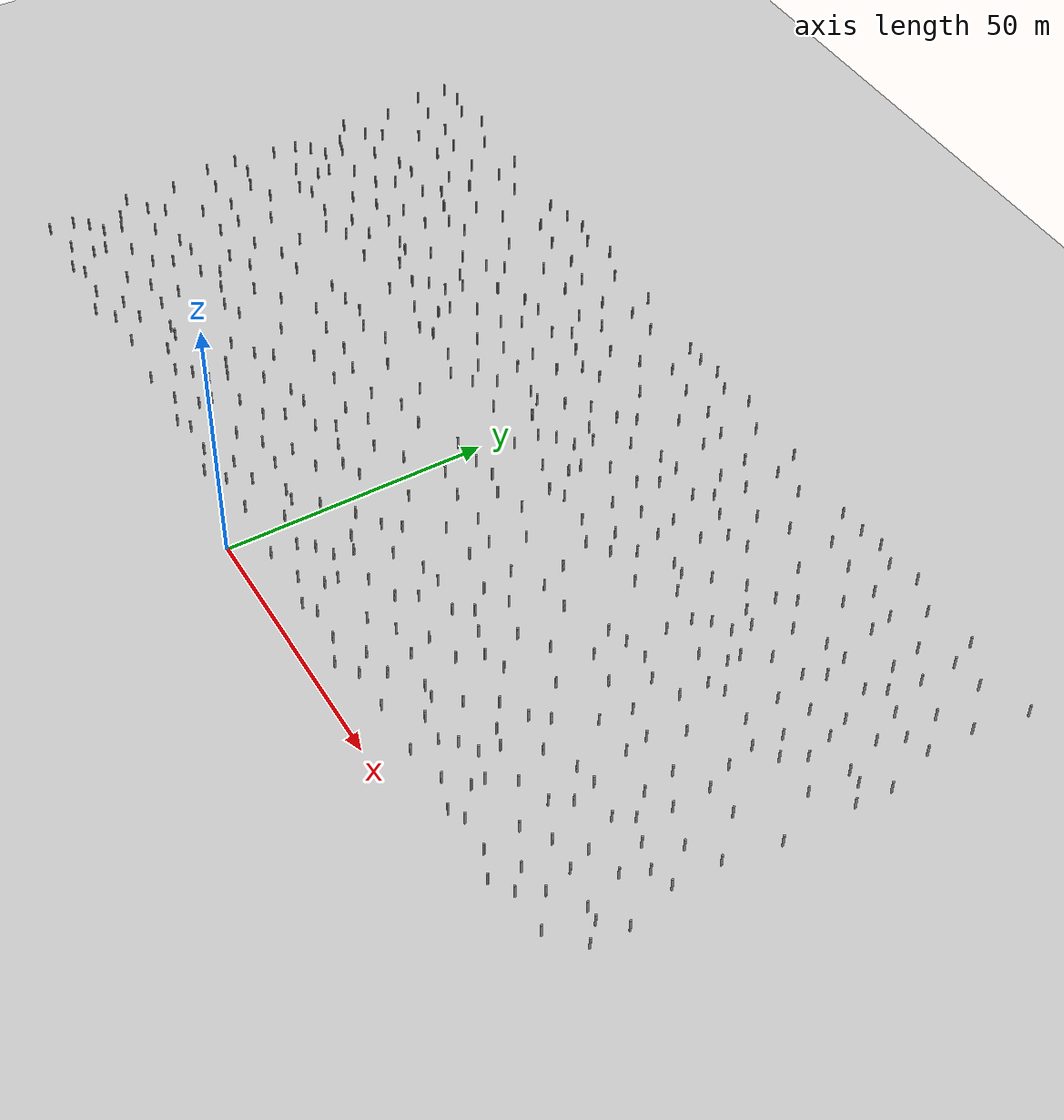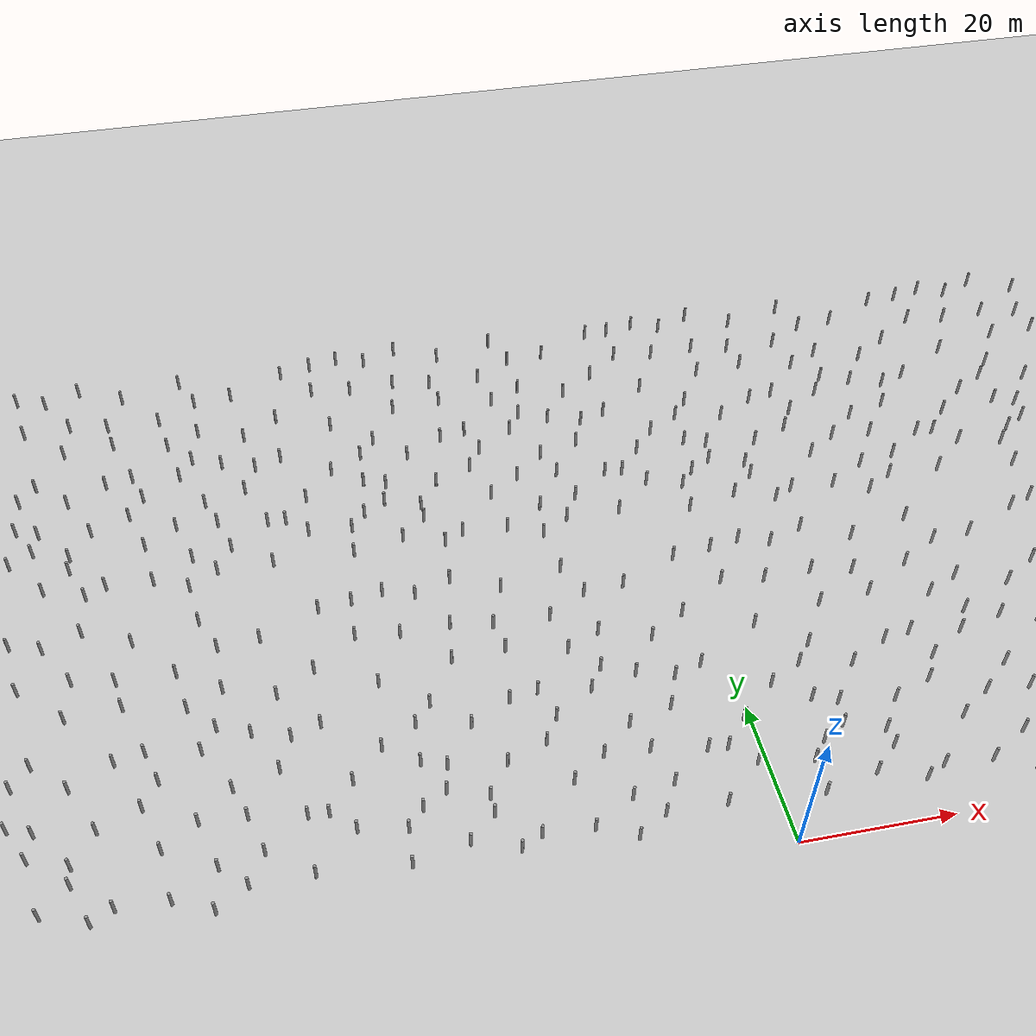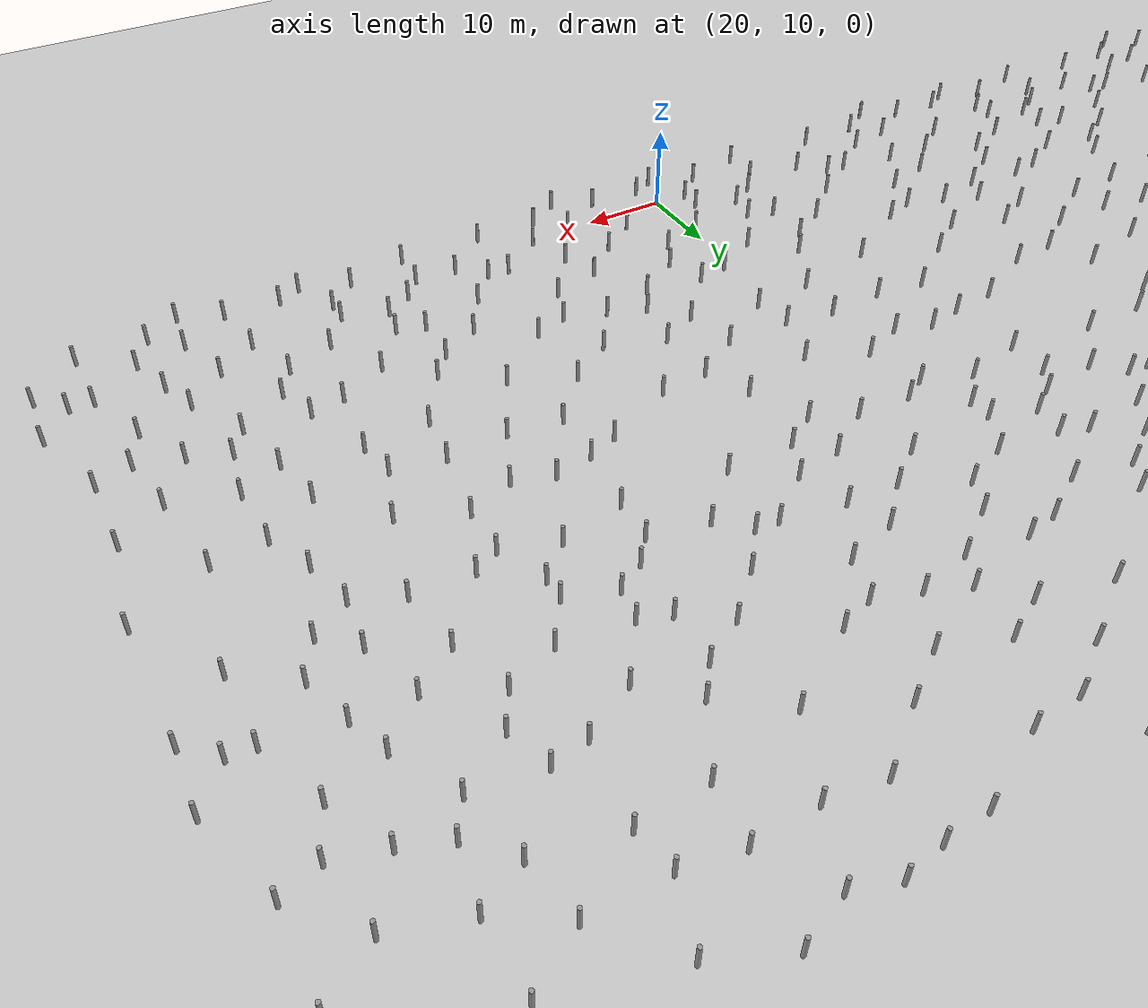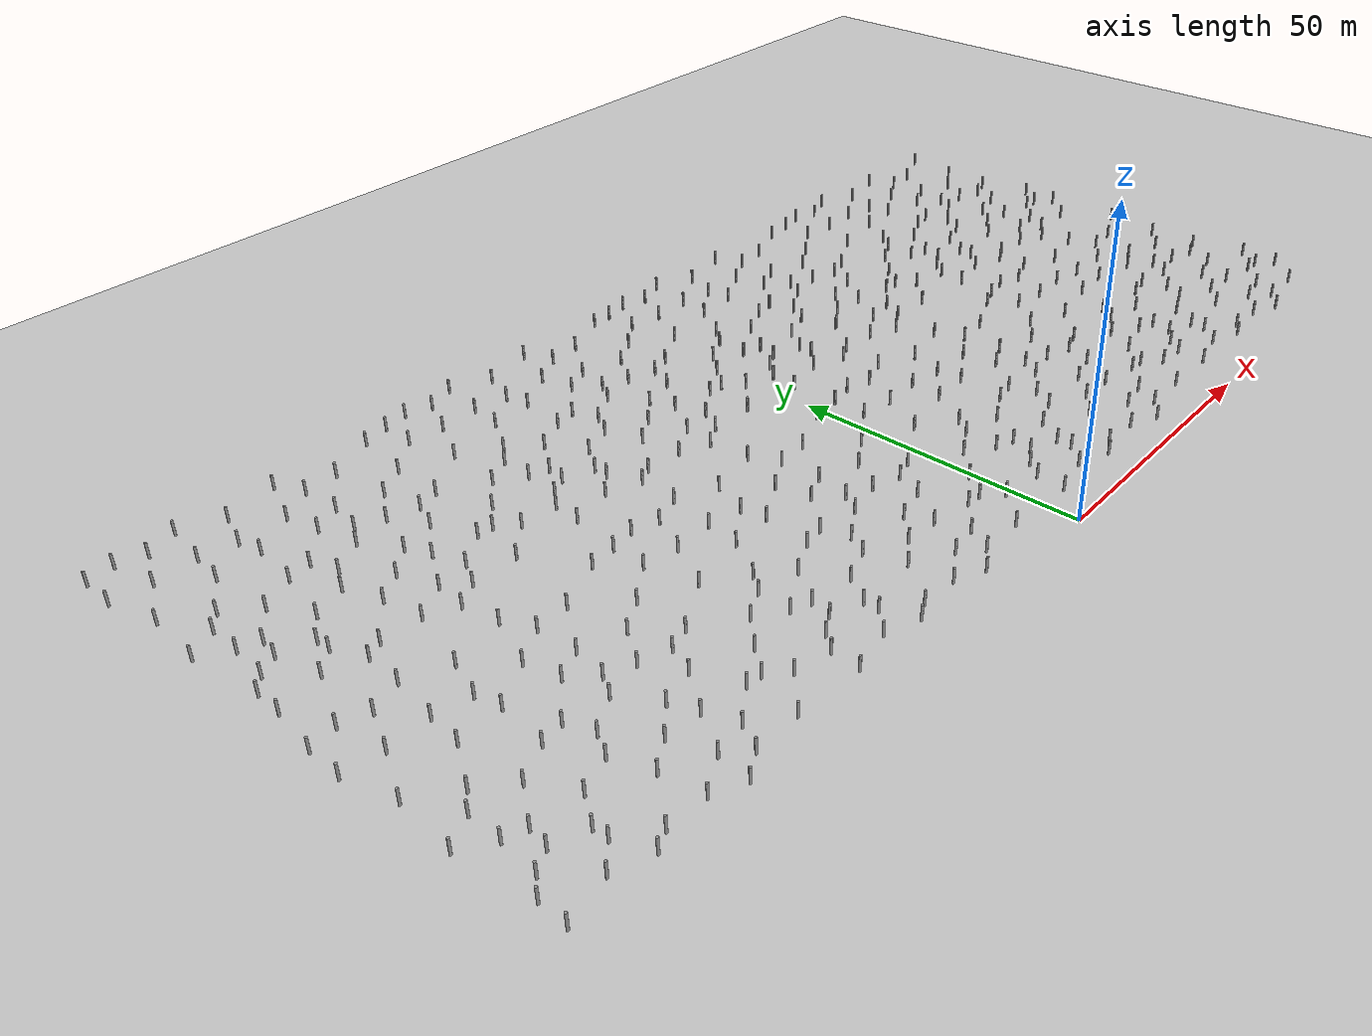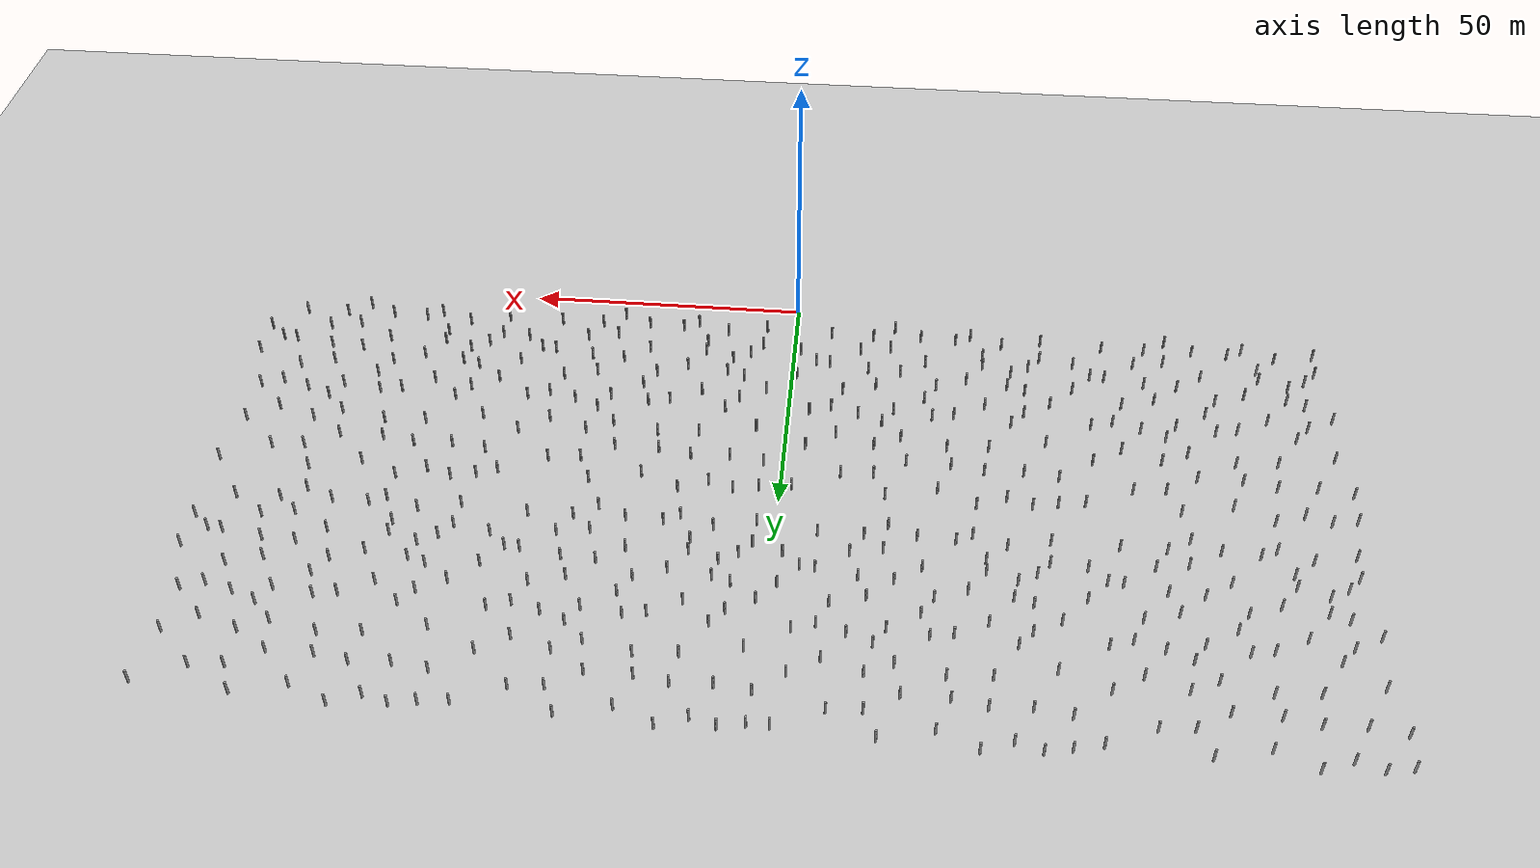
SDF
<sdf version="1.6">
 <world name="default">
  <model name="ground_plane">
   <static>1</static>
   <link name="link">
    <collision name="collision">
     <geometry><plane><normal>0 0 1</normal><size>100 100</size></plane></geometry>
     <surface><friction><ode><mu>100</mu><mu2>50</mu2></ode></friction></surface>
    </collision>
    <visual name="visual">
     <cast_shadows>0</cast_shadows>
     <geometry><plane><normal>0 0 1</normal><size>100 100</size></plane></geometry>
     <material>
      <script><uri>file://media/materials/scripts/gazebo.material</uri><name>Gazebo/Grey</name></script>
     </material>
    </visual>
   </link>
  </model>
  <model name="empty_pillars">
   <link name="link">
    <inertial>
     <mass>1</mass>
     <inertia><ixx>0.145833</ixx><ixy>0</ixy><ixz>0</ixz><iyy>0.145833</iyy><iyz>0</iyz><izz>0.125</izz></inertia>
    </inertial>
    <visual name="visual">
     <geometry><cylinder><radius>0.2</radius><length>5</length></cylinder></geometry>
     <material>
      <script><name>Gazebo/Grey</name><uri>file://media/materials/scripts/gazebo.material</uri></script>
      <shader type="vertex"><normal_map>__default__</normal_map></shader>
      <ambient>0.3 0.3 0.3 1</ambient>
      <diffuse>0.7 0.7 0.7 1</diffuse>
      <specular>0.01 0.01 0.01 1</specular>
      <emissive>0 0 0 1</emissive>
     </material>
    </visual>
    <collision name="collision">
     <geometry><cylinder><radius>0.05</radius><length>5</length></cylinder></geometry>
     <surface>
      <friction>
       <ode><mu>1</mu><mu2>1</mu2><fdir1>0 0 0</fdir1><slip1>0</slip1><slip2>0</slip2></ode>
       <torsional>
        <coefficient>1</coefficient>
        <patch_radius>0</patch_radius>
        <surface_radius>0</surface_radius>
        <use_patch_radius>1</use_patch_radius>
        <ode><slip>0</slip></ode>
       </torsional>
      </friction>
      <bounce><restitution_coefficient>0</restitution_coefficient><threshold>1e+06</threshold></bounce>
      <contact>
       <collide_without_contact>0</collide_without_contact>
       <collide_without_contact_bitmask>1</collide_without_contact_bitmask>
       <collide_bitmask>1</collide_bitmask>
       <ode>
        <soft_cfm>0</soft_cfm>
        <soft_erp>0.2</soft_erp>
        <kp>1e+13</kp>
        <kd>1</kd>
        <max_vel>0.01</max_vel>
        <min_depth>0</min_depth>
       </ode>
       <bullet>
        <split_impulse>1</split_impulse>
        <split_impulse_penetration_threshold>-0.01</split_impulse_penetration_threshold>
        <soft_cfm>0</soft_cfm>
        <soft_erp>0.2</soft_erp>
        <kp>1e+13</kp>
        <kd>1</kd>
       </bullet>
      </contact>
     </surface>
    </collision>
   </link>
   <model name="empty_pillar">
    <link name="link">
     <inertial>
      <mass>1</mass>
      <inertia><ixx>0.145833</ixx><ixy>0</ixy><ixz>0</ixz><iyy>0.145833</iyy><iyz>0</iyz><izz>0.125</izz></inertia>
     </inertial>
     <visual name="visual">
      <geometry><cylinder><radius>0.2</radius><length>5</length></cylinder></geometry>
      <material>
       <script><name>Gazebo/Grey</name><uri>file://media/materials/scripts/gazebo.material</uri></script>
       <shader type="vertex"><normal_map>__default__</normal_map></shader>
       <ambient>0.3 0.3 0.3 1</ambient>
       <diffuse>0.7 0.7 0.7 1</diffuse>
       <specular>0.01 0.01 0.01 1</specular>
       <emissive>0 0 0 1</emissive>
      </material>
     </visual>
     <collision name="collision">
      <geometry><cylinder><radius>0.05</radius><length>5</length></cylinder></geometry>
      <surface>
       <friction>
        <ode><mu>1</mu><mu2>1</mu2><fdir1>0 0 0</fdir1><slip1>0</slip1><slip2>0</slip2></ode>
        <torsional>
         <coefficient>1</coefficient>
         <patch_radius>0</patch_radius>
         <surface_radius>0</surface_radius>
         <use_patch_radius>1</use_patch_radius>
         <ode><slip>0</slip></ode>
        </torsional>
       </friction>
       <bounce><restitution_coefficient>0</restitution_coefficient><threshold>1e+06</threshold></bounce>
       <contact>
        <collide_without_contact>0</collide_without_contact>
        <collide_without_contact_bitmask>1</collide_without_contact_bitmask>
        <collide_bitmask>1</collide_bitmask>
        <ode>
         <soft_cfm>0</soft_cfm>
         <soft_erp>0.2</soft_erp>
         <kp>1e+13</kp>
         <kd>1</kd>
         <max_vel>0.01</max_vel>
         <min_depth>0</min_depth>
        </ode>
        <bullet>
         <split_impulse>1</split_impulse>
         <split_impulse_penetration_threshold>-0.01</split_impulse_penetration_threshold>
         <soft_cfm>0</soft_cfm>
         <soft_erp>0.2</soft_erp>
         <kp>1e+13</kp>
         <kd>1</kd>
        </bullet>
       </contact>
      </surface>
     </collision>
    </link>
    <static>0</static>
    <pose>-3.84527 -0.717439 0 0 -0 0</pose>
   </model>
   <model name="empty_pillar_clone">
    <link name="link">
     <inertial>
      <mass>1</mass>
      <inertia><ixx>0.145833</ixx><ixy>0</ixy><ixz>0</ixz><iyy>0.145833</iyy><iyz>0</iyz><izz>0.125</izz></inertia>
     </inertial>
     <visual name="visual">
      <geometry><cylinder><radius>0.2</radius><length>5</length></cylinder></geometry>
      <material>
       <script><name>Gazebo/Grey</name><uri>file://media/materials/scripts/gazebo.material</uri></script>
       <shader type="vertex"><normal_map>__default__</normal_map></shader>
       <ambient>0.3 0.3 0.3 1</ambient>
       <diffuse>0.7 0.7 0.7 1</diffuse>
       <specular>0.01 0.01 0.01 1</specular>
       <emissive>0 0 0 1</emissive>
      </material>
     </visual>
     <collision name="collision">
      <geometry><cylinder><radius>0.05</radius><length>5</length></cylinder></geometry>
      <surface>
       <friction>
        <ode><mu>1</mu><mu2>1</mu2><fdir1>0 0 0</fdir1><slip1>0</slip1><slip2>0</slip2></ode>
        <torsional>
         <coefficient>1</coefficient>
         <patch_radius>0</patch_radius>
         <surface_radius>0</surface_radius>
         <use_patch_radius>1</use_patch_radius>
         <ode><slip>0</slip></ode>
        </torsional>
       </friction>
       <bounce><restitution_coefficient>0</restitution_coefficient><threshold>1e+06</threshold></bounce>
       <contact>
        <collide_without_contact>0</collide_without_contact>
        <collide_without_contact_bitmask>1</collide_without_contact_bitmask>
        <collide_bitmask>1</collide_bitmask>
        <ode>
         <soft_cfm>0</soft_cfm>
         <soft_erp>0.2</soft_erp>
         <kp>1e+13</kp>
         <kd>1</kd>
         <max_vel>0.01</max_vel>
         <min_depth>0</min_depth>
        </ode>
        <bullet>
         <split_impulse>1</split_impulse>
         <split_impulse_penetration_threshold>-0.01</split_impulse_penetration_threshold>
         <soft_cfm>0</soft_cfm>
         <soft_erp>0.2</soft_erp>
         <kp>1e+13</kp>
         <kd>1</kd>
        </bullet>
       </contact>
      </surface>
     </collision>
    </link>
    <static>0</static>
    <pose>1.47843 -4.49529 0 0 -0 0</pose>
   </model>
   <model name="empty_pillar_clone_0">
    <link name="link">
     <inertial>
      <mass>1</mass>
      <inertia><ixx>0.145833</ixx><ixy>0</ixy><ixz>0</ixz><iyy>0.145833</iyy><iyz>0</iyz><izz>0.125</izz></inertia>
     </inertial>
     <visual name="visual">
      <geometry><cylinder><radius>0.2</radius><length>5</length></cylinder></geometry>
      <material>
       <script><name>Gazebo/Grey</name><uri>file://media/materials/scripts/gazebo.material</uri></script>
       <shader type="vertex"><normal_map>__default__</normal_map></shader>
       <ambient>0.3 0.3 0.3 1</ambient>
       <diffuse>0.7 0.7 0.7 1</diffuse>
       <specular>0.01 0.01 0.01 1</specular>
       <emissive>0 0 0 1</emissive>
      </material>
     </visual>
     <collision name="collision">
      <geometry><cylinder><radius>0.05</radius><length>5</length></cylinder></geometry>
      <surface>
       <friction>
        <ode><mu>1</mu><mu2>1</mu2><fdir1>0 0 0</fdir1><slip1>0</slip1><slip2>0</slip2></ode>
        <torsional>
         <coefficient>1</coefficient>
         <patch_radius>0</patch_radius>
         <surface_radius>0</surface_radius>
         <use_patch_radius>1</use_patch_radius>
         <ode><slip>0</slip></ode>
        </torsional>
       </friction>
       <bounce><restitution_coefficient>0</restitution_coefficient><threshold>1e+06</threshold></bounce>
       <contact>
        <collide_without_contact>0</collide_without_contact>
        <collide_without_contact_bitmask>1</collide_without_contact_bitmask>
        <collide_bitmask>1</collide_bitmask>
        <ode>
         <soft_cfm>0</soft_cfm>
         <soft_erp>0.2</soft_erp>
         <kp>1e+13</kp>
         <kd>1</kd>
         <max_vel>0.01</max_vel>
         <min_depth>0</min_depth>
        </ode>
        <bullet>
         <split_impulse>1</split_impulse>
         <split_impulse_penetration_threshold>-0.01</split_impulse_penetration_threshold>
         <soft_cfm>0</soft_cfm>
         <soft_erp>0.2</soft_erp>
         <kp>1e+13</kp>
         <kd>1</kd>
        </bullet>
       </contact>
      </surface>
     </collision>
    </link>
    <static>0</static>
    <pose>10.3453 -7.35986 0 0 -0 0</pose>
   </model>
   <model name="empty_pillar_clone_1">
    <link name="link">
     <inertial>
      <mass>1</mass>
      <inertia><ixx>0.145833</ixx><ixy>0</ixy><ixz>0</ixz><iyy>0.145833</iyy><iyz>0</iyz><izz>0.125</izz></inertia>
     </inertial>
     <visual name="visual">
      <geometry><cylinder><radius>0.2</radius><length>5</length></cylinder></geometry>
      <material>
       <script><name>Gazebo/Grey</name><uri>file://media/materials/scripts/gazebo.material</uri></script>
       <shader type="vertex"><normal_map>__default__</normal_map></shader>
       <ambient>0.3 0.3 0.3 1</ambient>
       <diffuse>0.7 0.7 0.7 1</diffuse>
       <specular>0.01 0.01 0.01 1</specular>
       <emissive>0 0 0 1</emissive>
      </material>
     </visual>
     <collision name="collision">
      <geometry><cylinder><radius>0.05</radius><length>5</length></cylinder></geometry>
      <surface>
       <friction>
        <ode><mu>1</mu><mu2>1</mu2><fdir1>0 0 0</fdir1><slip1>0</slip1><slip2>0</slip2></ode>
        <torsional>
         <coefficient>1</coefficient>
         <patch_radius>0</patch_radius>
         <surface_radius>0</surface_radius>
         <use_patch_radius>1</use_patch_radius>
         <ode><slip>0</slip></ode>
        </torsional>
       </friction>
       <bounce><restitution_coefficient>0</restitution_coefficient><threshold>1e+06</threshold></bounce>
       <contact>
        <collide_without_contact>0</collide_without_contact>
        <collide_without_contact_bitmask>1</collide_without_contact_bitmask>
        <collide_bitmask>1</collide_bitmask>
        <ode>
         <soft_cfm>0</soft_cfm>
         <soft_erp>0.2</soft_erp>
         <kp>1e+13</kp>
         <kd>1</kd>
         <max_vel>0.01</max_vel>
         <min_depth>0</min_depth>
        </ode>
        <bullet>
         <split_impulse>1</split_impulse>
         <split_impulse_penetration_threshold>-0.01</split_impulse_penetration_threshold>
         <soft_cfm>0</soft_cfm>
         <soft_erp>0.2</soft_erp>
         <kp>1e+13</kp>
         <kd>1</kd>
        </bullet>
       </contact>
      </surface>
     </collision>
    </link>
    <static>0</static>
    <pose>8.92248 2.14838 0 0 -0 0</pose>
   </model>
   <model name="empty_pillar_clone_10">
    <link name="link">
     <inertial>
      <mass>1</mass>
      <inertia><ixx>0.145833</ixx><ixy>0</ixy><ixz>0</ixz><iyy>0.145833</iyy><iyz>0</iyz><izz>0.125</izz></inertia>
     </inertial>
     <visual name="visual">
      <geometry><cylinder><radius>0.2</radius><length>5</length></cylinder></geometry>
      <material>
       <script><name>Gazebo/Grey</name><uri>file://media/materials/scripts/gazebo.material</uri></script>
       <shader type="vertex"><normal_map>__default__</normal_map></shader>
       <ambient>0.3 0.3 0.3 1</ambient>
       <diffuse>0.7 0.7 0.7 1</diffuse>
       <specular>0.01 0.01 0.01 1</specular>
       <emissive>0 0 0 1</emissive>
      </material>
     </visual>
     <collision name="collision">
      <geometry><cylinder><radius>0.05</radius><length>5</length></cylinder></geometry>
      <surface>
       <friction>
        <ode><mu>1</mu><mu2>1</mu2><fdir1>0 0 0</fdir1><slip1>0</slip1><slip2>0</slip2></ode>
        <torsional>
         <coefficient>1</coefficient>
         <patch_radius>0</patch_radius>
         <surface_radius>0</surface_radius>
         <use_patch_radius>1</use_patch_radius>
         <ode><slip>0</slip></ode>
        </torsional>
       </friction>
       <bounce><restitution_coefficient>0</restitution_coefficient><threshold>1e+06</threshold></bounce>
       <contact>
        <collide_without_contact>0</collide_without_contact>
        <collide_without_contact_bitmask>1</collide_without_contact_bitmask>
        <collide_bitmask>1</collide_bitmask>
        <ode>
         <soft_cfm>0</soft_cfm>
         <soft_erp>0.2</soft_erp>
         <kp>1e+13</kp>
         <kd>1</kd>
         <max_vel>0.01</max_vel>
         <min_depth>0</min_depth>
        </ode>
        <bullet>
         <split_impulse>1</split_impulse>
         <split_impulse_penetration_threshold>-0.01</split_impulse_penetration_threshold>
         <soft_cfm>0</soft_cfm>
         <soft_erp>0.2</soft_erp>
         <kp>1e+13</kp>
         <kd>1</kd>
        </bullet>
       </contact>
      </surface>
     </collision>
    </link>
    <static>0</static>
    <pose>13.5083 -16.8403 0 0 -0 0</pose>
   </model>
   <model name="empty_pillar_clone_11">
    <link name="link">
     <inertial>
      <mass>1</mass>
      <inertia><ixx>0.145833</ixx><ixy>0</ixy><ixz>0</ixz><iyy>0.145833</iyy><iyz>0</iyz><izz>0.125</izz></inertia>
     </inertial>
     <visual name="visual">
      <geometry><cylinder><radius>0.2</radius><length>5</length></cylinder></geometry>
      <material>
       <script><name>Gazebo/Grey</name><uri>file://media/materials/scripts/gazebo.material</uri></script>
       <shader type="vertex"><normal_map>__default__</normal_map></shader>
       <ambient>0.3 0.3 0.3 1</ambient>
       <diffuse>0.7 0.7 0.7 1</diffuse>
       <specular>0.01 0.01 0.01 1</specular>
       <emissive>0 0 0 1</emissive>
      </material>
     </visual>
     <collision name="collision">
      <geometry><cylinder><radius>0.05</radius><length>5</length></cylinder></geometry>
      <surface>
       <friction>
        <ode><mu>1</mu><mu2>1</mu2><fdir1>0 0 0</fdir1><slip1>0</slip1><slip2>0</slip2></ode>
        <torsional>
         <coefficient>1</coefficient>
         <patch_radius>0</patch_radius>
         <surface_radius>0</surface_radius>
         <use_patch_radius>1</use_patch_radius>
         <ode><slip>0</slip></ode>
        </torsional>
       </friction>
       <bounce><restitution_coefficient>0</restitution_coefficient><threshold>1e+06</threshold></bounce>
       <contact>
        <collide_without_contact>0</collide_without_contact>
        <collide_without_contact_bitmask>1</collide_without_contact_bitmask>
        <collide_bitmask>1</collide_bitmask>
        <ode>
         <soft_cfm>0</soft_cfm>
         <soft_erp>0.2</soft_erp>
         <kp>1e+13</kp>
         <kd>1</kd>
         <max_vel>0.01</max_vel>
         <min_depth>0</min_depth>
        </ode>
        <bullet>
         <split_impulse>1</split_impulse>
         <split_impulse_penetration_threshold>-0.01</split_impulse_penetration_threshold>
         <soft_cfm>0</soft_cfm>
         <soft_erp>0.2</soft_erp>
         <kp>1e+13</kp>
         <kd>1</kd>
        </bullet>
       </contact>
      </surface>
     </collision>
    </link>
    <static>0</static>
    <pose>7.98536 -17.8403 0 0 -0 0</pose>
   </model>
   <model name="empty_pillar_clone_12">
    <link name="link">
     <inertial>
      <mass>1</mass>
      <inertia><ixx>0.145833</ixx><ixy>0</ixy><ixz>0</ixz><iyy>0.145833</iyy><iyz>0</iyz><izz>0.125</izz></inertia>
     </inertial>
     <visual name="visual">
      <geometry><cylinder><radius>0.2</radius><length>5</length></cylinder></geometry>
      <material>
       <script><name>Gazebo/Grey</name><uri>file://media/materials/scripts/gazebo.material</uri></script>
       <shader type="vertex"><normal_map>__default__</normal_map></shader>
       <ambient>0.3 0.3 0.3 1</ambient>
       <diffuse>0.7 0.7 0.7 1</diffuse>
       <specular>0.01 0.01 0.01 1</specular>
       <emissive>0 0 0 1</emissive>
      </material>
     </visual>
     <collision name="collision">
      <geometry><cylinder><radius>0.05</radius><length>5</length></cylinder></geometry>
      <surface>
       <friction>
        <ode><mu>1</mu><mu2>1</mu2><fdir1>0 0 0</fdir1><slip1>0</slip1><slip2>0</slip2></ode>
        <torsional>
         <coefficient>1</coefficient>
         <patch_radius>0</patch_radius>
         <surface_radius>0</surface_radius>
         <use_patch_radius>1</use_patch_radius>
         <ode><slip>0</slip></ode>
        </torsional>
       </friction>
       <bounce><restitution_coefficient>0</restitution_coefficient><threshold>1e+06</threshold></bounce>
       <contact>
        <collide_without_contact>0</collide_without_contact>
        <collide_without_contact_bitmask>1</collide_without_contact_bitmask>
        <collide_bitmask>1</collide_bitmask>
        <ode>
         <soft_cfm>0</soft_cfm>
         <soft_erp>0.2</soft_erp>
         <kp>1e+13</kp>
         <kd>1</kd>
         <max_vel>0.01</max_vel>
         <min_depth>0</min_depth>
        </ode>
        <bullet>
         <split_impulse>1</split_impulse>
         <split_impulse_penetration_threshold>-0.01</split_impulse_penetration_threshold>
         <soft_cfm>0</soft_cfm>
         <soft_erp>0.2</soft_erp>
         <kp>1e+13</kp>
         <kd>1</kd>
        </bullet>
       </contact>
      </surface>
     </collision>
    </link>
    <static>0</static>
    <pose>-4.01464 -20.8403 0 0 -0 0</pose>
   </model>
   <model name="empty_pillar_clone_13">
    <link name="link">
     <inertial>
      <mass>1</mass>
      <inertia><ixx>0.145833</ixx><ixy>0</ixy><ixz>0</ixz><iyy>0.145833</iyy><iyz>0</iyz><izz>0.125</izz></inertia>
     </inertial>
     <visual name="visual">
      <geometry><cylinder><radius>0.2</radius><length>5</length></cylinder></geometry>
      <material>
       <script><name>Gazebo/Grey</name><uri>file://media/materials/scripts/gazebo.material</uri></script>
       <shader type="vertex"><normal_map>__default__</normal_map></shader>
       <ambient>0.3 0.3 0.3 1</ambient>
       <diffuse>0.7 0.7 0.7 1</diffuse>
       <specular>0.01 0.01 0.01 1</specular>
       <emissive>0 0 0 1</emissive>
      </material>
     </visual>
     <collision name="collision">
      <geometry><cylinder><radius>0.05</radius><length>5</length></cylinder></geometry>
      <surface>
       <friction>
        <ode><mu>1</mu><mu2>1</mu2><fdir1>0 0 0</fdir1><slip1>0</slip1><slip2>0</slip2></ode>
        <torsional>
         <coefficient>1</coefficient>
         <patch_radius>0</patch_radius>
         <surface_radius>0</surface_radius>
         <use_patch_radius>1</use_patch_radius>
         <ode><slip>0</slip></ode>
        </torsional>
       </friction>
       <bounce><restitution_coefficient>0</restitution_coefficient><threshold>1e+06</threshold></bounce>
       <contact>
        <collide_without_contact>0</collide_without_contact>
        <collide_without_contact_bitmask>1</collide_without_contact_bitmask>
        <collide_bitmask>1</collide_bitmask>
        <ode>
         <soft_cfm>0</soft_cfm>
         <soft_erp>0.2</soft_erp>
         <kp>1e+13</kp>
         <kd>1</kd>
         <max_vel>0.01</max_vel>
         <min_depth>0</min_depth>
        </ode>
        <bullet>
         <split_impulse>1</split_impulse>
         <split_impulse_penetration_threshold>-0.01</split_impulse_penetration_threshold>
         <soft_cfm>0</soft_cfm>
         <soft_erp>0.2</soft_erp>
         <kp>1e+13</kp>
         <kd>1</kd>
        </bullet>
       </contact>
      </surface>
     </collision>
    </link>
    <static>0</static>
    <pose>-9.01464 -14.4259 0 0 -0 0</pose>
   </model>
   <model name="empty_pillar_clone_14">
    <link name="link">
     <inertial>
      <mass>1</mass>
      <inertia><ixx>0.145833</ixx><ixy>0</ixy><ixz>0</ixz><iyy>0.145833</iyy><iyz>0</iyz><izz>0.125</izz></inertia>
     </inertial>
     <visual name="visual">
      <geometry><cylinder><radius>0.2</radius><length>5</length></cylinder></geometry>
      <material>
       <script><name>Gazebo/Grey</name><uri>file://media/materials/scripts/gazebo.material</uri></script>
       <shader type="vertex"><normal_map>__default__</normal_map></shader>
       <ambient>0.3 0.3 0.3 1</ambient>
       <diffuse>0.7 0.7 0.7 1</diffuse>
       <specular>0.01 0.01 0.01 1</specular>
       <emissive>0 0 0 1</emissive>
      </material>
     </visual>
     <collision name="collision">
      <geometry><cylinder><radius>0.05</radius><length>5</length></cylinder></geometry>
      <surface>
       <friction>
        <ode><mu>1</mu><mu2>1</mu2><fdir1>0 0 0</fdir1><slip1>0</slip1><slip2>0</slip2></ode>
        <torsional>
         <coefficient>1</coefficient>
         <patch_radius>0</patch_radius>
         <surface_radius>0</surface_radius>
         <use_patch_radius>1</use_patch_radius>
         <ode><slip>0</slip></ode>
        </torsional>
       </friction>
       <bounce><restitution_coefficient>0</restitution_coefficient><threshold>1e+06</threshold></bounce>
       <contact>
        <collide_without_contact>0</collide_without_contact>
        <collide_without_contact_bitmask>1</collide_without_contact_bitmask>
        <collide_bitmask>1</collide_bitmask>
        <ode>
         <soft_cfm>0</soft_cfm>
         <soft_erp>0.2</soft_erp>
         <kp>1e+13</kp>
         <kd>1</kd>
         <max_vel>0.01</max_vel>
         <min_depth>0</min_depth>
        </ode>
        <bullet>
         <split_impulse>1</split_impulse>
         <split_impulse_penetration_threshold>-0.01</split_impulse_penetration_threshold>
         <soft_cfm>0</soft_cfm>
         <soft_erp>0.2</soft_erp>
         <kp>1e+13</kp>
         <kd>1</kd>
        </bullet>
       </contact>
      </surface>
     </collision>
    </link>
    <static>0</static>
    <pose>-14.0146 0.646152 0 0 -0 0</pose>
   </model>
   <model name="empty_pillar_clone_15">
    <link name="link">
     <inertial>
      <mass>1</mass>
      <inertia><ixx>0.145833</ixx><ixy>0</ixy><ixz>0</ixz><iyy>0.145833</iyy><iyz>0</iyz><izz>0.125</izz></inertia>
     </inertial>
     <visual name="visual">
      <geometry><cylinder><radius>0.2</radius><length>5</length></cylinder></geometry>
      <material>
       <script><name>Gazebo/Grey</name><uri>file://media/materials/scripts/gazebo.material</uri></script>
       <shader type="vertex"><normal_map>__default__</normal_map></shader>
       <ambient>0.3 0.3 0.3 1</ambient>
       <diffuse>0.7 0.7 0.7 1</diffuse>
       <specular>0.01 0.01 0.01 1</specular>
       <emissive>0 0 0 1</emissive>
      </material>
     </visual>
     <collision name="collision">
      <geometry><cylinder><radius>0.05</radius><length>5</length></cylinder></geometry>
      <surface>
       <friction>
        <ode><mu>1</mu><mu2>1</mu2><fdir1>0 0 0</fdir1><slip1>0</slip1><slip2>0</slip2></ode>
        <torsional>
         <coefficient>1</coefficient>
         <patch_radius>0</patch_radius>
         <surface_radius>0</surface_radius>
         <use_patch_radius>1</use_patch_radius>
         <ode><slip>0</slip></ode>
        </torsional>
       </friction>
       <bounce><restitution_coefficient>0</restitution_coefficient><threshold>1e+06</threshold></bounce>
       <contact>
        <collide_without_contact>0</collide_without_contact>
        <collide_without_contact_bitmask>1</collide_without_contact_bitmask>
        <collide_bitmask>1</collide_bitmask>
        <ode>
         <soft_cfm>0</soft_cfm>
         <soft_erp>0.2</soft_erp>
         <kp>1e+13</kp>
         <kd>1</kd>
         <max_vel>0.01</max_vel>
         <min_depth>0</min_depth>
        </ode>
        <bullet>
         <split_impulse>1</split_impulse>
         <split_impulse_penetration_threshold>-0.01</split_impulse_penetration_threshold>
         <soft_cfm>0</soft_cfm>
         <soft_erp>0.2</soft_erp>
         <kp>1e+13</kp>
         <kd>1</kd>
        </bullet>
       </contact>
      </surface>
     </collision>
    </link>
    <static>0</static>
    <pose>-9.37193 -3.58732 0 0 -0 0</pose>
   </model>
   <model name="empty_pillar_clone_16">
    <link name="link">
     <inertial>
      <mass>1</mass>
      <inertia><ixx>0.145833</ixx><ixy>0</ixy><ixz>0</ixz><iyy>0.145833</iyy><iyz>0</iyz><izz>0.125</izz></inertia>
     </inertial>
     <visual name="visual">
      <geometry><cylinder><radius>0.2</radius><length>5</length></cylinder></geometry>
      <material>
       <script><name>Gazebo/Grey</name><uri>file://media/materials/scripts/gazebo.material</uri></script>
       <shader type="vertex"><normal_map>__default__</normal_map></shader>
       <ambient>0.3 0.3 0.3 1</ambient>
       <diffuse>0.7 0.7 0.7 1</diffuse>
       <specular>0.01 0.01 0.01 1</specular>
       <emissive>0 0 0 1</emissive>
      </material>
     </visual>
     <collision name="collision">
      <geometry><cylinder><radius>0.05</radius><length>5</length></cylinder></geometry>
      <surface>
       <friction>
        <ode><mu>1</mu><mu2>1</mu2><fdir1>0 0 0</fdir1><slip1>0</slip1><slip2>0</slip2></ode>
        <torsional>
         <coefficient>1</coefficient>
         <patch_radius>0</patch_radius>
         <surface_radius>0</surface_radius>
         <use_patch_radius>1</use_patch_radius>
         <ode><slip>0</slip></ode>
        </torsional>
       </friction>
       <bounce><restitution_coefficient>0</restitution_coefficient><threshold>1e+06</threshold></bounce>
       <contact>
        <collide_without_contact>0</collide_without_contact>
        <collide_without_contact_bitmask>1</collide_without_contact_bitmask>
        <collide_bitmask>1</collide_bitmask>
        <ode>
         <soft_cfm>0</soft_cfm>
         <soft_erp>0.2</soft_erp>
         <kp>1e+13</kp>
         <kd>1</kd>
         <max_vel>0.01</max_vel>
         <min_depth>0</min_depth>
        </ode>
        <bullet>
         <split_impulse>1</split_impulse>
         <split_impulse_penetration_threshold>-0.01</split_impulse_penetration_threshold>
         <soft_cfm>0</soft_cfm>
         <soft_erp>0.2</soft_erp>
         <kp>1e+13</kp>
         <kd>1</kd>
        </bullet>
       </contact>
      </surface>
     </collision>
    </link>
    <static>0</static>
    <pose>-9.20789 13.0504 0 0 -0 0</pose>
   </model>
   <model name="empty_pillar_clone_17">
    <link name="link">
     <inertial>
      <mass>1</mass>
      <inertia><ixx>0.145833</ixx><ixy>0</ixy><ixz>0</ixz><iyy>0.145833</iyy><iyz>0</iyz><izz>0.125</izz></inertia>
     </inertial>
     <visual name="visual">
      <geometry><cylinder><radius>0.2</radius><length>5</length></cylinder></geometry>
      <material>
       <script><name>Gazebo/Grey</name><uri>file://media/materials/scripts/gazebo.material</uri></script>
       <shader type="vertex"><normal_map>__default__</normal_map></shader>
       <ambient>0.3 0.3 0.3 1</ambient>
       <diffuse>0.7 0.7 0.7 1</diffuse>
       <specular>0.01 0.01 0.01 1</specular>
       <emissive>0 0 0 1</emissive>
      </material>
     </visual>
     <collision name="collision">
      <geometry><cylinder><radius>0.05</radius><length>5</length></cylinder></geometry>
      <surface>
       <friction>
        <ode><mu>1</mu><mu2>1</mu2><fdir1>0 0 0</fdir1><slip1>0</slip1><slip2>0</slip2></ode>
        <torsional>
         <coefficient>1</coefficient>
         <patch_radius>0</patch_radius>
         <surface_radius>0</surface_radius>
         <use_patch_radius>1</use_patch_radius>
         <ode><slip>0</slip></ode>
        </torsional>
       </friction>
       <bounce><restitution_coefficient>0</restitution_coefficient><threshold>1e+06</threshold></bounce>
       <contact>
        <collide_without_contact>0</collide_without_contact>
        <collide_without_contact_bitmask>1</collide_without_contact_bitmask>
        <collide_bitmask>1</collide_bitmask>
        <ode>
         <soft_cfm>0</soft_cfm>
         <soft_erp>0.2</soft_erp>
         <kp>1e+13</kp>
         <kd>1</kd>
         <max_vel>0.01</max_vel>
         <min_depth>0</min_depth>
        </ode>
        <bullet>
         <split_impulse>1</split_impulse>
         <split_impulse_penetration_threshold>-0.01</split_impulse_penetration_threshold>
         <soft_cfm>0</soft_cfm>
         <soft_erp>0.2</soft_erp>
         <kp>1e+13</kp>
         <kd>1</kd>
        </bullet>
       </contact>
      </surface>
     </collision>
    </link>
    <static>0</static>
    <pose>-16.0449 12.755 0 0 -0 0</pose>
   </model>
   <model name="empty_pillar_clone_18">
    <link name="link">
     <inertial>
      <mass>1</mass>
      <inertia><ixx>0.145833</ixx><ixy>0</ixy><ixz>0</ixz><iyy>0.145833</iyy><iyz>0</iyz><izz>0.125</izz></inertia>
     </inertial>
     <visual name="visual">
      <geometry><cylinder><radius>0.2</radius><length>5</length></cylinder></geometry>
      <material>
       <script><name>Gazebo/Grey</name><uri>file://media/materials/scripts/gazebo.material</uri></script>
       <shader type="vertex"><normal_map>__default__</normal_map></shader>
       <ambient>0.3 0.3 0.3 1</ambient>
       <diffuse>0.7 0.7 0.7 1</diffuse>
       <specular>0.01 0.01 0.01 1</specular>
       <emissive>0 0 0 1</emissive>
      </material>
     </visual>
     <collision name="collision">
      <geometry><cylinder><radius>0.05</radius><length>5</length></cylinder></geometry>
      <surface>
       <friction>
        <ode><mu>1</mu><mu2>1</mu2><fdir1>0 0 0</fdir1><slip1>0</slip1><slip2>0</slip2></ode>
        <torsional>
         <coefficient>1</coefficient>
         <patch_radius>0</patch_radius>
         <surface_radius>0</surface_radius>
         <use_patch_radius>1</use_patch_radius>
         <ode><slip>0</slip></ode>
        </torsional>
       </friction>
       <bounce><restitution_coefficient>0</restitution_coefficient><threshold>1e+06</threshold></bounce>
       <contact>
        <collide_without_contact>0</collide_without_contact>
        <collide_without_contact_bitmask>1</collide_without_contact_bitmask>
        <collide_bitmask>1</collide_bitmask>
        <ode>
         <soft_cfm>0</soft_cfm>
         <soft_erp>0.2</soft_erp>
         <kp>1e+13</kp>
         <kd>1</kd>
         <max_vel>0.01</max_vel>
         <min_depth>0</min_depth>
        </ode>
        <bullet>
         <split_impulse>1</split_impulse>
         <split_impulse_penetration_threshold>-0.01</split_impulse_penetration_threshold>
         <soft_cfm>0</soft_cfm>
         <soft_erp>0.2</soft_erp>
         <kp>1e+13</kp>
         <kd>1</kd>
        </bullet>
       </contact>
      </surface>
     </collision>
    </link>
    <static>0</static>
    <pose>-20.0146 5.15966 0 0 -0 0</pose>
   </model>
   <model name="empty_pillar_clone_19">
    <link name="link">
     <inertial>
      <mass>1</mass>
      <inertia><ixx>0.145833</ixx><ixy>0</ixy><ixz>0</ixz><iyy>0.145833</iyy><iyz>0</iyz><izz>0.125</izz></inertia>
     </inertial>
     <visual name="visual">
      <geometry><cylinder><radius>0.2</radius><length>5</length></cylinder></geometry>
      <material>
       <script><name>Gazebo/Grey</name><uri>file://media/materials/scripts/gazebo.material</uri></script>
       <shader type="vertex"><normal_map>__default__</normal_map></shader>
       <ambient>0.3 0.3 0.3 1</ambient>
       <diffuse>0.7 0.7 0.7 1</diffuse>
       <specular>0.01 0.01 0.01 1</specular>
       <emissive>0 0 0 1</emissive>
      </material>
     </visual>
     <collision name="collision">
      <geometry><cylinder><radius>0.05</radius><length>5</length></cylinder></geometry>
      <surface>
       <friction>
        <ode><mu>1</mu><mu2>1</mu2><fdir1>0 0 0</fdir1><slip1>0</slip1><slip2>0</slip2></ode>
        <torsional>
         <coefficient>1</coefficient>
         <patch_radius>0</patch_radius>
         <surface_radius>0</surface_radius>
         <use_patch_radius>1</use_patch_radius>
         <ode><slip>0</slip></ode>
        </torsional>
       </friction>
       <bounce><restitution_coefficient>0</restitution_coefficient><threshold>1e+06</threshold></bounce>
       <contact>
        <collide_without_contact>0</collide_without_contact>
        <collide_without_contact_bitmask>1</collide_without_contact_bitmask>
        <collide_bitmask>1</collide_bitmask>
        <ode>
         <soft_cfm>0</soft_cfm>
         <soft_erp>0.2</soft_erp>
         <kp>1e+13</kp>
         <kd>1</kd>
         <max_vel>0.01</max_vel>
         <min_depth>0</min_depth>
        </ode>
        <bullet>
         <split_impulse>1</split_impulse>
         <split_impulse_penetration_threshold>-0.01</split_impulse_penetration_threshold>
         <soft_cfm>0</soft_cfm>
         <soft_erp>0.2</soft_erp>
         <kp>1e+13</kp>
         <kd>1</kd>
        </bullet>
       </contact>
      </surface>
     </collision>
    </link>
    <static>0</static>
    <pose>-10.0146 7.15966 0 0 -0 0</pose>
   </model>
   <model name="empty_pillar_clone_2">
    <link name="link">
     <inertial>
      <mass>1</mass>
      <inertia><ixx>0.145833</ixx><ixy>0</ixy><ixz>0</ixz><iyy>0.145833</iyy><iyz>0</iyz><izz>0.125</izz></inertia>
     </inertial>
     <visual name="visual">
      <geometry><cylinder><radius>0.2</radius><length>5</length></cylinder></geometry>
      <material>
       <script><name>Gazebo/Grey</name><uri>file://media/materials/scripts/gazebo.material</uri></script>
       <shader type="vertex"><normal_map>__default__</normal_map></shader>
       <ambient>0.3 0.3 0.3 1</ambient>
       <diffuse>0.7 0.7 0.7 1</diffuse>
       <specular>0.01 0.01 0.01 1</specular>
       <emissive>0 0 0 1</emissive>
      </material>
     </visual>
     <collision name="collision">
      <geometry><cylinder><radius>0.05</radius><length>5</length></cylinder></geometry>
      <surface>
       <friction>
        <ode><mu>1</mu><mu2>1</mu2><fdir1>0 0 0</fdir1><slip1>0</slip1><slip2>0</slip2></ode>
        <torsional>
         <coefficient>1</coefficient>
         <patch_radius>0</patch_radius>
         <surface_radius>0</surface_radius>
         <use_patch_radius>1</use_patch_radius>
         <ode><slip>0</slip></ode>
        </torsional>
       </friction>
       <bounce><restitution_coefficient>0</restitution_coefficient><threshold>1e+06</threshold></bounce>
       <contact>
        <collide_without_contact>0</collide_without_contact>
        <collide_without_contact_bitmask>1</collide_without_contact_bitmask>
        <collide_bitmask>1</collide_bitmask>
        <ode>
         <soft_cfm>0</soft_cfm>
         <soft_erp>0.2</soft_erp>
         <kp>1e+13</kp>
         <kd>1</kd>
         <max_vel>0.01</max_vel>
         <min_depth>0</min_depth>
        </ode>
        <bullet>
         <split_impulse>1</split_impulse>
         <split_impulse_penetration_threshold>-0.01</split_impulse_penetration_threshold>
         <soft_cfm>0</soft_cfm>
         <soft_erp>0.2</soft_erp>
         <kp>1e+13</kp>
         <kd>1</kd>
        </bullet>
       </contact>
      </surface>
     </collision>
    </link>
    <static>0</static>
    <pose>6.92427 -1.06221 0 0 -0 0</pose>
   </model>
   <model name="empty_pillar_clone_20">
    <link name="link">
     <inertial>
      <mass>1</mass>
      <inertia><ixx>0.145833</ixx><ixy>0</ixy><ixz>0</ixz><iyy>0.145833</iyy><iyz>0</iyz><izz>0.125</izz></inertia>
     </inertial>
     <visual name="visual">
      <geometry><cylinder><radius>0.2</radius><length>5</length></cylinder></geometry>
      <material>
       <script><name>Gazebo/Grey</name><uri>file://media/materials/scripts/gazebo.material</uri></script>
       <shader type="vertex"><normal_map>__default__</normal_map></shader>
       <ambient>0.3 0.3 0.3 1</ambient>
       <diffuse>0.7 0.7 0.7 1</diffuse>
       <specular>0.01 0.01 0.01 1</specular>
       <emissive>0 0 0 1</emissive>
      </material>
     </visual>
     <collision name="collision">
      <geometry><cylinder><radius>0.05</radius><length>5</length></cylinder></geometry>
      <surface>
       <friction>
        <ode><mu>1</mu><mu2>1</mu2><fdir1>0 0 0</fdir1><slip1>0</slip1><slip2>0</slip2></ode>
        <torsional>
         <coefficient>1</coefficient>
         <patch_radius>0</patch_radius>
         <surface_radius>0</surface_radius>
         <use_patch_radius>1</use_patch_radius>
         <ode><slip>0</slip></ode>
        </torsional>
       </friction>
       <bounce><restitution_coefficient>0</restitution_coefficient><threshold>1e+06</threshold></bounce>
       <contact>
        <collide_without_contact>0</collide_without_contact>
        <collide_without_contact_bitmask>1</collide_without_contact_bitmask>
        <collide_bitmask>1</collide_bitmask>
        <ode>
         <soft_cfm>0</soft_cfm>
         <soft_erp>0.2</soft_erp>
         <kp>1e+13</kp>
         <kd>1</kd>
         <max_vel>0.01</max_vel>
         <min_depth>0</min_depth>
        </ode>
        <bullet>
         <split_impulse>1</split_impulse>
         <split_impulse_penetration_threshold>-0.01</split_impulse_penetration_threshold>
         <soft_cfm>0</soft_cfm>
         <soft_erp>0.2</soft_erp>
         <kp>1e+13</kp>
         <kd>1</kd>
        </bullet>
       </contact>
      </surface>
     </collision>
    </link>
    <static>0</static>
    <pose>-13.0146 19.1597 0 0 -0 0</pose>
   </model>
   <model name="empty_pillar_clone_21">
    <link name="link">
     <inertial>
      <mass>1</mass>
      <inertia><ixx>0.145833</ixx><ixy>0</ixy><ixz>0</ixz><iyy>0.145833</iyy><iyz>0</iyz><izz>0.125</izz></inertia>
     </inertial>
     <visual name="visual">
      <geometry><cylinder><radius>0.2</radius><length>5</length></cylinder></geometry>
      <material>
       <script><name>Gazebo/Grey</name><uri>file://media/materials/scripts/gazebo.material</uri></script>
       <shader type="vertex"><normal_map>__default__</normal_map></shader>
       <ambient>0.3 0.3 0.3 1</ambient>
       <diffuse>0.7 0.7 0.7 1</diffuse>
       <specular>0.01 0.01 0.01 1</specular>
       <emissive>0 0 0 1</emissive>
      </material>
     </visual>
     <collision name="collision">
      <geometry><cylinder><radius>0.05</radius><length>5</length></cylinder></geometry>
      <surface>
       <friction>
        <ode><mu>1</mu><mu2>1</mu2><fdir1>0 0 0</fdir1><slip1>0</slip1><slip2>0</slip2></ode>
        <torsional>
         <coefficient>1</coefficient>
         <patch_radius>0</patch_radius>
         <surface_radius>0</surface_radius>
         <use_patch_radius>1</use_patch_radius>
         <ode><slip>0</slip></ode>
        </torsional>
       </friction>
       <bounce><restitution_coefficient>0</restitution_coefficient><threshold>1e+06</threshold></bounce>
       <contact>
        <collide_without_contact>0</collide_without_contact>
        <collide_without_contact_bitmask>1</collide_without_contact_bitmask>
        <collide_bitmask>1</collide_bitmask>
        <ode>
         <soft_cfm>0</soft_cfm>
         <soft_erp>0.2</soft_erp>
         <kp>1e+13</kp>
         <kd>1</kd>
         <max_vel>0.01</max_vel>
         <min_depth>0</min_depth>
        </ode>
        <bullet>
         <split_impulse>1</split_impulse>
         <split_impulse_penetration_threshold>-0.01</split_impulse_penetration_threshold>
         <soft_cfm>0</soft_cfm>
         <soft_erp>0.2</soft_erp>
         <kp>1e+13</kp>
         <kd>1</kd>
        </bullet>
       </contact>
      </surface>
     </collision>
    </link>
    <static>0</static>
    <pose>-21.7273 19.7662 0 0 -0 0</pose>
   </model>
   <model name="empty_pillar_clone_22">
    <link name="link">
     <inertial>
      <mass>1</mass>
      <inertia><ixx>0.145833</ixx><ixy>0</ixy><ixz>0</ixz><iyy>0.145833</iyy><iyz>0</iyz><izz>0.125</izz></inertia>
     </inertial>
     <visual name="visual">
      <geometry><cylinder><radius>0.2</radius><length>5</length></cylinder></geometry>
      <material>
       <script><name>Gazebo/Grey</name><uri>file://media/materials/scripts/gazebo.material</uri></script>
       <shader type="vertex"><normal_map>__default__</normal_map></shader>
       <ambient>0.3 0.3 0.3 1</ambient>
       <diffuse>0.7 0.7 0.7 1</diffuse>
       <specular>0.01 0.01 0.01 1</specular>
       <emissive>0 0 0 1</emissive>
      </material>
     </visual>
     <collision name="collision">
      <geometry><cylinder><radius>0.05</radius><length>5</length></cylinder></geometry>
      <surface>
       <friction>
        <ode><mu>1</mu><mu2>1</mu2><fdir1>0 0 0</fdir1><slip1>0</slip1><slip2>0</slip2></ode>
        <torsional>
         <coefficient>1</coefficient>
         <patch_radius>0</patch_radius>
         <surface_radius>0</surface_radius>
         <use_patch_radius>1</use_patch_radius>
         <ode><slip>0</slip></ode>
        </torsional>
       </friction>
       <bounce><restitution_coefficient>0</restitution_coefficient><threshold>1e+06</threshold></bounce>
       <contact>
        <collide_without_contact>0</collide_without_contact>
        <collide_without_contact_bitmask>1</collide_without_contact_bitmask>
        <collide_bitmask>1</collide_bitmask>
        <ode>
         <soft_cfm>0</soft_cfm>
         <soft_erp>0.2</soft_erp>
         <kp>1e+13</kp>
         <kd>1</kd>
         <max_vel>0.01</max_vel>
         <min_depth>0</min_depth>
        </ode>
        <bullet>
         <split_impulse>1</split_impulse>
         <split_impulse_penetration_threshold>-0.01</split_impulse_penetration_threshold>
         <soft_cfm>0</soft_cfm>
         <soft_erp>0.2</soft_erp>
         <kp>1e+13</kp>
         <kd>1</kd>
        </bullet>
       </contact>
      </surface>
     </collision>
    </link>
    <static>0</static>
    <pose>-17.3667 20.5782 0 0 -0 0</pose>
   </model>
   <model name="empty_pillar_clone_23">
    <link name="link">
     <inertial>
      <mass>1</mass>
      <inertia><ixx>0.145833</ixx><ixy>0</ixy><ixz>0</ixz><iyy>0.145833</iyy><iyz>0</iyz><izz>0.125</izz></inertia>
     </inertial>
     <visual name="visual">
      <geometry><cylinder><radius>0.2</radius><length>5</length></cylinder></geometry>
      <material>
       <script><name>Gazebo/Grey</name><uri>file://media/materials/scripts/gazebo.material</uri></script>
       <shader type="vertex"><normal_map>__default__</normal_map></shader>
       <ambient>0.3 0.3 0.3 1</ambient>
       <diffuse>0.7 0.7 0.7 1</diffuse>
       <specular>0.01 0.01 0.01 1</specular>
       <emissive>0 0 0 1</emissive>
      </material>
     </visual>
     <collision name="collision">
      <geometry><cylinder><radius>0.05</radius><length>5</length></cylinder></geometry>
      <surface>
       <friction>
        <ode><mu>1</mu><mu2>1</mu2><fdir1>0 0 0</fdir1><slip1>0</slip1><slip2>0</slip2></ode>
        <torsional>
         <coefficient>1</coefficient>
         <patch_radius>0</patch_radius>
         <surface_radius>0</surface_radius>
         <use_patch_radius>1</use_patch_radius>
         <ode><slip>0</slip></ode>
        </torsional>
       </friction>
       <bounce><restitution_coefficient>0</restitution_coefficient><threshold>1e+06</threshold></bounce>
       <contact>
        <collide_without_contact>0</collide_without_contact>
        <collide_without_contact_bitmask>1</collide_without_contact_bitmask>
        <collide_bitmask>1</collide_bitmask>
        <ode>
         <soft_cfm>0</soft_cfm>
         <soft_erp>0.2</soft_erp>
         <kp>1e+13</kp>
         <kd>1</kd>
         <max_vel>0.01</max_vel>
         <min_depth>0</min_depth>
        </ode>
        <bullet>
         <split_impulse>1</split_impulse>
         <split_impulse_penetration_threshold>-0.01</split_impulse_penetration_threshold>
         <soft_cfm>0</soft_cfm>
         <soft_erp>0.2</soft_erp>
         <kp>1e+13</kp>
         <kd>1</kd>
        </bullet>
       </contact>
      </surface>
     </collision>
    </link>
    <static>0</static>
    <pose>-1.21984 18.1273 0 0 -0 0</pose>
   </model>
   <model name="empty_pillar_clone_24">
    <link name="link">
     <inertial>
      <mass>1</mass>
      <inertia><ixx>0.145833</ixx><ixy>0</ixy><ixz>0</ixz><iyy>0.145833</iyy><iyz>0</iyz><izz>0.125</izz></inertia>
     </inertial>
     <visual name="visual">
      <geometry><cylinder><radius>0.2</radius><length>5</length></cylinder></geometry>
      <material>
       <script><name>Gazebo/Grey</name><uri>file://media/materials/scripts/gazebo.material</uri></script>
       <shader type="vertex"><normal_map>__default__</normal_map></shader>
       <ambient>0.3 0.3 0.3 1</ambient>
       <diffuse>0.7 0.7 0.7 1</diffuse>
       <specular>0.01 0.01 0.01 1</specular>
       <emissive>0 0 0 1</emissive>
      </material>
     </visual>
     <collision name="collision">
      <geometry><cylinder><radius>0.05</radius><length>5</length></cylinder></geometry>
      <surface>
       <friction>
        <ode><mu>1</mu><mu2>1</mu2><fdir1>0 0 0</fdir1><slip1>0</slip1><slip2>0</slip2></ode>
        <torsional>
         <coefficient>1</coefficient>
         <patch_radius>0</patch_radius>
         <surface_radius>0</surface_radius>
         <use_patch_radius>1</use_patch_radius>
         <ode><slip>0</slip></ode>
        </torsional>
       </friction>
       <bounce><restitution_coefficient>0</restitution_coefficient><threshold>1e+06</threshold></bounce>
       <contact>
        <collide_without_contact>0</collide_without_contact>
        <collide_without_contact_bitmask>1</collide_without_contact_bitmask>
        <collide_bitmask>1</collide_bitmask>
        <ode>
         <soft_cfm>0</soft_cfm>
         <soft_erp>0.2</soft_erp>
         <kp>1e+13</kp>
         <kd>1</kd>
         <max_vel>0.01</max_vel>
         <min_depth>0</min_depth>
        </ode>
        <bullet>
         <split_impulse>1</split_impulse>
         <split_impulse_penetration_threshold>-0.01</split_impulse_penetration_threshold>
         <soft_cfm>0</soft_cfm>
         <soft_erp>0.2</soft_erp>
         <kp>1e+13</kp>
         <kd>1</kd>
        </bullet>
       </contact>
      </surface>
     </collision>
    </link>
    <static>0</static>
    <pose>-3.46957 11.9413 0 0 -0 0</pose>
   </model>
   <model name="empty_pillar_clone_25">
    <link name="link">
     <inertial>
      <mass>1</mass>
      <inertia><ixx>0.145833</ixx><ixy>0</ixy><ixz>0</ixz><iyy>0.145833</iyy><iyz>0</iyz><izz>0.125</izz></inertia>
     </inertial>
     <visual name="visual">
      <geometry><cylinder><radius>0.2</radius><length>5</length></cylinder></geometry>
      <material>
       <script><name>Gazebo/Grey</name><uri>file://media/materials/scripts/gazebo.material</uri></script>
       <shader type="vertex"><normal_map>__default__</normal_map></shader>
       <ambient>0.3 0.3 0.3 1</ambient>
       <diffuse>0.7 0.7 0.7 1</diffuse>
       <specular>0.01 0.01 0.01 1</specular>
       <emissive>0 0 0 1</emissive>
      </material>
     </visual>
     <collision name="collision">
      <geometry><cylinder><radius>0.05</radius><length>5</length></cylinder></geometry>
      <surface>
       <friction>
        <ode><mu>1</mu><mu2>1</mu2><fdir1>0 0 0</fdir1><slip1>0</slip1><slip2>0</slip2></ode>
        <torsional>
         <coefficient>1</coefficient>
         <patch_radius>0</patch_radius>
         <surface_radius>0</surface_radius>
         <use_patch_radius>1</use_patch_radius>
         <ode><slip>0</slip></ode>
        </torsional>
       </friction>
       <bounce><restitution_coefficient>0</restitution_coefficient><threshold>1e+06</threshold></bounce>
       <contact>
        <collide_without_contact>0</collide_without_contact>
        <collide_without_contact_bitmask>1</collide_without_contact_bitmask>
        <collide_bitmask>1</collide_bitmask>
        <ode>
         <soft_cfm>0</soft_cfm>
         <soft_erp>0.2</soft_erp>
         <kp>1e+13</kp>
         <kd>1</kd>
         <max_vel>0.01</max_vel>
         <min_depth>0</min_depth>
        </ode>
        <bullet>
         <split_impulse>1</split_impulse>
         <split_impulse_penetration_threshold>-0.01</split_impulse_penetration_threshold>
         <soft_cfm>0</soft_cfm>
         <soft_erp>0.2</soft_erp>
         <kp>1e+13</kp>
         <kd>1</kd>
        </bullet>
       </contact>
      </surface>
     </collision>
    </link>
    <static>0</static>
    <pose>-7.86239 21.1314 0 0 -0 0</pose>
   </model>
   <model name="empty_pillar_clone_26">
    <link name="link">
     <inertial>
      <mass>1</mass>
      <inertia><ixx>0.145833</ixx><ixy>0</ixy><ixz>0</ixz><iyy>0.145833</iyy><iyz>0</iyz><izz>0.125</izz></inertia>
     </inertial>
     <visual name="visual">
      <geometry><cylinder><radius>0.2</radius><length>5</length></cylinder></geometry>
      <material>
       <script><name>Gazebo/Grey</name><uri>file://media/materials/scripts/gazebo.material</uri></script>
       <shader type="vertex"><normal_map>__default__</normal_map></shader>
       <ambient>0.3 0.3 0.3 1</ambient>
       <diffuse>0.7 0.7 0.7 1</diffuse>
       <specular>0.01 0.01 0.01 1</specular>
       <emissive>0 0 0 1</emissive>
      </material>
     </visual>
     <collision name="collision">
      <geometry><cylinder><radius>0.05</radius><length>5</length></cylinder></geometry>
      <surface>
       <friction>
        <ode><mu>1</mu><mu2>1</mu2><fdir1>0 0 0</fdir1><slip1>0</slip1><slip2>0</slip2></ode>
        <torsional>
         <coefficient>1</coefficient>
         <patch_radius>0</patch_radius>
         <surface_radius>0</surface_radius>
         <use_patch_radius>1</use_patch_radius>
         <ode><slip>0</slip></ode>
        </torsional>
       </friction>
       <bounce><restitution_coefficient>0</restitution_coefficient><threshold>1e+06</threshold></bounce>
       <contact>
        <collide_without_contact>0</collide_without_contact>
        <collide_without_contact_bitmask>1</collide_without_contact_bitmask>
        <collide_bitmask>1</collide_bitmask>
        <ode>
         <soft_cfm>0</soft_cfm>
         <soft_erp>0.2</soft_erp>
         <kp>1e+13</kp>
         <kd>1</kd>
         <max_vel>0.01</max_vel>
         <min_depth>0</min_depth>
        </ode>
        <bullet>
         <split_impulse>1</split_impulse>
         <split_impulse_penetration_threshold>-0.01</split_impulse_penetration_threshold>
         <soft_cfm>0</soft_cfm>
         <soft_erp>0.2</soft_erp>
         <kp>1e+13</kp>
         <kd>1</kd>
        </bullet>
       </contact>
      </surface>
     </collision>
    </link>
    <static>0</static>
    <pose>7.70652 20.1444 0 0 -0 0</pose>
   </model>
   <model name="empty_pillar_clone_27">
    <link name="link">
     <inertial>
      <mass>1</mass>
      <inertia><ixx>0.145833</ixx><ixy>0</ixy><ixz>0</ixz><iyy>0.145833</iyy><iyz>0</iyz><izz>0.125</izz></inertia>
     </inertial>
     <visual name="visual">
      <geometry><cylinder><radius>0.2</radius><length>5</length></cylinder></geometry>
      <material>
       <script><name>Gazebo/Grey</name><uri>file://media/materials/scripts/gazebo.material</uri></script>
       <shader type="vertex"><normal_map>__default__</normal_map></shader>
       <ambient>0.3 0.3 0.3 1</ambient>
       <diffuse>0.7 0.7 0.7 1</diffuse>
       <specular>0.01 0.01 0.01 1</specular>
       <emissive>0 0 0 1</emissive>
      </material>
     </visual>
     <collision name="collision">
      <geometry><cylinder><radius>0.05</radius><length>5</length></cylinder></geometry>
      <surface>
       <friction>
        <ode><mu>1</mu><mu2>1</mu2><fdir1>0 0 0</fdir1><slip1>0</slip1><slip2>0</slip2></ode>
        <torsional>
         <coefficient>1</coefficient>
         <patch_radius>0</patch_radius>
         <surface_radius>0</surface_radius>
         <use_patch_radius>1</use_patch_radius>
         <ode><slip>0</slip></ode>
        </torsional>
       </friction>
       <bounce><restitution_coefficient>0</restitution_coefficient><threshold>1e+06</threshold></bounce>
       <contact>
        <collide_without_contact>0</collide_without_contact>
        <collide_without_contact_bitmask>1</collide_without_contact_bitmask>
        <collide_bitmask>1</collide_bitmask>
        <ode>
         <soft_cfm>0</soft_cfm>
         <soft_erp>0.2</soft_erp>
         <kp>1e+13</kp>
         <kd>1</kd>
         <max_vel>0.01</max_vel>
         <min_depth>0</min_depth>
        </ode>
        <bullet>
         <split_impulse>1</split_impulse>
         <split_impulse_penetration_threshold>-0.01</split_impulse_penetration_threshold>
         <soft_cfm>0</soft_cfm>
         <soft_erp>0.2</soft_erp>
         <kp>1e+13</kp>
         <kd>1</kd>
        </bullet>
       </contact>
      </surface>
     </collision>
    </link>
    <static>0</static>
    <pose>4.32163 11.823 0 0 -0 0</pose>
   </model>
   <model name="empty_pillar_clone_28">
    <link name="link">
     <inertial>
      <mass>1</mass>
      <inertia><ixx>0.145833</ixx><ixy>0</ixy><ixz>0</ixz><iyy>0.145833</iyy><iyz>0</iyz><izz>0.125</izz></inertia>
     </inertial>
     <visual name="visual">
      <geometry><cylinder><radius>0.2</radius><length>5</length></cylinder></geometry>
      <material>
       <script><name>Gazebo/Grey</name><uri>file://media/materials/scripts/gazebo.material</uri></script>
       <shader type="vertex"><normal_map>__default__</normal_map></shader>
       <ambient>0.3 0.3 0.3 1</ambient>
       <diffuse>0.7 0.7 0.7 1</diffuse>
       <specular>0.01 0.01 0.01 1</specular>
       <emissive>0 0 0 1</emissive>
      </material>
     </visual>
     <collision name="collision">
      <geometry><cylinder><radius>0.05</radius><length>5</length></cylinder></geometry>
      <surface>
       <friction>
        <ode><mu>1</mu><mu2>1</mu2><fdir1>0 0 0</fdir1><slip1>0</slip1><slip2>0</slip2></ode>
        <torsional>
         <coefficient>1</coefficient>
         <patch_radius>0</patch_radius>
         <surface_radius>0</surface_radius>
         <use_patch_radius>1</use_patch_radius>
         <ode><slip>0</slip></ode>
        </torsional>
       </friction>
       <bounce><restitution_coefficient>0</restitution_coefficient><threshold>1e+06</threshold></bounce>
       <contact>
        <collide_without_contact>0</collide_without_contact>
        <collide_without_contact_bitmask>1</collide_without_contact_bitmask>
        <collide_bitmask>1</collide_bitmask>
        <ode>
         <soft_cfm>0</soft_cfm>
         <soft_erp>0.2</soft_erp>
         <kp>1e+13</kp>
         <kd>1</kd>
         <max_vel>0.01</max_vel>
         <min_depth>0</min_depth>
        </ode>
        <bullet>
         <split_impulse>1</split_impulse>
         <split_impulse_penetration_threshold>-0.01</split_impulse_penetration_threshold>
         <soft_cfm>0</soft_cfm>
         <soft_erp>0.2</soft_erp>
         <kp>1e+13</kp>
         <kd>1</kd>
        </bullet>
       </contact>
      </surface>
     </collision>
    </link>
    <static>0</static>
    <pose>15.5447 15.5867 0 0 -0 0</pose>
   </model>
   <model name="empty_pillar_clone_29">
    <link name="link">
     <inertial>
      <mass>1</mass>
      <inertia><ixx>0.145833</ixx><ixy>0</ixy><ixz>0</ixz><iyy>0.145833</iyy><iyz>0</iyz><izz>0.125</izz></inertia>
     </inertial>
     <visual name="visual">
      <geometry><cylinder><radius>0.2</radius><length>5</length></cylinder></geometry>
      <material>
       <script><name>Gazebo/Grey</name><uri>file://media/materials/scripts/gazebo.material</uri></script>
       <shader type="vertex"><normal_map>__default__</normal_map></shader>
       <ambient>0.3 0.3 0.3 1</ambient>
       <diffuse>0.7 0.7 0.7 1</diffuse>
       <specular>0.01 0.01 0.01 1</specular>
       <emissive>0 0 0 1</emissive>
      </material>
     </visual>
     <collision name="collision">
      <geometry><cylinder><radius>0.05</radius><length>5</length></cylinder></geometry>
      <surface>
       <friction>
        <ode><mu>1</mu><mu2>1</mu2><fdir1>0 0 0</fdir1><slip1>0</slip1><slip2>0</slip2></ode>
        <torsional>
         <coefficient>1</coefficient>
         <patch_radius>0</patch_radius>
         <surface_radius>0</surface_radius>
         <use_patch_radius>1</use_patch_radius>
         <ode><slip>0</slip></ode>
        </torsional>
       </friction>
       <bounce><restitution_coefficient>0</restitution_coefficient><threshold>1e+06</threshold></bounce>
       <contact>
        <collide_without_contact>0</collide_without_contact>
        <collide_without_contact_bitmask>1</collide_without_contact_bitmask>
        <collide_bitmask>1</collide_bitmask>
        <ode>
         <soft_cfm>0</soft_cfm>
         <soft_erp>0.2</soft_erp>
         <kp>1e+13</kp>
         <kd>1</kd>
         <max_vel>0.01</max_vel>
         <min_depth>0</min_depth>
        </ode>
        <bullet>
         <split_impulse>1</split_impulse>
         <split_impulse_penetration_threshold>-0.01</split_impulse_penetration_threshold>
         <soft_cfm>0</soft_cfm>
         <soft_erp>0.2</soft_erp>
         <kp>1e+13</kp>
         <kd>1</kd>
        </bullet>
       </contact>
      </surface>
     </collision>
    </link>
    <static>0</static>
    <pose>10.08 8.0876 0 0 -0 0</pose>
   </model>
   <model name="empty_pillar_clone_3">
    <link name="link">
     <inertial>
      <mass>1</mass>
      <inertia><ixx>0.145833</ixx><ixy>0</ixy><ixz>0</ixz><iyy>0.145833</iyy><iyz>0</iyz><izz>0.125</izz></inertia>
     </inertial>
     <visual name="visual">
      <geometry><cylinder><radius>0.2</radius><length>5</length></cylinder></geometry>
      <material>
       <script><name>Gazebo/Grey</name><uri>file://media/materials/scripts/gazebo.material</uri></script>
       <shader type="vertex"><normal_map>__default__</normal_map></shader>
       <ambient>0.3 0.3 0.3 1</ambient>
       <diffuse>0.7 0.7 0.7 1</diffuse>
       <specular>0.01 0.01 0.01 1</specular>
       <emissive>0 0 0 1</emissive>
      </material>
     </visual>
     <collision name="collision">
      <geometry><cylinder><radius>0.05</radius><length>5</length></cylinder></geometry>
      <surface>
       <friction>
        <ode><mu>1</mu><mu2>1</mu2><fdir1>0 0 0</fdir1><slip1>0</slip1><slip2>0</slip2></ode>
        <torsional>
         <coefficient>1</coefficient>
         <patch_radius>0</patch_radius>
         <surface_radius>0</surface_radius>
         <use_patch_radius>1</use_patch_radius>
         <ode><slip>0</slip></ode>
        </torsional>
       </friction>
       <bounce><restitution_coefficient>0</restitution_coefficient><threshold>1e+06</threshold></bounce>
       <contact>
        <collide_without_contact>0</collide_without_contact>
        <collide_without_contact_bitmask>1</collide_without_contact_bitmask>
        <collide_bitmask>1</collide_bitmask>
        <ode>
         <soft_cfm>0</soft_cfm>
         <soft_erp>0.2</soft_erp>
         <kp>1e+13</kp>
         <kd>1</kd>
         <max_vel>0.01</max_vel>
         <min_depth>0</min_depth>
        </ode>
        <bullet>
         <split_impulse>1</split_impulse>
         <split_impulse_penetration_threshold>-0.01</split_impulse_penetration_threshold>
         <soft_cfm>0</soft_cfm>
         <soft_erp>0.2</soft_erp>
         <kp>1e+13</kp>
         <kd>1</kd>
        </bullet>
       </contact>
      </surface>
     </collision>
    </link>
    <static>0</static>
    <pose>5.99316 -11.2211 0 0 -0 0</pose>
   </model>
   <model name="empty_pillar_clone_30">
    <link name="link">
     <inertial>
      <mass>1</mass>
      <inertia><ixx>0.145833</ixx><ixy>0</ixy><ixz>0</ixz><iyy>0.145833</iyy><iyz>0</iyz><izz>0.125</izz></inertia>
     </inertial>
     <visual name="visual">
      <geometry><cylinder><radius>0.2</radius><length>5</length></cylinder></geometry>
      <material>
       <script><name>Gazebo/Grey</name><uri>file://media/materials/scripts/gazebo.material</uri></script>
       <shader type="vertex"><normal_map>__default__</normal_map></shader>
       <ambient>0.3 0.3 0.3 1</ambient>
       <diffuse>0.7 0.7 0.7 1</diffuse>
       <specular>0.01 0.01 0.01 1</specular>
       <emissive>0 0 0 1</emissive>
      </material>
     </visual>
     <collision name="collision">
      <geometry><cylinder><radius>0.05</radius><length>5</length></cylinder></geometry>
      <surface>
       <friction>
        <ode><mu>1</mu><mu2>1</mu2><fdir1>0 0 0</fdir1><slip1>0</slip1><slip2>0</slip2></ode>
        <torsional>
         <coefficient>1</coefficient>
         <patch_radius>0</patch_radius>
         <surface_radius>0</surface_radius>
         <use_patch_radius>1</use_patch_radius>
         <ode><slip>0</slip></ode>
        </torsional>
       </friction>
       <bounce><restitution_coefficient>0</restitution_coefficient><threshold>1e+06</threshold></bounce>
       <contact>
        <collide_without_contact>0</collide_without_contact>
        <collide_without_contact_bitmask>1</collide_without_contact_bitmask>
        <collide_bitmask>1</collide_bitmask>
        <ode>
         <soft_cfm>0</soft_cfm>
         <soft_erp>0.2</soft_erp>
         <kp>1e+13</kp>
         <kd>1</kd>
         <max_vel>0.01</max_vel>
         <min_depth>0</min_depth>
        </ode>
        <bullet>
         <split_impulse>1</split_impulse>
         <split_impulse_penetration_threshold>-0.01</split_impulse_penetration_threshold>
         <soft_cfm>0</soft_cfm>
         <soft_erp>0.2</soft_erp>
         <kp>1e+13</kp>
         <kd>1</kd>
        </bullet>
       </contact>
      </surface>
     </collision>
    </link>
    <static>0</static>
    <pose>23.752 19.2231 0 0 -0 0</pose>
   </model>
   <model name="empty_pillar_clone_31">
    <link name="link">
     <inertial>
      <mass>1</mass>
      <inertia><ixx>0.145833</ixx><ixy>0</ixy><ixz>0</ixz><iyy>0.145833</iyy><iyz>0</iyz><izz>0.125</izz></inertia>
     </inertial>
     <visual name="visual">
      <geometry><cylinder><radius>0.2</radius><length>5</length></cylinder></geometry>
      <material>
       <script><name>Gazebo/Grey</name><uri>file://media/materials/scripts/gazebo.material</uri></script>
       <shader type="vertex"><normal_map>__default__</normal_map></shader>
       <ambient>0.3 0.3 0.3 1</ambient>
       <diffuse>0.7 0.7 0.7 1</diffuse>
       <specular>0.01 0.01 0.01 1</specular>
       <emissive>0 0 0 1</emissive>
      </material>
     </visual>
     <collision name="collision">
      <geometry><cylinder><radius>0.05</radius><length>5</length></cylinder></geometry>
      <surface>
       <friction>
        <ode><mu>1</mu><mu2>1</mu2><fdir1>0 0 0</fdir1><slip1>0</slip1><slip2>0</slip2></ode>
        <torsional>
         <coefficient>1</coefficient>
         <patch_radius>0</patch_radius>
         <surface_radius>0</surface_radius>
         <use_patch_radius>1</use_patch_radius>
         <ode><slip>0</slip></ode>
        </torsional>
       </friction>
       <bounce><restitution_coefficient>0</restitution_coefficient><threshold>1e+06</threshold></bounce>
       <contact>
        <collide_without_contact>0</collide_without_contact>
        <collide_without_contact_bitmask>1</collide_without_contact_bitmask>
        <collide_bitmask>1</collide_bitmask>
        <ode>
         <soft_cfm>0</soft_cfm>
         <soft_erp>0.2</soft_erp>
         <kp>1e+13</kp>
         <kd>1</kd>
         <max_vel>0.01</max_vel>
         <min_depth>0</min_depth>
        </ode>
        <bullet>
         <split_impulse>1</split_impulse>
         <split_impulse_penetration_threshold>-0.01</split_impulse_penetration_threshold>
         <soft_cfm>0</soft_cfm>
         <soft_erp>0.2</soft_erp>
         <kp>1e+13</kp>
         <kd>1</kd>
        </bullet>
       </contact>
      </surface>
     </collision>
    </link>
    <static>0</static>
    <pose>22.0722 9.04182 0 0 -0 0</pose>
   </model>
   <model name="empty_pillar_clone_32">
    <link name="link">
     <inertial>
      <mass>1</mass>
      <inertia><ixx>0.145833</ixx><ixy>0</ixy><ixz>0</ixz><iyy>0.145833</iyy><iyz>0</iyz><izz>0.125</izz></inertia>
     </inertial>
     <visual name="visual">
      <geometry><cylinder><radius>0.2</radius><length>5</length></cylinder></geometry>
      <material>
       <script><name>Gazebo/Grey</name><uri>file://media/materials/scripts/gazebo.material</uri></script>
       <shader type="vertex"><normal_map>__default__</normal_map></shader>
       <ambient>0.3 0.3 0.3 1</ambient>
       <diffuse>0.7 0.7 0.7 1</diffuse>
       <specular>0.01 0.01 0.01 1</specular>
       <emissive>0 0 0 1</emissive>
      </material>
     </visual>
     <collision name="collision">
      <geometry><cylinder><radius>0.05</radius><length>5</length></cylinder></geometry>
      <surface>
       <friction>
        <ode><mu>1</mu><mu2>1</mu2><fdir1>0 0 0</fdir1><slip1>0</slip1><slip2>0</slip2></ode>
        <torsional>
         <coefficient>1</coefficient>
         <patch_radius>0</patch_radius>
         <surface_radius>0</surface_radius>
         <use_patch_radius>1</use_patch_radius>
         <ode><slip>0</slip></ode>
        </torsional>
       </friction>
       <bounce><restitution_coefficient>0</restitution_coefficient><threshold>1e+06</threshold></bounce>
       <contact>
        <collide_without_contact>0</collide_without_contact>
        <collide_without_contact_bitmask>1</collide_without_contact_bitmask>
        <collide_bitmask>1</collide_bitmask>
        <ode>
         <soft_cfm>0</soft_cfm>
         <soft_erp>0.2</soft_erp>
         <kp>1e+13</kp>
         <kd>1</kd>
         <max_vel>0.01</max_vel>
         <min_depth>0</min_depth>
        </ode>
        <bullet>
         <split_impulse>1</split_impulse>
         <split_impulse_penetration_threshold>-0.01</split_impulse_penetration_threshold>
         <soft_cfm>0</soft_cfm>
         <soft_erp>0.2</soft_erp>
         <kp>1e+13</kp>
         <kd>1</kd>
        </bullet>
       </contact>
      </surface>
     </collision>
    </link>
    <static>0</static>
    <pose>21.9854 0.15966 0 0 -0 0</pose>
   </model>
   <model name="empty_pillar_clone_33">
    <link name="link">
     <inertial>
      <mass>1</mass>
      <inertia><ixx>0.145833</ixx><ixy>0</ixy><ixz>0</ixz><iyy>0.145833</iyy><iyz>0</iyz><izz>0.125</izz></inertia>
     </inertial>
     <visual name="visual">
      <geometry><cylinder><radius>0.2</radius><length>5</length></cylinder></geometry>
      <material>
       <script><name>Gazebo/Grey</name><uri>file://media/materials/scripts/gazebo.material</uri></script>
       <shader type="vertex"><normal_map>__default__</normal_map></shader>
       <ambient>0.3 0.3 0.3 1</ambient>
       <diffuse>0.7 0.7 0.7 1</diffuse>
       <specular>0.01 0.01 0.01 1</specular>
       <emissive>0 0 0 1</emissive>
      </material>
     </visual>
     <collision name="collision">
      <geometry><cylinder><radius>0.05</radius><length>5</length></cylinder></geometry>
      <surface>
       <friction>
        <ode><mu>1</mu><mu2>1</mu2><fdir1>0 0 0</fdir1><slip1>0</slip1><slip2>0</slip2></ode>
        <torsional>
         <coefficient>1</coefficient>
         <patch_radius>0</patch_radius>
         <surface_radius>0</surface_radius>
         <use_patch_radius>1</use_patch_radius>
         <ode><slip>0</slip></ode>
        </torsional>
       </friction>
       <bounce><restitution_coefficient>0</restitution_coefficient><threshold>1e+06</threshold></bounce>
       <contact>
        <collide_without_contact>0</collide_without_contact>
        <collide_without_contact_bitmask>1</collide_without_contact_bitmask>
        <collide_bitmask>1</collide_bitmask>
        <ode>
         <soft_cfm>0</soft_cfm>
         <soft_erp>0.2</soft_erp>
         <kp>1e+13</kp>
         <kd>1</kd>
         <max_vel>0.01</max_vel>
         <min_depth>0</min_depth>
        </ode>
        <bullet>
         <split_impulse>1</split_impulse>
         <split_impulse_penetration_threshold>-0.01</split_impulse_penetration_threshold>
         <soft_cfm>0</soft_cfm>
         <soft_erp>0.2</soft_erp>
         <kp>1e+13</kp>
         <kd>1</kd>
        </bullet>
       </contact>
      </surface>
     </collision>
    </link>
    <static>0</static>
    <pose>21.5621 -13.0704 0 0 -0 0</pose>
   </model>
   <model name="empty_pillar_clone_34">
    <link name="link">
     <inertial>
      <mass>1</mass>
      <inertia><ixx>0.145833</ixx><ixy>0</ixy><ixz>0</ixz><iyy>0.145833</iyy><iyz>0</iyz><izz>0.125</izz></inertia>
     </inertial>
     <visual name="visual">
      <geometry><cylinder><radius>0.2</radius><length>5</length></cylinder></geometry>
      <material>
       <script><name>Gazebo/Grey</name><uri>file://media/materials/scripts/gazebo.material</uri></script>
       <shader type="vertex"><normal_map>__default__</normal_map></shader>
       <ambient>0.3 0.3 0.3 1</ambient>
       <diffuse>0.7 0.7 0.7 1</diffuse>
       <specular>0.01 0.01 0.01 1</specular>
       <emissive>0 0 0 1</emissive>
      </material>
     </visual>
     <collision name="collision">
      <geometry><cylinder><radius>0.05</radius><length>5</length></cylinder></geometry>
      <surface>
       <friction>
        <ode><mu>1</mu><mu2>1</mu2><fdir1>0 0 0</fdir1><slip1>0</slip1><slip2>0</slip2></ode>
        <torsional>
         <coefficient>1</coefficient>
         <patch_radius>0</patch_radius>
         <surface_radius>0</surface_radius>
         <use_patch_radius>1</use_patch_radius>
         <ode><slip>0</slip></ode>
        </torsional>
       </friction>
       <bounce><restitution_coefficient>0</restitution_coefficient><threshold>1e+06</threshold></bounce>
       <contact>
        <collide_without_contact>0</collide_without_contact>
        <collide_without_contact_bitmask>1</collide_without_contact_bitmask>
        <collide_bitmask>1</collide_bitmask>
        <ode>
         <soft_cfm>0</soft_cfm>
         <soft_erp>0.2</soft_erp>
         <kp>1e+13</kp>
         <kd>1</kd>
         <max_vel>0.01</max_vel>
         <min_depth>0</min_depth>
        </ode>
        <bullet>
         <split_impulse>1</split_impulse>
         <split_impulse_penetration_threshold>-0.01</split_impulse_penetration_threshold>
         <soft_cfm>0</soft_cfm>
         <soft_erp>0.2</soft_erp>
         <kp>1e+13</kp>
         <kd>1</kd>
        </bullet>
       </contact>
      </surface>
     </collision>
    </link>
    <static>0</static>
    <pose>19.0861 -20.8946 0 0 -0 0</pose>
   </model>
   <model name="empty_pillar_clone_35">
    <link name="link">
     <inertial>
      <mass>1</mass>
      <inertia><ixx>0.145833</ixx><ixy>0</ixy><ixz>0</ixz><iyy>0.145833</iyy><iyz>0</iyz><izz>0.125</izz></inertia>
     </inertial>
     <visual name="visual">
      <geometry><cylinder><radius>0.2</radius><length>5</length></cylinder></geometry>
      <material>
       <script><name>Gazebo/Grey</name><uri>file://media/materials/scripts/gazebo.material</uri></script>
       <shader type="vertex"><normal_map>__default__</normal_map></shader>
       <ambient>0.3 0.3 0.3 1</ambient>
       <diffuse>0.7 0.7 0.7 1</diffuse>
       <specular>0.01 0.01 0.01 1</specular>
       <emissive>0 0 0 1</emissive>
      </material>
     </visual>
     <collision name="collision">
      <geometry><cylinder><radius>0.05</radius><length>5</length></cylinder></geometry>
      <surface>
       <friction>
        <ode><mu>1</mu><mu2>1</mu2><fdir1>0 0 0</fdir1><slip1>0</slip1><slip2>0</slip2></ode>
        <torsional>
         <coefficient>1</coefficient>
         <patch_radius>0</patch_radius>
         <surface_radius>0</surface_radius>
         <use_patch_radius>1</use_patch_radius>
         <ode><slip>0</slip></ode>
        </torsional>
       </friction>
       <bounce><restitution_coefficient>0</restitution_coefficient><threshold>1e+06</threshold></bounce>
       <contact>
        <collide_without_contact>0</collide_without_contact>
        <collide_without_contact_bitmask>1</collide_without_contact_bitmask>
        <collide_bitmask>1</collide_bitmask>
        <ode>
         <soft_cfm>0</soft_cfm>
         <soft_erp>0.2</soft_erp>
         <kp>1e+13</kp>
         <kd>1</kd>
         <max_vel>0.01</max_vel>
         <min_depth>0</min_depth>
        </ode>
        <bullet>
         <split_impulse>1</split_impulse>
         <split_impulse_penetration_threshold>-0.01</split_impulse_penetration_threshold>
         <soft_cfm>0</soft_cfm>
         <soft_erp>0.2</soft_erp>
         <kp>1e+13</kp>
         <kd>1</kd>
        </bullet>
       </contact>
      </surface>
     </collision>
    </link>
    <static>0</static>
    <pose>-19.4431 -17.0281 0 0 -0 0</pose>
   </model>
   <model name="empty_pillar_clone_36">
    <link name="link">
     <inertial>
      <mass>1</mass>
      <inertia><ixx>0.145833</ixx><ixy>0</ixy><ixz>0</ixz><iyy>0.145833</iyy><iyz>0</iyz><izz>0.125</izz></inertia>
     </inertial>
     <visual name="visual">
      <geometry><cylinder><radius>0.2</radius><length>5</length></cylinder></geometry>
      <material>
       <script><name>Gazebo/Grey</name><uri>file://media/materials/scripts/gazebo.material</uri></script>
       <shader type="vertex"><normal_map>__default__</normal_map></shader>
       <ambient>0.3 0.3 0.3 1</ambient>
       <diffuse>0.7 0.7 0.7 1</diffuse>
       <specular>0.01 0.01 0.01 1</specular>
       <emissive>0 0 0 1</emissive>
      </material>
     </visual>
     <collision name="collision">
      <geometry><cylinder><radius>0.05</radius><length>5</length></cylinder></geometry>
      <surface>
       <friction>
        <ode><mu>1</mu><mu2>1</mu2><fdir1>0 0 0</fdir1><slip1>0</slip1><slip2>0</slip2></ode>
        <torsional>
         <coefficient>1</coefficient>
         <patch_radius>0</patch_radius>
         <surface_radius>0</surface_radius>
         <use_patch_radius>1</use_patch_radius>
         <ode><slip>0</slip></ode>
        </torsional>
       </friction>
       <bounce><restitution_coefficient>0</restitution_coefficient><threshold>1e+06</threshold></bounce>
       <contact>
        <collide_without_contact>0</collide_without_contact>
        <collide_without_contact_bitmask>1</collide_without_contact_bitmask>
        <collide_bitmask>1</collide_bitmask>
        <ode>
         <soft_cfm>0</soft_cfm>
         <soft_erp>0.2</soft_erp>
         <kp>1e+13</kp>
         <kd>1</kd>
         <max_vel>0.01</max_vel>
         <min_depth>0</min_depth>
        </ode>
        <bullet>
         <split_impulse>1</split_impulse>
         <split_impulse_penetration_threshold>-0.01</split_impulse_penetration_threshold>
         <soft_cfm>0</soft_cfm>
         <soft_erp>0.2</soft_erp>
         <kp>1e+13</kp>
         <kd>1</kd>
        </bullet>
       </contact>
      </surface>
     </collision>
    </link>
    <static>0</static>
    <pose>-21.0146 -4.84034 0 0 -0 0</pose>
   </model>
   <model name="empty_pillar_clone_37">
    <link name="link">
     <inertial>
      <mass>1</mass>
      <inertia><ixx>0.145833</ixx><ixy>0</ixy><ixz>0</ixz><iyy>0.145833</iyy><iyz>0</iyz><izz>0.125</izz></inertia>
     </inertial>
     <visual name="visual">
      <geometry><cylinder><radius>0.2</radius><length>5</length></cylinder></geometry>
      <material>
       <script><name>Gazebo/Grey</name><uri>file://media/materials/scripts/gazebo.material</uri></script>
       <shader type="vertex"><normal_map>__default__</normal_map></shader>
       <ambient>0.3 0.3 0.3 1</ambient>
       <diffuse>0.7 0.7 0.7 1</diffuse>
       <specular>0.01 0.01 0.01 1</specular>
       <emissive>0 0 0 1</emissive>
      </material>
     </visual>
     <collision name="collision">
      <geometry><cylinder><radius>0.05</radius><length>5</length></cylinder></geometry>
      <surface>
       <friction>
        <ode><mu>1</mu><mu2>1</mu2><fdir1>0 0 0</fdir1><slip1>0</slip1><slip2>0</slip2></ode>
        <torsional>
         <coefficient>1</coefficient>
         <patch_radius>0</patch_radius>
         <surface_radius>0</surface_radius>
         <use_patch_radius>1</use_patch_radius>
         <ode><slip>0</slip></ode>
        </torsional>
       </friction>
       <bounce><restitution_coefficient>0</restitution_coefficient><threshold>1e+06</threshold></bounce>
       <contact>
        <collide_without_contact>0</collide_without_contact>
        <collide_without_contact_bitmask>1</collide_without_contact_bitmask>
        <collide_bitmask>1</collide_bitmask>
        <ode>
         <soft_cfm>0</soft_cfm>
         <soft_erp>0.2</soft_erp>
         <kp>1e+13</kp>
         <kd>1</kd>
         <max_vel>0.01</max_vel>
         <min_depth>0</min_depth>
        </ode>
        <bullet>
         <split_impulse>1</split_impulse>
         <split_impulse_penetration_threshold>-0.01</split_impulse_penetration_threshold>
         <soft_cfm>0</soft_cfm>
         <soft_erp>0.2</soft_erp>
         <kp>1e+13</kp>
         <kd>1</kd>
        </bullet>
       </contact>
      </surface>
     </collision>
    </link>
    <static>0</static>
    <pose>-16.6035 -7.98282 0 0 -0 0</pose>
   </model>
   <model name="empty_pillar_clone_38">
    <link name="link">
     <inertial>
      <mass>1</mass>
      <inertia><ixx>0.145833</ixx><ixy>0</ixy><ixz>0</ixz><iyy>0.145833</iyy><iyz>0</iyz><izz>0.125</izz></inertia>
     </inertial>
     <visual name="visual">
      <geometry><cylinder><radius>0.2</radius><length>5</length></cylinder></geometry>
      <material>
       <script><name>Gazebo/Grey</name><uri>file://media/materials/scripts/gazebo.material</uri></script>
       <shader type="vertex"><normal_map>__default__</normal_map></shader>
       <ambient>0.3 0.3 0.3 1</ambient>
       <diffuse>0.7 0.7 0.7 1</diffuse>
       <specular>0.01 0.01 0.01 1</specular>
       <emissive>0 0 0 1</emissive>
      </material>
     </visual>
     <collision name="collision">
      <geometry><cylinder><radius>0.05</radius><length>5</length></cylinder></geometry>
      <surface>
       <friction>
        <ode><mu>1</mu><mu2>1</mu2><fdir1>0 0 0</fdir1><slip1>0</slip1><slip2>0</slip2></ode>
        <torsional>
         <coefficient>1</coefficient>
         <patch_radius>0</patch_radius>
         <surface_radius>0</surface_radius>
         <use_patch_radius>1</use_patch_radius>
         <ode><slip>0</slip></ode>
        </torsional>
       </friction>
       <bounce><restitution_coefficient>0</restitution_coefficient><threshold>1e+06</threshold></bounce>
       <contact>
        <collide_without_contact>0</collide_without_contact>
        <collide_without_contact_bitmask>1</collide_without_contact_bitmask>
        <collide_bitmask>1</collide_bitmask>
        <ode>
         <soft_cfm>0</soft_cfm>
         <soft_erp>0.2</soft_erp>
         <kp>1e+13</kp>
         <kd>1</kd>
         <max_vel>0.01</max_vel>
         <min_depth>0</min_depth>
        </ode>
        <bullet>
         <split_impulse>1</split_impulse>
         <split_impulse_penetration_threshold>-0.01</split_impulse_penetration_threshold>
         <soft_cfm>0</soft_cfm>
         <soft_erp>0.2</soft_erp>
         <kp>1e+13</kp>
         <kd>1</kd>
        </bullet>
       </contact>
      </surface>
     </collision>
    </link>
    <static>0</static>
    <pose>-16.33 -2.21607 0 0 -0 0</pose>
   </model>
   <model name="empty_pillar_clone_39">
    <link name="link">
     <inertial>
      <mass>1</mass>
      <inertia><ixx>0.145833</ixx><ixy>0</ixy><ixz>0</ixz><iyy>0.145833</iyy><iyz>0</iyz><izz>0.125</izz></inertia>
     </inertial>
     <visual name="visual">
      <geometry><cylinder><radius>0.2</radius><length>5</length></cylinder></geometry>
      <material>
       <script><name>Gazebo/Grey</name><uri>file://media/materials/scripts/gazebo.material</uri></script>
       <shader type="vertex"><normal_map>__default__</normal_map></shader>
       <ambient>0.3 0.3 0.3 1</ambient>
       <diffuse>0.7 0.7 0.7 1</diffuse>
       <specular>0.01 0.01 0.01 1</specular>
       <emissive>0 0 0 1</emissive>
      </material>
     </visual>
     <collision name="collision">
      <geometry><cylinder><radius>0.05</radius><length>5</length></cylinder></geometry>
      <surface>
       <friction>
        <ode><mu>1</mu><mu2>1</mu2><fdir1>0 0 0</fdir1><slip1>0</slip1><slip2>0</slip2></ode>
        <torsional>
         <coefficient>1</coefficient>
         <patch_radius>0</patch_radius>
         <surface_radius>0</surface_radius>
         <use_patch_radius>1</use_patch_radius>
         <ode><slip>0</slip></ode>
        </torsional>
       </friction>
       <bounce><restitution_coefficient>0</restitution_coefficient><threshold>1e+06</threshold></bounce>
       <contact>
        <collide_without_contact>0</collide_without_contact>
        <collide_without_contact_bitmask>1</collide_without_contact_bitmask>
        <collide_bitmask>1</collide_bitmask>
        <ode>
         <soft_cfm>0</soft_cfm>
         <soft_erp>0.2</soft_erp>
         <kp>1e+13</kp>
         <kd>1</kd>
         <max_vel>0.01</max_vel>
         <min_depth>0</min_depth>
        </ode>
        <bullet>
         <split_impulse>1</split_impulse>
         <split_impulse_penetration_threshold>-0.01</split_impulse_penetration_threshold>
         <soft_cfm>0</soft_cfm>
         <soft_erp>0.2</soft_erp>
         <kp>1e+13</kp>
         <kd>1</kd>
        </bullet>
       </contact>
      </surface>
     </collision>
    </link>
    <static>0</static>
    <pose>-13.4361 -9.12638 0 0 -0 0</pose>
   </model>
   <model name="empty_pillar_clone_4">
    <link name="link">
     <inertial>
      <mass>1</mass>
      <inertia><ixx>0.145833</ixx><ixy>0</ixy><ixz>0</ixz><iyy>0.145833</iyy><iyz>0</iyz><izz>0.125</izz></inertia>
     </inertial>
     <visual name="visual">
      <geometry><cylinder><radius>0.2</radius><length>5</length></cylinder></geometry>
      <material>
       <script><name>Gazebo/Grey</name><uri>file://media/materials/scripts/gazebo.material</uri></script>
       <shader type="vertex"><normal_map>__default__</normal_map></shader>
       <ambient>0.3 0.3 0.3 1</ambient>
       <diffuse>0.7 0.7 0.7 1</diffuse>
       <specular>0.01 0.01 0.01 1</specular>
       <emissive>0 0 0 1</emissive>
      </material>
     </visual>
     <collision name="collision">
      <geometry><cylinder><radius>0.05</radius><length>5</length></cylinder></geometry>
      <surface>
       <friction>
        <ode><mu>1</mu><mu2>1</mu2><fdir1>0 0 0</fdir1><slip1>0</slip1><slip2>0</slip2></ode>
        <torsional>
         <coefficient>1</coefficient>
         <patch_radius>0</patch_radius>
         <surface_radius>0</surface_radius>
         <use_patch_radius>1</use_patch_radius>
         <ode><slip>0</slip></ode>
        </torsional>
       </friction>
       <bounce><restitution_coefficient>0</restitution_coefficient><threshold>1e+06</threshold></bounce>
       <contact>
        <collide_without_contact>0</collide_without_contact>
        <collide_without_contact_bitmask>1</collide_without_contact_bitmask>
        <collide_bitmask>1</collide_bitmask>
        <ode>
         <soft_cfm>0</soft_cfm>
         <soft_erp>0.2</soft_erp>
         <kp>1e+13</kp>
         <kd>1</kd>
         <max_vel>0.01</max_vel>
         <min_depth>0</min_depth>
        </ode>
        <bullet>
         <split_impulse>1</split_impulse>
         <split_impulse_penetration_threshold>-0.01</split_impulse_penetration_threshold>
         <soft_cfm>0</soft_cfm>
         <soft_erp>0.2</soft_erp>
         <kp>1e+13</kp>
         <kd>1</kd>
        </bullet>
       </contact>
      </surface>
     </collision>
    </link>
    <static>0</static>
    <pose>1.48428 -14.2998 0 0 -0 0</pose>
   </model>
   <model name="empty_pillar_clone_40">
    <link name="link">
     <inertial>
      <mass>1</mass>
      <inertia><ixx>0.145833</ixx><ixy>0</ixy><ixz>0</ixz><iyy>0.145833</iyy><iyz>0</iyz><izz>0.125</izz></inertia>
     </inertial>
     <visual name="visual">
      <geometry><cylinder><radius>0.2</radius><length>5</length></cylinder></geometry>
      <material>
       <script><name>Gazebo/Grey</name><uri>file://media/materials/scripts/gazebo.material</uri></script>
       <shader type="vertex"><normal_map>__default__</normal_map></shader>
       <ambient>0.3 0.3 0.3 1</ambient>
       <diffuse>0.7 0.7 0.7 1</diffuse>
       <specular>0.01 0.01 0.01 1</specular>
       <emissive>0 0 0 1</emissive>
      </material>
     </visual>
     <collision name="collision">
      <geometry><cylinder><radius>0.05</radius><length>5</length></cylinder></geometry>
      <surface>
       <friction>
        <ode><mu>1</mu><mu2>1</mu2><fdir1>0 0 0</fdir1><slip1>0</slip1><slip2>0</slip2></ode>
        <torsional>
         <coefficient>1</coefficient>
         <patch_radius>0</patch_radius>
         <surface_radius>0</surface_radius>
         <use_patch_radius>1</use_patch_radius>
         <ode><slip>0</slip></ode>
        </torsional>
       </friction>
       <bounce><restitution_coefficient>0</restitution_coefficient><threshold>1e+06</threshold></bounce>
       <contact>
        <collide_without_contact>0</collide_without_contact>
        <collide_without_contact_bitmask>1</collide_without_contact_bitmask>
        <collide_bitmask>1</collide_bitmask>
        <ode>
         <soft_cfm>0</soft_cfm>
         <soft_erp>0.2</soft_erp>
         <kp>1e+13</kp>
         <kd>1</kd>
         <max_vel>0.01</max_vel>
         <min_depth>0</min_depth>
        </ode>
        <bullet>
         <split_impulse>1</split_impulse>
         <split_impulse_penetration_threshold>-0.01</split_impulse_penetration_threshold>
         <soft_cfm>0</soft_cfm>
         <soft_erp>0.2</soft_erp>
         <kp>1e+13</kp>
         <kd>1</kd>
        </bullet>
       </contact>
      </surface>
     </collision>
    </link>
    <static>0</static>
    <pose>-17.318 -14.4851 0 0 -0 0</pose>
   </model>
   <model name="empty_pillar_clone_41">
    <link name="link">
     <inertial>
      <mass>1</mass>
      <inertia><ixx>0.145833</ixx><ixy>0</ixy><ixz>0</ixz><iyy>0.145833</iyy><iyz>0</iyz><izz>0.125</izz></inertia>
     </inertial>
     <visual name="visual">
      <geometry><cylinder><radius>0.2</radius><length>5</length></cylinder></geometry>
      <material>
       <script><name>Gazebo/Grey</name><uri>file://media/materials/scripts/gazebo.material</uri></script>
       <shader type="vertex"><normal_map>__default__</normal_map></shader>
       <ambient>0.3 0.3 0.3 1</ambient>
       <diffuse>0.7 0.7 0.7 1</diffuse>
       <specular>0.01 0.01 0.01 1</specular>
       <emissive>0 0 0 1</emissive>
      </material>
     </visual>
     <collision name="collision">
      <geometry><cylinder><radius>0.05</radius><length>5</length></cylinder></geometry>
      <surface>
       <friction>
        <ode><mu>1</mu><mu2>1</mu2><fdir1>0 0 0</fdir1><slip1>0</slip1><slip2>0</slip2></ode>
        <torsional>
         <coefficient>1</coefficient>
         <patch_radius>0</patch_radius>
         <surface_radius>0</surface_radius>
         <use_patch_radius>1</use_patch_radius>
         <ode><slip>0</slip></ode>
        </torsional>
       </friction>
       <bounce><restitution_coefficient>0</restitution_coefficient><threshold>1e+06</threshold></bounce>
       <contact>
        <collide_without_contact>0</collide_without_contact>
        <collide_without_contact_bitmask>1</collide_without_contact_bitmask>
        <collide_bitmask>1</collide_bitmask>
        <ode>
         <soft_cfm>0</soft_cfm>
         <soft_erp>0.2</soft_erp>
         <kp>1e+13</kp>
         <kd>1</kd>
         <max_vel>0.01</max_vel>
         <min_depth>0</min_depth>
        </ode>
        <bullet>
         <split_impulse>1</split_impulse>
         <split_impulse_penetration_threshold>-0.01</split_impulse_penetration_threshold>
         <soft_cfm>0</soft_cfm>
         <soft_erp>0.2</soft_erp>
         <kp>1e+13</kp>
         <kd>1</kd>
        </bullet>
       </contact>
      </surface>
     </collision>
    </link>
    <static>0</static>
    <pose>-14.1448 -12.6326 0 0 -0 0</pose>
   </model>
   <model name="empty_pillar_clone_42">
    <link name="link">
     <inertial>
      <mass>1</mass>
      <inertia><ixx>0.145833</ixx><ixy>0</ixy><ixz>0</ixz><iyy>0.145833</iyy><iyz>0</iyz><izz>0.125</izz></inertia>
     </inertial>
     <visual name="visual">
      <geometry><cylinder><radius>0.2</radius><length>5</length></cylinder></geometry>
      <material>
       <script><name>Gazebo/Grey</name><uri>file://media/materials/scripts/gazebo.material</uri></script>
       <shader type="vertex"><normal_map>__default__</normal_map></shader>
       <ambient>0.3 0.3 0.3 1</ambient>
       <diffuse>0.7 0.7 0.7 1</diffuse>
       <specular>0.01 0.01 0.01 1</specular>
       <emissive>0 0 0 1</emissive>
      </material>
     </visual>
     <collision name="collision">
      <geometry><cylinder><radius>0.05</radius><length>5</length></cylinder></geometry>
      <surface>
       <friction>
        <ode><mu>1</mu><mu2>1</mu2><fdir1>0 0 0</fdir1><slip1>0</slip1><slip2>0</slip2></ode>
        <torsional>
         <coefficient>1</coefficient>
         <patch_radius>0</patch_radius>
         <surface_radius>0</surface_radius>
         <use_patch_radius>1</use_patch_radius>
         <ode><slip>0</slip></ode>
        </torsional>
       </friction>
       <bounce><restitution_coefficient>0</restitution_coefficient><threshold>1e+06</threshold></bounce>
       <contact>
        <collide_without_contact>0</collide_without_contact>
        <collide_without_contact_bitmask>1</collide_without_contact_bitmask>
        <collide_bitmask>1</collide_bitmask>
        <ode>
         <soft_cfm>0</soft_cfm>
         <soft_erp>0.2</soft_erp>
         <kp>1e+13</kp>
         <kd>1</kd>
         <max_vel>0.01</max_vel>
         <min_depth>0</min_depth>
        </ode>
        <bullet>
         <split_impulse>1</split_impulse>
         <split_impulse_penetration_threshold>-0.01</split_impulse_penetration_threshold>
         <soft_cfm>0</soft_cfm>
         <soft_erp>0.2</soft_erp>
         <kp>1e+13</kp>
         <kd>1</kd>
        </bullet>
       </contact>
      </surface>
     </collision>
    </link>
    <static>0</static>
    <pose>-12.5409 -20.2416 0 0 -0 0</pose>
   </model>
   <model name="empty_pillar_clone_43">
    <link name="link">
     <inertial>
      <mass>1</mass>
      <inertia><ixx>0.145833</ixx><ixy>0</ixy><ixz>0</ixz><iyy>0.145833</iyy><iyz>0</iyz><izz>0.125</izz></inertia>
     </inertial>
     <visual name="visual">
      <geometry><cylinder><radius>0.2</radius><length>5</length></cylinder></geometry>
      <material>
       <script><name>Gazebo/Grey</name><uri>file://media/materials/scripts/gazebo.material</uri></script>
       <shader type="vertex"><normal_map>__default__</normal_map></shader>
       <ambient>0.3 0.3 0.3 1</ambient>
       <diffuse>0.7 0.7 0.7 1</diffuse>
       <specular>0.01 0.01 0.01 1</specular>
       <emissive>0 0 0 1</emissive>
      </material>
     </visual>
     <collision name="collision">
      <geometry><cylinder><radius>0.05</radius><length>5</length></cylinder></geometry>
      <surface>
       <friction>
        <ode><mu>1</mu><mu2>1</mu2><fdir1>0 0 0</fdir1><slip1>0</slip1><slip2>0</slip2></ode>
        <torsional>
         <coefficient>1</coefficient>
         <patch_radius>0</patch_radius>
         <surface_radius>0</surface_radius>
         <use_patch_radius>1</use_patch_radius>
         <ode><slip>0</slip></ode>
        </torsional>
       </friction>
       <bounce><restitution_coefficient>0</restitution_coefficient><threshold>1e+06</threshold></bounce>
       <contact>
        <collide_without_contact>0</collide_without_contact>
        <collide_without_contact_bitmask>1</collide_without_contact_bitmask>
        <collide_bitmask>1</collide_bitmask>
        <ode>
         <soft_cfm>0</soft_cfm>
         <soft_erp>0.2</soft_erp>
         <kp>1e+13</kp>
         <kd>1</kd>
         <max_vel>0.01</max_vel>
         <min_depth>0</min_depth>
        </ode>
        <bullet>
         <split_impulse>1</split_impulse>
         <split_impulse_penetration_threshold>-0.01</split_impulse_penetration_threshold>
         <soft_cfm>0</soft_cfm>
         <soft_erp>0.2</soft_erp>
         <kp>1e+13</kp>
         <kd>1</kd>
        </bullet>
       </contact>
      </surface>
     </collision>
    </link>
    <static>0</static>
    <pose>-19.7613 -21.8307 0 0 -0 0</pose>
   </model>
   <model name="empty_pillar_clone_44">
    <link name="link">
     <inertial>
      <mass>1</mass>
      <inertia><ixx>0.145833</ixx><ixy>0</ixy><ixz>0</ixz><iyy>0.145833</iyy><iyz>0</iyz><izz>0.125</izz></inertia>
     </inertial>
     <visual name="visual">
      <geometry><cylinder><radius>0.2</radius><length>5</length></cylinder></geometry>
      <material>
       <script><name>Gazebo/Grey</name><uri>file://media/materials/scripts/gazebo.material</uri></script>
       <shader type="vertex"><normal_map>__default__</normal_map></shader>
       <ambient>0.3 0.3 0.3 1</ambient>
       <diffuse>0.7 0.7 0.7 1</diffuse>
       <specular>0.01 0.01 0.01 1</specular>
       <emissive>0 0 0 1</emissive>
      </material>
     </visual>
     <collision name="collision">
      <geometry><cylinder><radius>0.05</radius><length>5</length></cylinder></geometry>
      <surface>
       <friction>
        <ode><mu>1</mu><mu2>1</mu2><fdir1>0 0 0</fdir1><slip1>0</slip1><slip2>0</slip2></ode>
        <torsional>
         <coefficient>1</coefficient>
         <patch_radius>0</patch_radius>
         <surface_radius>0</surface_radius>
         <use_patch_radius>1</use_patch_radius>
         <ode><slip>0</slip></ode>
        </torsional>
       </friction>
       <bounce><restitution_coefficient>0</restitution_coefficient><threshold>1e+06</threshold></bounce>
       <contact>
        <collide_without_contact>0</collide_without_contact>
        <collide_without_contact_bitmask>1</collide_without_contact_bitmask>
        <collide_bitmask>1</collide_bitmask>
        <ode>
         <soft_cfm>0</soft_cfm>
         <soft_erp>0.2</soft_erp>
         <kp>1e+13</kp>
         <kd>1</kd>
         <max_vel>0.01</max_vel>
         <min_depth>0</min_depth>
        </ode>
        <bullet>
         <split_impulse>1</split_impulse>
         <split_impulse_penetration_threshold>-0.01</split_impulse_penetration_threshold>
         <soft_cfm>0</soft_cfm>
         <soft_erp>0.2</soft_erp>
         <kp>1e+13</kp>
         <kd>1</kd>
        </bullet>
       </contact>
      </surface>
     </collision>
    </link>
    <static>0</static>
    <pose>-6.78285 -22.2729 0 0 -0 0</pose>
   </model>
   <model name="empty_pillar_clone_45">
    <link name="link">
     <inertial>
      <mass>1</mass>
      <inertia><ixx>0.145833</ixx><ixy>0</ixy><ixz>0</ixz><iyy>0.145833</iyy><iyz>0</iyz><izz>0.125</izz></inertia>
     </inertial>
     <visual name="visual">
      <geometry><cylinder><radius>0.2</radius><length>5</length></cylinder></geometry>
      <material>
       <script><name>Gazebo/Grey</name><uri>file://media/materials/scripts/gazebo.material</uri></script>
       <shader type="vertex"><normal_map>__default__</normal_map></shader>
       <ambient>0.3 0.3 0.3 1</ambient>
       <diffuse>0.7 0.7 0.7 1</diffuse>
       <specular>0.01 0.01 0.01 1</specular>
       <emissive>0 0 0 1</emissive>
      </material>
     </visual>
     <collision name="collision">
      <geometry><cylinder><radius>0.05</radius><length>5</length></cylinder></geometry>
      <surface>
       <friction>
        <ode><mu>1</mu><mu2>1</mu2><fdir1>0 0 0</fdir1><slip1>0</slip1><slip2>0</slip2></ode>
        <torsional>
         <coefficient>1</coefficient>
         <patch_radius>0</patch_radius>
         <surface_radius>0</surface_radius>
         <use_patch_radius>1</use_patch_radius>
         <ode><slip>0</slip></ode>
        </torsional>
       </friction>
       <bounce><restitution_coefficient>0</restitution_coefficient><threshold>1e+06</threshold></bounce>
       <contact>
        <collide_without_contact>0</collide_without_contact>
        <collide_without_contact_bitmask>1</collide_without_contact_bitmask>
        <collide_bitmask>1</collide_bitmask>
        <ode>
         <soft_cfm>0</soft_cfm>
         <soft_erp>0.2</soft_erp>
         <kp>1e+13</kp>
         <kd>1</kd>
         <max_vel>0.01</max_vel>
         <min_depth>0</min_depth>
        </ode>
        <bullet>
         <split_impulse>1</split_impulse>
         <split_impulse_penetration_threshold>-0.01</split_impulse_penetration_threshold>
         <soft_cfm>0</soft_cfm>
         <soft_erp>0.2</soft_erp>
         <kp>1e+13</kp>
         <kd>1</kd>
        </bullet>
       </contact>
      </surface>
     </collision>
    </link>
    <static>0</static>
    <pose>-9.01076 -16.9307 0 0 -0 0</pose>
   </model>
   <model name="empty_pillar_clone_46">
    <link name="link">
     <inertial>
      <mass>1</mass>
      <inertia><ixx>0.145833</ixx><ixy>0</ixy><ixz>0</ixz><iyy>0.145833</iyy><iyz>0</iyz><izz>0.125</izz></inertia>
     </inertial>
     <visual name="visual">
      <geometry><cylinder><radius>0.2</radius><length>5</length></cylinder></geometry>
      <material>
       <script><name>Gazebo/Grey</name><uri>file://media/materials/scripts/gazebo.material</uri></script>
       <shader type="vertex"><normal_map>__default__</normal_map></shader>
       <ambient>0.3 0.3 0.3 1</ambient>
       <diffuse>0.7 0.7 0.7 1</diffuse>
       <specular>0.01 0.01 0.01 1</specular>
       <emissive>0 0 0 1</emissive>
      </material>
     </visual>
     <collision name="collision">
      <geometry><cylinder><radius>0.05</radius><length>5</length></cylinder></geometry>
      <surface>
       <friction>
        <ode><mu>1</mu><mu2>1</mu2><fdir1>0 0 0</fdir1><slip1>0</slip1><slip2>0</slip2></ode>
        <torsional>
         <coefficient>1</coefficient>
         <patch_radius>0</patch_radius>
         <surface_radius>0</surface_radius>
         <use_patch_radius>1</use_patch_radius>
         <ode><slip>0</slip></ode>
        </torsional>
       </friction>
       <bounce><restitution_coefficient>0</restitution_coefficient><threshold>1e+06</threshold></bounce>
       <contact>
        <collide_without_contact>0</collide_without_contact>
        <collide_without_contact_bitmask>1</collide_without_contact_bitmask>
        <collide_bitmask>1</collide_bitmask>
        <ode>
         <soft_cfm>0</soft_cfm>
         <soft_erp>0.2</soft_erp>
         <kp>1e+13</kp>
         <kd>1</kd>
         <max_vel>0.01</max_vel>
         <min_depth>0</min_depth>
        </ode>
        <bullet>
         <split_impulse>1</split_impulse>
         <split_impulse_penetration_threshold>-0.01</split_impulse_penetration_threshold>
         <soft_cfm>0</soft_cfm>
         <soft_erp>0.2</soft_erp>
         <kp>1e+13</kp>
         <kd>1</kd>
        </bullet>
       </contact>
      </surface>
     </collision>
    </link>
    <static>0</static>
    <pose>2.45033 -21.185 0 0 -0 0</pose>
   </model>
   <model name="empty_pillar_clone_47">
    <link name="link">
     <inertial>
      <mass>1</mass>
      <inertia><ixx>0.145833</ixx><ixy>0</ixy><ixz>0</ixz><iyy>0.145833</iyy><iyz>0</iyz><izz>0.125</izz></inertia>
     </inertial>
     <visual name="visual">
      <geometry><cylinder><radius>0.2</radius><length>5</length></cylinder></geometry>
      <material>
       <script><name>Gazebo/Grey</name><uri>file://media/materials/scripts/gazebo.material</uri></script>
       <shader type="vertex"><normal_map>__default__</normal_map></shader>
       <ambient>0.3 0.3 0.3 1</ambient>
       <diffuse>0.7 0.7 0.7 1</diffuse>
       <specular>0.01 0.01 0.01 1</specular>
       <emissive>0 0 0 1</emissive>
      </material>
     </visual>
     <collision name="collision">
      <geometry><cylinder><radius>0.05</radius><length>5</length></cylinder></geometry>
      <surface>
       <friction>
        <ode><mu>1</mu><mu2>1</mu2><fdir1>0 0 0</fdir1><slip1>0</slip1><slip2>0</slip2></ode>
        <torsional>
         <coefficient>1</coefficient>
         <patch_radius>0</patch_radius>
         <surface_radius>0</surface_radius>
         <use_patch_radius>1</use_patch_radius>
         <ode><slip>0</slip></ode>
        </torsional>
       </friction>
       <bounce><restitution_coefficient>0</restitution_coefficient><threshold>1e+06</threshold></bounce>
       <contact>
        <collide_without_contact>0</collide_without_contact>
        <collide_without_contact_bitmask>1</collide_without_contact_bitmask>
        <collide_bitmask>1</collide_bitmask>
        <ode>
         <soft_cfm>0</soft_cfm>
         <soft_erp>0.2</soft_erp>
         <kp>1e+13</kp>
         <kd>1</kd>
         <max_vel>0.01</max_vel>
         <min_depth>0</min_depth>
        </ode>
        <bullet>
         <split_impulse>1</split_impulse>
         <split_impulse_penetration_threshold>-0.01</split_impulse_penetration_threshold>
         <soft_cfm>0</soft_cfm>
         <soft_erp>0.2</soft_erp>
         <kp>1e+13</kp>
         <kd>1</kd>
        </bullet>
       </contact>
      </surface>
     </collision>
    </link>
    <static>0</static>
    <pose>-0.569433 -7.97346 0 0 -0 0</pose>
   </model>
   <model name="empty_pillar_clone_48">
    <link name="link">
     <inertial>
      <mass>1</mass>
      <inertia><ixx>0.145833</ixx><ixy>0</ixy><ixz>0</ixz><iyy>0.145833</iyy><iyz>0</iyz><izz>0.125</izz></inertia>
     </inertial>
     <visual name="visual">
      <geometry><cylinder><radius>0.2</radius><length>5</length></cylinder></geometry>
      <material>
       <script><name>Gazebo/Grey</name><uri>file://media/materials/scripts/gazebo.material</uri></script>
       <shader type="vertex"><normal_map>__default__</normal_map></shader>
       <ambient>0.3 0.3 0.3 1</ambient>
       <diffuse>0.7 0.7 0.7 1</diffuse>
       <specular>0.01 0.01 0.01 1</specular>
       <emissive>0 0 0 1</emissive>
      </material>
     </visual>
     <collision name="collision">
      <geometry><cylinder><radius>0.05</radius><length>5</length></cylinder></geometry>
      <surface>
       <friction>
        <ode><mu>1</mu><mu2>1</mu2><fdir1>0 0 0</fdir1><slip1>0</slip1><slip2>0</slip2></ode>
        <torsional>
         <coefficient>1</coefficient>
         <patch_radius>0</patch_radius>
         <surface_radius>0</surface_radius>
         <use_patch_radius>1</use_patch_radius>
         <ode><slip>0</slip></ode>
        </torsional>
       </friction>
       <bounce><restitution_coefficient>0</restitution_coefficient><threshold>1e+06</threshold></bounce>
       <contact>
        <collide_without_contact>0</collide_without_contact>
        <collide_without_contact_bitmask>1</collide_without_contact_bitmask>
        <collide_bitmask>1</collide_bitmask>
        <ode>
         <soft_cfm>0</soft_cfm>
         <soft_erp>0.2</soft_erp>
         <kp>1e+13</kp>
         <kd>1</kd>
         <max_vel>0.01</max_vel>
         <min_depth>0</min_depth>
        </ode>
        <bullet>
         <split_impulse>1</split_impulse>
         <split_impulse_penetration_threshold>-0.01</split_impulse_penetration_threshold>
         <soft_cfm>0</soft_cfm>
         <soft_erp>0.2</soft_erp>
         <kp>1e+13</kp>
         <kd>1</kd>
        </bullet>
       </contact>
      </surface>
     </collision>
    </link>
    <static>0</static>
    <pose>16.2633 -5.65052 0 0 -0 0</pose>
   </model>
   <model name="empty_pillar_clone_49">
    <link name="link">
     <inertial>
      <mass>1</mass>
      <inertia><ixx>0.145833</ixx><ixy>0</ixy><ixz>0</ixz><iyy>0.145833</iyy><iyz>0</iyz><izz>0.125</izz></inertia>
     </inertial>
     <visual name="visual">
      <geometry><cylinder><radius>0.2</radius><length>5</length></cylinder></geometry>
      <material>
       <script><name>Gazebo/Grey</name><uri>file://media/materials/scripts/gazebo.material</uri></script>
       <shader type="vertex"><normal_map>__default__</normal_map></shader>
       <ambient>0.3 0.3 0.3 1</ambient>
       <diffuse>0.7 0.7 0.7 1</diffuse>
       <specular>0.01 0.01 0.01 1</specular>
       <emissive>0 0 0 1</emissive>
      </material>
     </visual>
     <collision name="collision">
      <geometry><cylinder><radius>0.05</radius><length>5</length></cylinder></geometry>
      <surface>
       <friction>
        <ode><mu>1</mu><mu2>1</mu2><fdir1>0 0 0</fdir1><slip1>0</slip1><slip2>0</slip2></ode>
        <torsional>
         <coefficient>1</coefficient>
         <patch_radius>0</patch_radius>
         <surface_radius>0</surface_radius>
         <use_patch_radius>1</use_patch_radius>
         <ode><slip>0</slip></ode>
        </torsional>
       </friction>
       <bounce><restitution_coefficient>0</restitution_coefficient><threshold>1e+06</threshold></bounce>
       <contact>
        <collide_without_contact>0</collide_without_contact>
        <collide_without_contact_bitmask>1</collide_without_contact_bitmask>
        <collide_bitmask>1</collide_bitmask>
        <ode>
         <soft_cfm>0</soft_cfm>
         <soft_erp>0.2</soft_erp>
         <kp>1e+13</kp>
         <kd>1</kd>
         <max_vel>0.01</max_vel>
         <min_depth>0</min_depth>
        </ode>
        <bullet>
         <split_impulse>1</split_impulse>
         <split_impulse_penetration_threshold>-0.01</split_impulse_penetration_threshold>
         <soft_cfm>0</soft_cfm>
         <soft_erp>0.2</soft_erp>
         <kp>1e+13</kp>
         <kd>1</kd>
        </bullet>
       </contact>
      </surface>
     </collision>
    </link>
    <static>0</static>
    <pose>9.84768 15.1425 0 0 -0 0</pose>
   </model>
   <model name="empty_pillar_clone_5">
    <link name="link">
     <inertial>
      <mass>1</mass>
      <inertia><ixx>0.145833</ixx><ixy>0</ixy><ixz>0</ixz><iyy>0.145833</iyy><iyz>0</iyz><izz>0.125</izz></inertia>
     </inertial>
     <visual name="visual">
      <geometry><cylinder><radius>0.2</radius><length>5</length></cylinder></geometry>
      <material>
       <script><name>Gazebo/Grey</name><uri>file://media/materials/scripts/gazebo.material</uri></script>
       <shader type="vertex"><normal_map>__default__</normal_map></shader>
       <ambient>0.3 0.3 0.3 1</ambient>
       <diffuse>0.7 0.7 0.7 1</diffuse>
       <specular>0.01 0.01 0.01 1</specular>
       <emissive>0 0 0 1</emissive>
      </material>
     </visual>
     <collision name="collision">
      <geometry><cylinder><radius>0.05</radius><length>5</length></cylinder></geometry>
      <surface>
       <friction>
        <ode><mu>1</mu><mu2>1</mu2><fdir1>0 0 0</fdir1><slip1>0</slip1><slip2>0</slip2></ode>
        <torsional>
         <coefficient>1</coefficient>
         <patch_radius>0</patch_radius>
         <surface_radius>0</surface_radius>
         <use_patch_radius>1</use_patch_radius>
         <ode><slip>0</slip></ode>
        </torsional>
       </friction>
       <bounce><restitution_coefficient>0</restitution_coefficient><threshold>1e+06</threshold></bounce>
       <contact>
        <collide_without_contact>0</collide_without_contact>
        <collide_without_contact_bitmask>1</collide_without_contact_bitmask>
        <collide_bitmask>1</collide_bitmask>
        <ode>
         <soft_cfm>0</soft_cfm>
         <soft_erp>0.2</soft_erp>
         <kp>1e+13</kp>
         <kd>1</kd>
         <max_vel>0.01</max_vel>
         <min_depth>0</min_depth>
        </ode>
        <bullet>
         <split_impulse>1</split_impulse>
         <split_impulse_penetration_threshold>-0.01</split_impulse_penetration_threshold>
         <soft_cfm>0</soft_cfm>
         <soft_erp>0.2</soft_erp>
         <kp>1e+13</kp>
         <kd>1</kd>
        </bullet>
       </contact>
      </surface>
     </collision>
    </link>
    <static>0</static>
    <pose>-6.03595 -10.0932 0 0 -0 0</pose>
   </model>
   <model name="empty_pillar_clone_50">
    <link name="link">
     <inertial>
      <mass>1</mass>
      <inertia><ixx>0.145833</ixx><ixy>0</ixy><ixz>0</ixz><iyy>0.145833</iyy><iyz>0</iyz><izz>0.125</izz></inertia>
     </inertial>
     <visual name="visual">
      <geometry><cylinder><radius>0.2</radius><length>5</length></cylinder></geometry>
      <material>
       <script><name>Gazebo/Grey</name><uri>file://media/materials/scripts/gazebo.material</uri></script>
       <shader type="vertex"><normal_map>__default__</normal_map></shader>
       <ambient>0.3 0.3 0.3 1</ambient>
       <diffuse>0.7 0.7 0.7 1</diffuse>
       <specular>0.01 0.01 0.01 1</specular>
       <emissive>0 0 0 1</emissive>
      </material>
     </visual>
     <collision name="collision">
      <geometry><cylinder><radius>0.05</radius><length>5</length></cylinder></geometry>
      <surface>
       <friction>
        <ode><mu>1</mu><mu2>1</mu2><fdir1>0 0 0</fdir1><slip1>0</slip1><slip2>0</slip2></ode>
        <torsional>
         <coefficient>1</coefficient>
         <patch_radius>0</patch_radius>
         <surface_radius>0</surface_radius>
         <use_patch_radius>1</use_patch_radius>
         <ode><slip>0</slip></ode>
        </torsional>
       </friction>
       <bounce><restitution_coefficient>0</restitution_coefficient><threshold>1e+06</threshold></bounce>
       <contact>
        <collide_without_contact>0</collide_without_contact>
        <collide_without_contact_bitmask>1</collide_without_contact_bitmask>
        <collide_bitmask>1</collide_bitmask>
        <ode>
         <soft_cfm>0</soft_cfm>
         <soft_erp>0.2</soft_erp>
         <kp>1e+13</kp>
         <kd>1</kd>
         <max_vel>0.01</max_vel>
         <min_depth>0</min_depth>
        </ode>
        <bullet>
         <split_impulse>1</split_impulse>
         <split_impulse_penetration_threshold>-0.01</split_impulse_penetration_threshold>
         <soft_cfm>0</soft_cfm>
         <soft_erp>0.2</soft_erp>
         <kp>1e+13</kp>
         <kd>1</kd>
        </bullet>
       </contact>
      </surface>
     </collision>
    </link>
    <static>0</static>
    <pose>-22.0498 13.6251 0 0 -0 0</pose>
   </model>
   <model name="empty_pillar_clone_51">
    <link name="link">
     <inertial>
      <mass>1</mass>
      <inertia><ixx>0.145833</ixx><ixy>0</ixy><ixz>0</ixz><iyy>0.145833</iyy><iyz>0</iyz><izz>0.125</izz></inertia>
     </inertial>
     <visual name="visual">
      <geometry><cylinder><radius>0.2</radius><length>5</length></cylinder></geometry>
      <material>
       <script><name>Gazebo/Grey</name><uri>file://media/materials/scripts/gazebo.material</uri></script>
       <shader type="vertex"><normal_map>__default__</normal_map></shader>
       <ambient>0.3 0.3 0.3 1</ambient>
       <diffuse>0.7 0.7 0.7 1</diffuse>
       <specular>0.01 0.01 0.01 1</specular>
       <emissive>0 0 0 1</emissive>
      </material>
     </visual>
     <collision name="collision">
      <geometry><cylinder><radius>0.05</radius><length>5</length></cylinder></geometry>
      <surface>
       <friction>
        <ode><mu>1</mu><mu2>1</mu2><fdir1>0 0 0</fdir1><slip1>0</slip1><slip2>0</slip2></ode>
        <torsional>
         <coefficient>1</coefficient>
         <patch_radius>0</patch_radius>
         <surface_radius>0</surface_radius>
         <use_patch_radius>1</use_patch_radius>
         <ode><slip>0</slip></ode>
        </torsional>
       </friction>
       <bounce><restitution_coefficient>0</restitution_coefficient><threshold>1e+06</threshold></bounce>
       <contact>
        <collide_without_contact>0</collide_without_contact>
        <collide_without_contact_bitmask>1</collide_without_contact_bitmask>
        <collide_bitmask>1</collide_bitmask>
        <ode>
         <soft_cfm>0</soft_cfm>
         <soft_erp>0.2</soft_erp>
         <kp>1e+13</kp>
         <kd>1</kd>
         <max_vel>0.01</max_vel>
         <min_depth>0</min_depth>
        </ode>
        <bullet>
         <split_impulse>1</split_impulse>
         <split_impulse_penetration_threshold>-0.01</split_impulse_penetration_threshold>
         <soft_cfm>0</soft_cfm>
         <soft_erp>0.2</soft_erp>
         <kp>1e+13</kp>
         <kd>1</kd>
        </bullet>
       </contact>
      </surface>
     </collision>
    </link>
    <static>0</static>
    <pose>11.8943 -11.5792 0 0 -0 0</pose>
   </model>
   <model name="empty_pillar_clone_52">
    <link name="link">
     <inertial>
      <mass>1</mass>
      <inertia><ixx>0.145833</ixx><ixy>0</ixy><ixz>0</ixz><iyy>0.145833</iyy><iyz>0</iyz><izz>0.125</izz></inertia>
     </inertial>
     <visual name="visual">
      <geometry><cylinder><radius>0.2</radius><length>5</length></cylinder></geometry>
      <material>
       <script><name>Gazebo/Grey</name><uri>file://media/materials/scripts/gazebo.material</uri></script>
       <shader type="vertex"><normal_map>__default__</normal_map></shader>
       <ambient>0.3 0.3 0.3 1</ambient>
       <diffuse>0.7 0.7 0.7 1</diffuse>
       <specular>0.01 0.01 0.01 1</specular>
       <emissive>0 0 0 1</emissive>
      </material>
     </visual>
     <collision name="collision">
      <geometry><cylinder><radius>0.05</radius><length>5</length></cylinder></geometry>
      <surface>
       <friction>
        <ode><mu>1</mu><mu2>1</mu2><fdir1>0 0 0</fdir1><slip1>0</slip1><slip2>0</slip2></ode>
        <torsional>
         <coefficient>1</coefficient>
         <patch_radius>0</patch_radius>
         <surface_radius>0</surface_radius>
         <use_patch_radius>1</use_patch_radius>
         <ode><slip>0</slip></ode>
        </torsional>
       </friction>
       <bounce><restitution_coefficient>0</restitution_coefficient><threshold>1e+06</threshold></bounce>
       <contact>
        <collide_without_contact>0</collide_without_contact>
        <collide_without_contact_bitmask>1</collide_without_contact_bitmask>
        <collide_bitmask>1</collide_bitmask>
        <ode>
         <soft_cfm>0</soft_cfm>
         <soft_erp>0.2</soft_erp>
         <kp>1e+13</kp>
         <kd>1</kd>
         <max_vel>0.01</max_vel>
         <min_depth>0</min_depth>
        </ode>
        <bullet>
         <split_impulse>1</split_impulse>
         <split_impulse_penetration_threshold>-0.01</split_impulse_penetration_threshold>
         <soft_cfm>0</soft_cfm>
         <soft_erp>0.2</soft_erp>
         <kp>1e+13</kp>
         <kd>1</kd>
        </bullet>
       </contact>
      </surface>
     </collision>
    </link>
    <static>0</static>
    <pose>11.2833 -20.8743 0 0 -0 0</pose>
   </model>
   <model name="empty_pillar_clone_53">
    <link name="link">
     <inertial>
      <mass>1</mass>
      <inertia><ixx>0.145833</ixx><ixy>0</ixy><ixz>0</ixz><iyy>0.145833</iyy><iyz>0</iyz><izz>0.125</izz></inertia>
     </inertial>
     <visual name="visual">
      <geometry><cylinder><radius>0.2</radius><length>5</length></cylinder></geometry>
      <material>
       <script><name>Gazebo/Grey</name><uri>file://media/materials/scripts/gazebo.material</uri></script>
       <shader type="vertex"><normal_map>__default__</normal_map></shader>
       <ambient>0.3 0.3 0.3 1</ambient>
       <diffuse>0.7 0.7 0.7 1</diffuse>
       <specular>0.01 0.01 0.01 1</specular>
       <emissive>0 0 0 1</emissive>
      </material>
     </visual>
     <collision name="collision">
      <geometry><cylinder><radius>0.05</radius><length>5</length></cylinder></geometry>
      <surface>
       <friction>
        <ode><mu>1</mu><mu2>1</mu2><fdir1>0 0 0</fdir1><slip1>0</slip1><slip2>0</slip2></ode>
        <torsional>
         <coefficient>1</coefficient>
         <patch_radius>0</patch_radius>
         <surface_radius>0</surface_radius>
         <use_patch_radius>1</use_patch_radius>
         <ode><slip>0</slip></ode>
        </torsional>
       </friction>
       <bounce><restitution_coefficient>0</restitution_coefficient><threshold>1e+06</threshold></bounce>
       <contact>
        <collide_without_contact>0</collide_without_contact>
        <collide_without_contact_bitmask>1</collide_without_contact_bitmask>
        <collide_bitmask>1</collide_bitmask>
        <ode>
         <soft_cfm>0</soft_cfm>
         <soft_erp>0.2</soft_erp>
         <kp>1e+13</kp>
         <kd>1</kd>
         <max_vel>0.01</max_vel>
         <min_depth>0</min_depth>
        </ode>
        <bullet>
         <split_impulse>1</split_impulse>
         <split_impulse_penetration_threshold>-0.01</split_impulse_penetration_threshold>
         <soft_cfm>0</soft_cfm>
         <soft_erp>0.2</soft_erp>
         <kp>1e+13</kp>
         <kd>1</kd>
        </bullet>
       </contact>
      </surface>
     </collision>
    </link>
    <static>0</static>
    <pose>7.32522 -23.3523 0 0 -0 0</pose>
   </model>
   <model name="empty_pillar_clone_54">
    <link name="link">
     <inertial>
      <mass>1</mass>
      <inertia><ixx>0.145833</ixx><ixy>0</ixy><ixz>0</ixz><iyy>0.145833</iyy><iyz>0</iyz><izz>0.125</izz></inertia>
     </inertial>
     <visual name="visual">
      <geometry><cylinder><radius>0.2</radius><length>5</length></cylinder></geometry>
      <material>
       <script><name>Gazebo/Grey</name><uri>file://media/materials/scripts/gazebo.material</uri></script>
       <shader type="vertex"><normal_map>__default__</normal_map></shader>
       <ambient>0.3 0.3 0.3 1</ambient>
       <diffuse>0.7 0.7 0.7 1</diffuse>
       <specular>0.01 0.01 0.01 1</specular>
       <emissive>0 0 0 1</emissive>
      </material>
     </visual>
     <collision name="collision">
      <geometry><cylinder><radius>0.05</radius><length>5</length></cylinder></geometry>
      <surface>
       <friction>
        <ode><mu>1</mu><mu2>1</mu2><fdir1>0 0 0</fdir1><slip1>0</slip1><slip2>0</slip2></ode>
        <torsional>
         <coefficient>1</coefficient>
         <patch_radius>0</patch_radius>
         <surface_radius>0</surface_radius>
         <use_patch_radius>1</use_patch_radius>
         <ode><slip>0</slip></ode>
        </torsional>
       </friction>
       <bounce><restitution_coefficient>0</restitution_coefficient><threshold>1e+06</threshold></bounce>
       <contact>
        <collide_without_contact>0</collide_without_contact>
        <collide_without_contact_bitmask>1</collide_without_contact_bitmask>
        <collide_bitmask>1</collide_bitmask>
        <ode>
         <soft_cfm>0</soft_cfm>
         <soft_erp>0.2</soft_erp>
         <kp>1e+13</kp>
         <kd>1</kd>
         <max_vel>0.01</max_vel>
         <min_depth>0</min_depth>
        </ode>
        <bullet>
         <split_impulse>1</split_impulse>
         <split_impulse_penetration_threshold>-0.01</split_impulse_penetration_threshold>
         <soft_cfm>0</soft_cfm>
         <soft_erp>0.2</soft_erp>
         <kp>1e+13</kp>
         <kd>1</kd>
        </bullet>
       </contact>
      </surface>
     </collision>
    </link>
    <static>0</static>
    <pose>24.557 -15.8784 0 0 -0 0</pose>
   </model>
   <model name="empty_pillar_clone_55">
    <link name="link">
     <inertial>
      <mass>1</mass>
      <inertia><ixx>0.145833</ixx><ixy>0</ixy><ixz>0</ixz><iyy>0.145833</iyy><iyz>0</iyz><izz>0.125</izz></inertia>
     </inertial>
     <visual name="visual">
      <geometry><cylinder><radius>0.2</radius><length>5</length></cylinder></geometry>
      <material>
       <script><name>Gazebo/Grey</name><uri>file://media/materials/scripts/gazebo.material</uri></script>
       <shader type="vertex"><normal_map>__default__</normal_map></shader>
       <ambient>0.3 0.3 0.3 1</ambient>
       <diffuse>0.7 0.7 0.7 1</diffuse>
       <specular>0.01 0.01 0.01 1</specular>
       <emissive>0 0 0 1</emissive>
      </material>
     </visual>
     <collision name="collision">
      <geometry><cylinder><radius>0.05</radius><length>5</length></cylinder></geometry>
      <surface>
       <friction>
        <ode><mu>1</mu><mu2>1</mu2><fdir1>0 0 0</fdir1><slip1>0</slip1><slip2>0</slip2></ode>
        <torsional>
         <coefficient>1</coefficient>
         <patch_radius>0</patch_radius>
         <surface_radius>0</surface_radius>
         <use_patch_radius>1</use_patch_radius>
         <ode><slip>0</slip></ode>
        </torsional>
       </friction>
       <bounce><restitution_coefficient>0</restitution_coefficient><threshold>1e+06</threshold></bounce>
       <contact>
        <collide_without_contact>0</collide_without_contact>
        <collide_without_contact_bitmask>1</collide_without_contact_bitmask>
        <collide_bitmask>1</collide_bitmask>
        <ode>
         <soft_cfm>0</soft_cfm>
         <soft_erp>0.2</soft_erp>
         <kp>1e+13</kp>
         <kd>1</kd>
         <max_vel>0.01</max_vel>
         <min_depth>0</min_depth>
        </ode>
        <bullet>
         <split_impulse>1</split_impulse>
         <split_impulse_penetration_threshold>-0.01</split_impulse_penetration_threshold>
         <soft_cfm>0</soft_cfm>
         <soft_erp>0.2</soft_erp>
         <kp>1e+13</kp>
         <kd>1</kd>
        </bullet>
       </contact>
      </surface>
     </collision>
    </link>
    <static>0</static>
    <pose>13.2247 0.382706 0 0 -0 0</pose>
   </model>
   <model name="empty_pillar_clone_56">
    <link name="link">
     <inertial>
      <mass>1</mass>
      <inertia><ixx>0.145833</ixx><ixy>0</ixy><ixz>0</ixz><iyy>0.145833</iyy><iyz>0</iyz><izz>0.125</izz></inertia>
     </inertial>
     <visual name="visual">
      <geometry><cylinder><radius>0.2</radius><length>5</length></cylinder></geometry>
      <material>
       <script><name>Gazebo/Grey</name><uri>file://media/materials/scripts/gazebo.material</uri></script>
       <shader type="vertex"><normal_map>__default__</normal_map></shader>
       <ambient>0.3 0.3 0.3 1</ambient>
       <diffuse>0.7 0.7 0.7 1</diffuse>
       <specular>0.01 0.01 0.01 1</specular>
       <emissive>0 0 0 1</emissive>
      </material>
     </visual>
     <collision name="collision">
      <geometry><cylinder><radius>0.05</radius><length>5</length></cylinder></geometry>
      <surface>
       <friction>
        <ode><mu>1</mu><mu2>1</mu2><fdir1>0 0 0</fdir1><slip1>0</slip1><slip2>0</slip2></ode>
        <torsional>
         <coefficient>1</coefficient>
         <patch_radius>0</patch_radius>
         <surface_radius>0</surface_radius>
         <use_patch_radius>1</use_patch_radius>
         <ode><slip>0</slip></ode>
        </torsional>
       </friction>
       <bounce><restitution_coefficient>0</restitution_coefficient><threshold>1e+06</threshold></bounce>
       <contact>
        <collide_without_contact>0</collide_without_contact>
        <collide_without_contact_bitmask>1</collide_without_contact_bitmask>
        <collide_bitmask>1</collide_bitmask>
        <ode>
         <soft_cfm>0</soft_cfm>
         <soft_erp>0.2</soft_erp>
         <kp>1e+13</kp>
         <kd>1</kd>
         <max_vel>0.01</max_vel>
         <min_depth>0</min_depth>
        </ode>
        <bullet>
         <split_impulse>1</split_impulse>
         <split_impulse_penetration_threshold>-0.01</split_impulse_penetration_threshold>
         <soft_cfm>0</soft_cfm>
         <soft_erp>0.2</soft_erp>
         <kp>1e+13</kp>
         <kd>1</kd>
        </bullet>
       </contact>
      </surface>
     </collision>
    </link>
    <static>0</static>
    <pose>-2.69782 7.67053 0 0 -0 0</pose>
   </model>
   <model name="empty_pillar_clone_57">
    <link name="link">
     <inertial>
      <mass>1</mass>
      <inertia><ixx>0.145833</ixx><ixy>0</ixy><ixz>0</ixz><iyy>0.145833</iyy><iyz>0</iyz><izz>0.125</izz></inertia>
     </inertial>
     <visual name="visual">
      <geometry><cylinder><radius>0.2</radius><length>5</length></cylinder></geometry>
      <material>
       <script><name>Gazebo/Grey</name><uri>file://media/materials/scripts/gazebo.material</uri></script>
       <shader type="vertex"><normal_map>__default__</normal_map></shader>
       <ambient>0.3 0.3 0.3 1</ambient>
       <diffuse>0.7 0.7 0.7 1</diffuse>
       <specular>0.01 0.01 0.01 1</specular>
       <emissive>0 0 0 1</emissive>
      </material>
     </visual>
     <collision name="collision">
      <geometry><cylinder><radius>0.05</radius><length>5</length></cylinder></geometry>
      <surface>
       <friction>
        <ode><mu>1</mu><mu2>1</mu2><fdir1>0 0 0</fdir1><slip1>0</slip1><slip2>0</slip2></ode>
        <torsional>
         <coefficient>1</coefficient>
         <patch_radius>0</patch_radius>
         <surface_radius>0</surface_radius>
         <use_patch_radius>1</use_patch_radius>
         <ode><slip>0</slip></ode>
        </torsional>
       </friction>
       <bounce><restitution_coefficient>0</restitution_coefficient><threshold>1e+06</threshold></bounce>
       <contact>
        <collide_without_contact>0</collide_without_contact>
        <collide_without_contact_bitmask>1</collide_without_contact_bitmask>
        <collide_bitmask>1</collide_bitmask>
        <ode>
         <soft_cfm>0</soft_cfm>
         <soft_erp>0.2</soft_erp>
         <kp>1e+13</kp>
         <kd>1</kd>
         <max_vel>0.01</max_vel>
         <min_depth>0</min_depth>
        </ode>
        <bullet>
         <split_impulse>1</split_impulse>
         <split_impulse_penetration_threshold>-0.01</split_impulse_penetration_threshold>
         <soft_cfm>0</soft_cfm>
         <soft_erp>0.2</soft_erp>
         <kp>1e+13</kp>
         <kd>1</kd>
        </bullet>
       </contact>
      </surface>
     </collision>
    </link>
    <static>0</static>
    <pose>5.4355 5.86468 0 0 -0 0</pose>
   </model>
   <model name="empty_pillar_clone_6">
    <link name="link">
     <inertial>
      <mass>1</mass>
      <inertia><ixx>0.145833</ixx><ixy>0</ixy><ixz>0</ixz><iyy>0.145833</iyy><iyz>0</iyz><izz>0.125</izz></inertia>
     </inertial>
     <visual name="visual">
      <geometry><cylinder><radius>0.2</radius><length>5</length></cylinder></geometry>
      <material>
       <script><name>Gazebo/Grey</name><uri>file://media/materials/scripts/gazebo.material</uri></script>
       <shader type="vertex"><normal_map>__default__</normal_map></shader>
       <ambient>0.3 0.3 0.3 1</ambient>
       <diffuse>0.7 0.7 0.7 1</diffuse>
       <specular>0.01 0.01 0.01 1</specular>
       <emissive>0 0 0 1</emissive>
      </material>
     </visual>
     <collision name="collision">
      <geometry><cylinder><radius>0.05</radius><length>5</length></cylinder></geometry>
      <surface>
       <friction>
        <ode><mu>1</mu><mu2>1</mu2><fdir1>0 0 0</fdir1><slip1>0</slip1><slip2>0</slip2></ode>
        <torsional>
         <coefficient>1</coefficient>
         <patch_radius>0</patch_radius>
         <surface_radius>0</surface_radius>
         <use_patch_radius>1</use_patch_radius>
         <ode><slip>0</slip></ode>
        </torsional>
       </friction>
       <bounce><restitution_coefficient>0</restitution_coefficient><threshold>1e+06</threshold></bounce>
       <contact>
        <collide_without_contact>0</collide_without_contact>
        <collide_without_contact_bitmask>1</collide_without_contact_bitmask>
        <collide_bitmask>1</collide_bitmask>
        <ode>
         <soft_cfm>0</soft_cfm>
         <soft_erp>0.2</soft_erp>
         <kp>1e+13</kp>
         <kd>1</kd>
         <max_vel>0.01</max_vel>
         <min_depth>0</min_depth>
        </ode>
        <bullet>
         <split_impulse>1</split_impulse>
         <split_impulse_penetration_threshold>-0.01</split_impulse_penetration_threshold>
         <soft_cfm>0</soft_cfm>
         <soft_erp>0.2</soft_erp>
         <kp>1e+13</kp>
         <kd>1</kd>
        </bullet>
       </contact>
      </surface>
     </collision>
    </link>
    <static>0</static>
    <pose>24.9156 -9.11394 0 0 -0 0</pose>
   </model>
   <model name="empty_pillar_clone_7">
    <link name="link">
     <inertial>
      <mass>1</mass>
      <inertia><ixx>0.145833</ixx><ixy>0</ixy><ixz>0</ixz><iyy>0.145833</iyy><iyz>0</iyz><izz>0.125</izz></inertia>
     </inertial>
     <visual name="visual">
      <geometry><cylinder><radius>0.2</radius><length>5</length></cylinder></geometry>
      <material>
       <script><name>Gazebo/Grey</name><uri>file://media/materials/scripts/gazebo.material</uri></script>
       <shader type="vertex"><normal_map>__default__</normal_map></shader>
       <ambient>0.3 0.3 0.3 1</ambient>
       <diffuse>0.7 0.7 0.7 1</diffuse>
       <specular>0.01 0.01 0.01 1</specular>
       <emissive>0 0 0 1</emissive>
      </material>
     </visual>
     <collision name="collision">
      <geometry><cylinder><radius>0.05</radius><length>5</length></cylinder></geometry>
      <surface>
       <friction>
        <ode><mu>1</mu><mu2>1</mu2><fdir1>0 0 0</fdir1><slip1>0</slip1><slip2>0</slip2></ode>
        <torsional>
         <coefficient>1</coefficient>
         <patch_radius>0</patch_radius>
         <surface_radius>0</surface_radius>
         <use_patch_radius>1</use_patch_radius>
         <ode><slip>0</slip></ode>
        </torsional>
       </friction>
       <bounce><restitution_coefficient>0</restitution_coefficient><threshold>1e+06</threshold></bounce>
       <contact>
        <collide_without_contact>0</collide_without_contact>
        <collide_without_contact_bitmask>1</collide_without_contact_bitmask>
        <collide_bitmask>1</collide_bitmask>
        <ode>
         <soft_cfm>0</soft_cfm>
         <soft_erp>0.2</soft_erp>
         <kp>1e+13</kp>
         <kd>1</kd>
         <max_vel>0.01</max_vel>
         <min_depth>0</min_depth>
        </ode>
        <bullet>
         <split_impulse>1</split_impulse>
         <split_impulse_penetration_threshold>-0.01</split_impulse_penetration_threshold>
         <soft_cfm>0</soft_cfm>
         <soft_erp>0.2</soft_erp>
         <kp>1e+13</kp>
         <kd>1</kd>
        </bullet>
       </contact>
      </surface>
     </collision>
    </link>
    <static>0</static>
    <pose>16.9242 5.74519 0 0 -0 0</pose>
   </model>
   <model name="empty_pillar_clone_8">
    <link name="link">
     <inertial>
      <mass>1</mass>
      <inertia><ixx>0.145833</ixx><ixy>0</ixy><ixz>0</ixz><iyy>0.145833</iyy><iyz>0</iyz><izz>0.125</izz></inertia>
     </inertial>
     <visual name="visual">
      <geometry><cylinder><radius>0.2</radius><length>5</length></cylinder></geometry>
      <material>
       <script><name>Gazebo/Grey</name><uri>file://media/materials/scripts/gazebo.material</uri></script>
       <shader type="vertex"><normal_map>__default__</normal_map></shader>
       <ambient>0.3 0.3 0.3 1</ambient>
       <diffuse>0.7 0.7 0.7 1</diffuse>
       <specular>0.01 0.01 0.01 1</specular>
       <emissive>0 0 0 1</emissive>
      </material>
     </visual>
     <collision name="collision">
      <geometry><cylinder><radius>0.05</radius><length>5</length></cylinder></geometry>
      <surface>
       <friction>
        <ode><mu>1</mu><mu2>1</mu2><fdir1>0 0 0</fdir1><slip1>0</slip1><slip2>0</slip2></ode>
        <torsional>
         <coefficient>1</coefficient>
         <patch_radius>0</patch_radius>
         <surface_radius>0</surface_radius>
         <use_patch_radius>1</use_patch_radius>
         <ode><slip>0</slip></ode>
        </torsional>
       </friction>
       <bounce><restitution_coefficient>0</restitution_coefficient><threshold>1e+06</threshold></bounce>
       <contact>
        <collide_without_contact>0</collide_without_contact>
        <collide_without_contact_bitmask>1</collide_without_contact_bitmask>
        <collide_bitmask>1</collide_bitmask>
        <ode>
         <soft_cfm>0</soft_cfm>
         <soft_erp>0.2</soft_erp>
         <kp>1e+13</kp>
         <kd>1</kd>
         <max_vel>0.01</max_vel>
         <min_depth>0</min_depth>
        </ode>
        <bullet>
         <split_impulse>1</split_impulse>
         <split_impulse_penetration_threshold>-0.01</split_impulse_penetration_threshold>
         <soft_cfm>0</soft_cfm>
         <soft_erp>0.2</soft_erp>
         <kp>1e+13</kp>
         <kd>1</kd>
        </bullet>
       </contact>
      </surface>
     </collision>
    </link>
    <static>0</static>
    <pose>18.9854 -12.8403 0 0 -0 0</pose>
   </model>
   <model name="empty_pillar_clone_9">
    <link name="link">
     <inertial>
      <mass>1</mass>
      <inertia><ixx>0.145833</ixx><ixy>0</ixy><ixz>0</ixz><iyy>0.145833</iyy><iyz>0</iyz><izz>0.125</izz></inertia>
     </inertial>
     <visual name="visual">
      <geometry><cylinder><radius>0.2</radius><length>5</length></cylinder></geometry>
      <material>
       <script><name>Gazebo/Grey</name><uri>file://media/materials/scripts/gazebo.material</uri></script>
       <shader type="vertex"><normal_map>__default__</normal_map></shader>
       <ambient>0.3 0.3 0.3 1</ambient>
       <diffuse>0.7 0.7 0.7 1</diffuse>
       <specular>0.01 0.01 0.01 1</specular>
       <emissive>0 0 0 1</emissive>
      </material>
     </visual>
     <collision name="collision">
      <geometry><cylinder><radius>0.05</radius><length>5</length></cylinder></geometry>
      <surface>
       <friction>
        <ode><mu>1</mu><mu2>1</mu2><fdir1>0 0 0</fdir1><slip1>0</slip1><slip2>0</slip2></ode>
        <torsional>
         <coefficient>1</coefficient>
         <patch_radius>0</patch_radius>
         <surface_radius>0</surface_radius>
         <use_patch_radius>1</use_patch_radius>
         <ode><slip>0</slip></ode>
        </torsional>
       </friction>
       <bounce><restitution_coefficient>0</restitution_coefficient><threshold>1e+06</threshold></bounce>
       <contact>
        <collide_without_contact>0</collide_without_contact>
        <collide_without_contact_bitmask>1</collide_without_contact_bitmask>
        <collide_bitmask>1</collide_bitmask>
        <ode>
         <soft_cfm>0</soft_cfm>
         <soft_erp>0.2</soft_erp>
         <kp>1e+13</kp>
         <kd>1</kd>
         <max_vel>0.01</max_vel>
         <min_depth>0</min_depth>
        </ode>
        <bullet>
         <split_impulse>1</split_impulse>
         <split_impulse_penetration_threshold>-0.01</split_impulse_penetration_threshold>
         <soft_cfm>0</soft_cfm>
         <soft_erp>0.2</soft_erp>
         <kp>1e+13</kp>
         <kd>1</kd>
        </bullet>
       </contact>
      </surface>
     </collision>
    </link>
    <static>0</static>
    <pose>18.1111 -1.13899 0 0 -0 0</pose>
   </model>
   <static>0</static>
   <pose>-76.4247 77.3975 0 0 -0 0</pose>
  </model>
  <model name="empty_pillars_0">
   <link name="link">
    <inertial>
     <mass>1</mass>
     <inertia><ixx>0.145833</ixx><ixy>0</ixy><ixz>0</ixz><iyy>0.145833</iyy><iyz>0</iyz><izz>0.125</izz></inertia>
    </inertial>
    <visual name="visual">
     <geometry><cylinder><radius>0.2</radius><length>5</length></cylinder></geometry>
     <material>
      <script><name>Gazebo/Grey</name><uri>file://media/materials/scripts/gazebo.material</uri></script>
      <shader type="vertex"><normal_map>__default__</normal_map></shader>
      <ambient>0.3 0.3 0.3 1</ambient>
      <diffuse>0.7 0.7 0.7 1</diffuse>
      <specular>0.01 0.01 0.01 1</specular>
      <emissive>0 0 0 1</emissive>
     </material>
    </visual>
    <collision name="collision">
     <geometry><cylinder><radius>0.05</radius><length>5</length></cylinder></geometry>
     <surface>
      <friction>
       <ode><mu>1</mu><mu2>1</mu2><fdir1>0 0 0</fdir1><slip1>0</slip1><slip2>0</slip2></ode>
       <torsional>
        <coefficient>1</coefficient>
        <patch_radius>0</patch_radius>
        <surface_radius>0</surface_radius>
        <use_patch_radius>1</use_patch_radius>
        <ode><slip>0</slip></ode>
       </torsional>
      </friction>
      <bounce><restitution_coefficient>0</restitution_coefficient><threshold>1e+06</threshold></bounce>
      <contact>
       <collide_without_contact>0</collide_without_contact>
       <collide_without_contact_bitmask>1</collide_without_contact_bitmask>
       <collide_bitmask>1</collide_bitmask>
       <ode>
        <soft_cfm>0</soft_cfm>
        <soft_erp>0.2</soft_erp>
        <kp>1e+13</kp>
        <kd>1</kd>
        <max_vel>0.01</max_vel>
        <min_depth>0</min_depth>
       </ode>
       <bullet>
        <split_impulse>1</split_impulse>
        <split_impulse_penetration_threshold>-0.01</split_impulse_penetration_threshold>
        <soft_cfm>0</soft_cfm>
        <soft_erp>0.2</soft_erp>
        <kp>1e+13</kp>
        <kd>1</kd>
       </bullet>
      </contact>
     </surface>
    </collision>
   </link>
   <model name="empty_pillar">
    <link name="link">
     <inertial>
      <mass>1</mass>
      <inertia><ixx>0.145833</ixx><ixy>0</ixy><ixz>0</ixz><iyy>0.145833</iyy><iyz>0</iyz><izz>0.125</izz></inertia>
     </inertial>
     <visual name="visual">
      <geometry><cylinder><radius>0.2</radius><length>5</length></cylinder></geometry>
      <material>
       <script><name>Gazebo/Grey</name><uri>file://media/materials/scripts/gazebo.material</uri></script>
       <shader type="vertex"><normal_map>__default__</normal_map></shader>
       <ambient>0.3 0.3 0.3 1</ambient>
       <diffuse>0.7 0.7 0.7 1</diffuse>
       <specular>0.01 0.01 0.01 1</specular>
       <emissive>0 0 0 1</emissive>
      </material>
     </visual>
     <collision name="collision">
      <geometry><cylinder><radius>0.05</radius><length>5</length></cylinder></geometry>
      <surface>
       <friction>
        <ode><mu>1</mu><mu2>1</mu2><fdir1>0 0 0</fdir1><slip1>0</slip1><slip2>0</slip2></ode>
        <torsional>
         <coefficient>1</coefficient>
         <patch_radius>0</patch_radius>
         <surface_radius>0</surface_radius>
         <use_patch_radius>1</use_patch_radius>
         <ode><slip>0</slip></ode>
        </torsional>
       </friction>
       <bounce><restitution_coefficient>0</restitution_coefficient><threshold>1e+06</threshold></bounce>
       <contact>
        <collide_without_contact>0</collide_without_contact>
        <collide_without_contact_bitmask>1</collide_without_contact_bitmask>
        <collide_bitmask>1</collide_bitmask>
        <ode>
         <soft_cfm>0</soft_cfm>
         <soft_erp>0.2</soft_erp>
         <kp>1e+13</kp>
         <kd>1</kd>
         <max_vel>0.01</max_vel>
         <min_depth>0</min_depth>
        </ode>
        <bullet>
         <split_impulse>1</split_impulse>
         <split_impulse_penetration_threshold>-0.01</split_impulse_penetration_threshold>
         <soft_cfm>0</soft_cfm>
         <soft_erp>0.2</soft_erp>
         <kp>1e+13</kp>
         <kd>1</kd>
        </bullet>
       </contact>
      </surface>
     </collision>
    </link>
    <static>0</static>
    <pose>-3.84527 -0.717439 0 0 -0 0</pose>
   </model>
   <model name="empty_pillar_clone">
    <link name="link">
     <inertial>
      <mass>1</mass>
      <inertia><ixx>0.145833</ixx><ixy>0</ixy><ixz>0</ixz><iyy>0.145833</iyy><iyz>0</iyz><izz>0.125</izz></inertia>
     </inertial>
     <visual name="visual">
      <geometry><cylinder><radius>0.2</radius><length>5</length></cylinder></geometry>
      <material>
       <script><name>Gazebo/Grey</name><uri>file://media/materials/scripts/gazebo.material</uri></script>
       <shader type="vertex"><normal_map>__default__</normal_map></shader>
       <ambient>0.3 0.3 0.3 1</ambient>
       <diffuse>0.7 0.7 0.7 1</diffuse>
       <specular>0.01 0.01 0.01 1</specular>
       <emissive>0 0 0 1</emissive>
      </material>
     </visual>
     <collision name="collision">
      <geometry><cylinder><radius>0.05</radius><length>5</length></cylinder></geometry>
      <surface>
       <friction>
        <ode><mu>1</mu><mu2>1</mu2><fdir1>0 0 0</fdir1><slip1>0</slip1><slip2>0</slip2></ode>
        <torsional>
         <coefficient>1</coefficient>
         <patch_radius>0</patch_radius>
         <surface_radius>0</surface_radius>
         <use_patch_radius>1</use_patch_radius>
         <ode><slip>0</slip></ode>
        </torsional>
       </friction>
       <bounce><restitution_coefficient>0</restitution_coefficient><threshold>1e+06</threshold></bounce>
       <contact>
        <collide_without_contact>0</collide_without_contact>
        <collide_without_contact_bitmask>1</collide_without_contact_bitmask>
        <collide_bitmask>1</collide_bitmask>
        <ode>
         <soft_cfm>0</soft_cfm>
         <soft_erp>0.2</soft_erp>
         <kp>1e+13</kp>
         <kd>1</kd>
         <max_vel>0.01</max_vel>
         <min_depth>0</min_depth>
        </ode>
        <bullet>
         <split_impulse>1</split_impulse>
         <split_impulse_penetration_threshold>-0.01</split_impulse_penetration_threshold>
         <soft_cfm>0</soft_cfm>
         <soft_erp>0.2</soft_erp>
         <kp>1e+13</kp>
         <kd>1</kd>
        </bullet>
       </contact>
      </surface>
     </collision>
    </link>
    <static>0</static>
    <pose>1.47843 -4.49529 0 0 -0 0</pose>
   </model>
   <model name="empty_pillar_clone_0">
    <link name="link">
     <inertial>
      <mass>1</mass>
      <inertia><ixx>0.145833</ixx><ixy>0</ixy><ixz>0</ixz><iyy>0.145833</iyy><iyz>0</iyz><izz>0.125</izz></inertia>
     </inertial>
     <visual name="visual">
      <geometry><cylinder><radius>0.2</radius><length>5</length></cylinder></geometry>
      <material>
       <script><name>Gazebo/Grey</name><uri>file://media/materials/scripts/gazebo.material</uri></script>
       <shader type="vertex"><normal_map>__default__</normal_map></shader>
       <ambient>0.3 0.3 0.3 1</ambient>
       <diffuse>0.7 0.7 0.7 1</diffuse>
       <specular>0.01 0.01 0.01 1</specular>
       <emissive>0 0 0 1</emissive>
      </material>
     </visual>
     <collision name="collision">
      <geometry><cylinder><radius>0.05</radius><length>5</length></cylinder></geometry>
      <surface>
       <friction>
        <ode><mu>1</mu><mu2>1</mu2><fdir1>0 0 0</fdir1><slip1>0</slip1><slip2>0</slip2></ode>
        <torsional>
         <coefficient>1</coefficient>
         <patch_radius>0</patch_radius>
         <surface_radius>0</surface_radius>
         <use_patch_radius>1</use_patch_radius>
         <ode><slip>0</slip></ode>
        </torsional>
       </friction>
       <bounce><restitution_coefficient>0</restitution_coefficient><threshold>1e+06</threshold></bounce>
       <contact>
        <collide_without_contact>0</collide_without_contact>
        <collide_without_contact_bitmask>1</collide_without_contact_bitmask>
        <collide_bitmask>1</collide_bitmask>
        <ode>
         <soft_cfm>0</soft_cfm>
         <soft_erp>0.2</soft_erp>
         <kp>1e+13</kp>
         <kd>1</kd>
         <max_vel>0.01</max_vel>
         <min_depth>0</min_depth>
        </ode>
        <bullet>
         <split_impulse>1</split_impulse>
         <split_impulse_penetration_threshold>-0.01</split_impulse_penetration_threshold>
         <soft_cfm>0</soft_cfm>
         <soft_erp>0.2</soft_erp>
         <kp>1e+13</kp>
         <kd>1</kd>
        </bullet>
       </contact>
      </surface>
     </collision>
    </link>
    <static>0</static>
    <pose>10.3453 -7.35986 0 0 -0 0</pose>
   </model>
   <model name="empty_pillar_clone_1">
    <link name="link">
     <inertial>
      <mass>1</mass>
      <inertia><ixx>0.145833</ixx><ixy>0</ixy><ixz>0</ixz><iyy>0.145833</iyy><iyz>0</iyz><izz>0.125</izz></inertia>
     </inertial>
     <visual name="visual">
      <geometry><cylinder><radius>0.2</radius><length>5</length></cylinder></geometry>
      <material>
       <script><name>Gazebo/Grey</name><uri>file://media/materials/scripts/gazebo.material</uri></script>
       <shader type="vertex"><normal_map>__default__</normal_map></shader>
       <ambient>0.3 0.3 0.3 1</ambient>
       <diffuse>0.7 0.7 0.7 1</diffuse>
       <specular>0.01 0.01 0.01 1</specular>
       <emissive>0 0 0 1</emissive>
      </material>
     </visual>
     <collision name="collision">
      <geometry><cylinder><radius>0.05</radius><length>5</length></cylinder></geometry>
      <surface>
       <friction>
        <ode><mu>1</mu><mu2>1</mu2><fdir1>0 0 0</fdir1><slip1>0</slip1><slip2>0</slip2></ode>
        <torsional>
         <coefficient>1</coefficient>
         <patch_radius>0</patch_radius>
         <surface_radius>0</surface_radius>
         <use_patch_radius>1</use_patch_radius>
         <ode><slip>0</slip></ode>
        </torsional>
       </friction>
       <bounce><restitution_coefficient>0</restitution_coefficient><threshold>1e+06</threshold></bounce>
       <contact>
        <collide_without_contact>0</collide_without_contact>
        <collide_without_contact_bitmask>1</collide_without_contact_bitmask>
        <collide_bitmask>1</collide_bitmask>
        <ode>
         <soft_cfm>0</soft_cfm>
         <soft_erp>0.2</soft_erp>
         <kp>1e+13</kp>
         <kd>1</kd>
         <max_vel>0.01</max_vel>
         <min_depth>0</min_depth>
        </ode>
        <bullet>
         <split_impulse>1</split_impulse>
         <split_impulse_penetration_threshold>-0.01</split_impulse_penetration_threshold>
         <soft_cfm>0</soft_cfm>
         <soft_erp>0.2</soft_erp>
         <kp>1e+13</kp>
         <kd>1</kd>
        </bullet>
       </contact>
      </surface>
     </collision>
    </link>
    <static>0</static>
    <pose>8.92248 2.14838 0 0 -0 0</pose>
   </model>
   <model name="empty_pillar_clone_10">
    <link name="link">
     <inertial>
      <mass>1</mass>
      <inertia><ixx>0.145833</ixx><ixy>0</ixy><ixz>0</ixz><iyy>0.145833</iyy><iyz>0</iyz><izz>0.125</izz></inertia>
     </inertial>
     <visual name="visual">
      <geometry><cylinder><radius>0.2</radius><length>5</length></cylinder></geometry>
      <material>
       <script><name>Gazebo/Grey</name><uri>file://media/materials/scripts/gazebo.material</uri></script>
       <shader type="vertex"><normal_map>__default__</normal_map></shader>
       <ambient>0.3 0.3 0.3 1</ambient>
       <diffuse>0.7 0.7 0.7 1</diffuse>
       <specular>0.01 0.01 0.01 1</specular>
       <emissive>0 0 0 1</emissive>
      </material>
     </visual>
     <collision name="collision">
      <geometry><cylinder><radius>0.05</radius><length>5</length></cylinder></geometry>
      <surface>
       <friction>
        <ode><mu>1</mu><mu2>1</mu2><fdir1>0 0 0</fdir1><slip1>0</slip1><slip2>0</slip2></ode>
        <torsional>
         <coefficient>1</coefficient>
         <patch_radius>0</patch_radius>
         <surface_radius>0</surface_radius>
         <use_patch_radius>1</use_patch_radius>
         <ode><slip>0</slip></ode>
        </torsional>
       </friction>
       <bounce><restitution_coefficient>0</restitution_coefficient><threshold>1e+06</threshold></bounce>
       <contact>
        <collide_without_contact>0</collide_without_contact>
        <collide_without_contact_bitmask>1</collide_without_contact_bitmask>
        <collide_bitmask>1</collide_bitmask>
        <ode>
         <soft_cfm>0</soft_cfm>
         <soft_erp>0.2</soft_erp>
         <kp>1e+13</kp>
         <kd>1</kd>
         <max_vel>0.01</max_vel>
         <min_depth>0</min_depth>
        </ode>
        <bullet>
         <split_impulse>1</split_impulse>
         <split_impulse_penetration_threshold>-0.01</split_impulse_penetration_threshold>
         <soft_cfm>0</soft_cfm>
         <soft_erp>0.2</soft_erp>
         <kp>1e+13</kp>
         <kd>1</kd>
        </bullet>
       </contact>
      </surface>
     </collision>
    </link>
    <static>0</static>
    <pose>13.5083 -16.8403 0 0 -0 0</pose>
   </model>
   <model name="empty_pillar_clone_11">
    <link name="link">
     <inertial>
      <mass>1</mass>
      <inertia><ixx>0.145833</ixx><ixy>0</ixy><ixz>0</ixz><iyy>0.145833</iyy><iyz>0</iyz><izz>0.125</izz></inertia>
     </inertial>
     <visual name="visual">
      <geometry><cylinder><radius>0.2</radius><length>5</length></cylinder></geometry>
      <material>
       <script><name>Gazebo/Grey</name><uri>file://media/materials/scripts/gazebo.material</uri></script>
       <shader type="vertex"><normal_map>__default__</normal_map></shader>
       <ambient>0.3 0.3 0.3 1</ambient>
       <diffuse>0.7 0.7 0.7 1</diffuse>
       <specular>0.01 0.01 0.01 1</specular>
       <emissive>0 0 0 1</emissive>
      </material>
     </visual>
     <collision name="collision">
      <geometry><cylinder><radius>0.05</radius><length>5</length></cylinder></geometry>
      <surface>
       <friction>
        <ode><mu>1</mu><mu2>1</mu2><fdir1>0 0 0</fdir1><slip1>0</slip1><slip2>0</slip2></ode>
        <torsional>
         <coefficient>1</coefficient>
         <patch_radius>0</patch_radius>
         <surface_radius>0</surface_radius>
         <use_patch_radius>1</use_patch_radius>
         <ode><slip>0</slip></ode>
        </torsional>
       </friction>
       <bounce><restitution_coefficient>0</restitution_coefficient><threshold>1e+06</threshold></bounce>
       <contact>
        <collide_without_contact>0</collide_without_contact>
        <collide_without_contact_bitmask>1</collide_without_contact_bitmask>
        <collide_bitmask>1</collide_bitmask>
        <ode>
         <soft_cfm>0</soft_cfm>
         <soft_erp>0.2</soft_erp>
         <kp>1e+13</kp>
         <kd>1</kd>
         <max_vel>0.01</max_vel>
         <min_depth>0</min_depth>
        </ode>
        <bullet>
         <split_impulse>1</split_impulse>
         <split_impulse_penetration_threshold>-0.01</split_impulse_penetration_threshold>
         <soft_cfm>0</soft_cfm>
         <soft_erp>0.2</soft_erp>
         <kp>1e+13</kp>
         <kd>1</kd>
        </bullet>
       </contact>
      </surface>
     </collision>
    </link>
    <static>0</static>
    <pose>7.98536 -17.8403 0 0 -0 0</pose>
   </model>
   <model name="empty_pillar_clone_12">
    <link name="link">
     <inertial>
      <mass>1</mass>
      <inertia><ixx>0.145833</ixx><ixy>0</ixy><ixz>0</ixz><iyy>0.145833</iyy><iyz>0</iyz><izz>0.125</izz></inertia>
     </inertial>
     <visual name="visual">
      <geometry><cylinder><radius>0.2</radius><length>5</length></cylinder></geometry>
      <material>
       <script><name>Gazebo/Grey</name><uri>file://media/materials/scripts/gazebo.material</uri></script>
       <shader type="vertex"><normal_map>__default__</normal_map></shader>
       <ambient>0.3 0.3 0.3 1</ambient>
       <diffuse>0.7 0.7 0.7 1</diffuse>
       <specular>0.01 0.01 0.01 1</specular>
       <emissive>0 0 0 1</emissive>
      </material>
     </visual>
     <collision name="collision">
      <geometry><cylinder><radius>0.05</radius><length>5</length></cylinder></geometry>
      <surface>
       <friction>
        <ode><mu>1</mu><mu2>1</mu2><fdir1>0 0 0</fdir1><slip1>0</slip1><slip2>0</slip2></ode>
        <torsional>
         <coefficient>1</coefficient>
         <patch_radius>0</patch_radius>
         <surface_radius>0</surface_radius>
         <use_patch_radius>1</use_patch_radius>
         <ode><slip>0</slip></ode>
        </torsional>
       </friction>
       <bounce><restitution_coefficient>0</restitution_coefficient><threshold>1e+06</threshold></bounce>
       <contact>
        <collide_without_contact>0</collide_without_contact>
        <collide_without_contact_bitmask>1</collide_without_contact_bitmask>
        <collide_bitmask>1</collide_bitmask>
        <ode>
         <soft_cfm>0</soft_cfm>
         <soft_erp>0.2</soft_erp>
         <kp>1e+13</kp>
         <kd>1</kd>
         <max_vel>0.01</max_vel>
         <min_depth>0</min_depth>
        </ode>
        <bullet>
         <split_impulse>1</split_impulse>
         <split_impulse_penetration_threshold>-0.01</split_impulse_penetration_threshold>
         <soft_cfm>0</soft_cfm>
         <soft_erp>0.2</soft_erp>
         <kp>1e+13</kp>
         <kd>1</kd>
        </bullet>
       </contact>
      </surface>
     </collision>
    </link>
    <static>0</static>
    <pose>-4.01464 -20.8403 0 0 -0 0</pose>
   </model>
   <model name="empty_pillar_clone_13">
    <link name="link">
     <inertial>
      <mass>1</mass>
      <inertia><ixx>0.145833</ixx><ixy>0</ixy><ixz>0</ixz><iyy>0.145833</iyy><iyz>0</iyz><izz>0.125</izz></inertia>
     </inertial>
     <visual name="visual">
      <geometry><cylinder><radius>0.2</radius><length>5</length></cylinder></geometry>
      <material>
       <script><name>Gazebo/Grey</name><uri>file://media/materials/scripts/gazebo.material</uri></script>
       <shader type="vertex"><normal_map>__default__</normal_map></shader>
       <ambient>0.3 0.3 0.3 1</ambient>
       <diffuse>0.7 0.7 0.7 1</diffuse>
       <specular>0.01 0.01 0.01 1</specular>
       <emissive>0 0 0 1</emissive>
      </material>
     </visual>
     <collision name="collision">
      <geometry><cylinder><radius>0.05</radius><length>5</length></cylinder></geometry>
      <surface>
       <friction>
        <ode><mu>1</mu><mu2>1</mu2><fdir1>0 0 0</fdir1><slip1>0</slip1><slip2>0</slip2></ode>
        <torsional>
         <coefficient>1</coefficient>
         <patch_radius>0</patch_radius>
         <surface_radius>0</surface_radius>
         <use_patch_radius>1</use_patch_radius>
         <ode><slip>0</slip></ode>
        </torsional>
       </friction>
       <bounce><restitution_coefficient>0</restitution_coefficient><threshold>1e+06</threshold></bounce>
       <contact>
        <collide_without_contact>0</collide_without_contact>
        <collide_without_contact_bitmask>1</collide_without_contact_bitmask>
        <collide_bitmask>1</collide_bitmask>
        <ode>
         <soft_cfm>0</soft_cfm>
         <soft_erp>0.2</soft_erp>
         <kp>1e+13</kp>
         <kd>1</kd>
         <max_vel>0.01</max_vel>
         <min_depth>0</min_depth>
        </ode>
        <bullet>
         <split_impulse>1</split_impulse>
         <split_impulse_penetration_threshold>-0.01</split_impulse_penetration_threshold>
         <soft_cfm>0</soft_cfm>
         <soft_erp>0.2</soft_erp>
         <kp>1e+13</kp>
         <kd>1</kd>
        </bullet>
       </contact>
      </surface>
     </collision>
    </link>
    <static>0</static>
    <pose>-9.01464 -14.4259 0 0 -0 0</pose>
   </model>
   <model name="empty_pillar_clone_14">
    <link name="link">
     <inertial>
      <mass>1</mass>
      <inertia><ixx>0.145833</ixx><ixy>0</ixy><ixz>0</ixz><iyy>0.145833</iyy><iyz>0</iyz><izz>0.125</izz></inertia>
     </inertial>
     <visual name="visual">
      <geometry><cylinder><radius>0.2</radius><length>5</length></cylinder></geometry>
      <material>
       <script><name>Gazebo/Grey</name><uri>file://media/materials/scripts/gazebo.material</uri></script>
       <shader type="vertex"><normal_map>__default__</normal_map></shader>
       <ambient>0.3 0.3 0.3 1</ambient>
       <diffuse>0.7 0.7 0.7 1</diffuse>
       <specular>0.01 0.01 0.01 1</specular>
       <emissive>0 0 0 1</emissive>
      </material>
     </visual>
     <collision name="collision">
      <geometry><cylinder><radius>0.05</radius><length>5</length></cylinder></geometry>
      <surface>
       <friction>
        <ode><mu>1</mu><mu2>1</mu2><fdir1>0 0 0</fdir1><slip1>0</slip1><slip2>0</slip2></ode>
        <torsional>
         <coefficient>1</coefficient>
         <patch_radius>0</patch_radius>
         <surface_radius>0</surface_radius>
         <use_patch_radius>1</use_patch_radius>
         <ode><slip>0</slip></ode>
        </torsional>
       </friction>
       <bounce><restitution_coefficient>0</restitution_coefficient><threshold>1e+06</threshold></bounce>
       <contact>
        <collide_without_contact>0</collide_without_contact>
        <collide_without_contact_bitmask>1</collide_without_contact_bitmask>
        <collide_bitmask>1</collide_bitmask>
        <ode>
         <soft_cfm>0</soft_cfm>
         <soft_erp>0.2</soft_erp>
         <kp>1e+13</kp>
         <kd>1</kd>
         <max_vel>0.01</max_vel>
         <min_depth>0</min_depth>
        </ode>
        <bullet>
         <split_impulse>1</split_impulse>
         <split_impulse_penetration_threshold>-0.01</split_impulse_penetration_threshold>
         <soft_cfm>0</soft_cfm>
         <soft_erp>0.2</soft_erp>
         <kp>1e+13</kp>
         <kd>1</kd>
        </bullet>
       </contact>
      </surface>
     </collision>
    </link>
    <static>0</static>
    <pose>-14.0146 0.646152 0 0 -0 0</pose>
   </model>
   <model name="empty_pillar_clone_15">
    <link name="link">
     <inertial>
      <mass>1</mass>
      <inertia><ixx>0.145833</ixx><ixy>0</ixy><ixz>0</ixz><iyy>0.145833</iyy><iyz>0</iyz><izz>0.125</izz></inertia>
     </inertial>
     <visual name="visual">
      <geometry><cylinder><radius>0.2</radius><length>5</length></cylinder></geometry>
      <material>
       <script><name>Gazebo/Grey</name><uri>file://media/materials/scripts/gazebo.material</uri></script>
       <shader type="vertex"><normal_map>__default__</normal_map></shader>
       <ambient>0.3 0.3 0.3 1</ambient>
       <diffuse>0.7 0.7 0.7 1</diffuse>
       <specular>0.01 0.01 0.01 1</specular>
       <emissive>0 0 0 1</emissive>
      </material>
     </visual>
     <collision name="collision">
      <geometry><cylinder><radius>0.05</radius><length>5</length></cylinder></geometry>
      <surface>
       <friction>
        <ode><mu>1</mu><mu2>1</mu2><fdir1>0 0 0</fdir1><slip1>0</slip1><slip2>0</slip2></ode>
        <torsional>
         <coefficient>1</coefficient>
         <patch_radius>0</patch_radius>
         <surface_radius>0</surface_radius>
         <use_patch_radius>1</use_patch_radius>
         <ode><slip>0</slip></ode>
        </torsional>
       </friction>
       <bounce><restitution_coefficient>0</restitution_coefficient><threshold>1e+06</threshold></bounce>
       <contact>
        <collide_without_contact>0</collide_without_contact>
        <collide_without_contact_bitmask>1</collide_without_contact_bitmask>
        <collide_bitmask>1</collide_bitmask>
        <ode>
         <soft_cfm>0</soft_cfm>
         <soft_erp>0.2</soft_erp>
         <kp>1e+13</kp>
         <kd>1</kd>
         <max_vel>0.01</max_vel>
         <min_depth>0</min_depth>
        </ode>
        <bullet>
         <split_impulse>1</split_impulse>
         <split_impulse_penetration_threshold>-0.01</split_impulse_penetration_threshold>
         <soft_cfm>0</soft_cfm>
         <soft_erp>0.2</soft_erp>
         <kp>1e+13</kp>
         <kd>1</kd>
        </bullet>
       </contact>
      </surface>
     </collision>
    </link>
    <static>0</static>
    <pose>-9.37193 -3.58732 0 0 -0 0</pose>
   </model>
   <model name="empty_pillar_clone_16">
    <link name="link">
     <inertial>
      <mass>1</mass>
      <inertia><ixx>0.145833</ixx><ixy>0</ixy><ixz>0</ixz><iyy>0.145833</iyy><iyz>0</iyz><izz>0.125</izz></inertia>
     </inertial>
     <visual name="visual">
      <geometry><cylinder><radius>0.2</radius><length>5</length></cylinder></geometry>
      <material>
       <script><name>Gazebo/Grey</name><uri>file://media/materials/scripts/gazebo.material</uri></script>
       <shader type="vertex"><normal_map>__default__</normal_map></shader>
       <ambient>0.3 0.3 0.3 1</ambient>
       <diffuse>0.7 0.7 0.7 1</diffuse>
       <specular>0.01 0.01 0.01 1</specular>
       <emissive>0 0 0 1</emissive>
      </material>
     </visual>
     <collision name="collision">
      <geometry><cylinder><radius>0.05</radius><length>5</length></cylinder></geometry>
      <surface>
       <friction>
        <ode><mu>1</mu><mu2>1</mu2><fdir1>0 0 0</fdir1><slip1>0</slip1><slip2>0</slip2></ode>
        <torsional>
         <coefficient>1</coefficient>
         <patch_radius>0</patch_radius>
         <surface_radius>0</surface_radius>
         <use_patch_radius>1</use_patch_radius>
         <ode><slip>0</slip></ode>
        </torsional>
       </friction>
       <bounce><restitution_coefficient>0</restitution_coefficient><threshold>1e+06</threshold></bounce>
       <contact>
        <collide_without_contact>0</collide_without_contact>
        <collide_without_contact_bitmask>1</collide_without_contact_bitmask>
        <collide_bitmask>1</collide_bitmask>
        <ode>
         <soft_cfm>0</soft_cfm>
         <soft_erp>0.2</soft_erp>
         <kp>1e+13</kp>
         <kd>1</kd>
         <max_vel>0.01</max_vel>
         <min_depth>0</min_depth>
        </ode>
        <bullet>
         <split_impulse>1</split_impulse>
         <split_impulse_penetration_threshold>-0.01</split_impulse_penetration_threshold>
         <soft_cfm>0</soft_cfm>
         <soft_erp>0.2</soft_erp>
         <kp>1e+13</kp>
         <kd>1</kd>
        </bullet>
       </contact>
      </surface>
     </collision>
    </link>
    <static>0</static>
    <pose>-9.20789 13.0504 0 0 -0 0</pose>
   </model>
   <model name="empty_pillar_clone_17">
    <link name="link">
     <inertial>
      <mass>1</mass>
      <inertia><ixx>0.145833</ixx><ixy>0</ixy><ixz>0</ixz><iyy>0.145833</iyy><iyz>0</iyz><izz>0.125</izz></inertia>
     </inertial>
     <visual name="visual">
      <geometry><cylinder><radius>0.2</radius><length>5</length></cylinder></geometry>
      <material>
       <script><name>Gazebo/Grey</name><uri>file://media/materials/scripts/gazebo.material</uri></script>
       <shader type="vertex"><normal_map>__default__</normal_map></shader>
       <ambient>0.3 0.3 0.3 1</ambient>
       <diffuse>0.7 0.7 0.7 1</diffuse>
       <specular>0.01 0.01 0.01 1</specular>
       <emissive>0 0 0 1</emissive>
      </material>
     </visual>
     <collision name="collision">
      <geometry><cylinder><radius>0.05</radius><length>5</length></cylinder></geometry>
      <surface>
       <friction>
        <ode><mu>1</mu><mu2>1</mu2><fdir1>0 0 0</fdir1><slip1>0</slip1><slip2>0</slip2></ode>
        <torsional>
         <coefficient>1</coefficient>
         <patch_radius>0</patch_radius>
         <surface_radius>0</surface_radius>
         <use_patch_radius>1</use_patch_radius>
         <ode><slip>0</slip></ode>
        </torsional>
       </friction>
       <bounce><restitution_coefficient>0</restitution_coefficient><threshold>1e+06</threshold></bounce>
       <contact>
        <collide_without_contact>0</collide_without_contact>
        <collide_without_contact_bitmask>1</collide_without_contact_bitmask>
        <collide_bitmask>1</collide_bitmask>
        <ode>
         <soft_cfm>0</soft_cfm>
         <soft_erp>0.2</soft_erp>
         <kp>1e+13</kp>
         <kd>1</kd>
         <max_vel>0.01</max_vel>
         <min_depth>0</min_depth>
        </ode>
        <bullet>
         <split_impulse>1</split_impulse>
         <split_impulse_penetration_threshold>-0.01</split_impulse_penetration_threshold>
         <soft_cfm>0</soft_cfm>
         <soft_erp>0.2</soft_erp>
         <kp>1e+13</kp>
         <kd>1</kd>
        </bullet>
       </contact>
      </surface>
     </collision>
    </link>
    <static>0</static>
    <pose>-16.0449 12.755 0 0 -0 0</pose>
   </model>
   <model name="empty_pillar_clone_18">
    <link name="link">
     <inertial>
      <mass>1</mass>
      <inertia><ixx>0.145833</ixx><ixy>0</ixy><ixz>0</ixz><iyy>0.145833</iyy><iyz>0</iyz><izz>0.125</izz></inertia>
     </inertial>
     <visual name="visual">
      <geometry><cylinder><radius>0.2</radius><length>5</length></cylinder></geometry>
      <material>
       <script><name>Gazebo/Grey</name><uri>file://media/materials/scripts/gazebo.material</uri></script>
       <shader type="vertex"><normal_map>__default__</normal_map></shader>
       <ambient>0.3 0.3 0.3 1</ambient>
       <diffuse>0.7 0.7 0.7 1</diffuse>
       <specular>0.01 0.01 0.01 1</specular>
       <emissive>0 0 0 1</emissive>
      </material>
     </visual>
     <collision name="collision">
      <geometry><cylinder><radius>0.05</radius><length>5</length></cylinder></geometry>
      <surface>
       <friction>
        <ode><mu>1</mu><mu2>1</mu2><fdir1>0 0 0</fdir1><slip1>0</slip1><slip2>0</slip2></ode>
        <torsional>
         <coefficient>1</coefficient>
         <patch_radius>0</patch_radius>
         <surface_radius>0</surface_radius>
         <use_patch_radius>1</use_patch_radius>
         <ode><slip>0</slip></ode>
        </torsional>
       </friction>
       <bounce><restitution_coefficient>0</restitution_coefficient><threshold>1e+06</threshold></bounce>
       <contact>
        <collide_without_contact>0</collide_without_contact>
        <collide_without_contact_bitmask>1</collide_without_contact_bitmask>
        <collide_bitmask>1</collide_bitmask>
        <ode>
         <soft_cfm>0</soft_cfm>
         <soft_erp>0.2</soft_erp>
         <kp>1e+13</kp>
         <kd>1</kd>
         <max_vel>0.01</max_vel>
         <min_depth>0</min_depth>
        </ode>
        <bullet>
         <split_impulse>1</split_impulse>
         <split_impulse_penetration_threshold>-0.01</split_impulse_penetration_threshold>
         <soft_cfm>0</soft_cfm>
         <soft_erp>0.2</soft_erp>
         <kp>1e+13</kp>
         <kd>1</kd>
        </bullet>
       </contact>
      </surface>
     </collision>
    </link>
    <static>0</static>
    <pose>-20.0146 5.15966 0 0 -0 0</pose>
   </model>
   <model name="empty_pillar_clone_19">
    <link name="link">
     <inertial>
      <mass>1</mass>
      <inertia><ixx>0.145833</ixx><ixy>0</ixy><ixz>0</ixz><iyy>0.145833</iyy><iyz>0</iyz><izz>0.125</izz></inertia>
     </inertial>
     <visual name="visual">
      <geometry><cylinder><radius>0.2</radius><length>5</length></cylinder></geometry>
      <material>
       <script><name>Gazebo/Grey</name><uri>file://media/materials/scripts/gazebo.material</uri></script>
       <shader type="vertex"><normal_map>__default__</normal_map></shader>
       <ambient>0.3 0.3 0.3 1</ambient>
       <diffuse>0.7 0.7 0.7 1</diffuse>
       <specular>0.01 0.01 0.01 1</specular>
       <emissive>0 0 0 1</emissive>
      </material>
     </visual>
     <collision name="collision">
      <geometry><cylinder><radius>0.05</radius><length>5</length></cylinder></geometry>
      <surface>
       <friction>
        <ode><mu>1</mu><mu2>1</mu2><fdir1>0 0 0</fdir1><slip1>0</slip1><slip2>0</slip2></ode>
        <torsional>
         <coefficient>1</coefficient>
         <patch_radius>0</patch_radius>
         <surface_radius>0</surface_radius>
         <use_patch_radius>1</use_patch_radius>
         <ode><slip>0</slip></ode>
        </torsional>
       </friction>
       <bounce><restitution_coefficient>0</restitution_coefficient><threshold>1e+06</threshold></bounce>
       <contact>
        <collide_without_contact>0</collide_without_contact>
        <collide_without_contact_bitmask>1</collide_without_contact_bitmask>
        <collide_bitmask>1</collide_bitmask>
        <ode>
         <soft_cfm>0</soft_cfm>
         <soft_erp>0.2</soft_erp>
         <kp>1e+13</kp>
         <kd>1</kd>
         <max_vel>0.01</max_vel>
         <min_depth>0</min_depth>
        </ode>
        <bullet>
         <split_impulse>1</split_impulse>
         <split_impulse_penetration_threshold>-0.01</split_impulse_penetration_threshold>
         <soft_cfm>0</soft_cfm>
         <soft_erp>0.2</soft_erp>
         <kp>1e+13</kp>
         <kd>1</kd>
        </bullet>
       </contact>
      </surface>
     </collision>
    </link>
    <static>0</static>
    <pose>-10.0146 7.15966 0 0 -0 0</pose>
   </model>
   <model name="empty_pillar_clone_2">
    <link name="link">
     <inertial>
      <mass>1</mass>
      <inertia><ixx>0.145833</ixx><ixy>0</ixy><ixz>0</ixz><iyy>0.145833</iyy><iyz>0</iyz><izz>0.125</izz></inertia>
     </inertial>
     <visual name="visual">
      <geometry><cylinder><radius>0.2</radius><length>5</length></cylinder></geometry>
      <material>
       <script><name>Gazebo/Grey</name><uri>file://media/materials/scripts/gazebo.material</uri></script>
       <shader type="vertex"><normal_map>__default__</normal_map></shader>
       <ambient>0.3 0.3 0.3 1</ambient>
       <diffuse>0.7 0.7 0.7 1</diffuse>
       <specular>0.01 0.01 0.01 1</specular>
       <emissive>0 0 0 1</emissive>
      </material>
     </visual>
     <collision name="collision">
      <geometry><cylinder><radius>0.05</radius><length>5</length></cylinder></geometry>
      <surface>
       <friction>
        <ode><mu>1</mu><mu2>1</mu2><fdir1>0 0 0</fdir1><slip1>0</slip1><slip2>0</slip2></ode>
        <torsional>
         <coefficient>1</coefficient>
         <patch_radius>0</patch_radius>
         <surface_radius>0</surface_radius>
         <use_patch_radius>1</use_patch_radius>
         <ode><slip>0</slip></ode>
        </torsional>
       </friction>
       <bounce><restitution_coefficient>0</restitution_coefficient><threshold>1e+06</threshold></bounce>
       <contact>
        <collide_without_contact>0</collide_without_contact>
        <collide_without_contact_bitmask>1</collide_without_contact_bitmask>
        <collide_bitmask>1</collide_bitmask>
        <ode>
         <soft_cfm>0</soft_cfm>
         <soft_erp>0.2</soft_erp>
         <kp>1e+13</kp>
         <kd>1</kd>
         <max_vel>0.01</max_vel>
         <min_depth>0</min_depth>
        </ode>
        <bullet>
         <split_impulse>1</split_impulse>
         <split_impulse_penetration_threshold>-0.01</split_impulse_penetration_threshold>
         <soft_cfm>0</soft_cfm>
         <soft_erp>0.2</soft_erp>
         <kp>1e+13</kp>
         <kd>1</kd>
        </bullet>
       </contact>
      </surface>
     </collision>
    </link>
    <static>0</static>
    <pose>6.92427 -1.06221 0 0 -0 0</pose>
   </model>
   <model name="empty_pillar_clone_20">
    <link name="link">
     <inertial>
      <mass>1</mass>
      <inertia><ixx>0.145833</ixx><ixy>0</ixy><ixz>0</ixz><iyy>0.145833</iyy><iyz>0</iyz><izz>0.125</izz></inertia>
     </inertial>
     <visual name="visual">
      <geometry><cylinder><radius>0.2</radius><length>5</length></cylinder></geometry>
      <material>
       <script><name>Gazebo/Grey</name><uri>file://media/materials/scripts/gazebo.material</uri></script>
       <shader type="vertex"><normal_map>__default__</normal_map></shader>
       <ambient>0.3 0.3 0.3 1</ambient>
       <diffuse>0.7 0.7 0.7 1</diffuse>
       <specular>0.01 0.01 0.01 1</specular>
       <emissive>0 0 0 1</emissive>
      </material>
     </visual>
     <collision name="collision">
      <geometry><cylinder><radius>0.05</radius><length>5</length></cylinder></geometry>
      <surface>
       <friction>
        <ode><mu>1</mu><mu2>1</mu2><fdir1>0 0 0</fdir1><slip1>0</slip1><slip2>0</slip2></ode>
        <torsional>
         <coefficient>1</coefficient>
         <patch_radius>0</patch_radius>
         <surface_radius>0</surface_radius>
         <use_patch_radius>1</use_patch_radius>
         <ode><slip>0</slip></ode>
        </torsional>
       </friction>
       <bounce><restitution_coefficient>0</restitution_coefficient><threshold>1e+06</threshold></bounce>
       <contact>
        <collide_without_contact>0</collide_without_contact>
        <collide_without_contact_bitmask>1</collide_without_contact_bitmask>
        <collide_bitmask>1</collide_bitmask>
        <ode>
         <soft_cfm>0</soft_cfm>
         <soft_erp>0.2</soft_erp>
         <kp>1e+13</kp>
         <kd>1</kd>
         <max_vel>0.01</max_vel>
         <min_depth>0</min_depth>
        </ode>
        <bullet>
         <split_impulse>1</split_impulse>
         <split_impulse_penetration_threshold>-0.01</split_impulse_penetration_threshold>
         <soft_cfm>0</soft_cfm>
         <soft_erp>0.2</soft_erp>
         <kp>1e+13</kp>
         <kd>1</kd>
        </bullet>
       </contact>
      </surface>
     </collision>
    </link>
    <static>0</static>
    <pose>-13.0146 19.1597 0 0 -0 0</pose>
   </model>
   <model name="empty_pillar_clone_21">
    <link name="link">
     <inertial>
      <mass>1</mass>
      <inertia><ixx>0.145833</ixx><ixy>0</ixy><ixz>0</ixz><iyy>0.145833</iyy><iyz>0</iyz><izz>0.125</izz></inertia>
     </inertial>
     <visual name="visual">
      <geometry><cylinder><radius>0.2</radius><length>5</length></cylinder></geometry>
      <material>
       <script><name>Gazebo/Grey</name><uri>file://media/materials/scripts/gazebo.material</uri></script>
       <shader type="vertex"><normal_map>__default__</normal_map></shader>
       <ambient>0.3 0.3 0.3 1</ambient>
       <diffuse>0.7 0.7 0.7 1</diffuse>
       <specular>0.01 0.01 0.01 1</specular>
       <emissive>0 0 0 1</emissive>
      </material>
     </visual>
     <collision name="collision">
      <geometry><cylinder><radius>0.05</radius><length>5</length></cylinder></geometry>
      <surface>
       <friction>
        <ode><mu>1</mu><mu2>1</mu2><fdir1>0 0 0</fdir1><slip1>0</slip1><slip2>0</slip2></ode>
        <torsional>
         <coefficient>1</coefficient>
         <patch_radius>0</patch_radius>
         <surface_radius>0</surface_radius>
         <use_patch_radius>1</use_patch_radius>
         <ode><slip>0</slip></ode>
        </torsional>
       </friction>
       <bounce><restitution_coefficient>0</restitution_coefficient><threshold>1e+06</threshold></bounce>
       <contact>
        <collide_without_contact>0</collide_without_contact>
        <collide_without_contact_bitmask>1</collide_without_contact_bitmask>
        <collide_bitmask>1</collide_bitmask>
        <ode>
         <soft_cfm>0</soft_cfm>
         <soft_erp>0.2</soft_erp>
         <kp>1e+13</kp>
         <kd>1</kd>
         <max_vel>0.01</max_vel>
         <min_depth>0</min_depth>
        </ode>
        <bullet>
         <split_impulse>1</split_impulse>
         <split_impulse_penetration_threshold>-0.01</split_impulse_penetration_threshold>
         <soft_cfm>0</soft_cfm>
         <soft_erp>0.2</soft_erp>
         <kp>1e+13</kp>
         <kd>1</kd>
        </bullet>
       </contact>
      </surface>
     </collision>
    </link>
    <static>0</static>
    <pose>-21.7273 19.7662 0 0 -0 0</pose>
   </model>
   <model name="empty_pillar_clone_22">
    <link name="link">
     <inertial>
      <mass>1</mass>
      <inertia><ixx>0.145833</ixx><ixy>0</ixy><ixz>0</ixz><iyy>0.145833</iyy><iyz>0</iyz><izz>0.125</izz></inertia>
     </inertial>
     <visual name="visual">
      <geometry><cylinder><radius>0.2</radius><length>5</length></cylinder></geometry>
      <material>
       <script><name>Gazebo/Grey</name><uri>file://media/materials/scripts/gazebo.material</uri></script>
       <shader type="vertex"><normal_map>__default__</normal_map></shader>
       <ambient>0.3 0.3 0.3 1</ambient>
       <diffuse>0.7 0.7 0.7 1</diffuse>
       <specular>0.01 0.01 0.01 1</specular>
       <emissive>0 0 0 1</emissive>
      </material>
     </visual>
     <collision name="collision">
      <geometry><cylinder><radius>0.05</radius><length>5</length></cylinder></geometry>
      <surface>
       <friction>
        <ode><mu>1</mu><mu2>1</mu2><fdir1>0 0 0</fdir1><slip1>0</slip1><slip2>0</slip2></ode>
        <torsional>
         <coefficient>1</coefficient>
         <patch_radius>0</patch_radius>
         <surface_radius>0</surface_radius>
         <use_patch_radius>1</use_patch_radius>
         <ode><slip>0</slip></ode>
        </torsional>
       </friction>
       <bounce><restitution_coefficient>0</restitution_coefficient><threshold>1e+06</threshold></bounce>
       <contact>
        <collide_without_contact>0</collide_without_contact>
        <collide_without_contact_bitmask>1</collide_without_contact_bitmask>
        <collide_bitmask>1</collide_bitmask>
        <ode>
         <soft_cfm>0</soft_cfm>
         <soft_erp>0.2</soft_erp>
         <kp>1e+13</kp>
         <kd>1</kd>
         <max_vel>0.01</max_vel>
         <min_depth>0</min_depth>
        </ode>
        <bullet>
         <split_impulse>1</split_impulse>
         <split_impulse_penetration_threshold>-0.01</split_impulse_penetration_threshold>
         <soft_cfm>0</soft_cfm>
         <soft_erp>0.2</soft_erp>
         <kp>1e+13</kp>
         <kd>1</kd>
        </bullet>
       </contact>
      </surface>
     </collision>
    </link>
    <static>0</static>
    <pose>-17.3667 20.5782 0 0 -0 0</pose>
   </model>
   <model name="empty_pillar_clone_23">
    <link name="link">
     <inertial>
      <mass>1</mass>
      <inertia><ixx>0.145833</ixx><ixy>0</ixy><ixz>0</ixz><iyy>0.145833</iyy><iyz>0</iyz><izz>0.125</izz></inertia>
     </inertial>
     <visual name="visual">
      <geometry><cylinder><radius>0.2</radius><length>5</length></cylinder></geometry>
      <material>
       <script><name>Gazebo/Grey</name><uri>file://media/materials/scripts/gazebo.material</uri></script>
       <shader type="vertex"><normal_map>__default__</normal_map></shader>
       <ambient>0.3 0.3 0.3 1</ambient>
       <diffuse>0.7 0.7 0.7 1</diffuse>
       <specular>0.01 0.01 0.01 1</specular>
       <emissive>0 0 0 1</emissive>
      </material>
     </visual>
     <collision name="collision">
      <geometry><cylinder><radius>0.05</radius><length>5</length></cylinder></geometry>
      <surface>
       <friction>
        <ode><mu>1</mu><mu2>1</mu2><fdir1>0 0 0</fdir1><slip1>0</slip1><slip2>0</slip2></ode>
        <torsional>
         <coefficient>1</coefficient>
         <patch_radius>0</patch_radius>
         <surface_radius>0</surface_radius>
         <use_patch_radius>1</use_patch_radius>
         <ode><slip>0</slip></ode>
        </torsional>
       </friction>
       <bounce><restitution_coefficient>0</restitution_coefficient><threshold>1e+06</threshold></bounce>
       <contact>
        <collide_without_contact>0</collide_without_contact>
        <collide_without_contact_bitmask>1</collide_without_contact_bitmask>
        <collide_bitmask>1</collide_bitmask>
        <ode>
         <soft_cfm>0</soft_cfm>
         <soft_erp>0.2</soft_erp>
         <kp>1e+13</kp>
         <kd>1</kd>
         <max_vel>0.01</max_vel>
         <min_depth>0</min_depth>
        </ode>
        <bullet>
         <split_impulse>1</split_impulse>
         <split_impulse_penetration_threshold>-0.01</split_impulse_penetration_threshold>
         <soft_cfm>0</soft_cfm>
         <soft_erp>0.2</soft_erp>
         <kp>1e+13</kp>
         <kd>1</kd>
        </bullet>
       </contact>
      </surface>
     </collision>
    </link>
    <static>0</static>
    <pose>-1.21984 18.1273 0 0 -0 0</pose>
   </model>
   <model name="empty_pillar_clone_24">
    <link name="link">
     <inertial>
      <mass>1</mass>
      <inertia><ixx>0.145833</ixx><ixy>0</ixy><ixz>0</ixz><iyy>0.145833</iyy><iyz>0</iyz><izz>0.125</izz></inertia>
     </inertial>
     <visual name="visual">
      <geometry><cylinder><radius>0.2</radius><length>5</length></cylinder></geometry>
      <material>
       <script><name>Gazebo/Grey</name><uri>file://media/materials/scripts/gazebo.material</uri></script>
       <shader type="vertex"><normal_map>__default__</normal_map></shader>
       <ambient>0.3 0.3 0.3 1</ambient>
       <diffuse>0.7 0.7 0.7 1</diffuse>
       <specular>0.01 0.01 0.01 1</specular>
       <emissive>0 0 0 1</emissive>
      </material>
     </visual>
     <collision name="collision">
      <geometry><cylinder><radius>0.05</radius><length>5</length></cylinder></geometry>
      <surface>
       <friction>
        <ode><mu>1</mu><mu2>1</mu2><fdir1>0 0 0</fdir1><slip1>0</slip1><slip2>0</slip2></ode>
        <torsional>
         <coefficient>1</coefficient>
         <patch_radius>0</patch_radius>
         <surface_radius>0</surface_radius>
         <use_patch_radius>1</use_patch_radius>
         <ode><slip>0</slip></ode>
        </torsional>
       </friction>
       <bounce><restitution_coefficient>0</restitution_coefficient><threshold>1e+06</threshold></bounce>
       <contact>
        <collide_without_contact>0</collide_without_contact>
        <collide_without_contact_bitmask>1</collide_without_contact_bitmask>
        <collide_bitmask>1</collide_bitmask>
        <ode>
         <soft_cfm>0</soft_cfm>
         <soft_erp>0.2</soft_erp>
         <kp>1e+13</kp>
         <kd>1</kd>
         <max_vel>0.01</max_vel>
         <min_depth>0</min_depth>
        </ode>
        <bullet>
         <split_impulse>1</split_impulse>
         <split_impulse_penetration_threshold>-0.01</split_impulse_penetration_threshold>
         <soft_cfm>0</soft_cfm>
         <soft_erp>0.2</soft_erp>
         <kp>1e+13</kp>
         <kd>1</kd>
        </bullet>
       </contact>
      </surface>
     </collision>
    </link>
    <static>0</static>
    <pose>-3.46957 11.9413 0 0 -0 0</pose>
   </model>
   <model name="empty_pillar_clone_25">
    <link name="link">
     <inertial>
      <mass>1</mass>
      <inertia><ixx>0.145833</ixx><ixy>0</ixy><ixz>0</ixz><iyy>0.145833</iyy><iyz>0</iyz><izz>0.125</izz></inertia>
     </inertial>
     <visual name="visual">
      <geometry><cylinder><radius>0.2</radius><length>5</length></cylinder></geometry>
      <material>
       <script><name>Gazebo/Grey</name><uri>file://media/materials/scripts/gazebo.material</uri></script>
       <shader type="vertex"><normal_map>__default__</normal_map></shader>
       <ambient>0.3 0.3 0.3 1</ambient>
       <diffuse>0.7 0.7 0.7 1</diffuse>
       <specular>0.01 0.01 0.01 1</specular>
       <emissive>0 0 0 1</emissive>
      </material>
     </visual>
     <collision name="collision">
      <geometry><cylinder><radius>0.05</radius><length>5</length></cylinder></geometry>
      <surface>
       <friction>
        <ode><mu>1</mu><mu2>1</mu2><fdir1>0 0 0</fdir1><slip1>0</slip1><slip2>0</slip2></ode>
        <torsional>
         <coefficient>1</coefficient>
         <patch_radius>0</patch_radius>
         <surface_radius>0</surface_radius>
         <use_patch_radius>1</use_patch_radius>
         <ode><slip>0</slip></ode>
        </torsional>
       </friction>
       <bounce><restitution_coefficient>0</restitution_coefficient><threshold>1e+06</threshold></bounce>
       <contact>
        <collide_without_contact>0</collide_without_contact>
        <collide_without_contact_bitmask>1</collide_without_contact_bitmask>
        <collide_bitmask>1</collide_bitmask>
        <ode>
         <soft_cfm>0</soft_cfm>
         <soft_erp>0.2</soft_erp>
         <kp>1e+13</kp>
         <kd>1</kd>
         <max_vel>0.01</max_vel>
         <min_depth>0</min_depth>
        </ode>
        <bullet>
         <split_impulse>1</split_impulse>
         <split_impulse_penetration_threshold>-0.01</split_impulse_penetration_threshold>
         <soft_cfm>0</soft_cfm>
         <soft_erp>0.2</soft_erp>
         <kp>1e+13</kp>
         <kd>1</kd>
        </bullet>
       </contact>
      </surface>
     </collision>
    </link>
    <static>0</static>
    <pose>-7.86239 21.1314 0 0 -0 0</pose>
   </model>
   <model name="empty_pillar_clone_26">
    <link name="link">
     <inertial>
      <mass>1</mass>
      <inertia><ixx>0.145833</ixx><ixy>0</ixy><ixz>0</ixz><iyy>0.145833</iyy><iyz>0</iyz><izz>0.125</izz></inertia>
     </inertial>
     <visual name="visual">
      <geometry><cylinder><radius>0.2</radius><length>5</length></cylinder></geometry>
      <material>
       <script><name>Gazebo/Grey</name><uri>file://media/materials/scripts/gazebo.material</uri></script>
       <shader type="vertex"><normal_map>__default__</normal_map></shader>
       <ambient>0.3 0.3 0.3 1</ambient>
       <diffuse>0.7 0.7 0.7 1</diffuse>
       <specular>0.01 0.01 0.01 1</specular>
       <emissive>0 0 0 1</emissive>
      </material>
     </visual>
     <collision name="collision">
      <geometry><cylinder><radius>0.05</radius><length>5</length></cylinder></geometry>
      <surface>
       <friction>
        <ode><mu>1</mu><mu2>1</mu2><fdir1>0 0 0</fdir1><slip1>0</slip1><slip2>0</slip2></ode>
        <torsional>
         <coefficient>1</coefficient>
         <patch_radius>0</patch_radius>
         <surface_radius>0</surface_radius>
         <use_patch_radius>1</use_patch_radius>
         <ode><slip>0</slip></ode>
        </torsional>
       </friction>
       <bounce><restitution_coefficient>0</restitution_coefficient><threshold>1e+06</threshold></bounce>
       <contact>
        <collide_without_contact>0</collide_without_contact>
        <collide_without_contact_bitmask>1</collide_without_contact_bitmask>
        <collide_bitmask>1</collide_bitmask>
        <ode>
         <soft_cfm>0</soft_cfm>
         <soft_erp>0.2</soft_erp>
         <kp>1e+13</kp>
         <kd>1</kd>
         <max_vel>0.01</max_vel>
         <min_depth>0</min_depth>
        </ode>
        <bullet>
         <split_impulse>1</split_impulse>
         <split_impulse_penetration_threshold>-0.01</split_impulse_penetration_threshold>
         <soft_cfm>0</soft_cfm>
         <soft_erp>0.2</soft_erp>
         <kp>1e+13</kp>
         <kd>1</kd>
        </bullet>
       </contact>
      </surface>
     </collision>
    </link>
    <static>0</static>
    <pose>7.70652 20.1444 0 0 -0 0</pose>
   </model>
   <model name="empty_pillar_clone_27">
    <link name="link">
     <inertial>
      <mass>1</mass>
      <inertia><ixx>0.145833</ixx><ixy>0</ixy><ixz>0</ixz><iyy>0.145833</iyy><iyz>0</iyz><izz>0.125</izz></inertia>
     </inertial>
     <visual name="visual">
      <geometry><cylinder><radius>0.2</radius><length>5</length></cylinder></geometry>
      <material>
       <script><name>Gazebo/Grey</name><uri>file://media/materials/scripts/gazebo.material</uri></script>
       <shader type="vertex"><normal_map>__default__</normal_map></shader>
       <ambient>0.3 0.3 0.3 1</ambient>
       <diffuse>0.7 0.7 0.7 1</diffuse>
       <specular>0.01 0.01 0.01 1</specular>
       <emissive>0 0 0 1</emissive>
      </material>
     </visual>
     <collision name="collision">
      <geometry><cylinder><radius>0.05</radius><length>5</length></cylinder></geometry>
      <surface>
       <friction>
        <ode><mu>1</mu><mu2>1</mu2><fdir1>0 0 0</fdir1><slip1>0</slip1><slip2>0</slip2></ode>
        <torsional>
         <coefficient>1</coefficient>
         <patch_radius>0</patch_radius>
         <surface_radius>0</surface_radius>
         <use_patch_radius>1</use_patch_radius>
         <ode><slip>0</slip></ode>
        </torsional>
       </friction>
       <bounce><restitution_coefficient>0</restitution_coefficient><threshold>1e+06</threshold></bounce>
       <contact>
        <collide_without_contact>0</collide_without_contact>
        <collide_without_contact_bitmask>1</collide_without_contact_bitmask>
        <collide_bitmask>1</collide_bitmask>
        <ode>
         <soft_cfm>0</soft_cfm>
         <soft_erp>0.2</soft_erp>
         <kp>1e+13</kp>
         <kd>1</kd>
         <max_vel>0.01</max_vel>
         <min_depth>0</min_depth>
        </ode>
        <bullet>
         <split_impulse>1</split_impulse>
         <split_impulse_penetration_threshold>-0.01</split_impulse_penetration_threshold>
         <soft_cfm>0</soft_cfm>
         <soft_erp>0.2</soft_erp>
         <kp>1e+13</kp>
         <kd>1</kd>
        </bullet>
       </contact>
      </surface>
     </collision>
    </link>
    <static>0</static>
    <pose>4.32163 11.823 0 0 -0 0</pose>
   </model>
   <model name="empty_pillar_clone_28">
    <link name="link">
     <inertial>
      <mass>1</mass>
      <inertia><ixx>0.145833</ixx><ixy>0</ixy><ixz>0</ixz><iyy>0.145833</iyy><iyz>0</iyz><izz>0.125</izz></inertia>
     </inertial>
     <visual name="visual">
      <geometry><cylinder><radius>0.2</radius><length>5</length></cylinder></geometry>
      <material>
       <script><name>Gazebo/Grey</name><uri>file://media/materials/scripts/gazebo.material</uri></script>
       <shader type="vertex"><normal_map>__default__</normal_map></shader>
       <ambient>0.3 0.3 0.3 1</ambient>
       <diffuse>0.7 0.7 0.7 1</diffuse>
       <specular>0.01 0.01 0.01 1</specular>
       <emissive>0 0 0 1</emissive>
      </material>
     </visual>
     <collision name="collision">
      <geometry><cylinder><radius>0.05</radius><length>5</length></cylinder></geometry>
      <surface>
       <friction>
        <ode><mu>1</mu><mu2>1</mu2><fdir1>0 0 0</fdir1><slip1>0</slip1><slip2>0</slip2></ode>
        <torsional>
         <coefficient>1</coefficient>
         <patch_radius>0</patch_radius>
         <surface_radius>0</surface_radius>
         <use_patch_radius>1</use_patch_radius>
         <ode><slip>0</slip></ode>
        </torsional>
       </friction>
       <bounce><restitution_coefficient>0</restitution_coefficient><threshold>1e+06</threshold></bounce>
       <contact>
        <collide_without_contact>0</collide_without_contact>
        <collide_without_contact_bitmask>1</collide_without_contact_bitmask>
        <collide_bitmask>1</collide_bitmask>
        <ode>
         <soft_cfm>0</soft_cfm>
         <soft_erp>0.2</soft_erp>
         <kp>1e+13</kp>
         <kd>1</kd>
         <max_vel>0.01</max_vel>
         <min_depth>0</min_depth>
        </ode>
        <bullet>
         <split_impulse>1</split_impulse>
         <split_impulse_penetration_threshold>-0.01</split_impulse_penetration_threshold>
         <soft_cfm>0</soft_cfm>
         <soft_erp>0.2</soft_erp>
         <kp>1e+13</kp>
         <kd>1</kd>
        </bullet>
       </contact>
      </surface>
     </collision>
    </link>
    <static>0</static>
    <pose>15.5447 15.5867 0 0 -0 0</pose>
   </model>
   <model name="empty_pillar_clone_29">
    <link name="link">
     <inertial>
      <mass>1</mass>
      <inertia><ixx>0.145833</ixx><ixy>0</ixy><ixz>0</ixz><iyy>0.145833</iyy><iyz>0</iyz><izz>0.125</izz></inertia>
     </inertial>
     <visual name="visual">
      <geometry><cylinder><radius>0.2</radius><length>5</length></cylinder></geometry>
      <material>
       <script><name>Gazebo/Grey</name><uri>file://media/materials/scripts/gazebo.material</uri></script>
       <shader type="vertex"><normal_map>__default__</normal_map></shader>
       <ambient>0.3 0.3 0.3 1</ambient>
       <diffuse>0.7 0.7 0.7 1</diffuse>
       <specular>0.01 0.01 0.01 1</specular>
       <emissive>0 0 0 1</emissive>
      </material>
     </visual>
     <collision name="collision">
      <geometry><cylinder><radius>0.05</radius><length>5</length></cylinder></geometry>
      <surface>
       <friction>
        <ode><mu>1</mu><mu2>1</mu2><fdir1>0 0 0</fdir1><slip1>0</slip1><slip2>0</slip2></ode>
        <torsional>
         <coefficient>1</coefficient>
         <patch_radius>0</patch_radius>
         <surface_radius>0</surface_radius>
         <use_patch_radius>1</use_patch_radius>
         <ode><slip>0</slip></ode>
        </torsional>
       </friction>
       <bounce><restitution_coefficient>0</restitution_coefficient><threshold>1e+06</threshold></bounce>
       <contact>
        <collide_without_contact>0</collide_without_contact>
        <collide_without_contact_bitmask>1</collide_without_contact_bitmask>
        <collide_bitmask>1</collide_bitmask>
        <ode>
         <soft_cfm>0</soft_cfm>
         <soft_erp>0.2</soft_erp>
         <kp>1e+13</kp>
         <kd>1</kd>
         <max_vel>0.01</max_vel>
         <min_depth>0</min_depth>
        </ode>
        <bullet>
         <split_impulse>1</split_impulse>
         <split_impulse_penetration_threshold>-0.01</split_impulse_penetration_threshold>
         <soft_cfm>0</soft_cfm>
         <soft_erp>0.2</soft_erp>
         <kp>1e+13</kp>
         <kd>1</kd>
        </bullet>
       </contact>
      </surface>
     </collision>
    </link>
    <static>0</static>
    <pose>10.08 8.0876 0 0 -0 0</pose>
   </model>
   <model name="empty_pillar_clone_3">
    <link name="link">
     <inertial>
      <mass>1</mass>
      <inertia><ixx>0.145833</ixx><ixy>0</ixy><ixz>0</ixz><iyy>0.145833</iyy><iyz>0</iyz><izz>0.125</izz></inertia>
     </inertial>
     <visual name="visual">
      <geometry><cylinder><radius>0.2</radius><length>5</length></cylinder></geometry>
      <material>
       <script><name>Gazebo/Grey</name><uri>file://media/materials/scripts/gazebo.material</uri></script>
       <shader type="vertex"><normal_map>__default__</normal_map></shader>
       <ambient>0.3 0.3 0.3 1</ambient>
       <diffuse>0.7 0.7 0.7 1</diffuse>
       <specular>0.01 0.01 0.01 1</specular>
       <emissive>0 0 0 1</emissive>
      </material>
     </visual>
     <collision name="collision">
      <geometry><cylinder><radius>0.05</radius><length>5</length></cylinder></geometry>
      <surface>
       <friction>
        <ode><mu>1</mu><mu2>1</mu2><fdir1>0 0 0</fdir1><slip1>0</slip1><slip2>0</slip2></ode>
        <torsional>
         <coefficient>1</coefficient>
         <patch_radius>0</patch_radius>
         <surface_radius>0</surface_radius>
         <use_patch_radius>1</use_patch_radius>
         <ode><slip>0</slip></ode>
        </torsional>
       </friction>
       <bounce><restitution_coefficient>0</restitution_coefficient><threshold>1e+06</threshold></bounce>
       <contact>
        <collide_without_contact>0</collide_without_contact>
        <collide_without_contact_bitmask>1</collide_without_contact_bitmask>
        <collide_bitmask>1</collide_bitmask>
        <ode>
         <soft_cfm>0</soft_cfm>
         <soft_erp>0.2</soft_erp>
         <kp>1e+13</kp>
         <kd>1</kd>
         <max_vel>0.01</max_vel>
         <min_depth>0</min_depth>
        </ode>
        <bullet>
         <split_impulse>1</split_impulse>
         <split_impulse_penetration_threshold>-0.01</split_impulse_penetration_threshold>
         <soft_cfm>0</soft_cfm>
         <soft_erp>0.2</soft_erp>
         <kp>1e+13</kp>
         <kd>1</kd>
        </bullet>
       </contact>
      </surface>
     </collision>
    </link>
    <static>0</static>
    <pose>5.99316 -11.2211 0 0 -0 0</pose>
   </model>
   <model name="empty_pillar_clone_30">
    <link name="link">
     <inertial>
      <mass>1</mass>
      <inertia><ixx>0.145833</ixx><ixy>0</ixy><ixz>0</ixz><iyy>0.145833</iyy><iyz>0</iyz><izz>0.125</izz></inertia>
     </inertial>
     <visual name="visual">
      <geometry><cylinder><radius>0.2</radius><length>5</length></cylinder></geometry>
      <material>
       <script><name>Gazebo/Grey</name><uri>file://media/materials/scripts/gazebo.material</uri></script>
       <shader type="vertex"><normal_map>__default__</normal_map></shader>
       <ambient>0.3 0.3 0.3 1</ambient>
       <diffuse>0.7 0.7 0.7 1</diffuse>
       <specular>0.01 0.01 0.01 1</specular>
       <emissive>0 0 0 1</emissive>
      </material>
     </visual>
     <collision name="collision">
      <geometry><cylinder><radius>0.05</radius><length>5</length></cylinder></geometry>
      <surface>
       <friction>
        <ode><mu>1</mu><mu2>1</mu2><fdir1>0 0 0</fdir1><slip1>0</slip1><slip2>0</slip2></ode>
        <torsional>
         <coefficient>1</coefficient>
         <patch_radius>0</patch_radius>
         <surface_radius>0</surface_radius>
         <use_patch_radius>1</use_patch_radius>
         <ode><slip>0</slip></ode>
        </torsional>
       </friction>
       <bounce><restitution_coefficient>0</restitution_coefficient><threshold>1e+06</threshold></bounce>
       <contact>
        <collide_without_contact>0</collide_without_contact>
        <collide_without_contact_bitmask>1</collide_without_contact_bitmask>
        <collide_bitmask>1</collide_bitmask>
        <ode>
         <soft_cfm>0</soft_cfm>
         <soft_erp>0.2</soft_erp>
         <kp>1e+13</kp>
         <kd>1</kd>
         <max_vel>0.01</max_vel>
         <min_depth>0</min_depth>
        </ode>
        <bullet>
         <split_impulse>1</split_impulse>
         <split_impulse_penetration_threshold>-0.01</split_impulse_penetration_threshold>
         <soft_cfm>0</soft_cfm>
         <soft_erp>0.2</soft_erp>
         <kp>1e+13</kp>
         <kd>1</kd>
        </bullet>
       </contact>
      </surface>
     </collision>
    </link>
    <static>0</static>
    <pose>23.752 19.2231 0 0 -0 0</pose>
   </model>
   <model name="empty_pillar_clone_31">
    <link name="link">
     <inertial>
      <mass>1</mass>
      <inertia><ixx>0.145833</ixx><ixy>0</ixy><ixz>0</ixz><iyy>0.145833</iyy><iyz>0</iyz><izz>0.125</izz></inertia>
     </inertial>
     <visual name="visual">
      <geometry><cylinder><radius>0.2</radius><length>5</length></cylinder></geometry>
      <material>
       <script><name>Gazebo/Grey</name><uri>file://media/materials/scripts/gazebo.material</uri></script>
       <shader type="vertex"><normal_map>__default__</normal_map></shader>
       <ambient>0.3 0.3 0.3 1</ambient>
       <diffuse>0.7 0.7 0.7 1</diffuse>
       <specular>0.01 0.01 0.01 1</specular>
       <emissive>0 0 0 1</emissive>
      </material>
     </visual>
     <collision name="collision">
      <geometry><cylinder><radius>0.05</radius><length>5</length></cylinder></geometry>
      <surface>
       <friction>
        <ode><mu>1</mu><mu2>1</mu2><fdir1>0 0 0</fdir1><slip1>0</slip1><slip2>0</slip2></ode>
        <torsional>
         <coefficient>1</coefficient>
         <patch_radius>0</patch_radius>
         <surface_radius>0</surface_radius>
         <use_patch_radius>1</use_patch_radius>
         <ode><slip>0</slip></ode>
        </torsional>
       </friction>
       <bounce><restitution_coefficient>0</restitution_coefficient><threshold>1e+06</threshold></bounce>
       <contact>
        <collide_without_contact>0</collide_without_contact>
        <collide_without_contact_bitmask>1</collide_without_contact_bitmask>
        <collide_bitmask>1</collide_bitmask>
        <ode>
         <soft_cfm>0</soft_cfm>
         <soft_erp>0.2</soft_erp>
         <kp>1e+13</kp>
         <kd>1</kd>
         <max_vel>0.01</max_vel>
         <min_depth>0</min_depth>
        </ode>
        <bullet>
         <split_impulse>1</split_impulse>
         <split_impulse_penetration_threshold>-0.01</split_impulse_penetration_threshold>
         <soft_cfm>0</soft_cfm>
         <soft_erp>0.2</soft_erp>
         <kp>1e+13</kp>
         <kd>1</kd>
        </bullet>
       </contact>
      </surface>
     </collision>
    </link>
    <static>0</static>
    <pose>22.0722 9.04182 0 0 -0 0</pose>
   </model>
   <model name="empty_pillar_clone_32">
    <link name="link">
     <inertial>
      <mass>1</mass>
      <inertia><ixx>0.145833</ixx><ixy>0</ixy><ixz>0</ixz><iyy>0.145833</iyy><iyz>0</iyz><izz>0.125</izz></inertia>
     </inertial>
     <visual name="visual">
      <geometry><cylinder><radius>0.2</radius><length>5</length></cylinder></geometry>
      <material>
       <script><name>Gazebo/Grey</name><uri>file://media/materials/scripts/gazebo.material</uri></script>
       <shader type="vertex"><normal_map>__default__</normal_map></shader>
       <ambient>0.3 0.3 0.3 1</ambient>
       <diffuse>0.7 0.7 0.7 1</diffuse>
       <specular>0.01 0.01 0.01 1</specular>
       <emissive>0 0 0 1</emissive>
      </material>
     </visual>
     <collision name="collision">
      <geometry><cylinder><radius>0.05</radius><length>5</length></cylinder></geometry>
      <surface>
       <friction>
        <ode><mu>1</mu><mu2>1</mu2><fdir1>0 0 0</fdir1><slip1>0</slip1><slip2>0</slip2></ode>
        <torsional>
         <coefficient>1</coefficient>
         <patch_radius>0</patch_radius>
         <surface_radius>0</surface_radius>
         <use_patch_radius>1</use_patch_radius>
         <ode><slip>0</slip></ode>
        </torsional>
       </friction>
       <bounce><restitution_coefficient>0</restitution_coefficient><threshold>1e+06</threshold></bounce>
       <contact>
        <collide_without_contact>0</collide_without_contact>
        <collide_without_contact_bitmask>1</collide_without_contact_bitmask>
        <collide_bitmask>1</collide_bitmask>
        <ode>
         <soft_cfm>0</soft_cfm>
         <soft_erp>0.2</soft_erp>
         <kp>1e+13</kp>
         <kd>1</kd>
         <max_vel>0.01</max_vel>
         <min_depth>0</min_depth>
        </ode>
        <bullet>
         <split_impulse>1</split_impulse>
         <split_impulse_penetration_threshold>-0.01</split_impulse_penetration_threshold>
         <soft_cfm>0</soft_cfm>
         <soft_erp>0.2</soft_erp>
         <kp>1e+13</kp>
         <kd>1</kd>
        </bullet>
       </contact>
      </surface>
     </collision>
    </link>
    <static>0</static>
    <pose>21.9854 0.15966 0 0 -0 0</pose>
   </model>
   <model name="empty_pillar_clone_33">
    <link name="link">
     <inertial>
      <mass>1</mass>
      <inertia><ixx>0.145833</ixx><ixy>0</ixy><ixz>0</ixz><iyy>0.145833</iyy><iyz>0</iyz><izz>0.125</izz></inertia>
     </inertial>
     <visual name="visual">
      <geometry><cylinder><radius>0.2</radius><length>5</length></cylinder></geometry>
      <material>
       <script><name>Gazebo/Grey</name><uri>file://media/materials/scripts/gazebo.material</uri></script>
       <shader type="vertex"><normal_map>__default__</normal_map></shader>
       <ambient>0.3 0.3 0.3 1</ambient>
       <diffuse>0.7 0.7 0.7 1</diffuse>
       <specular>0.01 0.01 0.01 1</specular>
       <emissive>0 0 0 1</emissive>
      </material>
     </visual>
     <collision name="collision">
      <geometry><cylinder><radius>0.05</radius><length>5</length></cylinder></geometry>
      <surface>
       <friction>
        <ode><mu>1</mu><mu2>1</mu2><fdir1>0 0 0</fdir1><slip1>0</slip1><slip2>0</slip2></ode>
        <torsional>
         <coefficient>1</coefficient>
         <patch_radius>0</patch_radius>
         <surface_radius>0</surface_radius>
         <use_patch_radius>1</use_patch_radius>
         <ode><slip>0</slip></ode>
        </torsional>
       </friction>
       <bounce><restitution_coefficient>0</restitution_coefficient><threshold>1e+06</threshold></bounce>
       <contact>
        <collide_without_contact>0</collide_without_contact>
        <collide_without_contact_bitmask>1</collide_without_contact_bitmask>
        <collide_bitmask>1</collide_bitmask>
        <ode>
         <soft_cfm>0</soft_cfm>
         <soft_erp>0.2</soft_erp>
         <kp>1e+13</kp>
         <kd>1</kd>
         <max_vel>0.01</max_vel>
         <min_depth>0</min_depth>
        </ode>
        <bullet>
         <split_impulse>1</split_impulse>
         <split_impulse_penetration_threshold>-0.01</split_impulse_penetration_threshold>
         <soft_cfm>0</soft_cfm>
         <soft_erp>0.2</soft_erp>
         <kp>1e+13</kp>
         <kd>1</kd>
        </bullet>
       </contact>
      </surface>
     </collision>
    </link>
    <static>0</static>
    <pose>21.5621 -13.0704 0 0 -0 0</pose>
   </model>
   <model name="empty_pillar_clone_34">
    <link name="link">
     <inertial>
      <mass>1</mass>
      <inertia><ixx>0.145833</ixx><ixy>0</ixy><ixz>0</ixz><iyy>0.145833</iyy><iyz>0</iyz><izz>0.125</izz></inertia>
     </inertial>
     <visual name="visual">
      <geometry><cylinder><radius>0.2</radius><length>5</length></cylinder></geometry>
      <material>
       <script><name>Gazebo/Grey</name><uri>file://media/materials/scripts/gazebo.material</uri></script>
       <shader type="vertex"><normal_map>__default__</normal_map></shader>
       <ambient>0.3 0.3 0.3 1</ambient>
       <diffuse>0.7 0.7 0.7 1</diffuse>
       <specular>0.01 0.01 0.01 1</specular>
       <emissive>0 0 0 1</emissive>
      </material>
     </visual>
     <collision name="collision">
      <geometry><cylinder><radius>0.05</radius><length>5</length></cylinder></geometry>
      <surface>
       <friction>
        <ode><mu>1</mu><mu2>1</mu2><fdir1>0 0 0</fdir1><slip1>0</slip1><slip2>0</slip2></ode>
        <torsional>
         <coefficient>1</coefficient>
         <patch_radius>0</patch_radius>
         <surface_radius>0</surface_radius>
         <use_patch_radius>1</use_patch_radius>
         <ode><slip>0</slip></ode>
        </torsional>
       </friction>
       <bounce><restitution_coefficient>0</restitution_coefficient><threshold>1e+06</threshold></bounce>
       <contact>
        <collide_without_contact>0</collide_without_contact>
        <collide_without_contact_bitmask>1</collide_without_contact_bitmask>
        <collide_bitmask>1</collide_bitmask>
        <ode>
         <soft_cfm>0</soft_cfm>
         <soft_erp>0.2</soft_erp>
         <kp>1e+13</kp>
         <kd>1</kd>
         <max_vel>0.01</max_vel>
         <min_depth>0</min_depth>
        </ode>
        <bullet>
         <split_impulse>1</split_impulse>
         <split_impulse_penetration_threshold>-0.01</split_impulse_penetration_threshold>
         <soft_cfm>0</soft_cfm>
         <soft_erp>0.2</soft_erp>
         <kp>1e+13</kp>
         <kd>1</kd>
        </bullet>
       </contact>
      </surface>
     </collision>
    </link>
    <static>0</static>
    <pose>19.0861 -20.8946 0 0 -0 0</pose>
   </model>
   <model name="empty_pillar_clone_35">
    <link name="link">
     <inertial>
      <mass>1</mass>
      <inertia><ixx>0.145833</ixx><ixy>0</ixy><ixz>0</ixz><iyy>0.145833</iyy><iyz>0</iyz><izz>0.125</izz></inertia>
     </inertial>
     <visual name="visual">
      <geometry><cylinder><radius>0.2</radius><length>5</length></cylinder></geometry>
      <material>
       <script><name>Gazebo/Grey</name><uri>file://media/materials/scripts/gazebo.material</uri></script>
       <shader type="vertex"><normal_map>__default__</normal_map></shader>
       <ambient>0.3 0.3 0.3 1</ambient>
       <diffuse>0.7 0.7 0.7 1</diffuse>
       <specular>0.01 0.01 0.01 1</specular>
       <emissive>0 0 0 1</emissive>
      </material>
     </visual>
     <collision name="collision">
      <geometry><cylinder><radius>0.05</radius><length>5</length></cylinder></geometry>
      <surface>
       <friction>
        <ode><mu>1</mu><mu2>1</mu2><fdir1>0 0 0</fdir1><slip1>0</slip1><slip2>0</slip2></ode>
        <torsional>
         <coefficient>1</coefficient>
         <patch_radius>0</patch_radius>
         <surface_radius>0</surface_radius>
         <use_patch_radius>1</use_patch_radius>
         <ode><slip>0</slip></ode>
        </torsional>
       </friction>
       <bounce><restitution_coefficient>0</restitution_coefficient><threshold>1e+06</threshold></bounce>
       <contact>
        <collide_without_contact>0</collide_without_contact>
        <collide_without_contact_bitmask>1</collide_without_contact_bitmask>
        <collide_bitmask>1</collide_bitmask>
        <ode>
         <soft_cfm>0</soft_cfm>
         <soft_erp>0.2</soft_erp>
         <kp>1e+13</kp>
         <kd>1</kd>
         <max_vel>0.01</max_vel>
         <min_depth>0</min_depth>
        </ode>
        <bullet>
         <split_impulse>1</split_impulse>
         <split_impulse_penetration_threshold>-0.01</split_impulse_penetration_threshold>
         <soft_cfm>0</soft_cfm>
         <soft_erp>0.2</soft_erp>
         <kp>1e+13</kp>
         <kd>1</kd>
        </bullet>
       </contact>
      </surface>
     </collision>
    </link>
    <static>0</static>
    <pose>-19.4431 -17.0281 0 0 -0 0</pose>
   </model>
   <model name="empty_pillar_clone_36">
    <link name="link">
     <inertial>
      <mass>1</mass>
      <inertia><ixx>0.145833</ixx><ixy>0</ixy><ixz>0</ixz><iyy>0.145833</iyy><iyz>0</iyz><izz>0.125</izz></inertia>
     </inertial>
     <visual name="visual">
      <geometry><cylinder><radius>0.2</radius><length>5</length></cylinder></geometry>
      <material>
       <script><name>Gazebo/Grey</name><uri>file://media/materials/scripts/gazebo.material</uri></script>
       <shader type="vertex"><normal_map>__default__</normal_map></shader>
       <ambient>0.3 0.3 0.3 1</ambient>
       <diffuse>0.7 0.7 0.7 1</diffuse>
       <specular>0.01 0.01 0.01 1</specular>
       <emissive>0 0 0 1</emissive>
      </material>
     </visual>
     <collision name="collision">
      <geometry><cylinder><radius>0.05</radius><length>5</length></cylinder></geometry>
      <surface>
       <friction>
        <ode><mu>1</mu><mu2>1</mu2><fdir1>0 0 0</fdir1><slip1>0</slip1><slip2>0</slip2></ode>
        <torsional>
         <coefficient>1</coefficient>
         <patch_radius>0</patch_radius>
         <surface_radius>0</surface_radius>
         <use_patch_radius>1</use_patch_radius>
         <ode><slip>0</slip></ode>
        </torsional>
       </friction>
       <bounce><restitution_coefficient>0</restitution_coefficient><threshold>1e+06</threshold></bounce>
       <contact>
        <collide_without_contact>0</collide_without_contact>
        <collide_without_contact_bitmask>1</collide_without_contact_bitmask>
        <collide_bitmask>1</collide_bitmask>
        <ode>
         <soft_cfm>0</soft_cfm>
         <soft_erp>0.2</soft_erp>
         <kp>1e+13</kp>
         <kd>1</kd>
         <max_vel>0.01</max_vel>
         <min_depth>0</min_depth>
        </ode>
        <bullet>
         <split_impulse>1</split_impulse>
         <split_impulse_penetration_threshold>-0.01</split_impulse_penetration_threshold>
         <soft_cfm>0</soft_cfm>
         <soft_erp>0.2</soft_erp>
         <kp>1e+13</kp>
         <kd>1</kd>
        </bullet>
       </contact>
      </surface>
     </collision>
    </link>
    <static>0</static>
    <pose>-21.0146 -4.84034 0 0 -0 0</pose>
   </model>
   <model name="empty_pillar_clone_37">
    <link name="link">
     <inertial>
      <mass>1</mass>
      <inertia><ixx>0.145833</ixx><ixy>0</ixy><ixz>0</ixz><iyy>0.145833</iyy><iyz>0</iyz><izz>0.125</izz></inertia>
     </inertial>
     <visual name="visual">
      <geometry><cylinder><radius>0.2</radius><length>5</length></cylinder></geometry>
      <material>
       <script><name>Gazebo/Grey</name><uri>file://media/materials/scripts/gazebo.material</uri></script>
       <shader type="vertex"><normal_map>__default__</normal_map></shader>
       <ambient>0.3 0.3 0.3 1</ambient>
       <diffuse>0.7 0.7 0.7 1</diffuse>
       <specular>0.01 0.01 0.01 1</specular>
       <emissive>0 0 0 1</emissive>
      </material>
     </visual>
     <collision name="collision">
      <geometry><cylinder><radius>0.05</radius><length>5</length></cylinder></geometry>
      <surface>
       <friction>
        <ode><mu>1</mu><mu2>1</mu2><fdir1>0 0 0</fdir1><slip1>0</slip1><slip2>0</slip2></ode>
        <torsional>
         <coefficient>1</coefficient>
         <patch_radius>0</patch_radius>
         <surface_radius>0</surface_radius>
         <use_patch_radius>1</use_patch_radius>
         <ode><slip>0</slip></ode>
        </torsional>
       </friction>
       <bounce><restitution_coefficient>0</restitution_coefficient><threshold>1e+06</threshold></bounce>
       <contact>
        <collide_without_contact>0</collide_without_contact>
        <collide_without_contact_bitmask>1</collide_without_contact_bitmask>
        <collide_bitmask>1</collide_bitmask>
        <ode>
         <soft_cfm>0</soft_cfm>
         <soft_erp>0.2</soft_erp>
         <kp>1e+13</kp>
         <kd>1</kd>
         <max_vel>0.01</max_vel>
         <min_depth>0</min_depth>
        </ode>
        <bullet>
         <split_impulse>1</split_impulse>
         <split_impulse_penetration_threshold>-0.01</split_impulse_penetration_threshold>
         <soft_cfm>0</soft_cfm>
         <soft_erp>0.2</soft_erp>
         <kp>1e+13</kp>
         <kd>1</kd>
        </bullet>
       </contact>
      </surface>
     </collision>
    </link>
    <static>0</static>
    <pose>-16.6035 -7.98282 0 0 -0 0</pose>
   </model>
   <model name="empty_pillar_clone_38">
    <link name="link">
     <inertial>
      <mass>1</mass>
      <inertia><ixx>0.145833</ixx><ixy>0</ixy><ixz>0</ixz><iyy>0.145833</iyy><iyz>0</iyz><izz>0.125</izz></inertia>
     </inertial>
     <visual name="visual">
      <geometry><cylinder><radius>0.2</radius><length>5</length></cylinder></geometry>
      <material>
       <script><name>Gazebo/Grey</name><uri>file://media/materials/scripts/gazebo.material</uri></script>
       <shader type="vertex"><normal_map>__default__</normal_map></shader>
       <ambient>0.3 0.3 0.3 1</ambient>
       <diffuse>0.7 0.7 0.7 1</diffuse>
       <specular>0.01 0.01 0.01 1</specular>
       <emissive>0 0 0 1</emissive>
      </material>
     </visual>
     <collision name="collision">
      <geometry><cylinder><radius>0.05</radius><length>5</length></cylinder></geometry>
      <surface>
       <friction>
        <ode><mu>1</mu><mu2>1</mu2><fdir1>0 0 0</fdir1><slip1>0</slip1><slip2>0</slip2></ode>
        <torsional>
         <coefficient>1</coefficient>
         <patch_radius>0</patch_radius>
         <surface_radius>0</surface_radius>
         <use_patch_radius>1</use_patch_radius>
         <ode><slip>0</slip></ode>
        </torsional>
       </friction>
       <bounce><restitution_coefficient>0</restitution_coefficient><threshold>1e+06</threshold></bounce>
       <contact>
        <collide_without_contact>0</collide_without_contact>
        <collide_without_contact_bitmask>1</collide_without_contact_bitmask>
        <collide_bitmask>1</collide_bitmask>
        <ode>
         <soft_cfm>0</soft_cfm>
         <soft_erp>0.2</soft_erp>
         <kp>1e+13</kp>
         <kd>1</kd>
         <max_vel>0.01</max_vel>
         <min_depth>0</min_depth>
        </ode>
        <bullet>
         <split_impulse>1</split_impulse>
         <split_impulse_penetration_threshold>-0.01</split_impulse_penetration_threshold>
         <soft_cfm>0</soft_cfm>
         <soft_erp>0.2</soft_erp>
         <kp>1e+13</kp>
         <kd>1</kd>
        </bullet>
       </contact>
      </surface>
     </collision>
    </link>
    <static>0</static>
    <pose>-16.33 -2.21607 0 0 -0 0</pose>
   </model>
   <model name="empty_pillar_clone_39">
    <link name="link">
     <inertial>
      <mass>1</mass>
      <inertia><ixx>0.145833</ixx><ixy>0</ixy><ixz>0</ixz><iyy>0.145833</iyy><iyz>0</iyz><izz>0.125</izz></inertia>
     </inertial>
     <visual name="visual">
      <geometry><cylinder><radius>0.2</radius><length>5</length></cylinder></geometry>
      <material>
       <script><name>Gazebo/Grey</name><uri>file://media/materials/scripts/gazebo.material</uri></script>
       <shader type="vertex"><normal_map>__default__</normal_map></shader>
       <ambient>0.3 0.3 0.3 1</ambient>
       <diffuse>0.7 0.7 0.7 1</diffuse>
       <specular>0.01 0.01 0.01 1</specular>
       <emissive>0 0 0 1</emissive>
      </material>
     </visual>
     <collision name="collision">
      <geometry><cylinder><radius>0.05</radius><length>5</length></cylinder></geometry>
      <surface>
       <friction>
        <ode><mu>1</mu><mu2>1</mu2><fdir1>0 0 0</fdir1><slip1>0</slip1><slip2>0</slip2></ode>
        <torsional>
         <coefficient>1</coefficient>
         <patch_radius>0</patch_radius>
         <surface_radius>0</surface_radius>
         <use_patch_radius>1</use_patch_radius>
         <ode><slip>0</slip></ode>
        </torsional>
       </friction>
       <bounce><restitution_coefficient>0</restitution_coefficient><threshold>1e+06</threshold></bounce>
       <contact>
        <collide_without_contact>0</collide_without_contact>
        <collide_without_contact_bitmask>1</collide_without_contact_bitmask>
        <collide_bitmask>1</collide_bitmask>
        <ode>
         <soft_cfm>0</soft_cfm>
         <soft_erp>0.2</soft_erp>
         <kp>1e+13</kp>
         <kd>1</kd>
         <max_vel>0.01</max_vel>
         <min_depth>0</min_depth>
        </ode>
        <bullet>
         <split_impulse>1</split_impulse>
         <split_impulse_penetration_threshold>-0.01</split_impulse_penetration_threshold>
         <soft_cfm>0</soft_cfm>
         <soft_erp>0.2</soft_erp>
         <kp>1e+13</kp>
         <kd>1</kd>
        </bullet>
       </contact>
      </surface>
     </collision>
    </link>
    <static>0</static>
    <pose>-13.4361 -9.12638 0 0 -0 0</pose>
   </model>
   <model name="empty_pillar_clone_4">
    <link name="link">
     <inertial>
      <mass>1</mass>
      <inertia><ixx>0.145833</ixx><ixy>0</ixy><ixz>0</ixz><iyy>0.145833</iyy><iyz>0</iyz><izz>0.125</izz></inertia>
     </inertial>
     <visual name="visual">
      <geometry><cylinder><radius>0.2</radius><length>5</length></cylinder></geometry>
      <material>
       <script><name>Gazebo/Grey</name><uri>file://media/materials/scripts/gazebo.material</uri></script>
       <shader type="vertex"><normal_map>__default__</normal_map></shader>
       <ambient>0.3 0.3 0.3 1</ambient>
       <diffuse>0.7 0.7 0.7 1</diffuse>
       <specular>0.01 0.01 0.01 1</specular>
       <emissive>0 0 0 1</emissive>
      </material>
     </visual>
     <collision name="collision">
      <geometry><cylinder><radius>0.05</radius><length>5</length></cylinder></geometry>
      <surface>
       <friction>
        <ode><mu>1</mu><mu2>1</mu2><fdir1>0 0 0</fdir1><slip1>0</slip1><slip2>0</slip2></ode>
        <torsional>
         <coefficient>1</coefficient>
         <patch_radius>0</patch_radius>
         <surface_radius>0</surface_radius>
         <use_patch_radius>1</use_patch_radius>
         <ode><slip>0</slip></ode>
        </torsional>
       </friction>
       <bounce><restitution_coefficient>0</restitution_coefficient><threshold>1e+06</threshold></bounce>
       <contact>
        <collide_without_contact>0</collide_without_contact>
        <collide_without_contact_bitmask>1</collide_without_contact_bitmask>
        <collide_bitmask>1</collide_bitmask>
        <ode>
         <soft_cfm>0</soft_cfm>
         <soft_erp>0.2</soft_erp>
         <kp>1e+13</kp>
         <kd>1</kd>
         <max_vel>0.01</max_vel>
         <min_depth>0</min_depth>
        </ode>
        <bullet>
         <split_impulse>1</split_impulse>
         <split_impulse_penetration_threshold>-0.01</split_impulse_penetration_threshold>
         <soft_cfm>0</soft_cfm>
         <soft_erp>0.2</soft_erp>
         <kp>1e+13</kp>
         <kd>1</kd>
        </bullet>
       </contact>
      </surface>
     </collision>
    </link>
    <static>0</static>
    <pose>1.48428 -14.2998 0 0 -0 0</pose>
   </model>
   <model name="empty_pillar_clone_40">
    <link name="link">
     <inertial>
      <mass>1</mass>
      <inertia><ixx>0.145833</ixx><ixy>0</ixy><ixz>0</ixz><iyy>0.145833</iyy><iyz>0</iyz><izz>0.125</izz></inertia>
     </inertial>
     <visual name="visual">
      <geometry><cylinder><radius>0.2</radius><length>5</length></cylinder></geometry>
      <material>
       <script><name>Gazebo/Grey</name><uri>file://media/materials/scripts/gazebo.material</uri></script>
       <shader type="vertex"><normal_map>__default__</normal_map></shader>
       <ambient>0.3 0.3 0.3 1</ambient>
       <diffuse>0.7 0.7 0.7 1</diffuse>
       <specular>0.01 0.01 0.01 1</specular>
       <emissive>0 0 0 1</emissive>
      </material>
     </visual>
     <collision name="collision">
      <geometry><cylinder><radius>0.05</radius><length>5</length></cylinder></geometry>
      <surface>
       <friction>
        <ode><mu>1</mu><mu2>1</mu2><fdir1>0 0 0</fdir1><slip1>0</slip1><slip2>0</slip2></ode>
        <torsional>
         <coefficient>1</coefficient>
         <patch_radius>0</patch_radius>
         <surface_radius>0</surface_radius>
         <use_patch_radius>1</use_patch_radius>
         <ode><slip>0</slip></ode>
        </torsional>
       </friction>
       <bounce><restitution_coefficient>0</restitution_coefficient><threshold>1e+06</threshold></bounce>
       <contact>
        <collide_without_contact>0</collide_without_contact>
        <collide_without_contact_bitmask>1</collide_without_contact_bitmask>
        <collide_bitmask>1</collide_bitmask>
        <ode>
         <soft_cfm>0</soft_cfm>
         <soft_erp>0.2</soft_erp>
         <kp>1e+13</kp>
         <kd>1</kd>
         <max_vel>0.01</max_vel>
         <min_depth>0</min_depth>
        </ode>
        <bullet>
         <split_impulse>1</split_impulse>
         <split_impulse_penetration_threshold>-0.01</split_impulse_penetration_threshold>
         <soft_cfm>0</soft_cfm>
         <soft_erp>0.2</soft_erp>
         <kp>1e+13</kp>
         <kd>1</kd>
        </bullet>
       </contact>
      </surface>
     </collision>
    </link>
    <static>0</static>
    <pose>-17.318 -14.4851 0 0 -0 0</pose>
   </model>
   <model name="empty_pillar_clone_41">
    <link name="link">
     <inertial>
      <mass>1</mass>
      <inertia><ixx>0.145833</ixx><ixy>0</ixy><ixz>0</ixz><iyy>0.145833</iyy><iyz>0</iyz><izz>0.125</izz></inertia>
     </inertial>
     <visual name="visual">
      <geometry><cylinder><radius>0.2</radius><length>5</length></cylinder></geometry>
      <material>
       <script><name>Gazebo/Grey</name><uri>file://media/materials/scripts/gazebo.material</uri></script>
       <shader type="vertex"><normal_map>__default__</normal_map></shader>
       <ambient>0.3 0.3 0.3 1</ambient>
       <diffuse>0.7 0.7 0.7 1</diffuse>
       <specular>0.01 0.01 0.01 1</specular>
       <emissive>0 0 0 1</emissive>
      </material>
     </visual>
     <collision name="collision">
      <geometry><cylinder><radius>0.05</radius><length>5</length></cylinder></geometry>
      <surface>
       <friction>
        <ode><mu>1</mu><mu2>1</mu2><fdir1>0 0 0</fdir1><slip1>0</slip1><slip2>0</slip2></ode>
        <torsional>
         <coefficient>1</coefficient>
         <patch_radius>0</patch_radius>
         <surface_radius>0</surface_radius>
         <use_patch_radius>1</use_patch_radius>
         <ode><slip>0</slip></ode>
        </torsional>
       </friction>
       <bounce><restitution_coefficient>0</restitution_coefficient><threshold>1e+06</threshold></bounce>
       <contact>
        <collide_without_contact>0</collide_without_contact>
        <collide_without_contact_bitmask>1</collide_without_contact_bitmask>
        <collide_bitmask>1</collide_bitmask>
        <ode>
         <soft_cfm>0</soft_cfm>
         <soft_erp>0.2</soft_erp>
         <kp>1e+13</kp>
         <kd>1</kd>
         <max_vel>0.01</max_vel>
         <min_depth>0</min_depth>
        </ode>
        <bullet>
         <split_impulse>1</split_impulse>
         <split_impulse_penetration_threshold>-0.01</split_impulse_penetration_threshold>
         <soft_cfm>0</soft_cfm>
         <soft_erp>0.2</soft_erp>
         <kp>1e+13</kp>
         <kd>1</kd>
        </bullet>
       </contact>
      </surface>
     </collision>
    </link>
    <static>0</static>
    <pose>-14.1448 -12.6326 0 0 -0 0</pose>
   </model>
   <model name="empty_pillar_clone_42">
    <link name="link">
     <inertial>
      <mass>1</mass>
      <inertia><ixx>0.145833</ixx><ixy>0</ixy><ixz>0</ixz><iyy>0.145833</iyy><iyz>0</iyz><izz>0.125</izz></inertia>
     </inertial>
     <visual name="visual">
      <geometry><cylinder><radius>0.2</radius><length>5</length></cylinder></geometry>
      <material>
       <script><name>Gazebo/Grey</name><uri>file://media/materials/scripts/gazebo.material</uri></script>
       <shader type="vertex"><normal_map>__default__</normal_map></shader>
       <ambient>0.3 0.3 0.3 1</ambient>
       <diffuse>0.7 0.7 0.7 1</diffuse>
       <specular>0.01 0.01 0.01 1</specular>
       <emissive>0 0 0 1</emissive>
      </material>
     </visual>
     <collision name="collision">
      <geometry><cylinder><radius>0.05</radius><length>5</length></cylinder></geometry>
      <surface>
       <friction>
        <ode><mu>1</mu><mu2>1</mu2><fdir1>0 0 0</fdir1><slip1>0</slip1><slip2>0</slip2></ode>
        <torsional>
         <coefficient>1</coefficient>
         <patch_radius>0</patch_radius>
         <surface_radius>0</surface_radius>
         <use_patch_radius>1</use_patch_radius>
         <ode><slip>0</slip></ode>
        </torsional>
       </friction>
       <bounce><restitution_coefficient>0</restitution_coefficient><threshold>1e+06</threshold></bounce>
       <contact>
        <collide_without_contact>0</collide_without_contact>
        <collide_without_contact_bitmask>1</collide_without_contact_bitmask>
        <collide_bitmask>1</collide_bitmask>
        <ode>
         <soft_cfm>0</soft_cfm>
         <soft_erp>0.2</soft_erp>
         <kp>1e+13</kp>
         <kd>1</kd>
         <max_vel>0.01</max_vel>
         <min_depth>0</min_depth>
        </ode>
        <bullet>
         <split_impulse>1</split_impulse>
         <split_impulse_penetration_threshold>-0.01</split_impulse_penetration_threshold>
         <soft_cfm>0</soft_cfm>
         <soft_erp>0.2</soft_erp>
         <kp>1e+13</kp>
         <kd>1</kd>
        </bullet>
       </contact>
      </surface>
     </collision>
    </link>
    <static>0</static>
    <pose>-12.5409 -20.2416 0 0 -0 0</pose>
   </model>
   <model name="empty_pillar_clone_43">
    <link name="link">
     <inertial>
      <mass>1</mass>
      <inertia><ixx>0.145833</ixx><ixy>0</ixy><ixz>0</ixz><iyy>0.145833</iyy><iyz>0</iyz><izz>0.125</izz></inertia>
     </inertial>
     <visual name="visual">
      <geometry><cylinder><radius>0.2</radius><length>5</length></cylinder></geometry>
      <material>
       <script><name>Gazebo/Grey</name><uri>file://media/materials/scripts/gazebo.material</uri></script>
       <shader type="vertex"><normal_map>__default__</normal_map></shader>
       <ambient>0.3 0.3 0.3 1</ambient>
       <diffuse>0.7 0.7 0.7 1</diffuse>
       <specular>0.01 0.01 0.01 1</specular>
       <emissive>0 0 0 1</emissive>
      </material>
     </visual>
     <collision name="collision">
      <geometry><cylinder><radius>0.05</radius><length>5</length></cylinder></geometry>
      <surface>
       <friction>
        <ode><mu>1</mu><mu2>1</mu2><fdir1>0 0 0</fdir1><slip1>0</slip1><slip2>0</slip2></ode>
        <torsional>
         <coefficient>1</coefficient>
         <patch_radius>0</patch_radius>
         <surface_radius>0</surface_radius>
         <use_patch_radius>1</use_patch_radius>
         <ode><slip>0</slip></ode>
        </torsional>
       </friction>
       <bounce><restitution_coefficient>0</restitution_coefficient><threshold>1e+06</threshold></bounce>
       <contact>
        <collide_without_contact>0</collide_without_contact>
        <collide_without_contact_bitmask>1</collide_without_contact_bitmask>
        <collide_bitmask>1</collide_bitmask>
        <ode>
         <soft_cfm>0</soft_cfm>
         <soft_erp>0.2</soft_erp>
         <kp>1e+13</kp>
         <kd>1</kd>
         <max_vel>0.01</max_vel>
         <min_depth>0</min_depth>
        </ode>
        <bullet>
         <split_impulse>1</split_impulse>
         <split_impulse_penetration_threshold>-0.01</split_impulse_penetration_threshold>
         <soft_cfm>0</soft_cfm>
         <soft_erp>0.2</soft_erp>
         <kp>1e+13</kp>
         <kd>1</kd>
        </bullet>
       </contact>
      </surface>
     </collision>
    </link>
    <static>0</static>
    <pose>-19.7613 -21.8307 0 0 -0 0</pose>
   </model>
   <model name="empty_pillar_clone_44">
    <link name="link">
     <inertial>
      <mass>1</mass>
      <inertia><ixx>0.145833</ixx><ixy>0</ixy><ixz>0</ixz><iyy>0.145833</iyy><iyz>0</iyz><izz>0.125</izz></inertia>
     </inertial>
     <visual name="visual">
      <geometry><cylinder><radius>0.2</radius><length>5</length></cylinder></geometry>
      <material>
       <script><name>Gazebo/Grey</name><uri>file://media/materials/scripts/gazebo.material</uri></script>
       <shader type="vertex"><normal_map>__default__</normal_map></shader>
       <ambient>0.3 0.3 0.3 1</ambient>
       <diffuse>0.7 0.7 0.7 1</diffuse>
       <specular>0.01 0.01 0.01 1</specular>
       <emissive>0 0 0 1</emissive>
      </material>
     </visual>
     <collision name="collision">
      <geometry><cylinder><radius>0.05</radius><length>5</length></cylinder></geometry>
      <surface>
       <friction>
        <ode><mu>1</mu><mu2>1</mu2><fdir1>0 0 0</fdir1><slip1>0</slip1><slip2>0</slip2></ode>
        <torsional>
         <coefficient>1</coefficient>
         <patch_radius>0</patch_radius>
         <surface_radius>0</surface_radius>
         <use_patch_radius>1</use_patch_radius>
         <ode><slip>0</slip></ode>
        </torsional>
       </friction>
       <bounce><restitution_coefficient>0</restitution_coefficient><threshold>1e+06</threshold></bounce>
       <contact>
        <collide_without_contact>0</collide_without_contact>
        <collide_without_contact_bitmask>1</collide_without_contact_bitmask>
        <collide_bitmask>1</collide_bitmask>
        <ode>
         <soft_cfm>0</soft_cfm>
         <soft_erp>0.2</soft_erp>
         <kp>1e+13</kp>
         <kd>1</kd>
         <max_vel>0.01</max_vel>
         <min_depth>0</min_depth>
        </ode>
        <bullet>
         <split_impulse>1</split_impulse>
         <split_impulse_penetration_threshold>-0.01</split_impulse_penetration_threshold>
         <soft_cfm>0</soft_cfm>
         <soft_erp>0.2</soft_erp>
         <kp>1e+13</kp>
         <kd>1</kd>
        </bullet>
       </contact>
      </surface>
     </collision>
    </link>
    <static>0</static>
    <pose>-6.78285 -22.2729 0 0 -0 0</pose>
   </model>
   <model name="empty_pillar_clone_45">
    <link name="link">
     <inertial>
      <mass>1</mass>
      <inertia><ixx>0.145833</ixx><ixy>0</ixy><ixz>0</ixz><iyy>0.145833</iyy><iyz>0</iyz><izz>0.125</izz></inertia>
     </inertial>
     <visual name="visual">
      <geometry><cylinder><radius>0.2</radius><length>5</length></cylinder></geometry>
      <material>
       <script><name>Gazebo/Grey</name><uri>file://media/materials/scripts/gazebo.material</uri></script>
       <shader type="vertex"><normal_map>__default__</normal_map></shader>
       <ambient>0.3 0.3 0.3 1</ambient>
       <diffuse>0.7 0.7 0.7 1</diffuse>
       <specular>0.01 0.01 0.01 1</specular>
       <emissive>0 0 0 1</emissive>
      </material>
     </visual>
     <collision name="collision">
      <geometry><cylinder><radius>0.05</radius><length>5</length></cylinder></geometry>
      <surface>
       <friction>
        <ode><mu>1</mu><mu2>1</mu2><fdir1>0 0 0</fdir1><slip1>0</slip1><slip2>0</slip2></ode>
        <torsional>
         <coefficient>1</coefficient>
         <patch_radius>0</patch_radius>
         <surface_radius>0</surface_radius>
         <use_patch_radius>1</use_patch_radius>
         <ode><slip>0</slip></ode>
        </torsional>
       </friction>
       <bounce><restitution_coefficient>0</restitution_coefficient><threshold>1e+06</threshold></bounce>
       <contact>
        <collide_without_contact>0</collide_without_contact>
        <collide_without_contact_bitmask>1</collide_without_contact_bitmask>
        <collide_bitmask>1</collide_bitmask>
        <ode>
         <soft_cfm>0</soft_cfm>
         <soft_erp>0.2</soft_erp>
         <kp>1e+13</kp>
         <kd>1</kd>
         <max_vel>0.01</max_vel>
         <min_depth>0</min_depth>
        </ode>
        <bullet>
         <split_impulse>1</split_impulse>
         <split_impulse_penetration_threshold>-0.01</split_impulse_penetration_threshold>
         <soft_cfm>0</soft_cfm>
         <soft_erp>0.2</soft_erp>
         <kp>1e+13</kp>
         <kd>1</kd>
        </bullet>
       </contact>
      </surface>
     </collision>
    </link>
    <static>0</static>
    <pose>-9.01076 -16.9307 0 0 -0 0</pose>
   </model>
   <model name="empty_pillar_clone_46">
    <link name="link">
     <inertial>
      <mass>1</mass>
      <inertia><ixx>0.145833</ixx><ixy>0</ixy><ixz>0</ixz><iyy>0.145833</iyy><iyz>0</iyz><izz>0.125</izz></inertia>
     </inertial>
     <visual name="visual">
      <geometry><cylinder><radius>0.2</radius><length>5</length></cylinder></geometry>
      <material>
       <script><name>Gazebo/Grey</name><uri>file://media/materials/scripts/gazebo.material</uri></script>
       <shader type="vertex"><normal_map>__default__</normal_map></shader>
       <ambient>0.3 0.3 0.3 1</ambient>
       <diffuse>0.7 0.7 0.7 1</diffuse>
       <specular>0.01 0.01 0.01 1</specular>
       <emissive>0 0 0 1</emissive>
      </material>
     </visual>
     <collision name="collision">
      <geometry><cylinder><radius>0.05</radius><length>5</length></cylinder></geometry>
      <surface>
       <friction>
        <ode><mu>1</mu><mu2>1</mu2><fdir1>0 0 0</fdir1><slip1>0</slip1><slip2>0</slip2></ode>
        <torsional>
         <coefficient>1</coefficient>
         <patch_radius>0</patch_radius>
         <surface_radius>0</surface_radius>
         <use_patch_radius>1</use_patch_radius>
         <ode><slip>0</slip></ode>
        </torsional>
       </friction>
       <bounce><restitution_coefficient>0</restitution_coefficient><threshold>1e+06</threshold></bounce>
       <contact>
        <collide_without_contact>0</collide_without_contact>
        <collide_without_contact_bitmask>1</collide_without_contact_bitmask>
        <collide_bitmask>1</collide_bitmask>
        <ode>
         <soft_cfm>0</soft_cfm>
         <soft_erp>0.2</soft_erp>
         <kp>1e+13</kp>
         <kd>1</kd>
         <max_vel>0.01</max_vel>
         <min_depth>0</min_depth>
        </ode>
        <bullet>
         <split_impulse>1</split_impulse>
         <split_impulse_penetration_threshold>-0.01</split_impulse_penetration_threshold>
         <soft_cfm>0</soft_cfm>
         <soft_erp>0.2</soft_erp>
         <kp>1e+13</kp>
         <kd>1</kd>
        </bullet>
       </contact>
      </surface>
     </collision>
    </link>
    <static>0</static>
    <pose>2.45033 -21.185 0 0 -0 0</pose>
   </model>
   <model name="empty_pillar_clone_47">
    <link name="link">
     <inertial>
      <mass>1</mass>
      <inertia><ixx>0.145833</ixx><ixy>0</ixy><ixz>0</ixz><iyy>0.145833</iyy><iyz>0</iyz><izz>0.125</izz></inertia>
     </inertial>
     <visual name="visual">
      <geometry><cylinder><radius>0.2</radius><length>5</length></cylinder></geometry>
      <material>
       <script><name>Gazebo/Grey</name><uri>file://media/materials/scripts/gazebo.material</uri></script>
       <shader type="vertex"><normal_map>__default__</normal_map></shader>
       <ambient>0.3 0.3 0.3 1</ambient>
       <diffuse>0.7 0.7 0.7 1</diffuse>
       <specular>0.01 0.01 0.01 1</specular>
       <emissive>0 0 0 1</emissive>
      </material>
     </visual>
     <collision name="collision">
      <geometry><cylinder><radius>0.05</radius><length>5</length></cylinder></geometry>
      <surface>
       <friction>
        <ode><mu>1</mu><mu2>1</mu2><fdir1>0 0 0</fdir1><slip1>0</slip1><slip2>0</slip2></ode>
        <torsional>
         <coefficient>1</coefficient>
         <patch_radius>0</patch_radius>
         <surface_radius>0</surface_radius>
         <use_patch_radius>1</use_patch_radius>
         <ode><slip>0</slip></ode>
        </torsional>
       </friction>
       <bounce><restitution_coefficient>0</restitution_coefficient><threshold>1e+06</threshold></bounce>
       <contact>
        <collide_without_contact>0</collide_without_contact>
        <collide_without_contact_bitmask>1</collide_without_contact_bitmask>
        <collide_bitmask>1</collide_bitmask>
        <ode>
         <soft_cfm>0</soft_cfm>
         <soft_erp>0.2</soft_erp>
         <kp>1e+13</kp>
         <kd>1</kd>
         <max_vel>0.01</max_vel>
         <min_depth>0</min_depth>
        </ode>
        <bullet>
         <split_impulse>1</split_impulse>
         <split_impulse_penetration_threshold>-0.01</split_impulse_penetration_threshold>
         <soft_cfm>0</soft_cfm>
         <soft_erp>0.2</soft_erp>
         <kp>1e+13</kp>
         <kd>1</kd>
        </bullet>
       </contact>
      </surface>
     </collision>
    </link>
    <static>0</static>
    <pose>-0.569433 -7.97346 0 0 -0 0</pose>
   </model>
   <model name="empty_pillar_clone_48">
    <link name="link">
     <inertial>
      <mass>1</mass>
      <inertia><ixx>0.145833</ixx><ixy>0</ixy><ixz>0</ixz><iyy>0.145833</iyy><iyz>0</iyz><izz>0.125</izz></inertia>
     </inertial>
     <visual name="visual">
      <geometry><cylinder><radius>0.2</radius><length>5</length></cylinder></geometry>
      <material>
       <script><name>Gazebo/Grey</name><uri>file://media/materials/scripts/gazebo.material</uri></script>
       <shader type="vertex"><normal_map>__default__</normal_map></shader>
       <ambient>0.3 0.3 0.3 1</ambient>
       <diffuse>0.7 0.7 0.7 1</diffuse>
       <specular>0.01 0.01 0.01 1</specular>
       <emissive>0 0 0 1</emissive>
      </material>
     </visual>
     <collision name="collision">
      <geometry><cylinder><radius>0.05</radius><length>5</length></cylinder></geometry>
      <surface>
       <friction>
        <ode><mu>1</mu><mu2>1</mu2><fdir1>0 0 0</fdir1><slip1>0</slip1><slip2>0</slip2></ode>
        <torsional>
         <coefficient>1</coefficient>
         <patch_radius>0</patch_radius>
         <surface_radius>0</surface_radius>
         <use_patch_radius>1</use_patch_radius>
         <ode><slip>0</slip></ode>
        </torsional>
       </friction>
       <bounce><restitution_coefficient>0</restitution_coefficient><threshold>1e+06</threshold></bounce>
       <contact>
        <collide_without_contact>0</collide_without_contact>
        <collide_without_contact_bitmask>1</collide_without_contact_bitmask>
        <collide_bitmask>1</collide_bitmask>
        <ode>
         <soft_cfm>0</soft_cfm>
         <soft_erp>0.2</soft_erp>
         <kp>1e+13</kp>
         <kd>1</kd>
         <max_vel>0.01</max_vel>
         <min_depth>0</min_depth>
        </ode>
        <bullet>
         <split_impulse>1</split_impulse>
         <split_impulse_penetration_threshold>-0.01</split_impulse_penetration_threshold>
         <soft_cfm>0</soft_cfm>
         <soft_erp>0.2</soft_erp>
         <kp>1e+13</kp>
         <kd>1</kd>
        </bullet>
       </contact>
      </surface>
     </collision>
    </link>
    <static>0</static>
    <pose>16.2633 -5.65052 0 0 -0 0</pose>
   </model>
   <model name="empty_pillar_clone_49">
    <link name="link">
     <inertial>
      <mass>1</mass>
      <inertia><ixx>0.145833</ixx><ixy>0</ixy><ixz>0</ixz><iyy>0.145833</iyy><iyz>0</iyz><izz>0.125</izz></inertia>
     </inertial>
     <visual name="visual">
      <geometry><cylinder><radius>0.2</radius><length>5</length></cylinder></geometry>
      <material>
       <script><name>Gazebo/Grey</name><uri>file://media/materials/scripts/gazebo.material</uri></script>
       <shader type="vertex"><normal_map>__default__</normal_map></shader>
       <ambient>0.3 0.3 0.3 1</ambient>
       <diffuse>0.7 0.7 0.7 1</diffuse>
       <specular>0.01 0.01 0.01 1</specular>
       <emissive>0 0 0 1</emissive>
      </material>
     </visual>
     <collision name="collision">
      <geometry><cylinder><radius>0.05</radius><length>5</length></cylinder></geometry>
      <surface>
       <friction>
        <ode><mu>1</mu><mu2>1</mu2><fdir1>0 0 0</fdir1><slip1>0</slip1><slip2>0</slip2></ode>
        <torsional>
         <coefficient>1</coefficient>
         <patch_radius>0</patch_radius>
         <surface_radius>0</surface_radius>
         <use_patch_radius>1</use_patch_radius>
         <ode><slip>0</slip></ode>
        </torsional>
       </friction>
       <bounce><restitution_coefficient>0</restitution_coefficient><threshold>1e+06</threshold></bounce>
       <contact>
        <collide_without_contact>0</collide_without_contact>
        <collide_without_contact_bitmask>1</collide_without_contact_bitmask>
        <collide_bitmask>1</collide_bitmask>
        <ode>
         <soft_cfm>0</soft_cfm>
         <soft_erp>0.2</soft_erp>
         <kp>1e+13</kp>
         <kd>1</kd>
         <max_vel>0.01</max_vel>
         <min_depth>0</min_depth>
        </ode>
        <bullet>
         <split_impulse>1</split_impulse>
         <split_impulse_penetration_threshold>-0.01</split_impulse_penetration_threshold>
         <soft_cfm>0</soft_cfm>
         <soft_erp>0.2</soft_erp>
         <kp>1e+13</kp>
         <kd>1</kd>
        </bullet>
       </contact>
      </surface>
     </collision>
    </link>
    <static>0</static>
    <pose>9.84768 15.1425 0 0 -0 0</pose>
   </model>
   <model name="empty_pillar_clone_5">
    <link name="link">
     <inertial>
      <mass>1</mass>
      <inertia><ixx>0.145833</ixx><ixy>0</ixy><ixz>0</ixz><iyy>0.145833</iyy><iyz>0</iyz><izz>0.125</izz></inertia>
     </inertial>
     <visual name="visual">
      <geometry><cylinder><radius>0.2</radius><length>5</length></cylinder></geometry>
      <material>
       <script><name>Gazebo/Grey</name><uri>file://media/materials/scripts/gazebo.material</uri></script>
       <shader type="vertex"><normal_map>__default__</normal_map></shader>
       <ambient>0.3 0.3 0.3 1</ambient>
       <diffuse>0.7 0.7 0.7 1</diffuse>
       <specular>0.01 0.01 0.01 1</specular>
       <emissive>0 0 0 1</emissive>
      </material>
     </visual>
     <collision name="collision">
      <geometry><cylinder><radius>0.05</radius><length>5</length></cylinder></geometry>
      <surface>
       <friction>
        <ode><mu>1</mu><mu2>1</mu2><fdir1>0 0 0</fdir1><slip1>0</slip1><slip2>0</slip2></ode>
        <torsional>
         <coefficient>1</coefficient>
         <patch_radius>0</patch_radius>
         <surface_radius>0</surface_radius>
         <use_patch_radius>1</use_patch_radius>
         <ode><slip>0</slip></ode>
        </torsional>
       </friction>
       <bounce><restitution_coefficient>0</restitution_coefficient><threshold>1e+06</threshold></bounce>
       <contact>
        <collide_without_contact>0</collide_without_contact>
        <collide_without_contact_bitmask>1</collide_without_contact_bitmask>
        <collide_bitmask>1</collide_bitmask>
        <ode>
         <soft_cfm>0</soft_cfm>
         <soft_erp>0.2</soft_erp>
         <kp>1e+13</kp>
         <kd>1</kd>
         <max_vel>0.01</max_vel>
         <min_depth>0</min_depth>
        </ode>
        <bullet>
         <split_impulse>1</split_impulse>
         <split_impulse_penetration_threshold>-0.01</split_impulse_penetration_threshold>
         <soft_cfm>0</soft_cfm>
         <soft_erp>0.2</soft_erp>
         <kp>1e+13</kp>
         <kd>1</kd>
        </bullet>
       </contact>
      </surface>
     </collision>
    </link>
    <static>0</static>
    <pose>-6.03595 -10.0932 0 0 -0 0</pose>
   </model>
   <model name="empty_pillar_clone_50">
    <link name="link">
     <inertial>
      <mass>1</mass>
      <inertia><ixx>0.145833</ixx><ixy>0</ixy><ixz>0</ixz><iyy>0.145833</iyy><iyz>0</iyz><izz>0.125</izz></inertia>
     </inertial>
     <visual name="visual">
      <geometry><cylinder><radius>0.2</radius><length>5</length></cylinder></geometry>
      <material>
       <script><name>Gazebo/Grey</name><uri>file://media/materials/scripts/gazebo.material</uri></script>
       <shader type="vertex"><normal_map>__default__</normal_map></shader>
       <ambient>0.3 0.3 0.3 1</ambient>
       <diffuse>0.7 0.7 0.7 1</diffuse>
       <specular>0.01 0.01 0.01 1</specular>
       <emissive>0 0 0 1</emissive>
      </material>
     </visual>
     <collision name="collision">
      <geometry><cylinder><radius>0.05</radius><length>5</length></cylinder></geometry>
      <surface>
       <friction>
        <ode><mu>1</mu><mu2>1</mu2><fdir1>0 0 0</fdir1><slip1>0</slip1><slip2>0</slip2></ode>
        <torsional>
         <coefficient>1</coefficient>
         <patch_radius>0</patch_radius>
         <surface_radius>0</surface_radius>
         <use_patch_radius>1</use_patch_radius>
         <ode><slip>0</slip></ode>
        </torsional>
       </friction>
       <bounce><restitution_coefficient>0</restitution_coefficient><threshold>1e+06</threshold></bounce>
       <contact>
        <collide_without_contact>0</collide_without_contact>
        <collide_without_contact_bitmask>1</collide_without_contact_bitmask>
        <collide_bitmask>1</collide_bitmask>
        <ode>
         <soft_cfm>0</soft_cfm>
         <soft_erp>0.2</soft_erp>
         <kp>1e+13</kp>
         <kd>1</kd>
         <max_vel>0.01</max_vel>
         <min_depth>0</min_depth>
        </ode>
        <bullet>
         <split_impulse>1</split_impulse>
         <split_impulse_penetration_threshold>-0.01</split_impulse_penetration_threshold>
         <soft_cfm>0</soft_cfm>
         <soft_erp>0.2</soft_erp>
         <kp>1e+13</kp>
         <kd>1</kd>
        </bullet>
       </contact>
      </surface>
     </collision>
    </link>
    <static>0</static>
    <pose>-22.0498 13.6251 0 0 -0 0</pose>
   </model>
   <model name="empty_pillar_clone_51">
    <link name="link">
     <inertial>
      <mass>1</mass>
      <inertia><ixx>0.145833</ixx><ixy>0</ixy><ixz>0</ixz><iyy>0.145833</iyy><iyz>0</iyz><izz>0.125</izz></inertia>
     </inertial>
     <visual name="visual">
      <geometry><cylinder><radius>0.2</radius><length>5</length></cylinder></geometry>
      <material>
       <script><name>Gazebo/Grey</name><uri>file://media/materials/scripts/gazebo.material</uri></script>
       <shader type="vertex"><normal_map>__default__</normal_map></shader>
       <ambient>0.3 0.3 0.3 1</ambient>
       <diffuse>0.7 0.7 0.7 1</diffuse>
       <specular>0.01 0.01 0.01 1</specular>
       <emissive>0 0 0 1</emissive>
      </material>
     </visual>
     <collision name="collision">
      <geometry><cylinder><radius>0.05</radius><length>5</length></cylinder></geometry>
      <surface>
       <friction>
        <ode><mu>1</mu><mu2>1</mu2><fdir1>0 0 0</fdir1><slip1>0</slip1><slip2>0</slip2></ode>
        <torsional>
         <coefficient>1</coefficient>
         <patch_radius>0</patch_radius>
         <surface_radius>0</surface_radius>
         <use_patch_radius>1</use_patch_radius>
         <ode><slip>0</slip></ode>
        </torsional>
       </friction>
       <bounce><restitution_coefficient>0</restitution_coefficient><threshold>1e+06</threshold></bounce>
       <contact>
        <collide_without_contact>0</collide_without_contact>
        <collide_without_contact_bitmask>1</collide_without_contact_bitmask>
        <collide_bitmask>1</collide_bitmask>
        <ode>
         <soft_cfm>0</soft_cfm>
         <soft_erp>0.2</soft_erp>
         <kp>1e+13</kp>
         <kd>1</kd>
         <max_vel>0.01</max_vel>
         <min_depth>0</min_depth>
        </ode>
        <bullet>
         <split_impulse>1</split_impulse>
         <split_impulse_penetration_threshold>-0.01</split_impulse_penetration_threshold>
         <soft_cfm>0</soft_cfm>
         <soft_erp>0.2</soft_erp>
         <kp>1e+13</kp>
         <kd>1</kd>
        </bullet>
       </contact>
      </surface>
     </collision>
    </link>
    <static>0</static>
    <pose>11.8943 -11.5792 0 0 -0 0</pose>
   </model>
   <model name="empty_pillar_clone_52">
    <link name="link">
     <inertial>
      <mass>1</mass>
      <inertia><ixx>0.145833</ixx><ixy>0</ixy><ixz>0</ixz><iyy>0.145833</iyy><iyz>0</iyz><izz>0.125</izz></inertia>
     </inertial>
     <visual name="visual">
      <geometry><cylinder><radius>0.2</radius><length>5</length></cylinder></geometry>
      <material>
       <script><name>Gazebo/Grey</name><uri>file://media/materials/scripts/gazebo.material</uri></script>
       <shader type="vertex"><normal_map>__default__</normal_map></shader>
       <ambient>0.3 0.3 0.3 1</ambient>
       <diffuse>0.7 0.7 0.7 1</diffuse>
       <specular>0.01 0.01 0.01 1</specular>
       <emissive>0 0 0 1</emissive>
      </material>
     </visual>
     <collision name="collision">
      <geometry><cylinder><radius>0.05</radius><length>5</length></cylinder></geometry>
      <surface>
       <friction>
        <ode><mu>1</mu><mu2>1</mu2><fdir1>0 0 0</fdir1><slip1>0</slip1><slip2>0</slip2></ode>
        <torsional>
         <coefficient>1</coefficient>
         <patch_radius>0</patch_radius>
         <surface_radius>0</surface_radius>
         <use_patch_radius>1</use_patch_radius>
         <ode><slip>0</slip></ode>
        </torsional>
       </friction>
       <bounce><restitution_coefficient>0</restitution_coefficient><threshold>1e+06</threshold></bounce>
       <contact>
        <collide_without_contact>0</collide_without_contact>
        <collide_without_contact_bitmask>1</collide_without_contact_bitmask>
        <collide_bitmask>1</collide_bitmask>
        <ode>
         <soft_cfm>0</soft_cfm>
         <soft_erp>0.2</soft_erp>
         <kp>1e+13</kp>
         <kd>1</kd>
         <max_vel>0.01</max_vel>
         <min_depth>0</min_depth>
        </ode>
        <bullet>
         <split_impulse>1</split_impulse>
         <split_impulse_penetration_threshold>-0.01</split_impulse_penetration_threshold>
         <soft_cfm>0</soft_cfm>
         <soft_erp>0.2</soft_erp>
         <kp>1e+13</kp>
         <kd>1</kd>
        </bullet>
       </contact>
      </surface>
     </collision>
    </link>
    <static>0</static>
    <pose>11.2833 -20.8743 0 0 -0 0</pose>
   </model>
   <model name="empty_pillar_clone_53">
    <link name="link">
     <inertial>
      <mass>1</mass>
      <inertia><ixx>0.145833</ixx><ixy>0</ixy><ixz>0</ixz><iyy>0.145833</iyy><iyz>0</iyz><izz>0.125</izz></inertia>
     </inertial>
     <visual name="visual">
      <geometry><cylinder><radius>0.2</radius><length>5</length></cylinder></geometry>
      <material>
       <script><name>Gazebo/Grey</name><uri>file://media/materials/scripts/gazebo.material</uri></script>
       <shader type="vertex"><normal_map>__default__</normal_map></shader>
       <ambient>0.3 0.3 0.3 1</ambient>
       <diffuse>0.7 0.7 0.7 1</diffuse>
       <specular>0.01 0.01 0.01 1</specular>
       <emissive>0 0 0 1</emissive>
      </material>
     </visual>
     <collision name="collision">
      <geometry><cylinder><radius>0.05</radius><length>5</length></cylinder></geometry>
      <surface>
       <friction>
        <ode><mu>1</mu><mu2>1</mu2><fdir1>0 0 0</fdir1><slip1>0</slip1><slip2>0</slip2></ode>
        <torsional>
         <coefficient>1</coefficient>
         <patch_radius>0</patch_radius>
         <surface_radius>0</surface_radius>
         <use_patch_radius>1</use_patch_radius>
         <ode><slip>0</slip></ode>
        </torsional>
       </friction>
       <bounce><restitution_coefficient>0</restitution_coefficient><threshold>1e+06</threshold></bounce>
       <contact>
        <collide_without_contact>0</collide_without_contact>
        <collide_without_contact_bitmask>1</collide_without_contact_bitmask>
        <collide_bitmask>1</collide_bitmask>
        <ode>
         <soft_cfm>0</soft_cfm>
         <soft_erp>0.2</soft_erp>
         <kp>1e+13</kp>
         <kd>1</kd>
         <max_vel>0.01</max_vel>
         <min_depth>0</min_depth>
        </ode>
        <bullet>
         <split_impulse>1</split_impulse>
         <split_impulse_penetration_threshold>-0.01</split_impulse_penetration_threshold>
         <soft_cfm>0</soft_cfm>
         <soft_erp>0.2</soft_erp>
         <kp>1e+13</kp>
         <kd>1</kd>
        </bullet>
       </contact>
      </surface>
     </collision>
    </link>
    <static>0</static>
    <pose>7.32522 -23.3523 0 0 -0 0</pose>
   </model>
   <model name="empty_pillar_clone_54">
    <link name="link">
     <inertial>
      <mass>1</mass>
      <inertia><ixx>0.145833</ixx><ixy>0</ixy><ixz>0</ixz><iyy>0.145833</iyy><iyz>0</iyz><izz>0.125</izz></inertia>
     </inertial>
     <visual name="visual">
      <geometry><cylinder><radius>0.2</radius><length>5</length></cylinder></geometry>
      <material>
       <script><name>Gazebo/Grey</name><uri>file://media/materials/scripts/gazebo.material</uri></script>
       <shader type="vertex"><normal_map>__default__</normal_map></shader>
       <ambient>0.3 0.3 0.3 1</ambient>
       <diffuse>0.7 0.7 0.7 1</diffuse>
       <specular>0.01 0.01 0.01 1</specular>
       <emissive>0 0 0 1</emissive>
      </material>
     </visual>
     <collision name="collision">
      <geometry><cylinder><radius>0.05</radius><length>5</length></cylinder></geometry>
      <surface>
       <friction>
        <ode><mu>1</mu><mu2>1</mu2><fdir1>0 0 0</fdir1><slip1>0</slip1><slip2>0</slip2></ode>
        <torsional>
         <coefficient>1</coefficient>
         <patch_radius>0</patch_radius>
         <surface_radius>0</surface_radius>
         <use_patch_radius>1</use_patch_radius>
         <ode><slip>0</slip></ode>
        </torsional>
       </friction>
       <bounce><restitution_coefficient>0</restitution_coefficient><threshold>1e+06</threshold></bounce>
       <contact>
        <collide_without_contact>0</collide_without_contact>
        <collide_without_contact_bitmask>1</collide_without_contact_bitmask>
        <collide_bitmask>1</collide_bitmask>
        <ode>
         <soft_cfm>0</soft_cfm>
         <soft_erp>0.2</soft_erp>
         <kp>1e+13</kp>
         <kd>1</kd>
         <max_vel>0.01</max_vel>
         <min_depth>0</min_depth>
        </ode>
        <bullet>
         <split_impulse>1</split_impulse>
         <split_impulse_penetration_threshold>-0.01</split_impulse_penetration_threshold>
         <soft_cfm>0</soft_cfm>
         <soft_erp>0.2</soft_erp>
         <kp>1e+13</kp>
         <kd>1</kd>
        </bullet>
       </contact>
      </surface>
     </collision>
    </link>
    <static>0</static>
    <pose>24.557 -15.8784 0 0 -0 0</pose>
   </model>
   <model name="empty_pillar_clone_55">
    <link name="link">
     <inertial>
      <mass>1</mass>
      <inertia><ixx>0.145833</ixx><ixy>0</ixy><ixz>0</ixz><iyy>0.145833</iyy><iyz>0</iyz><izz>0.125</izz></inertia>
     </inertial>
     <visual name="visual">
      <geometry><cylinder><radius>0.2</radius><length>5</length></cylinder></geometry>
      <material>
       <script><name>Gazebo/Grey</name><uri>file://media/materials/scripts/gazebo.material</uri></script>
       <shader type="vertex"><normal_map>__default__</normal_map></shader>
       <ambient>0.3 0.3 0.3 1</ambient>
       <diffuse>0.7 0.7 0.7 1</diffuse>
       <specular>0.01 0.01 0.01 1</specular>
       <emissive>0 0 0 1</emissive>
      </material>
     </visual>
     <collision name="collision">
      <geometry><cylinder><radius>0.05</radius><length>5</length></cylinder></geometry>
      <surface>
       <friction>
        <ode><mu>1</mu><mu2>1</mu2><fdir1>0 0 0</fdir1><slip1>0</slip1><slip2>0</slip2></ode>
        <torsional>
         <coefficient>1</coefficient>
         <patch_radius>0</patch_radius>
         <surface_radius>0</surface_radius>
         <use_patch_radius>1</use_patch_radius>
         <ode><slip>0</slip></ode>
        </torsional>
       </friction>
       <bounce><restitution_coefficient>0</restitution_coefficient><threshold>1e+06</threshold></bounce>
       <contact>
        <collide_without_contact>0</collide_without_contact>
        <collide_without_contact_bitmask>1</collide_without_contact_bitmask>
        <collide_bitmask>1</collide_bitmask>
        <ode>
         <soft_cfm>0</soft_cfm>
         <soft_erp>0.2</soft_erp>
         <kp>1e+13</kp>
         <kd>1</kd>
         <max_vel>0.01</max_vel>
         <min_depth>0</min_depth>
        </ode>
        <bullet>
         <split_impulse>1</split_impulse>
         <split_impulse_penetration_threshold>-0.01</split_impulse_penetration_threshold>
         <soft_cfm>0</soft_cfm>
         <soft_erp>0.2</soft_erp>
         <kp>1e+13</kp>
         <kd>1</kd>
        </bullet>
       </contact>
      </surface>
     </collision>
    </link>
    <static>0</static>
    <pose>13.2247 0.382706 0 0 -0 0</pose>
   </model>
   <model name="empty_pillar_clone_56">
    <link name="link">
     <inertial>
      <mass>1</mass>
      <inertia><ixx>0.145833</ixx><ixy>0</ixy><ixz>0</ixz><iyy>0.145833</iyy><iyz>0</iyz><izz>0.125</izz></inertia>
     </inertial>
     <visual name="visual">
      <geometry><cylinder><radius>0.2</radius><length>5</length></cylinder></geometry>
      <material>
       <script><name>Gazebo/Grey</name><uri>file://media/materials/scripts/gazebo.material</uri></script>
       <shader type="vertex"><normal_map>__default__</normal_map></shader>
       <ambient>0.3 0.3 0.3 1</ambient>
       <diffuse>0.7 0.7 0.7 1</diffuse>
       <specular>0.01 0.01 0.01 1</specular>
       <emissive>0 0 0 1</emissive>
      </material>
     </visual>
     <collision name="collision">
      <geometry><cylinder><radius>0.05</radius><length>5</length></cylinder></geometry>
      <surface>
       <friction>
        <ode><mu>1</mu><mu2>1</mu2><fdir1>0 0 0</fdir1><slip1>0</slip1><slip2>0</slip2></ode>
        <torsional>
         <coefficient>1</coefficient>
         <patch_radius>0</patch_radius>
         <surface_radius>0</surface_radius>
         <use_patch_radius>1</use_patch_radius>
         <ode><slip>0</slip></ode>
        </torsional>
       </friction>
       <bounce><restitution_coefficient>0</restitution_coefficient><threshold>1e+06</threshold></bounce>
       <contact>
        <collide_without_contact>0</collide_without_contact>
        <collide_without_contact_bitmask>1</collide_without_contact_bitmask>
        <collide_bitmask>1</collide_bitmask>
        <ode>
         <soft_cfm>0</soft_cfm>
         <soft_erp>0.2</soft_erp>
         <kp>1e+13</kp>
         <kd>1</kd>
         <max_vel>0.01</max_vel>
         <min_depth>0</min_depth>
        </ode>
        <bullet>
         <split_impulse>1</split_impulse>
         <split_impulse_penetration_threshold>-0.01</split_impulse_penetration_threshold>
         <soft_cfm>0</soft_cfm>
         <soft_erp>0.2</soft_erp>
         <kp>1e+13</kp>
         <kd>1</kd>
        </bullet>
       </contact>
      </surface>
     </collision>
    </link>
    <static>0</static>
    <pose>-2.69782 7.67053 0 0 -0 0</pose>
   </model>
   <model name="empty_pillar_clone_57">
    <link name="link">
     <inertial>
      <mass>1</mass>
      <inertia><ixx>0.145833</ixx><ixy>0</ixy><ixz>0</ixz><iyy>0.145833</iyy><iyz>0</iyz><izz>0.125</izz></inertia>
     </inertial>
     <visual name="visual">
      <geometry><cylinder><radius>0.2</radius><length>5</length></cylinder></geometry>
      <material>
       <script><name>Gazebo/Grey</name><uri>file://media/materials/scripts/gazebo.material</uri></script>
       <shader type="vertex"><normal_map>__default__</normal_map></shader>
       <ambient>0.3 0.3 0.3 1</ambient>
       <diffuse>0.7 0.7 0.7 1</diffuse>
       <specular>0.01 0.01 0.01 1</specular>
       <emissive>0 0 0 1</emissive>
      </material>
     </visual>
     <collision name="collision">
      <geometry><cylinder><radius>0.05</radius><length>5</length></cylinder></geometry>
      <surface>
       <friction>
        <ode><mu>1</mu><mu2>1</mu2><fdir1>0 0 0</fdir1><slip1>0</slip1><slip2>0</slip2></ode>
        <torsional>
         <coefficient>1</coefficient>
         <patch_radius>0</patch_radius>
         <surface_radius>0</surface_radius>
         <use_patch_radius>1</use_patch_radius>
         <ode><slip>0</slip></ode>
        </torsional>
       </friction>
       <bounce><restitution_coefficient>0</restitution_coefficient><threshold>1e+06</threshold></bounce>
       <contact>
        <collide_without_contact>0</collide_without_contact>
        <collide_without_contact_bitmask>1</collide_without_contact_bitmask>
        <collide_bitmask>1</collide_bitmask>
        <ode>
         <soft_cfm>0</soft_cfm>
         <soft_erp>0.2</soft_erp>
         <kp>1e+13</kp>
         <kd>1</kd>
         <max_vel>0.01</max_vel>
         <min_depth>0</min_depth>
        </ode>
        <bullet>
         <split_impulse>1</split_impulse>
         <split_impulse_penetration_threshold>-0.01</split_impulse_penetration_threshold>
         <soft_cfm>0</soft_cfm>
         <soft_erp>0.2</soft_erp>
         <kp>1e+13</kp>
         <kd>1</kd>
        </bullet>
       </contact>
      </surface>
     </collision>
    </link>
    <static>0</static>
    <pose>5.4355 5.86468 0 0 -0 0</pose>
   </model>
   <model name="empty_pillar_clone_6">
    <link name="link">
     <inertial>
      <mass>1</mass>
      <inertia><ixx>0.145833</ixx><ixy>0</ixy><ixz>0</ixz><iyy>0.145833</iyy><iyz>0</iyz><izz>0.125</izz></inertia>
     </inertial>
     <visual name="visual">
      <geometry><cylinder><radius>0.2</radius><length>5</length></cylinder></geometry>
      <material>
       <script><name>Gazebo/Grey</name><uri>file://media/materials/scripts/gazebo.material</uri></script>
       <shader type="vertex"><normal_map>__default__</normal_map></shader>
       <ambient>0.3 0.3 0.3 1</ambient>
       <diffuse>0.7 0.7 0.7 1</diffuse>
       <specular>0.01 0.01 0.01 1</specular>
       <emissive>0 0 0 1</emissive>
      </material>
     </visual>
     <collision name="collision">
      <geometry><cylinder><radius>0.05</radius><length>5</length></cylinder></geometry>
      <surface>
       <friction>
        <ode><mu>1</mu><mu2>1</mu2><fdir1>0 0 0</fdir1><slip1>0</slip1><slip2>0</slip2></ode>
        <torsional>
         <coefficient>1</coefficient>
         <patch_radius>0</patch_radius>
         <surface_radius>0</surface_radius>
         <use_patch_radius>1</use_patch_radius>
         <ode><slip>0</slip></ode>
        </torsional>
       </friction>
       <bounce><restitution_coefficient>0</restitution_coefficient><threshold>1e+06</threshold></bounce>
       <contact>
        <collide_without_contact>0</collide_without_contact>
        <collide_without_contact_bitmask>1</collide_without_contact_bitmask>
        <collide_bitmask>1</collide_bitmask>
        <ode>
         <soft_cfm>0</soft_cfm>
         <soft_erp>0.2</soft_erp>
         <kp>1e+13</kp>
         <kd>1</kd>
         <max_vel>0.01</max_vel>
         <min_depth>0</min_depth>
        </ode>
        <bullet>
         <split_impulse>1</split_impulse>
         <split_impulse_penetration_threshold>-0.01</split_impulse_penetration_threshold>
         <soft_cfm>0</soft_cfm>
         <soft_erp>0.2</soft_erp>
         <kp>1e+13</kp>
         <kd>1</kd>
        </bullet>
       </contact>
      </surface>
     </collision>
    </link>
    <static>0</static>
    <pose>24.9156 -9.11394 0 0 -0 0</pose>
   </model>
   <model name="empty_pillar_clone_7">
    <link name="link">
     <inertial>
      <mass>1</mass>
      <inertia><ixx>0.145833</ixx><ixy>0</ixy><ixz>0</ixz><iyy>0.145833</iyy><iyz>0</iyz><izz>0.125</izz></inertia>
     </inertial>
     <visual name="visual">
      <geometry><cylinder><radius>0.2</radius><length>5</length></cylinder></geometry>
      <material>
       <script><name>Gazebo/Grey</name><uri>file://media/materials/scripts/gazebo.material</uri></script>
       <shader type="vertex"><normal_map>__default__</normal_map></shader>
       <ambient>0.3 0.3 0.3 1</ambient>
       <diffuse>0.7 0.7 0.7 1</diffuse>
       <specular>0.01 0.01 0.01 1</specular>
       <emissive>0 0 0 1</emissive>
      </material>
     </visual>
     <collision name="collision">
      <geometry><cylinder><radius>0.05</radius><length>5</length></cylinder></geometry>
      <surface>
       <friction>
        <ode><mu>1</mu><mu2>1</mu2><fdir1>0 0 0</fdir1><slip1>0</slip1><slip2>0</slip2></ode>
        <torsional>
         <coefficient>1</coefficient>
         <patch_radius>0</patch_radius>
         <surface_radius>0</surface_radius>
         <use_patch_radius>1</use_patch_radius>
         <ode><slip>0</slip></ode>
        </torsional>
       </friction>
       <bounce><restitution_coefficient>0</restitution_coefficient><threshold>1e+06</threshold></bounce>
       <contact>
        <collide_without_contact>0</collide_without_contact>
        <collide_without_contact_bitmask>1</collide_without_contact_bitmask>
        <collide_bitmask>1</collide_bitmask>
        <ode>
         <soft_cfm>0</soft_cfm>
         <soft_erp>0.2</soft_erp>
         <kp>1e+13</kp>
         <kd>1</kd>
         <max_vel>0.01</max_vel>
         <min_depth>0</min_depth>
        </ode>
        <bullet>
         <split_impulse>1</split_impulse>
         <split_impulse_penetration_threshold>-0.01</split_impulse_penetration_threshold>
         <soft_cfm>0</soft_cfm>
         <soft_erp>0.2</soft_erp>
         <kp>1e+13</kp>
         <kd>1</kd>
        </bullet>
       </contact>
      </surface>
     </collision>
    </link>
    <static>0</static>
    <pose>16.9242 5.74519 0 0 -0 0</pose>
   </model>
   <model name="empty_pillar_clone_8">
    <link name="link">
     <inertial>
      <mass>1</mass>
      <inertia><ixx>0.145833</ixx><ixy>0</ixy><ixz>0</ixz><iyy>0.145833</iyy><iyz>0</iyz><izz>0.125</izz></inertia>
     </inertial>
     <visual name="visual">
      <geometry><cylinder><radius>0.2</radius><length>5</length></cylinder></geometry>
      <material>
       <script><name>Gazebo/Grey</name><uri>file://media/materials/scripts/gazebo.material</uri></script>
       <shader type="vertex"><normal_map>__default__</normal_map></shader>
       <ambient>0.3 0.3 0.3 1</ambient>
       <diffuse>0.7 0.7 0.7 1</diffuse>
       <specular>0.01 0.01 0.01 1</specular>
       <emissive>0 0 0 1</emissive>
      </material>
     </visual>
     <collision name="collision">
      <geometry><cylinder><radius>0.05</radius><length>5</length></cylinder></geometry>
      <surface>
       <friction>
        <ode><mu>1</mu><mu2>1</mu2><fdir1>0 0 0</fdir1><slip1>0</slip1><slip2>0</slip2></ode>
        <torsional>
         <coefficient>1</coefficient>
         <patch_radius>0</patch_radius>
         <surface_radius>0</surface_radius>
         <use_patch_radius>1</use_patch_radius>
         <ode><slip>0</slip></ode>
        </torsional>
       </friction>
       <bounce><restitution_coefficient>0</restitution_coefficient><threshold>1e+06</threshold></bounce>
       <contact>
        <collide_without_contact>0</collide_without_contact>
        <collide_without_contact_bitmask>1</collide_without_contact_bitmask>
        <collide_bitmask>1</collide_bitmask>
        <ode>
         <soft_cfm>0</soft_cfm>
         <soft_erp>0.2</soft_erp>
         <kp>1e+13</kp>
         <kd>1</kd>
         <max_vel>0.01</max_vel>
         <min_depth>0</min_depth>
        </ode>
        <bullet>
         <split_impulse>1</split_impulse>
         <split_impulse_penetration_threshold>-0.01</split_impulse_penetration_threshold>
         <soft_cfm>0</soft_cfm>
         <soft_erp>0.2</soft_erp>
         <kp>1e+13</kp>
         <kd>1</kd>
        </bullet>
       </contact>
      </surface>
     </collision>
    </link>
    <static>0</static>
    <pose>18.9854 -12.8403 0 0 -0 0</pose>
   </model>
   <model name="empty_pillar_clone_9">
    <link name="link">
     <inertial>
      <mass>1</mass>
      <inertia><ixx>0.145833</ixx><ixy>0</ixy><ixz>0</ixz><iyy>0.145833</iyy><iyz>0</iyz><izz>0.125</izz></inertia>
     </inertial>
     <visual name="visual">
      <geometry><cylinder><radius>0.2</radius><length>5</length></cylinder></geometry>
      <material>
       <script><name>Gazebo/Grey</name><uri>file://media/materials/scripts/gazebo.material</uri></script>
       <shader type="vertex"><normal_map>__default__</normal_map></shader>
       <ambient>0.3 0.3 0.3 1</ambient>
       <diffuse>0.7 0.7 0.7 1</diffuse>
       <specular>0.01 0.01 0.01 1</specular>
       <emissive>0 0 0 1</emissive>
      </material>
     </visual>
     <collision name="collision">
      <geometry><cylinder><radius>0.05</radius><length>5</length></cylinder></geometry>
      <surface>
       <friction>
        <ode><mu>1</mu><mu2>1</mu2><fdir1>0 0 0</fdir1><slip1>0</slip1><slip2>0</slip2></ode>
        <torsional>
         <coefficient>1</coefficient>
         <patch_radius>0</patch_radius>
         <surface_radius>0</surface_radius>
         <use_patch_radius>1</use_patch_radius>
         <ode><slip>0</slip></ode>
        </torsional>
       </friction>
       <bounce><restitution_coefficient>0</restitution_coefficient><threshold>1e+06</threshold></bounce>
       <contact>
        <collide_without_contact>0</collide_without_contact>
        <collide_without_contact_bitmask>1</collide_without_contact_bitmask>
        <collide_bitmask>1</collide_bitmask>
        <ode>
         <soft_cfm>0</soft_cfm>
         <soft_erp>0.2</soft_erp>
         <kp>1e+13</kp>
         <kd>1</kd>
         <max_vel>0.01</max_vel>
         <min_depth>0</min_depth>
        </ode>
        <bullet>
         <split_impulse>1</split_impulse>
         <split_impulse_penetration_threshold>-0.01</split_impulse_penetration_threshold>
         <soft_cfm>0</soft_cfm>
         <soft_erp>0.2</soft_erp>
         <kp>1e+13</kp>
         <kd>1</kd>
        </bullet>
       </contact>
      </surface>
     </collision>
    </link>
    <static>0</static>
    <pose>18.1111 -1.13899 0 0 -0 0</pose>
   </model>
   <static>0</static>
   <pose>-26.2243 78.0173 0 0 -0 0</pose>
  </model>
  <model name="empty_pillars_1">
   <link name="link">
    <inertial>
     <mass>1</mass>
     <inertia><ixx>0.145833</ixx><ixy>0</ixy><ixz>0</ixz><iyy>0.145833</iyy><iyz>0</iyz><izz>0.125</izz></inertia>
    </inertial>
    <visual name="visual">
     <geometry><cylinder><radius>0.2</radius><length>5</length></cylinder></geometry>
     <material>
      <script><name>Gazebo/Grey</name><uri>file://media/materials/scripts/gazebo.material</uri></script>
      <shader type="vertex"><normal_map>__default__</normal_map></shader>
      <ambient>0.3 0.3 0.3 1</ambient>
      <diffuse>0.7 0.7 0.7 1</diffuse>
      <specular>0.01 0.01 0.01 1</specular>
      <emissive>0 0 0 1</emissive>
     </material>
    </visual>
    <collision name="collision">
     <geometry><cylinder><radius>0.05</radius><length>5</length></cylinder></geometry>
     <surface>
      <friction>
       <ode><mu>1</mu><mu2>1</mu2><fdir1>0 0 0</fdir1><slip1>0</slip1><slip2>0</slip2></ode>
       <torsional>
        <coefficient>1</coefficient>
        <patch_radius>0</patch_radius>
        <surface_radius>0</surface_radius>
        <use_patch_radius>1</use_patch_radius>
        <ode><slip>0</slip></ode>
       </torsional>
      </friction>
      <bounce><restitution_coefficient>0</restitution_coefficient><threshold>1e+06</threshold></bounce>
      <contact>
       <collide_without_contact>0</collide_without_contact>
       <collide_without_contact_bitmask>1</collide_without_contact_bitmask>
       <collide_bitmask>1</collide_bitmask>
       <ode>
        <soft_cfm>0</soft_cfm>
        <soft_erp>0.2</soft_erp>
        <kp>1e+13</kp>
        <kd>1</kd>
        <max_vel>0.01</max_vel>
        <min_depth>0</min_depth>
       </ode>
       <bullet>
        <split_impulse>1</split_impulse>
        <split_impulse_penetration_threshold>-0.01</split_impulse_penetration_threshold>
        <soft_cfm>0</soft_cfm>
        <soft_erp>0.2</soft_erp>
        <kp>1e+13</kp>
        <kd>1</kd>
       </bullet>
      </contact>
     </surface>
    </collision>
   </link>
   <model name="empty_pillar">
    <link name="link">
     <inertial>
      <mass>1</mass>
      <inertia><ixx>0.145833</ixx><ixy>0</ixy><ixz>0</ixz><iyy>0.145833</iyy><iyz>0</iyz><izz>0.125</izz></inertia>
     </inertial>
     <visual name="visual">
      <geometry><cylinder><radius>0.2</radius><length>5</length></cylinder></geometry>
      <material>
       <script><name>Gazebo/Grey</name><uri>file://media/materials/scripts/gazebo.material</uri></script>
       <shader type="vertex"><normal_map>__default__</normal_map></shader>
       <ambient>0.3 0.3 0.3 1</ambient>
       <diffuse>0.7 0.7 0.7 1</diffuse>
       <specular>0.01 0.01 0.01 1</specular>
       <emissive>0 0 0 1</emissive>
      </material>
     </visual>
     <collision name="collision">
      <geometry><cylinder><radius>0.05</radius><length>5</length></cylinder></geometry>
      <surface>
       <friction>
        <ode><mu>1</mu><mu2>1</mu2><fdir1>0 0 0</fdir1><slip1>0</slip1><slip2>0</slip2></ode>
        <torsional>
         <coefficient>1</coefficient>
         <patch_radius>0</patch_radius>
         <surface_radius>0</surface_radius>
         <use_patch_radius>1</use_patch_radius>
         <ode><slip>0</slip></ode>
        </torsional>
       </friction>
       <bounce><restitution_coefficient>0</restitution_coefficient><threshold>1e+06</threshold></bounce>
       <contact>
        <collide_without_contact>0</collide_without_contact>
        <collide_without_contact_bitmask>1</collide_without_contact_bitmask>
        <collide_bitmask>1</collide_bitmask>
        <ode>
         <soft_cfm>0</soft_cfm>
         <soft_erp>0.2</soft_erp>
         <kp>1e+13</kp>
         <kd>1</kd>
         <max_vel>0.01</max_vel>
         <min_depth>0</min_depth>
        </ode>
        <bullet>
         <split_impulse>1</split_impulse>
         <split_impulse_penetration_threshold>-0.01</split_impulse_penetration_threshold>
         <soft_cfm>0</soft_cfm>
         <soft_erp>0.2</soft_erp>
         <kp>1e+13</kp>
         <kd>1</kd>
        </bullet>
       </contact>
      </surface>
     </collision>
    </link>
    <static>0</static>
    <pose>-3.84527 -0.717439 0 0 -0 0</pose>
   </model>
   <model name="empty_pillar_clone">
    <link name="link">
     <inertial>
      <mass>1</mass>
      <inertia><ixx>0.145833</ixx><ixy>0</ixy><ixz>0</ixz><iyy>0.145833</iyy><iyz>0</iyz><izz>0.125</izz></inertia>
     </inertial>
     <visual name="visual">
      <geometry><cylinder><radius>0.2</radius><length>5</length></cylinder></geometry>
      <material>
       <script><name>Gazebo/Grey</name><uri>file://media/materials/scripts/gazebo.material</uri></script>
       <shader type="vertex"><normal_map>__default__</normal_map></shader>
       <ambient>0.3 0.3 0.3 1</ambient>
       <diffuse>0.7 0.7 0.7 1</diffuse>
       <specular>0.01 0.01 0.01 1</specular>
       <emissive>0 0 0 1</emissive>
      </material>
     </visual>
     <collision name="collision">
      <geometry><cylinder><radius>0.05</radius><length>5</length></cylinder></geometry>
      <surface>
       <friction>
        <ode><mu>1</mu><mu2>1</mu2><fdir1>0 0 0</fdir1><slip1>0</slip1><slip2>0</slip2></ode>
        <torsional>
         <coefficient>1</coefficient>
         <patch_radius>0</patch_radius>
         <surface_radius>0</surface_radius>
         <use_patch_radius>1</use_patch_radius>
         <ode><slip>0</slip></ode>
        </torsional>
       </friction>
       <bounce><restitution_coefficient>0</restitution_coefficient><threshold>1e+06</threshold></bounce>
       <contact>
        <collide_without_contact>0</collide_without_contact>
        <collide_without_contact_bitmask>1</collide_without_contact_bitmask>
        <collide_bitmask>1</collide_bitmask>
        <ode>
         <soft_cfm>0</soft_cfm>
         <soft_erp>0.2</soft_erp>
         <kp>1e+13</kp>
         <kd>1</kd>
         <max_vel>0.01</max_vel>
         <min_depth>0</min_depth>
        </ode>
        <bullet>
         <split_impulse>1</split_impulse>
         <split_impulse_penetration_threshold>-0.01</split_impulse_penetration_threshold>
         <soft_cfm>0</soft_cfm>
         <soft_erp>0.2</soft_erp>
         <kp>1e+13</kp>
         <kd>1</kd>
        </bullet>
       </contact>
      </surface>
     </collision>
    </link>
    <static>0</static>
    <pose>1.47843 -4.49529 0 0 -0 0</pose>
   </model>
   <model name="empty_pillar_clone_0">
    <link name="link">
     <inertial>
      <mass>1</mass>
      <inertia><ixx>0.145833</ixx><ixy>0</ixy><ixz>0</ixz><iyy>0.145833</iyy><iyz>0</iyz><izz>0.125</izz></inertia>
     </inertial>
     <visual name="visual">
      <geometry><cylinder><radius>0.2</radius><length>5</length></cylinder></geometry>
      <material>
       <script><name>Gazebo/Grey</name><uri>file://media/materials/scripts/gazebo.material</uri></script>
       <shader type="vertex"><normal_map>__default__</normal_map></shader>
       <ambient>0.3 0.3 0.3 1</ambient>
       <diffuse>0.7 0.7 0.7 1</diffuse>
       <specular>0.01 0.01 0.01 1</specular>
       <emissive>0 0 0 1</emissive>
      </material>
     </visual>
     <collision name="collision">
      <geometry><cylinder><radius>0.05</radius><length>5</length></cylinder></geometry>
      <surface>
       <friction>
        <ode><mu>1</mu><mu2>1</mu2><fdir1>0 0 0</fdir1><slip1>0</slip1><slip2>0</slip2></ode>
        <torsional>
         <coefficient>1</coefficient>
         <patch_radius>0</patch_radius>
         <surface_radius>0</surface_radius>
         <use_patch_radius>1</use_patch_radius>
         <ode><slip>0</slip></ode>
        </torsional>
       </friction>
       <bounce><restitution_coefficient>0</restitution_coefficient><threshold>1e+06</threshold></bounce>
       <contact>
        <collide_without_contact>0</collide_without_contact>
        <collide_without_contact_bitmask>1</collide_without_contact_bitmask>
        <collide_bitmask>1</collide_bitmask>
        <ode>
         <soft_cfm>0</soft_cfm>
         <soft_erp>0.2</soft_erp>
         <kp>1e+13</kp>
         <kd>1</kd>
         <max_vel>0.01</max_vel>
         <min_depth>0</min_depth>
        </ode>
        <bullet>
         <split_impulse>1</split_impulse>
         <split_impulse_penetration_threshold>-0.01</split_impulse_penetration_threshold>
         <soft_cfm>0</soft_cfm>
         <soft_erp>0.2</soft_erp>
         <kp>1e+13</kp>
         <kd>1</kd>
        </bullet>
       </contact>
      </surface>
     </collision>
    </link>
    <static>0</static>
    <pose>10.3453 -7.35986 0 0 -0 0</pose>
   </model>
   <model name="empty_pillar_clone_1">
    <link name="link">
     <inertial>
      <mass>1</mass>
      <inertia><ixx>0.145833</ixx><ixy>0</ixy><ixz>0</ixz><iyy>0.145833</iyy><iyz>0</iyz><izz>0.125</izz></inertia>
     </inertial>
     <visual name="visual">
      <geometry><cylinder><radius>0.2</radius><length>5</length></cylinder></geometry>
      <material>
       <script><name>Gazebo/Grey</name><uri>file://media/materials/scripts/gazebo.material</uri></script>
       <shader type="vertex"><normal_map>__default__</normal_map></shader>
       <ambient>0.3 0.3 0.3 1</ambient>
       <diffuse>0.7 0.7 0.7 1</diffuse>
       <specular>0.01 0.01 0.01 1</specular>
       <emissive>0 0 0 1</emissive>
      </material>
     </visual>
     <collision name="collision">
      <geometry><cylinder><radius>0.05</radius><length>5</length></cylinder></geometry>
      <surface>
       <friction>
        <ode><mu>1</mu><mu2>1</mu2><fdir1>0 0 0</fdir1><slip1>0</slip1><slip2>0</slip2></ode>
        <torsional>
         <coefficient>1</coefficient>
         <patch_radius>0</patch_radius>
         <surface_radius>0</surface_radius>
         <use_patch_radius>1</use_patch_radius>
         <ode><slip>0</slip></ode>
        </torsional>
       </friction>
       <bounce><restitution_coefficient>0</restitution_coefficient><threshold>1e+06</threshold></bounce>
       <contact>
        <collide_without_contact>0</collide_without_contact>
        <collide_without_contact_bitmask>1</collide_without_contact_bitmask>
        <collide_bitmask>1</collide_bitmask>
        <ode>
         <soft_cfm>0</soft_cfm>
         <soft_erp>0.2</soft_erp>
         <kp>1e+13</kp>
         <kd>1</kd>
         <max_vel>0.01</max_vel>
         <min_depth>0</min_depth>
        </ode>
        <bullet>
         <split_impulse>1</split_impulse>
         <split_impulse_penetration_threshold>-0.01</split_impulse_penetration_threshold>
         <soft_cfm>0</soft_cfm>
         <soft_erp>0.2</soft_erp>
         <kp>1e+13</kp>
         <kd>1</kd>
        </bullet>
       </contact>
      </surface>
     </collision>
    </link>
    <static>0</static>
    <pose>8.92248 2.14838 0 0 -0 0</pose>
   </model>
   <model name="empty_pillar_clone_10">
    <link name="link">
     <inertial>
      <mass>1</mass>
      <inertia><ixx>0.145833</ixx><ixy>0</ixy><ixz>0</ixz><iyy>0.145833</iyy><iyz>0</iyz><izz>0.125</izz></inertia>
     </inertial>
     <visual name="visual">
      <geometry><cylinder><radius>0.2</radius><length>5</length></cylinder></geometry>
      <material>
       <script><name>Gazebo/Grey</name><uri>file://media/materials/scripts/gazebo.material</uri></script>
       <shader type="vertex"><normal_map>__default__</normal_map></shader>
       <ambient>0.3 0.3 0.3 1</ambient>
       <diffuse>0.7 0.7 0.7 1</diffuse>
       <specular>0.01 0.01 0.01 1</specular>
       <emissive>0 0 0 1</emissive>
      </material>
     </visual>
     <collision name="collision">
      <geometry><cylinder><radius>0.05</radius><length>5</length></cylinder></geometry>
      <surface>
       <friction>
        <ode><mu>1</mu><mu2>1</mu2><fdir1>0 0 0</fdir1><slip1>0</slip1><slip2>0</slip2></ode>
        <torsional>
         <coefficient>1</coefficient>
         <patch_radius>0</patch_radius>
         <surface_radius>0</surface_radius>
         <use_patch_radius>1</use_patch_radius>
         <ode><slip>0</slip></ode>
        </torsional>
       </friction>
       <bounce><restitution_coefficient>0</restitution_coefficient><threshold>1e+06</threshold></bounce>
       <contact>
        <collide_without_contact>0</collide_without_contact>
        <collide_without_contact_bitmask>1</collide_without_contact_bitmask>
        <collide_bitmask>1</collide_bitmask>
        <ode>
         <soft_cfm>0</soft_cfm>
         <soft_erp>0.2</soft_erp>
         <kp>1e+13</kp>
         <kd>1</kd>
         <max_vel>0.01</max_vel>
         <min_depth>0</min_depth>
        </ode>
        <bullet>
         <split_impulse>1</split_impulse>
         <split_impulse_penetration_threshold>-0.01</split_impulse_penetration_threshold>
         <soft_cfm>0</soft_cfm>
         <soft_erp>0.2</soft_erp>
         <kp>1e+13</kp>
         <kd>1</kd>
        </bullet>
       </contact>
      </surface>
     </collision>
    </link>
    <static>0</static>
    <pose>13.5083 -16.8403 0 0 -0 0</pose>
   </model>
   <model name="empty_pillar_clone_11">
    <link name="link">
     <inertial>
      <mass>1</mass>
      <inertia><ixx>0.145833</ixx><ixy>0</ixy><ixz>0</ixz><iyy>0.145833</iyy><iyz>0</iyz><izz>0.125</izz></inertia>
     </inertial>
     <visual name="visual">
      <geometry><cylinder><radius>0.2</radius><length>5</length></cylinder></geometry>
      <material>
       <script><name>Gazebo/Grey</name><uri>file://media/materials/scripts/gazebo.material</uri></script>
       <shader type="vertex"><normal_map>__default__</normal_map></shader>
       <ambient>0.3 0.3 0.3 1</ambient>
       <diffuse>0.7 0.7 0.7 1</diffuse>
       <specular>0.01 0.01 0.01 1</specular>
       <emissive>0 0 0 1</emissive>
      </material>
     </visual>
     <collision name="collision">
      <geometry><cylinder><radius>0.05</radius><length>5</length></cylinder></geometry>
      <surface>
       <friction>
        <ode><mu>1</mu><mu2>1</mu2><fdir1>0 0 0</fdir1><slip1>0</slip1><slip2>0</slip2></ode>
        <torsional>
         <coefficient>1</coefficient>
         <patch_radius>0</patch_radius>
         <surface_radius>0</surface_radius>
         <use_patch_radius>1</use_patch_radius>
         <ode><slip>0</slip></ode>
        </torsional>
       </friction>
       <bounce><restitution_coefficient>0</restitution_coefficient><threshold>1e+06</threshold></bounce>
       <contact>
        <collide_without_contact>0</collide_without_contact>
        <collide_without_contact_bitmask>1</collide_without_contact_bitmask>
        <collide_bitmask>1</collide_bitmask>
        <ode>
         <soft_cfm>0</soft_cfm>
         <soft_erp>0.2</soft_erp>
         <kp>1e+13</kp>
         <kd>1</kd>
         <max_vel>0.01</max_vel>
         <min_depth>0</min_depth>
        </ode>
        <bullet>
         <split_impulse>1</split_impulse>
         <split_impulse_penetration_threshold>-0.01</split_impulse_penetration_threshold>
         <soft_cfm>0</soft_cfm>
         <soft_erp>0.2</soft_erp>
         <kp>1e+13</kp>
         <kd>1</kd>
        </bullet>
       </contact>
      </surface>
     </collision>
    </link>
    <static>0</static>
    <pose>7.98536 -17.8403 0 0 -0 0</pose>
   </model>
   <model name="empty_pillar_clone_12">
    <link name="link">
     <inertial>
      <mass>1</mass>
      <inertia><ixx>0.145833</ixx><ixy>0</ixy><ixz>0</ixz><iyy>0.145833</iyy><iyz>0</iyz><izz>0.125</izz></inertia>
     </inertial>
     <visual name="visual">
      <geometry><cylinder><radius>0.2</radius><length>5</length></cylinder></geometry>
      <material>
       <script><name>Gazebo/Grey</name><uri>file://media/materials/scripts/gazebo.material</uri></script>
       <shader type="vertex"><normal_map>__default__</normal_map></shader>
       <ambient>0.3 0.3 0.3 1</ambient>
       <diffuse>0.7 0.7 0.7 1</diffuse>
       <specular>0.01 0.01 0.01 1</specular>
       <emissive>0 0 0 1</emissive>
      </material>
     </visual>
     <collision name="collision">
      <geometry><cylinder><radius>0.05</radius><length>5</length></cylinder></geometry>
      <surface>
       <friction>
        <ode><mu>1</mu><mu2>1</mu2><fdir1>0 0 0</fdir1><slip1>0</slip1><slip2>0</slip2></ode>
        <torsional>
         <coefficient>1</coefficient>
         <patch_radius>0</patch_radius>
         <surface_radius>0</surface_radius>
         <use_patch_radius>1</use_patch_radius>
         <ode><slip>0</slip></ode>
        </torsional>
       </friction>
       <bounce><restitution_coefficient>0</restitution_coefficient><threshold>1e+06</threshold></bounce>
       <contact>
        <collide_without_contact>0</collide_without_contact>
        <collide_without_contact_bitmask>1</collide_without_contact_bitmask>
        <collide_bitmask>1</collide_bitmask>
        <ode>
         <soft_cfm>0</soft_cfm>
         <soft_erp>0.2</soft_erp>
         <kp>1e+13</kp>
         <kd>1</kd>
         <max_vel>0.01</max_vel>
         <min_depth>0</min_depth>
        </ode>
        <bullet>
         <split_impulse>1</split_impulse>
         <split_impulse_penetration_threshold>-0.01</split_impulse_penetration_threshold>
         <soft_cfm>0</soft_cfm>
         <soft_erp>0.2</soft_erp>
         <kp>1e+13</kp>
         <kd>1</kd>
        </bullet>
       </contact>
      </surface>
     </collision>
    </link>
    <static>0</static>
    <pose>-4.01464 -20.8403 0 0 -0 0</pose>
   </model>
   <model name="empty_pillar_clone_13">
    <link name="link">
     <inertial>
      <mass>1</mass>
      <inertia><ixx>0.145833</ixx><ixy>0</ixy><ixz>0</ixz><iyy>0.145833</iyy><iyz>0</iyz><izz>0.125</izz></inertia>
     </inertial>
     <visual name="visual">
      <geometry><cylinder><radius>0.2</radius><length>5</length></cylinder></geometry>
      <material>
       <script><name>Gazebo/Grey</name><uri>file://media/materials/scripts/gazebo.material</uri></script>
       <shader type="vertex"><normal_map>__default__</normal_map></shader>
       <ambient>0.3 0.3 0.3 1</ambient>
       <diffuse>0.7 0.7 0.7 1</diffuse>
       <specular>0.01 0.01 0.01 1</specular>
       <emissive>0 0 0 1</emissive>
      </material>
     </visual>
     <collision name="collision">
      <geometry><cylinder><radius>0.05</radius><length>5</length></cylinder></geometry>
      <surface>
       <friction>
        <ode><mu>1</mu><mu2>1</mu2><fdir1>0 0 0</fdir1><slip1>0</slip1><slip2>0</slip2></ode>
        <torsional>
         <coefficient>1</coefficient>
         <patch_radius>0</patch_radius>
         <surface_radius>0</surface_radius>
         <use_patch_radius>1</use_patch_radius>
         <ode><slip>0</slip></ode>
        </torsional>
       </friction>
       <bounce><restitution_coefficient>0</restitution_coefficient><threshold>1e+06</threshold></bounce>
       <contact>
        <collide_without_contact>0</collide_without_contact>
        <collide_without_contact_bitmask>1</collide_without_contact_bitmask>
        <collide_bitmask>1</collide_bitmask>
        <ode>
         <soft_cfm>0</soft_cfm>
         <soft_erp>0.2</soft_erp>
         <kp>1e+13</kp>
         <kd>1</kd>
         <max_vel>0.01</max_vel>
         <min_depth>0</min_depth>
        </ode>
        <bullet>
         <split_impulse>1</split_impulse>
         <split_impulse_penetration_threshold>-0.01</split_impulse_penetration_threshold>
         <soft_cfm>0</soft_cfm>
         <soft_erp>0.2</soft_erp>
         <kp>1e+13</kp>
         <kd>1</kd>
        </bullet>
       </contact>
      </surface>
     </collision>
    </link>
    <static>0</static>
    <pose>-9.01464 -14.4259 0 0 -0 0</pose>
   </model>
   <model name="empty_pillar_clone_14">
    <link name="link">
     <inertial>
      <mass>1</mass>
      <inertia><ixx>0.145833</ixx><ixy>0</ixy><ixz>0</ixz><iyy>0.145833</iyy><iyz>0</iyz><izz>0.125</izz></inertia>
     </inertial>
     <visual name="visual">
      <geometry><cylinder><radius>0.2</radius><length>5</length></cylinder></geometry>
      <material>
       <script><name>Gazebo/Grey</name><uri>file://media/materials/scripts/gazebo.material</uri></script>
       <shader type="vertex"><normal_map>__default__</normal_map></shader>
       <ambient>0.3 0.3 0.3 1</ambient>
       <diffuse>0.7 0.7 0.7 1</diffuse>
       <specular>0.01 0.01 0.01 1</specular>
       <emissive>0 0 0 1</emissive>
      </material>
     </visual>
     <collision name="collision">
      <geometry><cylinder><radius>0.05</radius><length>5</length></cylinder></geometry>
      <surface>
       <friction>
        <ode><mu>1</mu><mu2>1</mu2><fdir1>0 0 0</fdir1><slip1>0</slip1><slip2>0</slip2></ode>
        <torsional>
         <coefficient>1</coefficient>
         <patch_radius>0</patch_radius>
         <surface_radius>0</surface_radius>
         <use_patch_radius>1</use_patch_radius>
         <ode><slip>0</slip></ode>
        </torsional>
       </friction>
       <bounce><restitution_coefficient>0</restitution_coefficient><threshold>1e+06</threshold></bounce>
       <contact>
        <collide_without_contact>0</collide_without_contact>
        <collide_without_contact_bitmask>1</collide_without_contact_bitmask>
        <collide_bitmask>1</collide_bitmask>
        <ode>
         <soft_cfm>0</soft_cfm>
         <soft_erp>0.2</soft_erp>
         <kp>1e+13</kp>
         <kd>1</kd>
         <max_vel>0.01</max_vel>
         <min_depth>0</min_depth>
        </ode>
        <bullet>
         <split_impulse>1</split_impulse>
         <split_impulse_penetration_threshold>-0.01</split_impulse_penetration_threshold>
         <soft_cfm>0</soft_cfm>
         <soft_erp>0.2</soft_erp>
         <kp>1e+13</kp>
         <kd>1</kd>
        </bullet>
       </contact>
      </surface>
     </collision>
    </link>
    <static>0</static>
    <pose>-14.0146 0.646152 0 0 -0 0</pose>
   </model>
   <model name="empty_pillar_clone_15">
    <link name="link">
     <inertial>
      <mass>1</mass>
      <inertia><ixx>0.145833</ixx><ixy>0</ixy><ixz>0</ixz><iyy>0.145833</iyy><iyz>0</iyz><izz>0.125</izz></inertia>
     </inertial>
     <visual name="visual">
      <geometry><cylinder><radius>0.2</radius><length>5</length></cylinder></geometry>
      <material>
       <script><name>Gazebo/Grey</name><uri>file://media/materials/scripts/gazebo.material</uri></script>
       <shader type="vertex"><normal_map>__default__</normal_map></shader>
       <ambient>0.3 0.3 0.3 1</ambient>
       <diffuse>0.7 0.7 0.7 1</diffuse>
       <specular>0.01 0.01 0.01 1</specular>
       <emissive>0 0 0 1</emissive>
      </material>
     </visual>
     <collision name="collision">
      <geometry><cylinder><radius>0.05</radius><length>5</length></cylinder></geometry>
      <surface>
       <friction>
        <ode><mu>1</mu><mu2>1</mu2><fdir1>0 0 0</fdir1><slip1>0</slip1><slip2>0</slip2></ode>
        <torsional>
         <coefficient>1</coefficient>
         <patch_radius>0</patch_radius>
         <surface_radius>0</surface_radius>
         <use_patch_radius>1</use_patch_radius>
         <ode><slip>0</slip></ode>
        </torsional>
       </friction>
       <bounce><restitution_coefficient>0</restitution_coefficient><threshold>1e+06</threshold></bounce>
       <contact>
        <collide_without_contact>0</collide_without_contact>
        <collide_without_contact_bitmask>1</collide_without_contact_bitmask>
        <collide_bitmask>1</collide_bitmask>
        <ode>
         <soft_cfm>0</soft_cfm>
         <soft_erp>0.2</soft_erp>
         <kp>1e+13</kp>
         <kd>1</kd>
         <max_vel>0.01</max_vel>
         <min_depth>0</min_depth>
        </ode>
        <bullet>
         <split_impulse>1</split_impulse>
         <split_impulse_penetration_threshold>-0.01</split_impulse_penetration_threshold>
         <soft_cfm>0</soft_cfm>
         <soft_erp>0.2</soft_erp>
         <kp>1e+13</kp>
         <kd>1</kd>
        </bullet>
       </contact>
      </surface>
     </collision>
    </link>
    <static>0</static>
    <pose>-9.37193 -3.58732 0 0 -0 0</pose>
   </model>
   <model name="empty_pillar_clone_16">
    <link name="link">
     <inertial>
      <mass>1</mass>
      <inertia><ixx>0.145833</ixx><ixy>0</ixy><ixz>0</ixz><iyy>0.145833</iyy><iyz>0</iyz><izz>0.125</izz></inertia>
     </inertial>
     <visual name="visual">
      <geometry><cylinder><radius>0.2</radius><length>5</length></cylinder></geometry>
      <material>
       <script><name>Gazebo/Grey</name><uri>file://media/materials/scripts/gazebo.material</uri></script>
       <shader type="vertex"><normal_map>__default__</normal_map></shader>
       <ambient>0.3 0.3 0.3 1</ambient>
       <diffuse>0.7 0.7 0.7 1</diffuse>
       <specular>0.01 0.01 0.01 1</specular>
       <emissive>0 0 0 1</emissive>
      </material>
     </visual>
     <collision name="collision">
      <geometry><cylinder><radius>0.05</radius><length>5</length></cylinder></geometry>
      <surface>
       <friction>
        <ode><mu>1</mu><mu2>1</mu2><fdir1>0 0 0</fdir1><slip1>0</slip1><slip2>0</slip2></ode>
        <torsional>
         <coefficient>1</coefficient>
         <patch_radius>0</patch_radius>
         <surface_radius>0</surface_radius>
         <use_patch_radius>1</use_patch_radius>
         <ode><slip>0</slip></ode>
        </torsional>
       </friction>
       <bounce><restitution_coefficient>0</restitution_coefficient><threshold>1e+06</threshold></bounce>
       <contact>
        <collide_without_contact>0</collide_without_contact>
        <collide_without_contact_bitmask>1</collide_without_contact_bitmask>
        <collide_bitmask>1</collide_bitmask>
        <ode>
         <soft_cfm>0</soft_cfm>
         <soft_erp>0.2</soft_erp>
         <kp>1e+13</kp>
         <kd>1</kd>
         <max_vel>0.01</max_vel>
         <min_depth>0</min_depth>
        </ode>
        <bullet>
         <split_impulse>1</split_impulse>
         <split_impulse_penetration_threshold>-0.01</split_impulse_penetration_threshold>
         <soft_cfm>0</soft_cfm>
         <soft_erp>0.2</soft_erp>
         <kp>1e+13</kp>
         <kd>1</kd>
        </bullet>
       </contact>
      </surface>
     </collision>
    </link>
    <static>0</static>
    <pose>-9.20789 13.0504 0 0 -0 0</pose>
   </model>
   <model name="empty_pillar_clone_17">
    <link name="link">
     <inertial>
      <mass>1</mass>
      <inertia><ixx>0.145833</ixx><ixy>0</ixy><ixz>0</ixz><iyy>0.145833</iyy><iyz>0</iyz><izz>0.125</izz></inertia>
     </inertial>
     <visual name="visual">
      <geometry><cylinder><radius>0.2</radius><length>5</length></cylinder></geometry>
      <material>
       <script><name>Gazebo/Grey</name><uri>file://media/materials/scripts/gazebo.material</uri></script>
       <shader type="vertex"><normal_map>__default__</normal_map></shader>
       <ambient>0.3 0.3 0.3 1</ambient>
       <diffuse>0.7 0.7 0.7 1</diffuse>
       <specular>0.01 0.01 0.01 1</specular>
       <emissive>0 0 0 1</emissive>
      </material>
     </visual>
     <collision name="collision">
      <geometry><cylinder><radius>0.05</radius><length>5</length></cylinder></geometry>
      <surface>
       <friction>
        <ode><mu>1</mu><mu2>1</mu2><fdir1>0 0 0</fdir1><slip1>0</slip1><slip2>0</slip2></ode>
        <torsional>
         <coefficient>1</coefficient>
         <patch_radius>0</patch_radius>
         <surface_radius>0</surface_radius>
         <use_patch_radius>1</use_patch_radius>
         <ode><slip>0</slip></ode>
        </torsional>
       </friction>
       <bounce><restitution_coefficient>0</restitution_coefficient><threshold>1e+06</threshold></bounce>
       <contact>
        <collide_without_contact>0</collide_without_contact>
        <collide_without_contact_bitmask>1</collide_without_contact_bitmask>
        <collide_bitmask>1</collide_bitmask>
        <ode>
         <soft_cfm>0</soft_cfm>
         <soft_erp>0.2</soft_erp>
         <kp>1e+13</kp>
         <kd>1</kd>
         <max_vel>0.01</max_vel>
         <min_depth>0</min_depth>
        </ode>
        <bullet>
         <split_impulse>1</split_impulse>
         <split_impulse_penetration_threshold>-0.01</split_impulse_penetration_threshold>
         <soft_cfm>0</soft_cfm>
         <soft_erp>0.2</soft_erp>
         <kp>1e+13</kp>
         <kd>1</kd>
        </bullet>
       </contact>
      </surface>
     </collision>
    </link>
    <static>0</static>
    <pose>-16.0449 12.755 0 0 -0 0</pose>
   </model>
   <model name="empty_pillar_clone_18">
    <link name="link">
     <inertial>
      <mass>1</mass>
      <inertia><ixx>0.145833</ixx><ixy>0</ixy><ixz>0</ixz><iyy>0.145833</iyy><iyz>0</iyz><izz>0.125</izz></inertia>
     </inertial>
     <visual name="visual">
      <geometry><cylinder><radius>0.2</radius><length>5</length></cylinder></geometry>
      <material>
       <script><name>Gazebo/Grey</name><uri>file://media/materials/scripts/gazebo.material</uri></script>
       <shader type="vertex"><normal_map>__default__</normal_map></shader>
       <ambient>0.3 0.3 0.3 1</ambient>
       <diffuse>0.7 0.7 0.7 1</diffuse>
       <specular>0.01 0.01 0.01 1</specular>
       <emissive>0 0 0 1</emissive>
      </material>
     </visual>
     <collision name="collision">
      <geometry><cylinder><radius>0.05</radius><length>5</length></cylinder></geometry>
      <surface>
       <friction>
        <ode><mu>1</mu><mu2>1</mu2><fdir1>0 0 0</fdir1><slip1>0</slip1><slip2>0</slip2></ode>
        <torsional>
         <coefficient>1</coefficient>
         <patch_radius>0</patch_radius>
         <surface_radius>0</surface_radius>
         <use_patch_radius>1</use_patch_radius>
         <ode><slip>0</slip></ode>
        </torsional>
       </friction>
       <bounce><restitution_coefficient>0</restitution_coefficient><threshold>1e+06</threshold></bounce>
       <contact>
        <collide_without_contact>0</collide_without_contact>
        <collide_without_contact_bitmask>1</collide_without_contact_bitmask>
        <collide_bitmask>1</collide_bitmask>
        <ode>
         <soft_cfm>0</soft_cfm>
         <soft_erp>0.2</soft_erp>
         <kp>1e+13</kp>
         <kd>1</kd>
         <max_vel>0.01</max_vel>
         <min_depth>0</min_depth>
        </ode>
        <bullet>
         <split_impulse>1</split_impulse>
         <split_impulse_penetration_threshold>-0.01</split_impulse_penetration_threshold>
         <soft_cfm>0</soft_cfm>
         <soft_erp>0.2</soft_erp>
         <kp>1e+13</kp>
         <kd>1</kd>
        </bullet>
       </contact>
      </surface>
     </collision>
    </link>
    <static>0</static>
    <pose>-20.0146 5.15966 0 0 -0 0</pose>
   </model>
   <model name="empty_pillar_clone_19">
    <link name="link">
     <inertial>
      <mass>1</mass>
      <inertia><ixx>0.145833</ixx><ixy>0</ixy><ixz>0</ixz><iyy>0.145833</iyy><iyz>0</iyz><izz>0.125</izz></inertia>
     </inertial>
     <visual name="visual">
      <geometry><cylinder><radius>0.2</radius><length>5</length></cylinder></geometry>
      <material>
       <script><name>Gazebo/Grey</name><uri>file://media/materials/scripts/gazebo.material</uri></script>
       <shader type="vertex"><normal_map>__default__</normal_map></shader>
       <ambient>0.3 0.3 0.3 1</ambient>
       <diffuse>0.7 0.7 0.7 1</diffuse>
       <specular>0.01 0.01 0.01 1</specular>
       <emissive>0 0 0 1</emissive>
      </material>
     </visual>
     <collision name="collision">
      <geometry><cylinder><radius>0.05</radius><length>5</length></cylinder></geometry>
      <surface>
       <friction>
        <ode><mu>1</mu><mu2>1</mu2><fdir1>0 0 0</fdir1><slip1>0</slip1><slip2>0</slip2></ode>
        <torsional>
         <coefficient>1</coefficient>
         <patch_radius>0</patch_radius>
         <surface_radius>0</surface_radius>
         <use_patch_radius>1</use_patch_radius>
         <ode><slip>0</slip></ode>
        </torsional>
       </friction>
       <bounce><restitution_coefficient>0</restitution_coefficient><threshold>1e+06</threshold></bounce>
       <contact>
        <collide_without_contact>0</collide_without_contact>
        <collide_without_contact_bitmask>1</collide_without_contact_bitmask>
        <collide_bitmask>1</collide_bitmask>
        <ode>
         <soft_cfm>0</soft_cfm>
         <soft_erp>0.2</soft_erp>
         <kp>1e+13</kp>
         <kd>1</kd>
         <max_vel>0.01</max_vel>
         <min_depth>0</min_depth>
        </ode>
        <bullet>
         <split_impulse>1</split_impulse>
         <split_impulse_penetration_threshold>-0.01</split_impulse_penetration_threshold>
         <soft_cfm>0</soft_cfm>
         <soft_erp>0.2</soft_erp>
         <kp>1e+13</kp>
         <kd>1</kd>
        </bullet>
       </contact>
      </surface>
     </collision>
    </link>
    <static>0</static>
    <pose>-10.0146 7.15966 0 0 -0 0</pose>
   </model>
   <model name="empty_pillar_clone_2">
    <link name="link">
     <inertial>
      <mass>1</mass>
      <inertia><ixx>0.145833</ixx><ixy>0</ixy><ixz>0</ixz><iyy>0.145833</iyy><iyz>0</iyz><izz>0.125</izz></inertia>
     </inertial>
     <visual name="visual">
      <geometry><cylinder><radius>0.2</radius><length>5</length></cylinder></geometry>
      <material>
       <script><name>Gazebo/Grey</name><uri>file://media/materials/scripts/gazebo.material</uri></script>
       <shader type="vertex"><normal_map>__default__</normal_map></shader>
       <ambient>0.3 0.3 0.3 1</ambient>
       <diffuse>0.7 0.7 0.7 1</diffuse>
       <specular>0.01 0.01 0.01 1</specular>
       <emissive>0 0 0 1</emissive>
      </material>
     </visual>
     <collision name="collision">
      <geometry><cylinder><radius>0.05</radius><length>5</length></cylinder></geometry>
      <surface>
       <friction>
        <ode><mu>1</mu><mu2>1</mu2><fdir1>0 0 0</fdir1><slip1>0</slip1><slip2>0</slip2></ode>
        <torsional>
         <coefficient>1</coefficient>
         <patch_radius>0</patch_radius>
         <surface_radius>0</surface_radius>
         <use_patch_radius>1</use_patch_radius>
         <ode><slip>0</slip></ode>
        </torsional>
       </friction>
       <bounce><restitution_coefficient>0</restitution_coefficient><threshold>1e+06</threshold></bounce>
       <contact>
        <collide_without_contact>0</collide_without_contact>
        <collide_without_contact_bitmask>1</collide_without_contact_bitmask>
        <collide_bitmask>1</collide_bitmask>
        <ode>
         <soft_cfm>0</soft_cfm>
         <soft_erp>0.2</soft_erp>
         <kp>1e+13</kp>
         <kd>1</kd>
         <max_vel>0.01</max_vel>
         <min_depth>0</min_depth>
        </ode>
        <bullet>
         <split_impulse>1</split_impulse>
         <split_impulse_penetration_threshold>-0.01</split_impulse_penetration_threshold>
         <soft_cfm>0</soft_cfm>
         <soft_erp>0.2</soft_erp>
         <kp>1e+13</kp>
         <kd>1</kd>
        </bullet>
       </contact>
      </surface>
     </collision>
    </link>
    <static>0</static>
    <pose>6.92427 -1.06221 0 0 -0 0</pose>
   </model>
   <model name="empty_pillar_clone_20">
    <link name="link">
     <inertial>
      <mass>1</mass>
      <inertia><ixx>0.145833</ixx><ixy>0</ixy><ixz>0</ixz><iyy>0.145833</iyy><iyz>0</iyz><izz>0.125</izz></inertia>
     </inertial>
     <visual name="visual">
      <geometry><cylinder><radius>0.2</radius><length>5</length></cylinder></geometry>
      <material>
       <script><name>Gazebo/Grey</name><uri>file://media/materials/scripts/gazebo.material</uri></script>
       <shader type="vertex"><normal_map>__default__</normal_map></shader>
       <ambient>0.3 0.3 0.3 1</ambient>
       <diffuse>0.7 0.7 0.7 1</diffuse>
       <specular>0.01 0.01 0.01 1</specular>
       <emissive>0 0 0 1</emissive>
      </material>
     </visual>
     <collision name="collision">
      <geometry><cylinder><radius>0.05</radius><length>5</length></cylinder></geometry>
      <surface>
       <friction>
        <ode><mu>1</mu><mu2>1</mu2><fdir1>0 0 0</fdir1><slip1>0</slip1><slip2>0</slip2></ode>
        <torsional>
         <coefficient>1</coefficient>
         <patch_radius>0</patch_radius>
         <surface_radius>0</surface_radius>
         <use_patch_radius>1</use_patch_radius>
         <ode><slip>0</slip></ode>
        </torsional>
       </friction>
       <bounce><restitution_coefficient>0</restitution_coefficient><threshold>1e+06</threshold></bounce>
       <contact>
        <collide_without_contact>0</collide_without_contact>
        <collide_without_contact_bitmask>1</collide_without_contact_bitmask>
        <collide_bitmask>1</collide_bitmask>
        <ode>
         <soft_cfm>0</soft_cfm>
         <soft_erp>0.2</soft_erp>
         <kp>1e+13</kp>
         <kd>1</kd>
         <max_vel>0.01</max_vel>
         <min_depth>0</min_depth>
        </ode>
        <bullet>
         <split_impulse>1</split_impulse>
         <split_impulse_penetration_threshold>-0.01</split_impulse_penetration_threshold>
         <soft_cfm>0</soft_cfm>
         <soft_erp>0.2</soft_erp>
         <kp>1e+13</kp>
         <kd>1</kd>
        </bullet>
       </contact>
      </surface>
     </collision>
    </link>
    <static>0</static>
    <pose>-13.0146 19.1597 0 0 -0 0</pose>
   </model>
   <model name="empty_pillar_clone_21">
    <link name="link">
     <inertial>
      <mass>1</mass>
      <inertia><ixx>0.145833</ixx><ixy>0</ixy><ixz>0</ixz><iyy>0.145833</iyy><iyz>0</iyz><izz>0.125</izz></inertia>
     </inertial>
     <visual name="visual">
      <geometry><cylinder><radius>0.2</radius><length>5</length></cylinder></geometry>
      <material>
       <script><name>Gazebo/Grey</name><uri>file://media/materials/scripts/gazebo.material</uri></script>
       <shader type="vertex"><normal_map>__default__</normal_map></shader>
       <ambient>0.3 0.3 0.3 1</ambient>
       <diffuse>0.7 0.7 0.7 1</diffuse>
       <specular>0.01 0.01 0.01 1</specular>
       <emissive>0 0 0 1</emissive>
      </material>
     </visual>
     <collision name="collision">
      <geometry><cylinder><radius>0.05</radius><length>5</length></cylinder></geometry>
      <surface>
       <friction>
        <ode><mu>1</mu><mu2>1</mu2><fdir1>0 0 0</fdir1><slip1>0</slip1><slip2>0</slip2></ode>
        <torsional>
         <coefficient>1</coefficient>
         <patch_radius>0</patch_radius>
         <surface_radius>0</surface_radius>
         <use_patch_radius>1</use_patch_radius>
         <ode><slip>0</slip></ode>
        </torsional>
       </friction>
       <bounce><restitution_coefficient>0</restitution_coefficient><threshold>1e+06</threshold></bounce>
       <contact>
        <collide_without_contact>0</collide_without_contact>
        <collide_without_contact_bitmask>1</collide_without_contact_bitmask>
        <collide_bitmask>1</collide_bitmask>
        <ode>
         <soft_cfm>0</soft_cfm>
         <soft_erp>0.2</soft_erp>
         <kp>1e+13</kp>
         <kd>1</kd>
         <max_vel>0.01</max_vel>
         <min_depth>0</min_depth>
        </ode>
        <bullet>
         <split_impulse>1</split_impulse>
         <split_impulse_penetration_threshold>-0.01</split_impulse_penetration_threshold>
         <soft_cfm>0</soft_cfm>
         <soft_erp>0.2</soft_erp>
         <kp>1e+13</kp>
         <kd>1</kd>
        </bullet>
       </contact>
      </surface>
     </collision>
    </link>
    <static>0</static>
    <pose>-21.7273 19.7662 0 0 -0 0</pose>
   </model>
   <model name="empty_pillar_clone_22">
    <link name="link">
     <inertial>
      <mass>1</mass>
      <inertia><ixx>0.145833</ixx><ixy>0</ixy><ixz>0</ixz><iyy>0.145833</iyy><iyz>0</iyz><izz>0.125</izz></inertia>
     </inertial>
     <visual name="visual">
      <geometry><cylinder><radius>0.2</radius><length>5</length></cylinder></geometry>
      <material>
       <script><name>Gazebo/Grey</name><uri>file://media/materials/scripts/gazebo.material</uri></script>
       <shader type="vertex"><normal_map>__default__</normal_map></shader>
       <ambient>0.3 0.3 0.3 1</ambient>
       <diffuse>0.7 0.7 0.7 1</diffuse>
       <specular>0.01 0.01 0.01 1</specular>
       <emissive>0 0 0 1</emissive>
      </material>
     </visual>
     <collision name="collision">
      <geometry><cylinder><radius>0.05</radius><length>5</length></cylinder></geometry>
      <surface>
       <friction>
        <ode><mu>1</mu><mu2>1</mu2><fdir1>0 0 0</fdir1><slip1>0</slip1><slip2>0</slip2></ode>
        <torsional>
         <coefficient>1</coefficient>
         <patch_radius>0</patch_radius>
         <surface_radius>0</surface_radius>
         <use_patch_radius>1</use_patch_radius>
         <ode><slip>0</slip></ode>
        </torsional>
       </friction>
       <bounce><restitution_coefficient>0</restitution_coefficient><threshold>1e+06</threshold></bounce>
       <contact>
        <collide_without_contact>0</collide_without_contact>
        <collide_without_contact_bitmask>1</collide_without_contact_bitmask>
        <collide_bitmask>1</collide_bitmask>
        <ode>
         <soft_cfm>0</soft_cfm>
         <soft_erp>0.2</soft_erp>
         <kp>1e+13</kp>
         <kd>1</kd>
         <max_vel>0.01</max_vel>
         <min_depth>0</min_depth>
        </ode>
        <bullet>
         <split_impulse>1</split_impulse>
         <split_impulse_penetration_threshold>-0.01</split_impulse_penetration_threshold>
         <soft_cfm>0</soft_cfm>
         <soft_erp>0.2</soft_erp>
         <kp>1e+13</kp>
         <kd>1</kd>
        </bullet>
       </contact>
      </surface>
     </collision>
    </link>
    <static>0</static>
    <pose>-17.3667 20.5782 0 0 -0 0</pose>
   </model>
   <model name="empty_pillar_clone_23">
    <link name="link">
     <inertial>
      <mass>1</mass>
      <inertia><ixx>0.145833</ixx><ixy>0</ixy><ixz>0</ixz><iyy>0.145833</iyy><iyz>0</iyz><izz>0.125</izz></inertia>
     </inertial>
     <visual name="visual">
      <geometry><cylinder><radius>0.2</radius><length>5</length></cylinder></geometry>
      <material>
       <script><name>Gazebo/Grey</name><uri>file://media/materials/scripts/gazebo.material</uri></script>
       <shader type="vertex"><normal_map>__default__</normal_map></shader>
       <ambient>0.3 0.3 0.3 1</ambient>
       <diffuse>0.7 0.7 0.7 1</diffuse>
       <specular>0.01 0.01 0.01 1</specular>
       <emissive>0 0 0 1</emissive>
      </material>
     </visual>
     <collision name="collision">
      <geometry><cylinder><radius>0.05</radius><length>5</length></cylinder></geometry>
      <surface>
       <friction>
        <ode><mu>1</mu><mu2>1</mu2><fdir1>0 0 0</fdir1><slip1>0</slip1><slip2>0</slip2></ode>
        <torsional>
         <coefficient>1</coefficient>
         <patch_radius>0</patch_radius>
         <surface_radius>0</surface_radius>
         <use_patch_radius>1</use_patch_radius>
         <ode><slip>0</slip></ode>
        </torsional>
       </friction>
       <bounce><restitution_coefficient>0</restitution_coefficient><threshold>1e+06</threshold></bounce>
       <contact>
        <collide_without_contact>0</collide_without_contact>
        <collide_without_contact_bitmask>1</collide_without_contact_bitmask>
        <collide_bitmask>1</collide_bitmask>
        <ode>
         <soft_cfm>0</soft_cfm>
         <soft_erp>0.2</soft_erp>
         <kp>1e+13</kp>
         <kd>1</kd>
         <max_vel>0.01</max_vel>
         <min_depth>0</min_depth>
        </ode>
        <bullet>
         <split_impulse>1</split_impulse>
         <split_impulse_penetration_threshold>-0.01</split_impulse_penetration_threshold>
         <soft_cfm>0</soft_cfm>
         <soft_erp>0.2</soft_erp>
         <kp>1e+13</kp>
         <kd>1</kd>
        </bullet>
       </contact>
      </surface>
     </collision>
    </link>
    <static>0</static>
    <pose>-1.21984 18.1273 0 0 -0 0</pose>
   </model>
   <model name="empty_pillar_clone_24">
    <link name="link">
     <inertial>
      <mass>1</mass>
      <inertia><ixx>0.145833</ixx><ixy>0</ixy><ixz>0</ixz><iyy>0.145833</iyy><iyz>0</iyz><izz>0.125</izz></inertia>
     </inertial>
     <visual name="visual">
      <geometry><cylinder><radius>0.2</radius><length>5</length></cylinder></geometry>
      <material>
       <script><name>Gazebo/Grey</name><uri>file://media/materials/scripts/gazebo.material</uri></script>
       <shader type="vertex"><normal_map>__default__</normal_map></shader>
       <ambient>0.3 0.3 0.3 1</ambient>
       <diffuse>0.7 0.7 0.7 1</diffuse>
       <specular>0.01 0.01 0.01 1</specular>
       <emissive>0 0 0 1</emissive>
      </material>
     </visual>
     <collision name="collision">
      <geometry><cylinder><radius>0.05</radius><length>5</length></cylinder></geometry>
      <surface>
       <friction>
        <ode><mu>1</mu><mu2>1</mu2><fdir1>0 0 0</fdir1><slip1>0</slip1><slip2>0</slip2></ode>
        <torsional>
         <coefficient>1</coefficient>
         <patch_radius>0</patch_radius>
         <surface_radius>0</surface_radius>
         <use_patch_radius>1</use_patch_radius>
         <ode><slip>0</slip></ode>
        </torsional>
       </friction>
       <bounce><restitution_coefficient>0</restitution_coefficient><threshold>1e+06</threshold></bounce>
       <contact>
        <collide_without_contact>0</collide_without_contact>
        <collide_without_contact_bitmask>1</collide_without_contact_bitmask>
        <collide_bitmask>1</collide_bitmask>
        <ode>
         <soft_cfm>0</soft_cfm>
         <soft_erp>0.2</soft_erp>
         <kp>1e+13</kp>
         <kd>1</kd>
         <max_vel>0.01</max_vel>
         <min_depth>0</min_depth>
        </ode>
        <bullet>
         <split_impulse>1</split_impulse>
         <split_impulse_penetration_threshold>-0.01</split_impulse_penetration_threshold>
         <soft_cfm>0</soft_cfm>
         <soft_erp>0.2</soft_erp>
         <kp>1e+13</kp>
         <kd>1</kd>
        </bullet>
       </contact>
      </surface>
     </collision>
    </link>
    <static>0</static>
    <pose>-3.46957 11.9413 0 0 -0 0</pose>
   </model>
   <model name="empty_pillar_clone_25">
    <link name="link">
     <inertial>
      <mass>1</mass>
      <inertia><ixx>0.145833</ixx><ixy>0</ixy><ixz>0</ixz><iyy>0.145833</iyy><iyz>0</iyz><izz>0.125</izz></inertia>
     </inertial>
     <visual name="visual">
      <geometry><cylinder><radius>0.2</radius><length>5</length></cylinder></geometry>
      <material>
       <script><name>Gazebo/Grey</name><uri>file://media/materials/scripts/gazebo.material</uri></script>
       <shader type="vertex"><normal_map>__default__</normal_map></shader>
       <ambient>0.3 0.3 0.3 1</ambient>
       <diffuse>0.7 0.7 0.7 1</diffuse>
       <specular>0.01 0.01 0.01 1</specular>
       <emissive>0 0 0 1</emissive>
      </material>
     </visual>
     <collision name="collision">
      <geometry><cylinder><radius>0.05</radius><length>5</length></cylinder></geometry>
      <surface>
       <friction>
        <ode><mu>1</mu><mu2>1</mu2><fdir1>0 0 0</fdir1><slip1>0</slip1><slip2>0</slip2></ode>
        <torsional>
         <coefficient>1</coefficient>
         <patch_radius>0</patch_radius>
         <surface_radius>0</surface_radius>
         <use_patch_radius>1</use_patch_radius>
         <ode><slip>0</slip></ode>
        </torsional>
       </friction>
       <bounce><restitution_coefficient>0</restitution_coefficient><threshold>1e+06</threshold></bounce>
       <contact>
        <collide_without_contact>0</collide_without_contact>
        <collide_without_contact_bitmask>1</collide_without_contact_bitmask>
        <collide_bitmask>1</collide_bitmask>
        <ode>
         <soft_cfm>0</soft_cfm>
         <soft_erp>0.2</soft_erp>
         <kp>1e+13</kp>
         <kd>1</kd>
         <max_vel>0.01</max_vel>
         <min_depth>0</min_depth>
        </ode>
        <bullet>
         <split_impulse>1</split_impulse>
         <split_impulse_penetration_threshold>-0.01</split_impulse_penetration_threshold>
         <soft_cfm>0</soft_cfm>
         <soft_erp>0.2</soft_erp>
         <kp>1e+13</kp>
         <kd>1</kd>
        </bullet>
       </contact>
      </surface>
     </collision>
    </link>
    <static>0</static>
    <pose>-7.86239 21.1314 0 0 -0 0</pose>
   </model>
   <model name="empty_pillar_clone_26">
    <link name="link">
     <inertial>
      <mass>1</mass>
      <inertia><ixx>0.145833</ixx><ixy>0</ixy><ixz>0</ixz><iyy>0.145833</iyy><iyz>0</iyz><izz>0.125</izz></inertia>
     </inertial>
     <visual name="visual">
      <geometry><cylinder><radius>0.2</radius><length>5</length></cylinder></geometry>
      <material>
       <script><name>Gazebo/Grey</name><uri>file://media/materials/scripts/gazebo.material</uri></script>
       <shader type="vertex"><normal_map>__default__</normal_map></shader>
       <ambient>0.3 0.3 0.3 1</ambient>
       <diffuse>0.7 0.7 0.7 1</diffuse>
       <specular>0.01 0.01 0.01 1</specular>
       <emissive>0 0 0 1</emissive>
      </material>
     </visual>
     <collision name="collision">
      <geometry><cylinder><radius>0.05</radius><length>5</length></cylinder></geometry>
      <surface>
       <friction>
        <ode><mu>1</mu><mu2>1</mu2><fdir1>0 0 0</fdir1><slip1>0</slip1><slip2>0</slip2></ode>
        <torsional>
         <coefficient>1</coefficient>
         <patch_radius>0</patch_radius>
         <surface_radius>0</surface_radius>
         <use_patch_radius>1</use_patch_radius>
         <ode><slip>0</slip></ode>
        </torsional>
       </friction>
       <bounce><restitution_coefficient>0</restitution_coefficient><threshold>1e+06</threshold></bounce>
       <contact>
        <collide_without_contact>0</collide_without_contact>
        <collide_without_contact_bitmask>1</collide_without_contact_bitmask>
        <collide_bitmask>1</collide_bitmask>
        <ode>
         <soft_cfm>0</soft_cfm>
         <soft_erp>0.2</soft_erp>
         <kp>1e+13</kp>
         <kd>1</kd>
         <max_vel>0.01</max_vel>
         <min_depth>0</min_depth>
        </ode>
        <bullet>
         <split_impulse>1</split_impulse>
         <split_impulse_penetration_threshold>-0.01</split_impulse_penetration_threshold>
         <soft_cfm>0</soft_cfm>
         <soft_erp>0.2</soft_erp>
         <kp>1e+13</kp>
         <kd>1</kd>
        </bullet>
       </contact>
      </surface>
     </collision>
    </link>
    <static>0</static>
    <pose>7.70652 20.1444 0 0 -0 0</pose>
   </model>
   <model name="empty_pillar_clone_27">
    <link name="link">
     <inertial>
      <mass>1</mass>
      <inertia><ixx>0.145833</ixx><ixy>0</ixy><ixz>0</ixz><iyy>0.145833</iyy><iyz>0</iyz><izz>0.125</izz></inertia>
     </inertial>
     <visual name="visual">
      <geometry><cylinder><radius>0.2</radius><length>5</length></cylinder></geometry>
      <material>
       <script><name>Gazebo/Grey</name><uri>file://media/materials/scripts/gazebo.material</uri></script>
       <shader type="vertex"><normal_map>__default__</normal_map></shader>
       <ambient>0.3 0.3 0.3 1</ambient>
       <diffuse>0.7 0.7 0.7 1</diffuse>
       <specular>0.01 0.01 0.01 1</specular>
       <emissive>0 0 0 1</emissive>
      </material>
     </visual>
     <collision name="collision">
      <geometry><cylinder><radius>0.05</radius><length>5</length></cylinder></geometry>
      <surface>
       <friction>
        <ode><mu>1</mu><mu2>1</mu2><fdir1>0 0 0</fdir1><slip1>0</slip1><slip2>0</slip2></ode>
        <torsional>
         <coefficient>1</coefficient>
         <patch_radius>0</patch_radius>
         <surface_radius>0</surface_radius>
         <use_patch_radius>1</use_patch_radius>
         <ode><slip>0</slip></ode>
        </torsional>
       </friction>
       <bounce><restitution_coefficient>0</restitution_coefficient><threshold>1e+06</threshold></bounce>
       <contact>
        <collide_without_contact>0</collide_without_contact>
        <collide_without_contact_bitmask>1</collide_without_contact_bitmask>
        <collide_bitmask>1</collide_bitmask>
        <ode>
         <soft_cfm>0</soft_cfm>
         <soft_erp>0.2</soft_erp>
         <kp>1e+13</kp>
         <kd>1</kd>
         <max_vel>0.01</max_vel>
         <min_depth>0</min_depth>
        </ode>
        <bullet>
         <split_impulse>1</split_impulse>
         <split_impulse_penetration_threshold>-0.01</split_impulse_penetration_threshold>
         <soft_cfm>0</soft_cfm>
         <soft_erp>0.2</soft_erp>
         <kp>1e+13</kp>
         <kd>1</kd>
        </bullet>
       </contact>
      </surface>
     </collision>
    </link>
    <static>0</static>
    <pose>4.32163 11.823 0 0 -0 0</pose>
   </model>
   <model name="empty_pillar_clone_28">
    <link name="link">
     <inertial>
      <mass>1</mass>
      <inertia><ixx>0.145833</ixx><ixy>0</ixy><ixz>0</ixz><iyy>0.145833</iyy><iyz>0</iyz><izz>0.125</izz></inertia>
     </inertial>
     <visual name="visual">
      <geometry><cylinder><radius>0.2</radius><length>5</length></cylinder></geometry>
      <material>
       <script><name>Gazebo/Grey</name><uri>file://media/materials/scripts/gazebo.material</uri></script>
       <shader type="vertex"><normal_map>__default__</normal_map></shader>
       <ambient>0.3 0.3 0.3 1</ambient>
       <diffuse>0.7 0.7 0.7 1</diffuse>
       <specular>0.01 0.01 0.01 1</specular>
       <emissive>0 0 0 1</emissive>
      </material>
     </visual>
     <collision name="collision">
      <geometry><cylinder><radius>0.05</radius><length>5</length></cylinder></geometry>
      <surface>
       <friction>
        <ode><mu>1</mu><mu2>1</mu2><fdir1>0 0 0</fdir1><slip1>0</slip1><slip2>0</slip2></ode>
        <torsional>
         <coefficient>1</coefficient>
         <patch_radius>0</patch_radius>
         <surface_radius>0</surface_radius>
         <use_patch_radius>1</use_patch_radius>
         <ode><slip>0</slip></ode>
        </torsional>
       </friction>
       <bounce><restitution_coefficient>0</restitution_coefficient><threshold>1e+06</threshold></bounce>
       <contact>
        <collide_without_contact>0</collide_without_contact>
        <collide_without_contact_bitmask>1</collide_without_contact_bitmask>
        <collide_bitmask>1</collide_bitmask>
        <ode>
         <soft_cfm>0</soft_cfm>
         <soft_erp>0.2</soft_erp>
         <kp>1e+13</kp>
         <kd>1</kd>
         <max_vel>0.01</max_vel>
         <min_depth>0</min_depth>
        </ode>
        <bullet>
         <split_impulse>1</split_impulse>
         <split_impulse_penetration_threshold>-0.01</split_impulse_penetration_threshold>
         <soft_cfm>0</soft_cfm>
         <soft_erp>0.2</soft_erp>
         <kp>1e+13</kp>
         <kd>1</kd>
        </bullet>
       </contact>
      </surface>
     </collision>
    </link>
    <static>0</static>
    <pose>15.5447 15.5867 0 0 -0 0</pose>
   </model>
   <model name="empty_pillar_clone_29">
    <link name="link">
     <inertial>
      <mass>1</mass>
      <inertia><ixx>0.145833</ixx><ixy>0</ixy><ixz>0</ixz><iyy>0.145833</iyy><iyz>0</iyz><izz>0.125</izz></inertia>
     </inertial>
     <visual name="visual">
      <geometry><cylinder><radius>0.2</radius><length>5</length></cylinder></geometry>
      <material>
       <script><name>Gazebo/Grey</name><uri>file://media/materials/scripts/gazebo.material</uri></script>
       <shader type="vertex"><normal_map>__default__</normal_map></shader>
       <ambient>0.3 0.3 0.3 1</ambient>
       <diffuse>0.7 0.7 0.7 1</diffuse>
       <specular>0.01 0.01 0.01 1</specular>
       <emissive>0 0 0 1</emissive>
      </material>
     </visual>
     <collision name="collision">
      <geometry><cylinder><radius>0.05</radius><length>5</length></cylinder></geometry>
      <surface>
       <friction>
        <ode><mu>1</mu><mu2>1</mu2><fdir1>0 0 0</fdir1><slip1>0</slip1><slip2>0</slip2></ode>
        <torsional>
         <coefficient>1</coefficient>
         <patch_radius>0</patch_radius>
         <surface_radius>0</surface_radius>
         <use_patch_radius>1</use_patch_radius>
         <ode><slip>0</slip></ode>
        </torsional>
       </friction>
       <bounce><restitution_coefficient>0</restitution_coefficient><threshold>1e+06</threshold></bounce>
       <contact>
        <collide_without_contact>0</collide_without_contact>
        <collide_without_contact_bitmask>1</collide_without_contact_bitmask>
        <collide_bitmask>1</collide_bitmask>
        <ode>
         <soft_cfm>0</soft_cfm>
         <soft_erp>0.2</soft_erp>
         <kp>1e+13</kp>
         <kd>1</kd>
         <max_vel>0.01</max_vel>
         <min_depth>0</min_depth>
        </ode>
        <bullet>
         <split_impulse>1</split_impulse>
         <split_impulse_penetration_threshold>-0.01</split_impulse_penetration_threshold>
         <soft_cfm>0</soft_cfm>
         <soft_erp>0.2</soft_erp>
         <kp>1e+13</kp>
         <kd>1</kd>
        </bullet>
       </contact>
      </surface>
     </collision>
    </link>
    <static>0</static>
    <pose>10.08 8.0876 0 0 -0 0</pose>
   </model>
   <model name="empty_pillar_clone_3">
    <link name="link">
     <inertial>
      <mass>1</mass>
      <inertia><ixx>0.145833</ixx><ixy>0</ixy><ixz>0</ixz><iyy>0.145833</iyy><iyz>0</iyz><izz>0.125</izz></inertia>
     </inertial>
     <visual name="visual">
      <geometry><cylinder><radius>0.2</radius><length>5</length></cylinder></geometry>
      <material>
       <script><name>Gazebo/Grey</name><uri>file://media/materials/scripts/gazebo.material</uri></script>
       <shader type="vertex"><normal_map>__default__</normal_map></shader>
       <ambient>0.3 0.3 0.3 1</ambient>
       <diffuse>0.7 0.7 0.7 1</diffuse>
       <specular>0.01 0.01 0.01 1</specular>
       <emissive>0 0 0 1</emissive>
      </material>
     </visual>
     <collision name="collision">
      <geometry><cylinder><radius>0.05</radius><length>5</length></cylinder></geometry>
      <surface>
       <friction>
        <ode><mu>1</mu><mu2>1</mu2><fdir1>0 0 0</fdir1><slip1>0</slip1><slip2>0</slip2></ode>
        <torsional>
         <coefficient>1</coefficient>
         <patch_radius>0</patch_radius>
         <surface_radius>0</surface_radius>
         <use_patch_radius>1</use_patch_radius>
         <ode><slip>0</slip></ode>
        </torsional>
       </friction>
       <bounce><restitution_coefficient>0</restitution_coefficient><threshold>1e+06</threshold></bounce>
       <contact>
        <collide_without_contact>0</collide_without_contact>
        <collide_without_contact_bitmask>1</collide_without_contact_bitmask>
        <collide_bitmask>1</collide_bitmask>
        <ode>
         <soft_cfm>0</soft_cfm>
         <soft_erp>0.2</soft_erp>
         <kp>1e+13</kp>
         <kd>1</kd>
         <max_vel>0.01</max_vel>
         <min_depth>0</min_depth>
        </ode>
        <bullet>
         <split_impulse>1</split_impulse>
         <split_impulse_penetration_threshold>-0.01</split_impulse_penetration_threshold>
         <soft_cfm>0</soft_cfm>
         <soft_erp>0.2</soft_erp>
         <kp>1e+13</kp>
         <kd>1</kd>
        </bullet>
       </contact>
      </surface>
     </collision>
    </link>
    <static>0</static>
    <pose>5.99316 -11.2211 0 0 -0 0</pose>
   </model>
   <model name="empty_pillar_clone_30">
    <link name="link">
     <inertial>
      <mass>1</mass>
      <inertia><ixx>0.145833</ixx><ixy>0</ixy><ixz>0</ixz><iyy>0.145833</iyy><iyz>0</iyz><izz>0.125</izz></inertia>
     </inertial>
     <visual name="visual">
      <geometry><cylinder><radius>0.2</radius><length>5</length></cylinder></geometry>
      <material>
       <script><name>Gazebo/Grey</name><uri>file://media/materials/scripts/gazebo.material</uri></script>
       <shader type="vertex"><normal_map>__default__</normal_map></shader>
       <ambient>0.3 0.3 0.3 1</ambient>
       <diffuse>0.7 0.7 0.7 1</diffuse>
       <specular>0.01 0.01 0.01 1</specular>
       <emissive>0 0 0 1</emissive>
      </material>
     </visual>
     <collision name="collision">
      <geometry><cylinder><radius>0.05</radius><length>5</length></cylinder></geometry>
      <surface>
       <friction>
        <ode><mu>1</mu><mu2>1</mu2><fdir1>0 0 0</fdir1><slip1>0</slip1><slip2>0</slip2></ode>
        <torsional>
         <coefficient>1</coefficient>
         <patch_radius>0</patch_radius>
         <surface_radius>0</surface_radius>
         <use_patch_radius>1</use_patch_radius>
         <ode><slip>0</slip></ode>
        </torsional>
       </friction>
       <bounce><restitution_coefficient>0</restitution_coefficient><threshold>1e+06</threshold></bounce>
       <contact>
        <collide_without_contact>0</collide_without_contact>
        <collide_without_contact_bitmask>1</collide_without_contact_bitmask>
        <collide_bitmask>1</collide_bitmask>
        <ode>
         <soft_cfm>0</soft_cfm>
         <soft_erp>0.2</soft_erp>
         <kp>1e+13</kp>
         <kd>1</kd>
         <max_vel>0.01</max_vel>
         <min_depth>0</min_depth>
        </ode>
        <bullet>
         <split_impulse>1</split_impulse>
         <split_impulse_penetration_threshold>-0.01</split_impulse_penetration_threshold>
         <soft_cfm>0</soft_cfm>
         <soft_erp>0.2</soft_erp>
         <kp>1e+13</kp>
         <kd>1</kd>
        </bullet>
       </contact>
      </surface>
     </collision>
    </link>
    <static>0</static>
    <pose>23.752 19.2231 0 0 -0 0</pose>
   </model>
   <model name="empty_pillar_clone_31">
    <link name="link">
     <inertial>
      <mass>1</mass>
      <inertia><ixx>0.145833</ixx><ixy>0</ixy><ixz>0</ixz><iyy>0.145833</iyy><iyz>0</iyz><izz>0.125</izz></inertia>
     </inertial>
     <visual name="visual">
      <geometry><cylinder><radius>0.2</radius><length>5</length></cylinder></geometry>
      <material>
       <script><name>Gazebo/Grey</name><uri>file://media/materials/scripts/gazebo.material</uri></script>
       <shader type="vertex"><normal_map>__default__</normal_map></shader>
       <ambient>0.3 0.3 0.3 1</ambient>
       <diffuse>0.7 0.7 0.7 1</diffuse>
       <specular>0.01 0.01 0.01 1</specular>
       <emissive>0 0 0 1</emissive>
      </material>
     </visual>
     <collision name="collision">
      <geometry><cylinder><radius>0.05</radius><length>5</length></cylinder></geometry>
      <surface>
       <friction>
        <ode><mu>1</mu><mu2>1</mu2><fdir1>0 0 0</fdir1><slip1>0</slip1><slip2>0</slip2></ode>
        <torsional>
         <coefficient>1</coefficient>
         <patch_radius>0</patch_radius>
         <surface_radius>0</surface_radius>
         <use_patch_radius>1</use_patch_radius>
         <ode><slip>0</slip></ode>
        </torsional>
       </friction>
       <bounce><restitution_coefficient>0</restitution_coefficient><threshold>1e+06</threshold></bounce>
       <contact>
        <collide_without_contact>0</collide_without_contact>
        <collide_without_contact_bitmask>1</collide_without_contact_bitmask>
        <collide_bitmask>1</collide_bitmask>
        <ode>
         <soft_cfm>0</soft_cfm>
         <soft_erp>0.2</soft_erp>
         <kp>1e+13</kp>
         <kd>1</kd>
         <max_vel>0.01</max_vel>
         <min_depth>0</min_depth>
        </ode>
        <bullet>
         <split_impulse>1</split_impulse>
         <split_impulse_penetration_threshold>-0.01</split_impulse_penetration_threshold>
         <soft_cfm>0</soft_cfm>
         <soft_erp>0.2</soft_erp>
         <kp>1e+13</kp>
         <kd>1</kd>
        </bullet>
       </contact>
      </surface>
     </collision>
    </link>
    <static>0</static>
    <pose>22.0722 9.04182 0 0 -0 0</pose>
   </model>
   <model name="empty_pillar_clone_32">
    <link name="link">
     <inertial>
      <mass>1</mass>
      <inertia><ixx>0.145833</ixx><ixy>0</ixy><ixz>0</ixz><iyy>0.145833</iyy><iyz>0</iyz><izz>0.125</izz></inertia>
     </inertial>
     <visual name="visual">
      <geometry><cylinder><radius>0.2</radius><length>5</length></cylinder></geometry>
      <material>
       <script><name>Gazebo/Grey</name><uri>file://media/materials/scripts/gazebo.material</uri></script>
       <shader type="vertex"><normal_map>__default__</normal_map></shader>
       <ambient>0.3 0.3 0.3 1</ambient>
       <diffuse>0.7 0.7 0.7 1</diffuse>
       <specular>0.01 0.01 0.01 1</specular>
       <emissive>0 0 0 1</emissive>
      </material>
     </visual>
     <collision name="collision">
      <geometry><cylinder><radius>0.05</radius><length>5</length></cylinder></geometry>
      <surface>
       <friction>
        <ode><mu>1</mu><mu2>1</mu2><fdir1>0 0 0</fdir1><slip1>0</slip1><slip2>0</slip2></ode>
        <torsional>
         <coefficient>1</coefficient>
         <patch_radius>0</patch_radius>
         <surface_radius>0</surface_radius>
         <use_patch_radius>1</use_patch_radius>
         <ode><slip>0</slip></ode>
        </torsional>
       </friction>
       <bounce><restitution_coefficient>0</restitution_coefficient><threshold>1e+06</threshold></bounce>
       <contact>
        <collide_without_contact>0</collide_without_contact>
        <collide_without_contact_bitmask>1</collide_without_contact_bitmask>
        <collide_bitmask>1</collide_bitmask>
        <ode>
         <soft_cfm>0</soft_cfm>
         <soft_erp>0.2</soft_erp>
         <kp>1e+13</kp>
         <kd>1</kd>
         <max_vel>0.01</max_vel>
         <min_depth>0</min_depth>
        </ode>
        <bullet>
         <split_impulse>1</split_impulse>
         <split_impulse_penetration_threshold>-0.01</split_impulse_penetration_threshold>
         <soft_cfm>0</soft_cfm>
         <soft_erp>0.2</soft_erp>
         <kp>1e+13</kp>
         <kd>1</kd>
        </bullet>
       </contact>
      </surface>
     </collision>
    </link>
    <static>0</static>
    <pose>21.9854 0.15966 0 0 -0 0</pose>
   </model>
   <model name="empty_pillar_clone_33">
    <link name="link">
     <inertial>
      <mass>1</mass>
      <inertia><ixx>0.145833</ixx><ixy>0</ixy><ixz>0</ixz><iyy>0.145833</iyy><iyz>0</iyz><izz>0.125</izz></inertia>
     </inertial>
     <visual name="visual">
      <geometry><cylinder><radius>0.2</radius><length>5</length></cylinder></geometry>
      <material>
       <script><name>Gazebo/Grey</name><uri>file://media/materials/scripts/gazebo.material</uri></script>
       <shader type="vertex"><normal_map>__default__</normal_map></shader>
       <ambient>0.3 0.3 0.3 1</ambient>
       <diffuse>0.7 0.7 0.7 1</diffuse>
       <specular>0.01 0.01 0.01 1</specular>
       <emissive>0 0 0 1</emissive>
      </material>
     </visual>
     <collision name="collision">
      <geometry><cylinder><radius>0.05</radius><length>5</length></cylinder></geometry>
      <surface>
       <friction>
        <ode><mu>1</mu><mu2>1</mu2><fdir1>0 0 0</fdir1><slip1>0</slip1><slip2>0</slip2></ode>
        <torsional>
         <coefficient>1</coefficient>
         <patch_radius>0</patch_radius>
         <surface_radius>0</surface_radius>
         <use_patch_radius>1</use_patch_radius>
         <ode><slip>0</slip></ode>
        </torsional>
       </friction>
       <bounce><restitution_coefficient>0</restitution_coefficient><threshold>1e+06</threshold></bounce>
       <contact>
        <collide_without_contact>0</collide_without_contact>
        <collide_without_contact_bitmask>1</collide_without_contact_bitmask>
        <collide_bitmask>1</collide_bitmask>
        <ode>
         <soft_cfm>0</soft_cfm>
         <soft_erp>0.2</soft_erp>
         <kp>1e+13</kp>
         <kd>1</kd>
         <max_vel>0.01</max_vel>
         <min_depth>0</min_depth>
        </ode>
        <bullet>
         <split_impulse>1</split_impulse>
         <split_impulse_penetration_threshold>-0.01</split_impulse_penetration_threshold>
         <soft_cfm>0</soft_cfm>
         <soft_erp>0.2</soft_erp>
         <kp>1e+13</kp>
         <kd>1</kd>
        </bullet>
       </contact>
      </surface>
     </collision>
    </link>
    <static>0</static>
    <pose>21.5621 -13.0704 0 0 -0 0</pose>
   </model>
   <model name="empty_pillar_clone_34">
    <link name="link">
     <inertial>
      <mass>1</mass>
      <inertia><ixx>0.145833</ixx><ixy>0</ixy><ixz>0</ixz><iyy>0.145833</iyy><iyz>0</iyz><izz>0.125</izz></inertia>
     </inertial>
     <visual name="visual">
      <geometry><cylinder><radius>0.2</radius><length>5</length></cylinder></geometry>
      <material>
       <script><name>Gazebo/Grey</name><uri>file://media/materials/scripts/gazebo.material</uri></script>
       <shader type="vertex"><normal_map>__default__</normal_map></shader>
       <ambient>0.3 0.3 0.3 1</ambient>
       <diffuse>0.7 0.7 0.7 1</diffuse>
       <specular>0.01 0.01 0.01 1</specular>
       <emissive>0 0 0 1</emissive>
      </material>
     </visual>
     <collision name="collision">
      <geometry><cylinder><radius>0.05</radius><length>5</length></cylinder></geometry>
      <surface>
       <friction>
        <ode><mu>1</mu><mu2>1</mu2><fdir1>0 0 0</fdir1><slip1>0</slip1><slip2>0</slip2></ode>
        <torsional>
         <coefficient>1</coefficient>
         <patch_radius>0</patch_radius>
         <surface_radius>0</surface_radius>
         <use_patch_radius>1</use_patch_radius>
         <ode><slip>0</slip></ode>
        </torsional>
       </friction>
       <bounce><restitution_coefficient>0</restitution_coefficient><threshold>1e+06</threshold></bounce>
       <contact>
        <collide_without_contact>0</collide_without_contact>
        <collide_without_contact_bitmask>1</collide_without_contact_bitmask>
        <collide_bitmask>1</collide_bitmask>
        <ode>
         <soft_cfm>0</soft_cfm>
         <soft_erp>0.2</soft_erp>
         <kp>1e+13</kp>
         <kd>1</kd>
         <max_vel>0.01</max_vel>
         <min_depth>0</min_depth>
        </ode>
        <bullet>
         <split_impulse>1</split_impulse>
         <split_impulse_penetration_threshold>-0.01</split_impulse_penetration_threshold>
         <soft_cfm>0</soft_cfm>
         <soft_erp>0.2</soft_erp>
         <kp>1e+13</kp>
         <kd>1</kd>
        </bullet>
       </contact>
      </surface>
     </collision>
    </link>
    <static>0</static>
    <pose>19.0861 -20.8946 0 0 -0 0</pose>
   </model>
   <model name="empty_pillar_clone_35">
    <link name="link">
     <inertial>
      <mass>1</mass>
      <inertia><ixx>0.145833</ixx><ixy>0</ixy><ixz>0</ixz><iyy>0.145833</iyy><iyz>0</iyz><izz>0.125</izz></inertia>
     </inertial>
     <visual name="visual">
      <geometry><cylinder><radius>0.2</radius><length>5</length></cylinder></geometry>
      <material>
       <script><name>Gazebo/Grey</name><uri>file://media/materials/scripts/gazebo.material</uri></script>
       <shader type="vertex"><normal_map>__default__</normal_map></shader>
       <ambient>0.3 0.3 0.3 1</ambient>
       <diffuse>0.7 0.7 0.7 1</diffuse>
       <specular>0.01 0.01 0.01 1</specular>
       <emissive>0 0 0 1</emissive>
      </material>
     </visual>
     <collision name="collision">
      <geometry><cylinder><radius>0.05</radius><length>5</length></cylinder></geometry>
      <surface>
       <friction>
        <ode><mu>1</mu><mu2>1</mu2><fdir1>0 0 0</fdir1><slip1>0</slip1><slip2>0</slip2></ode>
        <torsional>
         <coefficient>1</coefficient>
         <patch_radius>0</patch_radius>
         <surface_radius>0</surface_radius>
         <use_patch_radius>1</use_patch_radius>
         <ode><slip>0</slip></ode>
        </torsional>
       </friction>
       <bounce><restitution_coefficient>0</restitution_coefficient><threshold>1e+06</threshold></bounce>
       <contact>
        <collide_without_contact>0</collide_without_contact>
        <collide_without_contact_bitmask>1</collide_without_contact_bitmask>
        <collide_bitmask>1</collide_bitmask>
        <ode>
         <soft_cfm>0</soft_cfm>
         <soft_erp>0.2</soft_erp>
         <kp>1e+13</kp>
         <kd>1</kd>
         <max_vel>0.01</max_vel>
         <min_depth>0</min_depth>
        </ode>
        <bullet>
         <split_impulse>1</split_impulse>
         <split_impulse_penetration_threshold>-0.01</split_impulse_penetration_threshold>
         <soft_cfm>0</soft_cfm>
         <soft_erp>0.2</soft_erp>
         <kp>1e+13</kp>
         <kd>1</kd>
        </bullet>
       </contact>
      </surface>
     </collision>
    </link>
    <static>0</static>
    <pose>-19.4431 -17.0281 0 0 -0 0</pose>
   </model>
   <model name="empty_pillar_clone_36">
    <link name="link">
     <inertial>
      <mass>1</mass>
      <inertia><ixx>0.145833</ixx><ixy>0</ixy><ixz>0</ixz><iyy>0.145833</iyy><iyz>0</iyz><izz>0.125</izz></inertia>
     </inertial>
     <visual name="visual">
      <geometry><cylinder><radius>0.2</radius><length>5</length></cylinder></geometry>
      <material>
       <script><name>Gazebo/Grey</name><uri>file://media/materials/scripts/gazebo.material</uri></script>
       <shader type="vertex"><normal_map>__default__</normal_map></shader>
       <ambient>0.3 0.3 0.3 1</ambient>
       <diffuse>0.7 0.7 0.7 1</diffuse>
       <specular>0.01 0.01 0.01 1</specular>
       <emissive>0 0 0 1</emissive>
      </material>
     </visual>
     <collision name="collision">
      <geometry><cylinder><radius>0.05</radius><length>5</length></cylinder></geometry>
      <surface>
       <friction>
        <ode><mu>1</mu><mu2>1</mu2><fdir1>0 0 0</fdir1><slip1>0</slip1><slip2>0</slip2></ode>
        <torsional>
         <coefficient>1</coefficient>
         <patch_radius>0</patch_radius>
         <surface_radius>0</surface_radius>
         <use_patch_radius>1</use_patch_radius>
         <ode><slip>0</slip></ode>
        </torsional>
       </friction>
       <bounce><restitution_coefficient>0</restitution_coefficient><threshold>1e+06</threshold></bounce>
       <contact>
        <collide_without_contact>0</collide_without_contact>
        <collide_without_contact_bitmask>1</collide_without_contact_bitmask>
        <collide_bitmask>1</collide_bitmask>
        <ode>
         <soft_cfm>0</soft_cfm>
         <soft_erp>0.2</soft_erp>
         <kp>1e+13</kp>
         <kd>1</kd>
         <max_vel>0.01</max_vel>
         <min_depth>0</min_depth>
        </ode>
        <bullet>
         <split_impulse>1</split_impulse>
         <split_impulse_penetration_threshold>-0.01</split_impulse_penetration_threshold>
         <soft_cfm>0</soft_cfm>
         <soft_erp>0.2</soft_erp>
         <kp>1e+13</kp>
         <kd>1</kd>
        </bullet>
       </contact>
      </surface>
     </collision>
    </link>
    <static>0</static>
    <pose>-21.0146 -4.84034 0 0 -0 0</pose>
   </model>
   <model name="empty_pillar_clone_37">
    <link name="link">
     <inertial>
      <mass>1</mass>
      <inertia><ixx>0.145833</ixx><ixy>0</ixy><ixz>0</ixz><iyy>0.145833</iyy><iyz>0</iyz><izz>0.125</izz></inertia>
     </inertial>
     <visual name="visual">
      <geometry><cylinder><radius>0.2</radius><length>5</length></cylinder></geometry>
      <material>
       <script><name>Gazebo/Grey</name><uri>file://media/materials/scripts/gazebo.material</uri></script>
       <shader type="vertex"><normal_map>__default__</normal_map></shader>
       <ambient>0.3 0.3 0.3 1</ambient>
       <diffuse>0.7 0.7 0.7 1</diffuse>
       <specular>0.01 0.01 0.01 1</specular>
       <emissive>0 0 0 1</emissive>
      </material>
     </visual>
     <collision name="collision">
      <geometry><cylinder><radius>0.05</radius><length>5</length></cylinder></geometry>
      <surface>
       <friction>
        <ode><mu>1</mu><mu2>1</mu2><fdir1>0 0 0</fdir1><slip1>0</slip1><slip2>0</slip2></ode>
        <torsional>
         <coefficient>1</coefficient>
         <patch_radius>0</patch_radius>
         <surface_radius>0</surface_radius>
         <use_patch_radius>1</use_patch_radius>
         <ode><slip>0</slip></ode>
        </torsional>
       </friction>
       <bounce><restitution_coefficient>0</restitution_coefficient><threshold>1e+06</threshold></bounce>
       <contact>
        <collide_without_contact>0</collide_without_contact>
        <collide_without_contact_bitmask>1</collide_without_contact_bitmask>
        <collide_bitmask>1</collide_bitmask>
        <ode>
         <soft_cfm>0</soft_cfm>
         <soft_erp>0.2</soft_erp>
         <kp>1e+13</kp>
         <kd>1</kd>
         <max_vel>0.01</max_vel>
         <min_depth>0</min_depth>
        </ode>
        <bullet>
         <split_impulse>1</split_impulse>
         <split_impulse_penetration_threshold>-0.01</split_impulse_penetration_threshold>
         <soft_cfm>0</soft_cfm>
         <soft_erp>0.2</soft_erp>
         <kp>1e+13</kp>
         <kd>1</kd>
        </bullet>
       </contact>
      </surface>
     </collision>
    </link>
    <static>0</static>
    <pose>-16.6035 -7.98282 0 0 -0 0</pose>
   </model>
   <model name="empty_pillar_clone_38">
    <link name="link">
     <inertial>
      <mass>1</mass>
      <inertia><ixx>0.145833</ixx><ixy>0</ixy><ixz>0</ixz><iyy>0.145833</iyy><iyz>0</iyz><izz>0.125</izz></inertia>
     </inertial>
     <visual name="visual">
      <geometry><cylinder><radius>0.2</radius><length>5</length></cylinder></geometry>
      <material>
       <script><name>Gazebo/Grey</name><uri>file://media/materials/scripts/gazebo.material</uri></script>
       <shader type="vertex"><normal_map>__default__</normal_map></shader>
       <ambient>0.3 0.3 0.3 1</ambient>
       <diffuse>0.7 0.7 0.7 1</diffuse>
       <specular>0.01 0.01 0.01 1</specular>
       <emissive>0 0 0 1</emissive>
      </material>
     </visual>
     <collision name="collision">
      <geometry><cylinder><radius>0.05</radius><length>5</length></cylinder></geometry>
      <surface>
       <friction>
        <ode><mu>1</mu><mu2>1</mu2><fdir1>0 0 0</fdir1><slip1>0</slip1><slip2>0</slip2></ode>
        <torsional>
         <coefficient>1</coefficient>
         <patch_radius>0</patch_radius>
         <surface_radius>0</surface_radius>
         <use_patch_radius>1</use_patch_radius>
         <ode><slip>0</slip></ode>
        </torsional>
       </friction>
       <bounce><restitution_coefficient>0</restitution_coefficient><threshold>1e+06</threshold></bounce>
       <contact>
        <collide_without_contact>0</collide_without_contact>
        <collide_without_contact_bitmask>1</collide_without_contact_bitmask>
        <collide_bitmask>1</collide_bitmask>
        <ode>
         <soft_cfm>0</soft_cfm>
         <soft_erp>0.2</soft_erp>
         <kp>1e+13</kp>
         <kd>1</kd>
         <max_vel>0.01</max_vel>
         <min_depth>0</min_depth>
        </ode>
        <bullet>
         <split_impulse>1</split_impulse>
         <split_impulse_penetration_threshold>-0.01</split_impulse_penetration_threshold>
         <soft_cfm>0</soft_cfm>
         <soft_erp>0.2</soft_erp>
         <kp>1e+13</kp>
         <kd>1</kd>
        </bullet>
       </contact>
      </surface>
     </collision>
    </link>
    <static>0</static>
    <pose>-16.33 -2.21607 0 0 -0 0</pose>
   </model>
   <model name="empty_pillar_clone_39">
    <link name="link">
     <inertial>
      <mass>1</mass>
      <inertia><ixx>0.145833</ixx><ixy>0</ixy><ixz>0</ixz><iyy>0.145833</iyy><iyz>0</iyz><izz>0.125</izz></inertia>
     </inertial>
     <visual name="visual">
      <geometry><cylinder><radius>0.2</radius><length>5</length></cylinder></geometry>
      <material>
       <script><name>Gazebo/Grey</name><uri>file://media/materials/scripts/gazebo.material</uri></script>
       <shader type="vertex"><normal_map>__default__</normal_map></shader>
       <ambient>0.3 0.3 0.3 1</ambient>
       <diffuse>0.7 0.7 0.7 1</diffuse>
       <specular>0.01 0.01 0.01 1</specular>
       <emissive>0 0 0 1</emissive>
      </material>
     </visual>
     <collision name="collision">
      <geometry><cylinder><radius>0.05</radius><length>5</length></cylinder></geometry>
      <surface>
       <friction>
        <ode><mu>1</mu><mu2>1</mu2><fdir1>0 0 0</fdir1><slip1>0</slip1><slip2>0</slip2></ode>
        <torsional>
         <coefficient>1</coefficient>
         <patch_radius>0</patch_radius>
         <surface_radius>0</surface_radius>
         <use_patch_radius>1</use_patch_radius>
         <ode><slip>0</slip></ode>
        </torsional>
       </friction>
       <bounce><restitution_coefficient>0</restitution_coefficient><threshold>1e+06</threshold></bounce>
       <contact>
        <collide_without_contact>0</collide_without_contact>
        <collide_without_contact_bitmask>1</collide_without_contact_bitmask>
        <collide_bitmask>1</collide_bitmask>
        <ode>
         <soft_cfm>0</soft_cfm>
         <soft_erp>0.2</soft_erp>
         <kp>1e+13</kp>
         <kd>1</kd>
         <max_vel>0.01</max_vel>
         <min_depth>0</min_depth>
        </ode>
        <bullet>
         <split_impulse>1</split_impulse>
         <split_impulse_penetration_threshold>-0.01</split_impulse_penetration_threshold>
         <soft_cfm>0</soft_cfm>
         <soft_erp>0.2</soft_erp>
         <kp>1e+13</kp>
         <kd>1</kd>
        </bullet>
       </contact>
      </surface>
     </collision>
    </link>
    <static>0</static>
    <pose>-13.4361 -9.12638 0 0 -0 0</pose>
   </model>
   <model name="empty_pillar_clone_4">
    <link name="link">
     <inertial>
      <mass>1</mass>
      <inertia><ixx>0.145833</ixx><ixy>0</ixy><ixz>0</ixz><iyy>0.145833</iyy><iyz>0</iyz><izz>0.125</izz></inertia>
     </inertial>
     <visual name="visual">
      <geometry><cylinder><radius>0.2</radius><length>5</length></cylinder></geometry>
      <material>
       <script><name>Gazebo/Grey</name><uri>file://media/materials/scripts/gazebo.material</uri></script>
       <shader type="vertex"><normal_map>__default__</normal_map></shader>
       <ambient>0.3 0.3 0.3 1</ambient>
       <diffuse>0.7 0.7 0.7 1</diffuse>
       <specular>0.01 0.01 0.01 1</specular>
       <emissive>0 0 0 1</emissive>
      </material>
     </visual>
     <collision name="collision">
      <geometry><cylinder><radius>0.05</radius><length>5</length></cylinder></geometry>
      <surface>
       <friction>
        <ode><mu>1</mu><mu2>1</mu2><fdir1>0 0 0</fdir1><slip1>0</slip1><slip2>0</slip2></ode>
        <torsional>
         <coefficient>1</coefficient>
         <patch_radius>0</patch_radius>
         <surface_radius>0</surface_radius>
         <use_patch_radius>1</use_patch_radius>
         <ode><slip>0</slip></ode>
        </torsional>
       </friction>
       <bounce><restitution_coefficient>0</restitution_coefficient><threshold>1e+06</threshold></bounce>
       <contact>
        <collide_without_contact>0</collide_without_contact>
        <collide_without_contact_bitmask>1</collide_without_contact_bitmask>
        <collide_bitmask>1</collide_bitmask>
        <ode>
         <soft_cfm>0</soft_cfm>
         <soft_erp>0.2</soft_erp>
         <kp>1e+13</kp>
         <kd>1</kd>
         <max_vel>0.01</max_vel>
         <min_depth>0</min_depth>
        </ode>
        <bullet>
         <split_impulse>1</split_impulse>
         <split_impulse_penetration_threshold>-0.01</split_impulse_penetration_threshold>
         <soft_cfm>0</soft_cfm>
         <soft_erp>0.2</soft_erp>
         <kp>1e+13</kp>
         <kd>1</kd>
        </bullet>
       </contact>
      </surface>
     </collision>
    </link>
    <static>0</static>
    <pose>1.48428 -14.2998 0 0 -0 0</pose>
   </model>
   <model name="empty_pillar_clone_40">
    <link name="link">
     <inertial>
      <mass>1</mass>
      <inertia><ixx>0.145833</ixx><ixy>0</ixy><ixz>0</ixz><iyy>0.145833</iyy><iyz>0</iyz><izz>0.125</izz></inertia>
     </inertial>
     <visual name="visual">
      <geometry><cylinder><radius>0.2</radius><length>5</length></cylinder></geometry>
      <material>
       <script><name>Gazebo/Grey</name><uri>file://media/materials/scripts/gazebo.material</uri></script>
       <shader type="vertex"><normal_map>__default__</normal_map></shader>
       <ambient>0.3 0.3 0.3 1</ambient>
       <diffuse>0.7 0.7 0.7 1</diffuse>
       <specular>0.01 0.01 0.01 1</specular>
       <emissive>0 0 0 1</emissive>
      </material>
     </visual>
     <collision name="collision">
      <geometry><cylinder><radius>0.05</radius><length>5</length></cylinder></geometry>
      <surface>
       <friction>
        <ode><mu>1</mu><mu2>1</mu2><fdir1>0 0 0</fdir1><slip1>0</slip1><slip2>0</slip2></ode>
        <torsional>
         <coefficient>1</coefficient>
         <patch_radius>0</patch_radius>
         <surface_radius>0</surface_radius>
         <use_patch_radius>1</use_patch_radius>
         <ode><slip>0</slip></ode>
        </torsional>
       </friction>
       <bounce><restitution_coefficient>0</restitution_coefficient><threshold>1e+06</threshold></bounce>
       <contact>
        <collide_without_contact>0</collide_without_contact>
        <collide_without_contact_bitmask>1</collide_without_contact_bitmask>
        <collide_bitmask>1</collide_bitmask>
        <ode>
         <soft_cfm>0</soft_cfm>
         <soft_erp>0.2</soft_erp>
         <kp>1e+13</kp>
         <kd>1</kd>
         <max_vel>0.01</max_vel>
         <min_depth>0</min_depth>
        </ode>
        <bullet>
         <split_impulse>1</split_impulse>
         <split_impulse_penetration_threshold>-0.01</split_impulse_penetration_threshold>
         <soft_cfm>0</soft_cfm>
         <soft_erp>0.2</soft_erp>
         <kp>1e+13</kp>
         <kd>1</kd>
        </bullet>
       </contact>
      </surface>
     </collision>
    </link>
    <static>0</static>
    <pose>-17.318 -14.4851 0 0 -0 0</pose>
   </model>
   <model name="empty_pillar_clone_41">
    <link name="link">
     <inertial>
      <mass>1</mass>
      <inertia><ixx>0.145833</ixx><ixy>0</ixy><ixz>0</ixz><iyy>0.145833</iyy><iyz>0</iyz><izz>0.125</izz></inertia>
     </inertial>
     <visual name="visual">
      <geometry><cylinder><radius>0.2</radius><length>5</length></cylinder></geometry>
      <material>
       <script><name>Gazebo/Grey</name><uri>file://media/materials/scripts/gazebo.material</uri></script>
       <shader type="vertex"><normal_map>__default__</normal_map></shader>
       <ambient>0.3 0.3 0.3 1</ambient>
       <diffuse>0.7 0.7 0.7 1</diffuse>
       <specular>0.01 0.01 0.01 1</specular>
       <emissive>0 0 0 1</emissive>
      </material>
     </visual>
     <collision name="collision">
      <geometry><cylinder><radius>0.05</radius><length>5</length></cylinder></geometry>
      <surface>
       <friction>
        <ode><mu>1</mu><mu2>1</mu2><fdir1>0 0 0</fdir1><slip1>0</slip1><slip2>0</slip2></ode>
        <torsional>
         <coefficient>1</coefficient>
         <patch_radius>0</patch_radius>
         <surface_radius>0</surface_radius>
         <use_patch_radius>1</use_patch_radius>
         <ode><slip>0</slip></ode>
        </torsional>
       </friction>
       <bounce><restitution_coefficient>0</restitution_coefficient><threshold>1e+06</threshold></bounce>
       <contact>
        <collide_without_contact>0</collide_without_contact>
        <collide_without_contact_bitmask>1</collide_without_contact_bitmask>
        <collide_bitmask>1</collide_bitmask>
        <ode>
         <soft_cfm>0</soft_cfm>
         <soft_erp>0.2</soft_erp>
         <kp>1e+13</kp>
         <kd>1</kd>
         <max_vel>0.01</max_vel>
         <min_depth>0</min_depth>
        </ode>
        <bullet>
         <split_impulse>1</split_impulse>
         <split_impulse_penetration_threshold>-0.01</split_impulse_penetration_threshold>
         <soft_cfm>0</soft_cfm>
         <soft_erp>0.2</soft_erp>
         <kp>1e+13</kp>
         <kd>1</kd>
        </bullet>
       </contact>
      </surface>
     </collision>
    </link>
    <static>0</static>
    <pose>-14.1448 -12.6326 0 0 -0 0</pose>
   </model>
   <model name="empty_pillar_clone_42">
    <link name="link">
     <inertial>
      <mass>1</mass>
      <inertia><ixx>0.145833</ixx><ixy>0</ixy><ixz>0</ixz><iyy>0.145833</iyy><iyz>0</iyz><izz>0.125</izz></inertia>
     </inertial>
     <visual name="visual">
      <geometry><cylinder><radius>0.2</radius><length>5</length></cylinder></geometry>
      <material>
       <script><name>Gazebo/Grey</name><uri>file://media/materials/scripts/gazebo.material</uri></script>
       <shader type="vertex"><normal_map>__default__</normal_map></shader>
       <ambient>0.3 0.3 0.3 1</ambient>
       <diffuse>0.7 0.7 0.7 1</diffuse>
       <specular>0.01 0.01 0.01 1</specular>
       <emissive>0 0 0 1</emissive>
      </material>
     </visual>
     <collision name="collision">
      <geometry><cylinder><radius>0.05</radius><length>5</length></cylinder></geometry>
      <surface>
       <friction>
        <ode><mu>1</mu><mu2>1</mu2><fdir1>0 0 0</fdir1><slip1>0</slip1><slip2>0</slip2></ode>
        <torsional>
         <coefficient>1</coefficient>
         <patch_radius>0</patch_radius>
         <surface_radius>0</surface_radius>
         <use_patch_radius>1</use_patch_radius>
         <ode><slip>0</slip></ode>
        </torsional>
       </friction>
       <bounce><restitution_coefficient>0</restitution_coefficient><threshold>1e+06</threshold></bounce>
       <contact>
        <collide_without_contact>0</collide_without_contact>
        <collide_without_contact_bitmask>1</collide_without_contact_bitmask>
        <collide_bitmask>1</collide_bitmask>
        <ode>
         <soft_cfm>0</soft_cfm>
         <soft_erp>0.2</soft_erp>
         <kp>1e+13</kp>
         <kd>1</kd>
         <max_vel>0.01</max_vel>
         <min_depth>0</min_depth>
        </ode>
        <bullet>
         <split_impulse>1</split_impulse>
         <split_impulse_penetration_threshold>-0.01</split_impulse_penetration_threshold>
         <soft_cfm>0</soft_cfm>
         <soft_erp>0.2</soft_erp>
         <kp>1e+13</kp>
         <kd>1</kd>
        </bullet>
       </contact>
      </surface>
     </collision>
    </link>
    <static>0</static>
    <pose>-12.5409 -20.2416 0 0 -0 0</pose>
   </model>
   <model name="empty_pillar_clone_43">
    <link name="link">
     <inertial>
      <mass>1</mass>
      <inertia><ixx>0.145833</ixx><ixy>0</ixy><ixz>0</ixz><iyy>0.145833</iyy><iyz>0</iyz><izz>0.125</izz></inertia>
     </inertial>
     <visual name="visual">
      <geometry><cylinder><radius>0.2</radius><length>5</length></cylinder></geometry>
      <material>
       <script><name>Gazebo/Grey</name><uri>file://media/materials/scripts/gazebo.material</uri></script>
       <shader type="vertex"><normal_map>__default__</normal_map></shader>
       <ambient>0.3 0.3 0.3 1</ambient>
       <diffuse>0.7 0.7 0.7 1</diffuse>
       <specular>0.01 0.01 0.01 1</specular>
       <emissive>0 0 0 1</emissive>
      </material>
     </visual>
     <collision name="collision">
      <geometry><cylinder><radius>0.05</radius><length>5</length></cylinder></geometry>
      <surface>
       <friction>
        <ode><mu>1</mu><mu2>1</mu2><fdir1>0 0 0</fdir1><slip1>0</slip1><slip2>0</slip2></ode>
        <torsional>
         <coefficient>1</coefficient>
         <patch_radius>0</patch_radius>
         <surface_radius>0</surface_radius>
         <use_patch_radius>1</use_patch_radius>
         <ode><slip>0</slip></ode>
        </torsional>
       </friction>
       <bounce><restitution_coefficient>0</restitution_coefficient><threshold>1e+06</threshold></bounce>
       <contact>
        <collide_without_contact>0</collide_without_contact>
        <collide_without_contact_bitmask>1</collide_without_contact_bitmask>
        <collide_bitmask>1</collide_bitmask>
        <ode>
         <soft_cfm>0</soft_cfm>
         <soft_erp>0.2</soft_erp>
         <kp>1e+13</kp>
         <kd>1</kd>
         <max_vel>0.01</max_vel>
         <min_depth>0</min_depth>
        </ode>
        <bullet>
         <split_impulse>1</split_impulse>
         <split_impulse_penetration_threshold>-0.01</split_impulse_penetration_threshold>
         <soft_cfm>0</soft_cfm>
         <soft_erp>0.2</soft_erp>
         <kp>1e+13</kp>
         <kd>1</kd>
        </bullet>
       </contact>
      </surface>
     </collision>
    </link>
    <static>0</static>
    <pose>-19.7613 -21.8307 0 0 -0 0</pose>
   </model>
   <model name="empty_pillar_clone_44">
    <link name="link">
     <inertial>
      <mass>1</mass>
      <inertia><ixx>0.145833</ixx><ixy>0</ixy><ixz>0</ixz><iyy>0.145833</iyy><iyz>0</iyz><izz>0.125</izz></inertia>
     </inertial>
     <visual name="visual">
      <geometry><cylinder><radius>0.2</radius><length>5</length></cylinder></geometry>
      <material>
       <script><name>Gazebo/Grey</name><uri>file://media/materials/scripts/gazebo.material</uri></script>
       <shader type="vertex"><normal_map>__default__</normal_map></shader>
       <ambient>0.3 0.3 0.3 1</ambient>
       <diffuse>0.7 0.7 0.7 1</diffuse>
       <specular>0.01 0.01 0.01 1</specular>
       <emissive>0 0 0 1</emissive>
      </material>
     </visual>
     <collision name="collision">
      <geometry><cylinder><radius>0.05</radius><length>5</length></cylinder></geometry>
      <surface>
       <friction>
        <ode><mu>1</mu><mu2>1</mu2><fdir1>0 0 0</fdir1><slip1>0</slip1><slip2>0</slip2></ode>
        <torsional>
         <coefficient>1</coefficient>
         <patch_radius>0</patch_radius>
         <surface_radius>0</surface_radius>
         <use_patch_radius>1</use_patch_radius>
         <ode><slip>0</slip></ode>
        </torsional>
       </friction>
       <bounce><restitution_coefficient>0</restitution_coefficient><threshold>1e+06</threshold></bounce>
       <contact>
        <collide_without_contact>0</collide_without_contact>
        <collide_without_contact_bitmask>1</collide_without_contact_bitmask>
        <collide_bitmask>1</collide_bitmask>
        <ode>
         <soft_cfm>0</soft_cfm>
         <soft_erp>0.2</soft_erp>
         <kp>1e+13</kp>
         <kd>1</kd>
         <max_vel>0.01</max_vel>
         <min_depth>0</min_depth>
        </ode>
        <bullet>
         <split_impulse>1</split_impulse>
         <split_impulse_penetration_threshold>-0.01</split_impulse_penetration_threshold>
         <soft_cfm>0</soft_cfm>
         <soft_erp>0.2</soft_erp>
         <kp>1e+13</kp>
         <kd>1</kd>
        </bullet>
       </contact>
      </surface>
     </collision>
    </link>
    <static>0</static>
    <pose>-6.78285 -22.2729 0 0 -0 0</pose>
   </model>
   <model name="empty_pillar_clone_45">
    <link name="link">
     <inertial>
      <mass>1</mass>
      <inertia><ixx>0.145833</ixx><ixy>0</ixy><ixz>0</ixz><iyy>0.145833</iyy><iyz>0</iyz><izz>0.125</izz></inertia>
     </inertial>
     <visual name="visual">
      <geometry><cylinder><radius>0.2</radius><length>5</length></cylinder></geometry>
      <material>
       <script><name>Gazebo/Grey</name><uri>file://media/materials/scripts/gazebo.material</uri></script>
       <shader type="vertex"><normal_map>__default__</normal_map></shader>
       <ambient>0.3 0.3 0.3 1</ambient>
       <diffuse>0.7 0.7 0.7 1</diffuse>
       <specular>0.01 0.01 0.01 1</specular>
       <emissive>0 0 0 1</emissive>
      </material>
     </visual>
     <collision name="collision">
      <geometry><cylinder><radius>0.05</radius><length>5</length></cylinder></geometry>
      <surface>
       <friction>
        <ode><mu>1</mu><mu2>1</mu2><fdir1>0 0 0</fdir1><slip1>0</slip1><slip2>0</slip2></ode>
        <torsional>
         <coefficient>1</coefficient>
         <patch_radius>0</patch_radius>
         <surface_radius>0</surface_radius>
         <use_patch_radius>1</use_patch_radius>
         <ode><slip>0</slip></ode>
        </torsional>
       </friction>
       <bounce><restitution_coefficient>0</restitution_coefficient><threshold>1e+06</threshold></bounce>
       <contact>
        <collide_without_contact>0</collide_without_contact>
        <collide_without_contact_bitmask>1</collide_without_contact_bitmask>
        <collide_bitmask>1</collide_bitmask>
        <ode>
         <soft_cfm>0</soft_cfm>
         <soft_erp>0.2</soft_erp>
         <kp>1e+13</kp>
         <kd>1</kd>
         <max_vel>0.01</max_vel>
         <min_depth>0</min_depth>
        </ode>
        <bullet>
         <split_impulse>1</split_impulse>
         <split_impulse_penetration_threshold>-0.01</split_impulse_penetration_threshold>
         <soft_cfm>0</soft_cfm>
         <soft_erp>0.2</soft_erp>
         <kp>1e+13</kp>
         <kd>1</kd>
        </bullet>
       </contact>
      </surface>
     </collision>
    </link>
    <static>0</static>
    <pose>-9.01076 -16.9307 0 0 -0 0</pose>
   </model>
   <model name="empty_pillar_clone_46">
    <link name="link">
     <inertial>
      <mass>1</mass>
      <inertia><ixx>0.145833</ixx><ixy>0</ixy><ixz>0</ixz><iyy>0.145833</iyy><iyz>0</iyz><izz>0.125</izz></inertia>
     </inertial>
     <visual name="visual">
      <geometry><cylinder><radius>0.2</radius><length>5</length></cylinder></geometry>
      <material>
       <script><name>Gazebo/Grey</name><uri>file://media/materials/scripts/gazebo.material</uri></script>
       <shader type="vertex"><normal_map>__default__</normal_map></shader>
       <ambient>0.3 0.3 0.3 1</ambient>
       <diffuse>0.7 0.7 0.7 1</diffuse>
       <specular>0.01 0.01 0.01 1</specular>
       <emissive>0 0 0 1</emissive>
      </material>
     </visual>
     <collision name="collision">
      <geometry><cylinder><radius>0.05</radius><length>5</length></cylinder></geometry>
      <surface>
       <friction>
        <ode><mu>1</mu><mu2>1</mu2><fdir1>0 0 0</fdir1><slip1>0</slip1><slip2>0</slip2></ode>
        <torsional>
         <coefficient>1</coefficient>
         <patch_radius>0</patch_radius>
         <surface_radius>0</surface_radius>
         <use_patch_radius>1</use_patch_radius>
         <ode><slip>0</slip></ode>
        </torsional>
       </friction>
       <bounce><restitution_coefficient>0</restitution_coefficient><threshold>1e+06</threshold></bounce>
       <contact>
        <collide_without_contact>0</collide_without_contact>
        <collide_without_contact_bitmask>1</collide_without_contact_bitmask>
        <collide_bitmask>1</collide_bitmask>
        <ode>
         <soft_cfm>0</soft_cfm>
         <soft_erp>0.2</soft_erp>
         <kp>1e+13</kp>
         <kd>1</kd>
         <max_vel>0.01</max_vel>
         <min_depth>0</min_depth>
        </ode>
        <bullet>
         <split_impulse>1</split_impulse>
         <split_impulse_penetration_threshold>-0.01</split_impulse_penetration_threshold>
         <soft_cfm>0</soft_cfm>
         <soft_erp>0.2</soft_erp>
         <kp>1e+13</kp>
         <kd>1</kd>
        </bullet>
       </contact>
      </surface>
     </collision>
    </link>
    <static>0</static>
    <pose>2.45033 -21.185 0 0 -0 0</pose>
   </model>
   <model name="empty_pillar_clone_47">
    <link name="link">
     <inertial>
      <mass>1</mass>
      <inertia><ixx>0.145833</ixx><ixy>0</ixy><ixz>0</ixz><iyy>0.145833</iyy><iyz>0</iyz><izz>0.125</izz></inertia>
     </inertial>
     <visual name="visual">
      <geometry><cylinder><radius>0.2</radius><length>5</length></cylinder></geometry>
      <material>
       <script><name>Gazebo/Grey</name><uri>file://media/materials/scripts/gazebo.material</uri></script>
       <shader type="vertex"><normal_map>__default__</normal_map></shader>
       <ambient>0.3 0.3 0.3 1</ambient>
       <diffuse>0.7 0.7 0.7 1</diffuse>
       <specular>0.01 0.01 0.01 1</specular>
       <emissive>0 0 0 1</emissive>
      </material>
     </visual>
     <collision name="collision">
      <geometry><cylinder><radius>0.05</radius><length>5</length></cylinder></geometry>
      <surface>
       <friction>
        <ode><mu>1</mu><mu2>1</mu2><fdir1>0 0 0</fdir1><slip1>0</slip1><slip2>0</slip2></ode>
        <torsional>
         <coefficient>1</coefficient>
         <patch_radius>0</patch_radius>
         <surface_radius>0</surface_radius>
         <use_patch_radius>1</use_patch_radius>
         <ode><slip>0</slip></ode>
        </torsional>
       </friction>
       <bounce><restitution_coefficient>0</restitution_coefficient><threshold>1e+06</threshold></bounce>
       <contact>
        <collide_without_contact>0</collide_without_contact>
        <collide_without_contact_bitmask>1</collide_without_contact_bitmask>
        <collide_bitmask>1</collide_bitmask>
        <ode>
         <soft_cfm>0</soft_cfm>
         <soft_erp>0.2</soft_erp>
         <kp>1e+13</kp>
         <kd>1</kd>
         <max_vel>0.01</max_vel>
         <min_depth>0</min_depth>
        </ode>
        <bullet>
         <split_impulse>1</split_impulse>
         <split_impulse_penetration_threshold>-0.01</split_impulse_penetration_threshold>
         <soft_cfm>0</soft_cfm>
         <soft_erp>0.2</soft_erp>
         <kp>1e+13</kp>
         <kd>1</kd>
        </bullet>
       </contact>
      </surface>
     </collision>
    </link>
    <static>0</static>
    <pose>-0.569433 -7.97346 0 0 -0 0</pose>
   </model>
   <model name="empty_pillar_clone_48">
    <link name="link">
     <inertial>
      <mass>1</mass>
      <inertia><ixx>0.145833</ixx><ixy>0</ixy><ixz>0</ixz><iyy>0.145833</iyy><iyz>0</iyz><izz>0.125</izz></inertia>
     </inertial>
     <visual name="visual">
      <geometry><cylinder><radius>0.2</radius><length>5</length></cylinder></geometry>
      <material>
       <script><name>Gazebo/Grey</name><uri>file://media/materials/scripts/gazebo.material</uri></script>
       <shader type="vertex"><normal_map>__default__</normal_map></shader>
       <ambient>0.3 0.3 0.3 1</ambient>
       <diffuse>0.7 0.7 0.7 1</diffuse>
       <specular>0.01 0.01 0.01 1</specular>
       <emissive>0 0 0 1</emissive>
      </material>
     </visual>
     <collision name="collision">
      <geometry><cylinder><radius>0.05</radius><length>5</length></cylinder></geometry>
      <surface>
       <friction>
        <ode><mu>1</mu><mu2>1</mu2><fdir1>0 0 0</fdir1><slip1>0</slip1><slip2>0</slip2></ode>
        <torsional>
         <coefficient>1</coefficient>
         <patch_radius>0</patch_radius>
         <surface_radius>0</surface_radius>
         <use_patch_radius>1</use_patch_radius>
         <ode><slip>0</slip></ode>
        </torsional>
       </friction>
       <bounce><restitution_coefficient>0</restitution_coefficient><threshold>1e+06</threshold></bounce>
       <contact>
        <collide_without_contact>0</collide_without_contact>
        <collide_without_contact_bitmask>1</collide_without_contact_bitmask>
        <collide_bitmask>1</collide_bitmask>
        <ode>
         <soft_cfm>0</soft_cfm>
         <soft_erp>0.2</soft_erp>
         <kp>1e+13</kp>
         <kd>1</kd>
         <max_vel>0.01</max_vel>
         <min_depth>0</min_depth>
        </ode>
        <bullet>
         <split_impulse>1</split_impulse>
         <split_impulse_penetration_threshold>-0.01</split_impulse_penetration_threshold>
         <soft_cfm>0</soft_cfm>
         <soft_erp>0.2</soft_erp>
         <kp>1e+13</kp>
         <kd>1</kd>
        </bullet>
       </contact>
      </surface>
     </collision>
    </link>
    <static>0</static>
    <pose>16.2633 -5.65052 0 0 -0 0</pose>
   </model>
   <model name="empty_pillar_clone_49">
    <link name="link">
     <inertial>
      <mass>1</mass>
      <inertia><ixx>0.145833</ixx><ixy>0</ixy><ixz>0</ixz><iyy>0.145833</iyy><iyz>0</iyz><izz>0.125</izz></inertia>
     </inertial>
     <visual name="visual">
      <geometry><cylinder><radius>0.2</radius><length>5</length></cylinder></geometry>
      <material>
       <script><name>Gazebo/Grey</name><uri>file://media/materials/scripts/gazebo.material</uri></script>
       <shader type="vertex"><normal_map>__default__</normal_map></shader>
       <ambient>0.3 0.3 0.3 1</ambient>
       <diffuse>0.7 0.7 0.7 1</diffuse>
       <specular>0.01 0.01 0.01 1</specular>
       <emissive>0 0 0 1</emissive>
      </material>
     </visual>
     <collision name="collision">
      <geometry><cylinder><radius>0.05</radius><length>5</length></cylinder></geometry>
      <surface>
       <friction>
        <ode><mu>1</mu><mu2>1</mu2><fdir1>0 0 0</fdir1><slip1>0</slip1><slip2>0</slip2></ode>
        <torsional>
         <coefficient>1</coefficient>
         <patch_radius>0</patch_radius>
         <surface_radius>0</surface_radius>
         <use_patch_radius>1</use_patch_radius>
         <ode><slip>0</slip></ode>
        </torsional>
       </friction>
       <bounce><restitution_coefficient>0</restitution_coefficient><threshold>1e+06</threshold></bounce>
       <contact>
        <collide_without_contact>0</collide_without_contact>
        <collide_without_contact_bitmask>1</collide_without_contact_bitmask>
        <collide_bitmask>1</collide_bitmask>
        <ode>
         <soft_cfm>0</soft_cfm>
         <soft_erp>0.2</soft_erp>
         <kp>1e+13</kp>
         <kd>1</kd>
         <max_vel>0.01</max_vel>
         <min_depth>0</min_depth>
        </ode>
        <bullet>
         <split_impulse>1</split_impulse>
         <split_impulse_penetration_threshold>-0.01</split_impulse_penetration_threshold>
         <soft_cfm>0</soft_cfm>
         <soft_erp>0.2</soft_erp>
         <kp>1e+13</kp>
         <kd>1</kd>
        </bullet>
       </contact>
      </surface>
     </collision>
    </link>
    <static>0</static>
    <pose>9.84768 15.1425 0 0 -0 0</pose>
   </model>
   <model name="empty_pillar_clone_5">
    <link name="link">
     <inertial>
      <mass>1</mass>
      <inertia><ixx>0.145833</ixx><ixy>0</ixy><ixz>0</ixz><iyy>0.145833</iyy><iyz>0</iyz><izz>0.125</izz></inertia>
     </inertial>
     <visual name="visual">
      <geometry><cylinder><radius>0.2</radius><length>5</length></cylinder></geometry>
      <material>
       <script><name>Gazebo/Grey</name><uri>file://media/materials/scripts/gazebo.material</uri></script>
       <shader type="vertex"><normal_map>__default__</normal_map></shader>
       <ambient>0.3 0.3 0.3 1</ambient>
       <diffuse>0.7 0.7 0.7 1</diffuse>
       <specular>0.01 0.01 0.01 1</specular>
       <emissive>0 0 0 1</emissive>
      </material>
     </visual>
     <collision name="collision">
      <geometry><cylinder><radius>0.05</radius><length>5</length></cylinder></geometry>
      <surface>
       <friction>
        <ode><mu>1</mu><mu2>1</mu2><fdir1>0 0 0</fdir1><slip1>0</slip1><slip2>0</slip2></ode>
        <torsional>
         <coefficient>1</coefficient>
         <patch_radius>0</patch_radius>
         <surface_radius>0</surface_radius>
         <use_patch_radius>1</use_patch_radius>
         <ode><slip>0</slip></ode>
        </torsional>
       </friction>
       <bounce><restitution_coefficient>0</restitution_coefficient><threshold>1e+06</threshold></bounce>
       <contact>
        <collide_without_contact>0</collide_without_contact>
        <collide_without_contact_bitmask>1</collide_without_contact_bitmask>
        <collide_bitmask>1</collide_bitmask>
        <ode>
         <soft_cfm>0</soft_cfm>
         <soft_erp>0.2</soft_erp>
         <kp>1e+13</kp>
         <kd>1</kd>
         <max_vel>0.01</max_vel>
         <min_depth>0</min_depth>
        </ode>
        <bullet>
         <split_impulse>1</split_impulse>
         <split_impulse_penetration_threshold>-0.01</split_impulse_penetration_threshold>
         <soft_cfm>0</soft_cfm>
         <soft_erp>0.2</soft_erp>
         <kp>1e+13</kp>
         <kd>1</kd>
        </bullet>
       </contact>
      </surface>
     </collision>
    </link>
    <static>0</static>
    <pose>-6.03595 -10.0932 0 0 -0 0</pose>
   </model>
   <model name="empty_pillar_clone_50">
    <link name="link">
     <inertial>
      <mass>1</mass>
      <inertia><ixx>0.145833</ixx><ixy>0</ixy><ixz>0</ixz><iyy>0.145833</iyy><iyz>0</iyz><izz>0.125</izz></inertia>
     </inertial>
     <visual name="visual">
      <geometry><cylinder><radius>0.2</radius><length>5</length></cylinder></geometry>
      <material>
       <script><name>Gazebo/Grey</name><uri>file://media/materials/scripts/gazebo.material</uri></script>
       <shader type="vertex"><normal_map>__default__</normal_map></shader>
       <ambient>0.3 0.3 0.3 1</ambient>
       <diffuse>0.7 0.7 0.7 1</diffuse>
       <specular>0.01 0.01 0.01 1</specular>
       <emissive>0 0 0 1</emissive>
      </material>
     </visual>
     <collision name="collision">
      <geometry><cylinder><radius>0.05</radius><length>5</length></cylinder></geometry>
      <surface>
       <friction>
        <ode><mu>1</mu><mu2>1</mu2><fdir1>0 0 0</fdir1><slip1>0</slip1><slip2>0</slip2></ode>
        <torsional>
         <coefficient>1</coefficient>
         <patch_radius>0</patch_radius>
         <surface_radius>0</surface_radius>
         <use_patch_radius>1</use_patch_radius>
         <ode><slip>0</slip></ode>
        </torsional>
       </friction>
       <bounce><restitution_coefficient>0</restitution_coefficient><threshold>1e+06</threshold></bounce>
       <contact>
        <collide_without_contact>0</collide_without_contact>
        <collide_without_contact_bitmask>1</collide_without_contact_bitmask>
        <collide_bitmask>1</collide_bitmask>
        <ode>
         <soft_cfm>0</soft_cfm>
         <soft_erp>0.2</soft_erp>
         <kp>1e+13</kp>
         <kd>1</kd>
         <max_vel>0.01</max_vel>
         <min_depth>0</min_depth>
        </ode>
        <bullet>
         <split_impulse>1</split_impulse>
         <split_impulse_penetration_threshold>-0.01</split_impulse_penetration_threshold>
         <soft_cfm>0</soft_cfm>
         <soft_erp>0.2</soft_erp>
         <kp>1e+13</kp>
         <kd>1</kd>
        </bullet>
       </contact>
      </surface>
     </collision>
    </link>
    <static>0</static>
    <pose>-22.0498 13.6251 0 0 -0 0</pose>
   </model>
   <model name="empty_pillar_clone_51">
    <link name="link">
     <inertial>
      <mass>1</mass>
      <inertia><ixx>0.145833</ixx><ixy>0</ixy><ixz>0</ixz><iyy>0.145833</iyy><iyz>0</iyz><izz>0.125</izz></inertia>
     </inertial>
     <visual name="visual">
      <geometry><cylinder><radius>0.2</radius><length>5</length></cylinder></geometry>
      <material>
       <script><name>Gazebo/Grey</name><uri>file://media/materials/scripts/gazebo.material</uri></script>
       <shader type="vertex"><normal_map>__default__</normal_map></shader>
       <ambient>0.3 0.3 0.3 1</ambient>
       <diffuse>0.7 0.7 0.7 1</diffuse>
       <specular>0.01 0.01 0.01 1</specular>
       <emissive>0 0 0 1</emissive>
      </material>
     </visual>
     <collision name="collision">
      <geometry><cylinder><radius>0.05</radius><length>5</length></cylinder></geometry>
      <surface>
       <friction>
        <ode><mu>1</mu><mu2>1</mu2><fdir1>0 0 0</fdir1><slip1>0</slip1><slip2>0</slip2></ode>
        <torsional>
         <coefficient>1</coefficient>
         <patch_radius>0</patch_radius>
         <surface_radius>0</surface_radius>
         <use_patch_radius>1</use_patch_radius>
         <ode><slip>0</slip></ode>
        </torsional>
       </friction>
       <bounce><restitution_coefficient>0</restitution_coefficient><threshold>1e+06</threshold></bounce>
       <contact>
        <collide_without_contact>0</collide_without_contact>
        <collide_without_contact_bitmask>1</collide_without_contact_bitmask>
        <collide_bitmask>1</collide_bitmask>
        <ode>
         <soft_cfm>0</soft_cfm>
         <soft_erp>0.2</soft_erp>
         <kp>1e+13</kp>
         <kd>1</kd>
         <max_vel>0.01</max_vel>
         <min_depth>0</min_depth>
        </ode>
        <bullet>
         <split_impulse>1</split_impulse>
         <split_impulse_penetration_threshold>-0.01</split_impulse_penetration_threshold>
         <soft_cfm>0</soft_cfm>
         <soft_erp>0.2</soft_erp>
         <kp>1e+13</kp>
         <kd>1</kd>
        </bullet>
       </contact>
      </surface>
     </collision>
    </link>
    <static>0</static>
    <pose>11.8943 -11.5792 0 0 -0 0</pose>
   </model>
   <model name="empty_pillar_clone_52">
    <link name="link">
     <inertial>
      <mass>1</mass>
      <inertia><ixx>0.145833</ixx><ixy>0</ixy><ixz>0</ixz><iyy>0.145833</iyy><iyz>0</iyz><izz>0.125</izz></inertia>
     </inertial>
     <visual name="visual">
      <geometry><cylinder><radius>0.2</radius><length>5</length></cylinder></geometry>
      <material>
       <script><name>Gazebo/Grey</name><uri>file://media/materials/scripts/gazebo.material</uri></script>
       <shader type="vertex"><normal_map>__default__</normal_map></shader>
       <ambient>0.3 0.3 0.3 1</ambient>
       <diffuse>0.7 0.7 0.7 1</diffuse>
       <specular>0.01 0.01 0.01 1</specular>
       <emissive>0 0 0 1</emissive>
      </material>
     </visual>
     <collision name="collision">
      <geometry><cylinder><radius>0.05</radius><length>5</length></cylinder></geometry>
      <surface>
       <friction>
        <ode><mu>1</mu><mu2>1</mu2><fdir1>0 0 0</fdir1><slip1>0</slip1><slip2>0</slip2></ode>
        <torsional>
         <coefficient>1</coefficient>
         <patch_radius>0</patch_radius>
         <surface_radius>0</surface_radius>
         <use_patch_radius>1</use_patch_radius>
         <ode><slip>0</slip></ode>
        </torsional>
       </friction>
       <bounce><restitution_coefficient>0</restitution_coefficient><threshold>1e+06</threshold></bounce>
       <contact>
        <collide_without_contact>0</collide_without_contact>
        <collide_without_contact_bitmask>1</collide_without_contact_bitmask>
        <collide_bitmask>1</collide_bitmask>
        <ode>
         <soft_cfm>0</soft_cfm>
         <soft_erp>0.2</soft_erp>
         <kp>1e+13</kp>
         <kd>1</kd>
         <max_vel>0.01</max_vel>
         <min_depth>0</min_depth>
        </ode>
        <bullet>
         <split_impulse>1</split_impulse>
         <split_impulse_penetration_threshold>-0.01</split_impulse_penetration_threshold>
         <soft_cfm>0</soft_cfm>
         <soft_erp>0.2</soft_erp>
         <kp>1e+13</kp>
         <kd>1</kd>
        </bullet>
       </contact>
      </surface>
     </collision>
    </link>
    <static>0</static>
    <pose>11.2833 -20.8743 0 0 -0 0</pose>
   </model>
   <model name="empty_pillar_clone_53">
    <link name="link">
     <inertial>
      <mass>1</mass>
      <inertia><ixx>0.145833</ixx><ixy>0</ixy><ixz>0</ixz><iyy>0.145833</iyy><iyz>0</iyz><izz>0.125</izz></inertia>
     </inertial>
     <visual name="visual">
      <geometry><cylinder><radius>0.2</radius><length>5</length></cylinder></geometry>
      <material>
       <script><name>Gazebo/Grey</name><uri>file://media/materials/scripts/gazebo.material</uri></script>
       <shader type="vertex"><normal_map>__default__</normal_map></shader>
       <ambient>0.3 0.3 0.3 1</ambient>
       <diffuse>0.7 0.7 0.7 1</diffuse>
       <specular>0.01 0.01 0.01 1</specular>
       <emissive>0 0 0 1</emissive>
      </material>
     </visual>
     <collision name="collision">
      <geometry><cylinder><radius>0.05</radius><length>5</length></cylinder></geometry>
      <surface>
       <friction>
        <ode><mu>1</mu><mu2>1</mu2><fdir1>0 0 0</fdir1><slip1>0</slip1><slip2>0</slip2></ode>
        <torsional>
         <coefficient>1</coefficient>
         <patch_radius>0</patch_radius>
         <surface_radius>0</surface_radius>
         <use_patch_radius>1</use_patch_radius>
         <ode><slip>0</slip></ode>
        </torsional>
       </friction>
       <bounce><restitution_coefficient>0</restitution_coefficient><threshold>1e+06</threshold></bounce>
       <contact>
        <collide_without_contact>0</collide_without_contact>
        <collide_without_contact_bitmask>1</collide_without_contact_bitmask>
        <collide_bitmask>1</collide_bitmask>
        <ode>
         <soft_cfm>0</soft_cfm>
         <soft_erp>0.2</soft_erp>
         <kp>1e+13</kp>
         <kd>1</kd>
         <max_vel>0.01</max_vel>
         <min_depth>0</min_depth>
        </ode>
        <bullet>
         <split_impulse>1</split_impulse>
         <split_impulse_penetration_threshold>-0.01</split_impulse_penetration_threshold>
         <soft_cfm>0</soft_cfm>
         <soft_erp>0.2</soft_erp>
         <kp>1e+13</kp>
         <kd>1</kd>
        </bullet>
       </contact>
      </surface>
     </collision>
    </link>
    <static>0</static>
    <pose>7.32522 -23.3523 0 0 -0 0</pose>
   </model>
   <model name="empty_pillar_clone_54">
    <link name="link">
     <inertial>
      <mass>1</mass>
      <inertia><ixx>0.145833</ixx><ixy>0</ixy><ixz>0</ixz><iyy>0.145833</iyy><iyz>0</iyz><izz>0.125</izz></inertia>
     </inertial>
     <visual name="visual">
      <geometry><cylinder><radius>0.2</radius><length>5</length></cylinder></geometry>
      <material>
       <script><name>Gazebo/Grey</name><uri>file://media/materials/scripts/gazebo.material</uri></script>
       <shader type="vertex"><normal_map>__default__</normal_map></shader>
       <ambient>0.3 0.3 0.3 1</ambient>
       <diffuse>0.7 0.7 0.7 1</diffuse>
       <specular>0.01 0.01 0.01 1</specular>
       <emissive>0 0 0 1</emissive>
      </material>
     </visual>
     <collision name="collision">
      <geometry><cylinder><radius>0.05</radius><length>5</length></cylinder></geometry>
      <surface>
       <friction>
        <ode><mu>1</mu><mu2>1</mu2><fdir1>0 0 0</fdir1><slip1>0</slip1><slip2>0</slip2></ode>
        <torsional>
         <coefficient>1</coefficient>
         <patch_radius>0</patch_radius>
         <surface_radius>0</surface_radius>
         <use_patch_radius>1</use_patch_radius>
         <ode><slip>0</slip></ode>
        </torsional>
       </friction>
       <bounce><restitution_coefficient>0</restitution_coefficient><threshold>1e+06</threshold></bounce>
       <contact>
        <collide_without_contact>0</collide_without_contact>
        <collide_without_contact_bitmask>1</collide_without_contact_bitmask>
        <collide_bitmask>1</collide_bitmask>
        <ode>
         <soft_cfm>0</soft_cfm>
         <soft_erp>0.2</soft_erp>
         <kp>1e+13</kp>
         <kd>1</kd>
         <max_vel>0.01</max_vel>
         <min_depth>0</min_depth>
        </ode>
        <bullet>
         <split_impulse>1</split_impulse>
         <split_impulse_penetration_threshold>-0.01</split_impulse_penetration_threshold>
         <soft_cfm>0</soft_cfm>
         <soft_erp>0.2</soft_erp>
         <kp>1e+13</kp>
         <kd>1</kd>
        </bullet>
       </contact>
      </surface>
     </collision>
    </link>
    <static>0</static>
    <pose>24.557 -15.8784 0 0 -0 0</pose>
   </model>
   <model name="empty_pillar_clone_55">
    <link name="link">
     <inertial>
      <mass>1</mass>
      <inertia><ixx>0.145833</ixx><ixy>0</ixy><ixz>0</ixz><iyy>0.145833</iyy><iyz>0</iyz><izz>0.125</izz></inertia>
     </inertial>
     <visual name="visual">
      <geometry><cylinder><radius>0.2</radius><length>5</length></cylinder></geometry>
      <material>
       <script><name>Gazebo/Grey</name><uri>file://media/materials/scripts/gazebo.material</uri></script>
       <shader type="vertex"><normal_map>__default__</normal_map></shader>
       <ambient>0.3 0.3 0.3 1</ambient>
       <diffuse>0.7 0.7 0.7 1</diffuse>
       <specular>0.01 0.01 0.01 1</specular>
       <emissive>0 0 0 1</emissive>
      </material>
     </visual>
     <collision name="collision">
      <geometry><cylinder><radius>0.05</radius><length>5</length></cylinder></geometry>
      <surface>
       <friction>
        <ode><mu>1</mu><mu2>1</mu2><fdir1>0 0 0</fdir1><slip1>0</slip1><slip2>0</slip2></ode>
        <torsional>
         <coefficient>1</coefficient>
         <patch_radius>0</patch_radius>
         <surface_radius>0</surface_radius>
         <use_patch_radius>1</use_patch_radius>
         <ode><slip>0</slip></ode>
        </torsional>
       </friction>
       <bounce><restitution_coefficient>0</restitution_coefficient><threshold>1e+06</threshold></bounce>
       <contact>
        <collide_without_contact>0</collide_without_contact>
        <collide_without_contact_bitmask>1</collide_without_contact_bitmask>
        <collide_bitmask>1</collide_bitmask>
        <ode>
         <soft_cfm>0</soft_cfm>
         <soft_erp>0.2</soft_erp>
         <kp>1e+13</kp>
         <kd>1</kd>
         <max_vel>0.01</max_vel>
         <min_depth>0</min_depth>
        </ode>
        <bullet>
         <split_impulse>1</split_impulse>
         <split_impulse_penetration_threshold>-0.01</split_impulse_penetration_threshold>
         <soft_cfm>0</soft_cfm>
         <soft_erp>0.2</soft_erp>
         <kp>1e+13</kp>
         <kd>1</kd>
        </bullet>
       </contact>
      </surface>
     </collision>
    </link>
    <static>0</static>
    <pose>13.2247 0.382706 0 0 -0 0</pose>
   </model>
   <model name="empty_pillar_clone_56">
    <link name="link">
     <inertial>
      <mass>1</mass>
      <inertia><ixx>0.145833</ixx><ixy>0</ixy><ixz>0</ixz><iyy>0.145833</iyy><iyz>0</iyz><izz>0.125</izz></inertia>
     </inertial>
     <visual name="visual">
      <geometry><cylinder><radius>0.2</radius><length>5</length></cylinder></geometry>
      <material>
       <script><name>Gazebo/Grey</name><uri>file://media/materials/scripts/gazebo.material</uri></script>
       <shader type="vertex"><normal_map>__default__</normal_map></shader>
       <ambient>0.3 0.3 0.3 1</ambient>
       <diffuse>0.7 0.7 0.7 1</diffuse>
       <specular>0.01 0.01 0.01 1</specular>
       <emissive>0 0 0 1</emissive>
      </material>
     </visual>
     <collision name="collision">
      <geometry><cylinder><radius>0.05</radius><length>5</length></cylinder></geometry>
      <surface>
       <friction>
        <ode><mu>1</mu><mu2>1</mu2><fdir1>0 0 0</fdir1><slip1>0</slip1><slip2>0</slip2></ode>
        <torsional>
         <coefficient>1</coefficient>
         <patch_radius>0</patch_radius>
         <surface_radius>0</surface_radius>
         <use_patch_radius>1</use_patch_radius>
         <ode><slip>0</slip></ode>
        </torsional>
       </friction>
       <bounce><restitution_coefficient>0</restitution_coefficient><threshold>1e+06</threshold></bounce>
       <contact>
        <collide_without_contact>0</collide_without_contact>
        <collide_without_contact_bitmask>1</collide_without_contact_bitmask>
        <collide_bitmask>1</collide_bitmask>
        <ode>
         <soft_cfm>0</soft_cfm>
         <soft_erp>0.2</soft_erp>
         <kp>1e+13</kp>
         <kd>1</kd>
         <max_vel>0.01</max_vel>
         <min_depth>0</min_depth>
        </ode>
        <bullet>
         <split_impulse>1</split_impulse>
         <split_impulse_penetration_threshold>-0.01</split_impulse_penetration_threshold>
         <soft_cfm>0</soft_cfm>
         <soft_erp>0.2</soft_erp>
         <kp>1e+13</kp>
         <kd>1</kd>
        </bullet>
       </contact>
      </surface>
     </collision>
    </link>
    <static>0</static>
    <pose>-2.69782 7.67053 0 0 -0 0</pose>
   </model>
   <model name="empty_pillar_clone_57">
    <link name="link">
     <inertial>
      <mass>1</mass>
      <inertia><ixx>0.145833</ixx><ixy>0</ixy><ixz>0</ixz><iyy>0.145833</iyy><iyz>0</iyz><izz>0.125</izz></inertia>
     </inertial>
     <visual name="visual">
      <geometry><cylinder><radius>0.2</radius><length>5</length></cylinder></geometry>
      <material>
       <script><name>Gazebo/Grey</name><uri>file://media/materials/scripts/gazebo.material</uri></script>
       <shader type="vertex"><normal_map>__default__</normal_map></shader>
       <ambient>0.3 0.3 0.3 1</ambient>
       <diffuse>0.7 0.7 0.7 1</diffuse>
       <specular>0.01 0.01 0.01 1</specular>
       <emissive>0 0 0 1</emissive>
      </material>
     </visual>
     <collision name="collision">
      <geometry><cylinder><radius>0.05</radius><length>5</length></cylinder></geometry>
      <surface>
       <friction>
        <ode><mu>1</mu><mu2>1</mu2><fdir1>0 0 0</fdir1><slip1>0</slip1><slip2>0</slip2></ode>
        <torsional>
         <coefficient>1</coefficient>
         <patch_radius>0</patch_radius>
         <surface_radius>0</surface_radius>
         <use_patch_radius>1</use_patch_radius>
         <ode><slip>0</slip></ode>
        </torsional>
       </friction>
       <bounce><restitution_coefficient>0</restitution_coefficient><threshold>1e+06</threshold></bounce>
       <contact>
        <collide_without_contact>0</collide_without_contact>
        <collide_without_contact_bitmask>1</collide_without_contact_bitmask>
        <collide_bitmask>1</collide_bitmask>
        <ode>
         <soft_cfm>0</soft_cfm>
         <soft_erp>0.2</soft_erp>
         <kp>1e+13</kp>
         <kd>1</kd>
         <max_vel>0.01</max_vel>
         <min_depth>0</min_depth>
        </ode>
        <bullet>
         <split_impulse>1</split_impulse>
         <split_impulse_penetration_threshold>-0.01</split_impulse_penetration_threshold>
         <soft_cfm>0</soft_cfm>
         <soft_erp>0.2</soft_erp>
         <kp>1e+13</kp>
         <kd>1</kd>
        </bullet>
       </contact>
      </surface>
     </collision>
    </link>
    <static>0</static>
    <pose>5.4355 5.86468 0 0 -0 0</pose>
   </model>
   <model name="empty_pillar_clone_6">
    <link name="link">
     <inertial>
      <mass>1</mass>
      <inertia><ixx>0.145833</ixx><ixy>0</ixy><ixz>0</ixz><iyy>0.145833</iyy><iyz>0</iyz><izz>0.125</izz></inertia>
     </inertial>
     <visual name="visual">
      <geometry><cylinder><radius>0.2</radius><length>5</length></cylinder></geometry>
      <material>
       <script><name>Gazebo/Grey</name><uri>file://media/materials/scripts/gazebo.material</uri></script>
       <shader type="vertex"><normal_map>__default__</normal_map></shader>
       <ambient>0.3 0.3 0.3 1</ambient>
       <diffuse>0.7 0.7 0.7 1</diffuse>
       <specular>0.01 0.01 0.01 1</specular>
       <emissive>0 0 0 1</emissive>
      </material>
     </visual>
     <collision name="collision">
      <geometry><cylinder><radius>0.05</radius><length>5</length></cylinder></geometry>
      <surface>
       <friction>
        <ode><mu>1</mu><mu2>1</mu2><fdir1>0 0 0</fdir1><slip1>0</slip1><slip2>0</slip2></ode>
        <torsional>
         <coefficient>1</coefficient>
         <patch_radius>0</patch_radius>
         <surface_radius>0</surface_radius>
         <use_patch_radius>1</use_patch_radius>
         <ode><slip>0</slip></ode>
        </torsional>
       </friction>
       <bounce><restitution_coefficient>0</restitution_coefficient><threshold>1e+06</threshold></bounce>
       <contact>
        <collide_without_contact>0</collide_without_contact>
        <collide_without_contact_bitmask>1</collide_without_contact_bitmask>
        <collide_bitmask>1</collide_bitmask>
        <ode>
         <soft_cfm>0</soft_cfm>
         <soft_erp>0.2</soft_erp>
         <kp>1e+13</kp>
         <kd>1</kd>
         <max_vel>0.01</max_vel>
         <min_depth>0</min_depth>
        </ode>
        <bullet>
         <split_impulse>1</split_impulse>
         <split_impulse_penetration_threshold>-0.01</split_impulse_penetration_threshold>
         <soft_cfm>0</soft_cfm>
         <soft_erp>0.2</soft_erp>
         <kp>1e+13</kp>
         <kd>1</kd>
        </bullet>
       </contact>
      </surface>
     </collision>
    </link>
    <static>0</static>
    <pose>24.9156 -9.11394 0 0 -0 0</pose>
   </model>
   <model name="empty_pillar_clone_7">
    <link name="link">
     <inertial>
      <mass>1</mass>
      <inertia><ixx>0.145833</ixx><ixy>0</ixy><ixz>0</ixz><iyy>0.145833</iyy><iyz>0</iyz><izz>0.125</izz></inertia>
     </inertial>
     <visual name="visual">
      <geometry><cylinder><radius>0.2</radius><length>5</length></cylinder></geometry>
      <material>
       <script><name>Gazebo/Grey</name><uri>file://media/materials/scripts/gazebo.material</uri></script>
       <shader type="vertex"><normal_map>__default__</normal_map></shader>
       <ambient>0.3 0.3 0.3 1</ambient>
       <diffuse>0.7 0.7 0.7 1</diffuse>
       <specular>0.01 0.01 0.01 1</specular>
       <emissive>0 0 0 1</emissive>
      </material>
     </visual>
     <collision name="collision">
      <geometry><cylinder><radius>0.05</radius><length>5</length></cylinder></geometry>
      <surface>
       <friction>
        <ode><mu>1</mu><mu2>1</mu2><fdir1>0 0 0</fdir1><slip1>0</slip1><slip2>0</slip2></ode>
        <torsional>
         <coefficient>1</coefficient>
         <patch_radius>0</patch_radius>
         <surface_radius>0</surface_radius>
         <use_patch_radius>1</use_patch_radius>
         <ode><slip>0</slip></ode>
        </torsional>
       </friction>
       <bounce><restitution_coefficient>0</restitution_coefficient><threshold>1e+06</threshold></bounce>
       <contact>
        <collide_without_contact>0</collide_without_contact>
        <collide_without_contact_bitmask>1</collide_without_contact_bitmask>
        <collide_bitmask>1</collide_bitmask>
        <ode>
         <soft_cfm>0</soft_cfm>
         <soft_erp>0.2</soft_erp>
         <kp>1e+13</kp>
         <kd>1</kd>
         <max_vel>0.01</max_vel>
         <min_depth>0</min_depth>
        </ode>
        <bullet>
         <split_impulse>1</split_impulse>
         <split_impulse_penetration_threshold>-0.01</split_impulse_penetration_threshold>
         <soft_cfm>0</soft_cfm>
         <soft_erp>0.2</soft_erp>
         <kp>1e+13</kp>
         <kd>1</kd>
        </bullet>
       </contact>
      </surface>
     </collision>
    </link>
    <static>0</static>
    <pose>16.9242 5.74519 0 0 -0 0</pose>
   </model>
   <model name="empty_pillar_clone_8">
    <link name="link">
     <inertial>
      <mass>1</mass>
      <inertia><ixx>0.145833</ixx><ixy>0</ixy><ixz>0</ixz><iyy>0.145833</iyy><iyz>0</iyz><izz>0.125</izz></inertia>
     </inertial>
     <visual name="visual">
      <geometry><cylinder><radius>0.2</radius><length>5</length></cylinder></geometry>
      <material>
       <script><name>Gazebo/Grey</name><uri>file://media/materials/scripts/gazebo.material</uri></script>
       <shader type="vertex"><normal_map>__default__</normal_map></shader>
       <ambient>0.3 0.3 0.3 1</ambient>
       <diffuse>0.7 0.7 0.7 1</diffuse>
       <specular>0.01 0.01 0.01 1</specular>
       <emissive>0 0 0 1</emissive>
      </material>
     </visual>
     <collision name="collision">
      <geometry><cylinder><radius>0.05</radius><length>5</length></cylinder></geometry>
      <surface>
       <friction>
        <ode><mu>1</mu><mu2>1</mu2><fdir1>0 0 0</fdir1><slip1>0</slip1><slip2>0</slip2></ode>
        <torsional>
         <coefficient>1</coefficient>
         <patch_radius>0</patch_radius>
         <surface_radius>0</surface_radius>
         <use_patch_radius>1</use_patch_radius>
         <ode><slip>0</slip></ode>
        </torsional>
       </friction>
       <bounce><restitution_coefficient>0</restitution_coefficient><threshold>1e+06</threshold></bounce>
       <contact>
        <collide_without_contact>0</collide_without_contact>
        <collide_without_contact_bitmask>1</collide_without_contact_bitmask>
        <collide_bitmask>1</collide_bitmask>
        <ode>
         <soft_cfm>0</soft_cfm>
         <soft_erp>0.2</soft_erp>
         <kp>1e+13</kp>
         <kd>1</kd>
         <max_vel>0.01</max_vel>
         <min_depth>0</min_depth>
        </ode>
        <bullet>
         <split_impulse>1</split_impulse>
         <split_impulse_penetration_threshold>-0.01</split_impulse_penetration_threshold>
         <soft_cfm>0</soft_cfm>
         <soft_erp>0.2</soft_erp>
         <kp>1e+13</kp>
         <kd>1</kd>
        </bullet>
       </contact>
      </surface>
     </collision>
    </link>
    <static>0</static>
    <pose>18.9854 -12.8403 0 0 -0 0</pose>
   </model>
   <model name="empty_pillar_clone_9">
    <link name="link">
     <inertial>
      <mass>1</mass>
      <inertia><ixx>0.145833</ixx><ixy>0</ixy><ixz>0</ixz><iyy>0.145833</iyy><iyz>0</iyz><izz>0.125</izz></inertia>
     </inertial>
     <visual name="visual">
      <geometry><cylinder><radius>0.2</radius><length>5</length></cylinder></geometry>
      <material>
       <script><name>Gazebo/Grey</name><uri>file://media/materials/scripts/gazebo.material</uri></script>
       <shader type="vertex"><normal_map>__default__</normal_map></shader>
       <ambient>0.3 0.3 0.3 1</ambient>
       <diffuse>0.7 0.7 0.7 1</diffuse>
       <specular>0.01 0.01 0.01 1</specular>
       <emissive>0 0 0 1</emissive>
      </material>
     </visual>
     <collision name="collision">
      <geometry><cylinder><radius>0.05</radius><length>5</length></cylinder></geometry>
      <surface>
       <friction>
        <ode><mu>1</mu><mu2>1</mu2><fdir1>0 0 0</fdir1><slip1>0</slip1><slip2>0</slip2></ode>
        <torsional>
         <coefficient>1</coefficient>
         <patch_radius>0</patch_radius>
         <surface_radius>0</surface_radius>
         <use_patch_radius>1</use_patch_radius>
         <ode><slip>0</slip></ode>
        </torsional>
       </friction>
       <bounce><restitution_coefficient>0</restitution_coefficient><threshold>1e+06</threshold></bounce>
       <contact>
        <collide_without_contact>0</collide_without_contact>
        <collide_without_contact_bitmask>1</collide_without_contact_bitmask>
        <collide_bitmask>1</collide_bitmask>
        <ode>
         <soft_cfm>0</soft_cfm>
         <soft_erp>0.2</soft_erp>
         <kp>1e+13</kp>
         <kd>1</kd>
         <max_vel>0.01</max_vel>
         <min_depth>0</min_depth>
        </ode>
        <bullet>
         <split_impulse>1</split_impulse>
         <split_impulse_penetration_threshold>-0.01</split_impulse_penetration_threshold>
         <soft_cfm>0</soft_cfm>
         <soft_erp>0.2</soft_erp>
         <kp>1e+13</kp>
         <kd>1</kd>
        </bullet>
       </contact>
      </surface>
     </collision>
    </link>
    <static>0</static>
    <pose>18.1111 -1.13899 0 0 -0 0</pose>
   </model>
   <static>0</static>
   <pose>22.8728 77.4317 0 0 -0 0</pose>
  </model>
  <model name="empty_pillars_2">
   <link name="link">
    <inertial>
     <mass>1</mass>
     <inertia><ixx>0.145833</ixx><ixy>0</ixy><ixz>0</ixz><iyy>0.145833</iyy><iyz>0</iyz><izz>0.125</izz></inertia>
    </inertial>
    <visual name="visual">
     <geometry><cylinder><radius>0.2</radius><length>5</length></cylinder></geometry>
     <material>
      <script><name>Gazebo/Grey</name><uri>file://media/materials/scripts/gazebo.material</uri></script>
      <shader type="vertex"><normal_map>__default__</normal_map></shader>
      <ambient>0.3 0.3 0.3 1</ambient>
      <diffuse>0.7 0.7 0.7 1</diffuse>
      <specular>0.01 0.01 0.01 1</specular>
      <emissive>0 0 0 1</emissive>
     </material>
    </visual>
    <collision name="collision">
     <geometry><cylinder><radius>0.05</radius><length>5</length></cylinder></geometry>
     <surface>
      <friction>
       <ode><mu>1</mu><mu2>1</mu2><fdir1>0 0 0</fdir1><slip1>0</slip1><slip2>0</slip2></ode>
       <torsional>
        <coefficient>1</coefficient>
        <patch_radius>0</patch_radius>
        <surface_radius>0</surface_radius>
        <use_patch_radius>1</use_patch_radius>
        <ode><slip>0</slip></ode>
       </torsional>
      </friction>
      <bounce><restitution_coefficient>0</restitution_coefficient><threshold>1e+06</threshold></bounce>
      <contact>
       <collide_without_contact>0</collide_without_contact>
       <collide_without_contact_bitmask>1</collide_without_contact_bitmask>
       <collide_bitmask>1</collide_bitmask>
       <ode>
        <soft_cfm>0</soft_cfm>
        <soft_erp>0.2</soft_erp>
        <kp>1e+13</kp>
        <kd>1</kd>
        <max_vel>0.01</max_vel>
        <min_depth>0</min_depth>
       </ode>
       <bullet>
        <split_impulse>1</split_impulse>
        <split_impulse_penetration_threshold>-0.01</split_impulse_penetration_threshold>
        <soft_cfm>0</soft_cfm>
        <soft_erp>0.2</soft_erp>
        <kp>1e+13</kp>
        <kd>1</kd>
       </bullet>
      </contact>
     </surface>
    </collision>
   </link>
   <model name="empty_pillar">
    <link name="link">
     <inertial>
      <mass>1</mass>
      <inertia><ixx>0.145833</ixx><ixy>0</ixy><ixz>0</ixz><iyy>0.145833</iyy><iyz>0</iyz><izz>0.125</izz></inertia>
     </inertial>
     <visual name="visual">
      <geometry><cylinder><radius>0.2</radius><length>5</length></cylinder></geometry>
      <material>
       <script><name>Gazebo/Grey</name><uri>file://media/materials/scripts/gazebo.material</uri></script>
       <shader type="vertex"><normal_map>__default__</normal_map></shader>
       <ambient>0.3 0.3 0.3 1</ambient>
       <diffuse>0.7 0.7 0.7 1</diffuse>
       <specular>0.01 0.01 0.01 1</specular>
       <emissive>0 0 0 1</emissive>
      </material>
     </visual>
     <collision name="collision">
      <geometry><cylinder><radius>0.05</radius><length>5</length></cylinder></geometry>
      <surface>
       <friction>
        <ode><mu>1</mu><mu2>1</mu2><fdir1>0 0 0</fdir1><slip1>0</slip1><slip2>0</slip2></ode>
        <torsional>
         <coefficient>1</coefficient>
         <patch_radius>0</patch_radius>
         <surface_radius>0</surface_radius>
         <use_patch_radius>1</use_patch_radius>
         <ode><slip>0</slip></ode>
        </torsional>
       </friction>
       <bounce><restitution_coefficient>0</restitution_coefficient><threshold>1e+06</threshold></bounce>
       <contact>
        <collide_without_contact>0</collide_without_contact>
        <collide_without_contact_bitmask>1</collide_without_contact_bitmask>
        <collide_bitmask>1</collide_bitmask>
        <ode>
         <soft_cfm>0</soft_cfm>
         <soft_erp>0.2</soft_erp>
         <kp>1e+13</kp>
         <kd>1</kd>
         <max_vel>0.01</max_vel>
         <min_depth>0</min_depth>
        </ode>
        <bullet>
         <split_impulse>1</split_impulse>
         <split_impulse_penetration_threshold>-0.01</split_impulse_penetration_threshold>
         <soft_cfm>0</soft_cfm>
         <soft_erp>0.2</soft_erp>
         <kp>1e+13</kp>
         <kd>1</kd>
        </bullet>
       </contact>
      </surface>
     </collision>
    </link>
    <static>0</static>
    <pose>-3.84527 -0.717439 0 0 -0 0</pose>
   </model>
   <model name="empty_pillar_clone">
    <link name="link">
     <inertial>
      <mass>1</mass>
      <inertia><ixx>0.145833</ixx><ixy>0</ixy><ixz>0</ixz><iyy>0.145833</iyy><iyz>0</iyz><izz>0.125</izz></inertia>
     </inertial>
     <visual name="visual">
      <geometry><cylinder><radius>0.2</radius><length>5</length></cylinder></geometry>
      <material>
       <script><name>Gazebo/Grey</name><uri>file://media/materials/scripts/gazebo.material</uri></script>
       <shader type="vertex"><normal_map>__default__</normal_map></shader>
       <ambient>0.3 0.3 0.3 1</ambient>
       <diffuse>0.7 0.7 0.7 1</diffuse>
       <specular>0.01 0.01 0.01 1</specular>
       <emissive>0 0 0 1</emissive>
      </material>
     </visual>
     <collision name="collision">
      <geometry><cylinder><radius>0.05</radius><length>5</length></cylinder></geometry>
      <surface>
       <friction>
        <ode><mu>1</mu><mu2>1</mu2><fdir1>0 0 0</fdir1><slip1>0</slip1><slip2>0</slip2></ode>
        <torsional>
         <coefficient>1</coefficient>
         <patch_radius>0</patch_radius>
         <surface_radius>0</surface_radius>
         <use_patch_radius>1</use_patch_radius>
         <ode><slip>0</slip></ode>
        </torsional>
       </friction>
       <bounce><restitution_coefficient>0</restitution_coefficient><threshold>1e+06</threshold></bounce>
       <contact>
        <collide_without_contact>0</collide_without_contact>
        <collide_without_contact_bitmask>1</collide_without_contact_bitmask>
        <collide_bitmask>1</collide_bitmask>
        <ode>
         <soft_cfm>0</soft_cfm>
         <soft_erp>0.2</soft_erp>
         <kp>1e+13</kp>
         <kd>1</kd>
         <max_vel>0.01</max_vel>
         <min_depth>0</min_depth>
        </ode>
        <bullet>
         <split_impulse>1</split_impulse>
         <split_impulse_penetration_threshold>-0.01</split_impulse_penetration_threshold>
         <soft_cfm>0</soft_cfm>
         <soft_erp>0.2</soft_erp>
         <kp>1e+13</kp>
         <kd>1</kd>
        </bullet>
       </contact>
      </surface>
     </collision>
    </link>
    <static>0</static>
    <pose>1.47843 -4.49529 0 0 -0 0</pose>
   </model>
   <model name="empty_pillar_clone_0">
    <link name="link">
     <inertial>
      <mass>1</mass>
      <inertia><ixx>0.145833</ixx><ixy>0</ixy><ixz>0</ixz><iyy>0.145833</iyy><iyz>0</iyz><izz>0.125</izz></inertia>
     </inertial>
     <visual name="visual">
      <geometry><cylinder><radius>0.2</radius><length>5</length></cylinder></geometry>
      <material>
       <script><name>Gazebo/Grey</name><uri>file://media/materials/scripts/gazebo.material</uri></script>
       <shader type="vertex"><normal_map>__default__</normal_map></shader>
       <ambient>0.3 0.3 0.3 1</ambient>
       <diffuse>0.7 0.7 0.7 1</diffuse>
       <specular>0.01 0.01 0.01 1</specular>
       <emissive>0 0 0 1</emissive>
      </material>
     </visual>
     <collision name="collision">
      <geometry><cylinder><radius>0.05</radius><length>5</length></cylinder></geometry>
      <surface>
       <friction>
        <ode><mu>1</mu><mu2>1</mu2><fdir1>0 0 0</fdir1><slip1>0</slip1><slip2>0</slip2></ode>
        <torsional>
         <coefficient>1</coefficient>
         <patch_radius>0</patch_radius>
         <surface_radius>0</surface_radius>
         <use_patch_radius>1</use_patch_radius>
         <ode><slip>0</slip></ode>
        </torsional>
       </friction>
       <bounce><restitution_coefficient>0</restitution_coefficient><threshold>1e+06</threshold></bounce>
       <contact>
        <collide_without_contact>0</collide_without_contact>
        <collide_without_contact_bitmask>1</collide_without_contact_bitmask>
        <collide_bitmask>1</collide_bitmask>
        <ode>
         <soft_cfm>0</soft_cfm>
         <soft_erp>0.2</soft_erp>
         <kp>1e+13</kp>
         <kd>1</kd>
         <max_vel>0.01</max_vel>
         <min_depth>0</min_depth>
        </ode>
        <bullet>
         <split_impulse>1</split_impulse>
         <split_impulse_penetration_threshold>-0.01</split_impulse_penetration_threshold>
         <soft_cfm>0</soft_cfm>
         <soft_erp>0.2</soft_erp>
         <kp>1e+13</kp>
         <kd>1</kd>
        </bullet>
       </contact>
      </surface>
     </collision>
    </link>
    <static>0</static>
    <pose>10.3453 -7.35986 0 0 -0 0</pose>
   </model>
   <model name="empty_pillar_clone_1">
    <link name="link">
     <inertial>
      <mass>1</mass>
      <inertia><ixx>0.145833</ixx><ixy>0</ixy><ixz>0</ixz><iyy>0.145833</iyy><iyz>0</iyz><izz>0.125</izz></inertia>
     </inertial>
     <visual name="visual">
      <geometry><cylinder><radius>0.2</radius><length>5</length></cylinder></geometry>
      <material>
       <script><name>Gazebo/Grey</name><uri>file://media/materials/scripts/gazebo.material</uri></script>
       <shader type="vertex"><normal_map>__default__</normal_map></shader>
       <ambient>0.3 0.3 0.3 1</ambient>
       <diffuse>0.7 0.7 0.7 1</diffuse>
       <specular>0.01 0.01 0.01 1</specular>
       <emissive>0 0 0 1</emissive>
      </material>
     </visual>
     <collision name="collision">
      <geometry><cylinder><radius>0.05</radius><length>5</length></cylinder></geometry>
      <surface>
       <friction>
        <ode><mu>1</mu><mu2>1</mu2><fdir1>0 0 0</fdir1><slip1>0</slip1><slip2>0</slip2></ode>
        <torsional>
         <coefficient>1</coefficient>
         <patch_radius>0</patch_radius>
         <surface_radius>0</surface_radius>
         <use_patch_radius>1</use_patch_radius>
         <ode><slip>0</slip></ode>
        </torsional>
       </friction>
       <bounce><restitution_coefficient>0</restitution_coefficient><threshold>1e+06</threshold></bounce>
       <contact>
        <collide_without_contact>0</collide_without_contact>
        <collide_without_contact_bitmask>1</collide_without_contact_bitmask>
        <collide_bitmask>1</collide_bitmask>
        <ode>
         <soft_cfm>0</soft_cfm>
         <soft_erp>0.2</soft_erp>
         <kp>1e+13</kp>
         <kd>1</kd>
         <max_vel>0.01</max_vel>
         <min_depth>0</min_depth>
        </ode>
        <bullet>
         <split_impulse>1</split_impulse>
         <split_impulse_penetration_threshold>-0.01</split_impulse_penetration_threshold>
         <soft_cfm>0</soft_cfm>
         <soft_erp>0.2</soft_erp>
         <kp>1e+13</kp>
         <kd>1</kd>
        </bullet>
       </contact>
      </surface>
     </collision>
    </link>
    <static>0</static>
    <pose>8.92248 2.14838 0 0 -0 0</pose>
   </model>
   <model name="empty_pillar_clone_10">
    <link name="link">
     <inertial>
      <mass>1</mass>
      <inertia><ixx>0.145833</ixx><ixy>0</ixy><ixz>0</ixz><iyy>0.145833</iyy><iyz>0</iyz><izz>0.125</izz></inertia>
     </inertial>
     <visual name="visual">
      <geometry><cylinder><radius>0.2</radius><length>5</length></cylinder></geometry>
      <material>
       <script><name>Gazebo/Grey</name><uri>file://media/materials/scripts/gazebo.material</uri></script>
       <shader type="vertex"><normal_map>__default__</normal_map></shader>
       <ambient>0.3 0.3 0.3 1</ambient>
       <diffuse>0.7 0.7 0.7 1</diffuse>
       <specular>0.01 0.01 0.01 1</specular>
       <emissive>0 0 0 1</emissive>
      </material>
     </visual>
     <collision name="collision">
      <geometry><cylinder><radius>0.05</radius><length>5</length></cylinder></geometry>
      <surface>
       <friction>
        <ode><mu>1</mu><mu2>1</mu2><fdir1>0 0 0</fdir1><slip1>0</slip1><slip2>0</slip2></ode>
        <torsional>
         <coefficient>1</coefficient>
         <patch_radius>0</patch_radius>
         <surface_radius>0</surface_radius>
         <use_patch_radius>1</use_patch_radius>
         <ode><slip>0</slip></ode>
        </torsional>
       </friction>
       <bounce><restitution_coefficient>0</restitution_coefficient><threshold>1e+06</threshold></bounce>
       <contact>
        <collide_without_contact>0</collide_without_contact>
        <collide_without_contact_bitmask>1</collide_without_contact_bitmask>
        <collide_bitmask>1</collide_bitmask>
        <ode>
         <soft_cfm>0</soft_cfm>
         <soft_erp>0.2</soft_erp>
         <kp>1e+13</kp>
         <kd>1</kd>
         <max_vel>0.01</max_vel>
         <min_depth>0</min_depth>
        </ode>
        <bullet>
         <split_impulse>1</split_impulse>
         <split_impulse_penetration_threshold>-0.01</split_impulse_penetration_threshold>
         <soft_cfm>0</soft_cfm>
         <soft_erp>0.2</soft_erp>
         <kp>1e+13</kp>
         <kd>1</kd>
        </bullet>
       </contact>
      </surface>
     </collision>
    </link>
    <static>0</static>
    <pose>13.5083 -16.8403 0 0 -0 0</pose>
   </model>
   <model name="empty_pillar_clone_11">
    <link name="link">
     <inertial>
      <mass>1</mass>
      <inertia><ixx>0.145833</ixx><ixy>0</ixy><ixz>0</ixz><iyy>0.145833</iyy><iyz>0</iyz><izz>0.125</izz></inertia>
     </inertial>
     <visual name="visual">
      <geometry><cylinder><radius>0.2</radius><length>5</length></cylinder></geometry>
      <material>
       <script><name>Gazebo/Grey</name><uri>file://media/materials/scripts/gazebo.material</uri></script>
       <shader type="vertex"><normal_map>__default__</normal_map></shader>
       <ambient>0.3 0.3 0.3 1</ambient>
       <diffuse>0.7 0.7 0.7 1</diffuse>
       <specular>0.01 0.01 0.01 1</specular>
       <emissive>0 0 0 1</emissive>
      </material>
     </visual>
     <collision name="collision">
      <geometry><cylinder><radius>0.05</radius><length>5</length></cylinder></geometry>
      <surface>
       <friction>
        <ode><mu>1</mu><mu2>1</mu2><fdir1>0 0 0</fdir1><slip1>0</slip1><slip2>0</slip2></ode>
        <torsional>
         <coefficient>1</coefficient>
         <patch_radius>0</patch_radius>
         <surface_radius>0</surface_radius>
         <use_patch_radius>1</use_patch_radius>
         <ode><slip>0</slip></ode>
        </torsional>
       </friction>
       <bounce><restitution_coefficient>0</restitution_coefficient><threshold>1e+06</threshold></bounce>
       <contact>
        <collide_without_contact>0</collide_without_contact>
        <collide_without_contact_bitmask>1</collide_without_contact_bitmask>
        <collide_bitmask>1</collide_bitmask>
        <ode>
         <soft_cfm>0</soft_cfm>
         <soft_erp>0.2</soft_erp>
         <kp>1e+13</kp>
         <kd>1</kd>
         <max_vel>0.01</max_vel>
         <min_depth>0</min_depth>
        </ode>
        <bullet>
         <split_impulse>1</split_impulse>
         <split_impulse_penetration_threshold>-0.01</split_impulse_penetration_threshold>
         <soft_cfm>0</soft_cfm>
         <soft_erp>0.2</soft_erp>
         <kp>1e+13</kp>
         <kd>1</kd>
        </bullet>
       </contact>
      </surface>
     </collision>
    </link>
    <static>0</static>
    <pose>7.98536 -17.8403 0 0 -0 0</pose>
   </model>
   <model name="empty_pillar_clone_12">
    <link name="link">
     <inertial>
      <mass>1</mass>
      <inertia><ixx>0.145833</ixx><ixy>0</ixy><ixz>0</ixz><iyy>0.145833</iyy><iyz>0</iyz><izz>0.125</izz></inertia>
     </inertial>
     <visual name="visual">
      <geometry><cylinder><radius>0.2</radius><length>5</length></cylinder></geometry>
      <material>
       <script><name>Gazebo/Grey</name><uri>file://media/materials/scripts/gazebo.material</uri></script>
       <shader type="vertex"><normal_map>__default__</normal_map></shader>
       <ambient>0.3 0.3 0.3 1</ambient>
       <diffuse>0.7 0.7 0.7 1</diffuse>
       <specular>0.01 0.01 0.01 1</specular>
       <emissive>0 0 0 1</emissive>
      </material>
     </visual>
     <collision name="collision">
      <geometry><cylinder><radius>0.05</radius><length>5</length></cylinder></geometry>
      <surface>
       <friction>
        <ode><mu>1</mu><mu2>1</mu2><fdir1>0 0 0</fdir1><slip1>0</slip1><slip2>0</slip2></ode>
        <torsional>
         <coefficient>1</coefficient>
         <patch_radius>0</patch_radius>
         <surface_radius>0</surface_radius>
         <use_patch_radius>1</use_patch_radius>
         <ode><slip>0</slip></ode>
        </torsional>
       </friction>
       <bounce><restitution_coefficient>0</restitution_coefficient><threshold>1e+06</threshold></bounce>
       <contact>
        <collide_without_contact>0</collide_without_contact>
        <collide_without_contact_bitmask>1</collide_without_contact_bitmask>
        <collide_bitmask>1</collide_bitmask>
        <ode>
         <soft_cfm>0</soft_cfm>
         <soft_erp>0.2</soft_erp>
         <kp>1e+13</kp>
         <kd>1</kd>
         <max_vel>0.01</max_vel>
         <min_depth>0</min_depth>
        </ode>
        <bullet>
         <split_impulse>1</split_impulse>
         <split_impulse_penetration_threshold>-0.01</split_impulse_penetration_threshold>
         <soft_cfm>0</soft_cfm>
         <soft_erp>0.2</soft_erp>
         <kp>1e+13</kp>
         <kd>1</kd>
        </bullet>
       </contact>
      </surface>
     </collision>
    </link>
    <static>0</static>
    <pose>-4.01464 -20.8403 0 0 -0 0</pose>
   </model>
   <model name="empty_pillar_clone_13">
    <link name="link">
     <inertial>
      <mass>1</mass>
      <inertia><ixx>0.145833</ixx><ixy>0</ixy><ixz>0</ixz><iyy>0.145833</iyy><iyz>0</iyz><izz>0.125</izz></inertia>
     </inertial>
     <visual name="visual">
      <geometry><cylinder><radius>0.2</radius><length>5</length></cylinder></geometry>
      <material>
       <script><name>Gazebo/Grey</name><uri>file://media/materials/scripts/gazebo.material</uri></script>
       <shader type="vertex"><normal_map>__default__</normal_map></shader>
       <ambient>0.3 0.3 0.3 1</ambient>
       <diffuse>0.7 0.7 0.7 1</diffuse>
       <specular>0.01 0.01 0.01 1</specular>
       <emissive>0 0 0 1</emissive>
      </material>
     </visual>
     <collision name="collision">
      <geometry><cylinder><radius>0.05</radius><length>5</length></cylinder></geometry>
      <surface>
       <friction>
        <ode><mu>1</mu><mu2>1</mu2><fdir1>0 0 0</fdir1><slip1>0</slip1><slip2>0</slip2></ode>
        <torsional>
         <coefficient>1</coefficient>
         <patch_radius>0</patch_radius>
         <surface_radius>0</surface_radius>
         <use_patch_radius>1</use_patch_radius>
         <ode><slip>0</slip></ode>
        </torsional>
       </friction>
       <bounce><restitution_coefficient>0</restitution_coefficient><threshold>1e+06</threshold></bounce>
       <contact>
        <collide_without_contact>0</collide_without_contact>
        <collide_without_contact_bitmask>1</collide_without_contact_bitmask>
        <collide_bitmask>1</collide_bitmask>
        <ode>
         <soft_cfm>0</soft_cfm>
         <soft_erp>0.2</soft_erp>
         <kp>1e+13</kp>
         <kd>1</kd>
         <max_vel>0.01</max_vel>
         <min_depth>0</min_depth>
        </ode>
        <bullet>
         <split_impulse>1</split_impulse>
         <split_impulse_penetration_threshold>-0.01</split_impulse_penetration_threshold>
         <soft_cfm>0</soft_cfm>
         <soft_erp>0.2</soft_erp>
         <kp>1e+13</kp>
         <kd>1</kd>
        </bullet>
       </contact>
      </surface>
     </collision>
    </link>
    <static>0</static>
    <pose>-9.01464 -14.4259 0 0 -0 0</pose>
   </model>
   <model name="empty_pillar_clone_14">
    <link name="link">
     <inertial>
      <mass>1</mass>
      <inertia><ixx>0.145833</ixx><ixy>0</ixy><ixz>0</ixz><iyy>0.145833</iyy><iyz>0</iyz><izz>0.125</izz></inertia>
     </inertial>
     <visual name="visual">
      <geometry><cylinder><radius>0.2</radius><length>5</length></cylinder></geometry>
      <material>
       <script><name>Gazebo/Grey</name><uri>file://media/materials/scripts/gazebo.material</uri></script>
       <shader type="vertex"><normal_map>__default__</normal_map></shader>
       <ambient>0.3 0.3 0.3 1</ambient>
       <diffuse>0.7 0.7 0.7 1</diffuse>
       <specular>0.01 0.01 0.01 1</specular>
       <emissive>0 0 0 1</emissive>
      </material>
     </visual>
     <collision name="collision">
      <geometry><cylinder><radius>0.05</radius><length>5</length></cylinder></geometry>
      <surface>
       <friction>
        <ode><mu>1</mu><mu2>1</mu2><fdir1>0 0 0</fdir1><slip1>0</slip1><slip2>0</slip2></ode>
        <torsional>
         <coefficient>1</coefficient>
         <patch_radius>0</patch_radius>
         <surface_radius>0</surface_radius>
         <use_patch_radius>1</use_patch_radius>
         <ode><slip>0</slip></ode>
        </torsional>
       </friction>
       <bounce><restitution_coefficient>0</restitution_coefficient><threshold>1e+06</threshold></bounce>
       <contact>
        <collide_without_contact>0</collide_without_contact>
        <collide_without_contact_bitmask>1</collide_without_contact_bitmask>
        <collide_bitmask>1</collide_bitmask>
        <ode>
         <soft_cfm>0</soft_cfm>
         <soft_erp>0.2</soft_erp>
         <kp>1e+13</kp>
         <kd>1</kd>
         <max_vel>0.01</max_vel>
         <min_depth>0</min_depth>
        </ode>
        <bullet>
         <split_impulse>1</split_impulse>
         <split_impulse_penetration_threshold>-0.01</split_impulse_penetration_threshold>
         <soft_cfm>0</soft_cfm>
         <soft_erp>0.2</soft_erp>
         <kp>1e+13</kp>
         <kd>1</kd>
        </bullet>
       </contact>
      </surface>
     </collision>
    </link>
    <static>0</static>
    <pose>-14.0146 0.646152 0 0 -0 0</pose>
   </model>
   <model name="empty_pillar_clone_15">
    <link name="link">
     <inertial>
      <mass>1</mass>
      <inertia><ixx>0.145833</ixx><ixy>0</ixy><ixz>0</ixz><iyy>0.145833</iyy><iyz>0</iyz><izz>0.125</izz></inertia>
     </inertial>
     <visual name="visual">
      <geometry><cylinder><radius>0.2</radius><length>5</length></cylinder></geometry>
      <material>
       <script><name>Gazebo/Grey</name><uri>file://media/materials/scripts/gazebo.material</uri></script>
       <shader type="vertex"><normal_map>__default__</normal_map></shader>
       <ambient>0.3 0.3 0.3 1</ambient>
       <diffuse>0.7 0.7 0.7 1</diffuse>
       <specular>0.01 0.01 0.01 1</specular>
       <emissive>0 0 0 1</emissive>
      </material>
     </visual>
     <collision name="collision">
      <geometry><cylinder><radius>0.05</radius><length>5</length></cylinder></geometry>
      <surface>
       <friction>
        <ode><mu>1</mu><mu2>1</mu2><fdir1>0 0 0</fdir1><slip1>0</slip1><slip2>0</slip2></ode>
        <torsional>
         <coefficient>1</coefficient>
         <patch_radius>0</patch_radius>
         <surface_radius>0</surface_radius>
         <use_patch_radius>1</use_patch_radius>
         <ode><slip>0</slip></ode>
        </torsional>
       </friction>
       <bounce><restitution_coefficient>0</restitution_coefficient><threshold>1e+06</threshold></bounce>
       <contact>
        <collide_without_contact>0</collide_without_contact>
        <collide_without_contact_bitmask>1</collide_without_contact_bitmask>
        <collide_bitmask>1</collide_bitmask>
        <ode>
         <soft_cfm>0</soft_cfm>
         <soft_erp>0.2</soft_erp>
         <kp>1e+13</kp>
         <kd>1</kd>
         <max_vel>0.01</max_vel>
         <min_depth>0</min_depth>
        </ode>
        <bullet>
         <split_impulse>1</split_impulse>
         <split_impulse_penetration_threshold>-0.01</split_impulse_penetration_threshold>
         <soft_cfm>0</soft_cfm>
         <soft_erp>0.2</soft_erp>
         <kp>1e+13</kp>
         <kd>1</kd>
        </bullet>
       </contact>
      </surface>
     </collision>
    </link>
    <static>0</static>
    <pose>-9.37193 -3.58732 0 0 -0 0</pose>
   </model>
   <model name="empty_pillar_clone_16">
    <link name="link">
     <inertial>
      <mass>1</mass>
      <inertia><ixx>0.145833</ixx><ixy>0</ixy><ixz>0</ixz><iyy>0.145833</iyy><iyz>0</iyz><izz>0.125</izz></inertia>
     </inertial>
     <visual name="visual">
      <geometry><cylinder><radius>0.2</radius><length>5</length></cylinder></geometry>
      <material>
       <script><name>Gazebo/Grey</name><uri>file://media/materials/scripts/gazebo.material</uri></script>
       <shader type="vertex"><normal_map>__default__</normal_map></shader>
       <ambient>0.3 0.3 0.3 1</ambient>
       <diffuse>0.7 0.7 0.7 1</diffuse>
       <specular>0.01 0.01 0.01 1</specular>
       <emissive>0 0 0 1</emissive>
      </material>
     </visual>
     <collision name="collision">
      <geometry><cylinder><radius>0.05</radius><length>5</length></cylinder></geometry>
      <surface>
       <friction>
        <ode><mu>1</mu><mu2>1</mu2><fdir1>0 0 0</fdir1><slip1>0</slip1><slip2>0</slip2></ode>
        <torsional>
         <coefficient>1</coefficient>
         <patch_radius>0</patch_radius>
         <surface_radius>0</surface_radius>
         <use_patch_radius>1</use_patch_radius>
         <ode><slip>0</slip></ode>
        </torsional>
       </friction>
       <bounce><restitution_coefficient>0</restitution_coefficient><threshold>1e+06</threshold></bounce>
       <contact>
        <collide_without_contact>0</collide_without_contact>
        <collide_without_contact_bitmask>1</collide_without_contact_bitmask>
        <collide_bitmask>1</collide_bitmask>
        <ode>
         <soft_cfm>0</soft_cfm>
         <soft_erp>0.2</soft_erp>
         <kp>1e+13</kp>
         <kd>1</kd>
         <max_vel>0.01</max_vel>
         <min_depth>0</min_depth>
        </ode>
        <bullet>
         <split_impulse>1</split_impulse>
         <split_impulse_penetration_threshold>-0.01</split_impulse_penetration_threshold>
         <soft_cfm>0</soft_cfm>
         <soft_erp>0.2</soft_erp>
         <kp>1e+13</kp>
         <kd>1</kd>
        </bullet>
       </contact>
      </surface>
     </collision>
    </link>
    <static>0</static>
    <pose>-9.20789 13.0504 0 0 -0 0</pose>
   </model>
   <model name="empty_pillar_clone_17">
    <link name="link">
     <inertial>
      <mass>1</mass>
      <inertia><ixx>0.145833</ixx><ixy>0</ixy><ixz>0</ixz><iyy>0.145833</iyy><iyz>0</iyz><izz>0.125</izz></inertia>
     </inertial>
     <visual name="visual">
      <geometry><cylinder><radius>0.2</radius><length>5</length></cylinder></geometry>
      <material>
       <script><name>Gazebo/Grey</name><uri>file://media/materials/scripts/gazebo.material</uri></script>
       <shader type="vertex"><normal_map>__default__</normal_map></shader>
       <ambient>0.3 0.3 0.3 1</ambient>
       <diffuse>0.7 0.7 0.7 1</diffuse>
       <specular>0.01 0.01 0.01 1</specular>
       <emissive>0 0 0 1</emissive>
      </material>
     </visual>
     <collision name="collision">
      <geometry><cylinder><radius>0.05</radius><length>5</length></cylinder></geometry>
      <surface>
       <friction>
        <ode><mu>1</mu><mu2>1</mu2><fdir1>0 0 0</fdir1><slip1>0</slip1><slip2>0</slip2></ode>
        <torsional>
         <coefficient>1</coefficient>
         <patch_radius>0</patch_radius>
         <surface_radius>0</surface_radius>
         <use_patch_radius>1</use_patch_radius>
         <ode><slip>0</slip></ode>
        </torsional>
       </friction>
       <bounce><restitution_coefficient>0</restitution_coefficient><threshold>1e+06</threshold></bounce>
       <contact>
        <collide_without_contact>0</collide_without_contact>
        <collide_without_contact_bitmask>1</collide_without_contact_bitmask>
        <collide_bitmask>1</collide_bitmask>
        <ode>
         <soft_cfm>0</soft_cfm>
         <soft_erp>0.2</soft_erp>
         <kp>1e+13</kp>
         <kd>1</kd>
         <max_vel>0.01</max_vel>
         <min_depth>0</min_depth>
        </ode>
        <bullet>
         <split_impulse>1</split_impulse>
         <split_impulse_penetration_threshold>-0.01</split_impulse_penetration_threshold>
         <soft_cfm>0</soft_cfm>
         <soft_erp>0.2</soft_erp>
         <kp>1e+13</kp>
         <kd>1</kd>
        </bullet>
       </contact>
      </surface>
     </collision>
    </link>
    <static>0</static>
    <pose>-16.0449 12.755 0 0 -0 0</pose>
   </model>
   <model name="empty_pillar_clone_18">
    <link name="link">
     <inertial>
      <mass>1</mass>
      <inertia><ixx>0.145833</ixx><ixy>0</ixy><ixz>0</ixz><iyy>0.145833</iyy><iyz>0</iyz><izz>0.125</izz></inertia>
     </inertial>
     <visual name="visual">
      <geometry><cylinder><radius>0.2</radius><length>5</length></cylinder></geometry>
      <material>
       <script><name>Gazebo/Grey</name><uri>file://media/materials/scripts/gazebo.material</uri></script>
       <shader type="vertex"><normal_map>__default__</normal_map></shader>
       <ambient>0.3 0.3 0.3 1</ambient>
       <diffuse>0.7 0.7 0.7 1</diffuse>
       <specular>0.01 0.01 0.01 1</specular>
       <emissive>0 0 0 1</emissive>
      </material>
     </visual>
     <collision name="collision">
      <geometry><cylinder><radius>0.05</radius><length>5</length></cylinder></geometry>
      <surface>
       <friction>
        <ode><mu>1</mu><mu2>1</mu2><fdir1>0 0 0</fdir1><slip1>0</slip1><slip2>0</slip2></ode>
        <torsional>
         <coefficient>1</coefficient>
         <patch_radius>0</patch_radius>
         <surface_radius>0</surface_radius>
         <use_patch_radius>1</use_patch_radius>
         <ode><slip>0</slip></ode>
        </torsional>
       </friction>
       <bounce><restitution_coefficient>0</restitution_coefficient><threshold>1e+06</threshold></bounce>
       <contact>
        <collide_without_contact>0</collide_without_contact>
        <collide_without_contact_bitmask>1</collide_without_contact_bitmask>
        <collide_bitmask>1</collide_bitmask>
        <ode>
         <soft_cfm>0</soft_cfm>
         <soft_erp>0.2</soft_erp>
         <kp>1e+13</kp>
         <kd>1</kd>
         <max_vel>0.01</max_vel>
         <min_depth>0</min_depth>
        </ode>
        <bullet>
         <split_impulse>1</split_impulse>
         <split_impulse_penetration_threshold>-0.01</split_impulse_penetration_threshold>
         <soft_cfm>0</soft_cfm>
         <soft_erp>0.2</soft_erp>
         <kp>1e+13</kp>
         <kd>1</kd>
        </bullet>
       </contact>
      </surface>
     </collision>
    </link>
    <static>0</static>
    <pose>-20.0146 5.15966 0 0 -0 0</pose>
   </model>
   <model name="empty_pillar_clone_19">
    <link name="link">
     <inertial>
      <mass>1</mass>
      <inertia><ixx>0.145833</ixx><ixy>0</ixy><ixz>0</ixz><iyy>0.145833</iyy><iyz>0</iyz><izz>0.125</izz></inertia>
     </inertial>
     <visual name="visual">
      <geometry><cylinder><radius>0.2</radius><length>5</length></cylinder></geometry>
      <material>
       <script><name>Gazebo/Grey</name><uri>file://media/materials/scripts/gazebo.material</uri></script>
       <shader type="vertex"><normal_map>__default__</normal_map></shader>
       <ambient>0.3 0.3 0.3 1</ambient>
       <diffuse>0.7 0.7 0.7 1</diffuse>
       <specular>0.01 0.01 0.01 1</specular>
       <emissive>0 0 0 1</emissive>
      </material>
     </visual>
     <collision name="collision">
      <geometry><cylinder><radius>0.05</radius><length>5</length></cylinder></geometry>
      <surface>
       <friction>
        <ode><mu>1</mu><mu2>1</mu2><fdir1>0 0 0</fdir1><slip1>0</slip1><slip2>0</slip2></ode>
        <torsional>
         <coefficient>1</coefficient>
         <patch_radius>0</patch_radius>
         <surface_radius>0</surface_radius>
         <use_patch_radius>1</use_patch_radius>
         <ode><slip>0</slip></ode>
        </torsional>
       </friction>
       <bounce><restitution_coefficient>0</restitution_coefficient><threshold>1e+06</threshold></bounce>
       <contact>
        <collide_without_contact>0</collide_without_contact>
        <collide_without_contact_bitmask>1</collide_without_contact_bitmask>
        <collide_bitmask>1</collide_bitmask>
        <ode>
         <soft_cfm>0</soft_cfm>
         <soft_erp>0.2</soft_erp>
         <kp>1e+13</kp>
         <kd>1</kd>
         <max_vel>0.01</max_vel>
         <min_depth>0</min_depth>
        </ode>
        <bullet>
         <split_impulse>1</split_impulse>
         <split_impulse_penetration_threshold>-0.01</split_impulse_penetration_threshold>
         <soft_cfm>0</soft_cfm>
         <soft_erp>0.2</soft_erp>
         <kp>1e+13</kp>
         <kd>1</kd>
        </bullet>
       </contact>
      </surface>
     </collision>
    </link>
    <static>0</static>
    <pose>-10.0146 7.15966 0 0 -0 0</pose>
   </model>
   <model name="empty_pillar_clone_2">
    <link name="link">
     <inertial>
      <mass>1</mass>
      <inertia><ixx>0.145833</ixx><ixy>0</ixy><ixz>0</ixz><iyy>0.145833</iyy><iyz>0</iyz><izz>0.125</izz></inertia>
     </inertial>
     <visual name="visual">
      <geometry><cylinder><radius>0.2</radius><length>5</length></cylinder></geometry>
      <material>
       <script><name>Gazebo/Grey</name><uri>file://media/materials/scripts/gazebo.material</uri></script>
       <shader type="vertex"><normal_map>__default__</normal_map></shader>
       <ambient>0.3 0.3 0.3 1</ambient>
       <diffuse>0.7 0.7 0.7 1</diffuse>
       <specular>0.01 0.01 0.01 1</specular>
       <emissive>0 0 0 1</emissive>
      </material>
     </visual>
     <collision name="collision">
      <geometry><cylinder><radius>0.05</radius><length>5</length></cylinder></geometry>
      <surface>
       <friction>
        <ode><mu>1</mu><mu2>1</mu2><fdir1>0 0 0</fdir1><slip1>0</slip1><slip2>0</slip2></ode>
        <torsional>
         <coefficient>1</coefficient>
         <patch_radius>0</patch_radius>
         <surface_radius>0</surface_radius>
         <use_patch_radius>1</use_patch_radius>
         <ode><slip>0</slip></ode>
        </torsional>
       </friction>
       <bounce><restitution_coefficient>0</restitution_coefficient><threshold>1e+06</threshold></bounce>
       <contact>
        <collide_without_contact>0</collide_without_contact>
        <collide_without_contact_bitmask>1</collide_without_contact_bitmask>
        <collide_bitmask>1</collide_bitmask>
        <ode>
         <soft_cfm>0</soft_cfm>
         <soft_erp>0.2</soft_erp>
         <kp>1e+13</kp>
         <kd>1</kd>
         <max_vel>0.01</max_vel>
         <min_depth>0</min_depth>
        </ode>
        <bullet>
         <split_impulse>1</split_impulse>
         <split_impulse_penetration_threshold>-0.01</split_impulse_penetration_threshold>
         <soft_cfm>0</soft_cfm>
         <soft_erp>0.2</soft_erp>
         <kp>1e+13</kp>
         <kd>1</kd>
        </bullet>
       </contact>
      </surface>
     </collision>
    </link>
    <static>0</static>
    <pose>6.92427 -1.06221 0 0 -0 0</pose>
   </model>
   <model name="empty_pillar_clone_20">
    <link name="link">
     <inertial>
      <mass>1</mass>
      <inertia><ixx>0.145833</ixx><ixy>0</ixy><ixz>0</ixz><iyy>0.145833</iyy><iyz>0</iyz><izz>0.125</izz></inertia>
     </inertial>
     <visual name="visual">
      <geometry><cylinder><radius>0.2</radius><length>5</length></cylinder></geometry>
      <material>
       <script><name>Gazebo/Grey</name><uri>file://media/materials/scripts/gazebo.material</uri></script>
       <shader type="vertex"><normal_map>__default__</normal_map></shader>
       <ambient>0.3 0.3 0.3 1</ambient>
       <diffuse>0.7 0.7 0.7 1</diffuse>
       <specular>0.01 0.01 0.01 1</specular>
       <emissive>0 0 0 1</emissive>
      </material>
     </visual>
     <collision name="collision">
      <geometry><cylinder><radius>0.05</radius><length>5</length></cylinder></geometry>
      <surface>
       <friction>
        <ode><mu>1</mu><mu2>1</mu2><fdir1>0 0 0</fdir1><slip1>0</slip1><slip2>0</slip2></ode>
        <torsional>
         <coefficient>1</coefficient>
         <patch_radius>0</patch_radius>
         <surface_radius>0</surface_radius>
         <use_patch_radius>1</use_patch_radius>
         <ode><slip>0</slip></ode>
        </torsional>
       </friction>
       <bounce><restitution_coefficient>0</restitution_coefficient><threshold>1e+06</threshold></bounce>
       <contact>
        <collide_without_contact>0</collide_without_contact>
        <collide_without_contact_bitmask>1</collide_without_contact_bitmask>
        <collide_bitmask>1</collide_bitmask>
        <ode>
         <soft_cfm>0</soft_cfm>
         <soft_erp>0.2</soft_erp>
         <kp>1e+13</kp>
         <kd>1</kd>
         <max_vel>0.01</max_vel>
         <min_depth>0</min_depth>
        </ode>
        <bullet>
         <split_impulse>1</split_impulse>
         <split_impulse_penetration_threshold>-0.01</split_impulse_penetration_threshold>
         <soft_cfm>0</soft_cfm>
         <soft_erp>0.2</soft_erp>
         <kp>1e+13</kp>
         <kd>1</kd>
        </bullet>
       </contact>
      </surface>
     </collision>
    </link>
    <static>0</static>
    <pose>-13.0146 19.1597 0 0 -0 0</pose>
   </model>
   <model name="empty_pillar_clone_21">
    <link name="link">
     <inertial>
      <mass>1</mass>
      <inertia><ixx>0.145833</ixx><ixy>0</ixy><ixz>0</ixz><iyy>0.145833</iyy><iyz>0</iyz><izz>0.125</izz></inertia>
     </inertial>
     <visual name="visual">
      <geometry><cylinder><radius>0.2</radius><length>5</length></cylinder></geometry>
      <material>
       <script><name>Gazebo/Grey</name><uri>file://media/materials/scripts/gazebo.material</uri></script>
       <shader type="vertex"><normal_map>__default__</normal_map></shader>
       <ambient>0.3 0.3 0.3 1</ambient>
       <diffuse>0.7 0.7 0.7 1</diffuse>
       <specular>0.01 0.01 0.01 1</specular>
       <emissive>0 0 0 1</emissive>
      </material>
     </visual>
     <collision name="collision">
      <geometry><cylinder><radius>0.05</radius><length>5</length></cylinder></geometry>
      <surface>
       <friction>
        <ode><mu>1</mu><mu2>1</mu2><fdir1>0 0 0</fdir1><slip1>0</slip1><slip2>0</slip2></ode>
        <torsional>
         <coefficient>1</coefficient>
         <patch_radius>0</patch_radius>
         <surface_radius>0</surface_radius>
         <use_patch_radius>1</use_patch_radius>
         <ode><slip>0</slip></ode>
        </torsional>
       </friction>
       <bounce><restitution_coefficient>0</restitution_coefficient><threshold>1e+06</threshold></bounce>
       <contact>
        <collide_without_contact>0</collide_without_contact>
        <collide_without_contact_bitmask>1</collide_without_contact_bitmask>
        <collide_bitmask>1</collide_bitmask>
        <ode>
         <soft_cfm>0</soft_cfm>
         <soft_erp>0.2</soft_erp>
         <kp>1e+13</kp>
         <kd>1</kd>
         <max_vel>0.01</max_vel>
         <min_depth>0</min_depth>
        </ode>
        <bullet>
         <split_impulse>1</split_impulse>
         <split_impulse_penetration_threshold>-0.01</split_impulse_penetration_threshold>
         <soft_cfm>0</soft_cfm>
         <soft_erp>0.2</soft_erp>
         <kp>1e+13</kp>
         <kd>1</kd>
        </bullet>
       </contact>
      </surface>
     </collision>
    </link>
    <static>0</static>
    <pose>-21.7273 19.7662 0 0 -0 0</pose>
   </model>
   <model name="empty_pillar_clone_22">
    <link name="link">
     <inertial>
      <mass>1</mass>
      <inertia><ixx>0.145833</ixx><ixy>0</ixy><ixz>0</ixz><iyy>0.145833</iyy><iyz>0</iyz><izz>0.125</izz></inertia>
     </inertial>
     <visual name="visual">
      <geometry><cylinder><radius>0.2</radius><length>5</length></cylinder></geometry>
      <material>
       <script><name>Gazebo/Grey</name><uri>file://media/materials/scripts/gazebo.material</uri></script>
       <shader type="vertex"><normal_map>__default__</normal_map></shader>
       <ambient>0.3 0.3 0.3 1</ambient>
       <diffuse>0.7 0.7 0.7 1</diffuse>
       <specular>0.01 0.01 0.01 1</specular>
       <emissive>0 0 0 1</emissive>
      </material>
     </visual>
     <collision name="collision">
      <geometry><cylinder><radius>0.05</radius><length>5</length></cylinder></geometry>
      <surface>
       <friction>
        <ode><mu>1</mu><mu2>1</mu2><fdir1>0 0 0</fdir1><slip1>0</slip1><slip2>0</slip2></ode>
        <torsional>
         <coefficient>1</coefficient>
         <patch_radius>0</patch_radius>
         <surface_radius>0</surface_radius>
         <use_patch_radius>1</use_patch_radius>
         <ode><slip>0</slip></ode>
        </torsional>
       </friction>
       <bounce><restitution_coefficient>0</restitution_coefficient><threshold>1e+06</threshold></bounce>
       <contact>
        <collide_without_contact>0</collide_without_contact>
        <collide_without_contact_bitmask>1</collide_without_contact_bitmask>
        <collide_bitmask>1</collide_bitmask>
        <ode>
         <soft_cfm>0</soft_cfm>
         <soft_erp>0.2</soft_erp>
         <kp>1e+13</kp>
         <kd>1</kd>
         <max_vel>0.01</max_vel>
         <min_depth>0</min_depth>
        </ode>
        <bullet>
         <split_impulse>1</split_impulse>
         <split_impulse_penetration_threshold>-0.01</split_impulse_penetration_threshold>
         <soft_cfm>0</soft_cfm>
         <soft_erp>0.2</soft_erp>
         <kp>1e+13</kp>
         <kd>1</kd>
        </bullet>
       </contact>
      </surface>
     </collision>
    </link>
    <static>0</static>
    <pose>-17.3667 20.5782 0 0 -0 0</pose>
   </model>
   <model name="empty_pillar_clone_23">
    <link name="link">
     <inertial>
      <mass>1</mass>
      <inertia><ixx>0.145833</ixx><ixy>0</ixy><ixz>0</ixz><iyy>0.145833</iyy><iyz>0</iyz><izz>0.125</izz></inertia>
     </inertial>
     <visual name="visual">
      <geometry><cylinder><radius>0.2</radius><length>5</length></cylinder></geometry>
      <material>
       <script><name>Gazebo/Grey</name><uri>file://media/materials/scripts/gazebo.material</uri></script>
       <shader type="vertex"><normal_map>__default__</normal_map></shader>
       <ambient>0.3 0.3 0.3 1</ambient>
       <diffuse>0.7 0.7 0.7 1</diffuse>
       <specular>0.01 0.01 0.01 1</specular>
       <emissive>0 0 0 1</emissive>
      </material>
     </visual>
     <collision name="collision">
      <geometry><cylinder><radius>0.05</radius><length>5</length></cylinder></geometry>
      <surface>
       <friction>
        <ode><mu>1</mu><mu2>1</mu2><fdir1>0 0 0</fdir1><slip1>0</slip1><slip2>0</slip2></ode>
        <torsional>
         <coefficient>1</coefficient>
         <patch_radius>0</patch_radius>
         <surface_radius>0</surface_radius>
         <use_patch_radius>1</use_patch_radius>
         <ode><slip>0</slip></ode>
        </torsional>
       </friction>
       <bounce><restitution_coefficient>0</restitution_coefficient><threshold>1e+06</threshold></bounce>
       <contact>
        <collide_without_contact>0</collide_without_contact>
        <collide_without_contact_bitmask>1</collide_without_contact_bitmask>
        <collide_bitmask>1</collide_bitmask>
        <ode>
         <soft_cfm>0</soft_cfm>
         <soft_erp>0.2</soft_erp>
         <kp>1e+13</kp>
         <kd>1</kd>
         <max_vel>0.01</max_vel>
         <min_depth>0</min_depth>
        </ode>
        <bullet>
         <split_impulse>1</split_impulse>
         <split_impulse_penetration_threshold>-0.01</split_impulse_penetration_threshold>
         <soft_cfm>0</soft_cfm>
         <soft_erp>0.2</soft_erp>
         <kp>1e+13</kp>
         <kd>1</kd>
        </bullet>
       </contact>
      </surface>
     </collision>
    </link>
    <static>0</static>
    <pose>-1.21984 18.1273 0 0 -0 0</pose>
   </model>
   <model name="empty_pillar_clone_24">
    <link name="link">
     <inertial>
      <mass>1</mass>
      <inertia><ixx>0.145833</ixx><ixy>0</ixy><ixz>0</ixz><iyy>0.145833</iyy><iyz>0</iyz><izz>0.125</izz></inertia>
     </inertial>
     <visual name="visual">
      <geometry><cylinder><radius>0.2</radius><length>5</length></cylinder></geometry>
      <material>
       <script><name>Gazebo/Grey</name><uri>file://media/materials/scripts/gazebo.material</uri></script>
       <shader type="vertex"><normal_map>__default__</normal_map></shader>
       <ambient>0.3 0.3 0.3 1</ambient>
       <diffuse>0.7 0.7 0.7 1</diffuse>
       <specular>0.01 0.01 0.01 1</specular>
       <emissive>0 0 0 1</emissive>
      </material>
     </visual>
     <collision name="collision">
      <geometry><cylinder><radius>0.05</radius><length>5</length></cylinder></geometry>
      <surface>
       <friction>
        <ode><mu>1</mu><mu2>1</mu2><fdir1>0 0 0</fdir1><slip1>0</slip1><slip2>0</slip2></ode>
        <torsional>
         <coefficient>1</coefficient>
         <patch_radius>0</patch_radius>
         <surface_radius>0</surface_radius>
         <use_patch_radius>1</use_patch_radius>
         <ode><slip>0</slip></ode>
        </torsional>
       </friction>
       <bounce><restitution_coefficient>0</restitution_coefficient><threshold>1e+06</threshold></bounce>
       <contact>
        <collide_without_contact>0</collide_without_contact>
        <collide_without_contact_bitmask>1</collide_without_contact_bitmask>
        <collide_bitmask>1</collide_bitmask>
        <ode>
         <soft_cfm>0</soft_cfm>
         <soft_erp>0.2</soft_erp>
         <kp>1e+13</kp>
         <kd>1</kd>
         <max_vel>0.01</max_vel>
         <min_depth>0</min_depth>
        </ode>
        <bullet>
         <split_impulse>1</split_impulse>
         <split_impulse_penetration_threshold>-0.01</split_impulse_penetration_threshold>
         <soft_cfm>0</soft_cfm>
         <soft_erp>0.2</soft_erp>
         <kp>1e+13</kp>
         <kd>1</kd>
        </bullet>
       </contact>
      </surface>
     </collision>
    </link>
    <static>0</static>
    <pose>-3.46957 11.9413 0 0 -0 0</pose>
   </model>
   <model name="empty_pillar_clone_25">
    <link name="link">
     <inertial>
      <mass>1</mass>
      <inertia><ixx>0.145833</ixx><ixy>0</ixy><ixz>0</ixz><iyy>0.145833</iyy><iyz>0</iyz><izz>0.125</izz></inertia>
     </inertial>
     <visual name="visual">
      <geometry><cylinder><radius>0.2</radius><length>5</length></cylinder></geometry>
      <material>
       <script><name>Gazebo/Grey</name><uri>file://media/materials/scripts/gazebo.material</uri></script>
       <shader type="vertex"><normal_map>__default__</normal_map></shader>
       <ambient>0.3 0.3 0.3 1</ambient>
       <diffuse>0.7 0.7 0.7 1</diffuse>
       <specular>0.01 0.01 0.01 1</specular>
       <emissive>0 0 0 1</emissive>
      </material>
     </visual>
     <collision name="collision">
      <geometry><cylinder><radius>0.05</radius><length>5</length></cylinder></geometry>
      <surface>
       <friction>
        <ode><mu>1</mu><mu2>1</mu2><fdir1>0 0 0</fdir1><slip1>0</slip1><slip2>0</slip2></ode>
        <torsional>
         <coefficient>1</coefficient>
         <patch_radius>0</patch_radius>
         <surface_radius>0</surface_radius>
         <use_patch_radius>1</use_patch_radius>
         <ode><slip>0</slip></ode>
        </torsional>
       </friction>
       <bounce><restitution_coefficient>0</restitution_coefficient><threshold>1e+06</threshold></bounce>
       <contact>
        <collide_without_contact>0</collide_without_contact>
        <collide_without_contact_bitmask>1</collide_without_contact_bitmask>
        <collide_bitmask>1</collide_bitmask>
        <ode>
         <soft_cfm>0</soft_cfm>
         <soft_erp>0.2</soft_erp>
         <kp>1e+13</kp>
         <kd>1</kd>
         <max_vel>0.01</max_vel>
         <min_depth>0</min_depth>
        </ode>
        <bullet>
         <split_impulse>1</split_impulse>
         <split_impulse_penetration_threshold>-0.01</split_impulse_penetration_threshold>
         <soft_cfm>0</soft_cfm>
         <soft_erp>0.2</soft_erp>
         <kp>1e+13</kp>
         <kd>1</kd>
        </bullet>
       </contact>
      </surface>
     </collision>
    </link>
    <static>0</static>
    <pose>-7.86239 21.1314 0 0 -0 0</pose>
   </model>
   <model name="empty_pillar_clone_26">
    <link name="link">
     <inertial>
      <mass>1</mass>
      <inertia><ixx>0.145833</ixx><ixy>0</ixy><ixz>0</ixz><iyy>0.145833</iyy><iyz>0</iyz><izz>0.125</izz></inertia>
     </inertial>
     <visual name="visual">
      <geometry><cylinder><radius>0.2</radius><length>5</length></cylinder></geometry>
      <material>
       <script><name>Gazebo/Grey</name><uri>file://media/materials/scripts/gazebo.material</uri></script>
       <shader type="vertex"><normal_map>__default__</normal_map></shader>
       <ambient>0.3 0.3 0.3 1</ambient>
       <diffuse>0.7 0.7 0.7 1</diffuse>
       <specular>0.01 0.01 0.01 1</specular>
       <emissive>0 0 0 1</emissive>
      </material>
     </visual>
     <collision name="collision">
      <geometry><cylinder><radius>0.05</radius><length>5</length></cylinder></geometry>
      <surface>
       <friction>
        <ode><mu>1</mu><mu2>1</mu2><fdir1>0 0 0</fdir1><slip1>0</slip1><slip2>0</slip2></ode>
        <torsional>
         <coefficient>1</coefficient>
         <patch_radius>0</patch_radius>
         <surface_radius>0</surface_radius>
         <use_patch_radius>1</use_patch_radius>
         <ode><slip>0</slip></ode>
        </torsional>
       </friction>
       <bounce><restitution_coefficient>0</restitution_coefficient><threshold>1e+06</threshold></bounce>
       <contact>
        <collide_without_contact>0</collide_without_contact>
        <collide_without_contact_bitmask>1</collide_without_contact_bitmask>
        <collide_bitmask>1</collide_bitmask>
        <ode>
         <soft_cfm>0</soft_cfm>
         <soft_erp>0.2</soft_erp>
         <kp>1e+13</kp>
         <kd>1</kd>
         <max_vel>0.01</max_vel>
         <min_depth>0</min_depth>
        </ode>
        <bullet>
         <split_impulse>1</split_impulse>
         <split_impulse_penetration_threshold>-0.01</split_impulse_penetration_threshold>
         <soft_cfm>0</soft_cfm>
         <soft_erp>0.2</soft_erp>
         <kp>1e+13</kp>
         <kd>1</kd>
        </bullet>
       </contact>
      </surface>
     </collision>
    </link>
    <static>0</static>
    <pose>7.70652 20.1444 0 0 -0 0</pose>
   </model>
   <model name="empty_pillar_clone_27">
    <link name="link">
     <inertial>
      <mass>1</mass>
      <inertia><ixx>0.145833</ixx><ixy>0</ixy><ixz>0</ixz><iyy>0.145833</iyy><iyz>0</iyz><izz>0.125</izz></inertia>
     </inertial>
     <visual name="visual">
      <geometry><cylinder><radius>0.2</radius><length>5</length></cylinder></geometry>
      <material>
       <script><name>Gazebo/Grey</name><uri>file://media/materials/scripts/gazebo.material</uri></script>
       <shader type="vertex"><normal_map>__default__</normal_map></shader>
       <ambient>0.3 0.3 0.3 1</ambient>
       <diffuse>0.7 0.7 0.7 1</diffuse>
       <specular>0.01 0.01 0.01 1</specular>
       <emissive>0 0 0 1</emissive>
      </material>
     </visual>
     <collision name="collision">
      <geometry><cylinder><radius>0.05</radius><length>5</length></cylinder></geometry>
      <surface>
       <friction>
        <ode><mu>1</mu><mu2>1</mu2><fdir1>0 0 0</fdir1><slip1>0</slip1><slip2>0</slip2></ode>
        <torsional>
         <coefficient>1</coefficient>
         <patch_radius>0</patch_radius>
         <surface_radius>0</surface_radius>
         <use_patch_radius>1</use_patch_radius>
         <ode><slip>0</slip></ode>
        </torsional>
       </friction>
       <bounce><restitution_coefficient>0</restitution_coefficient><threshold>1e+06</threshold></bounce>
       <contact>
        <collide_without_contact>0</collide_without_contact>
        <collide_without_contact_bitmask>1</collide_without_contact_bitmask>
        <collide_bitmask>1</collide_bitmask>
        <ode>
         <soft_cfm>0</soft_cfm>
         <soft_erp>0.2</soft_erp>
         <kp>1e+13</kp>
         <kd>1</kd>
         <max_vel>0.01</max_vel>
         <min_depth>0</min_depth>
        </ode>
        <bullet>
         <split_impulse>1</split_impulse>
         <split_impulse_penetration_threshold>-0.01</split_impulse_penetration_threshold>
         <soft_cfm>0</soft_cfm>
         <soft_erp>0.2</soft_erp>
         <kp>1e+13</kp>
         <kd>1</kd>
        </bullet>
       </contact>
      </surface>
     </collision>
    </link>
    <static>0</static>
    <pose>4.32163 11.823 0 0 -0 0</pose>
   </model>
   <model name="empty_pillar_clone_28">
    <link name="link">
     <inertial>
      <mass>1</mass>
      <inertia><ixx>0.145833</ixx><ixy>0</ixy><ixz>0</ixz><iyy>0.145833</iyy><iyz>0</iyz><izz>0.125</izz></inertia>
     </inertial>
     <visual name="visual">
      <geometry><cylinder><radius>0.2</radius><length>5</length></cylinder></geometry>
      <material>
       <script><name>Gazebo/Grey</name><uri>file://media/materials/scripts/gazebo.material</uri></script>
       <shader type="vertex"><normal_map>__default__</normal_map></shader>
       <ambient>0.3 0.3 0.3 1</ambient>
       <diffuse>0.7 0.7 0.7 1</diffuse>
       <specular>0.01 0.01 0.01 1</specular>
       <emissive>0 0 0 1</emissive>
      </material>
     </visual>
     <collision name="collision">
      <geometry><cylinder><radius>0.05</radius><length>5</length></cylinder></geometry>
      <surface>
       <friction>
        <ode><mu>1</mu><mu2>1</mu2><fdir1>0 0 0</fdir1><slip1>0</slip1><slip2>0</slip2></ode>
        <torsional>
         <coefficient>1</coefficient>
         <patch_radius>0</patch_radius>
         <surface_radius>0</surface_radius>
         <use_patch_radius>1</use_patch_radius>
         <ode><slip>0</slip></ode>
        </torsional>
       </friction>
       <bounce><restitution_coefficient>0</restitution_coefficient><threshold>1e+06</threshold></bounce>
       <contact>
        <collide_without_contact>0</collide_without_contact>
        <collide_without_contact_bitmask>1</collide_without_contact_bitmask>
        <collide_bitmask>1</collide_bitmask>
        <ode>
         <soft_cfm>0</soft_cfm>
         <soft_erp>0.2</soft_erp>
         <kp>1e+13</kp>
         <kd>1</kd>
         <max_vel>0.01</max_vel>
         <min_depth>0</min_depth>
        </ode>
        <bullet>
         <split_impulse>1</split_impulse>
         <split_impulse_penetration_threshold>-0.01</split_impulse_penetration_threshold>
         <soft_cfm>0</soft_cfm>
         <soft_erp>0.2</soft_erp>
         <kp>1e+13</kp>
         <kd>1</kd>
        </bullet>
       </contact>
      </surface>
     </collision>
    </link>
    <static>0</static>
    <pose>15.5447 15.5867 0 0 -0 0</pose>
   </model>
   <model name="empty_pillar_clone_29">
    <link name="link">
     <inertial>
      <mass>1</mass>
      <inertia><ixx>0.145833</ixx><ixy>0</ixy><ixz>0</ixz><iyy>0.145833</iyy><iyz>0</iyz><izz>0.125</izz></inertia>
     </inertial>
     <visual name="visual">
      <geometry><cylinder><radius>0.2</radius><length>5</length></cylinder></geometry>
      <material>
       <script><name>Gazebo/Grey</name><uri>file://media/materials/scripts/gazebo.material</uri></script>
       <shader type="vertex"><normal_map>__default__</normal_map></shader>
       <ambient>0.3 0.3 0.3 1</ambient>
       <diffuse>0.7 0.7 0.7 1</diffuse>
       <specular>0.01 0.01 0.01 1</specular>
       <emissive>0 0 0 1</emissive>
      </material>
     </visual>
     <collision name="collision">
      <geometry><cylinder><radius>0.05</radius><length>5</length></cylinder></geometry>
      <surface>
       <friction>
        <ode><mu>1</mu><mu2>1</mu2><fdir1>0 0 0</fdir1><slip1>0</slip1><slip2>0</slip2></ode>
        <torsional>
         <coefficient>1</coefficient>
         <patch_radius>0</patch_radius>
         <surface_radius>0</surface_radius>
         <use_patch_radius>1</use_patch_radius>
         <ode><slip>0</slip></ode>
        </torsional>
       </friction>
       <bounce><restitution_coefficient>0</restitution_coefficient><threshold>1e+06</threshold></bounce>
       <contact>
        <collide_without_contact>0</collide_without_contact>
        <collide_without_contact_bitmask>1</collide_without_contact_bitmask>
        <collide_bitmask>1</collide_bitmask>
        <ode>
         <soft_cfm>0</soft_cfm>
         <soft_erp>0.2</soft_erp>
         <kp>1e+13</kp>
         <kd>1</kd>
         <max_vel>0.01</max_vel>
         <min_depth>0</min_depth>
        </ode>
        <bullet>
         <split_impulse>1</split_impulse>
         <split_impulse_penetration_threshold>-0.01</split_impulse_penetration_threshold>
         <soft_cfm>0</soft_cfm>
         <soft_erp>0.2</soft_erp>
         <kp>1e+13</kp>
         <kd>1</kd>
        </bullet>
       </contact>
      </surface>
     </collision>
    </link>
    <static>0</static>
    <pose>10.08 8.0876 0 0 -0 0</pose>
   </model>
   <model name="empty_pillar_clone_3">
    <link name="link">
     <inertial>
      <mass>1</mass>
      <inertia><ixx>0.145833</ixx><ixy>0</ixy><ixz>0</ixz><iyy>0.145833</iyy><iyz>0</iyz><izz>0.125</izz></inertia>
     </inertial>
     <visual name="visual">
      <geometry><cylinder><radius>0.2</radius><length>5</length></cylinder></geometry>
      <material>
       <script><name>Gazebo/Grey</name><uri>file://media/materials/scripts/gazebo.material</uri></script>
       <shader type="vertex"><normal_map>__default__</normal_map></shader>
       <ambient>0.3 0.3 0.3 1</ambient>
       <diffuse>0.7 0.7 0.7 1</diffuse>
       <specular>0.01 0.01 0.01 1</specular>
       <emissive>0 0 0 1</emissive>
      </material>
     </visual>
     <collision name="collision">
      <geometry><cylinder><radius>0.05</radius><length>5</length></cylinder></geometry>
      <surface>
       <friction>
        <ode><mu>1</mu><mu2>1</mu2><fdir1>0 0 0</fdir1><slip1>0</slip1><slip2>0</slip2></ode>
        <torsional>
         <coefficient>1</coefficient>
         <patch_radius>0</patch_radius>
         <surface_radius>0</surface_radius>
         <use_patch_radius>1</use_patch_radius>
         <ode><slip>0</slip></ode>
        </torsional>
       </friction>
       <bounce><restitution_coefficient>0</restitution_coefficient><threshold>1e+06</threshold></bounce>
       <contact>
        <collide_without_contact>0</collide_without_contact>
        <collide_without_contact_bitmask>1</collide_without_contact_bitmask>
        <collide_bitmask>1</collide_bitmask>
        <ode>
         <soft_cfm>0</soft_cfm>
         <soft_erp>0.2</soft_erp>
         <kp>1e+13</kp>
         <kd>1</kd>
         <max_vel>0.01</max_vel>
         <min_depth>0</min_depth>
        </ode>
        <bullet>
         <split_impulse>1</split_impulse>
         <split_impulse_penetration_threshold>-0.01</split_impulse_penetration_threshold>
         <soft_cfm>0</soft_cfm>
         <soft_erp>0.2</soft_erp>
         <kp>1e+13</kp>
         <kd>1</kd>
        </bullet>
       </contact>
      </surface>
     </collision>
    </link>
    <static>0</static>
    <pose>5.99316 -11.2211 0 0 -0 0</pose>
   </model>
   <model name="empty_pillar_clone_30">
    <link name="link">
     <inertial>
      <mass>1</mass>
      <inertia><ixx>0.145833</ixx><ixy>0</ixy><ixz>0</ixz><iyy>0.145833</iyy><iyz>0</iyz><izz>0.125</izz></inertia>
     </inertial>
     <visual name="visual">
      <geometry><cylinder><radius>0.2</radius><length>5</length></cylinder></geometry>
      <material>
       <script><name>Gazebo/Grey</name><uri>file://media/materials/scripts/gazebo.material</uri></script>
       <shader type="vertex"><normal_map>__default__</normal_map></shader>
       <ambient>0.3 0.3 0.3 1</ambient>
       <diffuse>0.7 0.7 0.7 1</diffuse>
       <specular>0.01 0.01 0.01 1</specular>
       <emissive>0 0 0 1</emissive>
      </material>
     </visual>
     <collision name="collision">
      <geometry><cylinder><radius>0.05</radius><length>5</length></cylinder></geometry>
      <surface>
       <friction>
        <ode><mu>1</mu><mu2>1</mu2><fdir1>0 0 0</fdir1><slip1>0</slip1><slip2>0</slip2></ode>
        <torsional>
         <coefficient>1</coefficient>
         <patch_radius>0</patch_radius>
         <surface_radius>0</surface_radius>
         <use_patch_radius>1</use_patch_radius>
         <ode><slip>0</slip></ode>
        </torsional>
       </friction>
       <bounce><restitution_coefficient>0</restitution_coefficient><threshold>1e+06</threshold></bounce>
       <contact>
        <collide_without_contact>0</collide_without_contact>
        <collide_without_contact_bitmask>1</collide_without_contact_bitmask>
        <collide_bitmask>1</collide_bitmask>
        <ode>
         <soft_cfm>0</soft_cfm>
         <soft_erp>0.2</soft_erp>
         <kp>1e+13</kp>
         <kd>1</kd>
         <max_vel>0.01</max_vel>
         <min_depth>0</min_depth>
        </ode>
        <bullet>
         <split_impulse>1</split_impulse>
         <split_impulse_penetration_threshold>-0.01</split_impulse_penetration_threshold>
         <soft_cfm>0</soft_cfm>
         <soft_erp>0.2</soft_erp>
         <kp>1e+13</kp>
         <kd>1</kd>
        </bullet>
       </contact>
      </surface>
     </collision>
    </link>
    <static>0</static>
    <pose>23.752 19.2231 0 0 -0 0</pose>
   </model>
   <model name="empty_pillar_clone_31">
    <link name="link">
     <inertial>
      <mass>1</mass>
      <inertia><ixx>0.145833</ixx><ixy>0</ixy><ixz>0</ixz><iyy>0.145833</iyy><iyz>0</iyz><izz>0.125</izz></inertia>
     </inertial>
     <visual name="visual">
      <geometry><cylinder><radius>0.2</radius><length>5</length></cylinder></geometry>
      <material>
       <script><name>Gazebo/Grey</name><uri>file://media/materials/scripts/gazebo.material</uri></script>
       <shader type="vertex"><normal_map>__default__</normal_map></shader>
       <ambient>0.3 0.3 0.3 1</ambient>
       <diffuse>0.7 0.7 0.7 1</diffuse>
       <specular>0.01 0.01 0.01 1</specular>
       <emissive>0 0 0 1</emissive>
      </material>
     </visual>
     <collision name="collision">
      <geometry><cylinder><radius>0.05</radius><length>5</length></cylinder></geometry>
      <surface>
       <friction>
        <ode><mu>1</mu><mu2>1</mu2><fdir1>0 0 0</fdir1><slip1>0</slip1><slip2>0</slip2></ode>
        <torsional>
         <coefficient>1</coefficient>
         <patch_radius>0</patch_radius>
         <surface_radius>0</surface_radius>
         <use_patch_radius>1</use_patch_radius>
         <ode><slip>0</slip></ode>
        </torsional>
       </friction>
       <bounce><restitution_coefficient>0</restitution_coefficient><threshold>1e+06</threshold></bounce>
       <contact>
        <collide_without_contact>0</collide_without_contact>
        <collide_without_contact_bitmask>1</collide_without_contact_bitmask>
        <collide_bitmask>1</collide_bitmask>
        <ode>
         <soft_cfm>0</soft_cfm>
         <soft_erp>0.2</soft_erp>
         <kp>1e+13</kp>
         <kd>1</kd>
         <max_vel>0.01</max_vel>
         <min_depth>0</min_depth>
        </ode>
        <bullet>
         <split_impulse>1</split_impulse>
         <split_impulse_penetration_threshold>-0.01</split_impulse_penetration_threshold>
         <soft_cfm>0</soft_cfm>
         <soft_erp>0.2</soft_erp>
         <kp>1e+13</kp>
         <kd>1</kd>
        </bullet>
       </contact>
      </surface>
     </collision>
    </link>
    <static>0</static>
    <pose>22.0722 9.04182 0 0 -0 0</pose>
   </model>
   <model name="empty_pillar_clone_32">
    <link name="link">
     <inertial>
      <mass>1</mass>
      <inertia><ixx>0.145833</ixx><ixy>0</ixy><ixz>0</ixz><iyy>0.145833</iyy><iyz>0</iyz><izz>0.125</izz></inertia>
     </inertial>
     <visual name="visual">
      <geometry><cylinder><radius>0.2</radius><length>5</length></cylinder></geometry>
      <material>
       <script><name>Gazebo/Grey</name><uri>file://media/materials/scripts/gazebo.material</uri></script>
       <shader type="vertex"><normal_map>__default__</normal_map></shader>
       <ambient>0.3 0.3 0.3 1</ambient>
       <diffuse>0.7 0.7 0.7 1</diffuse>
       <specular>0.01 0.01 0.01 1</specular>
       <emissive>0 0 0 1</emissive>
      </material>
     </visual>
     <collision name="collision">
      <geometry><cylinder><radius>0.05</radius><length>5</length></cylinder></geometry>
      <surface>
       <friction>
        <ode><mu>1</mu><mu2>1</mu2><fdir1>0 0 0</fdir1><slip1>0</slip1><slip2>0</slip2></ode>
        <torsional>
         <coefficient>1</coefficient>
         <patch_radius>0</patch_radius>
         <surface_radius>0</surface_radius>
         <use_patch_radius>1</use_patch_radius>
         <ode><slip>0</slip></ode>
        </torsional>
       </friction>
       <bounce><restitution_coefficient>0</restitution_coefficient><threshold>1e+06</threshold></bounce>
       <contact>
        <collide_without_contact>0</collide_without_contact>
        <collide_without_contact_bitmask>1</collide_without_contact_bitmask>
        <collide_bitmask>1</collide_bitmask>
        <ode>
         <soft_cfm>0</soft_cfm>
         <soft_erp>0.2</soft_erp>
         <kp>1e+13</kp>
         <kd>1</kd>
         <max_vel>0.01</max_vel>
         <min_depth>0</min_depth>
        </ode>
        <bullet>
         <split_impulse>1</split_impulse>
         <split_impulse_penetration_threshold>-0.01</split_impulse_penetration_threshold>
         <soft_cfm>0</soft_cfm>
         <soft_erp>0.2</soft_erp>
         <kp>1e+13</kp>
         <kd>1</kd>
        </bullet>
       </contact>
      </surface>
     </collision>
    </link>
    <static>0</static>
    <pose>21.9854 0.15966 0 0 -0 0</pose>
   </model>
   <model name="empty_pillar_clone_33">
    <link name="link">
     <inertial>
      <mass>1</mass>
      <inertia><ixx>0.145833</ixx><ixy>0</ixy><ixz>0</ixz><iyy>0.145833</iyy><iyz>0</iyz><izz>0.125</izz></inertia>
     </inertial>
     <visual name="visual">
      <geometry><cylinder><radius>0.2</radius><length>5</length></cylinder></geometry>
      <material>
       <script><name>Gazebo/Grey</name><uri>file://media/materials/scripts/gazebo.material</uri></script>
       <shader type="vertex"><normal_map>__default__</normal_map></shader>
       <ambient>0.3 0.3 0.3 1</ambient>
       <diffuse>0.7 0.7 0.7 1</diffuse>
       <specular>0.01 0.01 0.01 1</specular>
       <emissive>0 0 0 1</emissive>
      </material>
     </visual>
     <collision name="collision">
      <geometry><cylinder><radius>0.05</radius><length>5</length></cylinder></geometry>
      <surface>
       <friction>
        <ode><mu>1</mu><mu2>1</mu2><fdir1>0 0 0</fdir1><slip1>0</slip1><slip2>0</slip2></ode>
        <torsional>
         <coefficient>1</coefficient>
         <patch_radius>0</patch_radius>
         <surface_radius>0</surface_radius>
         <use_patch_radius>1</use_patch_radius>
         <ode><slip>0</slip></ode>
        </torsional>
       </friction>
       <bounce><restitution_coefficient>0</restitution_coefficient><threshold>1e+06</threshold></bounce>
       <contact>
        <collide_without_contact>0</collide_without_contact>
        <collide_without_contact_bitmask>1</collide_without_contact_bitmask>
        <collide_bitmask>1</collide_bitmask>
        <ode>
         <soft_cfm>0</soft_cfm>
         <soft_erp>0.2</soft_erp>
         <kp>1e+13</kp>
         <kd>1</kd>
         <max_vel>0.01</max_vel>
         <min_depth>0</min_depth>
        </ode>
        <bullet>
         <split_impulse>1</split_impulse>
         <split_impulse_penetration_threshold>-0.01</split_impulse_penetration_threshold>
         <soft_cfm>0</soft_cfm>
         <soft_erp>0.2</soft_erp>
         <kp>1e+13</kp>
         <kd>1</kd>
        </bullet>
       </contact>
      </surface>
     </collision>
    </link>
    <static>0</static>
    <pose>21.5621 -13.0704 0 0 -0 0</pose>
   </model>
   <model name="empty_pillar_clone_34">
    <link name="link">
     <inertial>
      <mass>1</mass>
      <inertia><ixx>0.145833</ixx><ixy>0</ixy><ixz>0</ixz><iyy>0.145833</iyy><iyz>0</iyz><izz>0.125</izz></inertia>
     </inertial>
     <visual name="visual">
      <geometry><cylinder><radius>0.2</radius><length>5</length></cylinder></geometry>
      <material>
       <script><name>Gazebo/Grey</name><uri>file://media/materials/scripts/gazebo.material</uri></script>
       <shader type="vertex"><normal_map>__default__</normal_map></shader>
       <ambient>0.3 0.3 0.3 1</ambient>
       <diffuse>0.7 0.7 0.7 1</diffuse>
       <specular>0.01 0.01 0.01 1</specular>
       <emissive>0 0 0 1</emissive>
      </material>
     </visual>
     <collision name="collision">
      <geometry><cylinder><radius>0.05</radius><length>5</length></cylinder></geometry>
      <surface>
       <friction>
        <ode><mu>1</mu><mu2>1</mu2><fdir1>0 0 0</fdir1><slip1>0</slip1><slip2>0</slip2></ode>
        <torsional>
         <coefficient>1</coefficient>
         <patch_radius>0</patch_radius>
         <surface_radius>0</surface_radius>
         <use_patch_radius>1</use_patch_radius>
         <ode><slip>0</slip></ode>
        </torsional>
       </friction>
       <bounce><restitution_coefficient>0</restitution_coefficient><threshold>1e+06</threshold></bounce>
       <contact>
        <collide_without_contact>0</collide_without_contact>
        <collide_without_contact_bitmask>1</collide_without_contact_bitmask>
        <collide_bitmask>1</collide_bitmask>
        <ode>
         <soft_cfm>0</soft_cfm>
         <soft_erp>0.2</soft_erp>
         <kp>1e+13</kp>
         <kd>1</kd>
         <max_vel>0.01</max_vel>
         <min_depth>0</min_depth>
        </ode>
        <bullet>
         <split_impulse>1</split_impulse>
         <split_impulse_penetration_threshold>-0.01</split_impulse_penetration_threshold>
         <soft_cfm>0</soft_cfm>
         <soft_erp>0.2</soft_erp>
         <kp>1e+13</kp>
         <kd>1</kd>
        </bullet>
       </contact>
      </surface>
     </collision>
    </link>
    <static>0</static>
    <pose>19.0861 -20.8946 0 0 -0 0</pose>
   </model>
   <model name="empty_pillar_clone_35">
    <link name="link">
     <inertial>
      <mass>1</mass>
      <inertia><ixx>0.145833</ixx><ixy>0</ixy><ixz>0</ixz><iyy>0.145833</iyy><iyz>0</iyz><izz>0.125</izz></inertia>
     </inertial>
     <visual name="visual">
      <geometry><cylinder><radius>0.2</radius><length>5</length></cylinder></geometry>
      <material>
       <script><name>Gazebo/Grey</name><uri>file://media/materials/scripts/gazebo.material</uri></script>
       <shader type="vertex"><normal_map>__default__</normal_map></shader>
       <ambient>0.3 0.3 0.3 1</ambient>
       <diffuse>0.7 0.7 0.7 1</diffuse>
       <specular>0.01 0.01 0.01 1</specular>
       <emissive>0 0 0 1</emissive>
      </material>
     </visual>
     <collision name="collision">
      <geometry><cylinder><radius>0.05</radius><length>5</length></cylinder></geometry>
      <surface>
       <friction>
        <ode><mu>1</mu><mu2>1</mu2><fdir1>0 0 0</fdir1><slip1>0</slip1><slip2>0</slip2></ode>
        <torsional>
         <coefficient>1</coefficient>
         <patch_radius>0</patch_radius>
         <surface_radius>0</surface_radius>
         <use_patch_radius>1</use_patch_radius>
         <ode><slip>0</slip></ode>
        </torsional>
       </friction>
       <bounce><restitution_coefficient>0</restitution_coefficient><threshold>1e+06</threshold></bounce>
       <contact>
        <collide_without_contact>0</collide_without_contact>
        <collide_without_contact_bitmask>1</collide_without_contact_bitmask>
        <collide_bitmask>1</collide_bitmask>
        <ode>
         <soft_cfm>0</soft_cfm>
         <soft_erp>0.2</soft_erp>
         <kp>1e+13</kp>
         <kd>1</kd>
         <max_vel>0.01</max_vel>
         <min_depth>0</min_depth>
        </ode>
        <bullet>
         <split_impulse>1</split_impulse>
         <split_impulse_penetration_threshold>-0.01</split_impulse_penetration_threshold>
         <soft_cfm>0</soft_cfm>
         <soft_erp>0.2</soft_erp>
         <kp>1e+13</kp>
         <kd>1</kd>
        </bullet>
       </contact>
      </surface>
     </collision>
    </link>
    <static>0</static>
    <pose>-19.4431 -17.0281 0 0 -0 0</pose>
   </model>
   <model name="empty_pillar_clone_36">
    <link name="link">
     <inertial>
      <mass>1</mass>
      <inertia><ixx>0.145833</ixx><ixy>0</ixy><ixz>0</ixz><iyy>0.145833</iyy><iyz>0</iyz><izz>0.125</izz></inertia>
     </inertial>
     <visual name="visual">
      <geometry><cylinder><radius>0.2</radius><length>5</length></cylinder></geometry>
      <material>
       <script><name>Gazebo/Grey</name><uri>file://media/materials/scripts/gazebo.material</uri></script>
       <shader type="vertex"><normal_map>__default__</normal_map></shader>
       <ambient>0.3 0.3 0.3 1</ambient>
       <diffuse>0.7 0.7 0.7 1</diffuse>
       <specular>0.01 0.01 0.01 1</specular>
       <emissive>0 0 0 1</emissive>
      </material>
     </visual>
     <collision name="collision">
      <geometry><cylinder><radius>0.05</radius><length>5</length></cylinder></geometry>
      <surface>
       <friction>
        <ode><mu>1</mu><mu2>1</mu2><fdir1>0 0 0</fdir1><slip1>0</slip1><slip2>0</slip2></ode>
        <torsional>
         <coefficient>1</coefficient>
         <patch_radius>0</patch_radius>
         <surface_radius>0</surface_radius>
         <use_patch_radius>1</use_patch_radius>
         <ode><slip>0</slip></ode>
        </torsional>
       </friction>
       <bounce><restitution_coefficient>0</restitution_coefficient><threshold>1e+06</threshold></bounce>
       <contact>
        <collide_without_contact>0</collide_without_contact>
        <collide_without_contact_bitmask>1</collide_without_contact_bitmask>
        <collide_bitmask>1</collide_bitmask>
        <ode>
         <soft_cfm>0</soft_cfm>
         <soft_erp>0.2</soft_erp>
         <kp>1e+13</kp>
         <kd>1</kd>
         <max_vel>0.01</max_vel>
         <min_depth>0</min_depth>
        </ode>
        <bullet>
         <split_impulse>1</split_impulse>
         <split_impulse_penetration_threshold>-0.01</split_impulse_penetration_threshold>
         <soft_cfm>0</soft_cfm>
         <soft_erp>0.2</soft_erp>
         <kp>1e+13</kp>
         <kd>1</kd>
        </bullet>
       </contact>
      </surface>
     </collision>
    </link>
    <static>0</static>
    <pose>-21.0146 -4.84034 0 0 -0 0</pose>
   </model>
   <model name="empty_pillar_clone_37">
    <link name="link">
     <inertial>
      <mass>1</mass>
      <inertia><ixx>0.145833</ixx><ixy>0</ixy><ixz>0</ixz><iyy>0.145833</iyy><iyz>0</iyz><izz>0.125</izz></inertia>
     </inertial>
     <visual name="visual">
      <geometry><cylinder><radius>0.2</radius><length>5</length></cylinder></geometry>
      <material>
       <script><name>Gazebo/Grey</name><uri>file://media/materials/scripts/gazebo.material</uri></script>
       <shader type="vertex"><normal_map>__default__</normal_map></shader>
       <ambient>0.3 0.3 0.3 1</ambient>
       <diffuse>0.7 0.7 0.7 1</diffuse>
       <specular>0.01 0.01 0.01 1</specular>
       <emissive>0 0 0 1</emissive>
      </material>
     </visual>
     <collision name="collision">
      <geometry><cylinder><radius>0.05</radius><length>5</length></cylinder></geometry>
      <surface>
       <friction>
        <ode><mu>1</mu><mu2>1</mu2><fdir1>0 0 0</fdir1><slip1>0</slip1><slip2>0</slip2></ode>
        <torsional>
         <coefficient>1</coefficient>
         <patch_radius>0</patch_radius>
         <surface_radius>0</surface_radius>
         <use_patch_radius>1</use_patch_radius>
         <ode><slip>0</slip></ode>
        </torsional>
       </friction>
       <bounce><restitution_coefficient>0</restitution_coefficient><threshold>1e+06</threshold></bounce>
       <contact>
        <collide_without_contact>0</collide_without_contact>
        <collide_without_contact_bitmask>1</collide_without_contact_bitmask>
        <collide_bitmask>1</collide_bitmask>
        <ode>
         <soft_cfm>0</soft_cfm>
         <soft_erp>0.2</soft_erp>
         <kp>1e+13</kp>
         <kd>1</kd>
         <max_vel>0.01</max_vel>
         <min_depth>0</min_depth>
        </ode>
        <bullet>
         <split_impulse>1</split_impulse>
         <split_impulse_penetration_threshold>-0.01</split_impulse_penetration_threshold>
         <soft_cfm>0</soft_cfm>
         <soft_erp>0.2</soft_erp>
         <kp>1e+13</kp>
         <kd>1</kd>
        </bullet>
       </contact>
      </surface>
     </collision>
    </link>
    <static>0</static>
    <pose>-16.6035 -7.98282 0 0 -0 0</pose>
   </model>
   <model name="empty_pillar_clone_38">
    <link name="link">
     <inertial>
      <mass>1</mass>
      <inertia><ixx>0.145833</ixx><ixy>0</ixy><ixz>0</ixz><iyy>0.145833</iyy><iyz>0</iyz><izz>0.125</izz></inertia>
     </inertial>
     <visual name="visual">
      <geometry><cylinder><radius>0.2</radius><length>5</length></cylinder></geometry>
      <material>
       <script><name>Gazebo/Grey</name><uri>file://media/materials/scripts/gazebo.material</uri></script>
       <shader type="vertex"><normal_map>__default__</normal_map></shader>
       <ambient>0.3 0.3 0.3 1</ambient>
       <diffuse>0.7 0.7 0.7 1</diffuse>
       <specular>0.01 0.01 0.01 1</specular>
       <emissive>0 0 0 1</emissive>
      </material>
     </visual>
     <collision name="collision">
      <geometry><cylinder><radius>0.05</radius><length>5</length></cylinder></geometry>
      <surface>
       <friction>
        <ode><mu>1</mu><mu2>1</mu2><fdir1>0 0 0</fdir1><slip1>0</slip1><slip2>0</slip2></ode>
        <torsional>
         <coefficient>1</coefficient>
         <patch_radius>0</patch_radius>
         <surface_radius>0</surface_radius>
         <use_patch_radius>1</use_patch_radius>
         <ode><slip>0</slip></ode>
        </torsional>
       </friction>
       <bounce><restitution_coefficient>0</restitution_coefficient><threshold>1e+06</threshold></bounce>
       <contact>
        <collide_without_contact>0</collide_without_contact>
        <collide_without_contact_bitmask>1</collide_without_contact_bitmask>
        <collide_bitmask>1</collide_bitmask>
        <ode>
         <soft_cfm>0</soft_cfm>
         <soft_erp>0.2</soft_erp>
         <kp>1e+13</kp>
         <kd>1</kd>
         <max_vel>0.01</max_vel>
         <min_depth>0</min_depth>
        </ode>
        <bullet>
         <split_impulse>1</split_impulse>
         <split_impulse_penetration_threshold>-0.01</split_impulse_penetration_threshold>
         <soft_cfm>0</soft_cfm>
         <soft_erp>0.2</soft_erp>
         <kp>1e+13</kp>
         <kd>1</kd>
        </bullet>
       </contact>
      </surface>
     </collision>
    </link>
    <static>0</static>
    <pose>-16.33 -2.21607 0 0 -0 0</pose>
   </model>
   <model name="empty_pillar_clone_39">
    <link name="link">
     <inertial>
      <mass>1</mass>
      <inertia><ixx>0.145833</ixx><ixy>0</ixy><ixz>0</ixz><iyy>0.145833</iyy><iyz>0</iyz><izz>0.125</izz></inertia>
     </inertial>
     <visual name="visual">
      <geometry><cylinder><radius>0.2</radius><length>5</length></cylinder></geometry>
      <material>
       <script><name>Gazebo/Grey</name><uri>file://media/materials/scripts/gazebo.material</uri></script>
       <shader type="vertex"><normal_map>__default__</normal_map></shader>
       <ambient>0.3 0.3 0.3 1</ambient>
       <diffuse>0.7 0.7 0.7 1</diffuse>
       <specular>0.01 0.01 0.01 1</specular>
       <emissive>0 0 0 1</emissive>
      </material>
     </visual>
     <collision name="collision">
      <geometry><cylinder><radius>0.05</radius><length>5</length></cylinder></geometry>
      <surface>
       <friction>
        <ode><mu>1</mu><mu2>1</mu2><fdir1>0 0 0</fdir1><slip1>0</slip1><slip2>0</slip2></ode>
        <torsional>
         <coefficient>1</coefficient>
         <patch_radius>0</patch_radius>
         <surface_radius>0</surface_radius>
         <use_patch_radius>1</use_patch_radius>
         <ode><slip>0</slip></ode>
        </torsional>
       </friction>
       <bounce><restitution_coefficient>0</restitution_coefficient><threshold>1e+06</threshold></bounce>
       <contact>
        <collide_without_contact>0</collide_without_contact>
        <collide_without_contact_bitmask>1</collide_without_contact_bitmask>
        <collide_bitmask>1</collide_bitmask>
        <ode>
         <soft_cfm>0</soft_cfm>
         <soft_erp>0.2</soft_erp>
         <kp>1e+13</kp>
         <kd>1</kd>
         <max_vel>0.01</max_vel>
         <min_depth>0</min_depth>
        </ode>
        <bullet>
         <split_impulse>1</split_impulse>
         <split_impulse_penetration_threshold>-0.01</split_impulse_penetration_threshold>
         <soft_cfm>0</soft_cfm>
         <soft_erp>0.2</soft_erp>
         <kp>1e+13</kp>
         <kd>1</kd>
        </bullet>
       </contact>
      </surface>
     </collision>
    </link>
    <static>0</static>
    <pose>-13.4361 -9.12638 0 0 -0 0</pose>
   </model>
   <model name="empty_pillar_clone_4">
    <link name="link">
     <inertial>
      <mass>1</mass>
      <inertia><ixx>0.145833</ixx><ixy>0</ixy><ixz>0</ixz><iyy>0.145833</iyy><iyz>0</iyz><izz>0.125</izz></inertia>
     </inertial>
     <visual name="visual">
      <geometry><cylinder><radius>0.2</radius><length>5</length></cylinder></geometry>
      <material>
       <script><name>Gazebo/Grey</name><uri>file://media/materials/scripts/gazebo.material</uri></script>
       <shader type="vertex"><normal_map>__default__</normal_map></shader>
       <ambient>0.3 0.3 0.3 1</ambient>
       <diffuse>0.7 0.7 0.7 1</diffuse>
       <specular>0.01 0.01 0.01 1</specular>
       <emissive>0 0 0 1</emissive>
      </material>
     </visual>
     <collision name="collision">
      <geometry><cylinder><radius>0.05</radius><length>5</length></cylinder></geometry>
      <surface>
       <friction>
        <ode><mu>1</mu><mu2>1</mu2><fdir1>0 0 0</fdir1><slip1>0</slip1><slip2>0</slip2></ode>
        <torsional>
         <coefficient>1</coefficient>
         <patch_radius>0</patch_radius>
         <surface_radius>0</surface_radius>
         <use_patch_radius>1</use_patch_radius>
         <ode><slip>0</slip></ode>
        </torsional>
       </friction>
       <bounce><restitution_coefficient>0</restitution_coefficient><threshold>1e+06</threshold></bounce>
       <contact>
        <collide_without_contact>0</collide_without_contact>
        <collide_without_contact_bitmask>1</collide_without_contact_bitmask>
        <collide_bitmask>1</collide_bitmask>
        <ode>
         <soft_cfm>0</soft_cfm>
         <soft_erp>0.2</soft_erp>
         <kp>1e+13</kp>
         <kd>1</kd>
         <max_vel>0.01</max_vel>
         <min_depth>0</min_depth>
        </ode>
        <bullet>
         <split_impulse>1</split_impulse>
         <split_impulse_penetration_threshold>-0.01</split_impulse_penetration_threshold>
         <soft_cfm>0</soft_cfm>
         <soft_erp>0.2</soft_erp>
         <kp>1e+13</kp>
         <kd>1</kd>
        </bullet>
       </contact>
      </surface>
     </collision>
    </link>
    <static>0</static>
    <pose>1.48428 -14.2998 0 0 -0 0</pose>
   </model>
   <model name="empty_pillar_clone_40">
    <link name="link">
     <inertial>
      <mass>1</mass>
      <inertia><ixx>0.145833</ixx><ixy>0</ixy><ixz>0</ixz><iyy>0.145833</iyy><iyz>0</iyz><izz>0.125</izz></inertia>
     </inertial>
     <visual name="visual">
      <geometry><cylinder><radius>0.2</radius><length>5</length></cylinder></geometry>
      <material>
       <script><name>Gazebo/Grey</name><uri>file://media/materials/scripts/gazebo.material</uri></script>
       <shader type="vertex"><normal_map>__default__</normal_map></shader>
       <ambient>0.3 0.3 0.3 1</ambient>
       <diffuse>0.7 0.7 0.7 1</diffuse>
       <specular>0.01 0.01 0.01 1</specular>
       <emissive>0 0 0 1</emissive>
      </material>
     </visual>
     <collision name="collision">
      <geometry><cylinder><radius>0.05</radius><length>5</length></cylinder></geometry>
      <surface>
       <friction>
        <ode><mu>1</mu><mu2>1</mu2><fdir1>0 0 0</fdir1><slip1>0</slip1><slip2>0</slip2></ode>
        <torsional>
         <coefficient>1</coefficient>
         <patch_radius>0</patch_radius>
         <surface_radius>0</surface_radius>
         <use_patch_radius>1</use_patch_radius>
         <ode><slip>0</slip></ode>
        </torsional>
       </friction>
       <bounce><restitution_coefficient>0</restitution_coefficient><threshold>1e+06</threshold></bounce>
       <contact>
        <collide_without_contact>0</collide_without_contact>
        <collide_without_contact_bitmask>1</collide_without_contact_bitmask>
        <collide_bitmask>1</collide_bitmask>
        <ode>
         <soft_cfm>0</soft_cfm>
         <soft_erp>0.2</soft_erp>
         <kp>1e+13</kp>
         <kd>1</kd>
         <max_vel>0.01</max_vel>
         <min_depth>0</min_depth>
        </ode>
        <bullet>
         <split_impulse>1</split_impulse>
         <split_impulse_penetration_threshold>-0.01</split_impulse_penetration_threshold>
         <soft_cfm>0</soft_cfm>
         <soft_erp>0.2</soft_erp>
         <kp>1e+13</kp>
         <kd>1</kd>
        </bullet>
       </contact>
      </surface>
     </collision>
    </link>
    <static>0</static>
    <pose>-17.318 -14.4851 0 0 -0 0</pose>
   </model>
   <model name="empty_pillar_clone_41">
    <link name="link">
     <inertial>
      <mass>1</mass>
      <inertia><ixx>0.145833</ixx><ixy>0</ixy><ixz>0</ixz><iyy>0.145833</iyy><iyz>0</iyz><izz>0.125</izz></inertia>
     </inertial>
     <visual name="visual">
      <geometry><cylinder><radius>0.2</radius><length>5</length></cylinder></geometry>
      <material>
       <script><name>Gazebo/Grey</name><uri>file://media/materials/scripts/gazebo.material</uri></script>
       <shader type="vertex"><normal_map>__default__</normal_map></shader>
       <ambient>0.3 0.3 0.3 1</ambient>
       <diffuse>0.7 0.7 0.7 1</diffuse>
       <specular>0.01 0.01 0.01 1</specular>
       <emissive>0 0 0 1</emissive>
      </material>
     </visual>
     <collision name="collision">
      <geometry><cylinder><radius>0.05</radius><length>5</length></cylinder></geometry>
      <surface>
       <friction>
        <ode><mu>1</mu><mu2>1</mu2><fdir1>0 0 0</fdir1><slip1>0</slip1><slip2>0</slip2></ode>
        <torsional>
         <coefficient>1</coefficient>
         <patch_radius>0</patch_radius>
         <surface_radius>0</surface_radius>
         <use_patch_radius>1</use_patch_radius>
         <ode><slip>0</slip></ode>
        </torsional>
       </friction>
       <bounce><restitution_coefficient>0</restitution_coefficient><threshold>1e+06</threshold></bounce>
       <contact>
        <collide_without_contact>0</collide_without_contact>
        <collide_without_contact_bitmask>1</collide_without_contact_bitmask>
        <collide_bitmask>1</collide_bitmask>
        <ode>
         <soft_cfm>0</soft_cfm>
         <soft_erp>0.2</soft_erp>
         <kp>1e+13</kp>
         <kd>1</kd>
         <max_vel>0.01</max_vel>
         <min_depth>0</min_depth>
        </ode>
        <bullet>
         <split_impulse>1</split_impulse>
         <split_impulse_penetration_threshold>-0.01</split_impulse_penetration_threshold>
         <soft_cfm>0</soft_cfm>
         <soft_erp>0.2</soft_erp>
         <kp>1e+13</kp>
         <kd>1</kd>
        </bullet>
       </contact>
      </surface>
     </collision>
    </link>
    <static>0</static>
    <pose>-14.1448 -12.6326 0 0 -0 0</pose>
   </model>
   <model name="empty_pillar_clone_42">
    <link name="link">
     <inertial>
      <mass>1</mass>
      <inertia><ixx>0.145833</ixx><ixy>0</ixy><ixz>0</ixz><iyy>0.145833</iyy><iyz>0</iyz><izz>0.125</izz></inertia>
     </inertial>
     <visual name="visual">
      <geometry><cylinder><radius>0.2</radius><length>5</length></cylinder></geometry>
      <material>
       <script><name>Gazebo/Grey</name><uri>file://media/materials/scripts/gazebo.material</uri></script>
       <shader type="vertex"><normal_map>__default__</normal_map></shader>
       <ambient>0.3 0.3 0.3 1</ambient>
       <diffuse>0.7 0.7 0.7 1</diffuse>
       <specular>0.01 0.01 0.01 1</specular>
       <emissive>0 0 0 1</emissive>
      </material>
     </visual>
     <collision name="collision">
      <geometry><cylinder><radius>0.05</radius><length>5</length></cylinder></geometry>
      <surface>
       <friction>
        <ode><mu>1</mu><mu2>1</mu2><fdir1>0 0 0</fdir1><slip1>0</slip1><slip2>0</slip2></ode>
        <torsional>
         <coefficient>1</coefficient>
         <patch_radius>0</patch_radius>
         <surface_radius>0</surface_radius>
         <use_patch_radius>1</use_patch_radius>
         <ode><slip>0</slip></ode>
        </torsional>
       </friction>
       <bounce><restitution_coefficient>0</restitution_coefficient><threshold>1e+06</threshold></bounce>
       <contact>
        <collide_without_contact>0</collide_without_contact>
        <collide_without_contact_bitmask>1</collide_without_contact_bitmask>
        <collide_bitmask>1</collide_bitmask>
        <ode>
         <soft_cfm>0</soft_cfm>
         <soft_erp>0.2</soft_erp>
         <kp>1e+13</kp>
         <kd>1</kd>
         <max_vel>0.01</max_vel>
         <min_depth>0</min_depth>
        </ode>
        <bullet>
         <split_impulse>1</split_impulse>
         <split_impulse_penetration_threshold>-0.01</split_impulse_penetration_threshold>
         <soft_cfm>0</soft_cfm>
         <soft_erp>0.2</soft_erp>
         <kp>1e+13</kp>
         <kd>1</kd>
        </bullet>
       </contact>
      </surface>
     </collision>
    </link>
    <static>0</static>
    <pose>-12.5409 -20.2416 0 0 -0 0</pose>
   </model>
   <model name="empty_pillar_clone_43">
    <link name="link">
     <inertial>
      <mass>1</mass>
      <inertia><ixx>0.145833</ixx><ixy>0</ixy><ixz>0</ixz><iyy>0.145833</iyy><iyz>0</iyz><izz>0.125</izz></inertia>
     </inertial>
     <visual name="visual">
      <geometry><cylinder><radius>0.2</radius><length>5</length></cylinder></geometry>
      <material>
       <script><name>Gazebo/Grey</name><uri>file://media/materials/scripts/gazebo.material</uri></script>
       <shader type="vertex"><normal_map>__default__</normal_map></shader>
       <ambient>0.3 0.3 0.3 1</ambient>
       <diffuse>0.7 0.7 0.7 1</diffuse>
       <specular>0.01 0.01 0.01 1</specular>
       <emissive>0 0 0 1</emissive>
      </material>
     </visual>
     <collision name="collision">
      <geometry><cylinder><radius>0.05</radius><length>5</length></cylinder></geometry>
      <surface>
       <friction>
        <ode><mu>1</mu><mu2>1</mu2><fdir1>0 0 0</fdir1><slip1>0</slip1><slip2>0</slip2></ode>
        <torsional>
         <coefficient>1</coefficient>
         <patch_radius>0</patch_radius>
         <surface_radius>0</surface_radius>
         <use_patch_radius>1</use_patch_radius>
         <ode><slip>0</slip></ode>
        </torsional>
       </friction>
       <bounce><restitution_coefficient>0</restitution_coefficient><threshold>1e+06</threshold></bounce>
       <contact>
        <collide_without_contact>0</collide_without_contact>
        <collide_without_contact_bitmask>1</collide_without_contact_bitmask>
        <collide_bitmask>1</collide_bitmask>
        <ode>
         <soft_cfm>0</soft_cfm>
         <soft_erp>0.2</soft_erp>
         <kp>1e+13</kp>
         <kd>1</kd>
         <max_vel>0.01</max_vel>
         <min_depth>0</min_depth>
        </ode>
        <bullet>
         <split_impulse>1</split_impulse>
         <split_impulse_penetration_threshold>-0.01</split_impulse_penetration_threshold>
         <soft_cfm>0</soft_cfm>
         <soft_erp>0.2</soft_erp>
         <kp>1e+13</kp>
         <kd>1</kd>
        </bullet>
       </contact>
      </surface>
     </collision>
    </link>
    <static>0</static>
    <pose>-19.7613 -21.8307 0 0 -0 0</pose>
   </model>
   <model name="empty_pillar_clone_44">
    <link name="link">
     <inertial>
      <mass>1</mass>
      <inertia><ixx>0.145833</ixx><ixy>0</ixy><ixz>0</ixz><iyy>0.145833</iyy><iyz>0</iyz><izz>0.125</izz></inertia>
     </inertial>
     <visual name="visual">
      <geometry><cylinder><radius>0.2</radius><length>5</length></cylinder></geometry>
      <material>
       <script><name>Gazebo/Grey</name><uri>file://media/materials/scripts/gazebo.material</uri></script>
       <shader type="vertex"><normal_map>__default__</normal_map></shader>
       <ambient>0.3 0.3 0.3 1</ambient>
       <diffuse>0.7 0.7 0.7 1</diffuse>
       <specular>0.01 0.01 0.01 1</specular>
       <emissive>0 0 0 1</emissive>
      </material>
     </visual>
     <collision name="collision">
      <geometry><cylinder><radius>0.05</radius><length>5</length></cylinder></geometry>
      <surface>
       <friction>
        <ode><mu>1</mu><mu2>1</mu2><fdir1>0 0 0</fdir1><slip1>0</slip1><slip2>0</slip2></ode>
        <torsional>
         <coefficient>1</coefficient>
         <patch_radius>0</patch_radius>
         <surface_radius>0</surface_radius>
         <use_patch_radius>1</use_patch_radius>
         <ode><slip>0</slip></ode>
        </torsional>
       </friction>
       <bounce><restitution_coefficient>0</restitution_coefficient><threshold>1e+06</threshold></bounce>
       <contact>
        <collide_without_contact>0</collide_without_contact>
        <collide_without_contact_bitmask>1</collide_without_contact_bitmask>
        <collide_bitmask>1</collide_bitmask>
        <ode>
         <soft_cfm>0</soft_cfm>
         <soft_erp>0.2</soft_erp>
         <kp>1e+13</kp>
         <kd>1</kd>
         <max_vel>0.01</max_vel>
         <min_depth>0</min_depth>
        </ode>
        <bullet>
         <split_impulse>1</split_impulse>
         <split_impulse_penetration_threshold>-0.01</split_impulse_penetration_threshold>
         <soft_cfm>0</soft_cfm>
         <soft_erp>0.2</soft_erp>
         <kp>1e+13</kp>
         <kd>1</kd>
        </bullet>
       </contact>
      </surface>
     </collision>
    </link>
    <static>0</static>
    <pose>-6.78285 -22.2729 0 0 -0 0</pose>
   </model>
   <model name="empty_pillar_clone_45">
    <link name="link">
     <inertial>
      <mass>1</mass>
      <inertia><ixx>0.145833</ixx><ixy>0</ixy><ixz>0</ixz><iyy>0.145833</iyy><iyz>0</iyz><izz>0.125</izz></inertia>
     </inertial>
     <visual name="visual">
      <geometry><cylinder><radius>0.2</radius><length>5</length></cylinder></geometry>
      <material>
       <script><name>Gazebo/Grey</name><uri>file://media/materials/scripts/gazebo.material</uri></script>
       <shader type="vertex"><normal_map>__default__</normal_map></shader>
       <ambient>0.3 0.3 0.3 1</ambient>
       <diffuse>0.7 0.7 0.7 1</diffuse>
       <specular>0.01 0.01 0.01 1</specular>
       <emissive>0 0 0 1</emissive>
      </material>
     </visual>
     <collision name="collision">
      <geometry><cylinder><radius>0.05</radius><length>5</length></cylinder></geometry>
      <surface>
       <friction>
        <ode><mu>1</mu><mu2>1</mu2><fdir1>0 0 0</fdir1><slip1>0</slip1><slip2>0</slip2></ode>
        <torsional>
         <coefficient>1</coefficient>
         <patch_radius>0</patch_radius>
         <surface_radius>0</surface_radius>
         <use_patch_radius>1</use_patch_radius>
         <ode><slip>0</slip></ode>
        </torsional>
       </friction>
       <bounce><restitution_coefficient>0</restitution_coefficient><threshold>1e+06</threshold></bounce>
       <contact>
        <collide_without_contact>0</collide_without_contact>
        <collide_without_contact_bitmask>1</collide_without_contact_bitmask>
        <collide_bitmask>1</collide_bitmask>
        <ode>
         <soft_cfm>0</soft_cfm>
         <soft_erp>0.2</soft_erp>
         <kp>1e+13</kp>
         <kd>1</kd>
         <max_vel>0.01</max_vel>
         <min_depth>0</min_depth>
        </ode>
        <bullet>
         <split_impulse>1</split_impulse>
         <split_impulse_penetration_threshold>-0.01</split_impulse_penetration_threshold>
         <soft_cfm>0</soft_cfm>
         <soft_erp>0.2</soft_erp>
         <kp>1e+13</kp>
         <kd>1</kd>
        </bullet>
       </contact>
      </surface>
     </collision>
    </link>
    <static>0</static>
    <pose>-9.01076 -16.9307 0 0 -0 0</pose>
   </model>
   <model name="empty_pillar_clone_46">
    <link name="link">
     <inertial>
      <mass>1</mass>
      <inertia><ixx>0.145833</ixx><ixy>0</ixy><ixz>0</ixz><iyy>0.145833</iyy><iyz>0</iyz><izz>0.125</izz></inertia>
     </inertial>
     <visual name="visual">
      <geometry><cylinder><radius>0.2</radius><length>5</length></cylinder></geometry>
      <material>
       <script><name>Gazebo/Grey</name><uri>file://media/materials/scripts/gazebo.material</uri></script>
       <shader type="vertex"><normal_map>__default__</normal_map></shader>
       <ambient>0.3 0.3 0.3 1</ambient>
       <diffuse>0.7 0.7 0.7 1</diffuse>
       <specular>0.01 0.01 0.01 1</specular>
       <emissive>0 0 0 1</emissive>
      </material>
     </visual>
     <collision name="collision">
      <geometry><cylinder><radius>0.05</radius><length>5</length></cylinder></geometry>
      <surface>
       <friction>
        <ode><mu>1</mu><mu2>1</mu2><fdir1>0 0 0</fdir1><slip1>0</slip1><slip2>0</slip2></ode>
        <torsional>
         <coefficient>1</coefficient>
         <patch_radius>0</patch_radius>
         <surface_radius>0</surface_radius>
         <use_patch_radius>1</use_patch_radius>
         <ode><slip>0</slip></ode>
        </torsional>
       </friction>
       <bounce><restitution_coefficient>0</restitution_coefficient><threshold>1e+06</threshold></bounce>
       <contact>
        <collide_without_contact>0</collide_without_contact>
        <collide_without_contact_bitmask>1</collide_without_contact_bitmask>
        <collide_bitmask>1</collide_bitmask>
        <ode>
         <soft_cfm>0</soft_cfm>
         <soft_erp>0.2</soft_erp>
         <kp>1e+13</kp>
         <kd>1</kd>
         <max_vel>0.01</max_vel>
         <min_depth>0</min_depth>
        </ode>
        <bullet>
         <split_impulse>1</split_impulse>
         <split_impulse_penetration_threshold>-0.01</split_impulse_penetration_threshold>
         <soft_cfm>0</soft_cfm>
         <soft_erp>0.2</soft_erp>
         <kp>1e+13</kp>
         <kd>1</kd>
        </bullet>
       </contact>
      </surface>
     </collision>
    </link>
    <static>0</static>
    <pose>2.45033 -21.185 0 0 -0 0</pose>
   </model>
   <model name="empty_pillar_clone_47">
    <link name="link">
     <inertial>
      <mass>1</mass>
      <inertia><ixx>0.145833</ixx><ixy>0</ixy><ixz>0</ixz><iyy>0.145833</iyy><iyz>0</iyz><izz>0.125</izz></inertia>
     </inertial>
     <visual name="visual">
      <geometry><cylinder><radius>0.2</radius><length>5</length></cylinder></geometry>
      <material>
       <script><name>Gazebo/Grey</name><uri>file://media/materials/scripts/gazebo.material</uri></script>
       <shader type="vertex"><normal_map>__default__</normal_map></shader>
       <ambient>0.3 0.3 0.3 1</ambient>
       <diffuse>0.7 0.7 0.7 1</diffuse>
       <specular>0.01 0.01 0.01 1</specular>
       <emissive>0 0 0 1</emissive>
      </material>
     </visual>
     <collision name="collision">
      <geometry><cylinder><radius>0.05</radius><length>5</length></cylinder></geometry>
      <surface>
       <friction>
        <ode><mu>1</mu><mu2>1</mu2><fdir1>0 0 0</fdir1><slip1>0</slip1><slip2>0</slip2></ode>
        <torsional>
         <coefficient>1</coefficient>
         <patch_radius>0</patch_radius>
         <surface_radius>0</surface_radius>
         <use_patch_radius>1</use_patch_radius>
         <ode><slip>0</slip></ode>
        </torsional>
       </friction>
       <bounce><restitution_coefficient>0</restitution_coefficient><threshold>1e+06</threshold></bounce>
       <contact>
        <collide_without_contact>0</collide_without_contact>
        <collide_without_contact_bitmask>1</collide_without_contact_bitmask>
        <collide_bitmask>1</collide_bitmask>
        <ode>
         <soft_cfm>0</soft_cfm>
         <soft_erp>0.2</soft_erp>
         <kp>1e+13</kp>
         <kd>1</kd>
         <max_vel>0.01</max_vel>
         <min_depth>0</min_depth>
        </ode>
        <bullet>
         <split_impulse>1</split_impulse>
         <split_impulse_penetration_threshold>-0.01</split_impulse_penetration_threshold>
         <soft_cfm>0</soft_cfm>
         <soft_erp>0.2</soft_erp>
         <kp>1e+13</kp>
         <kd>1</kd>
        </bullet>
       </contact>
      </surface>
     </collision>
    </link>
    <static>0</static>
    <pose>-0.569433 -7.97346 0 0 -0 0</pose>
   </model>
   <model name="empty_pillar_clone_48">
    <link name="link">
     <inertial>
      <mass>1</mass>
      <inertia><ixx>0.145833</ixx><ixy>0</ixy><ixz>0</ixz><iyy>0.145833</iyy><iyz>0</iyz><izz>0.125</izz></inertia>
     </inertial>
     <visual name="visual">
      <geometry><cylinder><radius>0.2</radius><length>5</length></cylinder></geometry>
      <material>
       <script><name>Gazebo/Grey</name><uri>file://media/materials/scripts/gazebo.material</uri></script>
       <shader type="vertex"><normal_map>__default__</normal_map></shader>
       <ambient>0.3 0.3 0.3 1</ambient>
       <diffuse>0.7 0.7 0.7 1</diffuse>
       <specular>0.01 0.01 0.01 1</specular>
       <emissive>0 0 0 1</emissive>
      </material>
     </visual>
     <collision name="collision">
      <geometry><cylinder><radius>0.05</radius><length>5</length></cylinder></geometry>
      <surface>
       <friction>
        <ode><mu>1</mu><mu2>1</mu2><fdir1>0 0 0</fdir1><slip1>0</slip1><slip2>0</slip2></ode>
        <torsional>
         <coefficient>1</coefficient>
         <patch_radius>0</patch_radius>
         <surface_radius>0</surface_radius>
         <use_patch_radius>1</use_patch_radius>
         <ode><slip>0</slip></ode>
        </torsional>
       </friction>
       <bounce><restitution_coefficient>0</restitution_coefficient><threshold>1e+06</threshold></bounce>
       <contact>
        <collide_without_contact>0</collide_without_contact>
        <collide_without_contact_bitmask>1</collide_without_contact_bitmask>
        <collide_bitmask>1</collide_bitmask>
        <ode>
         <soft_cfm>0</soft_cfm>
         <soft_erp>0.2</soft_erp>
         <kp>1e+13</kp>
         <kd>1</kd>
         <max_vel>0.01</max_vel>
         <min_depth>0</min_depth>
        </ode>
        <bullet>
         <split_impulse>1</split_impulse>
         <split_impulse_penetration_threshold>-0.01</split_impulse_penetration_threshold>
         <soft_cfm>0</soft_cfm>
         <soft_erp>0.2</soft_erp>
         <kp>1e+13</kp>
         <kd>1</kd>
        </bullet>
       </contact>
      </surface>
     </collision>
    </link>
    <static>0</static>
    <pose>16.2633 -5.65052 0 0 -0 0</pose>
   </model>
   <model name="empty_pillar_clone_49">
    <link name="link">
     <inertial>
      <mass>1</mass>
      <inertia><ixx>0.145833</ixx><ixy>0</ixy><ixz>0</ixz><iyy>0.145833</iyy><iyz>0</iyz><izz>0.125</izz></inertia>
     </inertial>
     <visual name="visual">
      <geometry><cylinder><radius>0.2</radius><length>5</length></cylinder></geometry>
      <material>
       <script><name>Gazebo/Grey</name><uri>file://media/materials/scripts/gazebo.material</uri></script>
       <shader type="vertex"><normal_map>__default__</normal_map></shader>
       <ambient>0.3 0.3 0.3 1</ambient>
       <diffuse>0.7 0.7 0.7 1</diffuse>
       <specular>0.01 0.01 0.01 1</specular>
       <emissive>0 0 0 1</emissive>
      </material>
     </visual>
     <collision name="collision">
      <geometry><cylinder><radius>0.05</radius><length>5</length></cylinder></geometry>
      <surface>
       <friction>
        <ode><mu>1</mu><mu2>1</mu2><fdir1>0 0 0</fdir1><slip1>0</slip1><slip2>0</slip2></ode>
        <torsional>
         <coefficient>1</coefficient>
         <patch_radius>0</patch_radius>
         <surface_radius>0</surface_radius>
         <use_patch_radius>1</use_patch_radius>
         <ode><slip>0</slip></ode>
        </torsional>
       </friction>
       <bounce><restitution_coefficient>0</restitution_coefficient><threshold>1e+06</threshold></bounce>
       <contact>
        <collide_without_contact>0</collide_without_contact>
        <collide_without_contact_bitmask>1</collide_without_contact_bitmask>
        <collide_bitmask>1</collide_bitmask>
        <ode>
         <soft_cfm>0</soft_cfm>
         <soft_erp>0.2</soft_erp>
         <kp>1e+13</kp>
         <kd>1</kd>
         <max_vel>0.01</max_vel>
         <min_depth>0</min_depth>
        </ode>
        <bullet>
         <split_impulse>1</split_impulse>
         <split_impulse_penetration_threshold>-0.01</split_impulse_penetration_threshold>
         <soft_cfm>0</soft_cfm>
         <soft_erp>0.2</soft_erp>
         <kp>1e+13</kp>
         <kd>1</kd>
        </bullet>
       </contact>
      </surface>
     </collision>
    </link>
    <static>0</static>
    <pose>9.84768 15.1425 0 0 -0 0</pose>
   </model>
   <model name="empty_pillar_clone_5">
    <link name="link">
     <inertial>
      <mass>1</mass>
      <inertia><ixx>0.145833</ixx><ixy>0</ixy><ixz>0</ixz><iyy>0.145833</iyy><iyz>0</iyz><izz>0.125</izz></inertia>
     </inertial>
     <visual name="visual">
      <geometry><cylinder><radius>0.2</radius><length>5</length></cylinder></geometry>
      <material>
       <script><name>Gazebo/Grey</name><uri>file://media/materials/scripts/gazebo.material</uri></script>
       <shader type="vertex"><normal_map>__default__</normal_map></shader>
       <ambient>0.3 0.3 0.3 1</ambient>
       <diffuse>0.7 0.7 0.7 1</diffuse>
       <specular>0.01 0.01 0.01 1</specular>
       <emissive>0 0 0 1</emissive>
      </material>
     </visual>
     <collision name="collision">
      <geometry><cylinder><radius>0.05</radius><length>5</length></cylinder></geometry>
      <surface>
       <friction>
        <ode><mu>1</mu><mu2>1</mu2><fdir1>0 0 0</fdir1><slip1>0</slip1><slip2>0</slip2></ode>
        <torsional>
         <coefficient>1</coefficient>
         <patch_radius>0</patch_radius>
         <surface_radius>0</surface_radius>
         <use_patch_radius>1</use_patch_radius>
         <ode><slip>0</slip></ode>
        </torsional>
       </friction>
       <bounce><restitution_coefficient>0</restitution_coefficient><threshold>1e+06</threshold></bounce>
       <contact>
        <collide_without_contact>0</collide_without_contact>
        <collide_without_contact_bitmask>1</collide_without_contact_bitmask>
        <collide_bitmask>1</collide_bitmask>
        <ode>
         <soft_cfm>0</soft_cfm>
         <soft_erp>0.2</soft_erp>
         <kp>1e+13</kp>
         <kd>1</kd>
         <max_vel>0.01</max_vel>
         <min_depth>0</min_depth>
        </ode>
        <bullet>
         <split_impulse>1</split_impulse>
         <split_impulse_penetration_threshold>-0.01</split_impulse_penetration_threshold>
         <soft_cfm>0</soft_cfm>
         <soft_erp>0.2</soft_erp>
         <kp>1e+13</kp>
         <kd>1</kd>
        </bullet>
       </contact>
      </surface>
     </collision>
    </link>
    <static>0</static>
    <pose>-6.03595 -10.0932 0 0 -0 0</pose>
   </model>
   <model name="empty_pillar_clone_50">
    <link name="link">
     <inertial>
      <mass>1</mass>
      <inertia><ixx>0.145833</ixx><ixy>0</ixy><ixz>0</ixz><iyy>0.145833</iyy><iyz>0</iyz><izz>0.125</izz></inertia>
     </inertial>
     <visual name="visual">
      <geometry><cylinder><radius>0.2</radius><length>5</length></cylinder></geometry>
      <material>
       <script><name>Gazebo/Grey</name><uri>file://media/materials/scripts/gazebo.material</uri></script>
       <shader type="vertex"><normal_map>__default__</normal_map></shader>
       <ambient>0.3 0.3 0.3 1</ambient>
       <diffuse>0.7 0.7 0.7 1</diffuse>
       <specular>0.01 0.01 0.01 1</specular>
       <emissive>0 0 0 1</emissive>
      </material>
     </visual>
     <collision name="collision">
      <geometry><cylinder><radius>0.05</radius><length>5</length></cylinder></geometry>
      <surface>
       <friction>
        <ode><mu>1</mu><mu2>1</mu2><fdir1>0 0 0</fdir1><slip1>0</slip1><slip2>0</slip2></ode>
        <torsional>
         <coefficient>1</coefficient>
         <patch_radius>0</patch_radius>
         <surface_radius>0</surface_radius>
         <use_patch_radius>1</use_patch_radius>
         <ode><slip>0</slip></ode>
        </torsional>
       </friction>
       <bounce><restitution_coefficient>0</restitution_coefficient><threshold>1e+06</threshold></bounce>
       <contact>
        <collide_without_contact>0</collide_without_contact>
        <collide_without_contact_bitmask>1</collide_without_contact_bitmask>
        <collide_bitmask>1</collide_bitmask>
        <ode>
         <soft_cfm>0</soft_cfm>
         <soft_erp>0.2</soft_erp>
         <kp>1e+13</kp>
         <kd>1</kd>
         <max_vel>0.01</max_vel>
         <min_depth>0</min_depth>
        </ode>
        <bullet>
         <split_impulse>1</split_impulse>
         <split_impulse_penetration_threshold>-0.01</split_impulse_penetration_threshold>
         <soft_cfm>0</soft_cfm>
         <soft_erp>0.2</soft_erp>
         <kp>1e+13</kp>
         <kd>1</kd>
        </bullet>
       </contact>
      </surface>
     </collision>
    </link>
    <static>0</static>
    <pose>-22.0498 13.6251 0 0 -0 0</pose>
   </model>
   <model name="empty_pillar_clone_51">
    <link name="link">
     <inertial>
      <mass>1</mass>
      <inertia><ixx>0.145833</ixx><ixy>0</ixy><ixz>0</ixz><iyy>0.145833</iyy><iyz>0</iyz><izz>0.125</izz></inertia>
     </inertial>
     <visual name="visual">
      <geometry><cylinder><radius>0.2</radius><length>5</length></cylinder></geometry>
      <material>
       <script><name>Gazebo/Grey</name><uri>file://media/materials/scripts/gazebo.material</uri></script>
       <shader type="vertex"><normal_map>__default__</normal_map></shader>
       <ambient>0.3 0.3 0.3 1</ambient>
       <diffuse>0.7 0.7 0.7 1</diffuse>
       <specular>0.01 0.01 0.01 1</specular>
       <emissive>0 0 0 1</emissive>
      </material>
     </visual>
     <collision name="collision">
      <geometry><cylinder><radius>0.05</radius><length>5</length></cylinder></geometry>
      <surface>
       <friction>
        <ode><mu>1</mu><mu2>1</mu2><fdir1>0 0 0</fdir1><slip1>0</slip1><slip2>0</slip2></ode>
        <torsional>
         <coefficient>1</coefficient>
         <patch_radius>0</patch_radius>
         <surface_radius>0</surface_radius>
         <use_patch_radius>1</use_patch_radius>
         <ode><slip>0</slip></ode>
        </torsional>
       </friction>
       <bounce><restitution_coefficient>0</restitution_coefficient><threshold>1e+06</threshold></bounce>
       <contact>
        <collide_without_contact>0</collide_without_contact>
        <collide_without_contact_bitmask>1</collide_without_contact_bitmask>
        <collide_bitmask>1</collide_bitmask>
        <ode>
         <soft_cfm>0</soft_cfm>
         <soft_erp>0.2</soft_erp>
         <kp>1e+13</kp>
         <kd>1</kd>
         <max_vel>0.01</max_vel>
         <min_depth>0</min_depth>
        </ode>
        <bullet>
         <split_impulse>1</split_impulse>
         <split_impulse_penetration_threshold>-0.01</split_impulse_penetration_threshold>
         <soft_cfm>0</soft_cfm>
         <soft_erp>0.2</soft_erp>
         <kp>1e+13</kp>
         <kd>1</kd>
        </bullet>
       </contact>
      </surface>
     </collision>
    </link>
    <static>0</static>
    <pose>11.8943 -11.5792 0 0 -0 0</pose>
   </model>
   <model name="empty_pillar_clone_52">
    <link name="link">
     <inertial>
      <mass>1</mass>
      <inertia><ixx>0.145833</ixx><ixy>0</ixy><ixz>0</ixz><iyy>0.145833</iyy><iyz>0</iyz><izz>0.125</izz></inertia>
     </inertial>
     <visual name="visual">
      <geometry><cylinder><radius>0.2</radius><length>5</length></cylinder></geometry>
      <material>
       <script><name>Gazebo/Grey</name><uri>file://media/materials/scripts/gazebo.material</uri></script>
       <shader type="vertex"><normal_map>__default__</normal_map></shader>
       <ambient>0.3 0.3 0.3 1</ambient>
       <diffuse>0.7 0.7 0.7 1</diffuse>
       <specular>0.01 0.01 0.01 1</specular>
       <emissive>0 0 0 1</emissive>
      </material>
     </visual>
     <collision name="collision">
      <geometry><cylinder><radius>0.05</radius><length>5</length></cylinder></geometry>
      <surface>
       <friction>
        <ode><mu>1</mu><mu2>1</mu2><fdir1>0 0 0</fdir1><slip1>0</slip1><slip2>0</slip2></ode>
        <torsional>
         <coefficient>1</coefficient>
         <patch_radius>0</patch_radius>
         <surface_radius>0</surface_radius>
         <use_patch_radius>1</use_patch_radius>
         <ode><slip>0</slip></ode>
        </torsional>
       </friction>
       <bounce><restitution_coefficient>0</restitution_coefficient><threshold>1e+06</threshold></bounce>
       <contact>
        <collide_without_contact>0</collide_without_contact>
        <collide_without_contact_bitmask>1</collide_without_contact_bitmask>
        <collide_bitmask>1</collide_bitmask>
        <ode>
         <soft_cfm>0</soft_cfm>
         <soft_erp>0.2</soft_erp>
         <kp>1e+13</kp>
         <kd>1</kd>
         <max_vel>0.01</max_vel>
         <min_depth>0</min_depth>
        </ode>
        <bullet>
         <split_impulse>1</split_impulse>
         <split_impulse_penetration_threshold>-0.01</split_impulse_penetration_threshold>
         <soft_cfm>0</soft_cfm>
         <soft_erp>0.2</soft_erp>
         <kp>1e+13</kp>
         <kd>1</kd>
        </bullet>
       </contact>
      </surface>
     </collision>
    </link>
    <static>0</static>
    <pose>11.2833 -20.8743 0 0 -0 0</pose>
   </model>
   <model name="empty_pillar_clone_53">
    <link name="link">
     <inertial>
      <mass>1</mass>
      <inertia><ixx>0.145833</ixx><ixy>0</ixy><ixz>0</ixz><iyy>0.145833</iyy><iyz>0</iyz><izz>0.125</izz></inertia>
     </inertial>
     <visual name="visual">
      <geometry><cylinder><radius>0.2</radius><length>5</length></cylinder></geometry>
      <material>
       <script><name>Gazebo/Grey</name><uri>file://media/materials/scripts/gazebo.material</uri></script>
       <shader type="vertex"><normal_map>__default__</normal_map></shader>
       <ambient>0.3 0.3 0.3 1</ambient>
       <diffuse>0.7 0.7 0.7 1</diffuse>
       <specular>0.01 0.01 0.01 1</specular>
       <emissive>0 0 0 1</emissive>
      </material>
     </visual>
     <collision name="collision">
      <geometry><cylinder><radius>0.05</radius><length>5</length></cylinder></geometry>
      <surface>
       <friction>
        <ode><mu>1</mu><mu2>1</mu2><fdir1>0 0 0</fdir1><slip1>0</slip1><slip2>0</slip2></ode>
        <torsional>
         <coefficient>1</coefficient>
         <patch_radius>0</patch_radius>
         <surface_radius>0</surface_radius>
         <use_patch_radius>1</use_patch_radius>
         <ode><slip>0</slip></ode>
        </torsional>
       </friction>
       <bounce><restitution_coefficient>0</restitution_coefficient><threshold>1e+06</threshold></bounce>
       <contact>
        <collide_without_contact>0</collide_without_contact>
        <collide_without_contact_bitmask>1</collide_without_contact_bitmask>
        <collide_bitmask>1</collide_bitmask>
        <ode>
         <soft_cfm>0</soft_cfm>
         <soft_erp>0.2</soft_erp>
         <kp>1e+13</kp>
         <kd>1</kd>
         <max_vel>0.01</max_vel>
         <min_depth>0</min_depth>
        </ode>
        <bullet>
         <split_impulse>1</split_impulse>
         <split_impulse_penetration_threshold>-0.01</split_impulse_penetration_threshold>
         <soft_cfm>0</soft_cfm>
         <soft_erp>0.2</soft_erp>
         <kp>1e+13</kp>
         <kd>1</kd>
        </bullet>
       </contact>
      </surface>
     </collision>
    </link>
    <static>0</static>
    <pose>7.32522 -23.3523 0 0 -0 0</pose>
   </model>
   <model name="empty_pillar_clone_54">
    <link name="link">
     <inertial>
      <mass>1</mass>
      <inertia><ixx>0.145833</ixx><ixy>0</ixy><ixz>0</ixz><iyy>0.145833</iyy><iyz>0</iyz><izz>0.125</izz></inertia>
     </inertial>
     <visual name="visual">
      <geometry><cylinder><radius>0.2</radius><length>5</length></cylinder></geometry>
      <material>
       <script><name>Gazebo/Grey</name><uri>file://media/materials/scripts/gazebo.material</uri></script>
       <shader type="vertex"><normal_map>__default__</normal_map></shader>
       <ambient>0.3 0.3 0.3 1</ambient>
       <diffuse>0.7 0.7 0.7 1</diffuse>
       <specular>0.01 0.01 0.01 1</specular>
       <emissive>0 0 0 1</emissive>
      </material>
     </visual>
     <collision name="collision">
      <geometry><cylinder><radius>0.05</radius><length>5</length></cylinder></geometry>
      <surface>
       <friction>
        <ode><mu>1</mu><mu2>1</mu2><fdir1>0 0 0</fdir1><slip1>0</slip1><slip2>0</slip2></ode>
        <torsional>
         <coefficient>1</coefficient>
         <patch_radius>0</patch_radius>
         <surface_radius>0</surface_radius>
         <use_patch_radius>1</use_patch_radius>
         <ode><slip>0</slip></ode>
        </torsional>
       </friction>
       <bounce><restitution_coefficient>0</restitution_coefficient><threshold>1e+06</threshold></bounce>
       <contact>
        <collide_without_contact>0</collide_without_contact>
        <collide_without_contact_bitmask>1</collide_without_contact_bitmask>
        <collide_bitmask>1</collide_bitmask>
        <ode>
         <soft_cfm>0</soft_cfm>
         <soft_erp>0.2</soft_erp>
         <kp>1e+13</kp>
         <kd>1</kd>
         <max_vel>0.01</max_vel>
         <min_depth>0</min_depth>
        </ode>
        <bullet>
         <split_impulse>1</split_impulse>
         <split_impulse_penetration_threshold>-0.01</split_impulse_penetration_threshold>
         <soft_cfm>0</soft_cfm>
         <soft_erp>0.2</soft_erp>
         <kp>1e+13</kp>
         <kd>1</kd>
        </bullet>
       </contact>
      </surface>
     </collision>
    </link>
    <static>0</static>
    <pose>24.557 -15.8784 0 0 -0 0</pose>
   </model>
   <model name="empty_pillar_clone_55">
    <link name="link">
     <inertial>
      <mass>1</mass>
      <inertia><ixx>0.145833</ixx><ixy>0</ixy><ixz>0</ixz><iyy>0.145833</iyy><iyz>0</iyz><izz>0.125</izz></inertia>
     </inertial>
     <visual name="visual">
      <geometry><cylinder><radius>0.2</radius><length>5</length></cylinder></geometry>
      <material>
       <script><name>Gazebo/Grey</name><uri>file://media/materials/scripts/gazebo.material</uri></script>
       <shader type="vertex"><normal_map>__default__</normal_map></shader>
       <ambient>0.3 0.3 0.3 1</ambient>
       <diffuse>0.7 0.7 0.7 1</diffuse>
       <specular>0.01 0.01 0.01 1</specular>
       <emissive>0 0 0 1</emissive>
      </material>
     </visual>
     <collision name="collision">
      <geometry><cylinder><radius>0.05</radius><length>5</length></cylinder></geometry>
      <surface>
       <friction>
        <ode><mu>1</mu><mu2>1</mu2><fdir1>0 0 0</fdir1><slip1>0</slip1><slip2>0</slip2></ode>
        <torsional>
         <coefficient>1</coefficient>
         <patch_radius>0</patch_radius>
         <surface_radius>0</surface_radius>
         <use_patch_radius>1</use_patch_radius>
         <ode><slip>0</slip></ode>
        </torsional>
       </friction>
       <bounce><restitution_coefficient>0</restitution_coefficient><threshold>1e+06</threshold></bounce>
       <contact>
        <collide_without_contact>0</collide_without_contact>
        <collide_without_contact_bitmask>1</collide_without_contact_bitmask>
        <collide_bitmask>1</collide_bitmask>
        <ode>
         <soft_cfm>0</soft_cfm>
         <soft_erp>0.2</soft_erp>
         <kp>1e+13</kp>
         <kd>1</kd>
         <max_vel>0.01</max_vel>
         <min_depth>0</min_depth>
        </ode>
        <bullet>
         <split_impulse>1</split_impulse>
         <split_impulse_penetration_threshold>-0.01</split_impulse_penetration_threshold>
         <soft_cfm>0</soft_cfm>
         <soft_erp>0.2</soft_erp>
         <kp>1e+13</kp>
         <kd>1</kd>
        </bullet>
       </contact>
      </surface>
     </collision>
    </link>
    <static>0</static>
    <pose>13.2247 0.382706 0 0 -0 0</pose>
   </model>
   <model name="empty_pillar_clone_56">
    <link name="link">
     <inertial>
      <mass>1</mass>
      <inertia><ixx>0.145833</ixx><ixy>0</ixy><ixz>0</ixz><iyy>0.145833</iyy><iyz>0</iyz><izz>0.125</izz></inertia>
     </inertial>
     <visual name="visual">
      <geometry><cylinder><radius>0.2</radius><length>5</length></cylinder></geometry>
      <material>
       <script><name>Gazebo/Grey</name><uri>file://media/materials/scripts/gazebo.material</uri></script>
       <shader type="vertex"><normal_map>__default__</normal_map></shader>
       <ambient>0.3 0.3 0.3 1</ambient>
       <diffuse>0.7 0.7 0.7 1</diffuse>
       <specular>0.01 0.01 0.01 1</specular>
       <emissive>0 0 0 1</emissive>
      </material>
     </visual>
     <collision name="collision">
      <geometry><cylinder><radius>0.05</radius><length>5</length></cylinder></geometry>
      <surface>
       <friction>
        <ode><mu>1</mu><mu2>1</mu2><fdir1>0 0 0</fdir1><slip1>0</slip1><slip2>0</slip2></ode>
        <torsional>
         <coefficient>1</coefficient>
         <patch_radius>0</patch_radius>
         <surface_radius>0</surface_radius>
         <use_patch_radius>1</use_patch_radius>
         <ode><slip>0</slip></ode>
        </torsional>
       </friction>
       <bounce><restitution_coefficient>0</restitution_coefficient><threshold>1e+06</threshold></bounce>
       <contact>
        <collide_without_contact>0</collide_without_contact>
        <collide_without_contact_bitmask>1</collide_without_contact_bitmask>
        <collide_bitmask>1</collide_bitmask>
        <ode>
         <soft_cfm>0</soft_cfm>
         <soft_erp>0.2</soft_erp>
         <kp>1e+13</kp>
         <kd>1</kd>
         <max_vel>0.01</max_vel>
         <min_depth>0</min_depth>
        </ode>
        <bullet>
         <split_impulse>1</split_impulse>
         <split_impulse_penetration_threshold>-0.01</split_impulse_penetration_threshold>
         <soft_cfm>0</soft_cfm>
         <soft_erp>0.2</soft_erp>
         <kp>1e+13</kp>
         <kd>1</kd>
        </bullet>
       </contact>
      </surface>
     </collision>
    </link>
    <static>0</static>
    <pose>-2.69782 7.67053 0 0 -0 0</pose>
   </model>
   <model name="empty_pillar_clone_57">
    <link name="link">
     <inertial>
      <mass>1</mass>
      <inertia><ixx>0.145833</ixx><ixy>0</ixy><ixz>0</ixz><iyy>0.145833</iyy><iyz>0</iyz><izz>0.125</izz></inertia>
     </inertial>
     <visual name="visual">
      <geometry><cylinder><radius>0.2</radius><length>5</length></cylinder></geometry>
      <material>
       <script><name>Gazebo/Grey</name><uri>file://media/materials/scripts/gazebo.material</uri></script>
       <shader type="vertex"><normal_map>__default__</normal_map></shader>
       <ambient>0.3 0.3 0.3 1</ambient>
       <diffuse>0.7 0.7 0.7 1</diffuse>
       <specular>0.01 0.01 0.01 1</specular>
       <emissive>0 0 0 1</emissive>
      </material>
     </visual>
     <collision name="collision">
      <geometry><cylinder><radius>0.05</radius><length>5</length></cylinder></geometry>
      <surface>
       <friction>
        <ode><mu>1</mu><mu2>1</mu2><fdir1>0 0 0</fdir1><slip1>0</slip1><slip2>0</slip2></ode>
        <torsional>
         <coefficient>1</coefficient>
         <patch_radius>0</patch_radius>
         <surface_radius>0</surface_radius>
         <use_patch_radius>1</use_patch_radius>
         <ode><slip>0</slip></ode>
        </torsional>
       </friction>
       <bounce><restitution_coefficient>0</restitution_coefficient><threshold>1e+06</threshold></bounce>
       <contact>
        <collide_without_contact>0</collide_without_contact>
        <collide_without_contact_bitmask>1</collide_without_contact_bitmask>
        <collide_bitmask>1</collide_bitmask>
        <ode>
         <soft_cfm>0</soft_cfm>
         <soft_erp>0.2</soft_erp>
         <kp>1e+13</kp>
         <kd>1</kd>
         <max_vel>0.01</max_vel>
         <min_depth>0</min_depth>
        </ode>
        <bullet>
         <split_impulse>1</split_impulse>
         <split_impulse_penetration_threshold>-0.01</split_impulse_penetration_threshold>
         <soft_cfm>0</soft_cfm>
         <soft_erp>0.2</soft_erp>
         <kp>1e+13</kp>
         <kd>1</kd>
        </bullet>
       </contact>
      </surface>
     </collision>
    </link>
    <static>0</static>
    <pose>5.4355 5.86468 0 0 -0 0</pose>
   </model>
   <model name="empty_pillar_clone_6">
    <link name="link">
     <inertial>
      <mass>1</mass>
      <inertia><ixx>0.145833</ixx><ixy>0</ixy><ixz>0</ixz><iyy>0.145833</iyy><iyz>0</iyz><izz>0.125</izz></inertia>
     </inertial>
     <visual name="visual">
      <geometry><cylinder><radius>0.2</radius><length>5</length></cylinder></geometry>
      <material>
       <script><name>Gazebo/Grey</name><uri>file://media/materials/scripts/gazebo.material</uri></script>
       <shader type="vertex"><normal_map>__default__</normal_map></shader>
       <ambient>0.3 0.3 0.3 1</ambient>
       <diffuse>0.7 0.7 0.7 1</diffuse>
       <specular>0.01 0.01 0.01 1</specular>
       <emissive>0 0 0 1</emissive>
      </material>
     </visual>
     <collision name="collision">
      <geometry><cylinder><radius>0.05</radius><length>5</length></cylinder></geometry>
      <surface>
       <friction>
        <ode><mu>1</mu><mu2>1</mu2><fdir1>0 0 0</fdir1><slip1>0</slip1><slip2>0</slip2></ode>
        <torsional>
         <coefficient>1</coefficient>
         <patch_radius>0</patch_radius>
         <surface_radius>0</surface_radius>
         <use_patch_radius>1</use_patch_radius>
         <ode><slip>0</slip></ode>
        </torsional>
       </friction>
       <bounce><restitution_coefficient>0</restitution_coefficient><threshold>1e+06</threshold></bounce>
       <contact>
        <collide_without_contact>0</collide_without_contact>
        <collide_without_contact_bitmask>1</collide_without_contact_bitmask>
        <collide_bitmask>1</collide_bitmask>
        <ode>
         <soft_cfm>0</soft_cfm>
         <soft_erp>0.2</soft_erp>
         <kp>1e+13</kp>
         <kd>1</kd>
         <max_vel>0.01</max_vel>
         <min_depth>0</min_depth>
        </ode>
        <bullet>
         <split_impulse>1</split_impulse>
         <split_impulse_penetration_threshold>-0.01</split_impulse_penetration_threshold>
         <soft_cfm>0</soft_cfm>
         <soft_erp>0.2</soft_erp>
         <kp>1e+13</kp>
         <kd>1</kd>
        </bullet>
       </contact>
      </surface>
     </collision>
    </link>
    <static>0</static>
    <pose>24.9156 -9.11394 0 0 -0 0</pose>
   </model>
   <model name="empty_pillar_clone_7">
    <link name="link">
     <inertial>
      <mass>1</mass>
      <inertia><ixx>0.145833</ixx><ixy>0</ixy><ixz>0</ixz><iyy>0.145833</iyy><iyz>0</iyz><izz>0.125</izz></inertia>
     </inertial>
     <visual name="visual">
      <geometry><cylinder><radius>0.2</radius><length>5</length></cylinder></geometry>
      <material>
       <script><name>Gazebo/Grey</name><uri>file://media/materials/scripts/gazebo.material</uri></script>
       <shader type="vertex"><normal_map>__default__</normal_map></shader>
       <ambient>0.3 0.3 0.3 1</ambient>
       <diffuse>0.7 0.7 0.7 1</diffuse>
       <specular>0.01 0.01 0.01 1</specular>
       <emissive>0 0 0 1</emissive>
      </material>
     </visual>
     <collision name="collision">
      <geometry><cylinder><radius>0.05</radius><length>5</length></cylinder></geometry>
      <surface>
       <friction>
        <ode><mu>1</mu><mu2>1</mu2><fdir1>0 0 0</fdir1><slip1>0</slip1><slip2>0</slip2></ode>
        <torsional>
         <coefficient>1</coefficient>
         <patch_radius>0</patch_radius>
         <surface_radius>0</surface_radius>
         <use_patch_radius>1</use_patch_radius>
         <ode><slip>0</slip></ode>
        </torsional>
       </friction>
       <bounce><restitution_coefficient>0</restitution_coefficient><threshold>1e+06</threshold></bounce>
       <contact>
        <collide_without_contact>0</collide_without_contact>
        <collide_without_contact_bitmask>1</collide_without_contact_bitmask>
        <collide_bitmask>1</collide_bitmask>
        <ode>
         <soft_cfm>0</soft_cfm>
         <soft_erp>0.2</soft_erp>
         <kp>1e+13</kp>
         <kd>1</kd>
         <max_vel>0.01</max_vel>
         <min_depth>0</min_depth>
        </ode>
        <bullet>
         <split_impulse>1</split_impulse>
         <split_impulse_penetration_threshold>-0.01</split_impulse_penetration_threshold>
         <soft_cfm>0</soft_cfm>
         <soft_erp>0.2</soft_erp>
         <kp>1e+13</kp>
         <kd>1</kd>
        </bullet>
       </contact>
      </surface>
     </collision>
    </link>
    <static>0</static>
    <pose>16.9242 5.74519 0 0 -0 0</pose>
   </model>
   <model name="empty_pillar_clone_8">
    <link name="link">
     <inertial>
      <mass>1</mass>
      <inertia><ixx>0.145833</ixx><ixy>0</ixy><ixz>0</ixz><iyy>0.145833</iyy><iyz>0</iyz><izz>0.125</izz></inertia>
     </inertial>
     <visual name="visual">
      <geometry><cylinder><radius>0.2</radius><length>5</length></cylinder></geometry>
      <material>
       <script><name>Gazebo/Grey</name><uri>file://media/materials/scripts/gazebo.material</uri></script>
       <shader type="vertex"><normal_map>__default__</normal_map></shader>
       <ambient>0.3 0.3 0.3 1</ambient>
       <diffuse>0.7 0.7 0.7 1</diffuse>
       <specular>0.01 0.01 0.01 1</specular>
       <emissive>0 0 0 1</emissive>
      </material>
     </visual>
     <collision name="collision">
      <geometry><cylinder><radius>0.05</radius><length>5</length></cylinder></geometry>
      <surface>
       <friction>
        <ode><mu>1</mu><mu2>1</mu2><fdir1>0 0 0</fdir1><slip1>0</slip1><slip2>0</slip2></ode>
        <torsional>
         <coefficient>1</coefficient>
         <patch_radius>0</patch_radius>
         <surface_radius>0</surface_radius>
         <use_patch_radius>1</use_patch_radius>
         <ode><slip>0</slip></ode>
        </torsional>
       </friction>
       <bounce><restitution_coefficient>0</restitution_coefficient><threshold>1e+06</threshold></bounce>
       <contact>
        <collide_without_contact>0</collide_without_contact>
        <collide_without_contact_bitmask>1</collide_without_contact_bitmask>
        <collide_bitmask>1</collide_bitmask>
        <ode>
         <soft_cfm>0</soft_cfm>
         <soft_erp>0.2</soft_erp>
         <kp>1e+13</kp>
         <kd>1</kd>
         <max_vel>0.01</max_vel>
         <min_depth>0</min_depth>
        </ode>
        <bullet>
         <split_impulse>1</split_impulse>
         <split_impulse_penetration_threshold>-0.01</split_impulse_penetration_threshold>
         <soft_cfm>0</soft_cfm>
         <soft_erp>0.2</soft_erp>
         <kp>1e+13</kp>
         <kd>1</kd>
        </bullet>
       </contact>
      </surface>
     </collision>
    </link>
    <static>0</static>
    <pose>18.9854 -12.8403 0 0 -0 0</pose>
   </model>
   <model name="empty_pillar_clone_9">
    <link name="link">
     <inertial>
      <mass>1</mass>
      <inertia><ixx>0.145833</ixx><ixy>0</ixy><ixz>0</ixz><iyy>0.145833</iyy><iyz>0</iyz><izz>0.125</izz></inertia>
     </inertial>
     <visual name="visual">
      <geometry><cylinder><radius>0.2</radius><length>5</length></cylinder></geometry>
      <material>
       <script><name>Gazebo/Grey</name><uri>file://media/materials/scripts/gazebo.material</uri></script>
       <shader type="vertex"><normal_map>__default__</normal_map></shader>
       <ambient>0.3 0.3 0.3 1</ambient>
       <diffuse>0.7 0.7 0.7 1</diffuse>
       <specular>0.01 0.01 0.01 1</specular>
       <emissive>0 0 0 1</emissive>
      </material>
     </visual>
     <collision name="collision">
      <geometry><cylinder><radius>0.05</radius><length>5</length></cylinder></geometry>
      <surface>
       <friction>
        <ode><mu>1</mu><mu2>1</mu2><fdir1>0 0 0</fdir1><slip1>0</slip1><slip2>0</slip2></ode>
        <torsional>
         <coefficient>1</coefficient>
         <patch_radius>0</patch_radius>
         <surface_radius>0</surface_radius>
         <use_patch_radius>1</use_patch_radius>
         <ode><slip>0</slip></ode>
        </torsional>
       </friction>
       <bounce><restitution_coefficient>0</restitution_coefficient><threshold>1e+06</threshold></bounce>
       <contact>
        <collide_without_contact>0</collide_without_contact>
        <collide_without_contact_bitmask>1</collide_without_contact_bitmask>
        <collide_bitmask>1</collide_bitmask>
        <ode>
         <soft_cfm>0</soft_cfm>
         <soft_erp>0.2</soft_erp>
         <kp>1e+13</kp>
         <kd>1</kd>
         <max_vel>0.01</max_vel>
         <min_depth>0</min_depth>
        </ode>
        <bullet>
         <split_impulse>1</split_impulse>
         <split_impulse_penetration_threshold>-0.01</split_impulse_penetration_threshold>
         <soft_cfm>0</soft_cfm>
         <soft_erp>0.2</soft_erp>
         <kp>1e+13</kp>
         <kd>1</kd>
        </bullet>
       </contact>
      </surface>
     </collision>
    </link>
    <static>0</static>
    <pose>18.1111 -1.13899 0 0 -0 0</pose>
   </model>
   <static>0</static>
   <pose>73.3006 77.2503 0 0 -0 0</pose>
  </model>
  <model name="empty_pillars_3">
   <link name="link">
    <inertial>
     <mass>1</mass>
     <inertia><ixx>0.145833</ixx><ixy>0</ixy><ixz>0</ixz><iyy>0.145833</iyy><iyz>0</iyz><izz>0.125</izz></inertia>
    </inertial>
    <visual name="visual">
     <geometry><cylinder><radius>0.2</radius><length>5</length></cylinder></geometry>
     <material>
      <script><name>Gazebo/Grey</name><uri>file://media/materials/scripts/gazebo.material</uri></script>
      <shader type="vertex"><normal_map>__default__</normal_map></shader>
      <ambient>0.3 0.3 0.3 1</ambient>
      <diffuse>0.7 0.7 0.7 1</diffuse>
      <specular>0.01 0.01 0.01 1</specular>
      <emissive>0 0 0 1</emissive>
     </material>
    </visual>
    <collision name="collision">
     <geometry><cylinder><radius>0.05</radius><length>5</length></cylinder></geometry>
     <surface>
      <friction>
       <ode><mu>1</mu><mu2>1</mu2><fdir1>0 0 0</fdir1><slip1>0</slip1><slip2>0</slip2></ode>
       <torsional>
        <coefficient>1</coefficient>
        <patch_radius>0</patch_radius>
        <surface_radius>0</surface_radius>
        <use_patch_radius>1</use_patch_radius>
        <ode><slip>0</slip></ode>
       </torsional>
      </friction>
      <bounce><restitution_coefficient>0</restitution_coefficient><threshold>1e+06</threshold></bounce>
      <contact>
       <collide_without_contact>0</collide_without_contact>
       <collide_without_contact_bitmask>1</collide_without_contact_bitmask>
       <collide_bitmask>1</collide_bitmask>
       <ode>
        <soft_cfm>0</soft_cfm>
        <soft_erp>0.2</soft_erp>
        <kp>1e+13</kp>
        <kd>1</kd>
        <max_vel>0.01</max_vel>
        <min_depth>0</min_depth>
       </ode>
       <bullet>
        <split_impulse>1</split_impulse>
        <split_impulse_penetration_threshold>-0.01</split_impulse_penetration_threshold>
        <soft_cfm>0</soft_cfm>
        <soft_erp>0.2</soft_erp>
        <kp>1e+13</kp>
        <kd>1</kd>
       </bullet>
      </contact>
     </surface>
    </collision>
   </link>
   <model name="empty_pillar">
    <link name="link">
     <inertial>
      <mass>1</mass>
      <inertia><ixx>0.145833</ixx><ixy>0</ixy><ixz>0</ixz><iyy>0.145833</iyy><iyz>0</iyz><izz>0.125</izz></inertia>
     </inertial>
     <visual name="visual">
      <geometry><cylinder><radius>0.2</radius><length>5</length></cylinder></geometry>
      <material>
       <script><name>Gazebo/Grey</name><uri>file://media/materials/scripts/gazebo.material</uri></script>
       <shader type="vertex"><normal_map>__default__</normal_map></shader>
       <ambient>0.3 0.3 0.3 1</ambient>
       <diffuse>0.7 0.7 0.7 1</diffuse>
       <specular>0.01 0.01 0.01 1</specular>
       <emissive>0 0 0 1</emissive>
      </material>
     </visual>
     <collision name="collision">
      <geometry><cylinder><radius>0.05</radius><length>5</length></cylinder></geometry>
      <surface>
       <friction>
        <ode><mu>1</mu><mu2>1</mu2><fdir1>0 0 0</fdir1><slip1>0</slip1><slip2>0</slip2></ode>
        <torsional>
         <coefficient>1</coefficient>
         <patch_radius>0</patch_radius>
         <surface_radius>0</surface_radius>
         <use_patch_radius>1</use_patch_radius>
         <ode><slip>0</slip></ode>
        </torsional>
       </friction>
       <bounce><restitution_coefficient>0</restitution_coefficient><threshold>1e+06</threshold></bounce>
       <contact>
        <collide_without_contact>0</collide_without_contact>
        <collide_without_contact_bitmask>1</collide_without_contact_bitmask>
        <collide_bitmask>1</collide_bitmask>
        <ode>
         <soft_cfm>0</soft_cfm>
         <soft_erp>0.2</soft_erp>
         <kp>1e+13</kp>
         <kd>1</kd>
         <max_vel>0.01</max_vel>
         <min_depth>0</min_depth>
        </ode>
        <bullet>
         <split_impulse>1</split_impulse>
         <split_impulse_penetration_threshold>-0.01</split_impulse_penetration_threshold>
         <soft_cfm>0</soft_cfm>
         <soft_erp>0.2</soft_erp>
         <kp>1e+13</kp>
         <kd>1</kd>
        </bullet>
       </contact>
      </surface>
     </collision>
    </link>
    <static>0</static>
    <pose>-3.84527 -0.717439 0 0 -0 0</pose>
   </model>
   <model name="empty_pillar_clone">
    <link name="link">
     <inertial>
      <mass>1</mass>
      <inertia><ixx>0.145833</ixx><ixy>0</ixy><ixz>0</ixz><iyy>0.145833</iyy><iyz>0</iyz><izz>0.125</izz></inertia>
     </inertial>
     <visual name="visual">
      <geometry><cylinder><radius>0.2</radius><length>5</length></cylinder></geometry>
      <material>
       <script><name>Gazebo/Grey</name><uri>file://media/materials/scripts/gazebo.material</uri></script>
       <shader type="vertex"><normal_map>__default__</normal_map></shader>
       <ambient>0.3 0.3 0.3 1</ambient>
       <diffuse>0.7 0.7 0.7 1</diffuse>
       <specular>0.01 0.01 0.01 1</specular>
       <emissive>0 0 0 1</emissive>
      </material>
     </visual>
     <collision name="collision">
      <geometry><cylinder><radius>0.05</radius><length>5</length></cylinder></geometry>
      <surface>
       <friction>
        <ode><mu>1</mu><mu2>1</mu2><fdir1>0 0 0</fdir1><slip1>0</slip1><slip2>0</slip2></ode>
        <torsional>
         <coefficient>1</coefficient>
         <patch_radius>0</patch_radius>
         <surface_radius>0</surface_radius>
         <use_patch_radius>1</use_patch_radius>
         <ode><slip>0</slip></ode>
        </torsional>
       </friction>
       <bounce><restitution_coefficient>0</restitution_coefficient><threshold>1e+06</threshold></bounce>
       <contact>
        <collide_without_contact>0</collide_without_contact>
        <collide_without_contact_bitmask>1</collide_without_contact_bitmask>
        <collide_bitmask>1</collide_bitmask>
        <ode>
         <soft_cfm>0</soft_cfm>
         <soft_erp>0.2</soft_erp>
         <kp>1e+13</kp>
         <kd>1</kd>
         <max_vel>0.01</max_vel>
         <min_depth>0</min_depth>
        </ode>
        <bullet>
         <split_impulse>1</split_impulse>
         <split_impulse_penetration_threshold>-0.01</split_impulse_penetration_threshold>
         <soft_cfm>0</soft_cfm>
         <soft_erp>0.2</soft_erp>
         <kp>1e+13</kp>
         <kd>1</kd>
        </bullet>
       </contact>
      </surface>
     </collision>
    </link>
    <static>0</static>
    <pose>1.47843 -4.49529 0 0 -0 0</pose>
   </model>
   <model name="empty_pillar_clone_0">
    <link name="link">
     <inertial>
      <mass>1</mass>
      <inertia><ixx>0.145833</ixx><ixy>0</ixy><ixz>0</ixz><iyy>0.145833</iyy><iyz>0</iyz><izz>0.125</izz></inertia>
     </inertial>
     <visual name="visual">
      <geometry><cylinder><radius>0.2</radius><length>5</length></cylinder></geometry>
      <material>
       <script><name>Gazebo/Grey</name><uri>file://media/materials/scripts/gazebo.material</uri></script>
       <shader type="vertex"><normal_map>__default__</normal_map></shader>
       <ambient>0.3 0.3 0.3 1</ambient>
       <diffuse>0.7 0.7 0.7 1</diffuse>
       <specular>0.01 0.01 0.01 1</specular>
       <emissive>0 0 0 1</emissive>
      </material>
     </visual>
     <collision name="collision">
      <geometry><cylinder><radius>0.05</radius><length>5</length></cylinder></geometry>
      <surface>
       <friction>
        <ode><mu>1</mu><mu2>1</mu2><fdir1>0 0 0</fdir1><slip1>0</slip1><slip2>0</slip2></ode>
        <torsional>
         <coefficient>1</coefficient>
         <patch_radius>0</patch_radius>
         <surface_radius>0</surface_radius>
         <use_patch_radius>1</use_patch_radius>
         <ode><slip>0</slip></ode>
        </torsional>
       </friction>
       <bounce><restitution_coefficient>0</restitution_coefficient><threshold>1e+06</threshold></bounce>
       <contact>
        <collide_without_contact>0</collide_without_contact>
        <collide_without_contact_bitmask>1</collide_without_contact_bitmask>
        <collide_bitmask>1</collide_bitmask>
        <ode>
         <soft_cfm>0</soft_cfm>
         <soft_erp>0.2</soft_erp>
         <kp>1e+13</kp>
         <kd>1</kd>
         <max_vel>0.01</max_vel>
         <min_depth>0</min_depth>
        </ode>
        <bullet>
         <split_impulse>1</split_impulse>
         <split_impulse_penetration_threshold>-0.01</split_impulse_penetration_threshold>
         <soft_cfm>0</soft_cfm>
         <soft_erp>0.2</soft_erp>
         <kp>1e+13</kp>
         <kd>1</kd>
        </bullet>
       </contact>
      </surface>
     </collision>
    </link>
    <static>0</static>
    <pose>10.3453 -7.35986 0 0 -0 0</pose>
   </model>
   <model name="empty_pillar_clone_1">
    <link name="link">
     <inertial>
      <mass>1</mass>
      <inertia><ixx>0.145833</ixx><ixy>0</ixy><ixz>0</ixz><iyy>0.145833</iyy><iyz>0</iyz><izz>0.125</izz></inertia>
     </inertial>
     <visual name="visual">
      <geometry><cylinder><radius>0.2</radius><length>5</length></cylinder></geometry>
      <material>
       <script><name>Gazebo/Grey</name><uri>file://media/materials/scripts/gazebo.material</uri></script>
       <shader type="vertex"><normal_map>__default__</normal_map></shader>
       <ambient>0.3 0.3 0.3 1</ambient>
       <diffuse>0.7 0.7 0.7 1</diffuse>
       <specular>0.01 0.01 0.01 1</specular>
       <emissive>0 0 0 1</emissive>
      </material>
     </visual>
     <collision name="collision">
      <geometry><cylinder><radius>0.05</radius><length>5</length></cylinder></geometry>
      <surface>
       <friction>
        <ode><mu>1</mu><mu2>1</mu2><fdir1>0 0 0</fdir1><slip1>0</slip1><slip2>0</slip2></ode>
        <torsional>
         <coefficient>1</coefficient>
         <patch_radius>0</patch_radius>
         <surface_radius>0</surface_radius>
         <use_patch_radius>1</use_patch_radius>
         <ode><slip>0</slip></ode>
        </torsional>
       </friction>
       <bounce><restitution_coefficient>0</restitution_coefficient><threshold>1e+06</threshold></bounce>
       <contact>
        <collide_without_contact>0</collide_without_contact>
        <collide_without_contact_bitmask>1</collide_without_contact_bitmask>
        <collide_bitmask>1</collide_bitmask>
        <ode>
         <soft_cfm>0</soft_cfm>
         <soft_erp>0.2</soft_erp>
         <kp>1e+13</kp>
         <kd>1</kd>
         <max_vel>0.01</max_vel>
         <min_depth>0</min_depth>
        </ode>
        <bullet>
         <split_impulse>1</split_impulse>
         <split_impulse_penetration_threshold>-0.01</split_impulse_penetration_threshold>
         <soft_cfm>0</soft_cfm>
         <soft_erp>0.2</soft_erp>
         <kp>1e+13</kp>
         <kd>1</kd>
        </bullet>
       </contact>
      </surface>
     </collision>
    </link>
    <static>0</static>
    <pose>8.92248 2.14838 0 0 -0 0</pose>
   </model>
   <model name="empty_pillar_clone_10">
    <link name="link">
     <inertial>
      <mass>1</mass>
      <inertia><ixx>0.145833</ixx><ixy>0</ixy><ixz>0</ixz><iyy>0.145833</iyy><iyz>0</iyz><izz>0.125</izz></inertia>
     </inertial>
     <visual name="visual">
      <geometry><cylinder><radius>0.2</radius><length>5</length></cylinder></geometry>
      <material>
       <script><name>Gazebo/Grey</name><uri>file://media/materials/scripts/gazebo.material</uri></script>
       <shader type="vertex"><normal_map>__default__</normal_map></shader>
       <ambient>0.3 0.3 0.3 1</ambient>
       <diffuse>0.7 0.7 0.7 1</diffuse>
       <specular>0.01 0.01 0.01 1</specular>
       <emissive>0 0 0 1</emissive>
      </material>
     </visual>
     <collision name="collision">
      <geometry><cylinder><radius>0.05</radius><length>5</length></cylinder></geometry>
      <surface>
       <friction>
        <ode><mu>1</mu><mu2>1</mu2><fdir1>0 0 0</fdir1><slip1>0</slip1><slip2>0</slip2></ode>
        <torsional>
         <coefficient>1</coefficient>
         <patch_radius>0</patch_radius>
         <surface_radius>0</surface_radius>
         <use_patch_radius>1</use_patch_radius>
         <ode><slip>0</slip></ode>
        </torsional>
       </friction>
       <bounce><restitution_coefficient>0</restitution_coefficient><threshold>1e+06</threshold></bounce>
       <contact>
        <collide_without_contact>0</collide_without_contact>
        <collide_without_contact_bitmask>1</collide_without_contact_bitmask>
        <collide_bitmask>1</collide_bitmask>
        <ode>
         <soft_cfm>0</soft_cfm>
         <soft_erp>0.2</soft_erp>
         <kp>1e+13</kp>
         <kd>1</kd>
         <max_vel>0.01</max_vel>
         <min_depth>0</min_depth>
        </ode>
        <bullet>
         <split_impulse>1</split_impulse>
         <split_impulse_penetration_threshold>-0.01</split_impulse_penetration_threshold>
         <soft_cfm>0</soft_cfm>
         <soft_erp>0.2</soft_erp>
         <kp>1e+13</kp>
         <kd>1</kd>
        </bullet>
       </contact>
      </surface>
     </collision>
    </link>
    <static>0</static>
    <pose>13.5083 -16.8403 0 0 -0 0</pose>
   </model>
   <model name="empty_pillar_clone_11">
    <link name="link">
     <inertial>
      <mass>1</mass>
      <inertia><ixx>0.145833</ixx><ixy>0</ixy><ixz>0</ixz><iyy>0.145833</iyy><iyz>0</iyz><izz>0.125</izz></inertia>
     </inertial>
     <visual name="visual">
      <geometry><cylinder><radius>0.2</radius><length>5</length></cylinder></geometry>
      <material>
       <script><name>Gazebo/Grey</name><uri>file://media/materials/scripts/gazebo.material</uri></script>
       <shader type="vertex"><normal_map>__default__</normal_map></shader>
       <ambient>0.3 0.3 0.3 1</ambient>
       <diffuse>0.7 0.7 0.7 1</diffuse>
       <specular>0.01 0.01 0.01 1</specular>
       <emissive>0 0 0 1</emissive>
      </material>
     </visual>
     <collision name="collision">
      <geometry><cylinder><radius>0.05</radius><length>5</length></cylinder></geometry>
      <surface>
       <friction>
        <ode><mu>1</mu><mu2>1</mu2><fdir1>0 0 0</fdir1><slip1>0</slip1><slip2>0</slip2></ode>
        <torsional>
         <coefficient>1</coefficient>
         <patch_radius>0</patch_radius>
         <surface_radius>0</surface_radius>
         <use_patch_radius>1</use_patch_radius>
         <ode><slip>0</slip></ode>
        </torsional>
       </friction>
       <bounce><restitution_coefficient>0</restitution_coefficient><threshold>1e+06</threshold></bounce>
       <contact>
        <collide_without_contact>0</collide_without_contact>
        <collide_without_contact_bitmask>1</collide_without_contact_bitmask>
        <collide_bitmask>1</collide_bitmask>
        <ode>
         <soft_cfm>0</soft_cfm>
         <soft_erp>0.2</soft_erp>
         <kp>1e+13</kp>
         <kd>1</kd>
         <max_vel>0.01</max_vel>
         <min_depth>0</min_depth>
        </ode>
        <bullet>
         <split_impulse>1</split_impulse>
         <split_impulse_penetration_threshold>-0.01</split_impulse_penetration_threshold>
         <soft_cfm>0</soft_cfm>
         <soft_erp>0.2</soft_erp>
         <kp>1e+13</kp>
         <kd>1</kd>
        </bullet>
       </contact>
      </surface>
     </collision>
    </link>
    <static>0</static>
    <pose>7.98536 -17.8403 0 0 -0 0</pose>
   </model>
   <model name="empty_pillar_clone_12">
    <link name="link">
     <inertial>
      <mass>1</mass>
      <inertia><ixx>0.145833</ixx><ixy>0</ixy><ixz>0</ixz><iyy>0.145833</iyy><iyz>0</iyz><izz>0.125</izz></inertia>
     </inertial>
     <visual name="visual">
      <geometry><cylinder><radius>0.2</radius><length>5</length></cylinder></geometry>
      <material>
       <script><name>Gazebo/Grey</name><uri>file://media/materials/scripts/gazebo.material</uri></script>
       <shader type="vertex"><normal_map>__default__</normal_map></shader>
       <ambient>0.3 0.3 0.3 1</ambient>
       <diffuse>0.7 0.7 0.7 1</diffuse>
       <specular>0.01 0.01 0.01 1</specular>
       <emissive>0 0 0 1</emissive>
      </material>
     </visual>
     <collision name="collision">
      <geometry><cylinder><radius>0.05</radius><length>5</length></cylinder></geometry>
      <surface>
       <friction>
        <ode><mu>1</mu><mu2>1</mu2><fdir1>0 0 0</fdir1><slip1>0</slip1><slip2>0</slip2></ode>
        <torsional>
         <coefficient>1</coefficient>
         <patch_radius>0</patch_radius>
         <surface_radius>0</surface_radius>
         <use_patch_radius>1</use_patch_radius>
         <ode><slip>0</slip></ode>
        </torsional>
       </friction>
       <bounce><restitution_coefficient>0</restitution_coefficient><threshold>1e+06</threshold></bounce>
       <contact>
        <collide_without_contact>0</collide_without_contact>
        <collide_without_contact_bitmask>1</collide_without_contact_bitmask>
        <collide_bitmask>1</collide_bitmask>
        <ode>
         <soft_cfm>0</soft_cfm>
         <soft_erp>0.2</soft_erp>
         <kp>1e+13</kp>
         <kd>1</kd>
         <max_vel>0.01</max_vel>
         <min_depth>0</min_depth>
        </ode>
        <bullet>
         <split_impulse>1</split_impulse>
         <split_impulse_penetration_threshold>-0.01</split_impulse_penetration_threshold>
         <soft_cfm>0</soft_cfm>
         <soft_erp>0.2</soft_erp>
         <kp>1e+13</kp>
         <kd>1</kd>
        </bullet>
       </contact>
      </surface>
     </collision>
    </link>
    <static>0</static>
    <pose>-4.01464 -20.8403 0 0 -0 0</pose>
   </model>
   <model name="empty_pillar_clone_13">
    <link name="link">
     <inertial>
      <mass>1</mass>
      <inertia><ixx>0.145833</ixx><ixy>0</ixy><ixz>0</ixz><iyy>0.145833</iyy><iyz>0</iyz><izz>0.125</izz></inertia>
     </inertial>
     <visual name="visual">
      <geometry><cylinder><radius>0.2</radius><length>5</length></cylinder></geometry>
      <material>
       <script><name>Gazebo/Grey</name><uri>file://media/materials/scripts/gazebo.material</uri></script>
       <shader type="vertex"><normal_map>__default__</normal_map></shader>
       <ambient>0.3 0.3 0.3 1</ambient>
       <diffuse>0.7 0.7 0.7 1</diffuse>
       <specular>0.01 0.01 0.01 1</specular>
       <emissive>0 0 0 1</emissive>
      </material>
     </visual>
     <collision name="collision">
      <geometry><cylinder><radius>0.05</radius><length>5</length></cylinder></geometry>
      <surface>
       <friction>
        <ode><mu>1</mu><mu2>1</mu2><fdir1>0 0 0</fdir1><slip1>0</slip1><slip2>0</slip2></ode>
        <torsional>
         <coefficient>1</coefficient>
         <patch_radius>0</patch_radius>
         <surface_radius>0</surface_radius>
         <use_patch_radius>1</use_patch_radius>
         <ode><slip>0</slip></ode>
        </torsional>
       </friction>
       <bounce><restitution_coefficient>0</restitution_coefficient><threshold>1e+06</threshold></bounce>
       <contact>
        <collide_without_contact>0</collide_without_contact>
        <collide_without_contact_bitmask>1</collide_without_contact_bitmask>
        <collide_bitmask>1</collide_bitmask>
        <ode>
         <soft_cfm>0</soft_cfm>
         <soft_erp>0.2</soft_erp>
         <kp>1e+13</kp>
         <kd>1</kd>
         <max_vel>0.01</max_vel>
         <min_depth>0</min_depth>
        </ode>
        <bullet>
         <split_impulse>1</split_impulse>
         <split_impulse_penetration_threshold>-0.01</split_impulse_penetration_threshold>
         <soft_cfm>0</soft_cfm>
         <soft_erp>0.2</soft_erp>
         <kp>1e+13</kp>
         <kd>1</kd>
        </bullet>
       </contact>
      </surface>
     </collision>
    </link>
    <static>0</static>
    <pose>-9.01464 -14.4259 0 0 -0 0</pose>
   </model>
   <model name="empty_pillar_clone_14">
    <link name="link">
     <inertial>
      <mass>1</mass>
      <inertia><ixx>0.145833</ixx><ixy>0</ixy><ixz>0</ixz><iyy>0.145833</iyy><iyz>0</iyz><izz>0.125</izz></inertia>
     </inertial>
     <visual name="visual">
      <geometry><cylinder><radius>0.2</radius><length>5</length></cylinder></geometry>
      <material>
       <script><name>Gazebo/Grey</name><uri>file://media/materials/scripts/gazebo.material</uri></script>
       <shader type="vertex"><normal_map>__default__</normal_map></shader>
       <ambient>0.3 0.3 0.3 1</ambient>
       <diffuse>0.7 0.7 0.7 1</diffuse>
       <specular>0.01 0.01 0.01 1</specular>
       <emissive>0 0 0 1</emissive>
      </material>
     </visual>
     <collision name="collision">
      <geometry><cylinder><radius>0.05</radius><length>5</length></cylinder></geometry>
      <surface>
       <friction>
        <ode><mu>1</mu><mu2>1</mu2><fdir1>0 0 0</fdir1><slip1>0</slip1><slip2>0</slip2></ode>
        <torsional>
         <coefficient>1</coefficient>
         <patch_radius>0</patch_radius>
         <surface_radius>0</surface_radius>
         <use_patch_radius>1</use_patch_radius>
         <ode><slip>0</slip></ode>
        </torsional>
       </friction>
       <bounce><restitution_coefficient>0</restitution_coefficient><threshold>1e+06</threshold></bounce>
       <contact>
        <collide_without_contact>0</collide_without_contact>
        <collide_without_contact_bitmask>1</collide_without_contact_bitmask>
        <collide_bitmask>1</collide_bitmask>
        <ode>
         <soft_cfm>0</soft_cfm>
         <soft_erp>0.2</soft_erp>
         <kp>1e+13</kp>
         <kd>1</kd>
         <max_vel>0.01</max_vel>
         <min_depth>0</min_depth>
        </ode>
        <bullet>
         <split_impulse>1</split_impulse>
         <split_impulse_penetration_threshold>-0.01</split_impulse_penetration_threshold>
         <soft_cfm>0</soft_cfm>
         <soft_erp>0.2</soft_erp>
         <kp>1e+13</kp>
         <kd>1</kd>
        </bullet>
       </contact>
      </surface>
     </collision>
    </link>
    <static>0</static>
    <pose>-14.0146 0.646152 0 0 -0 0</pose>
   </model>
   <model name="empty_pillar_clone_15">
    <link name="link">
     <inertial>
      <mass>1</mass>
      <inertia><ixx>0.145833</ixx><ixy>0</ixy><ixz>0</ixz><iyy>0.145833</iyy><iyz>0</iyz><izz>0.125</izz></inertia>
     </inertial>
     <visual name="visual">
      <geometry><cylinder><radius>0.2</radius><length>5</length></cylinder></geometry>
      <material>
       <script><name>Gazebo/Grey</name><uri>file://media/materials/scripts/gazebo.material</uri></script>
       <shader type="vertex"><normal_map>__default__</normal_map></shader>
       <ambient>0.3 0.3 0.3 1</ambient>
       <diffuse>0.7 0.7 0.7 1</diffuse>
       <specular>0.01 0.01 0.01 1</specular>
       <emissive>0 0 0 1</emissive>
      </material>
     </visual>
     <collision name="collision">
      <geometry><cylinder><radius>0.05</radius><length>5</length></cylinder></geometry>
      <surface>
       <friction>
        <ode><mu>1</mu><mu2>1</mu2><fdir1>0 0 0</fdir1><slip1>0</slip1><slip2>0</slip2></ode>
        <torsional>
         <coefficient>1</coefficient>
         <patch_radius>0</patch_radius>
         <surface_radius>0</surface_radius>
         <use_patch_radius>1</use_patch_radius>
         <ode><slip>0</slip></ode>
        </torsional>
       </friction>
       <bounce><restitution_coefficient>0</restitution_coefficient><threshold>1e+06</threshold></bounce>
       <contact>
        <collide_without_contact>0</collide_without_contact>
        <collide_without_contact_bitmask>1</collide_without_contact_bitmask>
        <collide_bitmask>1</collide_bitmask>
        <ode>
         <soft_cfm>0</soft_cfm>
         <soft_erp>0.2</soft_erp>
         <kp>1e+13</kp>
         <kd>1</kd>
         <max_vel>0.01</max_vel>
         <min_depth>0</min_depth>
        </ode>
        <bullet>
         <split_impulse>1</split_impulse>
         <split_impulse_penetration_threshold>-0.01</split_impulse_penetration_threshold>
         <soft_cfm>0</soft_cfm>
         <soft_erp>0.2</soft_erp>
         <kp>1e+13</kp>
         <kd>1</kd>
        </bullet>
       </contact>
      </surface>
     </collision>
    </link>
    <static>0</static>
    <pose>-9.37193 -3.58732 0 0 -0 0</pose>
   </model>
   <model name="empty_pillar_clone_16">
    <link name="link">
     <inertial>
      <mass>1</mass>
      <inertia><ixx>0.145833</ixx><ixy>0</ixy><ixz>0</ixz><iyy>0.145833</iyy><iyz>0</iyz><izz>0.125</izz></inertia>
     </inertial>
     <visual name="visual">
      <geometry><cylinder><radius>0.2</radius><length>5</length></cylinder></geometry>
      <material>
       <script><name>Gazebo/Grey</name><uri>file://media/materials/scripts/gazebo.material</uri></script>
       <shader type="vertex"><normal_map>__default__</normal_map></shader>
       <ambient>0.3 0.3 0.3 1</ambient>
       <diffuse>0.7 0.7 0.7 1</diffuse>
       <specular>0.01 0.01 0.01 1</specular>
       <emissive>0 0 0 1</emissive>
      </material>
     </visual>
     <collision name="collision">
      <geometry><cylinder><radius>0.05</radius><length>5</length></cylinder></geometry>
      <surface>
       <friction>
        <ode><mu>1</mu><mu2>1</mu2><fdir1>0 0 0</fdir1><slip1>0</slip1><slip2>0</slip2></ode>
        <torsional>
         <coefficient>1</coefficient>
         <patch_radius>0</patch_radius>
         <surface_radius>0</surface_radius>
         <use_patch_radius>1</use_patch_radius>
         <ode><slip>0</slip></ode>
        </torsional>
       </friction>
       <bounce><restitution_coefficient>0</restitution_coefficient><threshold>1e+06</threshold></bounce>
       <contact>
        <collide_without_contact>0</collide_without_contact>
        <collide_without_contact_bitmask>1</collide_without_contact_bitmask>
        <collide_bitmask>1</collide_bitmask>
        <ode>
         <soft_cfm>0</soft_cfm>
         <soft_erp>0.2</soft_erp>
         <kp>1e+13</kp>
         <kd>1</kd>
         <max_vel>0.01</max_vel>
         <min_depth>0</min_depth>
        </ode>
        <bullet>
         <split_impulse>1</split_impulse>
         <split_impulse_penetration_threshold>-0.01</split_impulse_penetration_threshold>
         <soft_cfm>0</soft_cfm>
         <soft_erp>0.2</soft_erp>
         <kp>1e+13</kp>
         <kd>1</kd>
        </bullet>
       </contact>
      </surface>
     </collision>
    </link>
    <static>0</static>
    <pose>-9.20789 13.0504 0 0 -0 0</pose>
   </model>
   <model name="empty_pillar_clone_17">
    <link name="link">
     <inertial>
      <mass>1</mass>
      <inertia><ixx>0.145833</ixx><ixy>0</ixy><ixz>0</ixz><iyy>0.145833</iyy><iyz>0</iyz><izz>0.125</izz></inertia>
     </inertial>
     <visual name="visual">
      <geometry><cylinder><radius>0.2</radius><length>5</length></cylinder></geometry>
      <material>
       <script><name>Gazebo/Grey</name><uri>file://media/materials/scripts/gazebo.material</uri></script>
       <shader type="vertex"><normal_map>__default__</normal_map></shader>
       <ambient>0.3 0.3 0.3 1</ambient>
       <diffuse>0.7 0.7 0.7 1</diffuse>
       <specular>0.01 0.01 0.01 1</specular>
       <emissive>0 0 0 1</emissive>
      </material>
     </visual>
     <collision name="collision">
      <geometry><cylinder><radius>0.05</radius><length>5</length></cylinder></geometry>
      <surface>
       <friction>
        <ode><mu>1</mu><mu2>1</mu2><fdir1>0 0 0</fdir1><slip1>0</slip1><slip2>0</slip2></ode>
        <torsional>
         <coefficient>1</coefficient>
         <patch_radius>0</patch_radius>
         <surface_radius>0</surface_radius>
         <use_patch_radius>1</use_patch_radius>
         <ode><slip>0</slip></ode>
        </torsional>
       </friction>
       <bounce><restitution_coefficient>0</restitution_coefficient><threshold>1e+06</threshold></bounce>
       <contact>
        <collide_without_contact>0</collide_without_contact>
        <collide_without_contact_bitmask>1</collide_without_contact_bitmask>
        <collide_bitmask>1</collide_bitmask>
        <ode>
         <soft_cfm>0</soft_cfm>
         <soft_erp>0.2</soft_erp>
         <kp>1e+13</kp>
         <kd>1</kd>
         <max_vel>0.01</max_vel>
         <min_depth>0</min_depth>
        </ode>
        <bullet>
         <split_impulse>1</split_impulse>
         <split_impulse_penetration_threshold>-0.01</split_impulse_penetration_threshold>
         <soft_cfm>0</soft_cfm>
         <soft_erp>0.2</soft_erp>
         <kp>1e+13</kp>
         <kd>1</kd>
        </bullet>
       </contact>
      </surface>
     </collision>
    </link>
    <static>0</static>
    <pose>-16.0449 12.755 0 0 -0 0</pose>
   </model>
   <model name="empty_pillar_clone_18">
    <link name="link">
     <inertial>
      <mass>1</mass>
      <inertia><ixx>0.145833</ixx><ixy>0</ixy><ixz>0</ixz><iyy>0.145833</iyy><iyz>0</iyz><izz>0.125</izz></inertia>
     </inertial>
     <visual name="visual">
      <geometry><cylinder><radius>0.2</radius><length>5</length></cylinder></geometry>
      <material>
       <script><name>Gazebo/Grey</name><uri>file://media/materials/scripts/gazebo.material</uri></script>
       <shader type="vertex"><normal_map>__default__</normal_map></shader>
       <ambient>0.3 0.3 0.3 1</ambient>
       <diffuse>0.7 0.7 0.7 1</diffuse>
       <specular>0.01 0.01 0.01 1</specular>
       <emissive>0 0 0 1</emissive>
      </material>
     </visual>
     <collision name="collision">
      <geometry><cylinder><radius>0.05</radius><length>5</length></cylinder></geometry>
      <surface>
       <friction>
        <ode><mu>1</mu><mu2>1</mu2><fdir1>0 0 0</fdir1><slip1>0</slip1><slip2>0</slip2></ode>
        <torsional>
         <coefficient>1</coefficient>
         <patch_radius>0</patch_radius>
         <surface_radius>0</surface_radius>
         <use_patch_radius>1</use_patch_radius>
         <ode><slip>0</slip></ode>
        </torsional>
       </friction>
       <bounce><restitution_coefficient>0</restitution_coefficient><threshold>1e+06</threshold></bounce>
       <contact>
        <collide_without_contact>0</collide_without_contact>
        <collide_without_contact_bitmask>1</collide_without_contact_bitmask>
        <collide_bitmask>1</collide_bitmask>
        <ode>
         <soft_cfm>0</soft_cfm>
         <soft_erp>0.2</soft_erp>
         <kp>1e+13</kp>
         <kd>1</kd>
         <max_vel>0.01</max_vel>
         <min_depth>0</min_depth>
        </ode>
        <bullet>
         <split_impulse>1</split_impulse>
         <split_impulse_penetration_threshold>-0.01</split_impulse_penetration_threshold>
         <soft_cfm>0</soft_cfm>
         <soft_erp>0.2</soft_erp>
         <kp>1e+13</kp>
         <kd>1</kd>
        </bullet>
       </contact>
      </surface>
     </collision>
    </link>
    <static>0</static>
    <pose>-20.0146 5.15966 0 0 -0 0</pose>
   </model>
   <model name="empty_pillar_clone_19">
    <link name="link">
     <inertial>
      <mass>1</mass>
      <inertia><ixx>0.145833</ixx><ixy>0</ixy><ixz>0</ixz><iyy>0.145833</iyy><iyz>0</iyz><izz>0.125</izz></inertia>
     </inertial>
     <visual name="visual">
      <geometry><cylinder><radius>0.2</radius><length>5</length></cylinder></geometry>
      <material>
       <script><name>Gazebo/Grey</name><uri>file://media/materials/scripts/gazebo.material</uri></script>
       <shader type="vertex"><normal_map>__default__</normal_map></shader>
       <ambient>0.3 0.3 0.3 1</ambient>
       <diffuse>0.7 0.7 0.7 1</diffuse>
       <specular>0.01 0.01 0.01 1</specular>
       <emissive>0 0 0 1</emissive>
      </material>
     </visual>
     <collision name="collision">
      <geometry><cylinder><radius>0.05</radius><length>5</length></cylinder></geometry>
      <surface>
       <friction>
        <ode><mu>1</mu><mu2>1</mu2><fdir1>0 0 0</fdir1><slip1>0</slip1><slip2>0</slip2></ode>
        <torsional>
         <coefficient>1</coefficient>
         <patch_radius>0</patch_radius>
         <surface_radius>0</surface_radius>
         <use_patch_radius>1</use_patch_radius>
         <ode><slip>0</slip></ode>
        </torsional>
       </friction>
       <bounce><restitution_coefficient>0</restitution_coefficient><threshold>1e+06</threshold></bounce>
       <contact>
        <collide_without_contact>0</collide_without_contact>
        <collide_without_contact_bitmask>1</collide_without_contact_bitmask>
        <collide_bitmask>1</collide_bitmask>
        <ode>
         <soft_cfm>0</soft_cfm>
         <soft_erp>0.2</soft_erp>
         <kp>1e+13</kp>
         <kd>1</kd>
         <max_vel>0.01</max_vel>
         <min_depth>0</min_depth>
        </ode>
        <bullet>
         <split_impulse>1</split_impulse>
         <split_impulse_penetration_threshold>-0.01</split_impulse_penetration_threshold>
         <soft_cfm>0</soft_cfm>
         <soft_erp>0.2</soft_erp>
         <kp>1e+13</kp>
         <kd>1</kd>
        </bullet>
       </contact>
      </surface>
     </collision>
    </link>
    <static>0</static>
    <pose>-10.0146 7.15966 0 0 -0 0</pose>
   </model>
   <model name="empty_pillar_clone_2">
    <link name="link">
     <inertial>
      <mass>1</mass>
      <inertia><ixx>0.145833</ixx><ixy>0</ixy><ixz>0</ixz><iyy>0.145833</iyy><iyz>0</iyz><izz>0.125</izz></inertia>
     </inertial>
     <visual name="visual">
      <geometry><cylinder><radius>0.2</radius><length>5</length></cylinder></geometry>
      <material>
       <script><name>Gazebo/Grey</name><uri>file://media/materials/scripts/gazebo.material</uri></script>
       <shader type="vertex"><normal_map>__default__</normal_map></shader>
       <ambient>0.3 0.3 0.3 1</ambient>
       <diffuse>0.7 0.7 0.7 1</diffuse>
       <specular>0.01 0.01 0.01 1</specular>
       <emissive>0 0 0 1</emissive>
      </material>
     </visual>
     <collision name="collision">
      <geometry><cylinder><radius>0.05</radius><length>5</length></cylinder></geometry>
      <surface>
       <friction>
        <ode><mu>1</mu><mu2>1</mu2><fdir1>0 0 0</fdir1><slip1>0</slip1><slip2>0</slip2></ode>
        <torsional>
         <coefficient>1</coefficient>
         <patch_radius>0</patch_radius>
         <surface_radius>0</surface_radius>
         <use_patch_radius>1</use_patch_radius>
         <ode><slip>0</slip></ode>
        </torsional>
       </friction>
       <bounce><restitution_coefficient>0</restitution_coefficient><threshold>1e+06</threshold></bounce>
       <contact>
        <collide_without_contact>0</collide_without_contact>
        <collide_without_contact_bitmask>1</collide_without_contact_bitmask>
        <collide_bitmask>1</collide_bitmask>
        <ode>
         <soft_cfm>0</soft_cfm>
         <soft_erp>0.2</soft_erp>
         <kp>1e+13</kp>
         <kd>1</kd>
         <max_vel>0.01</max_vel>
         <min_depth>0</min_depth>
        </ode>
        <bullet>
         <split_impulse>1</split_impulse>
         <split_impulse_penetration_threshold>-0.01</split_impulse_penetration_threshold>
         <soft_cfm>0</soft_cfm>
         <soft_erp>0.2</soft_erp>
         <kp>1e+13</kp>
         <kd>1</kd>
        </bullet>
       </contact>
      </surface>
     </collision>
    </link>
    <static>0</static>
    <pose>6.92427 -1.06221 0 0 -0 0</pose>
   </model>
   <model name="empty_pillar_clone_20">
    <link name="link">
     <inertial>
      <mass>1</mass>
      <inertia><ixx>0.145833</ixx><ixy>0</ixy><ixz>0</ixz><iyy>0.145833</iyy><iyz>0</iyz><izz>0.125</izz></inertia>
     </inertial>
     <visual name="visual">
      <geometry><cylinder><radius>0.2</radius><length>5</length></cylinder></geometry>
      <material>
       <script><name>Gazebo/Grey</name><uri>file://media/materials/scripts/gazebo.material</uri></script>
       <shader type="vertex"><normal_map>__default__</normal_map></shader>
       <ambient>0.3 0.3 0.3 1</ambient>
       <diffuse>0.7 0.7 0.7 1</diffuse>
       <specular>0.01 0.01 0.01 1</specular>
       <emissive>0 0 0 1</emissive>
      </material>
     </visual>
     <collision name="collision">
      <geometry><cylinder><radius>0.05</radius><length>5</length></cylinder></geometry>
      <surface>
       <friction>
        <ode><mu>1</mu><mu2>1</mu2><fdir1>0 0 0</fdir1><slip1>0</slip1><slip2>0</slip2></ode>
        <torsional>
         <coefficient>1</coefficient>
         <patch_radius>0</patch_radius>
         <surface_radius>0</surface_radius>
         <use_patch_radius>1</use_patch_radius>
         <ode><slip>0</slip></ode>
        </torsional>
       </friction>
       <bounce><restitution_coefficient>0</restitution_coefficient><threshold>1e+06</threshold></bounce>
       <contact>
        <collide_without_contact>0</collide_without_contact>
        <collide_without_contact_bitmask>1</collide_without_contact_bitmask>
        <collide_bitmask>1</collide_bitmask>
        <ode>
         <soft_cfm>0</soft_cfm>
         <soft_erp>0.2</soft_erp>
         <kp>1e+13</kp>
         <kd>1</kd>
         <max_vel>0.01</max_vel>
         <min_depth>0</min_depth>
        </ode>
        <bullet>
         <split_impulse>1</split_impulse>
         <split_impulse_penetration_threshold>-0.01</split_impulse_penetration_threshold>
         <soft_cfm>0</soft_cfm>
         <soft_erp>0.2</soft_erp>
         <kp>1e+13</kp>
         <kd>1</kd>
        </bullet>
       </contact>
      </surface>
     </collision>
    </link>
    <static>0</static>
    <pose>-13.0146 19.1597 0 0 -0 0</pose>
   </model>
   <model name="empty_pillar_clone_21">
    <link name="link">
     <inertial>
      <mass>1</mass>
      <inertia><ixx>0.145833</ixx><ixy>0</ixy><ixz>0</ixz><iyy>0.145833</iyy><iyz>0</iyz><izz>0.125</izz></inertia>
     </inertial>
     <visual name="visual">
      <geometry><cylinder><radius>0.2</radius><length>5</length></cylinder></geometry>
      <material>
       <script><name>Gazebo/Grey</name><uri>file://media/materials/scripts/gazebo.material</uri></script>
       <shader type="vertex"><normal_map>__default__</normal_map></shader>
       <ambient>0.3 0.3 0.3 1</ambient>
       <diffuse>0.7 0.7 0.7 1</diffuse>
       <specular>0.01 0.01 0.01 1</specular>
       <emissive>0 0 0 1</emissive>
      </material>
     </visual>
     <collision name="collision">
      <geometry><cylinder><radius>0.05</radius><length>5</length></cylinder></geometry>
      <surface>
       <friction>
        <ode><mu>1</mu><mu2>1</mu2><fdir1>0 0 0</fdir1><slip1>0</slip1><slip2>0</slip2></ode>
        <torsional>
         <coefficient>1</coefficient>
         <patch_radius>0</patch_radius>
         <surface_radius>0</surface_radius>
         <use_patch_radius>1</use_patch_radius>
         <ode><slip>0</slip></ode>
        </torsional>
       </friction>
       <bounce><restitution_coefficient>0</restitution_coefficient><threshold>1e+06</threshold></bounce>
       <contact>
        <collide_without_contact>0</collide_without_contact>
        <collide_without_contact_bitmask>1</collide_without_contact_bitmask>
        <collide_bitmask>1</collide_bitmask>
        <ode>
         <soft_cfm>0</soft_cfm>
         <soft_erp>0.2</soft_erp>
         <kp>1e+13</kp>
         <kd>1</kd>
         <max_vel>0.01</max_vel>
         <min_depth>0</min_depth>
        </ode>
        <bullet>
         <split_impulse>1</split_impulse>
         <split_impulse_penetration_threshold>-0.01</split_impulse_penetration_threshold>
         <soft_cfm>0</soft_cfm>
         <soft_erp>0.2</soft_erp>
         <kp>1e+13</kp>
         <kd>1</kd>
        </bullet>
       </contact>
      </surface>
     </collision>
    </link>
    <static>0</static>
    <pose>-21.7273 19.7662 0 0 -0 0</pose>
   </model>
   <model name="empty_pillar_clone_22">
    <link name="link">
     <inertial>
      <mass>1</mass>
      <inertia><ixx>0.145833</ixx><ixy>0</ixy><ixz>0</ixz><iyy>0.145833</iyy><iyz>0</iyz><izz>0.125</izz></inertia>
     </inertial>
     <visual name="visual">
      <geometry><cylinder><radius>0.2</radius><length>5</length></cylinder></geometry>
      <material>
       <script><name>Gazebo/Grey</name><uri>file://media/materials/scripts/gazebo.material</uri></script>
       <shader type="vertex"><normal_map>__default__</normal_map></shader>
       <ambient>0.3 0.3 0.3 1</ambient>
       <diffuse>0.7 0.7 0.7 1</diffuse>
       <specular>0.01 0.01 0.01 1</specular>
       <emissive>0 0 0 1</emissive>
      </material>
     </visual>
     <collision name="collision">
      <geometry><cylinder><radius>0.05</radius><length>5</length></cylinder></geometry>
      <surface>
       <friction>
        <ode><mu>1</mu><mu2>1</mu2><fdir1>0 0 0</fdir1><slip1>0</slip1><slip2>0</slip2></ode>
        <torsional>
         <coefficient>1</coefficient>
         <patch_radius>0</patch_radius>
         <surface_radius>0</surface_radius>
         <use_patch_radius>1</use_patch_radius>
         <ode><slip>0</slip></ode>
        </torsional>
       </friction>
       <bounce><restitution_coefficient>0</restitution_coefficient><threshold>1e+06</threshold></bounce>
       <contact>
        <collide_without_contact>0</collide_without_contact>
        <collide_without_contact_bitmask>1</collide_without_contact_bitmask>
        <collide_bitmask>1</collide_bitmask>
        <ode>
         <soft_cfm>0</soft_cfm>
         <soft_erp>0.2</soft_erp>
         <kp>1e+13</kp>
         <kd>1</kd>
         <max_vel>0.01</max_vel>
         <min_depth>0</min_depth>
        </ode>
        <bullet>
         <split_impulse>1</split_impulse>
         <split_impulse_penetration_threshold>-0.01</split_impulse_penetration_threshold>
         <soft_cfm>0</soft_cfm>
         <soft_erp>0.2</soft_erp>
         <kp>1e+13</kp>
         <kd>1</kd>
        </bullet>
       </contact>
      </surface>
     </collision>
    </link>
    <static>0</static>
    <pose>-17.3667 20.5782 0 0 -0 0</pose>
   </model>
   <model name="empty_pillar_clone_23">
    <link name="link">
     <inertial>
      <mass>1</mass>
      <inertia><ixx>0.145833</ixx><ixy>0</ixy><ixz>0</ixz><iyy>0.145833</iyy><iyz>0</iyz><izz>0.125</izz></inertia>
     </inertial>
     <visual name="visual">
      <geometry><cylinder><radius>0.2</radius><length>5</length></cylinder></geometry>
      <material>
       <script><name>Gazebo/Grey</name><uri>file://media/materials/scripts/gazebo.material</uri></script>
       <shader type="vertex"><normal_map>__default__</normal_map></shader>
       <ambient>0.3 0.3 0.3 1</ambient>
       <diffuse>0.7 0.7 0.7 1</diffuse>
       <specular>0.01 0.01 0.01 1</specular>
       <emissive>0 0 0 1</emissive>
      </material>
     </visual>
     <collision name="collision">
      <geometry><cylinder><radius>0.05</radius><length>5</length></cylinder></geometry>
      <surface>
       <friction>
        <ode><mu>1</mu><mu2>1</mu2><fdir1>0 0 0</fdir1><slip1>0</slip1><slip2>0</slip2></ode>
        <torsional>
         <coefficient>1</coefficient>
         <patch_radius>0</patch_radius>
         <surface_radius>0</surface_radius>
         <use_patch_radius>1</use_patch_radius>
         <ode><slip>0</slip></ode>
        </torsional>
       </friction>
       <bounce><restitution_coefficient>0</restitution_coefficient><threshold>1e+06</threshold></bounce>
       <contact>
        <collide_without_contact>0</collide_without_contact>
        <collide_without_contact_bitmask>1</collide_without_contact_bitmask>
        <collide_bitmask>1</collide_bitmask>
        <ode>
         <soft_cfm>0</soft_cfm>
         <soft_erp>0.2</soft_erp>
         <kp>1e+13</kp>
         <kd>1</kd>
         <max_vel>0.01</max_vel>
         <min_depth>0</min_depth>
        </ode>
        <bullet>
         <split_impulse>1</split_impulse>
         <split_impulse_penetration_threshold>-0.01</split_impulse_penetration_threshold>
         <soft_cfm>0</soft_cfm>
         <soft_erp>0.2</soft_erp>
         <kp>1e+13</kp>
         <kd>1</kd>
        </bullet>
       </contact>
      </surface>
     </collision>
    </link>
    <static>0</static>
    <pose>-1.21984 18.1273 0 0 -0 0</pose>
   </model>
   <model name="empty_pillar_clone_24">
    <link name="link">
     <inertial>
      <mass>1</mass>
      <inertia><ixx>0.145833</ixx><ixy>0</ixy><ixz>0</ixz><iyy>0.145833</iyy><iyz>0</iyz><izz>0.125</izz></inertia>
     </inertial>
     <visual name="visual">
      <geometry><cylinder><radius>0.2</radius><length>5</length></cylinder></geometry>
      <material>
       <script><name>Gazebo/Grey</name><uri>file://media/materials/scripts/gazebo.material</uri></script>
       <shader type="vertex"><normal_map>__default__</normal_map></shader>
       <ambient>0.3 0.3 0.3 1</ambient>
       <diffuse>0.7 0.7 0.7 1</diffuse>
       <specular>0.01 0.01 0.01 1</specular>
       <emissive>0 0 0 1</emissive>
      </material>
     </visual>
     <collision name="collision">
      <geometry><cylinder><radius>0.05</radius><length>5</length></cylinder></geometry>
      <surface>
       <friction>
        <ode><mu>1</mu><mu2>1</mu2><fdir1>0 0 0</fdir1><slip1>0</slip1><slip2>0</slip2></ode>
        <torsional>
         <coefficient>1</coefficient>
         <patch_radius>0</patch_radius>
         <surface_radius>0</surface_radius>
         <use_patch_radius>1</use_patch_radius>
         <ode><slip>0</slip></ode>
        </torsional>
       </friction>
       <bounce><restitution_coefficient>0</restitution_coefficient><threshold>1e+06</threshold></bounce>
       <contact>
        <collide_without_contact>0</collide_without_contact>
        <collide_without_contact_bitmask>1</collide_without_contact_bitmask>
        <collide_bitmask>1</collide_bitmask>
        <ode>
         <soft_cfm>0</soft_cfm>
         <soft_erp>0.2</soft_erp>
         <kp>1e+13</kp>
         <kd>1</kd>
         <max_vel>0.01</max_vel>
         <min_depth>0</min_depth>
        </ode>
        <bullet>
         <split_impulse>1</split_impulse>
         <split_impulse_penetration_threshold>-0.01</split_impulse_penetration_threshold>
         <soft_cfm>0</soft_cfm>
         <soft_erp>0.2</soft_erp>
         <kp>1e+13</kp>
         <kd>1</kd>
        </bullet>
       </contact>
      </surface>
     </collision>
    </link>
    <static>0</static>
    <pose>-3.46957 11.9413 0 0 -0 0</pose>
   </model>
   <model name="empty_pillar_clone_25">
    <link name="link">
     <inertial>
      <mass>1</mass>
      <inertia><ixx>0.145833</ixx><ixy>0</ixy><ixz>0</ixz><iyy>0.145833</iyy><iyz>0</iyz><izz>0.125</izz></inertia>
     </inertial>
     <visual name="visual">
      <geometry><cylinder><radius>0.2</radius><length>5</length></cylinder></geometry>
      <material>
       <script><name>Gazebo/Grey</name><uri>file://media/materials/scripts/gazebo.material</uri></script>
       <shader type="vertex"><normal_map>__default__</normal_map></shader>
       <ambient>0.3 0.3 0.3 1</ambient>
       <diffuse>0.7 0.7 0.7 1</diffuse>
       <specular>0.01 0.01 0.01 1</specular>
       <emissive>0 0 0 1</emissive>
      </material>
     </visual>
     <collision name="collision">
      <geometry><cylinder><radius>0.05</radius><length>5</length></cylinder></geometry>
      <surface>
       <friction>
        <ode><mu>1</mu><mu2>1</mu2><fdir1>0 0 0</fdir1><slip1>0</slip1><slip2>0</slip2></ode>
        <torsional>
         <coefficient>1</coefficient>
         <patch_radius>0</patch_radius>
         <surface_radius>0</surface_radius>
         <use_patch_radius>1</use_patch_radius>
         <ode><slip>0</slip></ode>
        </torsional>
       </friction>
       <bounce><restitution_coefficient>0</restitution_coefficient><threshold>1e+06</threshold></bounce>
       <contact>
        <collide_without_contact>0</collide_without_contact>
        <collide_without_contact_bitmask>1</collide_without_contact_bitmask>
        <collide_bitmask>1</collide_bitmask>
        <ode>
         <soft_cfm>0</soft_cfm>
         <soft_erp>0.2</soft_erp>
         <kp>1e+13</kp>
         <kd>1</kd>
         <max_vel>0.01</max_vel>
         <min_depth>0</min_depth>
        </ode>
        <bullet>
         <split_impulse>1</split_impulse>
         <split_impulse_penetration_threshold>-0.01</split_impulse_penetration_threshold>
         <soft_cfm>0</soft_cfm>
         <soft_erp>0.2</soft_erp>
         <kp>1e+13</kp>
         <kd>1</kd>
        </bullet>
       </contact>
      </surface>
     </collision>
    </link>
    <static>0</static>
    <pose>-7.86239 21.1314 0 0 -0 0</pose>
   </model>
   <model name="empty_pillar_clone_26">
    <link name="link">
     <inertial>
      <mass>1</mass>
      <inertia><ixx>0.145833</ixx><ixy>0</ixy><ixz>0</ixz><iyy>0.145833</iyy><iyz>0</iyz><izz>0.125</izz></inertia>
     </inertial>
     <visual name="visual">
      <geometry><cylinder><radius>0.2</radius><length>5</length></cylinder></geometry>
      <material>
       <script><name>Gazebo/Grey</name><uri>file://media/materials/scripts/gazebo.material</uri></script>
       <shader type="vertex"><normal_map>__default__</normal_map></shader>
       <ambient>0.3 0.3 0.3 1</ambient>
       <diffuse>0.7 0.7 0.7 1</diffuse>
       <specular>0.01 0.01 0.01 1</specular>
       <emissive>0 0 0 1</emissive>
      </material>
     </visual>
     <collision name="collision">
      <geometry><cylinder><radius>0.05</radius><length>5</length></cylinder></geometry>
      <surface>
       <friction>
        <ode><mu>1</mu><mu2>1</mu2><fdir1>0 0 0</fdir1><slip1>0</slip1><slip2>0</slip2></ode>
        <torsional>
         <coefficient>1</coefficient>
         <patch_radius>0</patch_radius>
         <surface_radius>0</surface_radius>
         <use_patch_radius>1</use_patch_radius>
         <ode><slip>0</slip></ode>
        </torsional>
       </friction>
       <bounce><restitution_coefficient>0</restitution_coefficient><threshold>1e+06</threshold></bounce>
       <contact>
        <collide_without_contact>0</collide_without_contact>
        <collide_without_contact_bitmask>1</collide_without_contact_bitmask>
        <collide_bitmask>1</collide_bitmask>
        <ode>
         <soft_cfm>0</soft_cfm>
         <soft_erp>0.2</soft_erp>
         <kp>1e+13</kp>
         <kd>1</kd>
         <max_vel>0.01</max_vel>
         <min_depth>0</min_depth>
        </ode>
        <bullet>
         <split_impulse>1</split_impulse>
         <split_impulse_penetration_threshold>-0.01</split_impulse_penetration_threshold>
         <soft_cfm>0</soft_cfm>
         <soft_erp>0.2</soft_erp>
         <kp>1e+13</kp>
         <kd>1</kd>
        </bullet>
       </contact>
      </surface>
     </collision>
    </link>
    <static>0</static>
    <pose>7.70652 20.1444 0 0 -0 0</pose>
   </model>
   <model name="empty_pillar_clone_27">
    <link name="link">
     <inertial>
      <mass>1</mass>
      <inertia><ixx>0.145833</ixx><ixy>0</ixy><ixz>0</ixz><iyy>0.145833</iyy><iyz>0</iyz><izz>0.125</izz></inertia>
     </inertial>
     <visual name="visual">
      <geometry><cylinder><radius>0.2</radius><length>5</length></cylinder></geometry>
      <material>
       <script><name>Gazebo/Grey</name><uri>file://media/materials/scripts/gazebo.material</uri></script>
       <shader type="vertex"><normal_map>__default__</normal_map></shader>
       <ambient>0.3 0.3 0.3 1</ambient>
       <diffuse>0.7 0.7 0.7 1</diffuse>
       <specular>0.01 0.01 0.01 1</specular>
       <emissive>0 0 0 1</emissive>
      </material>
     </visual>
     <collision name="collision">
      <geometry><cylinder><radius>0.05</radius><length>5</length></cylinder></geometry>
      <surface>
       <friction>
        <ode><mu>1</mu><mu2>1</mu2><fdir1>0 0 0</fdir1><slip1>0</slip1><slip2>0</slip2></ode>
        <torsional>
         <coefficient>1</coefficient>
         <patch_radius>0</patch_radius>
         <surface_radius>0</surface_radius>
         <use_patch_radius>1</use_patch_radius>
         <ode><slip>0</slip></ode>
        </torsional>
       </friction>
       <bounce><restitution_coefficient>0</restitution_coefficient><threshold>1e+06</threshold></bounce>
       <contact>
        <collide_without_contact>0</collide_without_contact>
        <collide_without_contact_bitmask>1</collide_without_contact_bitmask>
        <collide_bitmask>1</collide_bitmask>
        <ode>
         <soft_cfm>0</soft_cfm>
         <soft_erp>0.2</soft_erp>
         <kp>1e+13</kp>
         <kd>1</kd>
         <max_vel>0.01</max_vel>
         <min_depth>0</min_depth>
        </ode>
        <bullet>
         <split_impulse>1</split_impulse>
         <split_impulse_penetration_threshold>-0.01</split_impulse_penetration_threshold>
         <soft_cfm>0</soft_cfm>
         <soft_erp>0.2</soft_erp>
         <kp>1e+13</kp>
         <kd>1</kd>
        </bullet>
       </contact>
      </surface>
     </collision>
    </link>
    <static>0</static>
    <pose>4.32163 11.823 0 0 -0 0</pose>
   </model>
   <model name="empty_pillar_clone_28">
    <link name="link">
     <inertial>
      <mass>1</mass>
      <inertia><ixx>0.145833</ixx><ixy>0</ixy><ixz>0</ixz><iyy>0.145833</iyy><iyz>0</iyz><izz>0.125</izz></inertia>
     </inertial>
     <visual name="visual">
      <geometry><cylinder><radius>0.2</radius><length>5</length></cylinder></geometry>
      <material>
       <script><name>Gazebo/Grey</name><uri>file://media/materials/scripts/gazebo.material</uri></script>
       <shader type="vertex"><normal_map>__default__</normal_map></shader>
       <ambient>0.3 0.3 0.3 1</ambient>
       <diffuse>0.7 0.7 0.7 1</diffuse>
       <specular>0.01 0.01 0.01 1</specular>
       <emissive>0 0 0 1</emissive>
      </material>
     </visual>
     <collision name="collision">
      <geometry><cylinder><radius>0.05</radius><length>5</length></cylinder></geometry>
      <surface>
       <friction>
        <ode><mu>1</mu><mu2>1</mu2><fdir1>0 0 0</fdir1><slip1>0</slip1><slip2>0</slip2></ode>
        <torsional>
         <coefficient>1</coefficient>
         <patch_radius>0</patch_radius>
         <surface_radius>0</surface_radius>
         <use_patch_radius>1</use_patch_radius>
         <ode><slip>0</slip></ode>
        </torsional>
       </friction>
       <bounce><restitution_coefficient>0</restitution_coefficient><threshold>1e+06</threshold></bounce>
       <contact>
        <collide_without_contact>0</collide_without_contact>
        <collide_without_contact_bitmask>1</collide_without_contact_bitmask>
        <collide_bitmask>1</collide_bitmask>
        <ode>
         <soft_cfm>0</soft_cfm>
         <soft_erp>0.2</soft_erp>
         <kp>1e+13</kp>
         <kd>1</kd>
         <max_vel>0.01</max_vel>
         <min_depth>0</min_depth>
        </ode>
        <bullet>
         <split_impulse>1</split_impulse>
         <split_impulse_penetration_threshold>-0.01</split_impulse_penetration_threshold>
         <soft_cfm>0</soft_cfm>
         <soft_erp>0.2</soft_erp>
         <kp>1e+13</kp>
         <kd>1</kd>
        </bullet>
       </contact>
      </surface>
     </collision>
    </link>
    <static>0</static>
    <pose>15.5447 15.5867 0 0 -0 0</pose>
   </model>
   <model name="empty_pillar_clone_29">
    <link name="link">
     <inertial>
      <mass>1</mass>
      <inertia><ixx>0.145833</ixx><ixy>0</ixy><ixz>0</ixz><iyy>0.145833</iyy><iyz>0</iyz><izz>0.125</izz></inertia>
     </inertial>
     <visual name="visual">
      <geometry><cylinder><radius>0.2</radius><length>5</length></cylinder></geometry>
      <material>
       <script><name>Gazebo/Grey</name><uri>file://media/materials/scripts/gazebo.material</uri></script>
       <shader type="vertex"><normal_map>__default__</normal_map></shader>
       <ambient>0.3 0.3 0.3 1</ambient>
       <diffuse>0.7 0.7 0.7 1</diffuse>
       <specular>0.01 0.01 0.01 1</specular>
       <emissive>0 0 0 1</emissive>
      </material>
     </visual>
     <collision name="collision">
      <geometry><cylinder><radius>0.05</radius><length>5</length></cylinder></geometry>
      <surface>
       <friction>
        <ode><mu>1</mu><mu2>1</mu2><fdir1>0 0 0</fdir1><slip1>0</slip1><slip2>0</slip2></ode>
        <torsional>
         <coefficient>1</coefficient>
         <patch_radius>0</patch_radius>
         <surface_radius>0</surface_radius>
         <use_patch_radius>1</use_patch_radius>
         <ode><slip>0</slip></ode>
        </torsional>
       </friction>
       <bounce><restitution_coefficient>0</restitution_coefficient><threshold>1e+06</threshold></bounce>
       <contact>
        <collide_without_contact>0</collide_without_contact>
        <collide_without_contact_bitmask>1</collide_without_contact_bitmask>
        <collide_bitmask>1</collide_bitmask>
        <ode>
         <soft_cfm>0</soft_cfm>
         <soft_erp>0.2</soft_erp>
         <kp>1e+13</kp>
         <kd>1</kd>
         <max_vel>0.01</max_vel>
         <min_depth>0</min_depth>
        </ode>
        <bullet>
         <split_impulse>1</split_impulse>
         <split_impulse_penetration_threshold>-0.01</split_impulse_penetration_threshold>
         <soft_cfm>0</soft_cfm>
         <soft_erp>0.2</soft_erp>
         <kp>1e+13</kp>
         <kd>1</kd>
        </bullet>
       </contact>
      </surface>
     </collision>
    </link>
    <static>0</static>
    <pose>10.08 8.0876 0 0 -0 0</pose>
   </model>
   <model name="empty_pillar_clone_3">
    <link name="link">
     <inertial>
      <mass>1</mass>
      <inertia><ixx>0.145833</ixx><ixy>0</ixy><ixz>0</ixz><iyy>0.145833</iyy><iyz>0</iyz><izz>0.125</izz></inertia>
     </inertial>
     <visual name="visual">
      <geometry><cylinder><radius>0.2</radius><length>5</length></cylinder></geometry>
      <material>
       <script><name>Gazebo/Grey</name><uri>file://media/materials/scripts/gazebo.material</uri></script>
       <shader type="vertex"><normal_map>__default__</normal_map></shader>
       <ambient>0.3 0.3 0.3 1</ambient>
       <diffuse>0.7 0.7 0.7 1</diffuse>
       <specular>0.01 0.01 0.01 1</specular>
       <emissive>0 0 0 1</emissive>
      </material>
     </visual>
     <collision name="collision">
      <geometry><cylinder><radius>0.05</radius><length>5</length></cylinder></geometry>
      <surface>
       <friction>
        <ode><mu>1</mu><mu2>1</mu2><fdir1>0 0 0</fdir1><slip1>0</slip1><slip2>0</slip2></ode>
        <torsional>
         <coefficient>1</coefficient>
         <patch_radius>0</patch_radius>
         <surface_radius>0</surface_radius>
         <use_patch_radius>1</use_patch_radius>
         <ode><slip>0</slip></ode>
        </torsional>
       </friction>
       <bounce><restitution_coefficient>0</restitution_coefficient><threshold>1e+06</threshold></bounce>
       <contact>
        <collide_without_contact>0</collide_without_contact>
        <collide_without_contact_bitmask>1</collide_without_contact_bitmask>
        <collide_bitmask>1</collide_bitmask>
        <ode>
         <soft_cfm>0</soft_cfm>
         <soft_erp>0.2</soft_erp>
         <kp>1e+13</kp>
         <kd>1</kd>
         <max_vel>0.01</max_vel>
         <min_depth>0</min_depth>
        </ode>
        <bullet>
         <split_impulse>1</split_impulse>
         <split_impulse_penetration_threshold>-0.01</split_impulse_penetration_threshold>
         <soft_cfm>0</soft_cfm>
         <soft_erp>0.2</soft_erp>
         <kp>1e+13</kp>
         <kd>1</kd>
        </bullet>
       </contact>
      </surface>
     </collision>
    </link>
    <static>0</static>
    <pose>5.99316 -11.2211 0 0 -0 0</pose>
   </model>
   <model name="empty_pillar_clone_30">
    <link name="link">
     <inertial>
      <mass>1</mass>
      <inertia><ixx>0.145833</ixx><ixy>0</ixy><ixz>0</ixz><iyy>0.145833</iyy><iyz>0</iyz><izz>0.125</izz></inertia>
     </inertial>
     <visual name="visual">
      <geometry><cylinder><radius>0.2</radius><length>5</length></cylinder></geometry>
      <material>
       <script><name>Gazebo/Grey</name><uri>file://media/materials/scripts/gazebo.material</uri></script>
       <shader type="vertex"><normal_map>__default__</normal_map></shader>
       <ambient>0.3 0.3 0.3 1</ambient>
       <diffuse>0.7 0.7 0.7 1</diffuse>
       <specular>0.01 0.01 0.01 1</specular>
       <emissive>0 0 0 1</emissive>
      </material>
     </visual>
     <collision name="collision">
      <geometry><cylinder><radius>0.05</radius><length>5</length></cylinder></geometry>
      <surface>
       <friction>
        <ode><mu>1</mu><mu2>1</mu2><fdir1>0 0 0</fdir1><slip1>0</slip1><slip2>0</slip2></ode>
        <torsional>
         <coefficient>1</coefficient>
         <patch_radius>0</patch_radius>
         <surface_radius>0</surface_radius>
         <use_patch_radius>1</use_patch_radius>
         <ode><slip>0</slip></ode>
        </torsional>
       </friction>
       <bounce><restitution_coefficient>0</restitution_coefficient><threshold>1e+06</threshold></bounce>
       <contact>
        <collide_without_contact>0</collide_without_contact>
        <collide_without_contact_bitmask>1</collide_without_contact_bitmask>
        <collide_bitmask>1</collide_bitmask>
        <ode>
         <soft_cfm>0</soft_cfm>
         <soft_erp>0.2</soft_erp>
         <kp>1e+13</kp>
         <kd>1</kd>
         <max_vel>0.01</max_vel>
         <min_depth>0</min_depth>
        </ode>
        <bullet>
         <split_impulse>1</split_impulse>
         <split_impulse_penetration_threshold>-0.01</split_impulse_penetration_threshold>
         <soft_cfm>0</soft_cfm>
         <soft_erp>0.2</soft_erp>
         <kp>1e+13</kp>
         <kd>1</kd>
        </bullet>
       </contact>
      </surface>
     </collision>
    </link>
    <static>0</static>
    <pose>23.752 19.2231 0 0 -0 0</pose>
   </model>
   <model name="empty_pillar_clone_31">
    <link name="link">
     <inertial>
      <mass>1</mass>
      <inertia><ixx>0.145833</ixx><ixy>0</ixy><ixz>0</ixz><iyy>0.145833</iyy><iyz>0</iyz><izz>0.125</izz></inertia>
     </inertial>
     <visual name="visual">
      <geometry><cylinder><radius>0.2</radius><length>5</length></cylinder></geometry>
      <material>
       <script><name>Gazebo/Grey</name><uri>file://media/materials/scripts/gazebo.material</uri></script>
       <shader type="vertex"><normal_map>__default__</normal_map></shader>
       <ambient>0.3 0.3 0.3 1</ambient>
       <diffuse>0.7 0.7 0.7 1</diffuse>
       <specular>0.01 0.01 0.01 1</specular>
       <emissive>0 0 0 1</emissive>
      </material>
     </visual>
     <collision name="collision">
      <geometry><cylinder><radius>0.05</radius><length>5</length></cylinder></geometry>
      <surface>
       <friction>
        <ode><mu>1</mu><mu2>1</mu2><fdir1>0 0 0</fdir1><slip1>0</slip1><slip2>0</slip2></ode>
        <torsional>
         <coefficient>1</coefficient>
         <patch_radius>0</patch_radius>
         <surface_radius>0</surface_radius>
         <use_patch_radius>1</use_patch_radius>
         <ode><slip>0</slip></ode>
        </torsional>
       </friction>
       <bounce><restitution_coefficient>0</restitution_coefficient><threshold>1e+06</threshold></bounce>
       <contact>
        <collide_without_contact>0</collide_without_contact>
        <collide_without_contact_bitmask>1</collide_without_contact_bitmask>
        <collide_bitmask>1</collide_bitmask>
        <ode>
         <soft_cfm>0</soft_cfm>
         <soft_erp>0.2</soft_erp>
         <kp>1e+13</kp>
         <kd>1</kd>
         <max_vel>0.01</max_vel>
         <min_depth>0</min_depth>
        </ode>
        <bullet>
         <split_impulse>1</split_impulse>
         <split_impulse_penetration_threshold>-0.01</split_impulse_penetration_threshold>
         <soft_cfm>0</soft_cfm>
         <soft_erp>0.2</soft_erp>
         <kp>1e+13</kp>
         <kd>1</kd>
        </bullet>
       </contact>
      </surface>
     </collision>
    </link>
    <static>0</static>
    <pose>22.0722 9.04182 0 0 -0 0</pose>
   </model>
   <model name="empty_pillar_clone_32">
    <link name="link">
     <inertial>
      <mass>1</mass>
      <inertia><ixx>0.145833</ixx><ixy>0</ixy><ixz>0</ixz><iyy>0.145833</iyy><iyz>0</iyz><izz>0.125</izz></inertia>
     </inertial>
     <visual name="visual">
      <geometry><cylinder><radius>0.2</radius><length>5</length></cylinder></geometry>
      <material>
       <script><name>Gazebo/Grey</name><uri>file://media/materials/scripts/gazebo.material</uri></script>
       <shader type="vertex"><normal_map>__default__</normal_map></shader>
       <ambient>0.3 0.3 0.3 1</ambient>
       <diffuse>0.7 0.7 0.7 1</diffuse>
       <specular>0.01 0.01 0.01 1</specular>
       <emissive>0 0 0 1</emissive>
      </material>
     </visual>
     <collision name="collision">
      <geometry><cylinder><radius>0.05</radius><length>5</length></cylinder></geometry>
      <surface>
       <friction>
        <ode><mu>1</mu><mu2>1</mu2><fdir1>0 0 0</fdir1><slip1>0</slip1><slip2>0</slip2></ode>
        <torsional>
         <coefficient>1</coefficient>
         <patch_radius>0</patch_radius>
         <surface_radius>0</surface_radius>
         <use_patch_radius>1</use_patch_radius>
         <ode><slip>0</slip></ode>
        </torsional>
       </friction>
       <bounce><restitution_coefficient>0</restitution_coefficient><threshold>1e+06</threshold></bounce>
       <contact>
        <collide_without_contact>0</collide_without_contact>
        <collide_without_contact_bitmask>1</collide_without_contact_bitmask>
        <collide_bitmask>1</collide_bitmask>
        <ode>
         <soft_cfm>0</soft_cfm>
         <soft_erp>0.2</soft_erp>
         <kp>1e+13</kp>
         <kd>1</kd>
         <max_vel>0.01</max_vel>
         <min_depth>0</min_depth>
        </ode>
        <bullet>
         <split_impulse>1</split_impulse>
         <split_impulse_penetration_threshold>-0.01</split_impulse_penetration_threshold>
         <soft_cfm>0</soft_cfm>
         <soft_erp>0.2</soft_erp>
         <kp>1e+13</kp>
         <kd>1</kd>
        </bullet>
       </contact>
      </surface>
     </collision>
    </link>
    <static>0</static>
    <pose>21.9854 0.15966 0 0 -0 0</pose>
   </model>
   <model name="empty_pillar_clone_33">
    <link name="link">
     <inertial>
      <mass>1</mass>
      <inertia><ixx>0.145833</ixx><ixy>0</ixy><ixz>0</ixz><iyy>0.145833</iyy><iyz>0</iyz><izz>0.125</izz></inertia>
     </inertial>
     <visual name="visual">
      <geometry><cylinder><radius>0.2</radius><length>5</length></cylinder></geometry>
      <material>
       <script><name>Gazebo/Grey</name><uri>file://media/materials/scripts/gazebo.material</uri></script>
       <shader type="vertex"><normal_map>__default__</normal_map></shader>
       <ambient>0.3 0.3 0.3 1</ambient>
       <diffuse>0.7 0.7 0.7 1</diffuse>
       <specular>0.01 0.01 0.01 1</specular>
       <emissive>0 0 0 1</emissive>
      </material>
     </visual>
     <collision name="collision">
      <geometry><cylinder><radius>0.05</radius><length>5</length></cylinder></geometry>
      <surface>
       <friction>
        <ode><mu>1</mu><mu2>1</mu2><fdir1>0 0 0</fdir1><slip1>0</slip1><slip2>0</slip2></ode>
        <torsional>
         <coefficient>1</coefficient>
         <patch_radius>0</patch_radius>
         <surface_radius>0</surface_radius>
         <use_patch_radius>1</use_patch_radius>
         <ode><slip>0</slip></ode>
        </torsional>
       </friction>
       <bounce><restitution_coefficient>0</restitution_coefficient><threshold>1e+06</threshold></bounce>
       <contact>
        <collide_without_contact>0</collide_without_contact>
        <collide_without_contact_bitmask>1</collide_without_contact_bitmask>
        <collide_bitmask>1</collide_bitmask>
        <ode>
         <soft_cfm>0</soft_cfm>
         <soft_erp>0.2</soft_erp>
         <kp>1e+13</kp>
         <kd>1</kd>
         <max_vel>0.01</max_vel>
         <min_depth>0</min_depth>
        </ode>
        <bullet>
         <split_impulse>1</split_impulse>
         <split_impulse_penetration_threshold>-0.01</split_impulse_penetration_threshold>
         <soft_cfm>0</soft_cfm>
         <soft_erp>0.2</soft_erp>
         <kp>1e+13</kp>
         <kd>1</kd>
        </bullet>
       </contact>
      </surface>
     </collision>
    </link>
    <static>0</static>
    <pose>21.5621 -13.0704 0 0 -0 0</pose>
   </model>
   <model name="empty_pillar_clone_34">
    <link name="link">
     <inertial>
      <mass>1</mass>
      <inertia><ixx>0.145833</ixx><ixy>0</ixy><ixz>0</ixz><iyy>0.145833</iyy><iyz>0</iyz><izz>0.125</izz></inertia>
     </inertial>
     <visual name="visual">
      <geometry><cylinder><radius>0.2</radius><length>5</length></cylinder></geometry>
      <material>
       <script><name>Gazebo/Grey</name><uri>file://media/materials/scripts/gazebo.material</uri></script>
       <shader type="vertex"><normal_map>__default__</normal_map></shader>
       <ambient>0.3 0.3 0.3 1</ambient>
       <diffuse>0.7 0.7 0.7 1</diffuse>
       <specular>0.01 0.01 0.01 1</specular>
       <emissive>0 0 0 1</emissive>
      </material>
     </visual>
     <collision name="collision">
      <geometry><cylinder><radius>0.05</radius><length>5</length></cylinder></geometry>
      <surface>
       <friction>
        <ode><mu>1</mu><mu2>1</mu2><fdir1>0 0 0</fdir1><slip1>0</slip1><slip2>0</slip2></ode>
        <torsional>
         <coefficient>1</coefficient>
         <patch_radius>0</patch_radius>
         <surface_radius>0</surface_radius>
         <use_patch_radius>1</use_patch_radius>
         <ode><slip>0</slip></ode>
        </torsional>
       </friction>
       <bounce><restitution_coefficient>0</restitution_coefficient><threshold>1e+06</threshold></bounce>
       <contact>
        <collide_without_contact>0</collide_without_contact>
        <collide_without_contact_bitmask>1</collide_without_contact_bitmask>
        <collide_bitmask>1</collide_bitmask>
        <ode>
         <soft_cfm>0</soft_cfm>
         <soft_erp>0.2</soft_erp>
         <kp>1e+13</kp>
         <kd>1</kd>
         <max_vel>0.01</max_vel>
         <min_depth>0</min_depth>
        </ode>
        <bullet>
         <split_impulse>1</split_impulse>
         <split_impulse_penetration_threshold>-0.01</split_impulse_penetration_threshold>
         <soft_cfm>0</soft_cfm>
         <soft_erp>0.2</soft_erp>
         <kp>1e+13</kp>
         <kd>1</kd>
        </bullet>
       </contact>
      </surface>
     </collision>
    </link>
    <static>0</static>
    <pose>19.0861 -20.8946 0 0 -0 0</pose>
   </model>
   <model name="empty_pillar_clone_35">
    <link name="link">
     <inertial>
      <mass>1</mass>
      <inertia><ixx>0.145833</ixx><ixy>0</ixy><ixz>0</ixz><iyy>0.145833</iyy><iyz>0</iyz><izz>0.125</izz></inertia>
     </inertial>
     <visual name="visual">
      <geometry><cylinder><radius>0.2</radius><length>5</length></cylinder></geometry>
      <material>
       <script><name>Gazebo/Grey</name><uri>file://media/materials/scripts/gazebo.material</uri></script>
       <shader type="vertex"><normal_map>__default__</normal_map></shader>
       <ambient>0.3 0.3 0.3 1</ambient>
       <diffuse>0.7 0.7 0.7 1</diffuse>
       <specular>0.01 0.01 0.01 1</specular>
       <emissive>0 0 0 1</emissive>
      </material>
     </visual>
     <collision name="collision">
      <geometry><cylinder><radius>0.05</radius><length>5</length></cylinder></geometry>
      <surface>
       <friction>
        <ode><mu>1</mu><mu2>1</mu2><fdir1>0 0 0</fdir1><slip1>0</slip1><slip2>0</slip2></ode>
        <torsional>
         <coefficient>1</coefficient>
         <patch_radius>0</patch_radius>
         <surface_radius>0</surface_radius>
         <use_patch_radius>1</use_patch_radius>
         <ode><slip>0</slip></ode>
        </torsional>
       </friction>
       <bounce><restitution_coefficient>0</restitution_coefficient><threshold>1e+06</threshold></bounce>
       <contact>
        <collide_without_contact>0</collide_without_contact>
        <collide_without_contact_bitmask>1</collide_without_contact_bitmask>
        <collide_bitmask>1</collide_bitmask>
        <ode>
         <soft_cfm>0</soft_cfm>
         <soft_erp>0.2</soft_erp>
         <kp>1e+13</kp>
         <kd>1</kd>
         <max_vel>0.01</max_vel>
         <min_depth>0</min_depth>
        </ode>
        <bullet>
         <split_impulse>1</split_impulse>
         <split_impulse_penetration_threshold>-0.01</split_impulse_penetration_threshold>
         <soft_cfm>0</soft_cfm>
         <soft_erp>0.2</soft_erp>
         <kp>1e+13</kp>
         <kd>1</kd>
        </bullet>
       </contact>
      </surface>
     </collision>
    </link>
    <static>0</static>
    <pose>-19.4431 -17.0281 0 0 -0 0</pose>
   </model>
   <model name="empty_pillar_clone_36">
    <link name="link">
     <inertial>
      <mass>1</mass>
      <inertia><ixx>0.145833</ixx><ixy>0</ixy><ixz>0</ixz><iyy>0.145833</iyy><iyz>0</iyz><izz>0.125</izz></inertia>
     </inertial>
     <visual name="visual">
      <geometry><cylinder><radius>0.2</radius><length>5</length></cylinder></geometry>
      <material>
       <script><name>Gazebo/Grey</name><uri>file://media/materials/scripts/gazebo.material</uri></script>
       <shader type="vertex"><normal_map>__default__</normal_map></shader>
       <ambient>0.3 0.3 0.3 1</ambient>
       <diffuse>0.7 0.7 0.7 1</diffuse>
       <specular>0.01 0.01 0.01 1</specular>
       <emissive>0 0 0 1</emissive>
      </material>
     </visual>
     <collision name="collision">
      <geometry><cylinder><radius>0.05</radius><length>5</length></cylinder></geometry>
      <surface>
       <friction>
        <ode><mu>1</mu><mu2>1</mu2><fdir1>0 0 0</fdir1><slip1>0</slip1><slip2>0</slip2></ode>
        <torsional>
         <coefficient>1</coefficient>
         <patch_radius>0</patch_radius>
         <surface_radius>0</surface_radius>
         <use_patch_radius>1</use_patch_radius>
         <ode><slip>0</slip></ode>
        </torsional>
       </friction>
       <bounce><restitution_coefficient>0</restitution_coefficient><threshold>1e+06</threshold></bounce>
       <contact>
        <collide_without_contact>0</collide_without_contact>
        <collide_without_contact_bitmask>1</collide_without_contact_bitmask>
        <collide_bitmask>1</collide_bitmask>
        <ode>
         <soft_cfm>0</soft_cfm>
         <soft_erp>0.2</soft_erp>
         <kp>1e+13</kp>
         <kd>1</kd>
         <max_vel>0.01</max_vel>
         <min_depth>0</min_depth>
        </ode>
        <bullet>
         <split_impulse>1</split_impulse>
         <split_impulse_penetration_threshold>-0.01</split_impulse_penetration_threshold>
         <soft_cfm>0</soft_cfm>
         <soft_erp>0.2</soft_erp>
         <kp>1e+13</kp>
         <kd>1</kd>
        </bullet>
       </contact>
      </surface>
     </collision>
    </link>
    <static>0</static>
    <pose>-21.0146 -4.84034 0 0 -0 0</pose>
   </model>
   <model name="empty_pillar_clone_37">
    <link name="link">
     <inertial>
      <mass>1</mass>
      <inertia><ixx>0.145833</ixx><ixy>0</ixy><ixz>0</ixz><iyy>0.145833</iyy><iyz>0</iyz><izz>0.125</izz></inertia>
     </inertial>
     <visual name="visual">
      <geometry><cylinder><radius>0.2</radius><length>5</length></cylinder></geometry>
      <material>
       <script><name>Gazebo/Grey</name><uri>file://media/materials/scripts/gazebo.material</uri></script>
       <shader type="vertex"><normal_map>__default__</normal_map></shader>
       <ambient>0.3 0.3 0.3 1</ambient>
       <diffuse>0.7 0.7 0.7 1</diffuse>
       <specular>0.01 0.01 0.01 1</specular>
       <emissive>0 0 0 1</emissive>
      </material>
     </visual>
     <collision name="collision">
      <geometry><cylinder><radius>0.05</radius><length>5</length></cylinder></geometry>
      <surface>
       <friction>
        <ode><mu>1</mu><mu2>1</mu2><fdir1>0 0 0</fdir1><slip1>0</slip1><slip2>0</slip2></ode>
        <torsional>
         <coefficient>1</coefficient>
         <patch_radius>0</patch_radius>
         <surface_radius>0</surface_radius>
         <use_patch_radius>1</use_patch_radius>
         <ode><slip>0</slip></ode>
        </torsional>
       </friction>
       <bounce><restitution_coefficient>0</restitution_coefficient><threshold>1e+06</threshold></bounce>
       <contact>
        <collide_without_contact>0</collide_without_contact>
        <collide_without_contact_bitmask>1</collide_without_contact_bitmask>
        <collide_bitmask>1</collide_bitmask>
        <ode>
         <soft_cfm>0</soft_cfm>
         <soft_erp>0.2</soft_erp>
         <kp>1e+13</kp>
         <kd>1</kd>
         <max_vel>0.01</max_vel>
         <min_depth>0</min_depth>
        </ode>
        <bullet>
         <split_impulse>1</split_impulse>
         <split_impulse_penetration_threshold>-0.01</split_impulse_penetration_threshold>
         <soft_cfm>0</soft_cfm>
         <soft_erp>0.2</soft_erp>
         <kp>1e+13</kp>
         <kd>1</kd>
        </bullet>
       </contact>
      </surface>
     </collision>
    </link>
    <static>0</static>
    <pose>-16.6035 -7.98282 0 0 -0 0</pose>
   </model>
   <model name="empty_pillar_clone_38">
    <link name="link">
     <inertial>
      <mass>1</mass>
      <inertia><ixx>0.145833</ixx><ixy>0</ixy><ixz>0</ixz><iyy>0.145833</iyy><iyz>0</iyz><izz>0.125</izz></inertia>
     </inertial>
     <visual name="visual">
      <geometry><cylinder><radius>0.2</radius><length>5</length></cylinder></geometry>
      <material>
       <script><name>Gazebo/Grey</name><uri>file://media/materials/scripts/gazebo.material</uri></script>
       <shader type="vertex"><normal_map>__default__</normal_map></shader>
       <ambient>0.3 0.3 0.3 1</ambient>
       <diffuse>0.7 0.7 0.7 1</diffuse>
       <specular>0.01 0.01 0.01 1</specular>
       <emissive>0 0 0 1</emissive>
      </material>
     </visual>
     <collision name="collision">
      <geometry><cylinder><radius>0.05</radius><length>5</length></cylinder></geometry>
      <surface>
       <friction>
        <ode><mu>1</mu><mu2>1</mu2><fdir1>0 0 0</fdir1><slip1>0</slip1><slip2>0</slip2></ode>
        <torsional>
         <coefficient>1</coefficient>
         <patch_radius>0</patch_radius>
         <surface_radius>0</surface_radius>
         <use_patch_radius>1</use_patch_radius>
         <ode><slip>0</slip></ode>
        </torsional>
       </friction>
       <bounce><restitution_coefficient>0</restitution_coefficient><threshold>1e+06</threshold></bounce>
       <contact>
        <collide_without_contact>0</collide_without_contact>
        <collide_without_contact_bitmask>1</collide_without_contact_bitmask>
        <collide_bitmask>1</collide_bitmask>
        <ode>
         <soft_cfm>0</soft_cfm>
         <soft_erp>0.2</soft_erp>
         <kp>1e+13</kp>
         <kd>1</kd>
         <max_vel>0.01</max_vel>
         <min_depth>0</min_depth>
        </ode>
        <bullet>
         <split_impulse>1</split_impulse>
         <split_impulse_penetration_threshold>-0.01</split_impulse_penetration_threshold>
         <soft_cfm>0</soft_cfm>
         <soft_erp>0.2</soft_erp>
         <kp>1e+13</kp>
         <kd>1</kd>
        </bullet>
       </contact>
      </surface>
     </collision>
    </link>
    <static>0</static>
    <pose>-16.33 -2.21607 0 0 -0 0</pose>
   </model>
   <model name="empty_pillar_clone_39">
    <link name="link">
     <inertial>
      <mass>1</mass>
      <inertia><ixx>0.145833</ixx><ixy>0</ixy><ixz>0</ixz><iyy>0.145833</iyy><iyz>0</iyz><izz>0.125</izz></inertia>
     </inertial>
     <visual name="visual">
      <geometry><cylinder><radius>0.2</radius><length>5</length></cylinder></geometry>
      <material>
       <script><name>Gazebo/Grey</name><uri>file://media/materials/scripts/gazebo.material</uri></script>
       <shader type="vertex"><normal_map>__default__</normal_map></shader>
       <ambient>0.3 0.3 0.3 1</ambient>
       <diffuse>0.7 0.7 0.7 1</diffuse>
       <specular>0.01 0.01 0.01 1</specular>
       <emissive>0 0 0 1</emissive>
      </material>
     </visual>
     <collision name="collision">
      <geometry><cylinder><radius>0.05</radius><length>5</length></cylinder></geometry>
      <surface>
       <friction>
        <ode><mu>1</mu><mu2>1</mu2><fdir1>0 0 0</fdir1><slip1>0</slip1><slip2>0</slip2></ode>
        <torsional>
         <coefficient>1</coefficient>
         <patch_radius>0</patch_radius>
         <surface_radius>0</surface_radius>
         <use_patch_radius>1</use_patch_radius>
         <ode><slip>0</slip></ode>
        </torsional>
       </friction>
       <bounce><restitution_coefficient>0</restitution_coefficient><threshold>1e+06</threshold></bounce>
       <contact>
        <collide_without_contact>0</collide_without_contact>
        <collide_without_contact_bitmask>1</collide_without_contact_bitmask>
        <collide_bitmask>1</collide_bitmask>
        <ode>
         <soft_cfm>0</soft_cfm>
         <soft_erp>0.2</soft_erp>
         <kp>1e+13</kp>
         <kd>1</kd>
         <max_vel>0.01</max_vel>
         <min_depth>0</min_depth>
        </ode>
        <bullet>
         <split_impulse>1</split_impulse>
         <split_impulse_penetration_threshold>-0.01</split_impulse_penetration_threshold>
         <soft_cfm>0</soft_cfm>
         <soft_erp>0.2</soft_erp>
         <kp>1e+13</kp>
         <kd>1</kd>
        </bullet>
       </contact>
      </surface>
     </collision>
    </link>
    <static>0</static>
    <pose>-13.4361 -9.12638 0 0 -0 0</pose>
   </model>
   <model name="empty_pillar_clone_4">
    <link name="link">
     <inertial>
      <mass>1</mass>
      <inertia><ixx>0.145833</ixx><ixy>0</ixy><ixz>0</ixz><iyy>0.145833</iyy><iyz>0</iyz><izz>0.125</izz></inertia>
     </inertial>
     <visual name="visual">
      <geometry><cylinder><radius>0.2</radius><length>5</length></cylinder></geometry>
      <material>
       <script><name>Gazebo/Grey</name><uri>file://media/materials/scripts/gazebo.material</uri></script>
       <shader type="vertex"><normal_map>__default__</normal_map></shader>
       <ambient>0.3 0.3 0.3 1</ambient>
       <diffuse>0.7 0.7 0.7 1</diffuse>
       <specular>0.01 0.01 0.01 1</specular>
       <emissive>0 0 0 1</emissive>
      </material>
     </visual>
     <collision name="collision">
      <geometry><cylinder><radius>0.05</radius><length>5</length></cylinder></geometry>
      <surface>
       <friction>
        <ode><mu>1</mu><mu2>1</mu2><fdir1>0 0 0</fdir1><slip1>0</slip1><slip2>0</slip2></ode>
        <torsional>
         <coefficient>1</coefficient>
         <patch_radius>0</patch_radius>
         <surface_radius>0</surface_radius>
         <use_patch_radius>1</use_patch_radius>
         <ode><slip>0</slip></ode>
        </torsional>
       </friction>
       <bounce><restitution_coefficient>0</restitution_coefficient><threshold>1e+06</threshold></bounce>
       <contact>
        <collide_without_contact>0</collide_without_contact>
        <collide_without_contact_bitmask>1</collide_without_contact_bitmask>
        <collide_bitmask>1</collide_bitmask>
        <ode>
         <soft_cfm>0</soft_cfm>
         <soft_erp>0.2</soft_erp>
         <kp>1e+13</kp>
         <kd>1</kd>
         <max_vel>0.01</max_vel>
         <min_depth>0</min_depth>
        </ode>
        <bullet>
         <split_impulse>1</split_impulse>
         <split_impulse_penetration_threshold>-0.01</split_impulse_penetration_threshold>
         <soft_cfm>0</soft_cfm>
         <soft_erp>0.2</soft_erp>
         <kp>1e+13</kp>
         <kd>1</kd>
        </bullet>
       </contact>
      </surface>
     </collision>
    </link>
    <static>0</static>
    <pose>1.48428 -14.2998 0 0 -0 0</pose>
   </model>
   <model name="empty_pillar_clone_40">
    <link name="link">
     <inertial>
      <mass>1</mass>
      <inertia><ixx>0.145833</ixx><ixy>0</ixy><ixz>0</ixz><iyy>0.145833</iyy><iyz>0</iyz><izz>0.125</izz></inertia>
     </inertial>
     <visual name="visual">
      <geometry><cylinder><radius>0.2</radius><length>5</length></cylinder></geometry>
      <material>
       <script><name>Gazebo/Grey</name><uri>file://media/materials/scripts/gazebo.material</uri></script>
       <shader type="vertex"><normal_map>__default__</normal_map></shader>
       <ambient>0.3 0.3 0.3 1</ambient>
       <diffuse>0.7 0.7 0.7 1</diffuse>
       <specular>0.01 0.01 0.01 1</specular>
       <emissive>0 0 0 1</emissive>
      </material>
     </visual>
     <collision name="collision">
      <geometry><cylinder><radius>0.05</radius><length>5</length></cylinder></geometry>
      <surface>
       <friction>
        <ode><mu>1</mu><mu2>1</mu2><fdir1>0 0 0</fdir1><slip1>0</slip1><slip2>0</slip2></ode>
        <torsional>
         <coefficient>1</coefficient>
         <patch_radius>0</patch_radius>
         <surface_radius>0</surface_radius>
         <use_patch_radius>1</use_patch_radius>
         <ode><slip>0</slip></ode>
        </torsional>
       </friction>
       <bounce><restitution_coefficient>0</restitution_coefficient><threshold>1e+06</threshold></bounce>
       <contact>
        <collide_without_contact>0</collide_without_contact>
        <collide_without_contact_bitmask>1</collide_without_contact_bitmask>
        <collide_bitmask>1</collide_bitmask>
        <ode>
         <soft_cfm>0</soft_cfm>
         <soft_erp>0.2</soft_erp>
         <kp>1e+13</kp>
         <kd>1</kd>
         <max_vel>0.01</max_vel>
         <min_depth>0</min_depth>
        </ode>
        <bullet>
         <split_impulse>1</split_impulse>
         <split_impulse_penetration_threshold>-0.01</split_impulse_penetration_threshold>
         <soft_cfm>0</soft_cfm>
         <soft_erp>0.2</soft_erp>
         <kp>1e+13</kp>
         <kd>1</kd>
        </bullet>
       </contact>
      </surface>
     </collision>
    </link>
    <static>0</static>
    <pose>-17.318 -14.4851 0 0 -0 0</pose>
   </model>
   <model name="empty_pillar_clone_41">
    <link name="link">
     <inertial>
      <mass>1</mass>
      <inertia><ixx>0.145833</ixx><ixy>0</ixy><ixz>0</ixz><iyy>0.145833</iyy><iyz>0</iyz><izz>0.125</izz></inertia>
     </inertial>
     <visual name="visual">
      <geometry><cylinder><radius>0.2</radius><length>5</length></cylinder></geometry>
      <material>
       <script><name>Gazebo/Grey</name><uri>file://media/materials/scripts/gazebo.material</uri></script>
       <shader type="vertex"><normal_map>__default__</normal_map></shader>
       <ambient>0.3 0.3 0.3 1</ambient>
       <diffuse>0.7 0.7 0.7 1</diffuse>
       <specular>0.01 0.01 0.01 1</specular>
       <emissive>0 0 0 1</emissive>
      </material>
     </visual>
     <collision name="collision">
      <geometry><cylinder><radius>0.05</radius><length>5</length></cylinder></geometry>
      <surface>
       <friction>
        <ode><mu>1</mu><mu2>1</mu2><fdir1>0 0 0</fdir1><slip1>0</slip1><slip2>0</slip2></ode>
        <torsional>
         <coefficient>1</coefficient>
         <patch_radius>0</patch_radius>
         <surface_radius>0</surface_radius>
         <use_patch_radius>1</use_patch_radius>
         <ode><slip>0</slip></ode>
        </torsional>
       </friction>
       <bounce><restitution_coefficient>0</restitution_coefficient><threshold>1e+06</threshold></bounce>
       <contact>
        <collide_without_contact>0</collide_without_contact>
        <collide_without_contact_bitmask>1</collide_without_contact_bitmask>
        <collide_bitmask>1</collide_bitmask>
        <ode>
         <soft_cfm>0</soft_cfm>
         <soft_erp>0.2</soft_erp>
         <kp>1e+13</kp>
         <kd>1</kd>
         <max_vel>0.01</max_vel>
         <min_depth>0</min_depth>
        </ode>
        <bullet>
         <split_impulse>1</split_impulse>
         <split_impulse_penetration_threshold>-0.01</split_impulse_penetration_threshold>
         <soft_cfm>0</soft_cfm>
         <soft_erp>0.2</soft_erp>
         <kp>1e+13</kp>
         <kd>1</kd>
        </bullet>
       </contact>
      </surface>
     </collision>
    </link>
    <static>0</static>
    <pose>-14.1448 -12.6326 0 0 -0 0</pose>
   </model>
   <model name="empty_pillar_clone_42">
    <link name="link">
     <inertial>
      <mass>1</mass>
      <inertia><ixx>0.145833</ixx><ixy>0</ixy><ixz>0</ixz><iyy>0.145833</iyy><iyz>0</iyz><izz>0.125</izz></inertia>
     </inertial>
     <visual name="visual">
      <geometry><cylinder><radius>0.2</radius><length>5</length></cylinder></geometry>
      <material>
       <script><name>Gazebo/Grey</name><uri>file://media/materials/scripts/gazebo.material</uri></script>
       <shader type="vertex"><normal_map>__default__</normal_map></shader>
       <ambient>0.3 0.3 0.3 1</ambient>
       <diffuse>0.7 0.7 0.7 1</diffuse>
       <specular>0.01 0.01 0.01 1</specular>
       <emissive>0 0 0 1</emissive>
      </material>
     </visual>
     <collision name="collision">
      <geometry><cylinder><radius>0.05</radius><length>5</length></cylinder></geometry>
      <surface>
       <friction>
        <ode><mu>1</mu><mu2>1</mu2><fdir1>0 0 0</fdir1><slip1>0</slip1><slip2>0</slip2></ode>
        <torsional>
         <coefficient>1</coefficient>
         <patch_radius>0</patch_radius>
         <surface_radius>0</surface_radius>
         <use_patch_radius>1</use_patch_radius>
         <ode><slip>0</slip></ode>
        </torsional>
       </friction>
       <bounce><restitution_coefficient>0</restitution_coefficient><threshold>1e+06</threshold></bounce>
       <contact>
        <collide_without_contact>0</collide_without_contact>
        <collide_without_contact_bitmask>1</collide_without_contact_bitmask>
        <collide_bitmask>1</collide_bitmask>
        <ode>
         <soft_cfm>0</soft_cfm>
         <soft_erp>0.2</soft_erp>
         <kp>1e+13</kp>
         <kd>1</kd>
         <max_vel>0.01</max_vel>
         <min_depth>0</min_depth>
        </ode>
        <bullet>
         <split_impulse>1</split_impulse>
         <split_impulse_penetration_threshold>-0.01</split_impulse_penetration_threshold>
         <soft_cfm>0</soft_cfm>
         <soft_erp>0.2</soft_erp>
         <kp>1e+13</kp>
         <kd>1</kd>
        </bullet>
       </contact>
      </surface>
     </collision>
    </link>
    <static>0</static>
    <pose>-12.5409 -20.2416 0 0 -0 0</pose>
   </model>
   <model name="empty_pillar_clone_43">
    <link name="link">
     <inertial>
      <mass>1</mass>
      <inertia><ixx>0.145833</ixx><ixy>0</ixy><ixz>0</ixz><iyy>0.145833</iyy><iyz>0</iyz><izz>0.125</izz></inertia>
     </inertial>
     <visual name="visual">
      <geometry><cylinder><radius>0.2</radius><length>5</length></cylinder></geometry>
      <material>
       <script><name>Gazebo/Grey</name><uri>file://media/materials/scripts/gazebo.material</uri></script>
       <shader type="vertex"><normal_map>__default__</normal_map></shader>
       <ambient>0.3 0.3 0.3 1</ambient>
       <diffuse>0.7 0.7 0.7 1</diffuse>
       <specular>0.01 0.01 0.01 1</specular>
       <emissive>0 0 0 1</emissive>
      </material>
     </visual>
     <collision name="collision">
      <geometry><cylinder><radius>0.05</radius><length>5</length></cylinder></geometry>
      <surface>
       <friction>
        <ode><mu>1</mu><mu2>1</mu2><fdir1>0 0 0</fdir1><slip1>0</slip1><slip2>0</slip2></ode>
        <torsional>
         <coefficient>1</coefficient>
         <patch_radius>0</patch_radius>
         <surface_radius>0</surface_radius>
         <use_patch_radius>1</use_patch_radius>
         <ode><slip>0</slip></ode>
        </torsional>
       </friction>
       <bounce><restitution_coefficient>0</restitution_coefficient><threshold>1e+06</threshold></bounce>
       <contact>
        <collide_without_contact>0</collide_without_contact>
        <collide_without_contact_bitmask>1</collide_without_contact_bitmask>
        <collide_bitmask>1</collide_bitmask>
        <ode>
         <soft_cfm>0</soft_cfm>
         <soft_erp>0.2</soft_erp>
         <kp>1e+13</kp>
         <kd>1</kd>
         <max_vel>0.01</max_vel>
         <min_depth>0</min_depth>
        </ode>
        <bullet>
         <split_impulse>1</split_impulse>
         <split_impulse_penetration_threshold>-0.01</split_impulse_penetration_threshold>
         <soft_cfm>0</soft_cfm>
         <soft_erp>0.2</soft_erp>
         <kp>1e+13</kp>
         <kd>1</kd>
        </bullet>
       </contact>
      </surface>
     </collision>
    </link>
    <static>0</static>
    <pose>-19.7613 -21.8307 0 0 -0 0</pose>
   </model>
   <model name="empty_pillar_clone_44">
    <link name="link">
     <inertial>
      <mass>1</mass>
      <inertia><ixx>0.145833</ixx><ixy>0</ixy><ixz>0</ixz><iyy>0.145833</iyy><iyz>0</iyz><izz>0.125</izz></inertia>
     </inertial>
     <visual name="visual">
      <geometry><cylinder><radius>0.2</radius><length>5</length></cylinder></geometry>
      <material>
       <script><name>Gazebo/Grey</name><uri>file://media/materials/scripts/gazebo.material</uri></script>
       <shader type="vertex"><normal_map>__default__</normal_map></shader>
       <ambient>0.3 0.3 0.3 1</ambient>
       <diffuse>0.7 0.7 0.7 1</diffuse>
       <specular>0.01 0.01 0.01 1</specular>
       <emissive>0 0 0 1</emissive>
      </material>
     </visual>
     <collision name="collision">
      <geometry><cylinder><radius>0.05</radius><length>5</length></cylinder></geometry>
      <surface>
       <friction>
        <ode><mu>1</mu><mu2>1</mu2><fdir1>0 0 0</fdir1><slip1>0</slip1><slip2>0</slip2></ode>
        <torsional>
         <coefficient>1</coefficient>
         <patch_radius>0</patch_radius>
         <surface_radius>0</surface_radius>
         <use_patch_radius>1</use_patch_radius>
         <ode><slip>0</slip></ode>
        </torsional>
       </friction>
       <bounce><restitution_coefficient>0</restitution_coefficient><threshold>1e+06</threshold></bounce>
       <contact>
        <collide_without_contact>0</collide_without_contact>
        <collide_without_contact_bitmask>1</collide_without_contact_bitmask>
        <collide_bitmask>1</collide_bitmask>
        <ode>
         <soft_cfm>0</soft_cfm>
         <soft_erp>0.2</soft_erp>
         <kp>1e+13</kp>
         <kd>1</kd>
         <max_vel>0.01</max_vel>
         <min_depth>0</min_depth>
        </ode>
        <bullet>
         <split_impulse>1</split_impulse>
         <split_impulse_penetration_threshold>-0.01</split_impulse_penetration_threshold>
         <soft_cfm>0</soft_cfm>
         <soft_erp>0.2</soft_erp>
         <kp>1e+13</kp>
         <kd>1</kd>
        </bullet>
       </contact>
      </surface>
     </collision>
    </link>
    <static>0</static>
    <pose>-6.78285 -22.2729 0 0 -0 0</pose>
   </model>
   <model name="empty_pillar_clone_45">
    <link name="link">
     <inertial>
      <mass>1</mass>
      <inertia><ixx>0.145833</ixx><ixy>0</ixy><ixz>0</ixz><iyy>0.145833</iyy><iyz>0</iyz><izz>0.125</izz></inertia>
     </inertial>
     <visual name="visual">
      <geometry><cylinder><radius>0.2</radius><length>5</length></cylinder></geometry>
      <material>
       <script><name>Gazebo/Grey</name><uri>file://media/materials/scripts/gazebo.material</uri></script>
       <shader type="vertex"><normal_map>__default__</normal_map></shader>
       <ambient>0.3 0.3 0.3 1</ambient>
       <diffuse>0.7 0.7 0.7 1</diffuse>
       <specular>0.01 0.01 0.01 1</specular>
       <emissive>0 0 0 1</emissive>
      </material>
     </visual>
     <collision name="collision">
      <geometry><cylinder><radius>0.05</radius><length>5</length></cylinder></geometry>
      <surface>
       <friction>
        <ode><mu>1</mu><mu2>1</mu2><fdir1>0 0 0</fdir1><slip1>0</slip1><slip2>0</slip2></ode>
        <torsional>
         <coefficient>1</coefficient>
         <patch_radius>0</patch_radius>
         <surface_radius>0</surface_radius>
         <use_patch_radius>1</use_patch_radius>
         <ode><slip>0</slip></ode>
        </torsional>
       </friction>
       <bounce><restitution_coefficient>0</restitution_coefficient><threshold>1e+06</threshold></bounce>
       <contact>
        <collide_without_contact>0</collide_without_contact>
        <collide_without_contact_bitmask>1</collide_without_contact_bitmask>
        <collide_bitmask>1</collide_bitmask>
        <ode>
         <soft_cfm>0</soft_cfm>
         <soft_erp>0.2</soft_erp>
         <kp>1e+13</kp>
         <kd>1</kd>
         <max_vel>0.01</max_vel>
         <min_depth>0</min_depth>
        </ode>
        <bullet>
         <split_impulse>1</split_impulse>
         <split_impulse_penetration_threshold>-0.01</split_impulse_penetration_threshold>
         <soft_cfm>0</soft_cfm>
         <soft_erp>0.2</soft_erp>
         <kp>1e+13</kp>
         <kd>1</kd>
        </bullet>
       </contact>
      </surface>
     </collision>
    </link>
    <static>0</static>
    <pose>-9.01076 -16.9307 0 0 -0 0</pose>
   </model>
   <model name="empty_pillar_clone_46">
    <link name="link">
     <inertial>
      <mass>1</mass>
      <inertia><ixx>0.145833</ixx><ixy>0</ixy><ixz>0</ixz><iyy>0.145833</iyy><iyz>0</iyz><izz>0.125</izz></inertia>
     </inertial>
     <visual name="visual">
      <geometry><cylinder><radius>0.2</radius><length>5</length></cylinder></geometry>
      <material>
       <script><name>Gazebo/Grey</name><uri>file://media/materials/scripts/gazebo.material</uri></script>
       <shader type="vertex"><normal_map>__default__</normal_map></shader>
       <ambient>0.3 0.3 0.3 1</ambient>
       <diffuse>0.7 0.7 0.7 1</diffuse>
       <specular>0.01 0.01 0.01 1</specular>
       <emissive>0 0 0 1</emissive>
      </material>
     </visual>
     <collision name="collision">
      <geometry><cylinder><radius>0.05</radius><length>5</length></cylinder></geometry>
      <surface>
       <friction>
        <ode><mu>1</mu><mu2>1</mu2><fdir1>0 0 0</fdir1><slip1>0</slip1><slip2>0</slip2></ode>
        <torsional>
         <coefficient>1</coefficient>
         <patch_radius>0</patch_radius>
         <surface_radius>0</surface_radius>
         <use_patch_radius>1</use_patch_radius>
         <ode><slip>0</slip></ode>
        </torsional>
       </friction>
       <bounce><restitution_coefficient>0</restitution_coefficient><threshold>1e+06</threshold></bounce>
       <contact>
        <collide_without_contact>0</collide_without_contact>
        <collide_without_contact_bitmask>1</collide_without_contact_bitmask>
        <collide_bitmask>1</collide_bitmask>
        <ode>
         <soft_cfm>0</soft_cfm>
         <soft_erp>0.2</soft_erp>
         <kp>1e+13</kp>
         <kd>1</kd>
         <max_vel>0.01</max_vel>
         <min_depth>0</min_depth>
        </ode>
        <bullet>
         <split_impulse>1</split_impulse>
         <split_impulse_penetration_threshold>-0.01</split_impulse_penetration_threshold>
         <soft_cfm>0</soft_cfm>
         <soft_erp>0.2</soft_erp>
         <kp>1e+13</kp>
         <kd>1</kd>
        </bullet>
       </contact>
      </surface>
     </collision>
    </link>
    <static>0</static>
    <pose>2.45033 -21.185 0 0 -0 0</pose>
   </model>
   <model name="empty_pillar_clone_47">
    <link name="link">
     <inertial>
      <mass>1</mass>
      <inertia><ixx>0.145833</ixx><ixy>0</ixy><ixz>0</ixz><iyy>0.145833</iyy><iyz>0</iyz><izz>0.125</izz></inertia>
     </inertial>
     <visual name="visual">
      <geometry><cylinder><radius>0.2</radius><length>5</length></cylinder></geometry>
      <material>
       <script><name>Gazebo/Grey</name><uri>file://media/materials/scripts/gazebo.material</uri></script>
       <shader type="vertex"><normal_map>__default__</normal_map></shader>
       <ambient>0.3 0.3 0.3 1</ambient>
       <diffuse>0.7 0.7 0.7 1</diffuse>
       <specular>0.01 0.01 0.01 1</specular>
       <emissive>0 0 0 1</emissive>
      </material>
     </visual>
     <collision name="collision">
      <geometry><cylinder><radius>0.05</radius><length>5</length></cylinder></geometry>
      <surface>
       <friction>
        <ode><mu>1</mu><mu2>1</mu2><fdir1>0 0 0</fdir1><slip1>0</slip1><slip2>0</slip2></ode>
        <torsional>
         <coefficient>1</coefficient>
         <patch_radius>0</patch_radius>
         <surface_radius>0</surface_radius>
         <use_patch_radius>1</use_patch_radius>
         <ode><slip>0</slip></ode>
        </torsional>
       </friction>
       <bounce><restitution_coefficient>0</restitution_coefficient><threshold>1e+06</threshold></bounce>
       <contact>
        <collide_without_contact>0</collide_without_contact>
        <collide_without_contact_bitmask>1</collide_without_contact_bitmask>
        <collide_bitmask>1</collide_bitmask>
        <ode>
         <soft_cfm>0</soft_cfm>
         <soft_erp>0.2</soft_erp>
         <kp>1e+13</kp>
         <kd>1</kd>
         <max_vel>0.01</max_vel>
         <min_depth>0</min_depth>
        </ode>
        <bullet>
         <split_impulse>1</split_impulse>
         <split_impulse_penetration_threshold>-0.01</split_impulse_penetration_threshold>
         <soft_cfm>0</soft_cfm>
         <soft_erp>0.2</soft_erp>
         <kp>1e+13</kp>
         <kd>1</kd>
        </bullet>
       </contact>
      </surface>
     </collision>
    </link>
    <static>0</static>
    <pose>-0.569433 -7.97346 0 0 -0 0</pose>
   </model>
   <model name="empty_pillar_clone_48">
    <link name="link">
     <inertial>
      <mass>1</mass>
      <inertia><ixx>0.145833</ixx><ixy>0</ixy><ixz>0</ixz><iyy>0.145833</iyy><iyz>0</iyz><izz>0.125</izz></inertia>
     </inertial>
     <visual name="visual">
      <geometry><cylinder><radius>0.2</radius><length>5</length></cylinder></geometry>
      <material>
       <script><name>Gazebo/Grey</name><uri>file://media/materials/scripts/gazebo.material</uri></script>
       <shader type="vertex"><normal_map>__default__</normal_map></shader>
       <ambient>0.3 0.3 0.3 1</ambient>
       <diffuse>0.7 0.7 0.7 1</diffuse>
       <specular>0.01 0.01 0.01 1</specular>
       <emissive>0 0 0 1</emissive>
      </material>
     </visual>
     <collision name="collision">
      <geometry><cylinder><radius>0.05</radius><length>5</length></cylinder></geometry>
      <surface>
       <friction>
        <ode><mu>1</mu><mu2>1</mu2><fdir1>0 0 0</fdir1><slip1>0</slip1><slip2>0</slip2></ode>
        <torsional>
         <coefficient>1</coefficient>
         <patch_radius>0</patch_radius>
         <surface_radius>0</surface_radius>
         <use_patch_radius>1</use_patch_radius>
         <ode><slip>0</slip></ode>
        </torsional>
       </friction>
       <bounce><restitution_coefficient>0</restitution_coefficient><threshold>1e+06</threshold></bounce>
       <contact>
        <collide_without_contact>0</collide_without_contact>
        <collide_without_contact_bitmask>1</collide_without_contact_bitmask>
        <collide_bitmask>1</collide_bitmask>
        <ode>
         <soft_cfm>0</soft_cfm>
         <soft_erp>0.2</soft_erp>
         <kp>1e+13</kp>
         <kd>1</kd>
         <max_vel>0.01</max_vel>
         <min_depth>0</min_depth>
        </ode>
        <bullet>
         <split_impulse>1</split_impulse>
         <split_impulse_penetration_threshold>-0.01</split_impulse_penetration_threshold>
         <soft_cfm>0</soft_cfm>
         <soft_erp>0.2</soft_erp>
         <kp>1e+13</kp>
         <kd>1</kd>
        </bullet>
       </contact>
      </surface>
     </collision>
    </link>
    <static>0</static>
    <pose>16.2633 -5.65052 0 0 -0 0</pose>
   </model>
   <model name="empty_pillar_clone_49">
    <link name="link">
     <inertial>
      <mass>1</mass>
      <inertia><ixx>0.145833</ixx><ixy>0</ixy><ixz>0</ixz><iyy>0.145833</iyy><iyz>0</iyz><izz>0.125</izz></inertia>
     </inertial>
     <visual name="visual">
      <geometry><cylinder><radius>0.2</radius><length>5</length></cylinder></geometry>
      <material>
       <script><name>Gazebo/Grey</name><uri>file://media/materials/scripts/gazebo.material</uri></script>
       <shader type="vertex"><normal_map>__default__</normal_map></shader>
       <ambient>0.3 0.3 0.3 1</ambient>
       <diffuse>0.7 0.7 0.7 1</diffuse>
       <specular>0.01 0.01 0.01 1</specular>
       <emissive>0 0 0 1</emissive>
      </material>
     </visual>
     <collision name="collision">
      <geometry><cylinder><radius>0.05</radius><length>5</length></cylinder></geometry>
      <surface>
       <friction>
        <ode><mu>1</mu><mu2>1</mu2><fdir1>0 0 0</fdir1><slip1>0</slip1><slip2>0</slip2></ode>
        <torsional>
         <coefficient>1</coefficient>
         <patch_radius>0</patch_radius>
         <surface_radius>0</surface_radius>
         <use_patch_radius>1</use_patch_radius>
         <ode><slip>0</slip></ode>
        </torsional>
       </friction>
       <bounce><restitution_coefficient>0</restitution_coefficient><threshold>1e+06</threshold></bounce>
       <contact>
        <collide_without_contact>0</collide_without_contact>
        <collide_without_contact_bitmask>1</collide_without_contact_bitmask>
        <collide_bitmask>1</collide_bitmask>
        <ode>
         <soft_cfm>0</soft_cfm>
         <soft_erp>0.2</soft_erp>
         <kp>1e+13</kp>
         <kd>1</kd>
         <max_vel>0.01</max_vel>
         <min_depth>0</min_depth>
        </ode>
        <bullet>
         <split_impulse>1</split_impulse>
         <split_impulse_penetration_threshold>-0.01</split_impulse_penetration_threshold>
         <soft_cfm>0</soft_cfm>
         <soft_erp>0.2</soft_erp>
         <kp>1e+13</kp>
         <kd>1</kd>
        </bullet>
       </contact>
      </surface>
     </collision>
    </link>
    <static>0</static>
    <pose>9.84768 15.1425 0 0 -0 0</pose>
   </model>
   <model name="empty_pillar_clone_5">
    <link name="link">
     <inertial>
      <mass>1</mass>
      <inertia><ixx>0.145833</ixx><ixy>0</ixy><ixz>0</ixz><iyy>0.145833</iyy><iyz>0</iyz><izz>0.125</izz></inertia>
     </inertial>
     <visual name="visual">
      <geometry><cylinder><radius>0.2</radius><length>5</length></cylinder></geometry>
      <material>
       <script><name>Gazebo/Grey</name><uri>file://media/materials/scripts/gazebo.material</uri></script>
       <shader type="vertex"><normal_map>__default__</normal_map></shader>
       <ambient>0.3 0.3 0.3 1</ambient>
       <diffuse>0.7 0.7 0.7 1</diffuse>
       <specular>0.01 0.01 0.01 1</specular>
       <emissive>0 0 0 1</emissive>
      </material>
     </visual>
     <collision name="collision">
      <geometry><cylinder><radius>0.05</radius><length>5</length></cylinder></geometry>
      <surface>
       <friction>
        <ode><mu>1</mu><mu2>1</mu2><fdir1>0 0 0</fdir1><slip1>0</slip1><slip2>0</slip2></ode>
        <torsional>
         <coefficient>1</coefficient>
         <patch_radius>0</patch_radius>
         <surface_radius>0</surface_radius>
         <use_patch_radius>1</use_patch_radius>
         <ode><slip>0</slip></ode>
        </torsional>
       </friction>
       <bounce><restitution_coefficient>0</restitution_coefficient><threshold>1e+06</threshold></bounce>
       <contact>
        <collide_without_contact>0</collide_without_contact>
        <collide_without_contact_bitmask>1</collide_without_contact_bitmask>
        <collide_bitmask>1</collide_bitmask>
        <ode>
         <soft_cfm>0</soft_cfm>
         <soft_erp>0.2</soft_erp>
         <kp>1e+13</kp>
         <kd>1</kd>
         <max_vel>0.01</max_vel>
         <min_depth>0</min_depth>
        </ode>
        <bullet>
         <split_impulse>1</split_impulse>
         <split_impulse_penetration_threshold>-0.01</split_impulse_penetration_threshold>
         <soft_cfm>0</soft_cfm>
         <soft_erp>0.2</soft_erp>
         <kp>1e+13</kp>
         <kd>1</kd>
        </bullet>
       </contact>
      </surface>
     </collision>
    </link>
    <static>0</static>
    <pose>-6.03595 -10.0932 0 0 -0 0</pose>
   </model>
   <model name="empty_pillar_clone_50">
    <link name="link">
     <inertial>
      <mass>1</mass>
      <inertia><ixx>0.145833</ixx><ixy>0</ixy><ixz>0</ixz><iyy>0.145833</iyy><iyz>0</iyz><izz>0.125</izz></inertia>
     </inertial>
     <visual name="visual">
      <geometry><cylinder><radius>0.2</radius><length>5</length></cylinder></geometry>
      <material>
       <script><name>Gazebo/Grey</name><uri>file://media/materials/scripts/gazebo.material</uri></script>
       <shader type="vertex"><normal_map>__default__</normal_map></shader>
       <ambient>0.3 0.3 0.3 1</ambient>
       <diffuse>0.7 0.7 0.7 1</diffuse>
       <specular>0.01 0.01 0.01 1</specular>
       <emissive>0 0 0 1</emissive>
      </material>
     </visual>
     <collision name="collision">
      <geometry><cylinder><radius>0.05</radius><length>5</length></cylinder></geometry>
      <surface>
       <friction>
        <ode><mu>1</mu><mu2>1</mu2><fdir1>0 0 0</fdir1><slip1>0</slip1><slip2>0</slip2></ode>
        <torsional>
         <coefficient>1</coefficient>
         <patch_radius>0</patch_radius>
         <surface_radius>0</surface_radius>
         <use_patch_radius>1</use_patch_radius>
         <ode><slip>0</slip></ode>
        </torsional>
       </friction>
       <bounce><restitution_coefficient>0</restitution_coefficient><threshold>1e+06</threshold></bounce>
       <contact>
        <collide_without_contact>0</collide_without_contact>
        <collide_without_contact_bitmask>1</collide_without_contact_bitmask>
        <collide_bitmask>1</collide_bitmask>
        <ode>
         <soft_cfm>0</soft_cfm>
         <soft_erp>0.2</soft_erp>
         <kp>1e+13</kp>
         <kd>1</kd>
         <max_vel>0.01</max_vel>
         <min_depth>0</min_depth>
        </ode>
        <bullet>
         <split_impulse>1</split_impulse>
         <split_impulse_penetration_threshold>-0.01</split_impulse_penetration_threshold>
         <soft_cfm>0</soft_cfm>
         <soft_erp>0.2</soft_erp>
         <kp>1e+13</kp>
         <kd>1</kd>
        </bullet>
       </contact>
      </surface>
     </collision>
    </link>
    <static>0</static>
    <pose>-22.0498 13.6251 0 0 -0 0</pose>
   </model>
   <model name="empty_pillar_clone_51">
    <link name="link">
     <inertial>
      <mass>1</mass>
      <inertia><ixx>0.145833</ixx><ixy>0</ixy><ixz>0</ixz><iyy>0.145833</iyy><iyz>0</iyz><izz>0.125</izz></inertia>
     </inertial>
     <visual name="visual">
      <geometry><cylinder><radius>0.2</radius><length>5</length></cylinder></geometry>
      <material>
       <script><name>Gazebo/Grey</name><uri>file://media/materials/scripts/gazebo.material</uri></script>
       <shader type="vertex"><normal_map>__default__</normal_map></shader>
       <ambient>0.3 0.3 0.3 1</ambient>
       <diffuse>0.7 0.7 0.7 1</diffuse>
       <specular>0.01 0.01 0.01 1</specular>
       <emissive>0 0 0 1</emissive>
      </material>
     </visual>
     <collision name="collision">
      <geometry><cylinder><radius>0.05</radius><length>5</length></cylinder></geometry>
      <surface>
       <friction>
        <ode><mu>1</mu><mu2>1</mu2><fdir1>0 0 0</fdir1><slip1>0</slip1><slip2>0</slip2></ode>
        <torsional>
         <coefficient>1</coefficient>
         <patch_radius>0</patch_radius>
         <surface_radius>0</surface_radius>
         <use_patch_radius>1</use_patch_radius>
         <ode><slip>0</slip></ode>
        </torsional>
       </friction>
       <bounce><restitution_coefficient>0</restitution_coefficient><threshold>1e+06</threshold></bounce>
       <contact>
        <collide_without_contact>0</collide_without_contact>
        <collide_without_contact_bitmask>1</collide_without_contact_bitmask>
        <collide_bitmask>1</collide_bitmask>
        <ode>
         <soft_cfm>0</soft_cfm>
         <soft_erp>0.2</soft_erp>
         <kp>1e+13</kp>
         <kd>1</kd>
         <max_vel>0.01</max_vel>
         <min_depth>0</min_depth>
        </ode>
        <bullet>
         <split_impulse>1</split_impulse>
         <split_impulse_penetration_threshold>-0.01</split_impulse_penetration_threshold>
         <soft_cfm>0</soft_cfm>
         <soft_erp>0.2</soft_erp>
         <kp>1e+13</kp>
         <kd>1</kd>
        </bullet>
       </contact>
      </surface>
     </collision>
    </link>
    <static>0</static>
    <pose>11.8943 -11.5792 0 0 -0 0</pose>
   </model>
   <model name="empty_pillar_clone_52">
    <link name="link">
     <inertial>
      <mass>1</mass>
      <inertia><ixx>0.145833</ixx><ixy>0</ixy><ixz>0</ixz><iyy>0.145833</iyy><iyz>0</iyz><izz>0.125</izz></inertia>
     </inertial>
     <visual name="visual">
      <geometry><cylinder><radius>0.2</radius><length>5</length></cylinder></geometry>
      <material>
       <script><name>Gazebo/Grey</name><uri>file://media/materials/scripts/gazebo.material</uri></script>
       <shader type="vertex"><normal_map>__default__</normal_map></shader>
       <ambient>0.3 0.3 0.3 1</ambient>
       <diffuse>0.7 0.7 0.7 1</diffuse>
       <specular>0.01 0.01 0.01 1</specular>
       <emissive>0 0 0 1</emissive>
      </material>
     </visual>
     <collision name="collision">
      <geometry><cylinder><radius>0.05</radius><length>5</length></cylinder></geometry>
      <surface>
       <friction>
        <ode><mu>1</mu><mu2>1</mu2><fdir1>0 0 0</fdir1><slip1>0</slip1><slip2>0</slip2></ode>
        <torsional>
         <coefficient>1</coefficient>
         <patch_radius>0</patch_radius>
         <surface_radius>0</surface_radius>
         <use_patch_radius>1</use_patch_radius>
         <ode><slip>0</slip></ode>
        </torsional>
       </friction>
       <bounce><restitution_coefficient>0</restitution_coefficient><threshold>1e+06</threshold></bounce>
       <contact>
        <collide_without_contact>0</collide_without_contact>
        <collide_without_contact_bitmask>1</collide_without_contact_bitmask>
        <collide_bitmask>1</collide_bitmask>
        <ode>
         <soft_cfm>0</soft_cfm>
         <soft_erp>0.2</soft_erp>
         <kp>1e+13</kp>
         <kd>1</kd>
         <max_vel>0.01</max_vel>
         <min_depth>0</min_depth>
        </ode>
        <bullet>
         <split_impulse>1</split_impulse>
         <split_impulse_penetration_threshold>-0.01</split_impulse_penetration_threshold>
         <soft_cfm>0</soft_cfm>
         <soft_erp>0.2</soft_erp>
         <kp>1e+13</kp>
         <kd>1</kd>
        </bullet>
       </contact>
      </surface>
     </collision>
    </link>
    <static>0</static>
    <pose>11.2833 -20.8743 0 0 -0 0</pose>
   </model>
   <model name="empty_pillar_clone_53">
    <link name="link">
     <inertial>
      <mass>1</mass>
      <inertia><ixx>0.145833</ixx><ixy>0</ixy><ixz>0</ixz><iyy>0.145833</iyy><iyz>0</iyz><izz>0.125</izz></inertia>
     </inertial>
     <visual name="visual">
      <geometry><cylinder><radius>0.2</radius><length>5</length></cylinder></geometry>
      <material>
       <script><name>Gazebo/Grey</name><uri>file://media/materials/scripts/gazebo.material</uri></script>
       <shader type="vertex"><normal_map>__default__</normal_map></shader>
       <ambient>0.3 0.3 0.3 1</ambient>
       <diffuse>0.7 0.7 0.7 1</diffuse>
       <specular>0.01 0.01 0.01 1</specular>
       <emissive>0 0 0 1</emissive>
      </material>
     </visual>
     <collision name="collision">
      <geometry><cylinder><radius>0.05</radius><length>5</length></cylinder></geometry>
      <surface>
       <friction>
        <ode><mu>1</mu><mu2>1</mu2><fdir1>0 0 0</fdir1><slip1>0</slip1><slip2>0</slip2></ode>
        <torsional>
         <coefficient>1</coefficient>
         <patch_radius>0</patch_radius>
         <surface_radius>0</surface_radius>
         <use_patch_radius>1</use_patch_radius>
         <ode><slip>0</slip></ode>
        </torsional>
       </friction>
       <bounce><restitution_coefficient>0</restitution_coefficient><threshold>1e+06</threshold></bounce>
       <contact>
        <collide_without_contact>0</collide_without_contact>
        <collide_without_contact_bitmask>1</collide_without_contact_bitmask>
        <collide_bitmask>1</collide_bitmask>
        <ode>
         <soft_cfm>0</soft_cfm>
         <soft_erp>0.2</soft_erp>
         <kp>1e+13</kp>
         <kd>1</kd>
         <max_vel>0.01</max_vel>
         <min_depth>0</min_depth>
        </ode>
        <bullet>
         <split_impulse>1</split_impulse>
         <split_impulse_penetration_threshold>-0.01</split_impulse_penetration_threshold>
         <soft_cfm>0</soft_cfm>
         <soft_erp>0.2</soft_erp>
         <kp>1e+13</kp>
         <kd>1</kd>
        </bullet>
       </contact>
      </surface>
     </collision>
    </link>
    <static>0</static>
    <pose>7.32522 -23.3523 0 0 -0 0</pose>
   </model>
   <model name="empty_pillar_clone_54">
    <link name="link">
     <inertial>
      <mass>1</mass>
      <inertia><ixx>0.145833</ixx><ixy>0</ixy><ixz>0</ixz><iyy>0.145833</iyy><iyz>0</iyz><izz>0.125</izz></inertia>
     </inertial>
     <visual name="visual">
      <geometry><cylinder><radius>0.2</radius><length>5</length></cylinder></geometry>
      <material>
       <script><name>Gazebo/Grey</name><uri>file://media/materials/scripts/gazebo.material</uri></script>
       <shader type="vertex"><normal_map>__default__</normal_map></shader>
       <ambient>0.3 0.3 0.3 1</ambient>
       <diffuse>0.7 0.7 0.7 1</diffuse>
       <specular>0.01 0.01 0.01 1</specular>
       <emissive>0 0 0 1</emissive>
      </material>
     </visual>
     <collision name="collision">
      <geometry><cylinder><radius>0.05</radius><length>5</length></cylinder></geometry>
      <surface>
       <friction>
        <ode><mu>1</mu><mu2>1</mu2><fdir1>0 0 0</fdir1><slip1>0</slip1><slip2>0</slip2></ode>
        <torsional>
         <coefficient>1</coefficient>
         <patch_radius>0</patch_radius>
         <surface_radius>0</surface_radius>
         <use_patch_radius>1</use_patch_radius>
         <ode><slip>0</slip></ode>
        </torsional>
       </friction>
       <bounce><restitution_coefficient>0</restitution_coefficient><threshold>1e+06</threshold></bounce>
       <contact>
        <collide_without_contact>0</collide_without_contact>
        <collide_without_contact_bitmask>1</collide_without_contact_bitmask>
        <collide_bitmask>1</collide_bitmask>
        <ode>
         <soft_cfm>0</soft_cfm>
         <soft_erp>0.2</soft_erp>
         <kp>1e+13</kp>
         <kd>1</kd>
         <max_vel>0.01</max_vel>
         <min_depth>0</min_depth>
        </ode>
        <bullet>
         <split_impulse>1</split_impulse>
         <split_impulse_penetration_threshold>-0.01</split_impulse_penetration_threshold>
         <soft_cfm>0</soft_cfm>
         <soft_erp>0.2</soft_erp>
         <kp>1e+13</kp>
         <kd>1</kd>
        </bullet>
       </contact>
      </surface>
     </collision>
    </link>
    <static>0</static>
    <pose>24.557 -15.8784 0 0 -0 0</pose>
   </model>
   <model name="empty_pillar_clone_55">
    <link name="link">
     <inertial>
      <mass>1</mass>
      <inertia><ixx>0.145833</ixx><ixy>0</ixy><ixz>0</ixz><iyy>0.145833</iyy><iyz>0</iyz><izz>0.125</izz></inertia>
     </inertial>
     <visual name="visual">
      <geometry><cylinder><radius>0.2</radius><length>5</length></cylinder></geometry>
      <material>
       <script><name>Gazebo/Grey</name><uri>file://media/materials/scripts/gazebo.material</uri></script>
       <shader type="vertex"><normal_map>__default__</normal_map></shader>
       <ambient>0.3 0.3 0.3 1</ambient>
       <diffuse>0.7 0.7 0.7 1</diffuse>
       <specular>0.01 0.01 0.01 1</specular>
       <emissive>0 0 0 1</emissive>
      </material>
     </visual>
     <collision name="collision">
      <geometry><cylinder><radius>0.05</radius><length>5</length></cylinder></geometry>
      <surface>
       <friction>
        <ode><mu>1</mu><mu2>1</mu2><fdir1>0 0 0</fdir1><slip1>0</slip1><slip2>0</slip2></ode>
        <torsional>
         <coefficient>1</coefficient>
         <patch_radius>0</patch_radius>
         <surface_radius>0</surface_radius>
         <use_patch_radius>1</use_patch_radius>
         <ode><slip>0</slip></ode>
        </torsional>
       </friction>
       <bounce><restitution_coefficient>0</restitution_coefficient><threshold>1e+06</threshold></bounce>
       <contact>
        <collide_without_contact>0</collide_without_contact>
        <collide_without_contact_bitmask>1</collide_without_contact_bitmask>
        <collide_bitmask>1</collide_bitmask>
        <ode>
         <soft_cfm>0</soft_cfm>
         <soft_erp>0.2</soft_erp>
         <kp>1e+13</kp>
         <kd>1</kd>
         <max_vel>0.01</max_vel>
         <min_depth>0</min_depth>
        </ode>
        <bullet>
         <split_impulse>1</split_impulse>
         <split_impulse_penetration_threshold>-0.01</split_impulse_penetration_threshold>
         <soft_cfm>0</soft_cfm>
         <soft_erp>0.2</soft_erp>
         <kp>1e+13</kp>
         <kd>1</kd>
        </bullet>
       </contact>
      </surface>
     </collision>
    </link>
    <static>0</static>
    <pose>13.2247 0.382706 0 0 -0 0</pose>
   </model>
   <model name="empty_pillar_clone_56">
    <link name="link">
     <inertial>
      <mass>1</mass>
      <inertia><ixx>0.145833</ixx><ixy>0</ixy><ixz>0</ixz><iyy>0.145833</iyy><iyz>0</iyz><izz>0.125</izz></inertia>
     </inertial>
     <visual name="visual">
      <geometry><cylinder><radius>0.2</radius><length>5</length></cylinder></geometry>
      <material>
       <script><name>Gazebo/Grey</name><uri>file://media/materials/scripts/gazebo.material</uri></script>
       <shader type="vertex"><normal_map>__default__</normal_map></shader>
       <ambient>0.3 0.3 0.3 1</ambient>
       <diffuse>0.7 0.7 0.7 1</diffuse>
       <specular>0.01 0.01 0.01 1</specular>
       <emissive>0 0 0 1</emissive>
      </material>
     </visual>
     <collision name="collision">
      <geometry><cylinder><radius>0.05</radius><length>5</length></cylinder></geometry>
      <surface>
       <friction>
        <ode><mu>1</mu><mu2>1</mu2><fdir1>0 0 0</fdir1><slip1>0</slip1><slip2>0</slip2></ode>
        <torsional>
         <coefficient>1</coefficient>
         <patch_radius>0</patch_radius>
         <surface_radius>0</surface_radius>
         <use_patch_radius>1</use_patch_radius>
         <ode><slip>0</slip></ode>
        </torsional>
       </friction>
       <bounce><restitution_coefficient>0</restitution_coefficient><threshold>1e+06</threshold></bounce>
       <contact>
        <collide_without_contact>0</collide_without_contact>
        <collide_without_contact_bitmask>1</collide_without_contact_bitmask>
        <collide_bitmask>1</collide_bitmask>
        <ode>
         <soft_cfm>0</soft_cfm>
         <soft_erp>0.2</soft_erp>
         <kp>1e+13</kp>
         <kd>1</kd>
         <max_vel>0.01</max_vel>
         <min_depth>0</min_depth>
        </ode>
        <bullet>
         <split_impulse>1</split_impulse>
         <split_impulse_penetration_threshold>-0.01</split_impulse_penetration_threshold>
         <soft_cfm>0</soft_cfm>
         <soft_erp>0.2</soft_erp>
         <kp>1e+13</kp>
         <kd>1</kd>
        </bullet>
       </contact>
      </surface>
     </collision>
    </link>
    <static>0</static>
    <pose>-2.69782 7.67053 0 0 -0 0</pose>
   </model>
   <model name="empty_pillar_clone_57">
    <link name="link">
     <inertial>
      <mass>1</mass>
      <inertia><ixx>0.145833</ixx><ixy>0</ixy><ixz>0</ixz><iyy>0.145833</iyy><iyz>0</iyz><izz>0.125</izz></inertia>
     </inertial>
     <visual name="visual">
      <geometry><cylinder><radius>0.2</radius><length>5</length></cylinder></geometry>
      <material>
       <script><name>Gazebo/Grey</name><uri>file://media/materials/scripts/gazebo.material</uri></script>
       <shader type="vertex"><normal_map>__default__</normal_map></shader>
       <ambient>0.3 0.3 0.3 1</ambient>
       <diffuse>0.7 0.7 0.7 1</diffuse>
       <specular>0.01 0.01 0.01 1</specular>
       <emissive>0 0 0 1</emissive>
      </material>
     </visual>
     <collision name="collision">
      <geometry><cylinder><radius>0.05</radius><length>5</length></cylinder></geometry>
      <surface>
       <friction>
        <ode><mu>1</mu><mu2>1</mu2><fdir1>0 0 0</fdir1><slip1>0</slip1><slip2>0</slip2></ode>
        <torsional>
         <coefficient>1</coefficient>
         <patch_radius>0</patch_radius>
         <surface_radius>0</surface_radius>
         <use_patch_radius>1</use_patch_radius>
         <ode><slip>0</slip></ode>
        </torsional>
       </friction>
       <bounce><restitution_coefficient>0</restitution_coefficient><threshold>1e+06</threshold></bounce>
       <contact>
        <collide_without_contact>0</collide_without_contact>
        <collide_without_contact_bitmask>1</collide_without_contact_bitmask>
        <collide_bitmask>1</collide_bitmask>
        <ode>
         <soft_cfm>0</soft_cfm>
         <soft_erp>0.2</soft_erp>
         <kp>1e+13</kp>
         <kd>1</kd>
         <max_vel>0.01</max_vel>
         <min_depth>0</min_depth>
        </ode>
        <bullet>
         <split_impulse>1</split_impulse>
         <split_impulse_penetration_threshold>-0.01</split_impulse_penetration_threshold>
         <soft_cfm>0</soft_cfm>
         <soft_erp>0.2</soft_erp>
         <kp>1e+13</kp>
         <kd>1</kd>
        </bullet>
       </contact>
      </surface>
     </collision>
    </link>
    <static>0</static>
    <pose>5.4355 5.86468 0 0 -0 0</pose>
   </model>
   <model name="empty_pillar_clone_6">
    <link name="link">
     <inertial>
      <mass>1</mass>
      <inertia><ixx>0.145833</ixx><ixy>0</ixy><ixz>0</ixz><iyy>0.145833</iyy><iyz>0</iyz><izz>0.125</izz></inertia>
     </inertial>
     <visual name="visual">
      <geometry><cylinder><radius>0.2</radius><length>5</length></cylinder></geometry>
      <material>
       <script><name>Gazebo/Grey</name><uri>file://media/materials/scripts/gazebo.material</uri></script>
       <shader type="vertex"><normal_map>__default__</normal_map></shader>
       <ambient>0.3 0.3 0.3 1</ambient>
       <diffuse>0.7 0.7 0.7 1</diffuse>
       <specular>0.01 0.01 0.01 1</specular>
       <emissive>0 0 0 1</emissive>
      </material>
     </visual>
     <collision name="collision">
      <geometry><cylinder><radius>0.05</radius><length>5</length></cylinder></geometry>
      <surface>
       <friction>
        <ode><mu>1</mu><mu2>1</mu2><fdir1>0 0 0</fdir1><slip1>0</slip1><slip2>0</slip2></ode>
        <torsional>
         <coefficient>1</coefficient>
         <patch_radius>0</patch_radius>
         <surface_radius>0</surface_radius>
         <use_patch_radius>1</use_patch_radius>
         <ode><slip>0</slip></ode>
        </torsional>
       </friction>
       <bounce><restitution_coefficient>0</restitution_coefficient><threshold>1e+06</threshold></bounce>
       <contact>
        <collide_without_contact>0</collide_without_contact>
        <collide_without_contact_bitmask>1</collide_without_contact_bitmask>
        <collide_bitmask>1</collide_bitmask>
        <ode>
         <soft_cfm>0</soft_cfm>
         <soft_erp>0.2</soft_erp>
         <kp>1e+13</kp>
         <kd>1</kd>
         <max_vel>0.01</max_vel>
         <min_depth>0</min_depth>
        </ode>
        <bullet>
         <split_impulse>1</split_impulse>
         <split_impulse_penetration_threshold>-0.01</split_impulse_penetration_threshold>
         <soft_cfm>0</soft_cfm>
         <soft_erp>0.2</soft_erp>
         <kp>1e+13</kp>
         <kd>1</kd>
        </bullet>
       </contact>
      </surface>
     </collision>
    </link>
    <static>0</static>
    <pose>24.9156 -9.11394 0 0 -0 0</pose>
   </model>
   <model name="empty_pillar_clone_7">
    <link name="link">
     <inertial>
      <mass>1</mass>
      <inertia><ixx>0.145833</ixx><ixy>0</ixy><ixz>0</ixz><iyy>0.145833</iyy><iyz>0</iyz><izz>0.125</izz></inertia>
     </inertial>
     <visual name="visual">
      <geometry><cylinder><radius>0.2</radius><length>5</length></cylinder></geometry>
      <material>
       <script><name>Gazebo/Grey</name><uri>file://media/materials/scripts/gazebo.material</uri></script>
       <shader type="vertex"><normal_map>__default__</normal_map></shader>
       <ambient>0.3 0.3 0.3 1</ambient>
       <diffuse>0.7 0.7 0.7 1</diffuse>
       <specular>0.01 0.01 0.01 1</specular>
       <emissive>0 0 0 1</emissive>
      </material>
     </visual>
     <collision name="collision">
      <geometry><cylinder><radius>0.05</radius><length>5</length></cylinder></geometry>
      <surface>
       <friction>
        <ode><mu>1</mu><mu2>1</mu2><fdir1>0 0 0</fdir1><slip1>0</slip1><slip2>0</slip2></ode>
        <torsional>
         <coefficient>1</coefficient>
         <patch_radius>0</patch_radius>
         <surface_radius>0</surface_radius>
         <use_patch_radius>1</use_patch_radius>
         <ode><slip>0</slip></ode>
        </torsional>
       </friction>
       <bounce><restitution_coefficient>0</restitution_coefficient><threshold>1e+06</threshold></bounce>
       <contact>
        <collide_without_contact>0</collide_without_contact>
        <collide_without_contact_bitmask>1</collide_without_contact_bitmask>
        <collide_bitmask>1</collide_bitmask>
        <ode>
         <soft_cfm>0</soft_cfm>
         <soft_erp>0.2</soft_erp>
         <kp>1e+13</kp>
         <kd>1</kd>
         <max_vel>0.01</max_vel>
         <min_depth>0</min_depth>
        </ode>
        <bullet>
         <split_impulse>1</split_impulse>
         <split_impulse_penetration_threshold>-0.01</split_impulse_penetration_threshold>
         <soft_cfm>0</soft_cfm>
         <soft_erp>0.2</soft_erp>
         <kp>1e+13</kp>
         <kd>1</kd>
        </bullet>
       </contact>
      </surface>
     </collision>
    </link>
    <static>0</static>
    <pose>16.9242 5.74519 0 0 -0 0</pose>
   </model>
   <model name="empty_pillar_clone_8">
    <link name="link">
     <inertial>
      <mass>1</mass>
      <inertia><ixx>0.145833</ixx><ixy>0</ixy><ixz>0</ixz><iyy>0.145833</iyy><iyz>0</iyz><izz>0.125</izz></inertia>
     </inertial>
     <visual name="visual">
      <geometry><cylinder><radius>0.2</radius><length>5</length></cylinder></geometry>
      <material>
       <script><name>Gazebo/Grey</name><uri>file://media/materials/scripts/gazebo.material</uri></script>
       <shader type="vertex"><normal_map>__default__</normal_map></shader>
       <ambient>0.3 0.3 0.3 1</ambient>
       <diffuse>0.7 0.7 0.7 1</diffuse>
       <specular>0.01 0.01 0.01 1</specular>
       <emissive>0 0 0 1</emissive>
      </material>
     </visual>
     <collision name="collision">
      <geometry><cylinder><radius>0.05</radius><length>5</length></cylinder></geometry>
      <surface>
       <friction>
        <ode><mu>1</mu><mu2>1</mu2><fdir1>0 0 0</fdir1><slip1>0</slip1><slip2>0</slip2></ode>
        <torsional>
         <coefficient>1</coefficient>
         <patch_radius>0</patch_radius>
         <surface_radius>0</surface_radius>
         <use_patch_radius>1</use_patch_radius>
         <ode><slip>0</slip></ode>
        </torsional>
       </friction>
       <bounce><restitution_coefficient>0</restitution_coefficient><threshold>1e+06</threshold></bounce>
       <contact>
        <collide_without_contact>0</collide_without_contact>
        <collide_without_contact_bitmask>1</collide_without_contact_bitmask>
        <collide_bitmask>1</collide_bitmask>
        <ode>
         <soft_cfm>0</soft_cfm>
         <soft_erp>0.2</soft_erp>
         <kp>1e+13</kp>
         <kd>1</kd>
         <max_vel>0.01</max_vel>
         <min_depth>0</min_depth>
        </ode>
        <bullet>
         <split_impulse>1</split_impulse>
         <split_impulse_penetration_threshold>-0.01</split_impulse_penetration_threshold>
         <soft_cfm>0</soft_cfm>
         <soft_erp>0.2</soft_erp>
         <kp>1e+13</kp>
         <kd>1</kd>
        </bullet>
       </contact>
      </surface>
     </collision>
    </link>
    <static>0</static>
    <pose>18.9854 -12.8403 0 0 -0 0</pose>
   </model>
   <model name="empty_pillar_clone_9">
    <link name="link">
     <inertial>
      <mass>1</mass>
      <inertia><ixx>0.145833</ixx><ixy>0</ixy><ixz>0</ixz><iyy>0.145833</iyy><iyz>0</iyz><izz>0.125</izz></inertia>
     </inertial>
     <visual name="visual">
      <geometry><cylinder><radius>0.2</radius><length>5</length></cylinder></geometry>
      <material>
       <script><name>Gazebo/Grey</name><uri>file://media/materials/scripts/gazebo.material</uri></script>
       <shader type="vertex"><normal_map>__default__</normal_map></shader>
       <ambient>0.3 0.3 0.3 1</ambient>
       <diffuse>0.7 0.7 0.7 1</diffuse>
       <specular>0.01 0.01 0.01 1</specular>
       <emissive>0 0 0 1</emissive>
      </material>
     </visual>
     <collision name="collision">
      <geometry><cylinder><radius>0.05</radius><length>5</length></cylinder></geometry>
      <surface>
       <friction>
        <ode><mu>1</mu><mu2>1</mu2><fdir1>0 0 0</fdir1><slip1>0</slip1><slip2>0</slip2></ode>
        <torsional>
         <coefficient>1</coefficient>
         <patch_radius>0</patch_radius>
         <surface_radius>0</surface_radius>
         <use_patch_radius>1</use_patch_radius>
         <ode><slip>0</slip></ode>
        </torsional>
       </friction>
       <bounce><restitution_coefficient>0</restitution_coefficient><threshold>1e+06</threshold></bounce>
       <contact>
        <collide_without_contact>0</collide_without_contact>
        <collide_without_contact_bitmask>1</collide_without_contact_bitmask>
        <collide_bitmask>1</collide_bitmask>
        <ode>
         <soft_cfm>0</soft_cfm>
         <soft_erp>0.2</soft_erp>
         <kp>1e+13</kp>
         <kd>1</kd>
         <max_vel>0.01</max_vel>
         <min_depth>0</min_depth>
        </ode>
        <bullet>
         <split_impulse>1</split_impulse>
         <split_impulse_penetration_threshold>-0.01</split_impulse_penetration_threshold>
         <soft_cfm>0</soft_cfm>
         <soft_erp>0.2</soft_erp>
         <kp>1e+13</kp>
         <kd>1</kd>
        </bullet>
       </contact>
      </surface>
     </collision>
    </link>
    <static>0</static>
    <pose>18.1111 -1.13899 0 0 -0 0</pose>
   </model>
   <static>0</static>
   <pose>74.2615 28.3982 0 0 -0 0</pose>
  </model>
  <model name="empty_pillars_4">
   <link name="link">
    <inertial>
     <mass>1</mass>
     <inertia><ixx>0.145833</ixx><ixy>0</ixy><ixz>0</ixz><iyy>0.145833</iyy><iyz>0</iyz><izz>0.125</izz></inertia>
    </inertial>
    <visual name="visual">
     <geometry><cylinder><radius>0.2</radius><length>5</length></cylinder></geometry>
     <material>
      <script><name>Gazebo/Grey</name><uri>file://media/materials/scripts/gazebo.material</uri></script>
      <shader type="vertex"><normal_map>__default__</normal_map></shader>
      <ambient>0.3 0.3 0.3 1</ambient>
      <diffuse>0.7 0.7 0.7 1</diffuse>
      <specular>0.01 0.01 0.01 1</specular>
      <emissive>0 0 0 1</emissive>
     </material>
    </visual>
    <collision name="collision">
     <geometry><cylinder><radius>0.05</radius><length>5</length></cylinder></geometry>
     <surface>
      <friction>
       <ode><mu>1</mu><mu2>1</mu2><fdir1>0 0 0</fdir1><slip1>0</slip1><slip2>0</slip2></ode>
       <torsional>
        <coefficient>1</coefficient>
        <patch_radius>0</patch_radius>
        <surface_radius>0</surface_radius>
        <use_patch_radius>1</use_patch_radius>
        <ode><slip>0</slip></ode>
       </torsional>
      </friction>
      <bounce><restitution_coefficient>0</restitution_coefficient><threshold>1e+06</threshold></bounce>
      <contact>
       <collide_without_contact>0</collide_without_contact>
       <collide_without_contact_bitmask>1</collide_without_contact_bitmask>
       <collide_bitmask>1</collide_bitmask>
       <ode>
        <soft_cfm>0</soft_cfm>
        <soft_erp>0.2</soft_erp>
        <kp>1e+13</kp>
        <kd>1</kd>
        <max_vel>0.01</max_vel>
        <min_depth>0</min_depth>
       </ode>
       <bullet>
        <split_impulse>1</split_impulse>
        <split_impulse_penetration_threshold>-0.01</split_impulse_penetration_threshold>
        <soft_cfm>0</soft_cfm>
        <soft_erp>0.2</soft_erp>
        <kp>1e+13</kp>
        <kd>1</kd>
       </bullet>
      </contact>
     </surface>
    </collision>
   </link>
   <model name="empty_pillar">
    <link name="link">
     <inertial>
      <mass>1</mass>
      <inertia><ixx>0.145833</ixx><ixy>0</ixy><ixz>0</ixz><iyy>0.145833</iyy><iyz>0</iyz><izz>0.125</izz></inertia>
     </inertial>
     <visual name="visual">
      <geometry><cylinder><radius>0.2</radius><length>5</length></cylinder></geometry>
      <material>
       <script><name>Gazebo/Grey</name><uri>file://media/materials/scripts/gazebo.material</uri></script>
       <shader type="vertex"><normal_map>__default__</normal_map></shader>
       <ambient>0.3 0.3 0.3 1</ambient>
       <diffuse>0.7 0.7 0.7 1</diffuse>
       <specular>0.01 0.01 0.01 1</specular>
       <emissive>0 0 0 1</emissive>
      </material>
     </visual>
     <collision name="collision">
      <geometry><cylinder><radius>0.05</radius><length>5</length></cylinder></geometry>
      <surface>
       <friction>
        <ode><mu>1</mu><mu2>1</mu2><fdir1>0 0 0</fdir1><slip1>0</slip1><slip2>0</slip2></ode>
        <torsional>
         <coefficient>1</coefficient>
         <patch_radius>0</patch_radius>
         <surface_radius>0</surface_radius>
         <use_patch_radius>1</use_patch_radius>
         <ode><slip>0</slip></ode>
        </torsional>
       </friction>
       <bounce><restitution_coefficient>0</restitution_coefficient><threshold>1e+06</threshold></bounce>
       <contact>
        <collide_without_contact>0</collide_without_contact>
        <collide_without_contact_bitmask>1</collide_without_contact_bitmask>
        <collide_bitmask>1</collide_bitmask>
        <ode>
         <soft_cfm>0</soft_cfm>
         <soft_erp>0.2</soft_erp>
         <kp>1e+13</kp>
         <kd>1</kd>
         <max_vel>0.01</max_vel>
         <min_depth>0</min_depth>
        </ode>
        <bullet>
         <split_impulse>1</split_impulse>
         <split_impulse_penetration_threshold>-0.01</split_impulse_penetration_threshold>
         <soft_cfm>0</soft_cfm>
         <soft_erp>0.2</soft_erp>
         <kp>1e+13</kp>
         <kd>1</kd>
        </bullet>
       </contact>
      </surface>
     </collision>
    </link>
    <static>0</static>
    <pose>-3.84527 -0.717439 0 0 -0 0</pose>
   </model>
   <model name="empty_pillar_clone">
    <link name="link">
     <inertial>
      <mass>1</mass>
      <inertia><ixx>0.145833</ixx><ixy>0</ixy><ixz>0</ixz><iyy>0.145833</iyy><iyz>0</iyz><izz>0.125</izz></inertia>
     </inertial>
     <visual name="visual">
      <geometry><cylinder><radius>0.2</radius><length>5</length></cylinder></geometry>
      <material>
       <script><name>Gazebo/Grey</name><uri>file://media/materials/scripts/gazebo.material</uri></script>
       <shader type="vertex"><normal_map>__default__</normal_map></shader>
       <ambient>0.3 0.3 0.3 1</ambient>
       <diffuse>0.7 0.7 0.7 1</diffuse>
       <specular>0.01 0.01 0.01 1</specular>
       <emissive>0 0 0 1</emissive>
      </material>
     </visual>
     <collision name="collision">
      <geometry><cylinder><radius>0.05</radius><length>5</length></cylinder></geometry>
      <surface>
       <friction>
        <ode><mu>1</mu><mu2>1</mu2><fdir1>0 0 0</fdir1><slip1>0</slip1><slip2>0</slip2></ode>
        <torsional>
         <coefficient>1</coefficient>
         <patch_radius>0</patch_radius>
         <surface_radius>0</surface_radius>
         <use_patch_radius>1</use_patch_radius>
         <ode><slip>0</slip></ode>
        </torsional>
       </friction>
       <bounce><restitution_coefficient>0</restitution_coefficient><threshold>1e+06</threshold></bounce>
       <contact>
        <collide_without_contact>0</collide_without_contact>
        <collide_without_contact_bitmask>1</collide_without_contact_bitmask>
        <collide_bitmask>1</collide_bitmask>
        <ode>
         <soft_cfm>0</soft_cfm>
         <soft_erp>0.2</soft_erp>
         <kp>1e+13</kp>
         <kd>1</kd>
         <max_vel>0.01</max_vel>
         <min_depth>0</min_depth>
        </ode>
        <bullet>
         <split_impulse>1</split_impulse>
         <split_impulse_penetration_threshold>-0.01</split_impulse_penetration_threshold>
         <soft_cfm>0</soft_cfm>
         <soft_erp>0.2</soft_erp>
         <kp>1e+13</kp>
         <kd>1</kd>
        </bullet>
       </contact>
      </surface>
     </collision>
    </link>
    <static>0</static>
    <pose>1.47843 -4.49529 0 0 -0 0</pose>
   </model>
   <model name="empty_pillar_clone_0">
    <link name="link">
     <inertial>
      <mass>1</mass>
      <inertia><ixx>0.145833</ixx><ixy>0</ixy><ixz>0</ixz><iyy>0.145833</iyy><iyz>0</iyz><izz>0.125</izz></inertia>
     </inertial>
     <visual name="visual">
      <geometry><cylinder><radius>0.2</radius><length>5</length></cylinder></geometry>
      <material>
       <script><name>Gazebo/Grey</name><uri>file://media/materials/scripts/gazebo.material</uri></script>
       <shader type="vertex"><normal_map>__default__</normal_map></shader>
       <ambient>0.3 0.3 0.3 1</ambient>
       <diffuse>0.7 0.7 0.7 1</diffuse>
       <specular>0.01 0.01 0.01 1</specular>
       <emissive>0 0 0 1</emissive>
      </material>
     </visual>
     <collision name="collision">
      <geometry><cylinder><radius>0.05</radius><length>5</length></cylinder></geometry>
      <surface>
       <friction>
        <ode><mu>1</mu><mu2>1</mu2><fdir1>0 0 0</fdir1><slip1>0</slip1><slip2>0</slip2></ode>
        <torsional>
         <coefficient>1</coefficient>
         <patch_radius>0</patch_radius>
         <surface_radius>0</surface_radius>
         <use_patch_radius>1</use_patch_radius>
         <ode><slip>0</slip></ode>
        </torsional>
       </friction>
       <bounce><restitution_coefficient>0</restitution_coefficient><threshold>1e+06</threshold></bounce>
       <contact>
        <collide_without_contact>0</collide_without_contact>
        <collide_without_contact_bitmask>1</collide_without_contact_bitmask>
        <collide_bitmask>1</collide_bitmask>
        <ode>
         <soft_cfm>0</soft_cfm>
         <soft_erp>0.2</soft_erp>
         <kp>1e+13</kp>
         <kd>1</kd>
         <max_vel>0.01</max_vel>
         <min_depth>0</min_depth>
        </ode>
        <bullet>
         <split_impulse>1</split_impulse>
         <split_impulse_penetration_threshold>-0.01</split_impulse_penetration_threshold>
         <soft_cfm>0</soft_cfm>
         <soft_erp>0.2</soft_erp>
         <kp>1e+13</kp>
         <kd>1</kd>
        </bullet>
       </contact>
      </surface>
     </collision>
    </link>
    <static>0</static>
    <pose>10.3453 -7.35986 0 0 -0 0</pose>
   </model>
   <model name="empty_pillar_clone_1">
    <link name="link">
     <inertial>
      <mass>1</mass>
      <inertia><ixx>0.145833</ixx><ixy>0</ixy><ixz>0</ixz><iyy>0.145833</iyy><iyz>0</iyz><izz>0.125</izz></inertia>
     </inertial>
     <visual name="visual">
      <geometry><cylinder><radius>0.2</radius><length>5</length></cylinder></geometry>
      <material>
       <script><name>Gazebo/Grey</name><uri>file://media/materials/scripts/gazebo.material</uri></script>
       <shader type="vertex"><normal_map>__default__</normal_map></shader>
       <ambient>0.3 0.3 0.3 1</ambient>
       <diffuse>0.7 0.7 0.7 1</diffuse>
       <specular>0.01 0.01 0.01 1</specular>
       <emissive>0 0 0 1</emissive>
      </material>
     </visual>
     <collision name="collision">
      <geometry><cylinder><radius>0.05</radius><length>5</length></cylinder></geometry>
      <surface>
       <friction>
        <ode><mu>1</mu><mu2>1</mu2><fdir1>0 0 0</fdir1><slip1>0</slip1><slip2>0</slip2></ode>
        <torsional>
         <coefficient>1</coefficient>
         <patch_radius>0</patch_radius>
         <surface_radius>0</surface_radius>
         <use_patch_radius>1</use_patch_radius>
         <ode><slip>0</slip></ode>
        </torsional>
       </friction>
       <bounce><restitution_coefficient>0</restitution_coefficient><threshold>1e+06</threshold></bounce>
       <contact>
        <collide_without_contact>0</collide_without_contact>
        <collide_without_contact_bitmask>1</collide_without_contact_bitmask>
        <collide_bitmask>1</collide_bitmask>
        <ode>
         <soft_cfm>0</soft_cfm>
         <soft_erp>0.2</soft_erp>
         <kp>1e+13</kp>
         <kd>1</kd>
         <max_vel>0.01</max_vel>
         <min_depth>0</min_depth>
        </ode>
        <bullet>
         <split_impulse>1</split_impulse>
         <split_impulse_penetration_threshold>-0.01</split_impulse_penetration_threshold>
         <soft_cfm>0</soft_cfm>
         <soft_erp>0.2</soft_erp>
         <kp>1e+13</kp>
         <kd>1</kd>
        </bullet>
       </contact>
      </surface>
     </collision>
    </link>
    <static>0</static>
    <pose>8.92248 2.14838 0 0 -0 0</pose>
   </model>
   <model name="empty_pillar_clone_10">
    <link name="link">
     <inertial>
      <mass>1</mass>
      <inertia><ixx>0.145833</ixx><ixy>0</ixy><ixz>0</ixz><iyy>0.145833</iyy><iyz>0</iyz><izz>0.125</izz></inertia>
     </inertial>
     <visual name="visual">
      <geometry><cylinder><radius>0.2</radius><length>5</length></cylinder></geometry>
      <material>
       <script><name>Gazebo/Grey</name><uri>file://media/materials/scripts/gazebo.material</uri></script>
       <shader type="vertex"><normal_map>__default__</normal_map></shader>
       <ambient>0.3 0.3 0.3 1</ambient>
       <diffuse>0.7 0.7 0.7 1</diffuse>
       <specular>0.01 0.01 0.01 1</specular>
       <emissive>0 0 0 1</emissive>
      </material>
     </visual>
     <collision name="collision">
      <geometry><cylinder><radius>0.05</radius><length>5</length></cylinder></geometry>
      <surface>
       <friction>
        <ode><mu>1</mu><mu2>1</mu2><fdir1>0 0 0</fdir1><slip1>0</slip1><slip2>0</slip2></ode>
        <torsional>
         <coefficient>1</coefficient>
         <patch_radius>0</patch_radius>
         <surface_radius>0</surface_radius>
         <use_patch_radius>1</use_patch_radius>
         <ode><slip>0</slip></ode>
        </torsional>
       </friction>
       <bounce><restitution_coefficient>0</restitution_coefficient><threshold>1e+06</threshold></bounce>
       <contact>
        <collide_without_contact>0</collide_without_contact>
        <collide_without_contact_bitmask>1</collide_without_contact_bitmask>
        <collide_bitmask>1</collide_bitmask>
        <ode>
         <soft_cfm>0</soft_cfm>
         <soft_erp>0.2</soft_erp>
         <kp>1e+13</kp>
         <kd>1</kd>
         <max_vel>0.01</max_vel>
         <min_depth>0</min_depth>
        </ode>
        <bullet>
         <split_impulse>1</split_impulse>
         <split_impulse_penetration_threshold>-0.01</split_impulse_penetration_threshold>
         <soft_cfm>0</soft_cfm>
         <soft_erp>0.2</soft_erp>
         <kp>1e+13</kp>
         <kd>1</kd>
        </bullet>
       </contact>
      </surface>
     </collision>
    </link>
    <static>0</static>
    <pose>13.5083 -16.8403 0 0 -0 0</pose>
   </model>
   <model name="empty_pillar_clone_11">
    <link name="link">
     <inertial>
      <mass>1</mass>
      <inertia><ixx>0.145833</ixx><ixy>0</ixy><ixz>0</ixz><iyy>0.145833</iyy><iyz>0</iyz><izz>0.125</izz></inertia>
     </inertial>
     <visual name="visual">
      <geometry><cylinder><radius>0.2</radius><length>5</length></cylinder></geometry>
      <material>
       <script><name>Gazebo/Grey</name><uri>file://media/materials/scripts/gazebo.material</uri></script>
       <shader type="vertex"><normal_map>__default__</normal_map></shader>
       <ambient>0.3 0.3 0.3 1</ambient>
       <diffuse>0.7 0.7 0.7 1</diffuse>
       <specular>0.01 0.01 0.01 1</specular>
       <emissive>0 0 0 1</emissive>
      </material>
     </visual>
     <collision name="collision">
      <geometry><cylinder><radius>0.05</radius><length>5</length></cylinder></geometry>
      <surface>
       <friction>
        <ode><mu>1</mu><mu2>1</mu2><fdir1>0 0 0</fdir1><slip1>0</slip1><slip2>0</slip2></ode>
        <torsional>
         <coefficient>1</coefficient>
         <patch_radius>0</patch_radius>
         <surface_radius>0</surface_radius>
         <use_patch_radius>1</use_patch_radius>
         <ode><slip>0</slip></ode>
        </torsional>
       </friction>
       <bounce><restitution_coefficient>0</restitution_coefficient><threshold>1e+06</threshold></bounce>
       <contact>
        <collide_without_contact>0</collide_without_contact>
        <collide_without_contact_bitmask>1</collide_without_contact_bitmask>
        <collide_bitmask>1</collide_bitmask>
        <ode>
         <soft_cfm>0</soft_cfm>
         <soft_erp>0.2</soft_erp>
         <kp>1e+13</kp>
         <kd>1</kd>
         <max_vel>0.01</max_vel>
         <min_depth>0</min_depth>
        </ode>
        <bullet>
         <split_impulse>1</split_impulse>
         <split_impulse_penetration_threshold>-0.01</split_impulse_penetration_threshold>
         <soft_cfm>0</soft_cfm>
         <soft_erp>0.2</soft_erp>
         <kp>1e+13</kp>
         <kd>1</kd>
        </bullet>
       </contact>
      </surface>
     </collision>
    </link>
    <static>0</static>
    <pose>7.98536 -17.8403 0 0 -0 0</pose>
   </model>
   <model name="empty_pillar_clone_12">
    <link name="link">
     <inertial>
      <mass>1</mass>
      <inertia><ixx>0.145833</ixx><ixy>0</ixy><ixz>0</ixz><iyy>0.145833</iyy><iyz>0</iyz><izz>0.125</izz></inertia>
     </inertial>
     <visual name="visual">
      <geometry><cylinder><radius>0.2</radius><length>5</length></cylinder></geometry>
      <material>
       <script><name>Gazebo/Grey</name><uri>file://media/materials/scripts/gazebo.material</uri></script>
       <shader type="vertex"><normal_map>__default__</normal_map></shader>
       <ambient>0.3 0.3 0.3 1</ambient>
       <diffuse>0.7 0.7 0.7 1</diffuse>
       <specular>0.01 0.01 0.01 1</specular>
       <emissive>0 0 0 1</emissive>
      </material>
     </visual>
     <collision name="collision">
      <geometry><cylinder><radius>0.05</radius><length>5</length></cylinder></geometry>
      <surface>
       <friction>
        <ode><mu>1</mu><mu2>1</mu2><fdir1>0 0 0</fdir1><slip1>0</slip1><slip2>0</slip2></ode>
        <torsional>
         <coefficient>1</coefficient>
         <patch_radius>0</patch_radius>
         <surface_radius>0</surface_radius>
         <use_patch_radius>1</use_patch_radius>
         <ode><slip>0</slip></ode>
        </torsional>
       </friction>
       <bounce><restitution_coefficient>0</restitution_coefficient><threshold>1e+06</threshold></bounce>
       <contact>
        <collide_without_contact>0</collide_without_contact>
        <collide_without_contact_bitmask>1</collide_without_contact_bitmask>
        <collide_bitmask>1</collide_bitmask>
        <ode>
         <soft_cfm>0</soft_cfm>
         <soft_erp>0.2</soft_erp>
         <kp>1e+13</kp>
         <kd>1</kd>
         <max_vel>0.01</max_vel>
         <min_depth>0</min_depth>
        </ode>
        <bullet>
         <split_impulse>1</split_impulse>
         <split_impulse_penetration_threshold>-0.01</split_impulse_penetration_threshold>
         <soft_cfm>0</soft_cfm>
         <soft_erp>0.2</soft_erp>
         <kp>1e+13</kp>
         <kd>1</kd>
        </bullet>
       </contact>
      </surface>
     </collision>
    </link>
    <static>0</static>
    <pose>-4.01464 -20.8403 0 0 -0 0</pose>
   </model>
   <model name="empty_pillar_clone_13">
    <link name="link">
     <inertial>
      <mass>1</mass>
      <inertia><ixx>0.145833</ixx><ixy>0</ixy><ixz>0</ixz><iyy>0.145833</iyy><iyz>0</iyz><izz>0.125</izz></inertia>
     </inertial>
     <visual name="visual">
      <geometry><cylinder><radius>0.2</radius><length>5</length></cylinder></geometry>
      <material>
       <script><name>Gazebo/Grey</name><uri>file://media/materials/scripts/gazebo.material</uri></script>
       <shader type="vertex"><normal_map>__default__</normal_map></shader>
       <ambient>0.3 0.3 0.3 1</ambient>
       <diffuse>0.7 0.7 0.7 1</diffuse>
       <specular>0.01 0.01 0.01 1</specular>
       <emissive>0 0 0 1</emissive>
      </material>
     </visual>
     <collision name="collision">
      <geometry><cylinder><radius>0.05</radius><length>5</length></cylinder></geometry>
      <surface>
       <friction>
        <ode><mu>1</mu><mu2>1</mu2><fdir1>0 0 0</fdir1><slip1>0</slip1><slip2>0</slip2></ode>
        <torsional>
         <coefficient>1</coefficient>
         <patch_radius>0</patch_radius>
         <surface_radius>0</surface_radius>
         <use_patch_radius>1</use_patch_radius>
         <ode><slip>0</slip></ode>
        </torsional>
       </friction>
       <bounce><restitution_coefficient>0</restitution_coefficient><threshold>1e+06</threshold></bounce>
       <contact>
        <collide_without_contact>0</collide_without_contact>
        <collide_without_contact_bitmask>1</collide_without_contact_bitmask>
        <collide_bitmask>1</collide_bitmask>
        <ode>
         <soft_cfm>0</soft_cfm>
         <soft_erp>0.2</soft_erp>
         <kp>1e+13</kp>
         <kd>1</kd>
         <max_vel>0.01</max_vel>
         <min_depth>0</min_depth>
        </ode>
        <bullet>
         <split_impulse>1</split_impulse>
         <split_impulse_penetration_threshold>-0.01</split_impulse_penetration_threshold>
         <soft_cfm>0</soft_cfm>
         <soft_erp>0.2</soft_erp>
         <kp>1e+13</kp>
         <kd>1</kd>
        </bullet>
       </contact>
      </surface>
     </collision>
    </link>
    <static>0</static>
    <pose>-9.01464 -14.4259 0 0 -0 0</pose>
   </model>
   <model name="empty_pillar_clone_14">
    <link name="link">
     <inertial>
      <mass>1</mass>
      <inertia><ixx>0.145833</ixx><ixy>0</ixy><ixz>0</ixz><iyy>0.145833</iyy><iyz>0</iyz><izz>0.125</izz></inertia>
     </inertial>
     <visual name="visual">
      <geometry><cylinder><radius>0.2</radius><length>5</length></cylinder></geometry>
      <material>
       <script><name>Gazebo/Grey</name><uri>file://media/materials/scripts/gazebo.material</uri></script>
       <shader type="vertex"><normal_map>__default__</normal_map></shader>
       <ambient>0.3 0.3 0.3 1</ambient>
       <diffuse>0.7 0.7 0.7 1</diffuse>
       <specular>0.01 0.01 0.01 1</specular>
       <emissive>0 0 0 1</emissive>
      </material>
     </visual>
     <collision name="collision">
      <geometry><cylinder><radius>0.05</radius><length>5</length></cylinder></geometry>
      <surface>
       <friction>
        <ode><mu>1</mu><mu2>1</mu2><fdir1>0 0 0</fdir1><slip1>0</slip1><slip2>0</slip2></ode>
        <torsional>
         <coefficient>1</coefficient>
         <patch_radius>0</patch_radius>
         <surface_radius>0</surface_radius>
         <use_patch_radius>1</use_patch_radius>
         <ode><slip>0</slip></ode>
        </torsional>
       </friction>
       <bounce><restitution_coefficient>0</restitution_coefficient><threshold>1e+06</threshold></bounce>
       <contact>
        <collide_without_contact>0</collide_without_contact>
        <collide_without_contact_bitmask>1</collide_without_contact_bitmask>
        <collide_bitmask>1</collide_bitmask>
        <ode>
         <soft_cfm>0</soft_cfm>
         <soft_erp>0.2</soft_erp>
         <kp>1e+13</kp>
         <kd>1</kd>
         <max_vel>0.01</max_vel>
         <min_depth>0</min_depth>
        </ode>
        <bullet>
         <split_impulse>1</split_impulse>
         <split_impulse_penetration_threshold>-0.01</split_impulse_penetration_threshold>
         <soft_cfm>0</soft_cfm>
         <soft_erp>0.2</soft_erp>
         <kp>1e+13</kp>
         <kd>1</kd>
        </bullet>
       </contact>
      </surface>
     </collision>
    </link>
    <static>0</static>
    <pose>-14.0146 0.646152 0 0 -0 0</pose>
   </model>
   <model name="empty_pillar_clone_15">
    <link name="link">
     <inertial>
      <mass>1</mass>
      <inertia><ixx>0.145833</ixx><ixy>0</ixy><ixz>0</ixz><iyy>0.145833</iyy><iyz>0</iyz><izz>0.125</izz></inertia>
     </inertial>
     <visual name="visual">
      <geometry><cylinder><radius>0.2</radius><length>5</length></cylinder></geometry>
      <material>
       <script><name>Gazebo/Grey</name><uri>file://media/materials/scripts/gazebo.material</uri></script>
       <shader type="vertex"><normal_map>__default__</normal_map></shader>
       <ambient>0.3 0.3 0.3 1</ambient>
       <diffuse>0.7 0.7 0.7 1</diffuse>
       <specular>0.01 0.01 0.01 1</specular>
       <emissive>0 0 0 1</emissive>
      </material>
     </visual>
     <collision name="collision">
      <geometry><cylinder><radius>0.05</radius><length>5</length></cylinder></geometry>
      <surface>
       <friction>
        <ode><mu>1</mu><mu2>1</mu2><fdir1>0 0 0</fdir1><slip1>0</slip1><slip2>0</slip2></ode>
        <torsional>
         <coefficient>1</coefficient>
         <patch_radius>0</patch_radius>
         <surface_radius>0</surface_radius>
         <use_patch_radius>1</use_patch_radius>
         <ode><slip>0</slip></ode>
        </torsional>
       </friction>
       <bounce><restitution_coefficient>0</restitution_coefficient><threshold>1e+06</threshold></bounce>
       <contact>
        <collide_without_contact>0</collide_without_contact>
        <collide_without_contact_bitmask>1</collide_without_contact_bitmask>
        <collide_bitmask>1</collide_bitmask>
        <ode>
         <soft_cfm>0</soft_cfm>
         <soft_erp>0.2</soft_erp>
         <kp>1e+13</kp>
         <kd>1</kd>
         <max_vel>0.01</max_vel>
         <min_depth>0</min_depth>
        </ode>
        <bullet>
         <split_impulse>1</split_impulse>
         <split_impulse_penetration_threshold>-0.01</split_impulse_penetration_threshold>
         <soft_cfm>0</soft_cfm>
         <soft_erp>0.2</soft_erp>
         <kp>1e+13</kp>
         <kd>1</kd>
        </bullet>
       </contact>
      </surface>
     </collision>
    </link>
    <static>0</static>
    <pose>-9.37193 -3.58732 0 0 -0 0</pose>
   </model>
   <model name="empty_pillar_clone_16">
    <link name="link">
     <inertial>
      <mass>1</mass>
      <inertia><ixx>0.145833</ixx><ixy>0</ixy><ixz>0</ixz><iyy>0.145833</iyy><iyz>0</iyz><izz>0.125</izz></inertia>
     </inertial>
     <visual name="visual">
      <geometry><cylinder><radius>0.2</radius><length>5</length></cylinder></geometry>
      <material>
       <script><name>Gazebo/Grey</name><uri>file://media/materials/scripts/gazebo.material</uri></script>
       <shader type="vertex"><normal_map>__default__</normal_map></shader>
       <ambient>0.3 0.3 0.3 1</ambient>
       <diffuse>0.7 0.7 0.7 1</diffuse>
       <specular>0.01 0.01 0.01 1</specular>
       <emissive>0 0 0 1</emissive>
      </material>
     </visual>
     <collision name="collision">
      <geometry><cylinder><radius>0.05</radius><length>5</length></cylinder></geometry>
      <surface>
       <friction>
        <ode><mu>1</mu><mu2>1</mu2><fdir1>0 0 0</fdir1><slip1>0</slip1><slip2>0</slip2></ode>
        <torsional>
         <coefficient>1</coefficient>
         <patch_radius>0</patch_radius>
         <surface_radius>0</surface_radius>
         <use_patch_radius>1</use_patch_radius>
         <ode><slip>0</slip></ode>
        </torsional>
       </friction>
       <bounce><restitution_coefficient>0</restitution_coefficient><threshold>1e+06</threshold></bounce>
       <contact>
        <collide_without_contact>0</collide_without_contact>
        <collide_without_contact_bitmask>1</collide_without_contact_bitmask>
        <collide_bitmask>1</collide_bitmask>
        <ode>
         <soft_cfm>0</soft_cfm>
         <soft_erp>0.2</soft_erp>
         <kp>1e+13</kp>
         <kd>1</kd>
         <max_vel>0.01</max_vel>
         <min_depth>0</min_depth>
        </ode>
        <bullet>
         <split_impulse>1</split_impulse>
         <split_impulse_penetration_threshold>-0.01</split_impulse_penetration_threshold>
         <soft_cfm>0</soft_cfm>
         <soft_erp>0.2</soft_erp>
         <kp>1e+13</kp>
         <kd>1</kd>
        </bullet>
       </contact>
      </surface>
     </collision>
    </link>
    <static>0</static>
    <pose>-9.20789 13.0504 0 0 -0 0</pose>
   </model>
   <model name="empty_pillar_clone_17">
    <link name="link">
     <inertial>
      <mass>1</mass>
      <inertia><ixx>0.145833</ixx><ixy>0</ixy><ixz>0</ixz><iyy>0.145833</iyy><iyz>0</iyz><izz>0.125</izz></inertia>
     </inertial>
     <visual name="visual">
      <geometry><cylinder><radius>0.2</radius><length>5</length></cylinder></geometry>
      <material>
       <script><name>Gazebo/Grey</name><uri>file://media/materials/scripts/gazebo.material</uri></script>
       <shader type="vertex"><normal_map>__default__</normal_map></shader>
       <ambient>0.3 0.3 0.3 1</ambient>
       <diffuse>0.7 0.7 0.7 1</diffuse>
       <specular>0.01 0.01 0.01 1</specular>
       <emissive>0 0 0 1</emissive>
      </material>
     </visual>
     <collision name="collision">
      <geometry><cylinder><radius>0.05</radius><length>5</length></cylinder></geometry>
      <surface>
       <friction>
        <ode><mu>1</mu><mu2>1</mu2><fdir1>0 0 0</fdir1><slip1>0</slip1><slip2>0</slip2></ode>
        <torsional>
         <coefficient>1</coefficient>
         <patch_radius>0</patch_radius>
         <surface_radius>0</surface_radius>
         <use_patch_radius>1</use_patch_radius>
         <ode><slip>0</slip></ode>
        </torsional>
       </friction>
       <bounce><restitution_coefficient>0</restitution_coefficient><threshold>1e+06</threshold></bounce>
       <contact>
        <collide_without_contact>0</collide_without_contact>
        <collide_without_contact_bitmask>1</collide_without_contact_bitmask>
        <collide_bitmask>1</collide_bitmask>
        <ode>
         <soft_cfm>0</soft_cfm>
         <soft_erp>0.2</soft_erp>
         <kp>1e+13</kp>
         <kd>1</kd>
         <max_vel>0.01</max_vel>
         <min_depth>0</min_depth>
        </ode>
        <bullet>
         <split_impulse>1</split_impulse>
         <split_impulse_penetration_threshold>-0.01</split_impulse_penetration_threshold>
         <soft_cfm>0</soft_cfm>
         <soft_erp>0.2</soft_erp>
         <kp>1e+13</kp>
         <kd>1</kd>
        </bullet>
       </contact>
      </surface>
     </collision>
    </link>
    <static>0</static>
    <pose>-16.0449 12.755 0 0 -0 0</pose>
   </model>
   <model name="empty_pillar_clone_18">
    <link name="link">
     <inertial>
      <mass>1</mass>
      <inertia><ixx>0.145833</ixx><ixy>0</ixy><ixz>0</ixz><iyy>0.145833</iyy><iyz>0</iyz><izz>0.125</izz></inertia>
     </inertial>
     <visual name="visual">
      <geometry><cylinder><radius>0.2</radius><length>5</length></cylinder></geometry>
      <material>
       <script><name>Gazebo/Grey</name><uri>file://media/materials/scripts/gazebo.material</uri></script>
       <shader type="vertex"><normal_map>__default__</normal_map></shader>
       <ambient>0.3 0.3 0.3 1</ambient>
       <diffuse>0.7 0.7 0.7 1</diffuse>
       <specular>0.01 0.01 0.01 1</specular>
       <emissive>0 0 0 1</emissive>
      </material>
     </visual>
     <collision name="collision">
      <geometry><cylinder><radius>0.05</radius><length>5</length></cylinder></geometry>
      <surface>
       <friction>
        <ode><mu>1</mu><mu2>1</mu2><fdir1>0 0 0</fdir1><slip1>0</slip1><slip2>0</slip2></ode>
        <torsional>
         <coefficient>1</coefficient>
         <patch_radius>0</patch_radius>
         <surface_radius>0</surface_radius>
         <use_patch_radius>1</use_patch_radius>
         <ode><slip>0</slip></ode>
        </torsional>
       </friction>
       <bounce><restitution_coefficient>0</restitution_coefficient><threshold>1e+06</threshold></bounce>
       <contact>
        <collide_without_contact>0</collide_without_contact>
        <collide_without_contact_bitmask>1</collide_without_contact_bitmask>
        <collide_bitmask>1</collide_bitmask>
        <ode>
         <soft_cfm>0</soft_cfm>
         <soft_erp>0.2</soft_erp>
         <kp>1e+13</kp>
         <kd>1</kd>
         <max_vel>0.01</max_vel>
         <min_depth>0</min_depth>
        </ode>
        <bullet>
         <split_impulse>1</split_impulse>
         <split_impulse_penetration_threshold>-0.01</split_impulse_penetration_threshold>
         <soft_cfm>0</soft_cfm>
         <soft_erp>0.2</soft_erp>
         <kp>1e+13</kp>
         <kd>1</kd>
        </bullet>
       </contact>
      </surface>
     </collision>
    </link>
    <static>0</static>
    <pose>-20.0146 5.15966 0 0 -0 0</pose>
   </model>
   <model name="empty_pillar_clone_19">
    <link name="link">
     <inertial>
      <mass>1</mass>
      <inertia><ixx>0.145833</ixx><ixy>0</ixy><ixz>0</ixz><iyy>0.145833</iyy><iyz>0</iyz><izz>0.125</izz></inertia>
     </inertial>
     <visual name="visual">
      <geometry><cylinder><radius>0.2</radius><length>5</length></cylinder></geometry>
      <material>
       <script><name>Gazebo/Grey</name><uri>file://media/materials/scripts/gazebo.material</uri></script>
       <shader type="vertex"><normal_map>__default__</normal_map></shader>
       <ambient>0.3 0.3 0.3 1</ambient>
       <diffuse>0.7 0.7 0.7 1</diffuse>
       <specular>0.01 0.01 0.01 1</specular>
       <emissive>0 0 0 1</emissive>
      </material>
     </visual>
     <collision name="collision">
      <geometry><cylinder><radius>0.05</radius><length>5</length></cylinder></geometry>
      <surface>
       <friction>
        <ode><mu>1</mu><mu2>1</mu2><fdir1>0 0 0</fdir1><slip1>0</slip1><slip2>0</slip2></ode>
        <torsional>
         <coefficient>1</coefficient>
         <patch_radius>0</patch_radius>
         <surface_radius>0</surface_radius>
         <use_patch_radius>1</use_patch_radius>
         <ode><slip>0</slip></ode>
        </torsional>
       </friction>
       <bounce><restitution_coefficient>0</restitution_coefficient><threshold>1e+06</threshold></bounce>
       <contact>
        <collide_without_contact>0</collide_without_contact>
        <collide_without_contact_bitmask>1</collide_without_contact_bitmask>
        <collide_bitmask>1</collide_bitmask>
        <ode>
         <soft_cfm>0</soft_cfm>
         <soft_erp>0.2</soft_erp>
         <kp>1e+13</kp>
         <kd>1</kd>
         <max_vel>0.01</max_vel>
         <min_depth>0</min_depth>
        </ode>
        <bullet>
         <split_impulse>1</split_impulse>
         <split_impulse_penetration_threshold>-0.01</split_impulse_penetration_threshold>
         <soft_cfm>0</soft_cfm>
         <soft_erp>0.2</soft_erp>
         <kp>1e+13</kp>
         <kd>1</kd>
        </bullet>
       </contact>
      </surface>
     </collision>
    </link>
    <static>0</static>
    <pose>-10.0146 7.15966 0 0 -0 0</pose>
   </model>
   <model name="empty_pillar_clone_2">
    <link name="link">
     <inertial>
      <mass>1</mass>
      <inertia><ixx>0.145833</ixx><ixy>0</ixy><ixz>0</ixz><iyy>0.145833</iyy><iyz>0</iyz><izz>0.125</izz></inertia>
     </inertial>
     <visual name="visual">
      <geometry><cylinder><radius>0.2</radius><length>5</length></cylinder></geometry>
      <material>
       <script><name>Gazebo/Grey</name><uri>file://media/materials/scripts/gazebo.material</uri></script>
       <shader type="vertex"><normal_map>__default__</normal_map></shader>
       <ambient>0.3 0.3 0.3 1</ambient>
       <diffuse>0.7 0.7 0.7 1</diffuse>
       <specular>0.01 0.01 0.01 1</specular>
       <emissive>0 0 0 1</emissive>
      </material>
     </visual>
     <collision name="collision">
      <geometry><cylinder><radius>0.05</radius><length>5</length></cylinder></geometry>
      <surface>
       <friction>
        <ode><mu>1</mu><mu2>1</mu2><fdir1>0 0 0</fdir1><slip1>0</slip1><slip2>0</slip2></ode>
        <torsional>
         <coefficient>1</coefficient>
         <patch_radius>0</patch_radius>
         <surface_radius>0</surface_radius>
         <use_patch_radius>1</use_patch_radius>
         <ode><slip>0</slip></ode>
        </torsional>
       </friction>
       <bounce><restitution_coefficient>0</restitution_coefficient><threshold>1e+06</threshold></bounce>
       <contact>
        <collide_without_contact>0</collide_without_contact>
        <collide_without_contact_bitmask>1</collide_without_contact_bitmask>
        <collide_bitmask>1</collide_bitmask>
        <ode>
         <soft_cfm>0</soft_cfm>
         <soft_erp>0.2</soft_erp>
         <kp>1e+13</kp>
         <kd>1</kd>
         <max_vel>0.01</max_vel>
         <min_depth>0</min_depth>
        </ode>
        <bullet>
         <split_impulse>1</split_impulse>
         <split_impulse_penetration_threshold>-0.01</split_impulse_penetration_threshold>
         <soft_cfm>0</soft_cfm>
         <soft_erp>0.2</soft_erp>
         <kp>1e+13</kp>
         <kd>1</kd>
        </bullet>
       </contact>
      </surface>
     </collision>
    </link>
    <static>0</static>
    <pose>6.92427 -1.06221 0 0 -0 0</pose>
   </model>
   <model name="empty_pillar_clone_20">
    <link name="link">
     <inertial>
      <mass>1</mass>
      <inertia><ixx>0.145833</ixx><ixy>0</ixy><ixz>0</ixz><iyy>0.145833</iyy><iyz>0</iyz><izz>0.125</izz></inertia>
     </inertial>
     <visual name="visual">
      <geometry><cylinder><radius>0.2</radius><length>5</length></cylinder></geometry>
      <material>
       <script><name>Gazebo/Grey</name><uri>file://media/materials/scripts/gazebo.material</uri></script>
       <shader type="vertex"><normal_map>__default__</normal_map></shader>
       <ambient>0.3 0.3 0.3 1</ambient>
       <diffuse>0.7 0.7 0.7 1</diffuse>
       <specular>0.01 0.01 0.01 1</specular>
       <emissive>0 0 0 1</emissive>
      </material>
     </visual>
     <collision name="collision">
      <geometry><cylinder><radius>0.05</radius><length>5</length></cylinder></geometry>
      <surface>
       <friction>
        <ode><mu>1</mu><mu2>1</mu2><fdir1>0 0 0</fdir1><slip1>0</slip1><slip2>0</slip2></ode>
        <torsional>
         <coefficient>1</coefficient>
         <patch_radius>0</patch_radius>
         <surface_radius>0</surface_radius>
         <use_patch_radius>1</use_patch_radius>
         <ode><slip>0</slip></ode>
        </torsional>
       </friction>
       <bounce><restitution_coefficient>0</restitution_coefficient><threshold>1e+06</threshold></bounce>
       <contact>
        <collide_without_contact>0</collide_without_contact>
        <collide_without_contact_bitmask>1</collide_without_contact_bitmask>
        <collide_bitmask>1</collide_bitmask>
        <ode>
         <soft_cfm>0</soft_cfm>
         <soft_erp>0.2</soft_erp>
         <kp>1e+13</kp>
         <kd>1</kd>
         <max_vel>0.01</max_vel>
         <min_depth>0</min_depth>
        </ode>
        <bullet>
         <split_impulse>1</split_impulse>
         <split_impulse_penetration_threshold>-0.01</split_impulse_penetration_threshold>
         <soft_cfm>0</soft_cfm>
         <soft_erp>0.2</soft_erp>
         <kp>1e+13</kp>
         <kd>1</kd>
        </bullet>
       </contact>
      </surface>
     </collision>
    </link>
    <static>0</static>
    <pose>-13.0146 19.1597 0 0 -0 0</pose>
   </model>
   <model name="empty_pillar_clone_21">
    <link name="link">
     <inertial>
      <mass>1</mass>
      <inertia><ixx>0.145833</ixx><ixy>0</ixy><ixz>0</ixz><iyy>0.145833</iyy><iyz>0</iyz><izz>0.125</izz></inertia>
     </inertial>
     <visual name="visual">
      <geometry><cylinder><radius>0.2</radius><length>5</length></cylinder></geometry>
      <material>
       <script><name>Gazebo/Grey</name><uri>file://media/materials/scripts/gazebo.material</uri></script>
       <shader type="vertex"><normal_map>__default__</normal_map></shader>
       <ambient>0.3 0.3 0.3 1</ambient>
       <diffuse>0.7 0.7 0.7 1</diffuse>
       <specular>0.01 0.01 0.01 1</specular>
       <emissive>0 0 0 1</emissive>
      </material>
     </visual>
     <collision name="collision">
      <geometry><cylinder><radius>0.05</radius><length>5</length></cylinder></geometry>
      <surface>
       <friction>
        <ode><mu>1</mu><mu2>1</mu2><fdir1>0 0 0</fdir1><slip1>0</slip1><slip2>0</slip2></ode>
        <torsional>
         <coefficient>1</coefficient>
         <patch_radius>0</patch_radius>
         <surface_radius>0</surface_radius>
         <use_patch_radius>1</use_patch_radius>
         <ode><slip>0</slip></ode>
        </torsional>
       </friction>
       <bounce><restitution_coefficient>0</restitution_coefficient><threshold>1e+06</threshold></bounce>
       <contact>
        <collide_without_contact>0</collide_without_contact>
        <collide_without_contact_bitmask>1</collide_without_contact_bitmask>
        <collide_bitmask>1</collide_bitmask>
        <ode>
         <soft_cfm>0</soft_cfm>
         <soft_erp>0.2</soft_erp>
         <kp>1e+13</kp>
         <kd>1</kd>
         <max_vel>0.01</max_vel>
         <min_depth>0</min_depth>
        </ode>
        <bullet>
         <split_impulse>1</split_impulse>
         <split_impulse_penetration_threshold>-0.01</split_impulse_penetration_threshold>
         <soft_cfm>0</soft_cfm>
         <soft_erp>0.2</soft_erp>
         <kp>1e+13</kp>
         <kd>1</kd>
        </bullet>
       </contact>
      </surface>
     </collision>
    </link>
    <static>0</static>
    <pose>-21.7273 19.7662 0 0 -0 0</pose>
   </model>
   <model name="empty_pillar_clone_22">
    <link name="link">
     <inertial>
      <mass>1</mass>
      <inertia><ixx>0.145833</ixx><ixy>0</ixy><ixz>0</ixz><iyy>0.145833</iyy><iyz>0</iyz><izz>0.125</izz></inertia>
     </inertial>
     <visual name="visual">
      <geometry><cylinder><radius>0.2</radius><length>5</length></cylinder></geometry>
      <material>
       <script><name>Gazebo/Grey</name><uri>file://media/materials/scripts/gazebo.material</uri></script>
       <shader type="vertex"><normal_map>__default__</normal_map></shader>
       <ambient>0.3 0.3 0.3 1</ambient>
       <diffuse>0.7 0.7 0.7 1</diffuse>
       <specular>0.01 0.01 0.01 1</specular>
       <emissive>0 0 0 1</emissive>
      </material>
     </visual>
     <collision name="collision">
      <geometry><cylinder><radius>0.05</radius><length>5</length></cylinder></geometry>
      <surface>
       <friction>
        <ode><mu>1</mu><mu2>1</mu2><fdir1>0 0 0</fdir1><slip1>0</slip1><slip2>0</slip2></ode>
        <torsional>
         <coefficient>1</coefficient>
         <patch_radius>0</patch_radius>
         <surface_radius>0</surface_radius>
         <use_patch_radius>1</use_patch_radius>
         <ode><slip>0</slip></ode>
        </torsional>
       </friction>
       <bounce><restitution_coefficient>0</restitution_coefficient><threshold>1e+06</threshold></bounce>
       <contact>
        <collide_without_contact>0</collide_without_contact>
        <collide_without_contact_bitmask>1</collide_without_contact_bitmask>
        <collide_bitmask>1</collide_bitmask>
        <ode>
         <soft_cfm>0</soft_cfm>
         <soft_erp>0.2</soft_erp>
         <kp>1e+13</kp>
         <kd>1</kd>
         <max_vel>0.01</max_vel>
         <min_depth>0</min_depth>
        </ode>
        <bullet>
         <split_impulse>1</split_impulse>
         <split_impulse_penetration_threshold>-0.01</split_impulse_penetration_threshold>
         <soft_cfm>0</soft_cfm>
         <soft_erp>0.2</soft_erp>
         <kp>1e+13</kp>
         <kd>1</kd>
        </bullet>
       </contact>
      </surface>
     </collision>
    </link>
    <static>0</static>
    <pose>-17.3667 20.5782 0 0 -0 0</pose>
   </model>
   <model name="empty_pillar_clone_23">
    <link name="link">
     <inertial>
      <mass>1</mass>
      <inertia><ixx>0.145833</ixx><ixy>0</ixy><ixz>0</ixz><iyy>0.145833</iyy><iyz>0</iyz><izz>0.125</izz></inertia>
     </inertial>
     <visual name="visual">
      <geometry><cylinder><radius>0.2</radius><length>5</length></cylinder></geometry>
      <material>
       <script><name>Gazebo/Grey</name><uri>file://media/materials/scripts/gazebo.material</uri></script>
       <shader type="vertex"><normal_map>__default__</normal_map></shader>
       <ambient>0.3 0.3 0.3 1</ambient>
       <diffuse>0.7 0.7 0.7 1</diffuse>
       <specular>0.01 0.01 0.01 1</specular>
       <emissive>0 0 0 1</emissive>
      </material>
     </visual>
     <collision name="collision">
      <geometry><cylinder><radius>0.05</radius><length>5</length></cylinder></geometry>
      <surface>
       <friction>
        <ode><mu>1</mu><mu2>1</mu2><fdir1>0 0 0</fdir1><slip1>0</slip1><slip2>0</slip2></ode>
        <torsional>
         <coefficient>1</coefficient>
         <patch_radius>0</patch_radius>
         <surface_radius>0</surface_radius>
         <use_patch_radius>1</use_patch_radius>
         <ode><slip>0</slip></ode>
        </torsional>
       </friction>
       <bounce><restitution_coefficient>0</restitution_coefficient><threshold>1e+06</threshold></bounce>
       <contact>
        <collide_without_contact>0</collide_without_contact>
        <collide_without_contact_bitmask>1</collide_without_contact_bitmask>
        <collide_bitmask>1</collide_bitmask>
        <ode>
         <soft_cfm>0</soft_cfm>
         <soft_erp>0.2</soft_erp>
         <kp>1e+13</kp>
         <kd>1</kd>
         <max_vel>0.01</max_vel>
         <min_depth>0</min_depth>
        </ode>
        <bullet>
         <split_impulse>1</split_impulse>
         <split_impulse_penetration_threshold>-0.01</split_impulse_penetration_threshold>
         <soft_cfm>0</soft_cfm>
         <soft_erp>0.2</soft_erp>
         <kp>1e+13</kp>
         <kd>1</kd>
        </bullet>
       </contact>
      </surface>
     </collision>
    </link>
    <static>0</static>
    <pose>-1.21984 18.1273 0 0 -0 0</pose>
   </model>
   <model name="empty_pillar_clone_24">
    <link name="link">
     <inertial>
      <mass>1</mass>
      <inertia><ixx>0.145833</ixx><ixy>0</ixy><ixz>0</ixz><iyy>0.145833</iyy><iyz>0</iyz><izz>0.125</izz></inertia>
     </inertial>
     <visual name="visual">
      <geometry><cylinder><radius>0.2</radius><length>5</length></cylinder></geometry>
      <material>
       <script><name>Gazebo/Grey</name><uri>file://media/materials/scripts/gazebo.material</uri></script>
       <shader type="vertex"><normal_map>__default__</normal_map></shader>
       <ambient>0.3 0.3 0.3 1</ambient>
       <diffuse>0.7 0.7 0.7 1</diffuse>
       <specular>0.01 0.01 0.01 1</specular>
       <emissive>0 0 0 1</emissive>
      </material>
     </visual>
     <collision name="collision">
      <geometry><cylinder><radius>0.05</radius><length>5</length></cylinder></geometry>
      <surface>
       <friction>
        <ode><mu>1</mu><mu2>1</mu2><fdir1>0 0 0</fdir1><slip1>0</slip1><slip2>0</slip2></ode>
        <torsional>
         <coefficient>1</coefficient>
         <patch_radius>0</patch_radius>
         <surface_radius>0</surface_radius>
         <use_patch_radius>1</use_patch_radius>
         <ode><slip>0</slip></ode>
        </torsional>
       </friction>
       <bounce><restitution_coefficient>0</restitution_coefficient><threshold>1e+06</threshold></bounce>
       <contact>
        <collide_without_contact>0</collide_without_contact>
        <collide_without_contact_bitmask>1</collide_without_contact_bitmask>
        <collide_bitmask>1</collide_bitmask>
        <ode>
         <soft_cfm>0</soft_cfm>
         <soft_erp>0.2</soft_erp>
         <kp>1e+13</kp>
         <kd>1</kd>
         <max_vel>0.01</max_vel>
         <min_depth>0</min_depth>
        </ode>
        <bullet>
         <split_impulse>1</split_impulse>
         <split_impulse_penetration_threshold>-0.01</split_impulse_penetration_threshold>
         <soft_cfm>0</soft_cfm>
         <soft_erp>0.2</soft_erp>
         <kp>1e+13</kp>
         <kd>1</kd>
        </bullet>
       </contact>
      </surface>
     </collision>
    </link>
    <static>0</static>
    <pose>-3.46957 11.9413 0 0 -0 0</pose>
   </model>
   <model name="empty_pillar_clone_25">
    <link name="link">
     <inertial>
      <mass>1</mass>
      <inertia><ixx>0.145833</ixx><ixy>0</ixy><ixz>0</ixz><iyy>0.145833</iyy><iyz>0</iyz><izz>0.125</izz></inertia>
     </inertial>
     <visual name="visual">
      <geometry><cylinder><radius>0.2</radius><length>5</length></cylinder></geometry>
      <material>
       <script><name>Gazebo/Grey</name><uri>file://media/materials/scripts/gazebo.material</uri></script>
       <shader type="vertex"><normal_map>__default__</normal_map></shader>
       <ambient>0.3 0.3 0.3 1</ambient>
       <diffuse>0.7 0.7 0.7 1</diffuse>
       <specular>0.01 0.01 0.01 1</specular>
       <emissive>0 0 0 1</emissive>
      </material>
     </visual>
     <collision name="collision">
      <geometry><cylinder><radius>0.05</radius><length>5</length></cylinder></geometry>
      <surface>
       <friction>
        <ode><mu>1</mu><mu2>1</mu2><fdir1>0 0 0</fdir1><slip1>0</slip1><slip2>0</slip2></ode>
        <torsional>
         <coefficient>1</coefficient>
         <patch_radius>0</patch_radius>
         <surface_radius>0</surface_radius>
         <use_patch_radius>1</use_patch_radius>
         <ode><slip>0</slip></ode>
        </torsional>
       </friction>
       <bounce><restitution_coefficient>0</restitution_coefficient><threshold>1e+06</threshold></bounce>
       <contact>
        <collide_without_contact>0</collide_without_contact>
        <collide_without_contact_bitmask>1</collide_without_contact_bitmask>
        <collide_bitmask>1</collide_bitmask>
        <ode>
         <soft_cfm>0</soft_cfm>
         <soft_erp>0.2</soft_erp>
         <kp>1e+13</kp>
         <kd>1</kd>
         <max_vel>0.01</max_vel>
         <min_depth>0</min_depth>
        </ode>
        <bullet>
         <split_impulse>1</split_impulse>
         <split_impulse_penetration_threshold>-0.01</split_impulse_penetration_threshold>
         <soft_cfm>0</soft_cfm>
         <soft_erp>0.2</soft_erp>
         <kp>1e+13</kp>
         <kd>1</kd>
        </bullet>
       </contact>
      </surface>
     </collision>
    </link>
    <static>0</static>
    <pose>-7.86239 21.1314 0 0 -0 0</pose>
   </model>
   <model name="empty_pillar_clone_26">
    <link name="link">
     <inertial>
      <mass>1</mass>
      <inertia><ixx>0.145833</ixx><ixy>0</ixy><ixz>0</ixz><iyy>0.145833</iyy><iyz>0</iyz><izz>0.125</izz></inertia>
     </inertial>
     <visual name="visual">
      <geometry><cylinder><radius>0.2</radius><length>5</length></cylinder></geometry>
      <material>
       <script><name>Gazebo/Grey</name><uri>file://media/materials/scripts/gazebo.material</uri></script>
       <shader type="vertex"><normal_map>__default__</normal_map></shader>
       <ambient>0.3 0.3 0.3 1</ambient>
       <diffuse>0.7 0.7 0.7 1</diffuse>
       <specular>0.01 0.01 0.01 1</specular>
       <emissive>0 0 0 1</emissive>
      </material>
     </visual>
     <collision name="collision">
      <geometry><cylinder><radius>0.05</radius><length>5</length></cylinder></geometry>
      <surface>
       <friction>
        <ode><mu>1</mu><mu2>1</mu2><fdir1>0 0 0</fdir1><slip1>0</slip1><slip2>0</slip2></ode>
        <torsional>
         <coefficient>1</coefficient>
         <patch_radius>0</patch_radius>
         <surface_radius>0</surface_radius>
         <use_patch_radius>1</use_patch_radius>
         <ode><slip>0</slip></ode>
        </torsional>
       </friction>
       <bounce><restitution_coefficient>0</restitution_coefficient><threshold>1e+06</threshold></bounce>
       <contact>
        <collide_without_contact>0</collide_without_contact>
        <collide_without_contact_bitmask>1</collide_without_contact_bitmask>
        <collide_bitmask>1</collide_bitmask>
        <ode>
         <soft_cfm>0</soft_cfm>
         <soft_erp>0.2</soft_erp>
         <kp>1e+13</kp>
         <kd>1</kd>
         <max_vel>0.01</max_vel>
         <min_depth>0</min_depth>
        </ode>
        <bullet>
         <split_impulse>1</split_impulse>
         <split_impulse_penetration_threshold>-0.01</split_impulse_penetration_threshold>
         <soft_cfm>0</soft_cfm>
         <soft_erp>0.2</soft_erp>
         <kp>1e+13</kp>
         <kd>1</kd>
        </bullet>
       </contact>
      </surface>
     </collision>
    </link>
    <static>0</static>
    <pose>7.70652 20.1444 0 0 -0 0</pose>
   </model>
   <model name="empty_pillar_clone_27">
    <link name="link">
     <inertial>
      <mass>1</mass>
      <inertia><ixx>0.145833</ixx><ixy>0</ixy><ixz>0</ixz><iyy>0.145833</iyy><iyz>0</iyz><izz>0.125</izz></inertia>
     </inertial>
     <visual name="visual">
      <geometry><cylinder><radius>0.2</radius><length>5</length></cylinder></geometry>
      <material>
       <script><name>Gazebo/Grey</name><uri>file://media/materials/scripts/gazebo.material</uri></script>
       <shader type="vertex"><normal_map>__default__</normal_map></shader>
       <ambient>0.3 0.3 0.3 1</ambient>
       <diffuse>0.7 0.7 0.7 1</diffuse>
       <specular>0.01 0.01 0.01 1</specular>
       <emissive>0 0 0 1</emissive>
      </material>
     </visual>
     <collision name="collision">
      <geometry><cylinder><radius>0.05</radius><length>5</length></cylinder></geometry>
      <surface>
       <friction>
        <ode><mu>1</mu><mu2>1</mu2><fdir1>0 0 0</fdir1><slip1>0</slip1><slip2>0</slip2></ode>
        <torsional>
         <coefficient>1</coefficient>
         <patch_radius>0</patch_radius>
         <surface_radius>0</surface_radius>
         <use_patch_radius>1</use_patch_radius>
         <ode><slip>0</slip></ode>
        </torsional>
       </friction>
       <bounce><restitution_coefficient>0</restitution_coefficient><threshold>1e+06</threshold></bounce>
       <contact>
        <collide_without_contact>0</collide_without_contact>
        <collide_without_contact_bitmask>1</collide_without_contact_bitmask>
        <collide_bitmask>1</collide_bitmask>
        <ode>
         <soft_cfm>0</soft_cfm>
         <soft_erp>0.2</soft_erp>
         <kp>1e+13</kp>
         <kd>1</kd>
         <max_vel>0.01</max_vel>
         <min_depth>0</min_depth>
        </ode>
        <bullet>
         <split_impulse>1</split_impulse>
         <split_impulse_penetration_threshold>-0.01</split_impulse_penetration_threshold>
         <soft_cfm>0</soft_cfm>
         <soft_erp>0.2</soft_erp>
         <kp>1e+13</kp>
         <kd>1</kd>
        </bullet>
       </contact>
      </surface>
     </collision>
    </link>
    <static>0</static>
    <pose>4.32163 11.823 0 0 -0 0</pose>
   </model>
   <model name="empty_pillar_clone_28">
    <link name="link">
     <inertial>
      <mass>1</mass>
      <inertia><ixx>0.145833</ixx><ixy>0</ixy><ixz>0</ixz><iyy>0.145833</iyy><iyz>0</iyz><izz>0.125</izz></inertia>
     </inertial>
     <visual name="visual">
      <geometry><cylinder><radius>0.2</radius><length>5</length></cylinder></geometry>
      <material>
       <script><name>Gazebo/Grey</name><uri>file://media/materials/scripts/gazebo.material</uri></script>
       <shader type="vertex"><normal_map>__default__</normal_map></shader>
       <ambient>0.3 0.3 0.3 1</ambient>
       <diffuse>0.7 0.7 0.7 1</diffuse>
       <specular>0.01 0.01 0.01 1</specular>
       <emissive>0 0 0 1</emissive>
      </material>
     </visual>
     <collision name="collision">
      <geometry><cylinder><radius>0.05</radius><length>5</length></cylinder></geometry>
      <surface>
       <friction>
        <ode><mu>1</mu><mu2>1</mu2><fdir1>0 0 0</fdir1><slip1>0</slip1><slip2>0</slip2></ode>
        <torsional>
         <coefficient>1</coefficient>
         <patch_radius>0</patch_radius>
         <surface_radius>0</surface_radius>
         <use_patch_radius>1</use_patch_radius>
         <ode><slip>0</slip></ode>
        </torsional>
       </friction>
       <bounce><restitution_coefficient>0</restitution_coefficient><threshold>1e+06</threshold></bounce>
       <contact>
        <collide_without_contact>0</collide_without_contact>
        <collide_without_contact_bitmask>1</collide_without_contact_bitmask>
        <collide_bitmask>1</collide_bitmask>
        <ode>
         <soft_cfm>0</soft_cfm>
         <soft_erp>0.2</soft_erp>
         <kp>1e+13</kp>
         <kd>1</kd>
         <max_vel>0.01</max_vel>
         <min_depth>0</min_depth>
        </ode>
        <bullet>
         <split_impulse>1</split_impulse>
         <split_impulse_penetration_threshold>-0.01</split_impulse_penetration_threshold>
         <soft_cfm>0</soft_cfm>
         <soft_erp>0.2</soft_erp>
         <kp>1e+13</kp>
         <kd>1</kd>
        </bullet>
       </contact>
      </surface>
     </collision>
    </link>
    <static>0</static>
    <pose>15.5447 15.5867 0 0 -0 0</pose>
   </model>
   <model name="empty_pillar_clone_29">
    <link name="link">
     <inertial>
      <mass>1</mass>
      <inertia><ixx>0.145833</ixx><ixy>0</ixy><ixz>0</ixz><iyy>0.145833</iyy><iyz>0</iyz><izz>0.125</izz></inertia>
     </inertial>
     <visual name="visual">
      <geometry><cylinder><radius>0.2</radius><length>5</length></cylinder></geometry>
      <material>
       <script><name>Gazebo/Grey</name><uri>file://media/materials/scripts/gazebo.material</uri></script>
       <shader type="vertex"><normal_map>__default__</normal_map></shader>
       <ambient>0.3 0.3 0.3 1</ambient>
       <diffuse>0.7 0.7 0.7 1</diffuse>
       <specular>0.01 0.01 0.01 1</specular>
       <emissive>0 0 0 1</emissive>
      </material>
     </visual>
     <collision name="collision">
      <geometry><cylinder><radius>0.05</radius><length>5</length></cylinder></geometry>
      <surface>
       <friction>
        <ode><mu>1</mu><mu2>1</mu2><fdir1>0 0 0</fdir1><slip1>0</slip1><slip2>0</slip2></ode>
        <torsional>
         <coefficient>1</coefficient>
         <patch_radius>0</patch_radius>
         <surface_radius>0</surface_radius>
         <use_patch_radius>1</use_patch_radius>
         <ode><slip>0</slip></ode>
        </torsional>
       </friction>
       <bounce><restitution_coefficient>0</restitution_coefficient><threshold>1e+06</threshold></bounce>
       <contact>
        <collide_without_contact>0</collide_without_contact>
        <collide_without_contact_bitmask>1</collide_without_contact_bitmask>
        <collide_bitmask>1</collide_bitmask>
        <ode>
         <soft_cfm>0</soft_cfm>
         <soft_erp>0.2</soft_erp>
         <kp>1e+13</kp>
         <kd>1</kd>
         <max_vel>0.01</max_vel>
         <min_depth>0</min_depth>
        </ode>
        <bullet>
         <split_impulse>1</split_impulse>
         <split_impulse_penetration_threshold>-0.01</split_impulse_penetration_threshold>
         <soft_cfm>0</soft_cfm>
         <soft_erp>0.2</soft_erp>
         <kp>1e+13</kp>
         <kd>1</kd>
        </bullet>
       </contact>
      </surface>
     </collision>
    </link>
    <static>0</static>
    <pose>10.08 8.0876 0 0 -0 0</pose>
   </model>
   <model name="empty_pillar_clone_3">
    <link name="link">
     <inertial>
      <mass>1</mass>
      <inertia><ixx>0.145833</ixx><ixy>0</ixy><ixz>0</ixz><iyy>0.145833</iyy><iyz>0</iyz><izz>0.125</izz></inertia>
     </inertial>
     <visual name="visual">
      <geometry><cylinder><radius>0.2</radius><length>5</length></cylinder></geometry>
      <material>
       <script><name>Gazebo/Grey</name><uri>file://media/materials/scripts/gazebo.material</uri></script>
       <shader type="vertex"><normal_map>__default__</normal_map></shader>
       <ambient>0.3 0.3 0.3 1</ambient>
       <diffuse>0.7 0.7 0.7 1</diffuse>
       <specular>0.01 0.01 0.01 1</specular>
       <emissive>0 0 0 1</emissive>
      </material>
     </visual>
     <collision name="collision">
      <geometry><cylinder><radius>0.05</radius><length>5</length></cylinder></geometry>
      <surface>
       <friction>
        <ode><mu>1</mu><mu2>1</mu2><fdir1>0 0 0</fdir1><slip1>0</slip1><slip2>0</slip2></ode>
        <torsional>
         <coefficient>1</coefficient>
         <patch_radius>0</patch_radius>
         <surface_radius>0</surface_radius>
         <use_patch_radius>1</use_patch_radius>
         <ode><slip>0</slip></ode>
        </torsional>
       </friction>
       <bounce><restitution_coefficient>0</restitution_coefficient><threshold>1e+06</threshold></bounce>
       <contact>
        <collide_without_contact>0</collide_without_contact>
        <collide_without_contact_bitmask>1</collide_without_contact_bitmask>
        <collide_bitmask>1</collide_bitmask>
        <ode>
         <soft_cfm>0</soft_cfm>
         <soft_erp>0.2</soft_erp>
         <kp>1e+13</kp>
         <kd>1</kd>
         <max_vel>0.01</max_vel>
         <min_depth>0</min_depth>
        </ode>
        <bullet>
         <split_impulse>1</split_impulse>
         <split_impulse_penetration_threshold>-0.01</split_impulse_penetration_threshold>
         <soft_cfm>0</soft_cfm>
         <soft_erp>0.2</soft_erp>
         <kp>1e+13</kp>
         <kd>1</kd>
        </bullet>
       </contact>
      </surface>
     </collision>
    </link>
    <static>0</static>
    <pose>5.99316 -11.2211 0 0 -0 0</pose>
   </model>
   <model name="empty_pillar_clone_30">
    <link name="link">
     <inertial>
      <mass>1</mass>
      <inertia><ixx>0.145833</ixx><ixy>0</ixy><ixz>0</ixz><iyy>0.145833</iyy><iyz>0</iyz><izz>0.125</izz></inertia>
     </inertial>
     <visual name="visual">
      <geometry><cylinder><radius>0.2</radius><length>5</length></cylinder></geometry>
      <material>
       <script><name>Gazebo/Grey</name><uri>file://media/materials/scripts/gazebo.material</uri></script>
       <shader type="vertex"><normal_map>__default__</normal_map></shader>
       <ambient>0.3 0.3 0.3 1</ambient>
       <diffuse>0.7 0.7 0.7 1</diffuse>
       <specular>0.01 0.01 0.01 1</specular>
       <emissive>0 0 0 1</emissive>
      </material>
     </visual>
     <collision name="collision">
      <geometry><cylinder><radius>0.05</radius><length>5</length></cylinder></geometry>
      <surface>
       <friction>
        <ode><mu>1</mu><mu2>1</mu2><fdir1>0 0 0</fdir1><slip1>0</slip1><slip2>0</slip2></ode>
        <torsional>
         <coefficient>1</coefficient>
         <patch_radius>0</patch_radius>
         <surface_radius>0</surface_radius>
         <use_patch_radius>1</use_patch_radius>
         <ode><slip>0</slip></ode>
        </torsional>
       </friction>
       <bounce><restitution_coefficient>0</restitution_coefficient><threshold>1e+06</threshold></bounce>
       <contact>
        <collide_without_contact>0</collide_without_contact>
        <collide_without_contact_bitmask>1</collide_without_contact_bitmask>
        <collide_bitmask>1</collide_bitmask>
        <ode>
         <soft_cfm>0</soft_cfm>
         <soft_erp>0.2</soft_erp>
         <kp>1e+13</kp>
         <kd>1</kd>
         <max_vel>0.01</max_vel>
         <min_depth>0</min_depth>
        </ode>
        <bullet>
         <split_impulse>1</split_impulse>
         <split_impulse_penetration_threshold>-0.01</split_impulse_penetration_threshold>
         <soft_cfm>0</soft_cfm>
         <soft_erp>0.2</soft_erp>
         <kp>1e+13</kp>
         <kd>1</kd>
        </bullet>
       </contact>
      </surface>
     </collision>
    </link>
    <static>0</static>
    <pose>23.752 19.2231 0 0 -0 0</pose>
   </model>
   <model name="empty_pillar_clone_31">
    <link name="link">
     <inertial>
      <mass>1</mass>
      <inertia><ixx>0.145833</ixx><ixy>0</ixy><ixz>0</ixz><iyy>0.145833</iyy><iyz>0</iyz><izz>0.125</izz></inertia>
     </inertial>
     <visual name="visual">
      <geometry><cylinder><radius>0.2</radius><length>5</length></cylinder></geometry>
      <material>
       <script><name>Gazebo/Grey</name><uri>file://media/materials/scripts/gazebo.material</uri></script>
       <shader type="vertex"><normal_map>__default__</normal_map></shader>
       <ambient>0.3 0.3 0.3 1</ambient>
       <diffuse>0.7 0.7 0.7 1</diffuse>
       <specular>0.01 0.01 0.01 1</specular>
       <emissive>0 0 0 1</emissive>
      </material>
     </visual>
     <collision name="collision">
      <geometry><cylinder><radius>0.05</radius><length>5</length></cylinder></geometry>
      <surface>
       <friction>
        <ode><mu>1</mu><mu2>1</mu2><fdir1>0 0 0</fdir1><slip1>0</slip1><slip2>0</slip2></ode>
        <torsional>
         <coefficient>1</coefficient>
         <patch_radius>0</patch_radius>
         <surface_radius>0</surface_radius>
         <use_patch_radius>1</use_patch_radius>
         <ode><slip>0</slip></ode>
        </torsional>
       </friction>
       <bounce><restitution_coefficient>0</restitution_coefficient><threshold>1e+06</threshold></bounce>
       <contact>
        <collide_without_contact>0</collide_without_contact>
        <collide_without_contact_bitmask>1</collide_without_contact_bitmask>
        <collide_bitmask>1</collide_bitmask>
        <ode>
         <soft_cfm>0</soft_cfm>
         <soft_erp>0.2</soft_erp>
         <kp>1e+13</kp>
         <kd>1</kd>
         <max_vel>0.01</max_vel>
         <min_depth>0</min_depth>
        </ode>
        <bullet>
         <split_impulse>1</split_impulse>
         <split_impulse_penetration_threshold>-0.01</split_impulse_penetration_threshold>
         <soft_cfm>0</soft_cfm>
         <soft_erp>0.2</soft_erp>
         <kp>1e+13</kp>
         <kd>1</kd>
        </bullet>
       </contact>
      </surface>
     </collision>
    </link>
    <static>0</static>
    <pose>22.0722 9.04182 0 0 -0 0</pose>
   </model>
   <model name="empty_pillar_clone_32">
    <link name="link">
     <inertial>
      <mass>1</mass>
      <inertia><ixx>0.145833</ixx><ixy>0</ixy><ixz>0</ixz><iyy>0.145833</iyy><iyz>0</iyz><izz>0.125</izz></inertia>
     </inertial>
     <visual name="visual">
      <geometry><cylinder><radius>0.2</radius><length>5</length></cylinder></geometry>
      <material>
       <script><name>Gazebo/Grey</name><uri>file://media/materials/scripts/gazebo.material</uri></script>
       <shader type="vertex"><normal_map>__default__</normal_map></shader>
       <ambient>0.3 0.3 0.3 1</ambient>
       <diffuse>0.7 0.7 0.7 1</diffuse>
       <specular>0.01 0.01 0.01 1</specular>
       <emissive>0 0 0 1</emissive>
      </material>
     </visual>
     <collision name="collision">
      <geometry><cylinder><radius>0.05</radius><length>5</length></cylinder></geometry>
      <surface>
       <friction>
        <ode><mu>1</mu><mu2>1</mu2><fdir1>0 0 0</fdir1><slip1>0</slip1><slip2>0</slip2></ode>
        <torsional>
         <coefficient>1</coefficient>
         <patch_radius>0</patch_radius>
         <surface_radius>0</surface_radius>
         <use_patch_radius>1</use_patch_radius>
         <ode><slip>0</slip></ode>
        </torsional>
       </friction>
       <bounce><restitution_coefficient>0</restitution_coefficient><threshold>1e+06</threshold></bounce>
       <contact>
        <collide_without_contact>0</collide_without_contact>
        <collide_without_contact_bitmask>1</collide_without_contact_bitmask>
        <collide_bitmask>1</collide_bitmask>
        <ode>
         <soft_cfm>0</soft_cfm>
         <soft_erp>0.2</soft_erp>
         <kp>1e+13</kp>
         <kd>1</kd>
         <max_vel>0.01</max_vel>
         <min_depth>0</min_depth>
        </ode>
        <bullet>
         <split_impulse>1</split_impulse>
         <split_impulse_penetration_threshold>-0.01</split_impulse_penetration_threshold>
         <soft_cfm>0</soft_cfm>
         <soft_erp>0.2</soft_erp>
         <kp>1e+13</kp>
         <kd>1</kd>
        </bullet>
       </contact>
      </surface>
     </collision>
    </link>
    <static>0</static>
    <pose>21.9854 0.15966 0 0 -0 0</pose>
   </model>
   <model name="empty_pillar_clone_33">
    <link name="link">
     <inertial>
      <mass>1</mass>
      <inertia><ixx>0.145833</ixx><ixy>0</ixy><ixz>0</ixz><iyy>0.145833</iyy><iyz>0</iyz><izz>0.125</izz></inertia>
     </inertial>
     <visual name="visual">
      <geometry><cylinder><radius>0.2</radius><length>5</length></cylinder></geometry>
      <material>
       <script><name>Gazebo/Grey</name><uri>file://media/materials/scripts/gazebo.material</uri></script>
       <shader type="vertex"><normal_map>__default__</normal_map></shader>
       <ambient>0.3 0.3 0.3 1</ambient>
       <diffuse>0.7 0.7 0.7 1</diffuse>
       <specular>0.01 0.01 0.01 1</specular>
       <emissive>0 0 0 1</emissive>
      </material>
     </visual>
     <collision name="collision">
      <geometry><cylinder><radius>0.05</radius><length>5</length></cylinder></geometry>
      <surface>
       <friction>
        <ode><mu>1</mu><mu2>1</mu2><fdir1>0 0 0</fdir1><slip1>0</slip1><slip2>0</slip2></ode>
        <torsional>
         <coefficient>1</coefficient>
         <patch_radius>0</patch_radius>
         <surface_radius>0</surface_radius>
         <use_patch_radius>1</use_patch_radius>
         <ode><slip>0</slip></ode>
        </torsional>
       </friction>
       <bounce><restitution_coefficient>0</restitution_coefficient><threshold>1e+06</threshold></bounce>
       <contact>
        <collide_without_contact>0</collide_without_contact>
        <collide_without_contact_bitmask>1</collide_without_contact_bitmask>
        <collide_bitmask>1</collide_bitmask>
        <ode>
         <soft_cfm>0</soft_cfm>
         <soft_erp>0.2</soft_erp>
         <kp>1e+13</kp>
         <kd>1</kd>
         <max_vel>0.01</max_vel>
         <min_depth>0</min_depth>
        </ode>
        <bullet>
         <split_impulse>1</split_impulse>
         <split_impulse_penetration_threshold>-0.01</split_impulse_penetration_threshold>
         <soft_cfm>0</soft_cfm>
         <soft_erp>0.2</soft_erp>
         <kp>1e+13</kp>
         <kd>1</kd>
        </bullet>
       </contact>
      </surface>
     </collision>
    </link>
    <static>0</static>
    <pose>21.5621 -13.0704 0 0 -0 0</pose>
   </model>
   <model name="empty_pillar_clone_34">
    <link name="link">
     <inertial>
      <mass>1</mass>
      <inertia><ixx>0.145833</ixx><ixy>0</ixy><ixz>0</ixz><iyy>0.145833</iyy><iyz>0</iyz><izz>0.125</izz></inertia>
     </inertial>
     <visual name="visual">
      <geometry><cylinder><radius>0.2</radius><length>5</length></cylinder></geometry>
      <material>
       <script><name>Gazebo/Grey</name><uri>file://media/materials/scripts/gazebo.material</uri></script>
       <shader type="vertex"><normal_map>__default__</normal_map></shader>
       <ambient>0.3 0.3 0.3 1</ambient>
       <diffuse>0.7 0.7 0.7 1</diffuse>
       <specular>0.01 0.01 0.01 1</specular>
       <emissive>0 0 0 1</emissive>
      </material>
     </visual>
     <collision name="collision">
      <geometry><cylinder><radius>0.05</radius><length>5</length></cylinder></geometry>
      <surface>
       <friction>
        <ode><mu>1</mu><mu2>1</mu2><fdir1>0 0 0</fdir1><slip1>0</slip1><slip2>0</slip2></ode>
        <torsional>
         <coefficient>1</coefficient>
         <patch_radius>0</patch_radius>
         <surface_radius>0</surface_radius>
         <use_patch_radius>1</use_patch_radius>
         <ode><slip>0</slip></ode>
        </torsional>
       </friction>
       <bounce><restitution_coefficient>0</restitution_coefficient><threshold>1e+06</threshold></bounce>
       <contact>
        <collide_without_contact>0</collide_without_contact>
        <collide_without_contact_bitmask>1</collide_without_contact_bitmask>
        <collide_bitmask>1</collide_bitmask>
        <ode>
         <soft_cfm>0</soft_cfm>
         <soft_erp>0.2</soft_erp>
         <kp>1e+13</kp>
         <kd>1</kd>
         <max_vel>0.01</max_vel>
         <min_depth>0</min_depth>
        </ode>
        <bullet>
         <split_impulse>1</split_impulse>
         <split_impulse_penetration_threshold>-0.01</split_impulse_penetration_threshold>
         <soft_cfm>0</soft_cfm>
         <soft_erp>0.2</soft_erp>
         <kp>1e+13</kp>
         <kd>1</kd>
        </bullet>
       </contact>
      </surface>
     </collision>
    </link>
    <static>0</static>
    <pose>19.0861 -20.8946 0 0 -0 0</pose>
   </model>
   <model name="empty_pillar_clone_35">
    <link name="link">
     <inertial>
      <mass>1</mass>
      <inertia><ixx>0.145833</ixx><ixy>0</ixy><ixz>0</ixz><iyy>0.145833</iyy><iyz>0</iyz><izz>0.125</izz></inertia>
     </inertial>
     <visual name="visual">
      <geometry><cylinder><radius>0.2</radius><length>5</length></cylinder></geometry>
      <material>
       <script><name>Gazebo/Grey</name><uri>file://media/materials/scripts/gazebo.material</uri></script>
       <shader type="vertex"><normal_map>__default__</normal_map></shader>
       <ambient>0.3 0.3 0.3 1</ambient>
       <diffuse>0.7 0.7 0.7 1</diffuse>
       <specular>0.01 0.01 0.01 1</specular>
       <emissive>0 0 0 1</emissive>
      </material>
     </visual>
     <collision name="collision">
      <geometry><cylinder><radius>0.05</radius><length>5</length></cylinder></geometry>
      <surface>
       <friction>
        <ode><mu>1</mu><mu2>1</mu2><fdir1>0 0 0</fdir1><slip1>0</slip1><slip2>0</slip2></ode>
        <torsional>
         <coefficient>1</coefficient>
         <patch_radius>0</patch_radius>
         <surface_radius>0</surface_radius>
         <use_patch_radius>1</use_patch_radius>
         <ode><slip>0</slip></ode>
        </torsional>
       </friction>
       <bounce><restitution_coefficient>0</restitution_coefficient><threshold>1e+06</threshold></bounce>
       <contact>
        <collide_without_contact>0</collide_without_contact>
        <collide_without_contact_bitmask>1</collide_without_contact_bitmask>
        <collide_bitmask>1</collide_bitmask>
        <ode>
         <soft_cfm>0</soft_cfm>
         <soft_erp>0.2</soft_erp>
         <kp>1e+13</kp>
         <kd>1</kd>
         <max_vel>0.01</max_vel>
         <min_depth>0</min_depth>
        </ode>
        <bullet>
         <split_impulse>1</split_impulse>
         <split_impulse_penetration_threshold>-0.01</split_impulse_penetration_threshold>
         <soft_cfm>0</soft_cfm>
         <soft_erp>0.2</soft_erp>
         <kp>1e+13</kp>
         <kd>1</kd>
        </bullet>
       </contact>
      </surface>
     </collision>
    </link>
    <static>0</static>
    <pose>-19.4431 -17.0281 0 0 -0 0</pose>
   </model>
   <model name="empty_pillar_clone_36">
    <link name="link">
     <inertial>
      <mass>1</mass>
      <inertia><ixx>0.145833</ixx><ixy>0</ixy><ixz>0</ixz><iyy>0.145833</iyy><iyz>0</iyz><izz>0.125</izz></inertia>
     </inertial>
     <visual name="visual">
      <geometry><cylinder><radius>0.2</radius><length>5</length></cylinder></geometry>
      <material>
       <script><name>Gazebo/Grey</name><uri>file://media/materials/scripts/gazebo.material</uri></script>
       <shader type="vertex"><normal_map>__default__</normal_map></shader>
       <ambient>0.3 0.3 0.3 1</ambient>
       <diffuse>0.7 0.7 0.7 1</diffuse>
       <specular>0.01 0.01 0.01 1</specular>
       <emissive>0 0 0 1</emissive>
      </material>
     </visual>
     <collision name="collision">
      <geometry><cylinder><radius>0.05</radius><length>5</length></cylinder></geometry>
      <surface>
       <friction>
        <ode><mu>1</mu><mu2>1</mu2><fdir1>0 0 0</fdir1><slip1>0</slip1><slip2>0</slip2></ode>
        <torsional>
         <coefficient>1</coefficient>
         <patch_radius>0</patch_radius>
         <surface_radius>0</surface_radius>
         <use_patch_radius>1</use_patch_radius>
         <ode><slip>0</slip></ode>
        </torsional>
       </friction>
       <bounce><restitution_coefficient>0</restitution_coefficient><threshold>1e+06</threshold></bounce>
       <contact>
        <collide_without_contact>0</collide_without_contact>
        <collide_without_contact_bitmask>1</collide_without_contact_bitmask>
        <collide_bitmask>1</collide_bitmask>
        <ode>
         <soft_cfm>0</soft_cfm>
         <soft_erp>0.2</soft_erp>
         <kp>1e+13</kp>
         <kd>1</kd>
         <max_vel>0.01</max_vel>
         <min_depth>0</min_depth>
        </ode>
        <bullet>
         <split_impulse>1</split_impulse>
         <split_impulse_penetration_threshold>-0.01</split_impulse_penetration_threshold>
         <soft_cfm>0</soft_cfm>
         <soft_erp>0.2</soft_erp>
         <kp>1e+13</kp>
         <kd>1</kd>
        </bullet>
       </contact>
      </surface>
     </collision>
    </link>
    <static>0</static>
    <pose>-21.0146 -4.84034 0 0 -0 0</pose>
   </model>
   <model name="empty_pillar_clone_37">
    <link name="link">
     <inertial>
      <mass>1</mass>
      <inertia><ixx>0.145833</ixx><ixy>0</ixy><ixz>0</ixz><iyy>0.145833</iyy><iyz>0</iyz><izz>0.125</izz></inertia>
     </inertial>
     <visual name="visual">
      <geometry><cylinder><radius>0.2</radius><length>5</length></cylinder></geometry>
      <material>
       <script><name>Gazebo/Grey</name><uri>file://media/materials/scripts/gazebo.material</uri></script>
       <shader type="vertex"><normal_map>__default__</normal_map></shader>
       <ambient>0.3 0.3 0.3 1</ambient>
       <diffuse>0.7 0.7 0.7 1</diffuse>
       <specular>0.01 0.01 0.01 1</specular>
       <emissive>0 0 0 1</emissive>
      </material>
     </visual>
     <collision name="collision">
      <geometry><cylinder><radius>0.05</radius><length>5</length></cylinder></geometry>
      <surface>
       <friction>
        <ode><mu>1</mu><mu2>1</mu2><fdir1>0 0 0</fdir1><slip1>0</slip1><slip2>0</slip2></ode>
        <torsional>
         <coefficient>1</coefficient>
         <patch_radius>0</patch_radius>
         <surface_radius>0</surface_radius>
         <use_patch_radius>1</use_patch_radius>
         <ode><slip>0</slip></ode>
        </torsional>
       </friction>
       <bounce><restitution_coefficient>0</restitution_coefficient><threshold>1e+06</threshold></bounce>
       <contact>
        <collide_without_contact>0</collide_without_contact>
        <collide_without_contact_bitmask>1</collide_without_contact_bitmask>
        <collide_bitmask>1</collide_bitmask>
        <ode>
         <soft_cfm>0</soft_cfm>
         <soft_erp>0.2</soft_erp>
         <kp>1e+13</kp>
         <kd>1</kd>
         <max_vel>0.01</max_vel>
         <min_depth>0</min_depth>
        </ode>
        <bullet>
         <split_impulse>1</split_impulse>
         <split_impulse_penetration_threshold>-0.01</split_impulse_penetration_threshold>
         <soft_cfm>0</soft_cfm>
         <soft_erp>0.2</soft_erp>
         <kp>1e+13</kp>
         <kd>1</kd>
        </bullet>
       </contact>
      </surface>
     </collision>
    </link>
    <static>0</static>
    <pose>-16.6035 -7.98282 0 0 -0 0</pose>
   </model>
   <model name="empty_pillar_clone_38">
    <link name="link">
     <inertial>
      <mass>1</mass>
      <inertia><ixx>0.145833</ixx><ixy>0</ixy><ixz>0</ixz><iyy>0.145833</iyy><iyz>0</iyz><izz>0.125</izz></inertia>
     </inertial>
     <visual name="visual">
      <geometry><cylinder><radius>0.2</radius><length>5</length></cylinder></geometry>
      <material>
       <script><name>Gazebo/Grey</name><uri>file://media/materials/scripts/gazebo.material</uri></script>
       <shader type="vertex"><normal_map>__default__</normal_map></shader>
       <ambient>0.3 0.3 0.3 1</ambient>
       <diffuse>0.7 0.7 0.7 1</diffuse>
       <specular>0.01 0.01 0.01 1</specular>
       <emissive>0 0 0 1</emissive>
      </material>
     </visual>
     <collision name="collision">
      <geometry><cylinder><radius>0.05</radius><length>5</length></cylinder></geometry>
      <surface>
       <friction>
        <ode><mu>1</mu><mu2>1</mu2><fdir1>0 0 0</fdir1><slip1>0</slip1><slip2>0</slip2></ode>
        <torsional>
         <coefficient>1</coefficient>
         <patch_radius>0</patch_radius>
         <surface_radius>0</surface_radius>
         <use_patch_radius>1</use_patch_radius>
         <ode><slip>0</slip></ode>
        </torsional>
       </friction>
       <bounce><restitution_coefficient>0</restitution_coefficient><threshold>1e+06</threshold></bounce>
       <contact>
        <collide_without_contact>0</collide_without_contact>
        <collide_without_contact_bitmask>1</collide_without_contact_bitmask>
        <collide_bitmask>1</collide_bitmask>
        <ode>
         <soft_cfm>0</soft_cfm>
         <soft_erp>0.2</soft_erp>
         <kp>1e+13</kp>
         <kd>1</kd>
         <max_vel>0.01</max_vel>
         <min_depth>0</min_depth>
        </ode>
        <bullet>
         <split_impulse>1</split_impulse>
         <split_impulse_penetration_threshold>-0.01</split_impulse_penetration_threshold>
         <soft_cfm>0</soft_cfm>
         <soft_erp>0.2</soft_erp>
         <kp>1e+13</kp>
         <kd>1</kd>
        </bullet>
       </contact>
      </surface>
     </collision>
    </link>
    <static>0</static>
    <pose>-16.33 -2.21607 0 0 -0 0</pose>
   </model>
   <model name="empty_pillar_clone_39">
    <link name="link">
     <inertial>
      <mass>1</mass>
      <inertia><ixx>0.145833</ixx><ixy>0</ixy><ixz>0</ixz><iyy>0.145833</iyy><iyz>0</iyz><izz>0.125</izz></inertia>
     </inertial>
     <visual name="visual">
      <geometry><cylinder><radius>0.2</radius><length>5</length></cylinder></geometry>
      <material>
       <script><name>Gazebo/Grey</name><uri>file://media/materials/scripts/gazebo.material</uri></script>
       <shader type="vertex"><normal_map>__default__</normal_map></shader>
       <ambient>0.3 0.3 0.3 1</ambient>
       <diffuse>0.7 0.7 0.7 1</diffuse>
       <specular>0.01 0.01 0.01 1</specular>
       <emissive>0 0 0 1</emissive>
      </material>
     </visual>
     <collision name="collision">
      <geometry><cylinder><radius>0.05</radius><length>5</length></cylinder></geometry>
      <surface>
       <friction>
        <ode><mu>1</mu><mu2>1</mu2><fdir1>0 0 0</fdir1><slip1>0</slip1><slip2>0</slip2></ode>
        <torsional>
         <coefficient>1</coefficient>
         <patch_radius>0</patch_radius>
         <surface_radius>0</surface_radius>
         <use_patch_radius>1</use_patch_radius>
         <ode><slip>0</slip></ode>
        </torsional>
       </friction>
       <bounce><restitution_coefficient>0</restitution_coefficient><threshold>1e+06</threshold></bounce>
       <contact>
        <collide_without_contact>0</collide_without_contact>
        <collide_without_contact_bitmask>1</collide_without_contact_bitmask>
        <collide_bitmask>1</collide_bitmask>
        <ode>
         <soft_cfm>0</soft_cfm>
         <soft_erp>0.2</soft_erp>
         <kp>1e+13</kp>
         <kd>1</kd>
         <max_vel>0.01</max_vel>
         <min_depth>0</min_depth>
        </ode>
        <bullet>
         <split_impulse>1</split_impulse>
         <split_impulse_penetration_threshold>-0.01</split_impulse_penetration_threshold>
         <soft_cfm>0</soft_cfm>
         <soft_erp>0.2</soft_erp>
         <kp>1e+13</kp>
         <kd>1</kd>
        </bullet>
       </contact>
      </surface>
     </collision>
    </link>
    <static>0</static>
    <pose>-13.4361 -9.12638 0 0 -0 0</pose>
   </model>
   <model name="empty_pillar_clone_4">
    <link name="link">
     <inertial>
      <mass>1</mass>
      <inertia><ixx>0.145833</ixx><ixy>0</ixy><ixz>0</ixz><iyy>0.145833</iyy><iyz>0</iyz><izz>0.125</izz></inertia>
     </inertial>
     <visual name="visual">
      <geometry><cylinder><radius>0.2</radius><length>5</length></cylinder></geometry>
      <material>
       <script><name>Gazebo/Grey</name><uri>file://media/materials/scripts/gazebo.material</uri></script>
       <shader type="vertex"><normal_map>__default__</normal_map></shader>
       <ambient>0.3 0.3 0.3 1</ambient>
       <diffuse>0.7 0.7 0.7 1</diffuse>
       <specular>0.01 0.01 0.01 1</specular>
       <emissive>0 0 0 1</emissive>
      </material>
     </visual>
     <collision name="collision">
      <geometry><cylinder><radius>0.05</radius><length>5</length></cylinder></geometry>
      <surface>
       <friction>
        <ode><mu>1</mu><mu2>1</mu2><fdir1>0 0 0</fdir1><slip1>0</slip1><slip2>0</slip2></ode>
        <torsional>
         <coefficient>1</coefficient>
         <patch_radius>0</patch_radius>
         <surface_radius>0</surface_radius>
         <use_patch_radius>1</use_patch_radius>
         <ode><slip>0</slip></ode>
        </torsional>
       </friction>
       <bounce><restitution_coefficient>0</restitution_coefficient><threshold>1e+06</threshold></bounce>
       <contact>
        <collide_without_contact>0</collide_without_contact>
        <collide_without_contact_bitmask>1</collide_without_contact_bitmask>
        <collide_bitmask>1</collide_bitmask>
        <ode>
         <soft_cfm>0</soft_cfm>
         <soft_erp>0.2</soft_erp>
         <kp>1e+13</kp>
         <kd>1</kd>
         <max_vel>0.01</max_vel>
         <min_depth>0</min_depth>
        </ode>
        <bullet>
         <split_impulse>1</split_impulse>
         <split_impulse_penetration_threshold>-0.01</split_impulse_penetration_threshold>
         <soft_cfm>0</soft_cfm>
         <soft_erp>0.2</soft_erp>
         <kp>1e+13</kp>
         <kd>1</kd>
        </bullet>
       </contact>
      </surface>
     </collision>
    </link>
    <static>0</static>
    <pose>1.48428 -14.2998 0 0 -0 0</pose>
   </model>
   <model name="empty_pillar_clone_40">
    <link name="link">
     <inertial>
      <mass>1</mass>
      <inertia><ixx>0.145833</ixx><ixy>0</ixy><ixz>0</ixz><iyy>0.145833</iyy><iyz>0</iyz><izz>0.125</izz></inertia>
     </inertial>
     <visual name="visual">
      <geometry><cylinder><radius>0.2</radius><length>5</length></cylinder></geometry>
      <material>
       <script><name>Gazebo/Grey</name><uri>file://media/materials/scripts/gazebo.material</uri></script>
       <shader type="vertex"><normal_map>__default__</normal_map></shader>
       <ambient>0.3 0.3 0.3 1</ambient>
       <diffuse>0.7 0.7 0.7 1</diffuse>
       <specular>0.01 0.01 0.01 1</specular>
       <emissive>0 0 0 1</emissive>
      </material>
     </visual>
     <collision name="collision">
      <geometry><cylinder><radius>0.05</radius><length>5</length></cylinder></geometry>
      <surface>
       <friction>
        <ode><mu>1</mu><mu2>1</mu2><fdir1>0 0 0</fdir1><slip1>0</slip1><slip2>0</slip2></ode>
        <torsional>
         <coefficient>1</coefficient>
         <patch_radius>0</patch_radius>
         <surface_radius>0</surface_radius>
         <use_patch_radius>1</use_patch_radius>
         <ode><slip>0</slip></ode>
        </torsional>
       </friction>
       <bounce><restitution_coefficient>0</restitution_coefficient><threshold>1e+06</threshold></bounce>
       <contact>
        <collide_without_contact>0</collide_without_contact>
        <collide_without_contact_bitmask>1</collide_without_contact_bitmask>
        <collide_bitmask>1</collide_bitmask>
        <ode>
         <soft_cfm>0</soft_cfm>
         <soft_erp>0.2</soft_erp>
         <kp>1e+13</kp>
         <kd>1</kd>
         <max_vel>0.01</max_vel>
         <min_depth>0</min_depth>
        </ode>
        <bullet>
         <split_impulse>1</split_impulse>
         <split_impulse_penetration_threshold>-0.01</split_impulse_penetration_threshold>
         <soft_cfm>0</soft_cfm>
         <soft_erp>0.2</soft_erp>
         <kp>1e+13</kp>
         <kd>1</kd>
        </bullet>
       </contact>
      </surface>
     </collision>
    </link>
    <static>0</static>
    <pose>-17.318 -14.4851 0 0 -0 0</pose>
   </model>
   <model name="empty_pillar_clone_41">
    <link name="link">
     <inertial>
      <mass>1</mass>
      <inertia><ixx>0.145833</ixx><ixy>0</ixy><ixz>0</ixz><iyy>0.145833</iyy><iyz>0</iyz><izz>0.125</izz></inertia>
     </inertial>
     <visual name="visual">
      <geometry><cylinder><radius>0.2</radius><length>5</length></cylinder></geometry>
      <material>
       <script><name>Gazebo/Grey</name><uri>file://media/materials/scripts/gazebo.material</uri></script>
       <shader type="vertex"><normal_map>__default__</normal_map></shader>
       <ambient>0.3 0.3 0.3 1</ambient>
       <diffuse>0.7 0.7 0.7 1</diffuse>
       <specular>0.01 0.01 0.01 1</specular>
       <emissive>0 0 0 1</emissive>
      </material>
     </visual>
     <collision name="collision">
      <geometry><cylinder><radius>0.05</radius><length>5</length></cylinder></geometry>
      <surface>
       <friction>
        <ode><mu>1</mu><mu2>1</mu2><fdir1>0 0 0</fdir1><slip1>0</slip1><slip2>0</slip2></ode>
        <torsional>
         <coefficient>1</coefficient>
         <patch_radius>0</patch_radius>
         <surface_radius>0</surface_radius>
         <use_patch_radius>1</use_patch_radius>
         <ode><slip>0</slip></ode>
        </torsional>
       </friction>
       <bounce><restitution_coefficient>0</restitution_coefficient><threshold>1e+06</threshold></bounce>
       <contact>
        <collide_without_contact>0</collide_without_contact>
        <collide_without_contact_bitmask>1</collide_without_contact_bitmask>
        <collide_bitmask>1</collide_bitmask>
        <ode>
         <soft_cfm>0</soft_cfm>
         <soft_erp>0.2</soft_erp>
         <kp>1e+13</kp>
         <kd>1</kd>
         <max_vel>0.01</max_vel>
         <min_depth>0</min_depth>
        </ode>
        <bullet>
         <split_impulse>1</split_impulse>
         <split_impulse_penetration_threshold>-0.01</split_impulse_penetration_threshold>
         <soft_cfm>0</soft_cfm>
         <soft_erp>0.2</soft_erp>
         <kp>1e+13</kp>
         <kd>1</kd>
        </bullet>
       </contact>
      </surface>
     </collision>
    </link>
    <static>0</static>
    <pose>-14.1448 -12.6326 0 0 -0 0</pose>
   </model>
   <model name="empty_pillar_clone_42">
    <link name="link">
     <inertial>
      <mass>1</mass>
      <inertia><ixx>0.145833</ixx><ixy>0</ixy><ixz>0</ixz><iyy>0.145833</iyy><iyz>0</iyz><izz>0.125</izz></inertia>
     </inertial>
     <visual name="visual">
      <geometry><cylinder><radius>0.2</radius><length>5</length></cylinder></geometry>
      <material>
       <script><name>Gazebo/Grey</name><uri>file://media/materials/scripts/gazebo.material</uri></script>
       <shader type="vertex"><normal_map>__default__</normal_map></shader>
       <ambient>0.3 0.3 0.3 1</ambient>
       <diffuse>0.7 0.7 0.7 1</diffuse>
       <specular>0.01 0.01 0.01 1</specular>
       <emissive>0 0 0 1</emissive>
      </material>
     </visual>
     <collision name="collision">
      <geometry><cylinder><radius>0.05</radius><length>5</length></cylinder></geometry>
      <surface>
       <friction>
        <ode><mu>1</mu><mu2>1</mu2><fdir1>0 0 0</fdir1><slip1>0</slip1><slip2>0</slip2></ode>
        <torsional>
         <coefficient>1</coefficient>
         <patch_radius>0</patch_radius>
         <surface_radius>0</surface_radius>
         <use_patch_radius>1</use_patch_radius>
         <ode><slip>0</slip></ode>
        </torsional>
       </friction>
       <bounce><restitution_coefficient>0</restitution_coefficient><threshold>1e+06</threshold></bounce>
       <contact>
        <collide_without_contact>0</collide_without_contact>
        <collide_without_contact_bitmask>1</collide_without_contact_bitmask>
        <collide_bitmask>1</collide_bitmask>
        <ode>
         <soft_cfm>0</soft_cfm>
         <soft_erp>0.2</soft_erp>
         <kp>1e+13</kp>
         <kd>1</kd>
         <max_vel>0.01</max_vel>
         <min_depth>0</min_depth>
        </ode>
        <bullet>
         <split_impulse>1</split_impulse>
         <split_impulse_penetration_threshold>-0.01</split_impulse_penetration_threshold>
         <soft_cfm>0</soft_cfm>
         <soft_erp>0.2</soft_erp>
         <kp>1e+13</kp>
         <kd>1</kd>
        </bullet>
       </contact>
      </surface>
     </collision>
    </link>
    <static>0</static>
    <pose>-12.5409 -20.2416 0 0 -0 0</pose>
   </model>
   <model name="empty_pillar_clone_43">
    <link name="link">
     <inertial>
      <mass>1</mass>
      <inertia><ixx>0.145833</ixx><ixy>0</ixy><ixz>0</ixz><iyy>0.145833</iyy><iyz>0</iyz><izz>0.125</izz></inertia>
     </inertial>
     <visual name="visual">
      <geometry><cylinder><radius>0.2</radius><length>5</length></cylinder></geometry>
      <material>
       <script><name>Gazebo/Grey</name><uri>file://media/materials/scripts/gazebo.material</uri></script>
       <shader type="vertex"><normal_map>__default__</normal_map></shader>
       <ambient>0.3 0.3 0.3 1</ambient>
       <diffuse>0.7 0.7 0.7 1</diffuse>
       <specular>0.01 0.01 0.01 1</specular>
       <emissive>0 0 0 1</emissive>
      </material>
     </visual>
     <collision name="collision">
      <geometry><cylinder><radius>0.05</radius><length>5</length></cylinder></geometry>
      <surface>
       <friction>
        <ode><mu>1</mu><mu2>1</mu2><fdir1>0 0 0</fdir1><slip1>0</slip1><slip2>0</slip2></ode>
        <torsional>
         <coefficient>1</coefficient>
         <patch_radius>0</patch_radius>
         <surface_radius>0</surface_radius>
         <use_patch_radius>1</use_patch_radius>
         <ode><slip>0</slip></ode>
        </torsional>
       </friction>
       <bounce><restitution_coefficient>0</restitution_coefficient><threshold>1e+06</threshold></bounce>
       <contact>
        <collide_without_contact>0</collide_without_contact>
        <collide_without_contact_bitmask>1</collide_without_contact_bitmask>
        <collide_bitmask>1</collide_bitmask>
        <ode>
         <soft_cfm>0</soft_cfm>
         <soft_erp>0.2</soft_erp>
         <kp>1e+13</kp>
         <kd>1</kd>
         <max_vel>0.01</max_vel>
         <min_depth>0</min_depth>
        </ode>
        <bullet>
         <split_impulse>1</split_impulse>
         <split_impulse_penetration_threshold>-0.01</split_impulse_penetration_threshold>
         <soft_cfm>0</soft_cfm>
         <soft_erp>0.2</soft_erp>
         <kp>1e+13</kp>
         <kd>1</kd>
        </bullet>
       </contact>
      </surface>
     </collision>
    </link>
    <static>0</static>
    <pose>-19.7613 -21.8307 0 0 -0 0</pose>
   </model>
   <model name="empty_pillar_clone_44">
    <link name="link">
     <inertial>
      <mass>1</mass>
      <inertia><ixx>0.145833</ixx><ixy>0</ixy><ixz>0</ixz><iyy>0.145833</iyy><iyz>0</iyz><izz>0.125</izz></inertia>
     </inertial>
     <visual name="visual">
      <geometry><cylinder><radius>0.2</radius><length>5</length></cylinder></geometry>
      <material>
       <script><name>Gazebo/Grey</name><uri>file://media/materials/scripts/gazebo.material</uri></script>
       <shader type="vertex"><normal_map>__default__</normal_map></shader>
       <ambient>0.3 0.3 0.3 1</ambient>
       <diffuse>0.7 0.7 0.7 1</diffuse>
       <specular>0.01 0.01 0.01 1</specular>
       <emissive>0 0 0 1</emissive>
      </material>
     </visual>
     <collision name="collision">
      <geometry><cylinder><radius>0.05</radius><length>5</length></cylinder></geometry>
      <surface>
       <friction>
        <ode><mu>1</mu><mu2>1</mu2><fdir1>0 0 0</fdir1><slip1>0</slip1><slip2>0</slip2></ode>
        <torsional>
         <coefficient>1</coefficient>
         <patch_radius>0</patch_radius>
         <surface_radius>0</surface_radius>
         <use_patch_radius>1</use_patch_radius>
         <ode><slip>0</slip></ode>
        </torsional>
       </friction>
       <bounce><restitution_coefficient>0</restitution_coefficient><threshold>1e+06</threshold></bounce>
       <contact>
        <collide_without_contact>0</collide_without_contact>
        <collide_without_contact_bitmask>1</collide_without_contact_bitmask>
        <collide_bitmask>1</collide_bitmask>
        <ode>
         <soft_cfm>0</soft_cfm>
         <soft_erp>0.2</soft_erp>
         <kp>1e+13</kp>
         <kd>1</kd>
         <max_vel>0.01</max_vel>
         <min_depth>0</min_depth>
        </ode>
        <bullet>
         <split_impulse>1</split_impulse>
         <split_impulse_penetration_threshold>-0.01</split_impulse_penetration_threshold>
         <soft_cfm>0</soft_cfm>
         <soft_erp>0.2</soft_erp>
         <kp>1e+13</kp>
         <kd>1</kd>
        </bullet>
       </contact>
      </surface>
     </collision>
    </link>
    <static>0</static>
    <pose>-6.78285 -22.2729 0 0 -0 0</pose>
   </model>
   <model name="empty_pillar_clone_45">
    <link name="link">
     <inertial>
      <mass>1</mass>
      <inertia><ixx>0.145833</ixx><ixy>0</ixy><ixz>0</ixz><iyy>0.145833</iyy><iyz>0</iyz><izz>0.125</izz></inertia>
     </inertial>
     <visual name="visual">
      <geometry><cylinder><radius>0.2</radius><length>5</length></cylinder></geometry>
      <material>
       <script><name>Gazebo/Grey</name><uri>file://media/materials/scripts/gazebo.material</uri></script>
       <shader type="vertex"><normal_map>__default__</normal_map></shader>
       <ambient>0.3 0.3 0.3 1</ambient>
       <diffuse>0.7 0.7 0.7 1</diffuse>
       <specular>0.01 0.01 0.01 1</specular>
       <emissive>0 0 0 1</emissive>
      </material>
     </visual>
     <collision name="collision">
      <geometry><cylinder><radius>0.05</radius><length>5</length></cylinder></geometry>
      <surface>
       <friction>
        <ode><mu>1</mu><mu2>1</mu2><fdir1>0 0 0</fdir1><slip1>0</slip1><slip2>0</slip2></ode>
        <torsional>
         <coefficient>1</coefficient>
         <patch_radius>0</patch_radius>
         <surface_radius>0</surface_radius>
         <use_patch_radius>1</use_patch_radius>
         <ode><slip>0</slip></ode>
        </torsional>
       </friction>
       <bounce><restitution_coefficient>0</restitution_coefficient><threshold>1e+06</threshold></bounce>
       <contact>
        <collide_without_contact>0</collide_without_contact>
        <collide_without_contact_bitmask>1</collide_without_contact_bitmask>
        <collide_bitmask>1</collide_bitmask>
        <ode>
         <soft_cfm>0</soft_cfm>
         <soft_erp>0.2</soft_erp>
         <kp>1e+13</kp>
         <kd>1</kd>
         <max_vel>0.01</max_vel>
         <min_depth>0</min_depth>
        </ode>
        <bullet>
         <split_impulse>1</split_impulse>
         <split_impulse_penetration_threshold>-0.01</split_impulse_penetration_threshold>
         <soft_cfm>0</soft_cfm>
         <soft_erp>0.2</soft_erp>
         <kp>1e+13</kp>
         <kd>1</kd>
        </bullet>
       </contact>
      </surface>
     </collision>
    </link>
    <static>0</static>
    <pose>-9.01076 -16.9307 0 0 -0 0</pose>
   </model>
   <model name="empty_pillar_clone_46">
    <link name="link">
     <inertial>
      <mass>1</mass>
      <inertia><ixx>0.145833</ixx><ixy>0</ixy><ixz>0</ixz><iyy>0.145833</iyy><iyz>0</iyz><izz>0.125</izz></inertia>
     </inertial>
     <visual name="visual">
      <geometry><cylinder><radius>0.2</radius><length>5</length></cylinder></geometry>
      <material>
       <script><name>Gazebo/Grey</name><uri>file://media/materials/scripts/gazebo.material</uri></script>
       <shader type="vertex"><normal_map>__default__</normal_map></shader>
       <ambient>0.3 0.3 0.3 1</ambient>
       <diffuse>0.7 0.7 0.7 1</diffuse>
       <specular>0.01 0.01 0.01 1</specular>
       <emissive>0 0 0 1</emissive>
      </material>
     </visual>
     <collision name="collision">
      <geometry><cylinder><radius>0.05</radius><length>5</length></cylinder></geometry>
      <surface>
       <friction>
        <ode><mu>1</mu><mu2>1</mu2><fdir1>0 0 0</fdir1><slip1>0</slip1><slip2>0</slip2></ode>
        <torsional>
         <coefficient>1</coefficient>
         <patch_radius>0</patch_radius>
         <surface_radius>0</surface_radius>
         <use_patch_radius>1</use_patch_radius>
         <ode><slip>0</slip></ode>
        </torsional>
       </friction>
       <bounce><restitution_coefficient>0</restitution_coefficient><threshold>1e+06</threshold></bounce>
       <contact>
        <collide_without_contact>0</collide_without_contact>
        <collide_without_contact_bitmask>1</collide_without_contact_bitmask>
        <collide_bitmask>1</collide_bitmask>
        <ode>
         <soft_cfm>0</soft_cfm>
         <soft_erp>0.2</soft_erp>
         <kp>1e+13</kp>
         <kd>1</kd>
         <max_vel>0.01</max_vel>
         <min_depth>0</min_depth>
        </ode>
        <bullet>
         <split_impulse>1</split_impulse>
         <split_impulse_penetration_threshold>-0.01</split_impulse_penetration_threshold>
         <soft_cfm>0</soft_cfm>
         <soft_erp>0.2</soft_erp>
         <kp>1e+13</kp>
         <kd>1</kd>
        </bullet>
       </contact>
      </surface>
     </collision>
    </link>
    <static>0</static>
    <pose>2.45033 -21.185 0 0 -0 0</pose>
   </model>
   <model name="empty_pillar_clone_47">
    <link name="link">
     <inertial>
      <mass>1</mass>
      <inertia><ixx>0.145833</ixx><ixy>0</ixy><ixz>0</ixz><iyy>0.145833</iyy><iyz>0</iyz><izz>0.125</izz></inertia>
     </inertial>
     <visual name="visual">
      <geometry><cylinder><radius>0.2</radius><length>5</length></cylinder></geometry>
      <material>
       <script><name>Gazebo/Grey</name><uri>file://media/materials/scripts/gazebo.material</uri></script>
       <shader type="vertex"><normal_map>__default__</normal_map></shader>
       <ambient>0.3 0.3 0.3 1</ambient>
       <diffuse>0.7 0.7 0.7 1</diffuse>
       <specular>0.01 0.01 0.01 1</specular>
       <emissive>0 0 0 1</emissive>
      </material>
     </visual>
     <collision name="collision">
      <geometry><cylinder><radius>0.05</radius><length>5</length></cylinder></geometry>
      <surface>
       <friction>
        <ode><mu>1</mu><mu2>1</mu2><fdir1>0 0 0</fdir1><slip1>0</slip1><slip2>0</slip2></ode>
        <torsional>
         <coefficient>1</coefficient>
         <patch_radius>0</patch_radius>
         <surface_radius>0</surface_radius>
         <use_patch_radius>1</use_patch_radius>
         <ode><slip>0</slip></ode>
        </torsional>
       </friction>
       <bounce><restitution_coefficient>0</restitution_coefficient><threshold>1e+06</threshold></bounce>
       <contact>
        <collide_without_contact>0</collide_without_contact>
        <collide_without_contact_bitmask>1</collide_without_contact_bitmask>
        <collide_bitmask>1</collide_bitmask>
        <ode>
         <soft_cfm>0</soft_cfm>
         <soft_erp>0.2</soft_erp>
         <kp>1e+13</kp>
         <kd>1</kd>
         <max_vel>0.01</max_vel>
         <min_depth>0</min_depth>
        </ode>
        <bullet>
         <split_impulse>1</split_impulse>
         <split_impulse_penetration_threshold>-0.01</split_impulse_penetration_threshold>
         <soft_cfm>0</soft_cfm>
         <soft_erp>0.2</soft_erp>
         <kp>1e+13</kp>
         <kd>1</kd>
        </bullet>
       </contact>
      </surface>
     </collision>
    </link>
    <static>0</static>
    <pose>-0.569433 -7.97346 0 0 -0 0</pose>
   </model>
   <model name="empty_pillar_clone_48">
    <link name="link">
     <inertial>
      <mass>1</mass>
      <inertia><ixx>0.145833</ixx><ixy>0</ixy><ixz>0</ixz><iyy>0.145833</iyy><iyz>0</iyz><izz>0.125</izz></inertia>
     </inertial>
     <visual name="visual">
      <geometry><cylinder><radius>0.2</radius><length>5</length></cylinder></geometry>
      <material>
       <script><name>Gazebo/Grey</name><uri>file://media/materials/scripts/gazebo.material</uri></script>
       <shader type="vertex"><normal_map>__default__</normal_map></shader>
       <ambient>0.3 0.3 0.3 1</ambient>
       <diffuse>0.7 0.7 0.7 1</diffuse>
       <specular>0.01 0.01 0.01 1</specular>
       <emissive>0 0 0 1</emissive>
      </material>
     </visual>
     <collision name="collision">
      <geometry><cylinder><radius>0.05</radius><length>5</length></cylinder></geometry>
      <surface>
       <friction>
        <ode><mu>1</mu><mu2>1</mu2><fdir1>0 0 0</fdir1><slip1>0</slip1><slip2>0</slip2></ode>
        <torsional>
         <coefficient>1</coefficient>
         <patch_radius>0</patch_radius>
         <surface_radius>0</surface_radius>
         <use_patch_radius>1</use_patch_radius>
         <ode><slip>0</slip></ode>
        </torsional>
       </friction>
       <bounce><restitution_coefficient>0</restitution_coefficient><threshold>1e+06</threshold></bounce>
       <contact>
        <collide_without_contact>0</collide_without_contact>
        <collide_without_contact_bitmask>1</collide_without_contact_bitmask>
        <collide_bitmask>1</collide_bitmask>
        <ode>
         <soft_cfm>0</soft_cfm>
         <soft_erp>0.2</soft_erp>
         <kp>1e+13</kp>
         <kd>1</kd>
         <max_vel>0.01</max_vel>
         <min_depth>0</min_depth>
        </ode>
        <bullet>
         <split_impulse>1</split_impulse>
         <split_impulse_penetration_threshold>-0.01</split_impulse_penetration_threshold>
         <soft_cfm>0</soft_cfm>
         <soft_erp>0.2</soft_erp>
         <kp>1e+13</kp>
         <kd>1</kd>
        </bullet>
       </contact>
      </surface>
     </collision>
    </link>
    <static>0</static>
    <pose>16.2633 -5.65052 0 0 -0 0</pose>
   </model>
   <model name="empty_pillar_clone_49">
    <link name="link">
     <inertial>
      <mass>1</mass>
      <inertia><ixx>0.145833</ixx><ixy>0</ixy><ixz>0</ixz><iyy>0.145833</iyy><iyz>0</iyz><izz>0.125</izz></inertia>
     </inertial>
     <visual name="visual">
      <geometry><cylinder><radius>0.2</radius><length>5</length></cylinder></geometry>
      <material>
       <script><name>Gazebo/Grey</name><uri>file://media/materials/scripts/gazebo.material</uri></script>
       <shader type="vertex"><normal_map>__default__</normal_map></shader>
       <ambient>0.3 0.3 0.3 1</ambient>
       <diffuse>0.7 0.7 0.7 1</diffuse>
       <specular>0.01 0.01 0.01 1</specular>
       <emissive>0 0 0 1</emissive>
      </material>
     </visual>
     <collision name="collision">
      <geometry><cylinder><radius>0.05</radius><length>5</length></cylinder></geometry>
      <surface>
       <friction>
        <ode><mu>1</mu><mu2>1</mu2><fdir1>0 0 0</fdir1><slip1>0</slip1><slip2>0</slip2></ode>
        <torsional>
         <coefficient>1</coefficient>
         <patch_radius>0</patch_radius>
         <surface_radius>0</surface_radius>
         <use_patch_radius>1</use_patch_radius>
         <ode><slip>0</slip></ode>
        </torsional>
       </friction>
       <bounce><restitution_coefficient>0</restitution_coefficient><threshold>1e+06</threshold></bounce>
       <contact>
        <collide_without_contact>0</collide_without_contact>
        <collide_without_contact_bitmask>1</collide_without_contact_bitmask>
        <collide_bitmask>1</collide_bitmask>
        <ode>
         <soft_cfm>0</soft_cfm>
         <soft_erp>0.2</soft_erp>
         <kp>1e+13</kp>
         <kd>1</kd>
         <max_vel>0.01</max_vel>
         <min_depth>0</min_depth>
        </ode>
        <bullet>
         <split_impulse>1</split_impulse>
         <split_impulse_penetration_threshold>-0.01</split_impulse_penetration_threshold>
         <soft_cfm>0</soft_cfm>
         <soft_erp>0.2</soft_erp>
         <kp>1e+13</kp>
         <kd>1</kd>
        </bullet>
       </contact>
      </surface>
     </collision>
    </link>
    <static>0</static>
    <pose>9.84768 15.1425 0 0 -0 0</pose>
   </model>
   <model name="empty_pillar_clone_5">
    <link name="link">
     <inertial>
      <mass>1</mass>
      <inertia><ixx>0.145833</ixx><ixy>0</ixy><ixz>0</ixz><iyy>0.145833</iyy><iyz>0</iyz><izz>0.125</izz></inertia>
     </inertial>
     <visual name="visual">
      <geometry><cylinder><radius>0.2</radius><length>5</length></cylinder></geometry>
      <material>
       <script><name>Gazebo/Grey</name><uri>file://media/materials/scripts/gazebo.material</uri></script>
       <shader type="vertex"><normal_map>__default__</normal_map></shader>
       <ambient>0.3 0.3 0.3 1</ambient>
       <diffuse>0.7 0.7 0.7 1</diffuse>
       <specular>0.01 0.01 0.01 1</specular>
       <emissive>0 0 0 1</emissive>
      </material>
     </visual>
     <collision name="collision">
      <geometry><cylinder><radius>0.05</radius><length>5</length></cylinder></geometry>
      <surface>
       <friction>
        <ode><mu>1</mu><mu2>1</mu2><fdir1>0 0 0</fdir1><slip1>0</slip1><slip2>0</slip2></ode>
        <torsional>
         <coefficient>1</coefficient>
         <patch_radius>0</patch_radius>
         <surface_radius>0</surface_radius>
         <use_patch_radius>1</use_patch_radius>
         <ode><slip>0</slip></ode>
        </torsional>
       </friction>
       <bounce><restitution_coefficient>0</restitution_coefficient><threshold>1e+06</threshold></bounce>
       <contact>
        <collide_without_contact>0</collide_without_contact>
        <collide_without_contact_bitmask>1</collide_without_contact_bitmask>
        <collide_bitmask>1</collide_bitmask>
        <ode>
         <soft_cfm>0</soft_cfm>
         <soft_erp>0.2</soft_erp>
         <kp>1e+13</kp>
         <kd>1</kd>
         <max_vel>0.01</max_vel>
         <min_depth>0</min_depth>
        </ode>
        <bullet>
         <split_impulse>1</split_impulse>
         <split_impulse_penetration_threshold>-0.01</split_impulse_penetration_threshold>
         <soft_cfm>0</soft_cfm>
         <soft_erp>0.2</soft_erp>
         <kp>1e+13</kp>
         <kd>1</kd>
        </bullet>
       </contact>
      </surface>
     </collision>
    </link>
    <static>0</static>
    <pose>-6.03595 -10.0932 0 0 -0 0</pose>
   </model>
   <model name="empty_pillar_clone_50">
    <link name="link">
     <inertial>
      <mass>1</mass>
      <inertia><ixx>0.145833</ixx><ixy>0</ixy><ixz>0</ixz><iyy>0.145833</iyy><iyz>0</iyz><izz>0.125</izz></inertia>
     </inertial>
     <visual name="visual">
      <geometry><cylinder><radius>0.2</radius><length>5</length></cylinder></geometry>
      <material>
       <script><name>Gazebo/Grey</name><uri>file://media/materials/scripts/gazebo.material</uri></script>
       <shader type="vertex"><normal_map>__default__</normal_map></shader>
       <ambient>0.3 0.3 0.3 1</ambient>
       <diffuse>0.7 0.7 0.7 1</diffuse>
       <specular>0.01 0.01 0.01 1</specular>
       <emissive>0 0 0 1</emissive>
      </material>
     </visual>
     <collision name="collision">
      <geometry><cylinder><radius>0.05</radius><length>5</length></cylinder></geometry>
      <surface>
       <friction>
        <ode><mu>1</mu><mu2>1</mu2><fdir1>0 0 0</fdir1><slip1>0</slip1><slip2>0</slip2></ode>
        <torsional>
         <coefficient>1</coefficient>
         <patch_radius>0</patch_radius>
         <surface_radius>0</surface_radius>
         <use_patch_radius>1</use_patch_radius>
         <ode><slip>0</slip></ode>
        </torsional>
       </friction>
       <bounce><restitution_coefficient>0</restitution_coefficient><threshold>1e+06</threshold></bounce>
       <contact>
        <collide_without_contact>0</collide_without_contact>
        <collide_without_contact_bitmask>1</collide_without_contact_bitmask>
        <collide_bitmask>1</collide_bitmask>
        <ode>
         <soft_cfm>0</soft_cfm>
         <soft_erp>0.2</soft_erp>
         <kp>1e+13</kp>
         <kd>1</kd>
         <max_vel>0.01</max_vel>
         <min_depth>0</min_depth>
        </ode>
        <bullet>
         <split_impulse>1</split_impulse>
         <split_impulse_penetration_threshold>-0.01</split_impulse_penetration_threshold>
         <soft_cfm>0</soft_cfm>
         <soft_erp>0.2</soft_erp>
         <kp>1e+13</kp>
         <kd>1</kd>
        </bullet>
       </contact>
      </surface>
     </collision>
    </link>
    <static>0</static>
    <pose>-22.0498 13.6251 0 0 -0 0</pose>
   </model>
   <model name="empty_pillar_clone_51">
    <link name="link">
     <inertial>
      <mass>1</mass>
      <inertia><ixx>0.145833</ixx><ixy>0</ixy><ixz>0</ixz><iyy>0.145833</iyy><iyz>0</iyz><izz>0.125</izz></inertia>
     </inertial>
     <visual name="visual">
      <geometry><cylinder><radius>0.2</radius><length>5</length></cylinder></geometry>
      <material>
       <script><name>Gazebo/Grey</name><uri>file://media/materials/scripts/gazebo.material</uri></script>
       <shader type="vertex"><normal_map>__default__</normal_map></shader>
       <ambient>0.3 0.3 0.3 1</ambient>
       <diffuse>0.7 0.7 0.7 1</diffuse>
       <specular>0.01 0.01 0.01 1</specular>
       <emissive>0 0 0 1</emissive>
      </material>
     </visual>
     <collision name="collision">
      <geometry><cylinder><radius>0.05</radius><length>5</length></cylinder></geometry>
      <surface>
       <friction>
        <ode><mu>1</mu><mu2>1</mu2><fdir1>0 0 0</fdir1><slip1>0</slip1><slip2>0</slip2></ode>
        <torsional>
         <coefficient>1</coefficient>
         <patch_radius>0</patch_radius>
         <surface_radius>0</surface_radius>
         <use_patch_radius>1</use_patch_radius>
         <ode><slip>0</slip></ode>
        </torsional>
       </friction>
       <bounce><restitution_coefficient>0</restitution_coefficient><threshold>1e+06</threshold></bounce>
       <contact>
        <collide_without_contact>0</collide_without_contact>
        <collide_without_contact_bitmask>1</collide_without_contact_bitmask>
        <collide_bitmask>1</collide_bitmask>
        <ode>
         <soft_cfm>0</soft_cfm>
         <soft_erp>0.2</soft_erp>
         <kp>1e+13</kp>
         <kd>1</kd>
         <max_vel>0.01</max_vel>
         <min_depth>0</min_depth>
        </ode>
        <bullet>
         <split_impulse>1</split_impulse>
         <split_impulse_penetration_threshold>-0.01</split_impulse_penetration_threshold>
         <soft_cfm>0</soft_cfm>
         <soft_erp>0.2</soft_erp>
         <kp>1e+13</kp>
         <kd>1</kd>
        </bullet>
       </contact>
      </surface>
     </collision>
    </link>
    <static>0</static>
    <pose>11.8943 -11.5792 0 0 -0 0</pose>
   </model>
   <model name="empty_pillar_clone_52">
    <link name="link">
     <inertial>
      <mass>1</mass>
      <inertia><ixx>0.145833</ixx><ixy>0</ixy><ixz>0</ixz><iyy>0.145833</iyy><iyz>0</iyz><izz>0.125</izz></inertia>
     </inertial>
     <visual name="visual">
      <geometry><cylinder><radius>0.2</radius><length>5</length></cylinder></geometry>
      <material>
       <script><name>Gazebo/Grey</name><uri>file://media/materials/scripts/gazebo.material</uri></script>
       <shader type="vertex"><normal_map>__default__</normal_map></shader>
       <ambient>0.3 0.3 0.3 1</ambient>
       <diffuse>0.7 0.7 0.7 1</diffuse>
       <specular>0.01 0.01 0.01 1</specular>
       <emissive>0 0 0 1</emissive>
      </material>
     </visual>
     <collision name="collision">
      <geometry><cylinder><radius>0.05</radius><length>5</length></cylinder></geometry>
      <surface>
       <friction>
        <ode><mu>1</mu><mu2>1</mu2><fdir1>0 0 0</fdir1><slip1>0</slip1><slip2>0</slip2></ode>
        <torsional>
         <coefficient>1</coefficient>
         <patch_radius>0</patch_radius>
         <surface_radius>0</surface_radius>
         <use_patch_radius>1</use_patch_radius>
         <ode><slip>0</slip></ode>
        </torsional>
       </friction>
       <bounce><restitution_coefficient>0</restitution_coefficient><threshold>1e+06</threshold></bounce>
       <contact>
        <collide_without_contact>0</collide_without_contact>
        <collide_without_contact_bitmask>1</collide_without_contact_bitmask>
        <collide_bitmask>1</collide_bitmask>
        <ode>
         <soft_cfm>0</soft_cfm>
         <soft_erp>0.2</soft_erp>
         <kp>1e+13</kp>
         <kd>1</kd>
         <max_vel>0.01</max_vel>
         <min_depth>0</min_depth>
        </ode>
        <bullet>
         <split_impulse>1</split_impulse>
         <split_impulse_penetration_threshold>-0.01</split_impulse_penetration_threshold>
         <soft_cfm>0</soft_cfm>
         <soft_erp>0.2</soft_erp>
         <kp>1e+13</kp>
         <kd>1</kd>
        </bullet>
       </contact>
      </surface>
     </collision>
    </link>
    <static>0</static>
    <pose>11.2833 -20.8743 0 0 -0 0</pose>
   </model>
   <model name="empty_pillar_clone_53">
    <link name="link">
     <inertial>
      <mass>1</mass>
      <inertia><ixx>0.145833</ixx><ixy>0</ixy><ixz>0</ixz><iyy>0.145833</iyy><iyz>0</iyz><izz>0.125</izz></inertia>
     </inertial>
     <visual name="visual">
      <geometry><cylinder><radius>0.2</radius><length>5</length></cylinder></geometry>
      <material>
       <script><name>Gazebo/Grey</name><uri>file://media/materials/scripts/gazebo.material</uri></script>
       <shader type="vertex"><normal_map>__default__</normal_map></shader>
       <ambient>0.3 0.3 0.3 1</ambient>
       <diffuse>0.7 0.7 0.7 1</diffuse>
       <specular>0.01 0.01 0.01 1</specular>
       <emissive>0 0 0 1</emissive>
      </material>
     </visual>
     <collision name="collision">
      <geometry><cylinder><radius>0.05</radius><length>5</length></cylinder></geometry>
      <surface>
       <friction>
        <ode><mu>1</mu><mu2>1</mu2><fdir1>0 0 0</fdir1><slip1>0</slip1><slip2>0</slip2></ode>
        <torsional>
         <coefficient>1</coefficient>
         <patch_radius>0</patch_radius>
         <surface_radius>0</surface_radius>
         <use_patch_radius>1</use_patch_radius>
         <ode><slip>0</slip></ode>
        </torsional>
       </friction>
       <bounce><restitution_coefficient>0</restitution_coefficient><threshold>1e+06</threshold></bounce>
       <contact>
        <collide_without_contact>0</collide_without_contact>
        <collide_without_contact_bitmask>1</collide_without_contact_bitmask>
        <collide_bitmask>1</collide_bitmask>
        <ode>
         <soft_cfm>0</soft_cfm>
         <soft_erp>0.2</soft_erp>
         <kp>1e+13</kp>
         <kd>1</kd>
         <max_vel>0.01</max_vel>
         <min_depth>0</min_depth>
        </ode>
        <bullet>
         <split_impulse>1</split_impulse>
         <split_impulse_penetration_threshold>-0.01</split_impulse_penetration_threshold>
         <soft_cfm>0</soft_cfm>
         <soft_erp>0.2</soft_erp>
         <kp>1e+13</kp>
         <kd>1</kd>
        </bullet>
       </contact>
      </surface>
     </collision>
    </link>
    <static>0</static>
    <pose>7.32522 -23.3523 0 0 -0 0</pose>
   </model>
   <model name="empty_pillar_clone_54">
    <link name="link">
     <inertial>
      <mass>1</mass>
      <inertia><ixx>0.145833</ixx><ixy>0</ixy><ixz>0</ixz><iyy>0.145833</iyy><iyz>0</iyz><izz>0.125</izz></inertia>
     </inertial>
     <visual name="visual">
      <geometry><cylinder><radius>0.2</radius><length>5</length></cylinder></geometry>
      <material>
       <script><name>Gazebo/Grey</name><uri>file://media/materials/scripts/gazebo.material</uri></script>
       <shader type="vertex"><normal_map>__default__</normal_map></shader>
       <ambient>0.3 0.3 0.3 1</ambient>
       <diffuse>0.7 0.7 0.7 1</diffuse>
       <specular>0.01 0.01 0.01 1</specular>
       <emissive>0 0 0 1</emissive>
      </material>
     </visual>
     <collision name="collision">
      <geometry><cylinder><radius>0.05</radius><length>5</length></cylinder></geometry>
      <surface>
       <friction>
        <ode><mu>1</mu><mu2>1</mu2><fdir1>0 0 0</fdir1><slip1>0</slip1><slip2>0</slip2></ode>
        <torsional>
         <coefficient>1</coefficient>
         <patch_radius>0</patch_radius>
         <surface_radius>0</surface_radius>
         <use_patch_radius>1</use_patch_radius>
         <ode><slip>0</slip></ode>
        </torsional>
       </friction>
       <bounce><restitution_coefficient>0</restitution_coefficient><threshold>1e+06</threshold></bounce>
       <contact>
        <collide_without_contact>0</collide_without_contact>
        <collide_without_contact_bitmask>1</collide_without_contact_bitmask>
        <collide_bitmask>1</collide_bitmask>
        <ode>
         <soft_cfm>0</soft_cfm>
         <soft_erp>0.2</soft_erp>
         <kp>1e+13</kp>
         <kd>1</kd>
         <max_vel>0.01</max_vel>
         <min_depth>0</min_depth>
        </ode>
        <bullet>
         <split_impulse>1</split_impulse>
         <split_impulse_penetration_threshold>-0.01</split_impulse_penetration_threshold>
         <soft_cfm>0</soft_cfm>
         <soft_erp>0.2</soft_erp>
         <kp>1e+13</kp>
         <kd>1</kd>
        </bullet>
       </contact>
      </surface>
     </collision>
    </link>
    <static>0</static>
    <pose>24.557 -15.8784 0 0 -0 0</pose>
   </model>
   <model name="empty_pillar_clone_55">
    <link name="link">
     <inertial>
      <mass>1</mass>
      <inertia><ixx>0.145833</ixx><ixy>0</ixy><ixz>0</ixz><iyy>0.145833</iyy><iyz>0</iyz><izz>0.125</izz></inertia>
     </inertial>
     <visual name="visual">
      <geometry><cylinder><radius>0.2</radius><length>5</length></cylinder></geometry>
      <material>
       <script><name>Gazebo/Grey</name><uri>file://media/materials/scripts/gazebo.material</uri></script>
       <shader type="vertex"><normal_map>__default__</normal_map></shader>
       <ambient>0.3 0.3 0.3 1</ambient>
       <diffuse>0.7 0.7 0.7 1</diffuse>
       <specular>0.01 0.01 0.01 1</specular>
       <emissive>0 0 0 1</emissive>
      </material>
     </visual>
     <collision name="collision">
      <geometry><cylinder><radius>0.05</radius><length>5</length></cylinder></geometry>
      <surface>
       <friction>
        <ode><mu>1</mu><mu2>1</mu2><fdir1>0 0 0</fdir1><slip1>0</slip1><slip2>0</slip2></ode>
        <torsional>
         <coefficient>1</coefficient>
         <patch_radius>0</patch_radius>
         <surface_radius>0</surface_radius>
         <use_patch_radius>1</use_patch_radius>
         <ode><slip>0</slip></ode>
        </torsional>
       </friction>
       <bounce><restitution_coefficient>0</restitution_coefficient><threshold>1e+06</threshold></bounce>
       <contact>
        <collide_without_contact>0</collide_without_contact>
        <collide_without_contact_bitmask>1</collide_without_contact_bitmask>
        <collide_bitmask>1</collide_bitmask>
        <ode>
         <soft_cfm>0</soft_cfm>
         <soft_erp>0.2</soft_erp>
         <kp>1e+13</kp>
         <kd>1</kd>
         <max_vel>0.01</max_vel>
         <min_depth>0</min_depth>
        </ode>
        <bullet>
         <split_impulse>1</split_impulse>
         <split_impulse_penetration_threshold>-0.01</split_impulse_penetration_threshold>
         <soft_cfm>0</soft_cfm>
         <soft_erp>0.2</soft_erp>
         <kp>1e+13</kp>
         <kd>1</kd>
        </bullet>
       </contact>
      </surface>
     </collision>
    </link>
    <static>0</static>
    <pose>13.2247 0.382706 0 0 -0 0</pose>
   </model>
   <model name="empty_pillar_clone_56">
    <link name="link">
     <inertial>
      <mass>1</mass>
      <inertia><ixx>0.145833</ixx><ixy>0</ixy><ixz>0</ixz><iyy>0.145833</iyy><iyz>0</iyz><izz>0.125</izz></inertia>
     </inertial>
     <visual name="visual">
      <geometry><cylinder><radius>0.2</radius><length>5</length></cylinder></geometry>
      <material>
       <script><name>Gazebo/Grey</name><uri>file://media/materials/scripts/gazebo.material</uri></script>
       <shader type="vertex"><normal_map>__default__</normal_map></shader>
       <ambient>0.3 0.3 0.3 1</ambient>
       <diffuse>0.7 0.7 0.7 1</diffuse>
       <specular>0.01 0.01 0.01 1</specular>
       <emissive>0 0 0 1</emissive>
      </material>
     </visual>
     <collision name="collision">
      <geometry><cylinder><radius>0.05</radius><length>5</length></cylinder></geometry>
      <surface>
       <friction>
        <ode><mu>1</mu><mu2>1</mu2><fdir1>0 0 0</fdir1><slip1>0</slip1><slip2>0</slip2></ode>
        <torsional>
         <coefficient>1</coefficient>
         <patch_radius>0</patch_radius>
         <surface_radius>0</surface_radius>
         <use_patch_radius>1</use_patch_radius>
         <ode><slip>0</slip></ode>
        </torsional>
       </friction>
       <bounce><restitution_coefficient>0</restitution_coefficient><threshold>1e+06</threshold></bounce>
       <contact>
        <collide_without_contact>0</collide_without_contact>
        <collide_without_contact_bitmask>1</collide_without_contact_bitmask>
        <collide_bitmask>1</collide_bitmask>
        <ode>
         <soft_cfm>0</soft_cfm>
         <soft_erp>0.2</soft_erp>
         <kp>1e+13</kp>
         <kd>1</kd>
         <max_vel>0.01</max_vel>
         <min_depth>0</min_depth>
        </ode>
        <bullet>
         <split_impulse>1</split_impulse>
         <split_impulse_penetration_threshold>-0.01</split_impulse_penetration_threshold>
         <soft_cfm>0</soft_cfm>
         <soft_erp>0.2</soft_erp>
         <kp>1e+13</kp>
         <kd>1</kd>
        </bullet>
       </contact>
      </surface>
     </collision>
    </link>
    <static>0</static>
    <pose>-2.69782 7.67053 0 0 -0 0</pose>
   </model>
   <model name="empty_pillar_clone_57">
    <link name="link">
     <inertial>
      <mass>1</mass>
      <inertia><ixx>0.145833</ixx><ixy>0</ixy><ixz>0</ixz><iyy>0.145833</iyy><iyz>0</iyz><izz>0.125</izz></inertia>
     </inertial>
     <visual name="visual">
      <geometry><cylinder><radius>0.2</radius><length>5</length></cylinder></geometry>
      <material>
       <script><name>Gazebo/Grey</name><uri>file://media/materials/scripts/gazebo.material</uri></script>
       <shader type="vertex"><normal_map>__default__</normal_map></shader>
       <ambient>0.3 0.3 0.3 1</ambient>
       <diffuse>0.7 0.7 0.7 1</diffuse>
       <specular>0.01 0.01 0.01 1</specular>
       <emissive>0 0 0 1</emissive>
      </material>
     </visual>
     <collision name="collision">
      <geometry><cylinder><radius>0.05</radius><length>5</length></cylinder></geometry>
      <surface>
       <friction>
        <ode><mu>1</mu><mu2>1</mu2><fdir1>0 0 0</fdir1><slip1>0</slip1><slip2>0</slip2></ode>
        <torsional>
         <coefficient>1</coefficient>
         <patch_radius>0</patch_radius>
         <surface_radius>0</surface_radius>
         <use_patch_radius>1</use_patch_radius>
         <ode><slip>0</slip></ode>
        </torsional>
       </friction>
       <bounce><restitution_coefficient>0</restitution_coefficient><threshold>1e+06</threshold></bounce>
       <contact>
        <collide_without_contact>0</collide_without_contact>
        <collide_without_contact_bitmask>1</collide_without_contact_bitmask>
        <collide_bitmask>1</collide_bitmask>
        <ode>
         <soft_cfm>0</soft_cfm>
         <soft_erp>0.2</soft_erp>
         <kp>1e+13</kp>
         <kd>1</kd>
         <max_vel>0.01</max_vel>
         <min_depth>0</min_depth>
        </ode>
        <bullet>
         <split_impulse>1</split_impulse>
         <split_impulse_penetration_threshold>-0.01</split_impulse_penetration_threshold>
         <soft_cfm>0</soft_cfm>
         <soft_erp>0.2</soft_erp>
         <kp>1e+13</kp>
         <kd>1</kd>
        </bullet>
       </contact>
      </surface>
     </collision>
    </link>
    <static>0</static>
    <pose>5.4355 5.86468 0 0 -0 0</pose>
   </model>
   <model name="empty_pillar_clone_6">
    <link name="link">
     <inertial>
      <mass>1</mass>
      <inertia><ixx>0.145833</ixx><ixy>0</ixy><ixz>0</ixz><iyy>0.145833</iyy><iyz>0</iyz><izz>0.125</izz></inertia>
     </inertial>
     <visual name="visual">
      <geometry><cylinder><radius>0.2</radius><length>5</length></cylinder></geometry>
      <material>
       <script><name>Gazebo/Grey</name><uri>file://media/materials/scripts/gazebo.material</uri></script>
       <shader type="vertex"><normal_map>__default__</normal_map></shader>
       <ambient>0.3 0.3 0.3 1</ambient>
       <diffuse>0.7 0.7 0.7 1</diffuse>
       <specular>0.01 0.01 0.01 1</specular>
       <emissive>0 0 0 1</emissive>
      </material>
     </visual>
     <collision name="collision">
      <geometry><cylinder><radius>0.05</radius><length>5</length></cylinder></geometry>
      <surface>
       <friction>
        <ode><mu>1</mu><mu2>1</mu2><fdir1>0 0 0</fdir1><slip1>0</slip1><slip2>0</slip2></ode>
        <torsional>
         <coefficient>1</coefficient>
         <patch_radius>0</patch_radius>
         <surface_radius>0</surface_radius>
         <use_patch_radius>1</use_patch_radius>
         <ode><slip>0</slip></ode>
        </torsional>
       </friction>
       <bounce><restitution_coefficient>0</restitution_coefficient><threshold>1e+06</threshold></bounce>
       <contact>
        <collide_without_contact>0</collide_without_contact>
        <collide_without_contact_bitmask>1</collide_without_contact_bitmask>
        <collide_bitmask>1</collide_bitmask>
        <ode>
         <soft_cfm>0</soft_cfm>
         <soft_erp>0.2</soft_erp>
         <kp>1e+13</kp>
         <kd>1</kd>
         <max_vel>0.01</max_vel>
         <min_depth>0</min_depth>
        </ode>
        <bullet>
         <split_impulse>1</split_impulse>
         <split_impulse_penetration_threshold>-0.01</split_impulse_penetration_threshold>
         <soft_cfm>0</soft_cfm>
         <soft_erp>0.2</soft_erp>
         <kp>1e+13</kp>
         <kd>1</kd>
        </bullet>
       </contact>
      </surface>
     </collision>
    </link>
    <static>0</static>
    <pose>24.9156 -9.11394 0 0 -0 0</pose>
   </model>
   <model name="empty_pillar_clone_7">
    <link name="link">
     <inertial>
      <mass>1</mass>
      <inertia><ixx>0.145833</ixx><ixy>0</ixy><ixz>0</ixz><iyy>0.145833</iyy><iyz>0</iyz><izz>0.125</izz></inertia>
     </inertial>
     <visual name="visual">
      <geometry><cylinder><radius>0.2</radius><length>5</length></cylinder></geometry>
      <material>
       <script><name>Gazebo/Grey</name><uri>file://media/materials/scripts/gazebo.material</uri></script>
       <shader type="vertex"><normal_map>__default__</normal_map></shader>
       <ambient>0.3 0.3 0.3 1</ambient>
       <diffuse>0.7 0.7 0.7 1</diffuse>
       <specular>0.01 0.01 0.01 1</specular>
       <emissive>0 0 0 1</emissive>
      </material>
     </visual>
     <collision name="collision">
      <geometry><cylinder><radius>0.05</radius><length>5</length></cylinder></geometry>
      <surface>
       <friction>
        <ode><mu>1</mu><mu2>1</mu2><fdir1>0 0 0</fdir1><slip1>0</slip1><slip2>0</slip2></ode>
        <torsional>
         <coefficient>1</coefficient>
         <patch_radius>0</patch_radius>
         <surface_radius>0</surface_radius>
         <use_patch_radius>1</use_patch_radius>
         <ode><slip>0</slip></ode>
        </torsional>
       </friction>
       <bounce><restitution_coefficient>0</restitution_coefficient><threshold>1e+06</threshold></bounce>
       <contact>
        <collide_without_contact>0</collide_without_contact>
        <collide_without_contact_bitmask>1</collide_without_contact_bitmask>
        <collide_bitmask>1</collide_bitmask>
        <ode>
         <soft_cfm>0</soft_cfm>
         <soft_erp>0.2</soft_erp>
         <kp>1e+13</kp>
         <kd>1</kd>
         <max_vel>0.01</max_vel>
         <min_depth>0</min_depth>
        </ode>
        <bullet>
         <split_impulse>1</split_impulse>
         <split_impulse_penetration_threshold>-0.01</split_impulse_penetration_threshold>
         <soft_cfm>0</soft_cfm>
         <soft_erp>0.2</soft_erp>
         <kp>1e+13</kp>
         <kd>1</kd>
        </bullet>
       </contact>
      </surface>
     </collision>
    </link>
    <static>0</static>
    <pose>16.9242 5.74519 0 0 -0 0</pose>
   </model>
   <model name="empty_pillar_clone_8">
    <link name="link">
     <inertial>
      <mass>1</mass>
      <inertia><ixx>0.145833</ixx><ixy>0</ixy><ixz>0</ixz><iyy>0.145833</iyy><iyz>0</iyz><izz>0.125</izz></inertia>
     </inertial>
     <visual name="visual">
      <geometry><cylinder><radius>0.2</radius><length>5</length></cylinder></geometry>
      <material>
       <script><name>Gazebo/Grey</name><uri>file://media/materials/scripts/gazebo.material</uri></script>
       <shader type="vertex"><normal_map>__default__</normal_map></shader>
       <ambient>0.3 0.3 0.3 1</ambient>
       <diffuse>0.7 0.7 0.7 1</diffuse>
       <specular>0.01 0.01 0.01 1</specular>
       <emissive>0 0 0 1</emissive>
      </material>
     </visual>
     <collision name="collision">
      <geometry><cylinder><radius>0.05</radius><length>5</length></cylinder></geometry>
      <surface>
       <friction>
        <ode><mu>1</mu><mu2>1</mu2><fdir1>0 0 0</fdir1><slip1>0</slip1><slip2>0</slip2></ode>
        <torsional>
         <coefficient>1</coefficient>
         <patch_radius>0</patch_radius>
         <surface_radius>0</surface_radius>
         <use_patch_radius>1</use_patch_radius>
         <ode><slip>0</slip></ode>
        </torsional>
       </friction>
       <bounce><restitution_coefficient>0</restitution_coefficient><threshold>1e+06</threshold></bounce>
       <contact>
        <collide_without_contact>0</collide_without_contact>
        <collide_without_contact_bitmask>1</collide_without_contact_bitmask>
        <collide_bitmask>1</collide_bitmask>
        <ode>
         <soft_cfm>0</soft_cfm>
         <soft_erp>0.2</soft_erp>
         <kp>1e+13</kp>
         <kd>1</kd>
         <max_vel>0.01</max_vel>
         <min_depth>0</min_depth>
        </ode>
        <bullet>
         <split_impulse>1</split_impulse>
         <split_impulse_penetration_threshold>-0.01</split_impulse_penetration_threshold>
         <soft_cfm>0</soft_cfm>
         <soft_erp>0.2</soft_erp>
         <kp>1e+13</kp>
         <kd>1</kd>
        </bullet>
       </contact>
      </surface>
     </collision>
    </link>
    <static>0</static>
    <pose>18.9854 -12.8403 0 0 -0 0</pose>
   </model>
   <model name="empty_pillar_clone_9">
    <link name="link">
     <inertial>
      <mass>1</mass>
      <inertia><ixx>0.145833</ixx><ixy>0</ixy><ixz>0</ixz><iyy>0.145833</iyy><iyz>0</iyz><izz>0.125</izz></inertia>
     </inertial>
     <visual name="visual">
      <geometry><cylinder><radius>0.2</radius><length>5</length></cylinder></geometry>
      <material>
       <script><name>Gazebo/Grey</name><uri>file://media/materials/scripts/gazebo.material</uri></script>
       <shader type="vertex"><normal_map>__default__</normal_map></shader>
       <ambient>0.3 0.3 0.3 1</ambient>
       <diffuse>0.7 0.7 0.7 1</diffuse>
       <specular>0.01 0.01 0.01 1</specular>
       <emissive>0 0 0 1</emissive>
      </material>
     </visual>
     <collision name="collision">
      <geometry><cylinder><radius>0.05</radius><length>5</length></cylinder></geometry>
      <surface>
       <friction>
        <ode><mu>1</mu><mu2>1</mu2><fdir1>0 0 0</fdir1><slip1>0</slip1><slip2>0</slip2></ode>
        <torsional>
         <coefficient>1</coefficient>
         <patch_radius>0</patch_radius>
         <surface_radius>0</surface_radius>
         <use_patch_radius>1</use_patch_radius>
         <ode><slip>0</slip></ode>
        </torsional>
       </friction>
       <bounce><restitution_coefficient>0</restitution_coefficient><threshold>1e+06</threshold></bounce>
       <contact>
        <collide_without_contact>0</collide_without_contact>
        <collide_without_contact_bitmask>1</collide_without_contact_bitmask>
        <collide_bitmask>1</collide_bitmask>
        <ode>
         <soft_cfm>0</soft_cfm>
         <soft_erp>0.2</soft_erp>
         <kp>1e+13</kp>
         <kd>1</kd>
         <max_vel>0.01</max_vel>
         <min_depth>0</min_depth>
        </ode>
        <bullet>
         <split_impulse>1</split_impulse>
         <split_impulse_penetration_threshold>-0.01</split_impulse_penetration_threshold>
         <soft_cfm>0</soft_cfm>
         <soft_erp>0.2</soft_erp>
         <kp>1e+13</kp>
         <kd>1</kd>
        </bullet>
       </contact>
      </surface>
     </collision>
    </link>
    <static>0</static>
    <pose>18.1111 -1.13899 0 0 -0 0</pose>
   </model>
   <static>0</static>
   <pose>25.2837 27.6164 0 0 -0 0</pose>
  </model>
  <model name="empty_pillars_5">
   <link name="link">
    <inertial>
     <mass>1</mass>
     <inertia><ixx>0.145833</ixx><ixy>0</ixy><ixz>0</ixz><iyy>0.145833</iyy><iyz>0</iyz><izz>0.125</izz></inertia>
    </inertial>
    <visual name="visual">
     <geometry><cylinder><radius>0.2</radius><length>5</length></cylinder></geometry>
     <material>
      <script><name>Gazebo/Grey</name><uri>file://media/materials/scripts/gazebo.material</uri></script>
      <shader type="vertex"><normal_map>__default__</normal_map></shader>
      <ambient>0.3 0.3 0.3 1</ambient>
      <diffuse>0.7 0.7 0.7 1</diffuse>
      <specular>0.01 0.01 0.01 1</specular>
      <emissive>0 0 0 1</emissive>
     </material>
    </visual>
    <collision name="collision">
     <geometry><cylinder><radius>0.05</radius><length>5</length></cylinder></geometry>
     <surface>
      <friction>
       <ode><mu>1</mu><mu2>1</mu2><fdir1>0 0 0</fdir1><slip1>0</slip1><slip2>0</slip2></ode>
       <torsional>
        <coefficient>1</coefficient>
        <patch_radius>0</patch_radius>
        <surface_radius>0</surface_radius>
        <use_patch_radius>1</use_patch_radius>
        <ode><slip>0</slip></ode>
       </torsional>
      </friction>
      <bounce><restitution_coefficient>0</restitution_coefficient><threshold>1e+06</threshold></bounce>
      <contact>
       <collide_without_contact>0</collide_without_contact>
       <collide_without_contact_bitmask>1</collide_without_contact_bitmask>
       <collide_bitmask>1</collide_bitmask>
       <ode>
        <soft_cfm>0</soft_cfm>
        <soft_erp>0.2</soft_erp>
        <kp>1e+13</kp>
        <kd>1</kd>
        <max_vel>0.01</max_vel>
        <min_depth>0</min_depth>
       </ode>
       <bullet>
        <split_impulse>1</split_impulse>
        <split_impulse_penetration_threshold>-0.01</split_impulse_penetration_threshold>
        <soft_cfm>0</soft_cfm>
        <soft_erp>0.2</soft_erp>
        <kp>1e+13</kp>
        <kd>1</kd>
       </bullet>
      </contact>
     </surface>
    </collision>
   </link>
   <model name="empty_pillar">
    <link name="link">
     <inertial>
      <mass>1</mass>
      <inertia><ixx>0.145833</ixx><ixy>0</ixy><ixz>0</ixz><iyy>0.145833</iyy><iyz>0</iyz><izz>0.125</izz></inertia>
     </inertial>
     <visual name="visual">
      <geometry><cylinder><radius>0.2</radius><length>5</length></cylinder></geometry>
      <material>
       <script><name>Gazebo/Grey</name><uri>file://media/materials/scripts/gazebo.material</uri></script>
       <shader type="vertex"><normal_map>__default__</normal_map></shader>
       <ambient>0.3 0.3 0.3 1</ambient>
       <diffuse>0.7 0.7 0.7 1</diffuse>
       <specular>0.01 0.01 0.01 1</specular>
       <emissive>0 0 0 1</emissive>
      </material>
     </visual>
     <collision name="collision">
      <geometry><cylinder><radius>0.05</radius><length>5</length></cylinder></geometry>
      <surface>
       <friction>
        <ode><mu>1</mu><mu2>1</mu2><fdir1>0 0 0</fdir1><slip1>0</slip1><slip2>0</slip2></ode>
        <torsional>
         <coefficient>1</coefficient>
         <patch_radius>0</patch_radius>
         <surface_radius>0</surface_radius>
         <use_patch_radius>1</use_patch_radius>
         <ode><slip>0</slip></ode>
        </torsional>
       </friction>
       <bounce><restitution_coefficient>0</restitution_coefficient><threshold>1e+06</threshold></bounce>
       <contact>
        <collide_without_contact>0</collide_without_contact>
        <collide_without_contact_bitmask>1</collide_without_contact_bitmask>
        <collide_bitmask>1</collide_bitmask>
        <ode>
         <soft_cfm>0</soft_cfm>
         <soft_erp>0.2</soft_erp>
         <kp>1e+13</kp>
         <kd>1</kd>
         <max_vel>0.01</max_vel>
         <min_depth>0</min_depth>
        </ode>
        <bullet>
         <split_impulse>1</split_impulse>
         <split_impulse_penetration_threshold>-0.01</split_impulse_penetration_threshold>
         <soft_cfm>0</soft_cfm>
         <soft_erp>0.2</soft_erp>
         <kp>1e+13</kp>
         <kd>1</kd>
        </bullet>
       </contact>
      </surface>
     </collision>
    </link>
    <static>0</static>
    <pose>-3.84527 -0.717439 0 0 -0 0</pose>
   </model>
   <model name="empty_pillar_clone">
    <link name="link">
     <inertial>
      <mass>1</mass>
      <inertia><ixx>0.145833</ixx><ixy>0</ixy><ixz>0</ixz><iyy>0.145833</iyy><iyz>0</iyz><izz>0.125</izz></inertia>
     </inertial>
     <visual name="visual">
      <geometry><cylinder><radius>0.2</radius><length>5</length></cylinder></geometry>
      <material>
       <script><name>Gazebo/Grey</name><uri>file://media/materials/scripts/gazebo.material</uri></script>
       <shader type="vertex"><normal_map>__default__</normal_map></shader>
       <ambient>0.3 0.3 0.3 1</ambient>
       <diffuse>0.7 0.7 0.7 1</diffuse>
       <specular>0.01 0.01 0.01 1</specular>
       <emissive>0 0 0 1</emissive>
      </material>
     </visual>
     <collision name="collision">
      <geometry><cylinder><radius>0.05</radius><length>5</length></cylinder></geometry>
      <surface>
       <friction>
        <ode><mu>1</mu><mu2>1</mu2><fdir1>0 0 0</fdir1><slip1>0</slip1><slip2>0</slip2></ode>
        <torsional>
         <coefficient>1</coefficient>
         <patch_radius>0</patch_radius>
         <surface_radius>0</surface_radius>
         <use_patch_radius>1</use_patch_radius>
         <ode><slip>0</slip></ode>
        </torsional>
       </friction>
       <bounce><restitution_coefficient>0</restitution_coefficient><threshold>1e+06</threshold></bounce>
       <contact>
        <collide_without_contact>0</collide_without_contact>
        <collide_without_contact_bitmask>1</collide_without_contact_bitmask>
        <collide_bitmask>1</collide_bitmask>
        <ode>
         <soft_cfm>0</soft_cfm>
         <soft_erp>0.2</soft_erp>
         <kp>1e+13</kp>
         <kd>1</kd>
         <max_vel>0.01</max_vel>
         <min_depth>0</min_depth>
        </ode>
        <bullet>
         <split_impulse>1</split_impulse>
         <split_impulse_penetration_threshold>-0.01</split_impulse_penetration_threshold>
         <soft_cfm>0</soft_cfm>
         <soft_erp>0.2</soft_erp>
         <kp>1e+13</kp>
         <kd>1</kd>
        </bullet>
       </contact>
      </surface>
     </collision>
    </link>
    <static>0</static>
    <pose>1.47843 -4.49529 0 0 -0 0</pose>
   </model>
   <model name="empty_pillar_clone_0">
    <link name="link">
     <inertial>
      <mass>1</mass>
      <inertia><ixx>0.145833</ixx><ixy>0</ixy><ixz>0</ixz><iyy>0.145833</iyy><iyz>0</iyz><izz>0.125</izz></inertia>
     </inertial>
     <visual name="visual">
      <geometry><cylinder><radius>0.2</radius><length>5</length></cylinder></geometry>
      <material>
       <script><name>Gazebo/Grey</name><uri>file://media/materials/scripts/gazebo.material</uri></script>
       <shader type="vertex"><normal_map>__default__</normal_map></shader>
       <ambient>0.3 0.3 0.3 1</ambient>
       <diffuse>0.7 0.7 0.7 1</diffuse>
       <specular>0.01 0.01 0.01 1</specular>
       <emissive>0 0 0 1</emissive>
      </material>
     </visual>
     <collision name="collision">
      <geometry><cylinder><radius>0.05</radius><length>5</length></cylinder></geometry>
      <surface>
       <friction>
        <ode><mu>1</mu><mu2>1</mu2><fdir1>0 0 0</fdir1><slip1>0</slip1><slip2>0</slip2></ode>
        <torsional>
         <coefficient>1</coefficient>
         <patch_radius>0</patch_radius>
         <surface_radius>0</surface_radius>
         <use_patch_radius>1</use_patch_radius>
         <ode><slip>0</slip></ode>
        </torsional>
       </friction>
       <bounce><restitution_coefficient>0</restitution_coefficient><threshold>1e+06</threshold></bounce>
       <contact>
        <collide_without_contact>0</collide_without_contact>
        <collide_without_contact_bitmask>1</collide_without_contact_bitmask>
        <collide_bitmask>1</collide_bitmask>
        <ode>
         <soft_cfm>0</soft_cfm>
         <soft_erp>0.2</soft_erp>
         <kp>1e+13</kp>
         <kd>1</kd>
         <max_vel>0.01</max_vel>
         <min_depth>0</min_depth>
        </ode>
        <bullet>
         <split_impulse>1</split_impulse>
         <split_impulse_penetration_threshold>-0.01</split_impulse_penetration_threshold>
         <soft_cfm>0</soft_cfm>
         <soft_erp>0.2</soft_erp>
         <kp>1e+13</kp>
         <kd>1</kd>
        </bullet>
       </contact>
      </surface>
     </collision>
    </link>
    <static>0</static>
    <pose>10.3453 -7.35986 0 0 -0 0</pose>
   </model>
   <model name="empty_pillar_clone_1">
    <link name="link">
     <inertial>
      <mass>1</mass>
      <inertia><ixx>0.145833</ixx><ixy>0</ixy><ixz>0</ixz><iyy>0.145833</iyy><iyz>0</iyz><izz>0.125</izz></inertia>
     </inertial>
     <visual name="visual">
      <geometry><cylinder><radius>0.2</radius><length>5</length></cylinder></geometry>
      <material>
       <script><name>Gazebo/Grey</name><uri>file://media/materials/scripts/gazebo.material</uri></script>
       <shader type="vertex"><normal_map>__default__</normal_map></shader>
       <ambient>0.3 0.3 0.3 1</ambient>
       <diffuse>0.7 0.7 0.7 1</diffuse>
       <specular>0.01 0.01 0.01 1</specular>
       <emissive>0 0 0 1</emissive>
      </material>
     </visual>
     <collision name="collision">
      <geometry><cylinder><radius>0.05</radius><length>5</length></cylinder></geometry>
      <surface>
       <friction>
        <ode><mu>1</mu><mu2>1</mu2><fdir1>0 0 0</fdir1><slip1>0</slip1><slip2>0</slip2></ode>
        <torsional>
         <coefficient>1</coefficient>
         <patch_radius>0</patch_radius>
         <surface_radius>0</surface_radius>
         <use_patch_radius>1</use_patch_radius>
         <ode><slip>0</slip></ode>
        </torsional>
       </friction>
       <bounce><restitution_coefficient>0</restitution_coefficient><threshold>1e+06</threshold></bounce>
       <contact>
        <collide_without_contact>0</collide_without_contact>
        <collide_without_contact_bitmask>1</collide_without_contact_bitmask>
        <collide_bitmask>1</collide_bitmask>
        <ode>
         <soft_cfm>0</soft_cfm>
         <soft_erp>0.2</soft_erp>
         <kp>1e+13</kp>
         <kd>1</kd>
         <max_vel>0.01</max_vel>
         <min_depth>0</min_depth>
        </ode>
        <bullet>
         <split_impulse>1</split_impulse>
         <split_impulse_penetration_threshold>-0.01</split_impulse_penetration_threshold>
         <soft_cfm>0</soft_cfm>
         <soft_erp>0.2</soft_erp>
         <kp>1e+13</kp>
         <kd>1</kd>
        </bullet>
       </contact>
      </surface>
     </collision>
    </link>
    <static>0</static>
    <pose>8.92248 2.14838 0 0 -0 0</pose>
   </model>
   <model name="empty_pillar_clone_10">
    <link name="link">
     <inertial>
      <mass>1</mass>
      <inertia><ixx>0.145833</ixx><ixy>0</ixy><ixz>0</ixz><iyy>0.145833</iyy><iyz>0</iyz><izz>0.125</izz></inertia>
     </inertial>
     <visual name="visual">
      <geometry><cylinder><radius>0.2</radius><length>5</length></cylinder></geometry>
      <material>
       <script><name>Gazebo/Grey</name><uri>file://media/materials/scripts/gazebo.material</uri></script>
       <shader type="vertex"><normal_map>__default__</normal_map></shader>
       <ambient>0.3 0.3 0.3 1</ambient>
       <diffuse>0.7 0.7 0.7 1</diffuse>
       <specular>0.01 0.01 0.01 1</specular>
       <emissive>0 0 0 1</emissive>
      </material>
     </visual>
     <collision name="collision">
      <geometry><cylinder><radius>0.05</radius><length>5</length></cylinder></geometry>
      <surface>
       <friction>
        <ode><mu>1</mu><mu2>1</mu2><fdir1>0 0 0</fdir1><slip1>0</slip1><slip2>0</slip2></ode>
        <torsional>
         <coefficient>1</coefficient>
         <patch_radius>0</patch_radius>
         <surface_radius>0</surface_radius>
         <use_patch_radius>1</use_patch_radius>
         <ode><slip>0</slip></ode>
        </torsional>
       </friction>
       <bounce><restitution_coefficient>0</restitution_coefficient><threshold>1e+06</threshold></bounce>
       <contact>
        <collide_without_contact>0</collide_without_contact>
        <collide_without_contact_bitmask>1</collide_without_contact_bitmask>
        <collide_bitmask>1</collide_bitmask>
        <ode>
         <soft_cfm>0</soft_cfm>
         <soft_erp>0.2</soft_erp>
         <kp>1e+13</kp>
         <kd>1</kd>
         <max_vel>0.01</max_vel>
         <min_depth>0</min_depth>
        </ode>
        <bullet>
         <split_impulse>1</split_impulse>
         <split_impulse_penetration_threshold>-0.01</split_impulse_penetration_threshold>
         <soft_cfm>0</soft_cfm>
         <soft_erp>0.2</soft_erp>
         <kp>1e+13</kp>
         <kd>1</kd>
        </bullet>
       </contact>
      </surface>
     </collision>
    </link>
    <static>0</static>
    <pose>13.5083 -16.8403 0 0 -0 0</pose>
   </model>
   <model name="empty_pillar_clone_11">
    <link name="link">
     <inertial>
      <mass>1</mass>
      <inertia><ixx>0.145833</ixx><ixy>0</ixy><ixz>0</ixz><iyy>0.145833</iyy><iyz>0</iyz><izz>0.125</izz></inertia>
     </inertial>
     <visual name="visual">
      <geometry><cylinder><radius>0.2</radius><length>5</length></cylinder></geometry>
      <material>
       <script><name>Gazebo/Grey</name><uri>file://media/materials/scripts/gazebo.material</uri></script>
       <shader type="vertex"><normal_map>__default__</normal_map></shader>
       <ambient>0.3 0.3 0.3 1</ambient>
       <diffuse>0.7 0.7 0.7 1</diffuse>
       <specular>0.01 0.01 0.01 1</specular>
       <emissive>0 0 0 1</emissive>
      </material>
     </visual>
     <collision name="collision">
      <geometry><cylinder><radius>0.05</radius><length>5</length></cylinder></geometry>
      <surface>
       <friction>
        <ode><mu>1</mu><mu2>1</mu2><fdir1>0 0 0</fdir1><slip1>0</slip1><slip2>0</slip2></ode>
        <torsional>
         <coefficient>1</coefficient>
         <patch_radius>0</patch_radius>
         <surface_radius>0</surface_radius>
         <use_patch_radius>1</use_patch_radius>
         <ode><slip>0</slip></ode>
        </torsional>
       </friction>
       <bounce><restitution_coefficient>0</restitution_coefficient><threshold>1e+06</threshold></bounce>
       <contact>
        <collide_without_contact>0</collide_without_contact>
        <collide_without_contact_bitmask>1</collide_without_contact_bitmask>
        <collide_bitmask>1</collide_bitmask>
        <ode>
         <soft_cfm>0</soft_cfm>
         <soft_erp>0.2</soft_erp>
         <kp>1e+13</kp>
         <kd>1</kd>
         <max_vel>0.01</max_vel>
         <min_depth>0</min_depth>
        </ode>
        <bullet>
         <split_impulse>1</split_impulse>
         <split_impulse_penetration_threshold>-0.01</split_impulse_penetration_threshold>
         <soft_cfm>0</soft_cfm>
         <soft_erp>0.2</soft_erp>
         <kp>1e+13</kp>
         <kd>1</kd>
        </bullet>
       </contact>
      </surface>
     </collision>
    </link>
    <static>0</static>
    <pose>7.98536 -17.8403 0 0 -0 0</pose>
   </model>
   <model name="empty_pillar_clone_12">
    <link name="link">
     <inertial>
      <mass>1</mass>
      <inertia><ixx>0.145833</ixx><ixy>0</ixy><ixz>0</ixz><iyy>0.145833</iyy><iyz>0</iyz><izz>0.125</izz></inertia>
     </inertial>
     <visual name="visual">
      <geometry><cylinder><radius>0.2</radius><length>5</length></cylinder></geometry>
      <material>
       <script><name>Gazebo/Grey</name><uri>file://media/materials/scripts/gazebo.material</uri></script>
       <shader type="vertex"><normal_map>__default__</normal_map></shader>
       <ambient>0.3 0.3 0.3 1</ambient>
       <diffuse>0.7 0.7 0.7 1</diffuse>
       <specular>0.01 0.01 0.01 1</specular>
       <emissive>0 0 0 1</emissive>
      </material>
     </visual>
     <collision name="collision">
      <geometry><cylinder><radius>0.05</radius><length>5</length></cylinder></geometry>
      <surface>
       <friction>
        <ode><mu>1</mu><mu2>1</mu2><fdir1>0 0 0</fdir1><slip1>0</slip1><slip2>0</slip2></ode>
        <torsional>
         <coefficient>1</coefficient>
         <patch_radius>0</patch_radius>
         <surface_radius>0</surface_radius>
         <use_patch_radius>1</use_patch_radius>
         <ode><slip>0</slip></ode>
        </torsional>
       </friction>
       <bounce><restitution_coefficient>0</restitution_coefficient><threshold>1e+06</threshold></bounce>
       <contact>
        <collide_without_contact>0</collide_without_contact>
        <collide_without_contact_bitmask>1</collide_without_contact_bitmask>
        <collide_bitmask>1</collide_bitmask>
        <ode>
         <soft_cfm>0</soft_cfm>
         <soft_erp>0.2</soft_erp>
         <kp>1e+13</kp>
         <kd>1</kd>
         <max_vel>0.01</max_vel>
         <min_depth>0</min_depth>
        </ode>
        <bullet>
         <split_impulse>1</split_impulse>
         <split_impulse_penetration_threshold>-0.01</split_impulse_penetration_threshold>
         <soft_cfm>0</soft_cfm>
         <soft_erp>0.2</soft_erp>
         <kp>1e+13</kp>
         <kd>1</kd>
        </bullet>
       </contact>
      </surface>
     </collision>
    </link>
    <static>0</static>
    <pose>-4.01464 -20.8403 0 0 -0 0</pose>
   </model>
   <model name="empty_pillar_clone_13">
    <link name="link">
     <inertial>
      <mass>1</mass>
      <inertia><ixx>0.145833</ixx><ixy>0</ixy><ixz>0</ixz><iyy>0.145833</iyy><iyz>0</iyz><izz>0.125</izz></inertia>
     </inertial>
     <visual name="visual">
      <geometry><cylinder><radius>0.2</radius><length>5</length></cylinder></geometry>
      <material>
       <script><name>Gazebo/Grey</name><uri>file://media/materials/scripts/gazebo.material</uri></script>
       <shader type="vertex"><normal_map>__default__</normal_map></shader>
       <ambient>0.3 0.3 0.3 1</ambient>
       <diffuse>0.7 0.7 0.7 1</diffuse>
       <specular>0.01 0.01 0.01 1</specular>
       <emissive>0 0 0 1</emissive>
      </material>
     </visual>
     <collision name="collision">
      <geometry><cylinder><radius>0.05</radius><length>5</length></cylinder></geometry>
      <surface>
       <friction>
        <ode><mu>1</mu><mu2>1</mu2><fdir1>0 0 0</fdir1><slip1>0</slip1><slip2>0</slip2></ode>
        <torsional>
         <coefficient>1</coefficient>
         <patch_radius>0</patch_radius>
         <surface_radius>0</surface_radius>
         <use_patch_radius>1</use_patch_radius>
         <ode><slip>0</slip></ode>
        </torsional>
       </friction>
       <bounce><restitution_coefficient>0</restitution_coefficient><threshold>1e+06</threshold></bounce>
       <contact>
        <collide_without_contact>0</collide_without_contact>
        <collide_without_contact_bitmask>1</collide_without_contact_bitmask>
        <collide_bitmask>1</collide_bitmask>
        <ode>
         <soft_cfm>0</soft_cfm>
         <soft_erp>0.2</soft_erp>
         <kp>1e+13</kp>
         <kd>1</kd>
         <max_vel>0.01</max_vel>
         <min_depth>0</min_depth>
        </ode>
        <bullet>
         <split_impulse>1</split_impulse>
         <split_impulse_penetration_threshold>-0.01</split_impulse_penetration_threshold>
         <soft_cfm>0</soft_cfm>
         <soft_erp>0.2</soft_erp>
         <kp>1e+13</kp>
         <kd>1</kd>
        </bullet>
       </contact>
      </surface>
     </collision>
    </link>
    <static>0</static>
    <pose>-9.01464 -14.4259 0 0 -0 0</pose>
   </model>
   <model name="empty_pillar_clone_14">
    <link name="link">
     <inertial>
      <mass>1</mass>
      <inertia><ixx>0.145833</ixx><ixy>0</ixy><ixz>0</ixz><iyy>0.145833</iyy><iyz>0</iyz><izz>0.125</izz></inertia>
     </inertial>
     <visual name="visual">
      <geometry><cylinder><radius>0.2</radius><length>5</length></cylinder></geometry>
      <material>
       <script><name>Gazebo/Grey</name><uri>file://media/materials/scripts/gazebo.material</uri></script>
       <shader type="vertex"><normal_map>__default__</normal_map></shader>
       <ambient>0.3 0.3 0.3 1</ambient>
       <diffuse>0.7 0.7 0.7 1</diffuse>
       <specular>0.01 0.01 0.01 1</specular>
       <emissive>0 0 0 1</emissive>
      </material>
     </visual>
     <collision name="collision">
      <geometry><cylinder><radius>0.05</radius><length>5</length></cylinder></geometry>
      <surface>
       <friction>
        <ode><mu>1</mu><mu2>1</mu2><fdir1>0 0 0</fdir1><slip1>0</slip1><slip2>0</slip2></ode>
        <torsional>
         <coefficient>1</coefficient>
         <patch_radius>0</patch_radius>
         <surface_radius>0</surface_radius>
         <use_patch_radius>1</use_patch_radius>
         <ode><slip>0</slip></ode>
        </torsional>
       </friction>
       <bounce><restitution_coefficient>0</restitution_coefficient><threshold>1e+06</threshold></bounce>
       <contact>
        <collide_without_contact>0</collide_without_contact>
        <collide_without_contact_bitmask>1</collide_without_contact_bitmask>
        <collide_bitmask>1</collide_bitmask>
        <ode>
         <soft_cfm>0</soft_cfm>
         <soft_erp>0.2</soft_erp>
         <kp>1e+13</kp>
         <kd>1</kd>
         <max_vel>0.01</max_vel>
         <min_depth>0</min_depth>
        </ode>
        <bullet>
         <split_impulse>1</split_impulse>
         <split_impulse_penetration_threshold>-0.01</split_impulse_penetration_threshold>
         <soft_cfm>0</soft_cfm>
         <soft_erp>0.2</soft_erp>
         <kp>1e+13</kp>
         <kd>1</kd>
        </bullet>
       </contact>
      </surface>
     </collision>
    </link>
    <static>0</static>
    <pose>-14.0146 0.646152 0 0 -0 0</pose>
   </model>
   <model name="empty_pillar_clone_15">
    <link name="link">
     <inertial>
      <mass>1</mass>
      <inertia><ixx>0.145833</ixx><ixy>0</ixy><ixz>0</ixz><iyy>0.145833</iyy><iyz>0</iyz><izz>0.125</izz></inertia>
     </inertial>
     <visual name="visual">
      <geometry><cylinder><radius>0.2</radius><length>5</length></cylinder></geometry>
      <material>
       <script><name>Gazebo/Grey</name><uri>file://media/materials/scripts/gazebo.material</uri></script>
       <shader type="vertex"><normal_map>__default__</normal_map></shader>
       <ambient>0.3 0.3 0.3 1</ambient>
       <diffuse>0.7 0.7 0.7 1</diffuse>
       <specular>0.01 0.01 0.01 1</specular>
       <emissive>0 0 0 1</emissive>
      </material>
     </visual>
     <collision name="collision">
      <geometry><cylinder><radius>0.05</radius><length>5</length></cylinder></geometry>
      <surface>
       <friction>
        <ode><mu>1</mu><mu2>1</mu2><fdir1>0 0 0</fdir1><slip1>0</slip1><slip2>0</slip2></ode>
        <torsional>
         <coefficient>1</coefficient>
         <patch_radius>0</patch_radius>
         <surface_radius>0</surface_radius>
         <use_patch_radius>1</use_patch_radius>
         <ode><slip>0</slip></ode>
        </torsional>
       </friction>
       <bounce><restitution_coefficient>0</restitution_coefficient><threshold>1e+06</threshold></bounce>
       <contact>
        <collide_without_contact>0</collide_without_contact>
        <collide_without_contact_bitmask>1</collide_without_contact_bitmask>
        <collide_bitmask>1</collide_bitmask>
        <ode>
         <soft_cfm>0</soft_cfm>
         <soft_erp>0.2</soft_erp>
         <kp>1e+13</kp>
         <kd>1</kd>
         <max_vel>0.01</max_vel>
         <min_depth>0</min_depth>
        </ode>
        <bullet>
         <split_impulse>1</split_impulse>
         <split_impulse_penetration_threshold>-0.01</split_impulse_penetration_threshold>
         <soft_cfm>0</soft_cfm>
         <soft_erp>0.2</soft_erp>
         <kp>1e+13</kp>
         <kd>1</kd>
        </bullet>
       </contact>
      </surface>
     </collision>
    </link>
    <static>0</static>
    <pose>-9.37193 -3.58732 0 0 -0 0</pose>
   </model>
   <model name="empty_pillar_clone_16">
    <link name="link">
     <inertial>
      <mass>1</mass>
      <inertia><ixx>0.145833</ixx><ixy>0</ixy><ixz>0</ixz><iyy>0.145833</iyy><iyz>0</iyz><izz>0.125</izz></inertia>
     </inertial>
     <visual name="visual">
      <geometry><cylinder><radius>0.2</radius><length>5</length></cylinder></geometry>
      <material>
       <script><name>Gazebo/Grey</name><uri>file://media/materials/scripts/gazebo.material</uri></script>
       <shader type="vertex"><normal_map>__default__</normal_map></shader>
       <ambient>0.3 0.3 0.3 1</ambient>
       <diffuse>0.7 0.7 0.7 1</diffuse>
       <specular>0.01 0.01 0.01 1</specular>
       <emissive>0 0 0 1</emissive>
      </material>
     </visual>
     <collision name="collision">
      <geometry><cylinder><radius>0.05</radius><length>5</length></cylinder></geometry>
      <surface>
       <friction>
        <ode><mu>1</mu><mu2>1</mu2><fdir1>0 0 0</fdir1><slip1>0</slip1><slip2>0</slip2></ode>
        <torsional>
         <coefficient>1</coefficient>
         <patch_radius>0</patch_radius>
         <surface_radius>0</surface_radius>
         <use_patch_radius>1</use_patch_radius>
         <ode><slip>0</slip></ode>
        </torsional>
       </friction>
       <bounce><restitution_coefficient>0</restitution_coefficient><threshold>1e+06</threshold></bounce>
       <contact>
        <collide_without_contact>0</collide_without_contact>
        <collide_without_contact_bitmask>1</collide_without_contact_bitmask>
        <collide_bitmask>1</collide_bitmask>
        <ode>
         <soft_cfm>0</soft_cfm>
         <soft_erp>0.2</soft_erp>
         <kp>1e+13</kp>
         <kd>1</kd>
         <max_vel>0.01</max_vel>
         <min_depth>0</min_depth>
        </ode>
        <bullet>
         <split_impulse>1</split_impulse>
         <split_impulse_penetration_threshold>-0.01</split_impulse_penetration_threshold>
         <soft_cfm>0</soft_cfm>
         <soft_erp>0.2</soft_erp>
         <kp>1e+13</kp>
         <kd>1</kd>
        </bullet>
       </contact>
      </surface>
     </collision>
    </link>
    <static>0</static>
    <pose>-9.20789 13.0504 0 0 -0 0</pose>
   </model>
   <model name="empty_pillar_clone_17">
    <link name="link">
     <inertial>
      <mass>1</mass>
      <inertia><ixx>0.145833</ixx><ixy>0</ixy><ixz>0</ixz><iyy>0.145833</iyy><iyz>0</iyz><izz>0.125</izz></inertia>
     </inertial>
     <visual name="visual">
      <geometry><cylinder><radius>0.2</radius><length>5</length></cylinder></geometry>
      <material>
       <script><name>Gazebo/Grey</name><uri>file://media/materials/scripts/gazebo.material</uri></script>
       <shader type="vertex"><normal_map>__default__</normal_map></shader>
       <ambient>0.3 0.3 0.3 1</ambient>
       <diffuse>0.7 0.7 0.7 1</diffuse>
       <specular>0.01 0.01 0.01 1</specular>
       <emissive>0 0 0 1</emissive>
      </material>
     </visual>
     <collision name="collision">
      <geometry><cylinder><radius>0.05</radius><length>5</length></cylinder></geometry>
      <surface>
       <friction>
        <ode><mu>1</mu><mu2>1</mu2><fdir1>0 0 0</fdir1><slip1>0</slip1><slip2>0</slip2></ode>
        <torsional>
         <coefficient>1</coefficient>
         <patch_radius>0</patch_radius>
         <surface_radius>0</surface_radius>
         <use_patch_radius>1</use_patch_radius>
         <ode><slip>0</slip></ode>
        </torsional>
       </friction>
       <bounce><restitution_coefficient>0</restitution_coefficient><threshold>1e+06</threshold></bounce>
       <contact>
        <collide_without_contact>0</collide_without_contact>
        <collide_without_contact_bitmask>1</collide_without_contact_bitmask>
        <collide_bitmask>1</collide_bitmask>
        <ode>
         <soft_cfm>0</soft_cfm>
         <soft_erp>0.2</soft_erp>
         <kp>1e+13</kp>
         <kd>1</kd>
         <max_vel>0.01</max_vel>
         <min_depth>0</min_depth>
        </ode>
        <bullet>
         <split_impulse>1</split_impulse>
         <split_impulse_penetration_threshold>-0.01</split_impulse_penetration_threshold>
         <soft_cfm>0</soft_cfm>
         <soft_erp>0.2</soft_erp>
         <kp>1e+13</kp>
         <kd>1</kd>
        </bullet>
       </contact>
      </surface>
     </collision>
    </link>
    <static>0</static>
    <pose>-16.0449 12.755 0 0 -0 0</pose>
   </model>
   <model name="empty_pillar_clone_18">
    <link name="link">
     <inertial>
      <mass>1</mass>
      <inertia><ixx>0.145833</ixx><ixy>0</ixy><ixz>0</ixz><iyy>0.145833</iyy><iyz>0</iyz><izz>0.125</izz></inertia>
     </inertial>
     <visual name="visual">
      <geometry><cylinder><radius>0.2</radius><length>5</length></cylinder></geometry>
      <material>
       <script><name>Gazebo/Grey</name><uri>file://media/materials/scripts/gazebo.material</uri></script>
       <shader type="vertex"><normal_map>__default__</normal_map></shader>
       <ambient>0.3 0.3 0.3 1</ambient>
       <diffuse>0.7 0.7 0.7 1</diffuse>
       <specular>0.01 0.01 0.01 1</specular>
       <emissive>0 0 0 1</emissive>
      </material>
     </visual>
     <collision name="collision">
      <geometry><cylinder><radius>0.05</radius><length>5</length></cylinder></geometry>
      <surface>
       <friction>
        <ode><mu>1</mu><mu2>1</mu2><fdir1>0 0 0</fdir1><slip1>0</slip1><slip2>0</slip2></ode>
        <torsional>
         <coefficient>1</coefficient>
         <patch_radius>0</patch_radius>
         <surface_radius>0</surface_radius>
         <use_patch_radius>1</use_patch_radius>
         <ode><slip>0</slip></ode>
        </torsional>
       </friction>
       <bounce><restitution_coefficient>0</restitution_coefficient><threshold>1e+06</threshold></bounce>
       <contact>
        <collide_without_contact>0</collide_without_contact>
        <collide_without_contact_bitmask>1</collide_without_contact_bitmask>
        <collide_bitmask>1</collide_bitmask>
        <ode>
         <soft_cfm>0</soft_cfm>
         <soft_erp>0.2</soft_erp>
         <kp>1e+13</kp>
         <kd>1</kd>
         <max_vel>0.01</max_vel>
         <min_depth>0</min_depth>
        </ode>
        <bullet>
         <split_impulse>1</split_impulse>
         <split_impulse_penetration_threshold>-0.01</split_impulse_penetration_threshold>
         <soft_cfm>0</soft_cfm>
         <soft_erp>0.2</soft_erp>
         <kp>1e+13</kp>
         <kd>1</kd>
        </bullet>
       </contact>
      </surface>
     </collision>
    </link>
    <static>0</static>
    <pose>-20.0146 5.15966 0 0 -0 0</pose>
   </model>
   <model name="empty_pillar_clone_19">
    <link name="link">
     <inertial>
      <mass>1</mass>
      <inertia><ixx>0.145833</ixx><ixy>0</ixy><ixz>0</ixz><iyy>0.145833</iyy><iyz>0</iyz><izz>0.125</izz></inertia>
     </inertial>
     <visual name="visual">
      <geometry><cylinder><radius>0.2</radius><length>5</length></cylinder></geometry>
      <material>
       <script><name>Gazebo/Grey</name><uri>file://media/materials/scripts/gazebo.material</uri></script>
       <shader type="vertex"><normal_map>__default__</normal_map></shader>
       <ambient>0.3 0.3 0.3 1</ambient>
       <diffuse>0.7 0.7 0.7 1</diffuse>
       <specular>0.01 0.01 0.01 1</specular>
       <emissive>0 0 0 1</emissive>
      </material>
     </visual>
     <collision name="collision">
      <geometry><cylinder><radius>0.05</radius><length>5</length></cylinder></geometry>
      <surface>
       <friction>
        <ode><mu>1</mu><mu2>1</mu2><fdir1>0 0 0</fdir1><slip1>0</slip1><slip2>0</slip2></ode>
        <torsional>
         <coefficient>1</coefficient>
         <patch_radius>0</patch_radius>
         <surface_radius>0</surface_radius>
         <use_patch_radius>1</use_patch_radius>
         <ode><slip>0</slip></ode>
        </torsional>
       </friction>
       <bounce><restitution_coefficient>0</restitution_coefficient><threshold>1e+06</threshold></bounce>
       <contact>
        <collide_without_contact>0</collide_without_contact>
        <collide_without_contact_bitmask>1</collide_without_contact_bitmask>
        <collide_bitmask>1</collide_bitmask>
        <ode>
         <soft_cfm>0</soft_cfm>
         <soft_erp>0.2</soft_erp>
         <kp>1e+13</kp>
         <kd>1</kd>
         <max_vel>0.01</max_vel>
         <min_depth>0</min_depth>
        </ode>
        <bullet>
         <split_impulse>1</split_impulse>
         <split_impulse_penetration_threshold>-0.01</split_impulse_penetration_threshold>
         <soft_cfm>0</soft_cfm>
         <soft_erp>0.2</soft_erp>
         <kp>1e+13</kp>
         <kd>1</kd>
        </bullet>
       </contact>
      </surface>
     </collision>
    </link>
    <static>0</static>
    <pose>-10.0146 7.15966 0 0 -0 0</pose>
   </model>
   <model name="empty_pillar_clone_2">
    <link name="link">
     <inertial>
      <mass>1</mass>
      <inertia><ixx>0.145833</ixx><ixy>0</ixy><ixz>0</ixz><iyy>0.145833</iyy><iyz>0</iyz><izz>0.125</izz></inertia>
     </inertial>
     <visual name="visual">
      <geometry><cylinder><radius>0.2</radius><length>5</length></cylinder></geometry>
      <material>
       <script><name>Gazebo/Grey</name><uri>file://media/materials/scripts/gazebo.material</uri></script>
       <shader type="vertex"><normal_map>__default__</normal_map></shader>
       <ambient>0.3 0.3 0.3 1</ambient>
       <diffuse>0.7 0.7 0.7 1</diffuse>
       <specular>0.01 0.01 0.01 1</specular>
       <emissive>0 0 0 1</emissive>
      </material>
     </visual>
     <collision name="collision">
      <geometry><cylinder><radius>0.05</radius><length>5</length></cylinder></geometry>
      <surface>
       <friction>
        <ode><mu>1</mu><mu2>1</mu2><fdir1>0 0 0</fdir1><slip1>0</slip1><slip2>0</slip2></ode>
        <torsional>
         <coefficient>1</coefficient>
         <patch_radius>0</patch_radius>
         <surface_radius>0</surface_radius>
         <use_patch_radius>1</use_patch_radius>
         <ode><slip>0</slip></ode>
        </torsional>
       </friction>
       <bounce><restitution_coefficient>0</restitution_coefficient><threshold>1e+06</threshold></bounce>
       <contact>
        <collide_without_contact>0</collide_without_contact>
        <collide_without_contact_bitmask>1</collide_without_contact_bitmask>
        <collide_bitmask>1</collide_bitmask>
        <ode>
         <soft_cfm>0</soft_cfm>
         <soft_erp>0.2</soft_erp>
         <kp>1e+13</kp>
         <kd>1</kd>
         <max_vel>0.01</max_vel>
         <min_depth>0</min_depth>
        </ode>
        <bullet>
         <split_impulse>1</split_impulse>
         <split_impulse_penetration_threshold>-0.01</split_impulse_penetration_threshold>
         <soft_cfm>0</soft_cfm>
         <soft_erp>0.2</soft_erp>
         <kp>1e+13</kp>
         <kd>1</kd>
        </bullet>
       </contact>
      </surface>
     </collision>
    </link>
    <static>0</static>
    <pose>6.92427 -1.06221 0 0 -0 0</pose>
   </model>
   <model name="empty_pillar_clone_20">
    <link name="link">
     <inertial>
      <mass>1</mass>
      <inertia><ixx>0.145833</ixx><ixy>0</ixy><ixz>0</ixz><iyy>0.145833</iyy><iyz>0</iyz><izz>0.125</izz></inertia>
     </inertial>
     <visual name="visual">
      <geometry><cylinder><radius>0.2</radius><length>5</length></cylinder></geometry>
      <material>
       <script><name>Gazebo/Grey</name><uri>file://media/materials/scripts/gazebo.material</uri></script>
       <shader type="vertex"><normal_map>__default__</normal_map></shader>
       <ambient>0.3 0.3 0.3 1</ambient>
       <diffuse>0.7 0.7 0.7 1</diffuse>
       <specular>0.01 0.01 0.01 1</specular>
       <emissive>0 0 0 1</emissive>
      </material>
     </visual>
     <collision name="collision">
      <geometry><cylinder><radius>0.05</radius><length>5</length></cylinder></geometry>
      <surface>
       <friction>
        <ode><mu>1</mu><mu2>1</mu2><fdir1>0 0 0</fdir1><slip1>0</slip1><slip2>0</slip2></ode>
        <torsional>
         <coefficient>1</coefficient>
         <patch_radius>0</patch_radius>
         <surface_radius>0</surface_radius>
         <use_patch_radius>1</use_patch_radius>
         <ode><slip>0</slip></ode>
        </torsional>
       </friction>
       <bounce><restitution_coefficient>0</restitution_coefficient><threshold>1e+06</threshold></bounce>
       <contact>
        <collide_without_contact>0</collide_without_contact>
        <collide_without_contact_bitmask>1</collide_without_contact_bitmask>
        <collide_bitmask>1</collide_bitmask>
        <ode>
         <soft_cfm>0</soft_cfm>
         <soft_erp>0.2</soft_erp>
         <kp>1e+13</kp>
         <kd>1</kd>
         <max_vel>0.01</max_vel>
         <min_depth>0</min_depth>
        </ode>
        <bullet>
         <split_impulse>1</split_impulse>
         <split_impulse_penetration_threshold>-0.01</split_impulse_penetration_threshold>
         <soft_cfm>0</soft_cfm>
         <soft_erp>0.2</soft_erp>
         <kp>1e+13</kp>
         <kd>1</kd>
        </bullet>
       </contact>
      </surface>
     </collision>
    </link>
    <static>0</static>
    <pose>-13.0146 19.1597 0 0 -0 0</pose>
   </model>
   <model name="empty_pillar_clone_21">
    <link name="link">
     <inertial>
      <mass>1</mass>
      <inertia><ixx>0.145833</ixx><ixy>0</ixy><ixz>0</ixz><iyy>0.145833</iyy><iyz>0</iyz><izz>0.125</izz></inertia>
     </inertial>
     <visual name="visual">
      <geometry><cylinder><radius>0.2</radius><length>5</length></cylinder></geometry>
      <material>
       <script><name>Gazebo/Grey</name><uri>file://media/materials/scripts/gazebo.material</uri></script>
       <shader type="vertex"><normal_map>__default__</normal_map></shader>
       <ambient>0.3 0.3 0.3 1</ambient>
       <diffuse>0.7 0.7 0.7 1</diffuse>
       <specular>0.01 0.01 0.01 1</specular>
       <emissive>0 0 0 1</emissive>
      </material>
     </visual>
     <collision name="collision">
      <geometry><cylinder><radius>0.05</radius><length>5</length></cylinder></geometry>
      <surface>
       <friction>
        <ode><mu>1</mu><mu2>1</mu2><fdir1>0 0 0</fdir1><slip1>0</slip1><slip2>0</slip2></ode>
        <torsional>
         <coefficient>1</coefficient>
         <patch_radius>0</patch_radius>
         <surface_radius>0</surface_radius>
         <use_patch_radius>1</use_patch_radius>
         <ode><slip>0</slip></ode>
        </torsional>
       </friction>
       <bounce><restitution_coefficient>0</restitution_coefficient><threshold>1e+06</threshold></bounce>
       <contact>
        <collide_without_contact>0</collide_without_contact>
        <collide_without_contact_bitmask>1</collide_without_contact_bitmask>
        <collide_bitmask>1</collide_bitmask>
        <ode>
         <soft_cfm>0</soft_cfm>
         <soft_erp>0.2</soft_erp>
         <kp>1e+13</kp>
         <kd>1</kd>
         <max_vel>0.01</max_vel>
         <min_depth>0</min_depth>
        </ode>
        <bullet>
         <split_impulse>1</split_impulse>
         <split_impulse_penetration_threshold>-0.01</split_impulse_penetration_threshold>
         <soft_cfm>0</soft_cfm>
         <soft_erp>0.2</soft_erp>
         <kp>1e+13</kp>
         <kd>1</kd>
        </bullet>
       </contact>
      </surface>
     </collision>
    </link>
    <static>0</static>
    <pose>-21.7273 19.7662 0 0 -0 0</pose>
   </model>
   <model name="empty_pillar_clone_22">
    <link name="link">
     <inertial>
      <mass>1</mass>
      <inertia><ixx>0.145833</ixx><ixy>0</ixy><ixz>0</ixz><iyy>0.145833</iyy><iyz>0</iyz><izz>0.125</izz></inertia>
     </inertial>
     <visual name="visual">
      <geometry><cylinder><radius>0.2</radius><length>5</length></cylinder></geometry>
      <material>
       <script><name>Gazebo/Grey</name><uri>file://media/materials/scripts/gazebo.material</uri></script>
       <shader type="vertex"><normal_map>__default__</normal_map></shader>
       <ambient>0.3 0.3 0.3 1</ambient>
       <diffuse>0.7 0.7 0.7 1</diffuse>
       <specular>0.01 0.01 0.01 1</specular>
       <emissive>0 0 0 1</emissive>
      </material>
     </visual>
     <collision name="collision">
      <geometry><cylinder><radius>0.05</radius><length>5</length></cylinder></geometry>
      <surface>
       <friction>
        <ode><mu>1</mu><mu2>1</mu2><fdir1>0 0 0</fdir1><slip1>0</slip1><slip2>0</slip2></ode>
        <torsional>
         <coefficient>1</coefficient>
         <patch_radius>0</patch_radius>
         <surface_radius>0</surface_radius>
         <use_patch_radius>1</use_patch_radius>
         <ode><slip>0</slip></ode>
        </torsional>
       </friction>
       <bounce><restitution_coefficient>0</restitution_coefficient><threshold>1e+06</threshold></bounce>
       <contact>
        <collide_without_contact>0</collide_without_contact>
        <collide_without_contact_bitmask>1</collide_without_contact_bitmask>
        <collide_bitmask>1</collide_bitmask>
        <ode>
         <soft_cfm>0</soft_cfm>
         <soft_erp>0.2</soft_erp>
         <kp>1e+13</kp>
         <kd>1</kd>
         <max_vel>0.01</max_vel>
         <min_depth>0</min_depth>
        </ode>
        <bullet>
         <split_impulse>1</split_impulse>
         <split_impulse_penetration_threshold>-0.01</split_impulse_penetration_threshold>
         <soft_cfm>0</soft_cfm>
         <soft_erp>0.2</soft_erp>
         <kp>1e+13</kp>
         <kd>1</kd>
        </bullet>
       </contact>
      </surface>
     </collision>
    </link>
    <static>0</static>
    <pose>-17.3667 20.5782 0 0 -0 0</pose>
   </model>
   <model name="empty_pillar_clone_23">
    <link name="link">
     <inertial>
      <mass>1</mass>
      <inertia><ixx>0.145833</ixx><ixy>0</ixy><ixz>0</ixz><iyy>0.145833</iyy><iyz>0</iyz><izz>0.125</izz></inertia>
     </inertial>
     <visual name="visual">
      <geometry><cylinder><radius>0.2</radius><length>5</length></cylinder></geometry>
      <material>
       <script><name>Gazebo/Grey</name><uri>file://media/materials/scripts/gazebo.material</uri></script>
       <shader type="vertex"><normal_map>__default__</normal_map></shader>
       <ambient>0.3 0.3 0.3 1</ambient>
       <diffuse>0.7 0.7 0.7 1</diffuse>
       <specular>0.01 0.01 0.01 1</specular>
       <emissive>0 0 0 1</emissive>
      </material>
     </visual>
     <collision name="collision">
      <geometry><cylinder><radius>0.05</radius><length>5</length></cylinder></geometry>
      <surface>
       <friction>
        <ode><mu>1</mu><mu2>1</mu2><fdir1>0 0 0</fdir1><slip1>0</slip1><slip2>0</slip2></ode>
        <torsional>
         <coefficient>1</coefficient>
         <patch_radius>0</patch_radius>
         <surface_radius>0</surface_radius>
         <use_patch_radius>1</use_patch_radius>
         <ode><slip>0</slip></ode>
        </torsional>
       </friction>
       <bounce><restitution_coefficient>0</restitution_coefficient><threshold>1e+06</threshold></bounce>
       <contact>
        <collide_without_contact>0</collide_without_contact>
        <collide_without_contact_bitmask>1</collide_without_contact_bitmask>
        <collide_bitmask>1</collide_bitmask>
        <ode>
         <soft_cfm>0</soft_cfm>
         <soft_erp>0.2</soft_erp>
         <kp>1e+13</kp>
         <kd>1</kd>
         <max_vel>0.01</max_vel>
         <min_depth>0</min_depth>
        </ode>
        <bullet>
         <split_impulse>1</split_impulse>
         <split_impulse_penetration_threshold>-0.01</split_impulse_penetration_threshold>
         <soft_cfm>0</soft_cfm>
         <soft_erp>0.2</soft_erp>
         <kp>1e+13</kp>
         <kd>1</kd>
        </bullet>
       </contact>
      </surface>
     </collision>
    </link>
    <static>0</static>
    <pose>-1.21984 18.1273 0 0 -0 0</pose>
   </model>
   <model name="empty_pillar_clone_24">
    <link name="link">
     <inertial>
      <mass>1</mass>
      <inertia><ixx>0.145833</ixx><ixy>0</ixy><ixz>0</ixz><iyy>0.145833</iyy><iyz>0</iyz><izz>0.125</izz></inertia>
     </inertial>
     <visual name="visual">
      <geometry><cylinder><radius>0.2</radius><length>5</length></cylinder></geometry>
      <material>
       <script><name>Gazebo/Grey</name><uri>file://media/materials/scripts/gazebo.material</uri></script>
       <shader type="vertex"><normal_map>__default__</normal_map></shader>
       <ambient>0.3 0.3 0.3 1</ambient>
       <diffuse>0.7 0.7 0.7 1</diffuse>
       <specular>0.01 0.01 0.01 1</specular>
       <emissive>0 0 0 1</emissive>
      </material>
     </visual>
     <collision name="collision">
      <geometry><cylinder><radius>0.05</radius><length>5</length></cylinder></geometry>
      <surface>
       <friction>
        <ode><mu>1</mu><mu2>1</mu2><fdir1>0 0 0</fdir1><slip1>0</slip1><slip2>0</slip2></ode>
        <torsional>
         <coefficient>1</coefficient>
         <patch_radius>0</patch_radius>
         <surface_radius>0</surface_radius>
         <use_patch_radius>1</use_patch_radius>
         <ode><slip>0</slip></ode>
        </torsional>
       </friction>
       <bounce><restitution_coefficient>0</restitution_coefficient><threshold>1e+06</threshold></bounce>
       <contact>
        <collide_without_contact>0</collide_without_contact>
        <collide_without_contact_bitmask>1</collide_without_contact_bitmask>
        <collide_bitmask>1</collide_bitmask>
        <ode>
         <soft_cfm>0</soft_cfm>
         <soft_erp>0.2</soft_erp>
         <kp>1e+13</kp>
         <kd>1</kd>
         <max_vel>0.01</max_vel>
         <min_depth>0</min_depth>
        </ode>
        <bullet>
         <split_impulse>1</split_impulse>
         <split_impulse_penetration_threshold>-0.01</split_impulse_penetration_threshold>
         <soft_cfm>0</soft_cfm>
         <soft_erp>0.2</soft_erp>
         <kp>1e+13</kp>
         <kd>1</kd>
        </bullet>
       </contact>
      </surface>
     </collision>
    </link>
    <static>0</static>
    <pose>-3.46957 11.9413 0 0 -0 0</pose>
   </model>
   <model name="empty_pillar_clone_25">
    <link name="link">
     <inertial>
      <mass>1</mass>
      <inertia><ixx>0.145833</ixx><ixy>0</ixy><ixz>0</ixz><iyy>0.145833</iyy><iyz>0</iyz><izz>0.125</izz></inertia>
     </inertial>
     <visual name="visual">
      <geometry><cylinder><radius>0.2</radius><length>5</length></cylinder></geometry>
      <material>
       <script><name>Gazebo/Grey</name><uri>file://media/materials/scripts/gazebo.material</uri></script>
       <shader type="vertex"><normal_map>__default__</normal_map></shader>
       <ambient>0.3 0.3 0.3 1</ambient>
       <diffuse>0.7 0.7 0.7 1</diffuse>
       <specular>0.01 0.01 0.01 1</specular>
       <emissive>0 0 0 1</emissive>
      </material>
     </visual>
     <collision name="collision">
      <geometry><cylinder><radius>0.05</radius><length>5</length></cylinder></geometry>
      <surface>
       <friction>
        <ode><mu>1</mu><mu2>1</mu2><fdir1>0 0 0</fdir1><slip1>0</slip1><slip2>0</slip2></ode>
        <torsional>
         <coefficient>1</coefficient>
         <patch_radius>0</patch_radius>
         <surface_radius>0</surface_radius>
         <use_patch_radius>1</use_patch_radius>
         <ode><slip>0</slip></ode>
        </torsional>
       </friction>
       <bounce><restitution_coefficient>0</restitution_coefficient><threshold>1e+06</threshold></bounce>
       <contact>
        <collide_without_contact>0</collide_without_contact>
        <collide_without_contact_bitmask>1</collide_without_contact_bitmask>
        <collide_bitmask>1</collide_bitmask>
        <ode>
         <soft_cfm>0</soft_cfm>
         <soft_erp>0.2</soft_erp>
         <kp>1e+13</kp>
         <kd>1</kd>
         <max_vel>0.01</max_vel>
         <min_depth>0</min_depth>
        </ode>
        <bullet>
         <split_impulse>1</split_impulse>
         <split_impulse_penetration_threshold>-0.01</split_impulse_penetration_threshold>
         <soft_cfm>0</soft_cfm>
         <soft_erp>0.2</soft_erp>
         <kp>1e+13</kp>
         <kd>1</kd>
        </bullet>
       </contact>
      </surface>
     </collision>
    </link>
    <static>0</static>
    <pose>-7.86239 21.1314 0 0 -0 0</pose>
   </model>
   <model name="empty_pillar_clone_26">
    <link name="link">
     <inertial>
      <mass>1</mass>
      <inertia><ixx>0.145833</ixx><ixy>0</ixy><ixz>0</ixz><iyy>0.145833</iyy><iyz>0</iyz><izz>0.125</izz></inertia>
     </inertial>
     <visual name="visual">
      <geometry><cylinder><radius>0.2</radius><length>5</length></cylinder></geometry>
      <material>
       <script><name>Gazebo/Grey</name><uri>file://media/materials/scripts/gazebo.material</uri></script>
       <shader type="vertex"><normal_map>__default__</normal_map></shader>
       <ambient>0.3 0.3 0.3 1</ambient>
       <diffuse>0.7 0.7 0.7 1</diffuse>
       <specular>0.01 0.01 0.01 1</specular>
       <emissive>0 0 0 1</emissive>
      </material>
     </visual>
     <collision name="collision">
      <geometry><cylinder><radius>0.05</radius><length>5</length></cylinder></geometry>
      <surface>
       <friction>
        <ode><mu>1</mu><mu2>1</mu2><fdir1>0 0 0</fdir1><slip1>0</slip1><slip2>0</slip2></ode>
        <torsional>
         <coefficient>1</coefficient>
         <patch_radius>0</patch_radius>
         <surface_radius>0</surface_radius>
         <use_patch_radius>1</use_patch_radius>
         <ode><slip>0</slip></ode>
        </torsional>
       </friction>
       <bounce><restitution_coefficient>0</restitution_coefficient><threshold>1e+06</threshold></bounce>
       <contact>
        <collide_without_contact>0</collide_without_contact>
        <collide_without_contact_bitmask>1</collide_without_contact_bitmask>
        <collide_bitmask>1</collide_bitmask>
        <ode>
         <soft_cfm>0</soft_cfm>
         <soft_erp>0.2</soft_erp>
         <kp>1e+13</kp>
         <kd>1</kd>
         <max_vel>0.01</max_vel>
         <min_depth>0</min_depth>
        </ode>
        <bullet>
         <split_impulse>1</split_impulse>
         <split_impulse_penetration_threshold>-0.01</split_impulse_penetration_threshold>
         <soft_cfm>0</soft_cfm>
         <soft_erp>0.2</soft_erp>
         <kp>1e+13</kp>
         <kd>1</kd>
        </bullet>
       </contact>
      </surface>
     </collision>
    </link>
    <static>0</static>
    <pose>7.70652 20.1444 0 0 -0 0</pose>
   </model>
   <model name="empty_pillar_clone_27">
    <link name="link">
     <inertial>
      <mass>1</mass>
      <inertia><ixx>0.145833</ixx><ixy>0</ixy><ixz>0</ixz><iyy>0.145833</iyy><iyz>0</iyz><izz>0.125</izz></inertia>
     </inertial>
     <visual name="visual">
      <geometry><cylinder><radius>0.2</radius><length>5</length></cylinder></geometry>
      <material>
       <script><name>Gazebo/Grey</name><uri>file://media/materials/scripts/gazebo.material</uri></script>
       <shader type="vertex"><normal_map>__default__</normal_map></shader>
       <ambient>0.3 0.3 0.3 1</ambient>
       <diffuse>0.7 0.7 0.7 1</diffuse>
       <specular>0.01 0.01 0.01 1</specular>
       <emissive>0 0 0 1</emissive>
      </material>
     </visual>
     <collision name="collision">
      <geometry><cylinder><radius>0.05</radius><length>5</length></cylinder></geometry>
      <surface>
       <friction>
        <ode><mu>1</mu><mu2>1</mu2><fdir1>0 0 0</fdir1><slip1>0</slip1><slip2>0</slip2></ode>
        <torsional>
         <coefficient>1</coefficient>
         <patch_radius>0</patch_radius>
         <surface_radius>0</surface_radius>
         <use_patch_radius>1</use_patch_radius>
         <ode><slip>0</slip></ode>
        </torsional>
       </friction>
       <bounce><restitution_coefficient>0</restitution_coefficient><threshold>1e+06</threshold></bounce>
       <contact>
        <collide_without_contact>0</collide_without_contact>
        <collide_without_contact_bitmask>1</collide_without_contact_bitmask>
        <collide_bitmask>1</collide_bitmask>
        <ode>
         <soft_cfm>0</soft_cfm>
         <soft_erp>0.2</soft_erp>
         <kp>1e+13</kp>
         <kd>1</kd>
         <max_vel>0.01</max_vel>
         <min_depth>0</min_depth>
        </ode>
        <bullet>
         <split_impulse>1</split_impulse>
         <split_impulse_penetration_threshold>-0.01</split_impulse_penetration_threshold>
         <soft_cfm>0</soft_cfm>
         <soft_erp>0.2</soft_erp>
         <kp>1e+13</kp>
         <kd>1</kd>
        </bullet>
       </contact>
      </surface>
     </collision>
    </link>
    <static>0</static>
    <pose>4.32163 11.823 0 0 -0 0</pose>
   </model>
   <model name="empty_pillar_clone_28">
    <link name="link">
     <inertial>
      <mass>1</mass>
      <inertia><ixx>0.145833</ixx><ixy>0</ixy><ixz>0</ixz><iyy>0.145833</iyy><iyz>0</iyz><izz>0.125</izz></inertia>
     </inertial>
     <visual name="visual">
      <geometry><cylinder><radius>0.2</radius><length>5</length></cylinder></geometry>
      <material>
       <script><name>Gazebo/Grey</name><uri>file://media/materials/scripts/gazebo.material</uri></script>
       <shader type="vertex"><normal_map>__default__</normal_map></shader>
       <ambient>0.3 0.3 0.3 1</ambient>
       <diffuse>0.7 0.7 0.7 1</diffuse>
       <specular>0.01 0.01 0.01 1</specular>
       <emissive>0 0 0 1</emissive>
      </material>
     </visual>
     <collision name="collision">
      <geometry><cylinder><radius>0.05</radius><length>5</length></cylinder></geometry>
      <surface>
       <friction>
        <ode><mu>1</mu><mu2>1</mu2><fdir1>0 0 0</fdir1><slip1>0</slip1><slip2>0</slip2></ode>
        <torsional>
         <coefficient>1</coefficient>
         <patch_radius>0</patch_radius>
         <surface_radius>0</surface_radius>
         <use_patch_radius>1</use_patch_radius>
         <ode><slip>0</slip></ode>
        </torsional>
       </friction>
       <bounce><restitution_coefficient>0</restitution_coefficient><threshold>1e+06</threshold></bounce>
       <contact>
        <collide_without_contact>0</collide_without_contact>
        <collide_without_contact_bitmask>1</collide_without_contact_bitmask>
        <collide_bitmask>1</collide_bitmask>
        <ode>
         <soft_cfm>0</soft_cfm>
         <soft_erp>0.2</soft_erp>
         <kp>1e+13</kp>
         <kd>1</kd>
         <max_vel>0.01</max_vel>
         <min_depth>0</min_depth>
        </ode>
        <bullet>
         <split_impulse>1</split_impulse>
         <split_impulse_penetration_threshold>-0.01</split_impulse_penetration_threshold>
         <soft_cfm>0</soft_cfm>
         <soft_erp>0.2</soft_erp>
         <kp>1e+13</kp>
         <kd>1</kd>
        </bullet>
       </contact>
      </surface>
     </collision>
    </link>
    <static>0</static>
    <pose>15.5447 15.5867 0 0 -0 0</pose>
   </model>
   <model name="empty_pillar_clone_29">
    <link name="link">
     <inertial>
      <mass>1</mass>
      <inertia><ixx>0.145833</ixx><ixy>0</ixy><ixz>0</ixz><iyy>0.145833</iyy><iyz>0</iyz><izz>0.125</izz></inertia>
     </inertial>
     <visual name="visual">
      <geometry><cylinder><radius>0.2</radius><length>5</length></cylinder></geometry>
      <material>
       <script><name>Gazebo/Grey</name><uri>file://media/materials/scripts/gazebo.material</uri></script>
       <shader type="vertex"><normal_map>__default__</normal_map></shader>
       <ambient>0.3 0.3 0.3 1</ambient>
       <diffuse>0.7 0.7 0.7 1</diffuse>
       <specular>0.01 0.01 0.01 1</specular>
       <emissive>0 0 0 1</emissive>
      </material>
     </visual>
     <collision name="collision">
      <geometry><cylinder><radius>0.05</radius><length>5</length></cylinder></geometry>
      <surface>
       <friction>
        <ode><mu>1</mu><mu2>1</mu2><fdir1>0 0 0</fdir1><slip1>0</slip1><slip2>0</slip2></ode>
        <torsional>
         <coefficient>1</coefficient>
         <patch_radius>0</patch_radius>
         <surface_radius>0</surface_radius>
         <use_patch_radius>1</use_patch_radius>
         <ode><slip>0</slip></ode>
        </torsional>
       </friction>
       <bounce><restitution_coefficient>0</restitution_coefficient><threshold>1e+06</threshold></bounce>
       <contact>
        <collide_without_contact>0</collide_without_contact>
        <collide_without_contact_bitmask>1</collide_without_contact_bitmask>
        <collide_bitmask>1</collide_bitmask>
        <ode>
         <soft_cfm>0</soft_cfm>
         <soft_erp>0.2</soft_erp>
         <kp>1e+13</kp>
         <kd>1</kd>
         <max_vel>0.01</max_vel>
         <min_depth>0</min_depth>
        </ode>
        <bullet>
         <split_impulse>1</split_impulse>
         <split_impulse_penetration_threshold>-0.01</split_impulse_penetration_threshold>
         <soft_cfm>0</soft_cfm>
         <soft_erp>0.2</soft_erp>
         <kp>1e+13</kp>
         <kd>1</kd>
        </bullet>
       </contact>
      </surface>
     </collision>
    </link>
    <static>0</static>
    <pose>10.08 8.0876 0 0 -0 0</pose>
   </model>
   <model name="empty_pillar_clone_3">
    <link name="link">
     <inertial>
      <mass>1</mass>
      <inertia><ixx>0.145833</ixx><ixy>0</ixy><ixz>0</ixz><iyy>0.145833</iyy><iyz>0</iyz><izz>0.125</izz></inertia>
     </inertial>
     <visual name="visual">
      <geometry><cylinder><radius>0.2</radius><length>5</length></cylinder></geometry>
      <material>
       <script><name>Gazebo/Grey</name><uri>file://media/materials/scripts/gazebo.material</uri></script>
       <shader type="vertex"><normal_map>__default__</normal_map></shader>
       <ambient>0.3 0.3 0.3 1</ambient>
       <diffuse>0.7 0.7 0.7 1</diffuse>
       <specular>0.01 0.01 0.01 1</specular>
       <emissive>0 0 0 1</emissive>
      </material>
     </visual>
     <collision name="collision">
      <geometry><cylinder><radius>0.05</radius><length>5</length></cylinder></geometry>
      <surface>
       <friction>
        <ode><mu>1</mu><mu2>1</mu2><fdir1>0 0 0</fdir1><slip1>0</slip1><slip2>0</slip2></ode>
        <torsional>
         <coefficient>1</coefficient>
         <patch_radius>0</patch_radius>
         <surface_radius>0</surface_radius>
         <use_patch_radius>1</use_patch_radius>
         <ode><slip>0</slip></ode>
        </torsional>
       </friction>
       <bounce><restitution_coefficient>0</restitution_coefficient><threshold>1e+06</threshold></bounce>
       <contact>
        <collide_without_contact>0</collide_without_contact>
        <collide_without_contact_bitmask>1</collide_without_contact_bitmask>
        <collide_bitmask>1</collide_bitmask>
        <ode>
         <soft_cfm>0</soft_cfm>
         <soft_erp>0.2</soft_erp>
         <kp>1e+13</kp>
         <kd>1</kd>
         <max_vel>0.01</max_vel>
         <min_depth>0</min_depth>
        </ode>
        <bullet>
         <split_impulse>1</split_impulse>
         <split_impulse_penetration_threshold>-0.01</split_impulse_penetration_threshold>
         <soft_cfm>0</soft_cfm>
         <soft_erp>0.2</soft_erp>
         <kp>1e+13</kp>
         <kd>1</kd>
        </bullet>
       </contact>
      </surface>
     </collision>
    </link>
    <static>0</static>
    <pose>5.99316 -11.2211 0 0 -0 0</pose>
   </model>
   <model name="empty_pillar_clone_30">
    <link name="link">
     <inertial>
      <mass>1</mass>
      <inertia><ixx>0.145833</ixx><ixy>0</ixy><ixz>0</ixz><iyy>0.145833</iyy><iyz>0</iyz><izz>0.125</izz></inertia>
     </inertial>
     <visual name="visual">
      <geometry><cylinder><radius>0.2</radius><length>5</length></cylinder></geometry>
      <material>
       <script><name>Gazebo/Grey</name><uri>file://media/materials/scripts/gazebo.material</uri></script>
       <shader type="vertex"><normal_map>__default__</normal_map></shader>
       <ambient>0.3 0.3 0.3 1</ambient>
       <diffuse>0.7 0.7 0.7 1</diffuse>
       <specular>0.01 0.01 0.01 1</specular>
       <emissive>0 0 0 1</emissive>
      </material>
     </visual>
     <collision name="collision">
      <geometry><cylinder><radius>0.05</radius><length>5</length></cylinder></geometry>
      <surface>
       <friction>
        <ode><mu>1</mu><mu2>1</mu2><fdir1>0 0 0</fdir1><slip1>0</slip1><slip2>0</slip2></ode>
        <torsional>
         <coefficient>1</coefficient>
         <patch_radius>0</patch_radius>
         <surface_radius>0</surface_radius>
         <use_patch_radius>1</use_patch_radius>
         <ode><slip>0</slip></ode>
        </torsional>
       </friction>
       <bounce><restitution_coefficient>0</restitution_coefficient><threshold>1e+06</threshold></bounce>
       <contact>
        <collide_without_contact>0</collide_without_contact>
        <collide_without_contact_bitmask>1</collide_without_contact_bitmask>
        <collide_bitmask>1</collide_bitmask>
        <ode>
         <soft_cfm>0</soft_cfm>
         <soft_erp>0.2</soft_erp>
         <kp>1e+13</kp>
         <kd>1</kd>
         <max_vel>0.01</max_vel>
         <min_depth>0</min_depth>
        </ode>
        <bullet>
         <split_impulse>1</split_impulse>
         <split_impulse_penetration_threshold>-0.01</split_impulse_penetration_threshold>
         <soft_cfm>0</soft_cfm>
         <soft_erp>0.2</soft_erp>
         <kp>1e+13</kp>
         <kd>1</kd>
        </bullet>
       </contact>
      </surface>
     </collision>
    </link>
    <static>0</static>
    <pose>23.752 19.2231 0 0 -0 0</pose>
   </model>
   <model name="empty_pillar_clone_31">
    <link name="link">
     <inertial>
      <mass>1</mass>
      <inertia><ixx>0.145833</ixx><ixy>0</ixy><ixz>0</ixz><iyy>0.145833</iyy><iyz>0</iyz><izz>0.125</izz></inertia>
     </inertial>
     <visual name="visual">
      <geometry><cylinder><radius>0.2</radius><length>5</length></cylinder></geometry>
      <material>
       <script><name>Gazebo/Grey</name><uri>file://media/materials/scripts/gazebo.material</uri></script>
       <shader type="vertex"><normal_map>__default__</normal_map></shader>
       <ambient>0.3 0.3 0.3 1</ambient>
       <diffuse>0.7 0.7 0.7 1</diffuse>
       <specular>0.01 0.01 0.01 1</specular>
       <emissive>0 0 0 1</emissive>
      </material>
     </visual>
     <collision name="collision">
      <geometry><cylinder><radius>0.05</radius><length>5</length></cylinder></geometry>
      <surface>
       <friction>
        <ode><mu>1</mu><mu2>1</mu2><fdir1>0 0 0</fdir1><slip1>0</slip1><slip2>0</slip2></ode>
        <torsional>
         <coefficient>1</coefficient>
         <patch_radius>0</patch_radius>
         <surface_radius>0</surface_radius>
         <use_patch_radius>1</use_patch_radius>
         <ode><slip>0</slip></ode>
        </torsional>
       </friction>
       <bounce><restitution_coefficient>0</restitution_coefficient><threshold>1e+06</threshold></bounce>
       <contact>
        <collide_without_contact>0</collide_without_contact>
        <collide_without_contact_bitmask>1</collide_without_contact_bitmask>
        <collide_bitmask>1</collide_bitmask>
        <ode>
         <soft_cfm>0</soft_cfm>
         <soft_erp>0.2</soft_erp>
         <kp>1e+13</kp>
         <kd>1</kd>
         <max_vel>0.01</max_vel>
         <min_depth>0</min_depth>
        </ode>
        <bullet>
         <split_impulse>1</split_impulse>
         <split_impulse_penetration_threshold>-0.01</split_impulse_penetration_threshold>
         <soft_cfm>0</soft_cfm>
         <soft_erp>0.2</soft_erp>
         <kp>1e+13</kp>
         <kd>1</kd>
        </bullet>
       </contact>
      </surface>
     </collision>
    </link>
    <static>0</static>
    <pose>22.0722 9.04182 0 0 -0 0</pose>
   </model>
   <model name="empty_pillar_clone_32">
    <link name="link">
     <inertial>
      <mass>1</mass>
      <inertia><ixx>0.145833</ixx><ixy>0</ixy><ixz>0</ixz><iyy>0.145833</iyy><iyz>0</iyz><izz>0.125</izz></inertia>
     </inertial>
     <visual name="visual">
      <geometry><cylinder><radius>0.2</radius><length>5</length></cylinder></geometry>
      <material>
       <script><name>Gazebo/Grey</name><uri>file://media/materials/scripts/gazebo.material</uri></script>
       <shader type="vertex"><normal_map>__default__</normal_map></shader>
       <ambient>0.3 0.3 0.3 1</ambient>
       <diffuse>0.7 0.7 0.7 1</diffuse>
       <specular>0.01 0.01 0.01 1</specular>
       <emissive>0 0 0 1</emissive>
      </material>
     </visual>
     <collision name="collision">
      <geometry><cylinder><radius>0.05</radius><length>5</length></cylinder></geometry>
      <surface>
       <friction>
        <ode><mu>1</mu><mu2>1</mu2><fdir1>0 0 0</fdir1><slip1>0</slip1><slip2>0</slip2></ode>
        <torsional>
         <coefficient>1</coefficient>
         <patch_radius>0</patch_radius>
         <surface_radius>0</surface_radius>
         <use_patch_radius>1</use_patch_radius>
         <ode><slip>0</slip></ode>
        </torsional>
       </friction>
       <bounce><restitution_coefficient>0</restitution_coefficient><threshold>1e+06</threshold></bounce>
       <contact>
        <collide_without_contact>0</collide_without_contact>
        <collide_without_contact_bitmask>1</collide_without_contact_bitmask>
        <collide_bitmask>1</collide_bitmask>
        <ode>
         <soft_cfm>0</soft_cfm>
         <soft_erp>0.2</soft_erp>
         <kp>1e+13</kp>
         <kd>1</kd>
         <max_vel>0.01</max_vel>
         <min_depth>0</min_depth>
        </ode>
        <bullet>
         <split_impulse>1</split_impulse>
         <split_impulse_penetration_threshold>-0.01</split_impulse_penetration_threshold>
         <soft_cfm>0</soft_cfm>
         <soft_erp>0.2</soft_erp>
         <kp>1e+13</kp>
         <kd>1</kd>
        </bullet>
       </contact>
      </surface>
     </collision>
    </link>
    <static>0</static>
    <pose>21.9854 0.15966 0 0 -0 0</pose>
   </model>
   <model name="empty_pillar_clone_33">
    <link name="link">
     <inertial>
      <mass>1</mass>
      <inertia><ixx>0.145833</ixx><ixy>0</ixy><ixz>0</ixz><iyy>0.145833</iyy><iyz>0</iyz><izz>0.125</izz></inertia>
     </inertial>
     <visual name="visual">
      <geometry><cylinder><radius>0.2</radius><length>5</length></cylinder></geometry>
      <material>
       <script><name>Gazebo/Grey</name><uri>file://media/materials/scripts/gazebo.material</uri></script>
       <shader type="vertex"><normal_map>__default__</normal_map></shader>
       <ambient>0.3 0.3 0.3 1</ambient>
       <diffuse>0.7 0.7 0.7 1</diffuse>
       <specular>0.01 0.01 0.01 1</specular>
       <emissive>0 0 0 1</emissive>
      </material>
     </visual>
     <collision name="collision">
      <geometry><cylinder><radius>0.05</radius><length>5</length></cylinder></geometry>
      <surface>
       <friction>
        <ode><mu>1</mu><mu2>1</mu2><fdir1>0 0 0</fdir1><slip1>0</slip1><slip2>0</slip2></ode>
        <torsional>
         <coefficient>1</coefficient>
         <patch_radius>0</patch_radius>
         <surface_radius>0</surface_radius>
         <use_patch_radius>1</use_patch_radius>
         <ode><slip>0</slip></ode>
        </torsional>
       </friction>
       <bounce><restitution_coefficient>0</restitution_coefficient><threshold>1e+06</threshold></bounce>
       <contact>
        <collide_without_contact>0</collide_without_contact>
        <collide_without_contact_bitmask>1</collide_without_contact_bitmask>
        <collide_bitmask>1</collide_bitmask>
        <ode>
         <soft_cfm>0</soft_cfm>
         <soft_erp>0.2</soft_erp>
         <kp>1e+13</kp>
         <kd>1</kd>
         <max_vel>0.01</max_vel>
         <min_depth>0</min_depth>
        </ode>
        <bullet>
         <split_impulse>1</split_impulse>
         <split_impulse_penetration_threshold>-0.01</split_impulse_penetration_threshold>
         <soft_cfm>0</soft_cfm>
         <soft_erp>0.2</soft_erp>
         <kp>1e+13</kp>
         <kd>1</kd>
        </bullet>
       </contact>
      </surface>
     </collision>
    </link>
    <static>0</static>
    <pose>21.5621 -13.0704 0 0 -0 0</pose>
   </model>
   <model name="empty_pillar_clone_34">
    <link name="link">
     <inertial>
      <mass>1</mass>
      <inertia><ixx>0.145833</ixx><ixy>0</ixy><ixz>0</ixz><iyy>0.145833</iyy><iyz>0</iyz><izz>0.125</izz></inertia>
     </inertial>
     <visual name="visual">
      <geometry><cylinder><radius>0.2</radius><length>5</length></cylinder></geometry>
      <material>
       <script><name>Gazebo/Grey</name><uri>file://media/materials/scripts/gazebo.material</uri></script>
       <shader type="vertex"><normal_map>__default__</normal_map></shader>
       <ambient>0.3 0.3 0.3 1</ambient>
       <diffuse>0.7 0.7 0.7 1</diffuse>
       <specular>0.01 0.01 0.01 1</specular>
       <emissive>0 0 0 1</emissive>
      </material>
     </visual>
     <collision name="collision">
      <geometry><cylinder><radius>0.05</radius><length>5</length></cylinder></geometry>
      <surface>
       <friction>
        <ode><mu>1</mu><mu2>1</mu2><fdir1>0 0 0</fdir1><slip1>0</slip1><slip2>0</slip2></ode>
        <torsional>
         <coefficient>1</coefficient>
         <patch_radius>0</patch_radius>
         <surface_radius>0</surface_radius>
         <use_patch_radius>1</use_patch_radius>
         <ode><slip>0</slip></ode>
        </torsional>
       </friction>
       <bounce><restitution_coefficient>0</restitution_coefficient><threshold>1e+06</threshold></bounce>
       <contact>
        <collide_without_contact>0</collide_without_contact>
        <collide_without_contact_bitmask>1</collide_without_contact_bitmask>
        <collide_bitmask>1</collide_bitmask>
        <ode>
         <soft_cfm>0</soft_cfm>
         <soft_erp>0.2</soft_erp>
         <kp>1e+13</kp>
         <kd>1</kd>
         <max_vel>0.01</max_vel>
         <min_depth>0</min_depth>
        </ode>
        <bullet>
         <split_impulse>1</split_impulse>
         <split_impulse_penetration_threshold>-0.01</split_impulse_penetration_threshold>
         <soft_cfm>0</soft_cfm>
         <soft_erp>0.2</soft_erp>
         <kp>1e+13</kp>
         <kd>1</kd>
        </bullet>
       </contact>
      </surface>
     </collision>
    </link>
    <static>0</static>
    <pose>19.0861 -20.8946 0 0 -0 0</pose>
   </model>
   <model name="empty_pillar_clone_35">
    <link name="link">
     <inertial>
      <mass>1</mass>
      <inertia><ixx>0.145833</ixx><ixy>0</ixy><ixz>0</ixz><iyy>0.145833</iyy><iyz>0</iyz><izz>0.125</izz></inertia>
     </inertial>
     <visual name="visual">
      <geometry><cylinder><radius>0.2</radius><length>5</length></cylinder></geometry>
      <material>
       <script><name>Gazebo/Grey</name><uri>file://media/materials/scripts/gazebo.material</uri></script>
       <shader type="vertex"><normal_map>__default__</normal_map></shader>
       <ambient>0.3 0.3 0.3 1</ambient>
       <diffuse>0.7 0.7 0.7 1</diffuse>
       <specular>0.01 0.01 0.01 1</specular>
       <emissive>0 0 0 1</emissive>
      </material>
     </visual>
     <collision name="collision">
      <geometry><cylinder><radius>0.05</radius><length>5</length></cylinder></geometry>
      <surface>
       <friction>
        <ode><mu>1</mu><mu2>1</mu2><fdir1>0 0 0</fdir1><slip1>0</slip1><slip2>0</slip2></ode>
        <torsional>
         <coefficient>1</coefficient>
         <patch_radius>0</patch_radius>
         <surface_radius>0</surface_radius>
         <use_patch_radius>1</use_patch_radius>
         <ode><slip>0</slip></ode>
        </torsional>
       </friction>
       <bounce><restitution_coefficient>0</restitution_coefficient><threshold>1e+06</threshold></bounce>
       <contact>
        <collide_without_contact>0</collide_without_contact>
        <collide_without_contact_bitmask>1</collide_without_contact_bitmask>
        <collide_bitmask>1</collide_bitmask>
        <ode>
         <soft_cfm>0</soft_cfm>
         <soft_erp>0.2</soft_erp>
         <kp>1e+13</kp>
         <kd>1</kd>
         <max_vel>0.01</max_vel>
         <min_depth>0</min_depth>
        </ode>
        <bullet>
         <split_impulse>1</split_impulse>
         <split_impulse_penetration_threshold>-0.01</split_impulse_penetration_threshold>
         <soft_cfm>0</soft_cfm>
         <soft_erp>0.2</soft_erp>
         <kp>1e+13</kp>
         <kd>1</kd>
        </bullet>
       </contact>
      </surface>
     </collision>
    </link>
    <static>0</static>
    <pose>-19.4431 -17.0281 0 0 -0 0</pose>
   </model>
   <model name="empty_pillar_clone_36">
    <link name="link">
     <inertial>
      <mass>1</mass>
      <inertia><ixx>0.145833</ixx><ixy>0</ixy><ixz>0</ixz><iyy>0.145833</iyy><iyz>0</iyz><izz>0.125</izz></inertia>
     </inertial>
     <visual name="visual">
      <geometry><cylinder><radius>0.2</radius><length>5</length></cylinder></geometry>
      <material>
       <script><name>Gazebo/Grey</name><uri>file://media/materials/scripts/gazebo.material</uri></script>
       <shader type="vertex"><normal_map>__default__</normal_map></shader>
       <ambient>0.3 0.3 0.3 1</ambient>
       <diffuse>0.7 0.7 0.7 1</diffuse>
       <specular>0.01 0.01 0.01 1</specular>
       <emissive>0 0 0 1</emissive>
      </material>
     </visual>
     <collision name="collision">
      <geometry><cylinder><radius>0.05</radius><length>5</length></cylinder></geometry>
      <surface>
       <friction>
        <ode><mu>1</mu><mu2>1</mu2><fdir1>0 0 0</fdir1><slip1>0</slip1><slip2>0</slip2></ode>
        <torsional>
         <coefficient>1</coefficient>
         <patch_radius>0</patch_radius>
         <surface_radius>0</surface_radius>
         <use_patch_radius>1</use_patch_radius>
         <ode><slip>0</slip></ode>
        </torsional>
       </friction>
       <bounce><restitution_coefficient>0</restitution_coefficient><threshold>1e+06</threshold></bounce>
       <contact>
        <collide_without_contact>0</collide_without_contact>
        <collide_without_contact_bitmask>1</collide_without_contact_bitmask>
        <collide_bitmask>1</collide_bitmask>
        <ode>
         <soft_cfm>0</soft_cfm>
         <soft_erp>0.2</soft_erp>
         <kp>1e+13</kp>
         <kd>1</kd>
         <max_vel>0.01</max_vel>
         <min_depth>0</min_depth>
        </ode>
        <bullet>
         <split_impulse>1</split_impulse>
         <split_impulse_penetration_threshold>-0.01</split_impulse_penetration_threshold>
         <soft_cfm>0</soft_cfm>
         <soft_erp>0.2</soft_erp>
         <kp>1e+13</kp>
         <kd>1</kd>
        </bullet>
       </contact>
      </surface>
     </collision>
    </link>
    <static>0</static>
    <pose>-21.0146 -4.84034 0 0 -0 0</pose>
   </model>
   <model name="empty_pillar_clone_37">
    <link name="link">
     <inertial>
      <mass>1</mass>
      <inertia><ixx>0.145833</ixx><ixy>0</ixy><ixz>0</ixz><iyy>0.145833</iyy><iyz>0</iyz><izz>0.125</izz></inertia>
     </inertial>
     <visual name="visual">
      <geometry><cylinder><radius>0.2</radius><length>5</length></cylinder></geometry>
      <material>
       <script><name>Gazebo/Grey</name><uri>file://media/materials/scripts/gazebo.material</uri></script>
       <shader type="vertex"><normal_map>__default__</normal_map></shader>
       <ambient>0.3 0.3 0.3 1</ambient>
       <diffuse>0.7 0.7 0.7 1</diffuse>
       <specular>0.01 0.01 0.01 1</specular>
       <emissive>0 0 0 1</emissive>
      </material>
     </visual>
     <collision name="collision">
      <geometry><cylinder><radius>0.05</radius><length>5</length></cylinder></geometry>
      <surface>
       <friction>
        <ode><mu>1</mu><mu2>1</mu2><fdir1>0 0 0</fdir1><slip1>0</slip1><slip2>0</slip2></ode>
        <torsional>
         <coefficient>1</coefficient>
         <patch_radius>0</patch_radius>
         <surface_radius>0</surface_radius>
         <use_patch_radius>1</use_patch_radius>
         <ode><slip>0</slip></ode>
        </torsional>
       </friction>
       <bounce><restitution_coefficient>0</restitution_coefficient><threshold>1e+06</threshold></bounce>
       <contact>
        <collide_without_contact>0</collide_without_contact>
        <collide_without_contact_bitmask>1</collide_without_contact_bitmask>
        <collide_bitmask>1</collide_bitmask>
        <ode>
         <soft_cfm>0</soft_cfm>
         <soft_erp>0.2</soft_erp>
         <kp>1e+13</kp>
         <kd>1</kd>
         <max_vel>0.01</max_vel>
         <min_depth>0</min_depth>
        </ode>
        <bullet>
         <split_impulse>1</split_impulse>
         <split_impulse_penetration_threshold>-0.01</split_impulse_penetration_threshold>
         <soft_cfm>0</soft_cfm>
         <soft_erp>0.2</soft_erp>
         <kp>1e+13</kp>
         <kd>1</kd>
        </bullet>
       </contact>
      </surface>
     </collision>
    </link>
    <static>0</static>
    <pose>-16.6035 -7.98282 0 0 -0 0</pose>
   </model>
   <model name="empty_pillar_clone_38">
    <link name="link">
     <inertial>
      <mass>1</mass>
      <inertia><ixx>0.145833</ixx><ixy>0</ixy><ixz>0</ixz><iyy>0.145833</iyy><iyz>0</iyz><izz>0.125</izz></inertia>
     </inertial>
     <visual name="visual">
      <geometry><cylinder><radius>0.2</radius><length>5</length></cylinder></geometry>
      <material>
       <script><name>Gazebo/Grey</name><uri>file://media/materials/scripts/gazebo.material</uri></script>
       <shader type="vertex"><normal_map>__default__</normal_map></shader>
       <ambient>0.3 0.3 0.3 1</ambient>
       <diffuse>0.7 0.7 0.7 1</diffuse>
       <specular>0.01 0.01 0.01 1</specular>
       <emissive>0 0 0 1</emissive>
      </material>
     </visual>
     <collision name="collision">
      <geometry><cylinder><radius>0.05</radius><length>5</length></cylinder></geometry>
      <surface>
       <friction>
        <ode><mu>1</mu><mu2>1</mu2><fdir1>0 0 0</fdir1><slip1>0</slip1><slip2>0</slip2></ode>
        <torsional>
         <coefficient>1</coefficient>
         <patch_radius>0</patch_radius>
         <surface_radius>0</surface_radius>
         <use_patch_radius>1</use_patch_radius>
         <ode><slip>0</slip></ode>
        </torsional>
       </friction>
       <bounce><restitution_coefficient>0</restitution_coefficient><threshold>1e+06</threshold></bounce>
       <contact>
        <collide_without_contact>0</collide_without_contact>
        <collide_without_contact_bitmask>1</collide_without_contact_bitmask>
        <collide_bitmask>1</collide_bitmask>
        <ode>
         <soft_cfm>0</soft_cfm>
         <soft_erp>0.2</soft_erp>
         <kp>1e+13</kp>
         <kd>1</kd>
         <max_vel>0.01</max_vel>
         <min_depth>0</min_depth>
        </ode>
        <bullet>
         <split_impulse>1</split_impulse>
         <split_impulse_penetration_threshold>-0.01</split_impulse_penetration_threshold>
         <soft_cfm>0</soft_cfm>
         <soft_erp>0.2</soft_erp>
         <kp>1e+13</kp>
         <kd>1</kd>
        </bullet>
       </contact>
      </surface>
     </collision>
    </link>
    <static>0</static>
    <pose>-16.33 -2.21607 0 0 -0 0</pose>
   </model>
   <model name="empty_pillar_clone_39">
    <link name="link">
     <inertial>
      <mass>1</mass>
      <inertia><ixx>0.145833</ixx><ixy>0</ixy><ixz>0</ixz><iyy>0.145833</iyy><iyz>0</iyz><izz>0.125</izz></inertia>
     </inertial>
     <visual name="visual">
      <geometry><cylinder><radius>0.2</radius><length>5</length></cylinder></geometry>
      <material>
       <script><name>Gazebo/Grey</name><uri>file://media/materials/scripts/gazebo.material</uri></script>
       <shader type="vertex"><normal_map>__default__</normal_map></shader>
       <ambient>0.3 0.3 0.3 1</ambient>
       <diffuse>0.7 0.7 0.7 1</diffuse>
       <specular>0.01 0.01 0.01 1</specular>
       <emissive>0 0 0 1</emissive>
      </material>
     </visual>
     <collision name="collision">
      <geometry><cylinder><radius>0.05</radius><length>5</length></cylinder></geometry>
      <surface>
       <friction>
        <ode><mu>1</mu><mu2>1</mu2><fdir1>0 0 0</fdir1><slip1>0</slip1><slip2>0</slip2></ode>
        <torsional>
         <coefficient>1</coefficient>
         <patch_radius>0</patch_radius>
         <surface_radius>0</surface_radius>
         <use_patch_radius>1</use_patch_radius>
         <ode><slip>0</slip></ode>
        </torsional>
       </friction>
       <bounce><restitution_coefficient>0</restitution_coefficient><threshold>1e+06</threshold></bounce>
       <contact>
        <collide_without_contact>0</collide_without_contact>
        <collide_without_contact_bitmask>1</collide_without_contact_bitmask>
        <collide_bitmask>1</collide_bitmask>
        <ode>
         <soft_cfm>0</soft_cfm>
         <soft_erp>0.2</soft_erp>
         <kp>1e+13</kp>
         <kd>1</kd>
         <max_vel>0.01</max_vel>
         <min_depth>0</min_depth>
        </ode>
        <bullet>
         <split_impulse>1</split_impulse>
         <split_impulse_penetration_threshold>-0.01</split_impulse_penetration_threshold>
         <soft_cfm>0</soft_cfm>
         <soft_erp>0.2</soft_erp>
         <kp>1e+13</kp>
         <kd>1</kd>
        </bullet>
       </contact>
      </surface>
     </collision>
    </link>
    <static>0</static>
    <pose>-13.4361 -9.12638 0 0 -0 0</pose>
   </model>
   <model name="empty_pillar_clone_4">
    <link name="link">
     <inertial>
      <mass>1</mass>
      <inertia><ixx>0.145833</ixx><ixy>0</ixy><ixz>0</ixz><iyy>0.145833</iyy><iyz>0</iyz><izz>0.125</izz></inertia>
     </inertial>
     <visual name="visual">
      <geometry><cylinder><radius>0.2</radius><length>5</length></cylinder></geometry>
      <material>
       <script><name>Gazebo/Grey</name><uri>file://media/materials/scripts/gazebo.material</uri></script>
       <shader type="vertex"><normal_map>__default__</normal_map></shader>
       <ambient>0.3 0.3 0.3 1</ambient>
       <diffuse>0.7 0.7 0.7 1</diffuse>
       <specular>0.01 0.01 0.01 1</specular>
       <emissive>0 0 0 1</emissive>
      </material>
     </visual>
     <collision name="collision">
      <geometry><cylinder><radius>0.05</radius><length>5</length></cylinder></geometry>
      <surface>
       <friction>
        <ode><mu>1</mu><mu2>1</mu2><fdir1>0 0 0</fdir1><slip1>0</slip1><slip2>0</slip2></ode>
        <torsional>
         <coefficient>1</coefficient>
         <patch_radius>0</patch_radius>
         <surface_radius>0</surface_radius>
         <use_patch_radius>1</use_patch_radius>
         <ode><slip>0</slip></ode>
        </torsional>
       </friction>
       <bounce><restitution_coefficient>0</restitution_coefficient><threshold>1e+06</threshold></bounce>
       <contact>
        <collide_without_contact>0</collide_without_contact>
        <collide_without_contact_bitmask>1</collide_without_contact_bitmask>
        <collide_bitmask>1</collide_bitmask>
        <ode>
         <soft_cfm>0</soft_cfm>
         <soft_erp>0.2</soft_erp>
         <kp>1e+13</kp>
         <kd>1</kd>
         <max_vel>0.01</max_vel>
         <min_depth>0</min_depth>
        </ode>
        <bullet>
         <split_impulse>1</split_impulse>
         <split_impulse_penetration_threshold>-0.01</split_impulse_penetration_threshold>
         <soft_cfm>0</soft_cfm>
         <soft_erp>0.2</soft_erp>
         <kp>1e+13</kp>
         <kd>1</kd>
        </bullet>
       </contact>
      </surface>
     </collision>
    </link>
    <static>0</static>
    <pose>1.48428 -14.2998 0 0 -0 0</pose>
   </model>
   <model name="empty_pillar_clone_40">
    <link name="link">
     <inertial>
      <mass>1</mass>
      <inertia><ixx>0.145833</ixx><ixy>0</ixy><ixz>0</ixz><iyy>0.145833</iyy><iyz>0</iyz><izz>0.125</izz></inertia>
     </inertial>
     <visual name="visual">
      <geometry><cylinder><radius>0.2</radius><length>5</length></cylinder></geometry>
      <material>
       <script><name>Gazebo/Grey</name><uri>file://media/materials/scripts/gazebo.material</uri></script>
       <shader type="vertex"><normal_map>__default__</normal_map></shader>
       <ambient>0.3 0.3 0.3 1</ambient>
       <diffuse>0.7 0.7 0.7 1</diffuse>
       <specular>0.01 0.01 0.01 1</specular>
       <emissive>0 0 0 1</emissive>
      </material>
     </visual>
     <collision name="collision">
      <geometry><cylinder><radius>0.05</radius><length>5</length></cylinder></geometry>
      <surface>
       <friction>
        <ode><mu>1</mu><mu2>1</mu2><fdir1>0 0 0</fdir1><slip1>0</slip1><slip2>0</slip2></ode>
        <torsional>
         <coefficient>1</coefficient>
         <patch_radius>0</patch_radius>
         <surface_radius>0</surface_radius>
         <use_patch_radius>1</use_patch_radius>
         <ode><slip>0</slip></ode>
        </torsional>
       </friction>
       <bounce><restitution_coefficient>0</restitution_coefficient><threshold>1e+06</threshold></bounce>
       <contact>
        <collide_without_contact>0</collide_without_contact>
        <collide_without_contact_bitmask>1</collide_without_contact_bitmask>
        <collide_bitmask>1</collide_bitmask>
        <ode>
         <soft_cfm>0</soft_cfm>
         <soft_erp>0.2</soft_erp>
         <kp>1e+13</kp>
         <kd>1</kd>
         <max_vel>0.01</max_vel>
         <min_depth>0</min_depth>
        </ode>
        <bullet>
         <split_impulse>1</split_impulse>
         <split_impulse_penetration_threshold>-0.01</split_impulse_penetration_threshold>
         <soft_cfm>0</soft_cfm>
         <soft_erp>0.2</soft_erp>
         <kp>1e+13</kp>
         <kd>1</kd>
        </bullet>
       </contact>
      </surface>
     </collision>
    </link>
    <static>0</static>
    <pose>-17.318 -14.4851 0 0 -0 0</pose>
   </model>
   <model name="empty_pillar_clone_41">
    <link name="link">
     <inertial>
      <mass>1</mass>
      <inertia><ixx>0.145833</ixx><ixy>0</ixy><ixz>0</ixz><iyy>0.145833</iyy><iyz>0</iyz><izz>0.125</izz></inertia>
     </inertial>
     <visual name="visual">
      <geometry><cylinder><radius>0.2</radius><length>5</length></cylinder></geometry>
      <material>
       <script><name>Gazebo/Grey</name><uri>file://media/materials/scripts/gazebo.material</uri></script>
       <shader type="vertex"><normal_map>__default__</normal_map></shader>
       <ambient>0.3 0.3 0.3 1</ambient>
       <diffuse>0.7 0.7 0.7 1</diffuse>
       <specular>0.01 0.01 0.01 1</specular>
       <emissive>0 0 0 1</emissive>
      </material>
     </visual>
     <collision name="collision">
      <geometry><cylinder><radius>0.05</radius><length>5</length></cylinder></geometry>
      <surface>
       <friction>
        <ode><mu>1</mu><mu2>1</mu2><fdir1>0 0 0</fdir1><slip1>0</slip1><slip2>0</slip2></ode>
        <torsional>
         <coefficient>1</coefficient>
         <patch_radius>0</patch_radius>
         <surface_radius>0</surface_radius>
         <use_patch_radius>1</use_patch_radius>
         <ode><slip>0</slip></ode>
        </torsional>
       </friction>
       <bounce><restitution_coefficient>0</restitution_coefficient><threshold>1e+06</threshold></bounce>
       <contact>
        <collide_without_contact>0</collide_without_contact>
        <collide_without_contact_bitmask>1</collide_without_contact_bitmask>
        <collide_bitmask>1</collide_bitmask>
        <ode>
         <soft_cfm>0</soft_cfm>
         <soft_erp>0.2</soft_erp>
         <kp>1e+13</kp>
         <kd>1</kd>
         <max_vel>0.01</max_vel>
         <min_depth>0</min_depth>
        </ode>
        <bullet>
         <split_impulse>1</split_impulse>
         <split_impulse_penetration_threshold>-0.01</split_impulse_penetration_threshold>
         <soft_cfm>0</soft_cfm>
         <soft_erp>0.2</soft_erp>
         <kp>1e+13</kp>
         <kd>1</kd>
        </bullet>
       </contact>
      </surface>
     </collision>
    </link>
    <static>0</static>
    <pose>-14.1448 -12.6326 0 0 -0 0</pose>
   </model>
   <model name="empty_pillar_clone_42">
    <link name="link">
     <inertial>
      <mass>1</mass>
      <inertia><ixx>0.145833</ixx><ixy>0</ixy><ixz>0</ixz><iyy>0.145833</iyy><iyz>0</iyz><izz>0.125</izz></inertia>
     </inertial>
     <visual name="visual">
      <geometry><cylinder><radius>0.2</radius><length>5</length></cylinder></geometry>
      <material>
       <script><name>Gazebo/Grey</name><uri>file://media/materials/scripts/gazebo.material</uri></script>
       <shader type="vertex"><normal_map>__default__</normal_map></shader>
       <ambient>0.3 0.3 0.3 1</ambient>
       <diffuse>0.7 0.7 0.7 1</diffuse>
       <specular>0.01 0.01 0.01 1</specular>
       <emissive>0 0 0 1</emissive>
      </material>
     </visual>
     <collision name="collision">
      <geometry><cylinder><radius>0.05</radius><length>5</length></cylinder></geometry>
      <surface>
       <friction>
        <ode><mu>1</mu><mu2>1</mu2><fdir1>0 0 0</fdir1><slip1>0</slip1><slip2>0</slip2></ode>
        <torsional>
         <coefficient>1</coefficient>
         <patch_radius>0</patch_radius>
         <surface_radius>0</surface_radius>
         <use_patch_radius>1</use_patch_radius>
         <ode><slip>0</slip></ode>
        </torsional>
       </friction>
       <bounce><restitution_coefficient>0</restitution_coefficient><threshold>1e+06</threshold></bounce>
       <contact>
        <collide_without_contact>0</collide_without_contact>
        <collide_without_contact_bitmask>1</collide_without_contact_bitmask>
        <collide_bitmask>1</collide_bitmask>
        <ode>
         <soft_cfm>0</soft_cfm>
         <soft_erp>0.2</soft_erp>
         <kp>1e+13</kp>
         <kd>1</kd>
         <max_vel>0.01</max_vel>
         <min_depth>0</min_depth>
        </ode>
        <bullet>
         <split_impulse>1</split_impulse>
         <split_impulse_penetration_threshold>-0.01</split_impulse_penetration_threshold>
         <soft_cfm>0</soft_cfm>
         <soft_erp>0.2</soft_erp>
         <kp>1e+13</kp>
         <kd>1</kd>
        </bullet>
       </contact>
      </surface>
     </collision>
    </link>
    <static>0</static>
    <pose>-12.5409 -20.2416 0 0 -0 0</pose>
   </model>
   <model name="empty_pillar_clone_43">
    <link name="link">
     <inertial>
      <mass>1</mass>
      <inertia><ixx>0.145833</ixx><ixy>0</ixy><ixz>0</ixz><iyy>0.145833</iyy><iyz>0</iyz><izz>0.125</izz></inertia>
     </inertial>
     <visual name="visual">
      <geometry><cylinder><radius>0.2</radius><length>5</length></cylinder></geometry>
      <material>
       <script><name>Gazebo/Grey</name><uri>file://media/materials/scripts/gazebo.material</uri></script>
       <shader type="vertex"><normal_map>__default__</normal_map></shader>
       <ambient>0.3 0.3 0.3 1</ambient>
       <diffuse>0.7 0.7 0.7 1</diffuse>
       <specular>0.01 0.01 0.01 1</specular>
       <emissive>0 0 0 1</emissive>
      </material>
     </visual>
     <collision name="collision">
      <geometry><cylinder><radius>0.05</radius><length>5</length></cylinder></geometry>
      <surface>
       <friction>
        <ode><mu>1</mu><mu2>1</mu2><fdir1>0 0 0</fdir1><slip1>0</slip1><slip2>0</slip2></ode>
        <torsional>
         <coefficient>1</coefficient>
         <patch_radius>0</patch_radius>
         <surface_radius>0</surface_radius>
         <use_patch_radius>1</use_patch_radius>
         <ode><slip>0</slip></ode>
        </torsional>
       </friction>
       <bounce><restitution_coefficient>0</restitution_coefficient><threshold>1e+06</threshold></bounce>
       <contact>
        <collide_without_contact>0</collide_without_contact>
        <collide_without_contact_bitmask>1</collide_without_contact_bitmask>
        <collide_bitmask>1</collide_bitmask>
        <ode>
         <soft_cfm>0</soft_cfm>
         <soft_erp>0.2</soft_erp>
         <kp>1e+13</kp>
         <kd>1</kd>
         <max_vel>0.01</max_vel>
         <min_depth>0</min_depth>
        </ode>
        <bullet>
         <split_impulse>1</split_impulse>
         <split_impulse_penetration_threshold>-0.01</split_impulse_penetration_threshold>
         <soft_cfm>0</soft_cfm>
         <soft_erp>0.2</soft_erp>
         <kp>1e+13</kp>
         <kd>1</kd>
        </bullet>
       </contact>
      </surface>
     </collision>
    </link>
    <static>0</static>
    <pose>-19.7613 -21.8307 0 0 -0 0</pose>
   </model>
   <model name="empty_pillar_clone_44">
    <link name="link">
     <inertial>
      <mass>1</mass>
      <inertia><ixx>0.145833</ixx><ixy>0</ixy><ixz>0</ixz><iyy>0.145833</iyy><iyz>0</iyz><izz>0.125</izz></inertia>
     </inertial>
     <visual name="visual">
      <geometry><cylinder><radius>0.2</radius><length>5</length></cylinder></geometry>
      <material>
       <script><name>Gazebo/Grey</name><uri>file://media/materials/scripts/gazebo.material</uri></script>
       <shader type="vertex"><normal_map>__default__</normal_map></shader>
       <ambient>0.3 0.3 0.3 1</ambient>
       <diffuse>0.7 0.7 0.7 1</diffuse>
       <specular>0.01 0.01 0.01 1</specular>
       <emissive>0 0 0 1</emissive>
      </material>
     </visual>
     <collision name="collision">
      <geometry><cylinder><radius>0.05</radius><length>5</length></cylinder></geometry>
      <surface>
       <friction>
        <ode><mu>1</mu><mu2>1</mu2><fdir1>0 0 0</fdir1><slip1>0</slip1><slip2>0</slip2></ode>
        <torsional>
         <coefficient>1</coefficient>
         <patch_radius>0</patch_radius>
         <surface_radius>0</surface_radius>
         <use_patch_radius>1</use_patch_radius>
         <ode><slip>0</slip></ode>
        </torsional>
       </friction>
       <bounce><restitution_coefficient>0</restitution_coefficient><threshold>1e+06</threshold></bounce>
       <contact>
        <collide_without_contact>0</collide_without_contact>
        <collide_without_contact_bitmask>1</collide_without_contact_bitmask>
        <collide_bitmask>1</collide_bitmask>
        <ode>
         <soft_cfm>0</soft_cfm>
         <soft_erp>0.2</soft_erp>
         <kp>1e+13</kp>
         <kd>1</kd>
         <max_vel>0.01</max_vel>
         <min_depth>0</min_depth>
        </ode>
        <bullet>
         <split_impulse>1</split_impulse>
         <split_impulse_penetration_threshold>-0.01</split_impulse_penetration_threshold>
         <soft_cfm>0</soft_cfm>
         <soft_erp>0.2</soft_erp>
         <kp>1e+13</kp>
         <kd>1</kd>
        </bullet>
       </contact>
      </surface>
     </collision>
    </link>
    <static>0</static>
    <pose>-6.78285 -22.2729 0 0 -0 0</pose>
   </model>
   <model name="empty_pillar_clone_45">
    <link name="link">
     <inertial>
      <mass>1</mass>
      <inertia><ixx>0.145833</ixx><ixy>0</ixy><ixz>0</ixz><iyy>0.145833</iyy><iyz>0</iyz><izz>0.125</izz></inertia>
     </inertial>
     <visual name="visual">
      <geometry><cylinder><radius>0.2</radius><length>5</length></cylinder></geometry>
      <material>
       <script><name>Gazebo/Grey</name><uri>file://media/materials/scripts/gazebo.material</uri></script>
       <shader type="vertex"><normal_map>__default__</normal_map></shader>
       <ambient>0.3 0.3 0.3 1</ambient>
       <diffuse>0.7 0.7 0.7 1</diffuse>
       <specular>0.01 0.01 0.01 1</specular>
       <emissive>0 0 0 1</emissive>
      </material>
     </visual>
     <collision name="collision">
      <geometry><cylinder><radius>0.05</radius><length>5</length></cylinder></geometry>
      <surface>
       <friction>
        <ode><mu>1</mu><mu2>1</mu2><fdir1>0 0 0</fdir1><slip1>0</slip1><slip2>0</slip2></ode>
        <torsional>
         <coefficient>1</coefficient>
         <patch_radius>0</patch_radius>
         <surface_radius>0</surface_radius>
         <use_patch_radius>1</use_patch_radius>
         <ode><slip>0</slip></ode>
        </torsional>
       </friction>
       <bounce><restitution_coefficient>0</restitution_coefficient><threshold>1e+06</threshold></bounce>
       <contact>
        <collide_without_contact>0</collide_without_contact>
        <collide_without_contact_bitmask>1</collide_without_contact_bitmask>
        <collide_bitmask>1</collide_bitmask>
        <ode>
         <soft_cfm>0</soft_cfm>
         <soft_erp>0.2</soft_erp>
         <kp>1e+13</kp>
         <kd>1</kd>
         <max_vel>0.01</max_vel>
         <min_depth>0</min_depth>
        </ode>
        <bullet>
         <split_impulse>1</split_impulse>
         <split_impulse_penetration_threshold>-0.01</split_impulse_penetration_threshold>
         <soft_cfm>0</soft_cfm>
         <soft_erp>0.2</soft_erp>
         <kp>1e+13</kp>
         <kd>1</kd>
        </bullet>
       </contact>
      </surface>
     </collision>
    </link>
    <static>0</static>
    <pose>-9.01076 -16.9307 0 0 -0 0</pose>
   </model>
   <model name="empty_pillar_clone_46">
    <link name="link">
     <inertial>
      <mass>1</mass>
      <inertia><ixx>0.145833</ixx><ixy>0</ixy><ixz>0</ixz><iyy>0.145833</iyy><iyz>0</iyz><izz>0.125</izz></inertia>
     </inertial>
     <visual name="visual">
      <geometry><cylinder><radius>0.2</radius><length>5</length></cylinder></geometry>
      <material>
       <script><name>Gazebo/Grey</name><uri>file://media/materials/scripts/gazebo.material</uri></script>
       <shader type="vertex"><normal_map>__default__</normal_map></shader>
       <ambient>0.3 0.3 0.3 1</ambient>
       <diffuse>0.7 0.7 0.7 1</diffuse>
       <specular>0.01 0.01 0.01 1</specular>
       <emissive>0 0 0 1</emissive>
      </material>
     </visual>
     <collision name="collision">
      <geometry><cylinder><radius>0.05</radius><length>5</length></cylinder></geometry>
      <surface>
       <friction>
        <ode><mu>1</mu><mu2>1</mu2><fdir1>0 0 0</fdir1><slip1>0</slip1><slip2>0</slip2></ode>
        <torsional>
         <coefficient>1</coefficient>
         <patch_radius>0</patch_radius>
         <surface_radius>0</surface_radius>
         <use_patch_radius>1</use_patch_radius>
         <ode><slip>0</slip></ode>
        </torsional>
       </friction>
       <bounce><restitution_coefficient>0</restitution_coefficient><threshold>1e+06</threshold></bounce>
       <contact>
        <collide_without_contact>0</collide_without_contact>
        <collide_without_contact_bitmask>1</collide_without_contact_bitmask>
        <collide_bitmask>1</collide_bitmask>
        <ode>
         <soft_cfm>0</soft_cfm>
         <soft_erp>0.2</soft_erp>
         <kp>1e+13</kp>
         <kd>1</kd>
         <max_vel>0.01</max_vel>
         <min_depth>0</min_depth>
        </ode>
        <bullet>
         <split_impulse>1</split_impulse>
         <split_impulse_penetration_threshold>-0.01</split_impulse_penetration_threshold>
         <soft_cfm>0</soft_cfm>
         <soft_erp>0.2</soft_erp>
         <kp>1e+13</kp>
         <kd>1</kd>
        </bullet>
       </contact>
      </surface>
     </collision>
    </link>
    <static>0</static>
    <pose>2.45033 -21.185 0 0 -0 0</pose>
   </model>
   <model name="empty_pillar_clone_47">
    <link name="link">
     <inertial>
      <mass>1</mass>
      <inertia><ixx>0.145833</ixx><ixy>0</ixy><ixz>0</ixz><iyy>0.145833</iyy><iyz>0</iyz><izz>0.125</izz></inertia>
     </inertial>
     <visual name="visual">
      <geometry><cylinder><radius>0.2</radius><length>5</length></cylinder></geometry>
      <material>
       <script><name>Gazebo/Grey</name><uri>file://media/materials/scripts/gazebo.material</uri></script>
       <shader type="vertex"><normal_map>__default__</normal_map></shader>
       <ambient>0.3 0.3 0.3 1</ambient>
       <diffuse>0.7 0.7 0.7 1</diffuse>
       <specular>0.01 0.01 0.01 1</specular>
       <emissive>0 0 0 1</emissive>
      </material>
     </visual>
     <collision name="collision">
      <geometry><cylinder><radius>0.05</radius><length>5</length></cylinder></geometry>
      <surface>
       <friction>
        <ode><mu>1</mu><mu2>1</mu2><fdir1>0 0 0</fdir1><slip1>0</slip1><slip2>0</slip2></ode>
        <torsional>
         <coefficient>1</coefficient>
         <patch_radius>0</patch_radius>
         <surface_radius>0</surface_radius>
         <use_patch_radius>1</use_patch_radius>
         <ode><slip>0</slip></ode>
        </torsional>
       </friction>
       <bounce><restitution_coefficient>0</restitution_coefficient><threshold>1e+06</threshold></bounce>
       <contact>
        <collide_without_contact>0</collide_without_contact>
        <collide_without_contact_bitmask>1</collide_without_contact_bitmask>
        <collide_bitmask>1</collide_bitmask>
        <ode>
         <soft_cfm>0</soft_cfm>
         <soft_erp>0.2</soft_erp>
         <kp>1e+13</kp>
         <kd>1</kd>
         <max_vel>0.01</max_vel>
         <min_depth>0</min_depth>
        </ode>
        <bullet>
         <split_impulse>1</split_impulse>
         <split_impulse_penetration_threshold>-0.01</split_impulse_penetration_threshold>
         <soft_cfm>0</soft_cfm>
         <soft_erp>0.2</soft_erp>
         <kp>1e+13</kp>
         <kd>1</kd>
        </bullet>
       </contact>
      </surface>
     </collision>
    </link>
    <static>0</static>
    <pose>-0.569433 -7.97346 0 0 -0 0</pose>
   </model>
   <model name="empty_pillar_clone_48">
    <link name="link">
     <inertial>
      <mass>1</mass>
      <inertia><ixx>0.145833</ixx><ixy>0</ixy><ixz>0</ixz><iyy>0.145833</iyy><iyz>0</iyz><izz>0.125</izz></inertia>
     </inertial>
     <visual name="visual">
      <geometry><cylinder><radius>0.2</radius><length>5</length></cylinder></geometry>
      <material>
       <script><name>Gazebo/Grey</name><uri>file://media/materials/scripts/gazebo.material</uri></script>
       <shader type="vertex"><normal_map>__default__</normal_map></shader>
       <ambient>0.3 0.3 0.3 1</ambient>
       <diffuse>0.7 0.7 0.7 1</diffuse>
       <specular>0.01 0.01 0.01 1</specular>
       <emissive>0 0 0 1</emissive>
      </material>
     </visual>
     <collision name="collision">
      <geometry><cylinder><radius>0.05</radius><length>5</length></cylinder></geometry>
      <surface>
       <friction>
        <ode><mu>1</mu><mu2>1</mu2><fdir1>0 0 0</fdir1><slip1>0</slip1><slip2>0</slip2></ode>
        <torsional>
         <coefficient>1</coefficient>
         <patch_radius>0</patch_radius>
         <surface_radius>0</surface_radius>
         <use_patch_radius>1</use_patch_radius>
         <ode><slip>0</slip></ode>
        </torsional>
       </friction>
       <bounce><restitution_coefficient>0</restitution_coefficient><threshold>1e+06</threshold></bounce>
       <contact>
        <collide_without_contact>0</collide_without_contact>
        <collide_without_contact_bitmask>1</collide_without_contact_bitmask>
        <collide_bitmask>1</collide_bitmask>
        <ode>
         <soft_cfm>0</soft_cfm>
         <soft_erp>0.2</soft_erp>
         <kp>1e+13</kp>
         <kd>1</kd>
         <max_vel>0.01</max_vel>
         <min_depth>0</min_depth>
        </ode>
        <bullet>
         <split_impulse>1</split_impulse>
         <split_impulse_penetration_threshold>-0.01</split_impulse_penetration_threshold>
         <soft_cfm>0</soft_cfm>
         <soft_erp>0.2</soft_erp>
         <kp>1e+13</kp>
         <kd>1</kd>
        </bullet>
       </contact>
      </surface>
     </collision>
    </link>
    <static>0</static>
    <pose>16.2633 -5.65052 0 0 -0 0</pose>
   </model>
   <model name="empty_pillar_clone_49">
    <link name="link">
     <inertial>
      <mass>1</mass>
      <inertia><ixx>0.145833</ixx><ixy>0</ixy><ixz>0</ixz><iyy>0.145833</iyy><iyz>0</iyz><izz>0.125</izz></inertia>
     </inertial>
     <visual name="visual">
      <geometry><cylinder><radius>0.2</radius><length>5</length></cylinder></geometry>
      <material>
       <script><name>Gazebo/Grey</name><uri>file://media/materials/scripts/gazebo.material</uri></script>
       <shader type="vertex"><normal_map>__default__</normal_map></shader>
       <ambient>0.3 0.3 0.3 1</ambient>
       <diffuse>0.7 0.7 0.7 1</diffuse>
       <specular>0.01 0.01 0.01 1</specular>
       <emissive>0 0 0 1</emissive>
      </material>
     </visual>
     <collision name="collision">
      <geometry><cylinder><radius>0.05</radius><length>5</length></cylinder></geometry>
      <surface>
       <friction>
        <ode><mu>1</mu><mu2>1</mu2><fdir1>0 0 0</fdir1><slip1>0</slip1><slip2>0</slip2></ode>
        <torsional>
         <coefficient>1</coefficient>
         <patch_radius>0</patch_radius>
         <surface_radius>0</surface_radius>
         <use_patch_radius>1</use_patch_radius>
         <ode><slip>0</slip></ode>
        </torsional>
       </friction>
       <bounce><restitution_coefficient>0</restitution_coefficient><threshold>1e+06</threshold></bounce>
       <contact>
        <collide_without_contact>0</collide_without_contact>
        <collide_without_contact_bitmask>1</collide_without_contact_bitmask>
        <collide_bitmask>1</collide_bitmask>
        <ode>
         <soft_cfm>0</soft_cfm>
         <soft_erp>0.2</soft_erp>
         <kp>1e+13</kp>
         <kd>1</kd>
         <max_vel>0.01</max_vel>
         <min_depth>0</min_depth>
        </ode>
        <bullet>
         <split_impulse>1</split_impulse>
         <split_impulse_penetration_threshold>-0.01</split_impulse_penetration_threshold>
         <soft_cfm>0</soft_cfm>
         <soft_erp>0.2</soft_erp>
         <kp>1e+13</kp>
         <kd>1</kd>
        </bullet>
       </contact>
      </surface>
     </collision>
    </link>
    <static>0</static>
    <pose>9.84768 15.1425 0 0 -0 0</pose>
   </model>
   <model name="empty_pillar_clone_5">
    <link name="link">
     <inertial>
      <mass>1</mass>
      <inertia><ixx>0.145833</ixx><ixy>0</ixy><ixz>0</ixz><iyy>0.145833</iyy><iyz>0</iyz><izz>0.125</izz></inertia>
     </inertial>
     <visual name="visual">
      <geometry><cylinder><radius>0.2</radius><length>5</length></cylinder></geometry>
      <material>
       <script><name>Gazebo/Grey</name><uri>file://media/materials/scripts/gazebo.material</uri></script>
       <shader type="vertex"><normal_map>__default__</normal_map></shader>
       <ambient>0.3 0.3 0.3 1</ambient>
       <diffuse>0.7 0.7 0.7 1</diffuse>
       <specular>0.01 0.01 0.01 1</specular>
       <emissive>0 0 0 1</emissive>
      </material>
     </visual>
     <collision name="collision">
      <geometry><cylinder><radius>0.05</radius><length>5</length></cylinder></geometry>
      <surface>
       <friction>
        <ode><mu>1</mu><mu2>1</mu2><fdir1>0 0 0</fdir1><slip1>0</slip1><slip2>0</slip2></ode>
        <torsional>
         <coefficient>1</coefficient>
         <patch_radius>0</patch_radius>
         <surface_radius>0</surface_radius>
         <use_patch_radius>1</use_patch_radius>
         <ode><slip>0</slip></ode>
        </torsional>
       </friction>
       <bounce><restitution_coefficient>0</restitution_coefficient><threshold>1e+06</threshold></bounce>
       <contact>
        <collide_without_contact>0</collide_without_contact>
        <collide_without_contact_bitmask>1</collide_without_contact_bitmask>
        <collide_bitmask>1</collide_bitmask>
        <ode>
         <soft_cfm>0</soft_cfm>
         <soft_erp>0.2</soft_erp>
         <kp>1e+13</kp>
         <kd>1</kd>
         <max_vel>0.01</max_vel>
         <min_depth>0</min_depth>
        </ode>
        <bullet>
         <split_impulse>1</split_impulse>
         <split_impulse_penetration_threshold>-0.01</split_impulse_penetration_threshold>
         <soft_cfm>0</soft_cfm>
         <soft_erp>0.2</soft_erp>
         <kp>1e+13</kp>
         <kd>1</kd>
        </bullet>
       </contact>
      </surface>
     </collision>
    </link>
    <static>0</static>
    <pose>-6.03595 -10.0932 0 0 -0 0</pose>
   </model>
   <model name="empty_pillar_clone_50">
    <link name="link">
     <inertial>
      <mass>1</mass>
      <inertia><ixx>0.145833</ixx><ixy>0</ixy><ixz>0</ixz><iyy>0.145833</iyy><iyz>0</iyz><izz>0.125</izz></inertia>
     </inertial>
     <visual name="visual">
      <geometry><cylinder><radius>0.2</radius><length>5</length></cylinder></geometry>
      <material>
       <script><name>Gazebo/Grey</name><uri>file://media/materials/scripts/gazebo.material</uri></script>
       <shader type="vertex"><normal_map>__default__</normal_map></shader>
       <ambient>0.3 0.3 0.3 1</ambient>
       <diffuse>0.7 0.7 0.7 1</diffuse>
       <specular>0.01 0.01 0.01 1</specular>
       <emissive>0 0 0 1</emissive>
      </material>
     </visual>
     <collision name="collision">
      <geometry><cylinder><radius>0.05</radius><length>5</length></cylinder></geometry>
      <surface>
       <friction>
        <ode><mu>1</mu><mu2>1</mu2><fdir1>0 0 0</fdir1><slip1>0</slip1><slip2>0</slip2></ode>
        <torsional>
         <coefficient>1</coefficient>
         <patch_radius>0</patch_radius>
         <surface_radius>0</surface_radius>
         <use_patch_radius>1</use_patch_radius>
         <ode><slip>0</slip></ode>
        </torsional>
       </friction>
       <bounce><restitution_coefficient>0</restitution_coefficient><threshold>1e+06</threshold></bounce>
       <contact>
        <collide_without_contact>0</collide_without_contact>
        <collide_without_contact_bitmask>1</collide_without_contact_bitmask>
        <collide_bitmask>1</collide_bitmask>
        <ode>
         <soft_cfm>0</soft_cfm>
         <soft_erp>0.2</soft_erp>
         <kp>1e+13</kp>
         <kd>1</kd>
         <max_vel>0.01</max_vel>
         <min_depth>0</min_depth>
        </ode>
        <bullet>
         <split_impulse>1</split_impulse>
         <split_impulse_penetration_threshold>-0.01</split_impulse_penetration_threshold>
         <soft_cfm>0</soft_cfm>
         <soft_erp>0.2</soft_erp>
         <kp>1e+13</kp>
         <kd>1</kd>
        </bullet>
       </contact>
      </surface>
     </collision>
    </link>
    <static>0</static>
    <pose>-22.0498 13.6251 0 0 -0 0</pose>
   </model>
   <model name="empty_pillar_clone_51">
    <link name="link">
     <inertial>
      <mass>1</mass>
      <inertia><ixx>0.145833</ixx><ixy>0</ixy><ixz>0</ixz><iyy>0.145833</iyy><iyz>0</iyz><izz>0.125</izz></inertia>
     </inertial>
     <visual name="visual">
      <geometry><cylinder><radius>0.2</radius><length>5</length></cylinder></geometry>
      <material>
       <script><name>Gazebo/Grey</name><uri>file://media/materials/scripts/gazebo.material</uri></script>
       <shader type="vertex"><normal_map>__default__</normal_map></shader>
       <ambient>0.3 0.3 0.3 1</ambient>
       <diffuse>0.7 0.7 0.7 1</diffuse>
       <specular>0.01 0.01 0.01 1</specular>
       <emissive>0 0 0 1</emissive>
      </material>
     </visual>
     <collision name="collision">
      <geometry><cylinder><radius>0.05</radius><length>5</length></cylinder></geometry>
      <surface>
       <friction>
        <ode><mu>1</mu><mu2>1</mu2><fdir1>0 0 0</fdir1><slip1>0</slip1><slip2>0</slip2></ode>
        <torsional>
         <coefficient>1</coefficient>
         <patch_radius>0</patch_radius>
         <surface_radius>0</surface_radius>
         <use_patch_radius>1</use_patch_radius>
         <ode><slip>0</slip></ode>
        </torsional>
       </friction>
       <bounce><restitution_coefficient>0</restitution_coefficient><threshold>1e+06</threshold></bounce>
       <contact>
        <collide_without_contact>0</collide_without_contact>
        <collide_without_contact_bitmask>1</collide_without_contact_bitmask>
        <collide_bitmask>1</collide_bitmask>
        <ode>
         <soft_cfm>0</soft_cfm>
         <soft_erp>0.2</soft_erp>
         <kp>1e+13</kp>
         <kd>1</kd>
         <max_vel>0.01</max_vel>
         <min_depth>0</min_depth>
        </ode>
        <bullet>
         <split_impulse>1</split_impulse>
         <split_impulse_penetration_threshold>-0.01</split_impulse_penetration_threshold>
         <soft_cfm>0</soft_cfm>
         <soft_erp>0.2</soft_erp>
         <kp>1e+13</kp>
         <kd>1</kd>
        </bullet>
       </contact>
      </surface>
     </collision>
    </link>
    <static>0</static>
    <pose>11.8943 -11.5792 0 0 -0 0</pose>
   </model>
   <model name="empty_pillar_clone_52">
    <link name="link">
     <inertial>
      <mass>1</mass>
      <inertia><ixx>0.145833</ixx><ixy>0</ixy><ixz>0</ixz><iyy>0.145833</iyy><iyz>0</iyz><izz>0.125</izz></inertia>
     </inertial>
     <visual name="visual">
      <geometry><cylinder><radius>0.2</radius><length>5</length></cylinder></geometry>
      <material>
       <script><name>Gazebo/Grey</name><uri>file://media/materials/scripts/gazebo.material</uri></script>
       <shader type="vertex"><normal_map>__default__</normal_map></shader>
       <ambient>0.3 0.3 0.3 1</ambient>
       <diffuse>0.7 0.7 0.7 1</diffuse>
       <specular>0.01 0.01 0.01 1</specular>
       <emissive>0 0 0 1</emissive>
      </material>
     </visual>
     <collision name="collision">
      <geometry><cylinder><radius>0.05</radius><length>5</length></cylinder></geometry>
      <surface>
       <friction>
        <ode><mu>1</mu><mu2>1</mu2><fdir1>0 0 0</fdir1><slip1>0</slip1><slip2>0</slip2></ode>
        <torsional>
         <coefficient>1</coefficient>
         <patch_radius>0</patch_radius>
         <surface_radius>0</surface_radius>
         <use_patch_radius>1</use_patch_radius>
         <ode><slip>0</slip></ode>
        </torsional>
       </friction>
       <bounce><restitution_coefficient>0</restitution_coefficient><threshold>1e+06</threshold></bounce>
       <contact>
        <collide_without_contact>0</collide_without_contact>
        <collide_without_contact_bitmask>1</collide_without_contact_bitmask>
        <collide_bitmask>1</collide_bitmask>
        <ode>
         <soft_cfm>0</soft_cfm>
         <soft_erp>0.2</soft_erp>
         <kp>1e+13</kp>
         <kd>1</kd>
         <max_vel>0.01</max_vel>
         <min_depth>0</min_depth>
        </ode>
        <bullet>
         <split_impulse>1</split_impulse>
         <split_impulse_penetration_threshold>-0.01</split_impulse_penetration_threshold>
         <soft_cfm>0</soft_cfm>
         <soft_erp>0.2</soft_erp>
         <kp>1e+13</kp>
         <kd>1</kd>
        </bullet>
       </contact>
      </surface>
     </collision>
    </link>
    <static>0</static>
    <pose>11.2833 -20.8743 0 0 -0 0</pose>
   </model>
   <model name="empty_pillar_clone_53">
    <link name="link">
     <inertial>
      <mass>1</mass>
      <inertia><ixx>0.145833</ixx><ixy>0</ixy><ixz>0</ixz><iyy>0.145833</iyy><iyz>0</iyz><izz>0.125</izz></inertia>
     </inertial>
     <visual name="visual">
      <geometry><cylinder><radius>0.2</radius><length>5</length></cylinder></geometry>
      <material>
       <script><name>Gazebo/Grey</name><uri>file://media/materials/scripts/gazebo.material</uri></script>
       <shader type="vertex"><normal_map>__default__</normal_map></shader>
       <ambient>0.3 0.3 0.3 1</ambient>
       <diffuse>0.7 0.7 0.7 1</diffuse>
       <specular>0.01 0.01 0.01 1</specular>
       <emissive>0 0 0 1</emissive>
      </material>
     </visual>
     <collision name="collision">
      <geometry><cylinder><radius>0.05</radius><length>5</length></cylinder></geometry>
      <surface>
       <friction>
        <ode><mu>1</mu><mu2>1</mu2><fdir1>0 0 0</fdir1><slip1>0</slip1><slip2>0</slip2></ode>
        <torsional>
         <coefficient>1</coefficient>
         <patch_radius>0</patch_radius>
         <surface_radius>0</surface_radius>
         <use_patch_radius>1</use_patch_radius>
         <ode><slip>0</slip></ode>
        </torsional>
       </friction>
       <bounce><restitution_coefficient>0</restitution_coefficient><threshold>1e+06</threshold></bounce>
       <contact>
        <collide_without_contact>0</collide_without_contact>
        <collide_without_contact_bitmask>1</collide_without_contact_bitmask>
        <collide_bitmask>1</collide_bitmask>
        <ode>
         <soft_cfm>0</soft_cfm>
         <soft_erp>0.2</soft_erp>
         <kp>1e+13</kp>
         <kd>1</kd>
         <max_vel>0.01</max_vel>
         <min_depth>0</min_depth>
        </ode>
        <bullet>
         <split_impulse>1</split_impulse>
         <split_impulse_penetration_threshold>-0.01</split_impulse_penetration_threshold>
         <soft_cfm>0</soft_cfm>
         <soft_erp>0.2</soft_erp>
         <kp>1e+13</kp>
         <kd>1</kd>
        </bullet>
       </contact>
      </surface>
     </collision>
    </link>
    <static>0</static>
    <pose>7.32522 -23.3523 0 0 -0 0</pose>
   </model>
   <model name="empty_pillar_clone_54">
    <link name="link">
     <inertial>
      <mass>1</mass>
      <inertia><ixx>0.145833</ixx><ixy>0</ixy><ixz>0</ixz><iyy>0.145833</iyy><iyz>0</iyz><izz>0.125</izz></inertia>
     </inertial>
     <visual name="visual">
      <geometry><cylinder><radius>0.2</radius><length>5</length></cylinder></geometry>
      <material>
       <script><name>Gazebo/Grey</name><uri>file://media/materials/scripts/gazebo.material</uri></script>
       <shader type="vertex"><normal_map>__default__</normal_map></shader>
       <ambient>0.3 0.3 0.3 1</ambient>
       <diffuse>0.7 0.7 0.7 1</diffuse>
       <specular>0.01 0.01 0.01 1</specular>
       <emissive>0 0 0 1</emissive>
      </material>
     </visual>
     <collision name="collision">
      <geometry><cylinder><radius>0.05</radius><length>5</length></cylinder></geometry>
      <surface>
       <friction>
        <ode><mu>1</mu><mu2>1</mu2><fdir1>0 0 0</fdir1><slip1>0</slip1><slip2>0</slip2></ode>
        <torsional>
         <coefficient>1</coefficient>
         <patch_radius>0</patch_radius>
         <surface_radius>0</surface_radius>
         <use_patch_radius>1</use_patch_radius>
         <ode><slip>0</slip></ode>
        </torsional>
       </friction>
       <bounce><restitution_coefficient>0</restitution_coefficient><threshold>1e+06</threshold></bounce>
       <contact>
        <collide_without_contact>0</collide_without_contact>
        <collide_without_contact_bitmask>1</collide_without_contact_bitmask>
        <collide_bitmask>1</collide_bitmask>
        <ode>
         <soft_cfm>0</soft_cfm>
         <soft_erp>0.2</soft_erp>
         <kp>1e+13</kp>
         <kd>1</kd>
         <max_vel>0.01</max_vel>
         <min_depth>0</min_depth>
        </ode>
        <bullet>
         <split_impulse>1</split_impulse>
         <split_impulse_penetration_threshold>-0.01</split_impulse_penetration_threshold>
         <soft_cfm>0</soft_cfm>
         <soft_erp>0.2</soft_erp>
         <kp>1e+13</kp>
         <kd>1</kd>
        </bullet>
       </contact>
      </surface>
     </collision>
    </link>
    <static>0</static>
    <pose>24.557 -15.8784 0 0 -0 0</pose>
   </model>
   <model name="empty_pillar_clone_55">
    <link name="link">
     <inertial>
      <mass>1</mass>
      <inertia><ixx>0.145833</ixx><ixy>0</ixy><ixz>0</ixz><iyy>0.145833</iyy><iyz>0</iyz><izz>0.125</izz></inertia>
     </inertial>
     <visual name="visual">
      <geometry><cylinder><radius>0.2</radius><length>5</length></cylinder></geometry>
      <material>
       <script><name>Gazebo/Grey</name><uri>file://media/materials/scripts/gazebo.material</uri></script>
       <shader type="vertex"><normal_map>__default__</normal_map></shader>
       <ambient>0.3 0.3 0.3 1</ambient>
       <diffuse>0.7 0.7 0.7 1</diffuse>
       <specular>0.01 0.01 0.01 1</specular>
       <emissive>0 0 0 1</emissive>
      </material>
     </visual>
     <collision name="collision">
      <geometry><cylinder><radius>0.05</radius><length>5</length></cylinder></geometry>
      <surface>
       <friction>
        <ode><mu>1</mu><mu2>1</mu2><fdir1>0 0 0</fdir1><slip1>0</slip1><slip2>0</slip2></ode>
        <torsional>
         <coefficient>1</coefficient>
         <patch_radius>0</patch_radius>
         <surface_radius>0</surface_radius>
         <use_patch_radius>1</use_patch_radius>
         <ode><slip>0</slip></ode>
        </torsional>
       </friction>
       <bounce><restitution_coefficient>0</restitution_coefficient><threshold>1e+06</threshold></bounce>
       <contact>
        <collide_without_contact>0</collide_without_contact>
        <collide_without_contact_bitmask>1</collide_without_contact_bitmask>
        <collide_bitmask>1</collide_bitmask>
        <ode>
         <soft_cfm>0</soft_cfm>
         <soft_erp>0.2</soft_erp>
         <kp>1e+13</kp>
         <kd>1</kd>
         <max_vel>0.01</max_vel>
         <min_depth>0</min_depth>
        </ode>
        <bullet>
         <split_impulse>1</split_impulse>
         <split_impulse_penetration_threshold>-0.01</split_impulse_penetration_threshold>
         <soft_cfm>0</soft_cfm>
         <soft_erp>0.2</soft_erp>
         <kp>1e+13</kp>
         <kd>1</kd>
        </bullet>
       </contact>
      </surface>
     </collision>
    </link>
    <static>0</static>
    <pose>13.2247 0.382706 0 0 -0 0</pose>
   </model>
   <model name="empty_pillar_clone_56">
    <link name="link">
     <inertial>
      <mass>1</mass>
      <inertia><ixx>0.145833</ixx><ixy>0</ixy><ixz>0</ixz><iyy>0.145833</iyy><iyz>0</iyz><izz>0.125</izz></inertia>
     </inertial>
     <visual name="visual">
      <geometry><cylinder><radius>0.2</radius><length>5</length></cylinder></geometry>
      <material>
       <script><name>Gazebo/Grey</name><uri>file://media/materials/scripts/gazebo.material</uri></script>
       <shader type="vertex"><normal_map>__default__</normal_map></shader>
       <ambient>0.3 0.3 0.3 1</ambient>
       <diffuse>0.7 0.7 0.7 1</diffuse>
       <specular>0.01 0.01 0.01 1</specular>
       <emissive>0 0 0 1</emissive>
      </material>
     </visual>
     <collision name="collision">
      <geometry><cylinder><radius>0.05</radius><length>5</length></cylinder></geometry>
      <surface>
       <friction>
        <ode><mu>1</mu><mu2>1</mu2><fdir1>0 0 0</fdir1><slip1>0</slip1><slip2>0</slip2></ode>
        <torsional>
         <coefficient>1</coefficient>
         <patch_radius>0</patch_radius>
         <surface_radius>0</surface_radius>
         <use_patch_radius>1</use_patch_radius>
         <ode><slip>0</slip></ode>
        </torsional>
       </friction>
       <bounce><restitution_coefficient>0</restitution_coefficient><threshold>1e+06</threshold></bounce>
       <contact>
        <collide_without_contact>0</collide_without_contact>
        <collide_without_contact_bitmask>1</collide_without_contact_bitmask>
        <collide_bitmask>1</collide_bitmask>
        <ode>
         <soft_cfm>0</soft_cfm>
         <soft_erp>0.2</soft_erp>
         <kp>1e+13</kp>
         <kd>1</kd>
         <max_vel>0.01</max_vel>
         <min_depth>0</min_depth>
        </ode>
        <bullet>
         <split_impulse>1</split_impulse>
         <split_impulse_penetration_threshold>-0.01</split_impulse_penetration_threshold>
         <soft_cfm>0</soft_cfm>
         <soft_erp>0.2</soft_erp>
         <kp>1e+13</kp>
         <kd>1</kd>
        </bullet>
       </contact>
      </surface>
     </collision>
    </link>
    <static>0</static>
    <pose>-2.69782 7.67053 0 0 -0 0</pose>
   </model>
   <model name="empty_pillar_clone_57">
    <link name="link">
     <inertial>
      <mass>1</mass>
      <inertia><ixx>0.145833</ixx><ixy>0</ixy><ixz>0</ixz><iyy>0.145833</iyy><iyz>0</iyz><izz>0.125</izz></inertia>
     </inertial>
     <visual name="visual">
      <geometry><cylinder><radius>0.2</radius><length>5</length></cylinder></geometry>
      <material>
       <script><name>Gazebo/Grey</name><uri>file://media/materials/scripts/gazebo.material</uri></script>
       <shader type="vertex"><normal_map>__default__</normal_map></shader>
       <ambient>0.3 0.3 0.3 1</ambient>
       <diffuse>0.7 0.7 0.7 1</diffuse>
       <specular>0.01 0.01 0.01 1</specular>
       <emissive>0 0 0 1</emissive>
      </material>
     </visual>
     <collision name="collision">
      <geometry><cylinder><radius>0.05</radius><length>5</length></cylinder></geometry>
      <surface>
       <friction>
        <ode><mu>1</mu><mu2>1</mu2><fdir1>0 0 0</fdir1><slip1>0</slip1><slip2>0</slip2></ode>
        <torsional>
         <coefficient>1</coefficient>
         <patch_radius>0</patch_radius>
         <surface_radius>0</surface_radius>
         <use_patch_radius>1</use_patch_radius>
         <ode><slip>0</slip></ode>
        </torsional>
       </friction>
       <bounce><restitution_coefficient>0</restitution_coefficient><threshold>1e+06</threshold></bounce>
       <contact>
        <collide_without_contact>0</collide_without_contact>
        <collide_without_contact_bitmask>1</collide_without_contact_bitmask>
        <collide_bitmask>1</collide_bitmask>
        <ode>
         <soft_cfm>0</soft_cfm>
         <soft_erp>0.2</soft_erp>
         <kp>1e+13</kp>
         <kd>1</kd>
         <max_vel>0.01</max_vel>
         <min_depth>0</min_depth>
        </ode>
        <bullet>
         <split_impulse>1</split_impulse>
         <split_impulse_penetration_threshold>-0.01</split_impulse_penetration_threshold>
         <soft_cfm>0</soft_cfm>
         <soft_erp>0.2</soft_erp>
         <kp>1e+13</kp>
         <kd>1</kd>
        </bullet>
       </contact>
      </surface>
     </collision>
    </link>
    <static>0</static>
    <pose>5.4355 5.86468 0 0 -0 0</pose>
   </model>
   <model name="empty_pillar_clone_6">
    <link name="link">
     <inertial>
      <mass>1</mass>
      <inertia><ixx>0.145833</ixx><ixy>0</ixy><ixz>0</ixz><iyy>0.145833</iyy><iyz>0</iyz><izz>0.125</izz></inertia>
     </inertial>
     <visual name="visual">
      <geometry><cylinder><radius>0.2</radius><length>5</length></cylinder></geometry>
      <material>
       <script><name>Gazebo/Grey</name><uri>file://media/materials/scripts/gazebo.material</uri></script>
       <shader type="vertex"><normal_map>__default__</normal_map></shader>
       <ambient>0.3 0.3 0.3 1</ambient>
       <diffuse>0.7 0.7 0.7 1</diffuse>
       <specular>0.01 0.01 0.01 1</specular>
       <emissive>0 0 0 1</emissive>
      </material>
     </visual>
     <collision name="collision">
      <geometry><cylinder><radius>0.05</radius><length>5</length></cylinder></geometry>
      <surface>
       <friction>
        <ode><mu>1</mu><mu2>1</mu2><fdir1>0 0 0</fdir1><slip1>0</slip1><slip2>0</slip2></ode>
        <torsional>
         <coefficient>1</coefficient>
         <patch_radius>0</patch_radius>
         <surface_radius>0</surface_radius>
         <use_patch_radius>1</use_patch_radius>
         <ode><slip>0</slip></ode>
        </torsional>
       </friction>
       <bounce><restitution_coefficient>0</restitution_coefficient><threshold>1e+06</threshold></bounce>
       <contact>
        <collide_without_contact>0</collide_without_contact>
        <collide_without_contact_bitmask>1</collide_without_contact_bitmask>
        <collide_bitmask>1</collide_bitmask>
        <ode>
         <soft_cfm>0</soft_cfm>
         <soft_erp>0.2</soft_erp>
         <kp>1e+13</kp>
         <kd>1</kd>
         <max_vel>0.01</max_vel>
         <min_depth>0</min_depth>
        </ode>
        <bullet>
         <split_impulse>1</split_impulse>
         <split_impulse_penetration_threshold>-0.01</split_impulse_penetration_threshold>
         <soft_cfm>0</soft_cfm>
         <soft_erp>0.2</soft_erp>
         <kp>1e+13</kp>
         <kd>1</kd>
        </bullet>
       </contact>
      </surface>
     </collision>
    </link>
    <static>0</static>
    <pose>24.9156 -9.11394 0 0 -0 0</pose>
   </model>
   <model name="empty_pillar_clone_7">
    <link name="link">
     <inertial>
      <mass>1</mass>
      <inertia><ixx>0.145833</ixx><ixy>0</ixy><ixz>0</ixz><iyy>0.145833</iyy><iyz>0</iyz><izz>0.125</izz></inertia>
     </inertial>
     <visual name="visual">
      <geometry><cylinder><radius>0.2</radius><length>5</length></cylinder></geometry>
      <material>
       <script><name>Gazebo/Grey</name><uri>file://media/materials/scripts/gazebo.material</uri></script>
       <shader type="vertex"><normal_map>__default__</normal_map></shader>
       <ambient>0.3 0.3 0.3 1</ambient>
       <diffuse>0.7 0.7 0.7 1</diffuse>
       <specular>0.01 0.01 0.01 1</specular>
       <emissive>0 0 0 1</emissive>
      </material>
     </visual>
     <collision name="collision">
      <geometry><cylinder><radius>0.05</radius><length>5</length></cylinder></geometry>
      <surface>
       <friction>
        <ode><mu>1</mu><mu2>1</mu2><fdir1>0 0 0</fdir1><slip1>0</slip1><slip2>0</slip2></ode>
        <torsional>
         <coefficient>1</coefficient>
         <patch_radius>0</patch_radius>
         <surface_radius>0</surface_radius>
         <use_patch_radius>1</use_patch_radius>
         <ode><slip>0</slip></ode>
        </torsional>
       </friction>
       <bounce><restitution_coefficient>0</restitution_coefficient><threshold>1e+06</threshold></bounce>
       <contact>
        <collide_without_contact>0</collide_without_contact>
        <collide_without_contact_bitmask>1</collide_without_contact_bitmask>
        <collide_bitmask>1</collide_bitmask>
        <ode>
         <soft_cfm>0</soft_cfm>
         <soft_erp>0.2</soft_erp>
         <kp>1e+13</kp>
         <kd>1</kd>
         <max_vel>0.01</max_vel>
         <min_depth>0</min_depth>
        </ode>
        <bullet>
         <split_impulse>1</split_impulse>
         <split_impulse_penetration_threshold>-0.01</split_impulse_penetration_threshold>
         <soft_cfm>0</soft_cfm>
         <soft_erp>0.2</soft_erp>
         <kp>1e+13</kp>
         <kd>1</kd>
        </bullet>
       </contact>
      </surface>
     </collision>
    </link>
    <static>0</static>
    <pose>16.9242 5.74519 0 0 -0 0</pose>
   </model>
   <model name="empty_pillar_clone_8">
    <link name="link">
     <inertial>
      <mass>1</mass>
      <inertia><ixx>0.145833</ixx><ixy>0</ixy><ixz>0</ixz><iyy>0.145833</iyy><iyz>0</iyz><izz>0.125</izz></inertia>
     </inertial>
     <visual name="visual">
      <geometry><cylinder><radius>0.2</radius><length>5</length></cylinder></geometry>
      <material>
       <script><name>Gazebo/Grey</name><uri>file://media/materials/scripts/gazebo.material</uri></script>
       <shader type="vertex"><normal_map>__default__</normal_map></shader>
       <ambient>0.3 0.3 0.3 1</ambient>
       <diffuse>0.7 0.7 0.7 1</diffuse>
       <specular>0.01 0.01 0.01 1</specular>
       <emissive>0 0 0 1</emissive>
      </material>
     </visual>
     <collision name="collision">
      <geometry><cylinder><radius>0.05</radius><length>5</length></cylinder></geometry>
      <surface>
       <friction>
        <ode><mu>1</mu><mu2>1</mu2><fdir1>0 0 0</fdir1><slip1>0</slip1><slip2>0</slip2></ode>
        <torsional>
         <coefficient>1</coefficient>
         <patch_radius>0</patch_radius>
         <surface_radius>0</surface_radius>
         <use_patch_radius>1</use_patch_radius>
         <ode><slip>0</slip></ode>
        </torsional>
       </friction>
       <bounce><restitution_coefficient>0</restitution_coefficient><threshold>1e+06</threshold></bounce>
       <contact>
        <collide_without_contact>0</collide_without_contact>
        <collide_without_contact_bitmask>1</collide_without_contact_bitmask>
        <collide_bitmask>1</collide_bitmask>
        <ode>
         <soft_cfm>0</soft_cfm>
         <soft_erp>0.2</soft_erp>
         <kp>1e+13</kp>
         <kd>1</kd>
         <max_vel>0.01</max_vel>
         <min_depth>0</min_depth>
        </ode>
        <bullet>
         <split_impulse>1</split_impulse>
         <split_impulse_penetration_threshold>-0.01</split_impulse_penetration_threshold>
         <soft_cfm>0</soft_cfm>
         <soft_erp>0.2</soft_erp>
         <kp>1e+13</kp>
         <kd>1</kd>
        </bullet>
       </contact>
      </surface>
     </collision>
    </link>
    <static>0</static>
    <pose>18.9854 -12.8403 0 0 -0 0</pose>
   </model>
   <model name="empty_pillar_clone_9">
    <link name="link">
     <inertial>
      <mass>1</mass>
      <inertia><ixx>0.145833</ixx><ixy>0</ixy><ixz>0</ixz><iyy>0.145833</iyy><iyz>0</iyz><izz>0.125</izz></inertia>
     </inertial>
     <visual name="visual">
      <geometry><cylinder><radius>0.2</radius><length>5</length></cylinder></geometry>
      <material>
       <script><name>Gazebo/Grey</name><uri>file://media/materials/scripts/gazebo.material</uri></script>
       <shader type="vertex"><normal_map>__default__</normal_map></shader>
       <ambient>0.3 0.3 0.3 1</ambient>
       <diffuse>0.7 0.7 0.7 1</diffuse>
       <specular>0.01 0.01 0.01 1</specular>
       <emissive>0 0 0 1</emissive>
      </material>
     </visual>
     <collision name="collision">
      <geometry><cylinder><radius>0.05</radius><length>5</length></cylinder></geometry>
      <surface>
       <friction>
        <ode><mu>1</mu><mu2>1</mu2><fdir1>0 0 0</fdir1><slip1>0</slip1><slip2>0</slip2></ode>
        <torsional>
         <coefficient>1</coefficient>
         <patch_radius>0</patch_radius>
         <surface_radius>0</surface_radius>
         <use_patch_radius>1</use_patch_radius>
         <ode><slip>0</slip></ode>
        </torsional>
       </friction>
       <bounce><restitution_coefficient>0</restitution_coefficient><threshold>1e+06</threshold></bounce>
       <contact>
        <collide_without_contact>0</collide_without_contact>
        <collide_without_contact_bitmask>1</collide_without_contact_bitmask>
        <collide_bitmask>1</collide_bitmask>
        <ode>
         <soft_cfm>0</soft_cfm>
         <soft_erp>0.2</soft_erp>
         <kp>1e+13</kp>
         <kd>1</kd>
         <max_vel>0.01</max_vel>
         <min_depth>0</min_depth>
        </ode>
        <bullet>
         <split_impulse>1</split_impulse>
         <split_impulse_penetration_threshold>-0.01</split_impulse_penetration_threshold>
         <soft_cfm>0</soft_cfm>
         <soft_erp>0.2</soft_erp>
         <kp>1e+13</kp>
         <kd>1</kd>
        </bullet>
       </contact>
      </surface>
     </collision>
    </link>
    <static>0</static>
    <pose>18.1111 -1.13899 0 0 -0 0</pose>
   </model>
   <static>0</static>
   <pose>-25.786 27.5577 0 0 -0 0</pose>
  </model>
  <model name="empty_pillars_6">
   <link name="link">
    <inertial>
     <mass>1</mass>
     <inertia><ixx>0.145833</ixx><ixy>0</ixy><ixz>0</ixz><iyy>0.145833</iyy><iyz>0</iyz><izz>0.125</izz></inertia>
    </inertial>
    <visual name="visual">
     <geometry><cylinder><radius>0.2</radius><length>5</length></cylinder></geometry>
     <material>
      <script><name>Gazebo/Grey</name><uri>file://media/materials/scripts/gazebo.material</uri></script>
      <shader type="vertex"><normal_map>__default__</normal_map></shader>
      <ambient>0.3 0.3 0.3 1</ambient>
      <diffuse>0.7 0.7 0.7 1</diffuse>
      <specular>0.01 0.01 0.01 1</specular>
      <emissive>0 0 0 1</emissive>
     </material>
    </visual>
    <collision name="collision">
     <geometry><cylinder><radius>0.05</radius><length>5</length></cylinder></geometry>
     <surface>
      <friction>
       <ode><mu>1</mu><mu2>1</mu2><fdir1>0 0 0</fdir1><slip1>0</slip1><slip2>0</slip2></ode>
       <torsional>
        <coefficient>1</coefficient>
        <patch_radius>0</patch_radius>
        <surface_radius>0</surface_radius>
        <use_patch_radius>1</use_patch_radius>
        <ode><slip>0</slip></ode>
       </torsional>
      </friction>
      <bounce><restitution_coefficient>0</restitution_coefficient><threshold>1e+06</threshold></bounce>
      <contact>
       <collide_without_contact>0</collide_without_contact>
       <collide_without_contact_bitmask>1</collide_without_contact_bitmask>
       <collide_bitmask>1</collide_bitmask>
       <ode>
        <soft_cfm>0</soft_cfm>
        <soft_erp>0.2</soft_erp>
        <kp>1e+13</kp>
        <kd>1</kd>
        <max_vel>0.01</max_vel>
        <min_depth>0</min_depth>
       </ode>
       <bullet>
        <split_impulse>1</split_impulse>
        <split_impulse_penetration_threshold>-0.01</split_impulse_penetration_threshold>
        <soft_cfm>0</soft_cfm>
        <soft_erp>0.2</soft_erp>
        <kp>1e+13</kp>
        <kd>1</kd>
       </bullet>
      </contact>
     </surface>
    </collision>
   </link>
   <model name="empty_pillar">
    <link name="link">
     <inertial>
      <mass>1</mass>
      <inertia><ixx>0.145833</ixx><ixy>0</ixy><ixz>0</ixz><iyy>0.145833</iyy><iyz>0</iyz><izz>0.125</izz></inertia>
     </inertial>
     <visual name="visual">
      <geometry><cylinder><radius>0.2</radius><length>5</length></cylinder></geometry>
      <material>
       <script><name>Gazebo/Grey</name><uri>file://media/materials/scripts/gazebo.material</uri></script>
       <shader type="vertex"><normal_map>__default__</normal_map></shader>
       <ambient>0.3 0.3 0.3 1</ambient>
       <diffuse>0.7 0.7 0.7 1</diffuse>
       <specular>0.01 0.01 0.01 1</specular>
       <emissive>0 0 0 1</emissive>
      </material>
     </visual>
     <collision name="collision">
      <geometry><cylinder><radius>0.05</radius><length>5</length></cylinder></geometry>
      <surface>
       <friction>
        <ode><mu>1</mu><mu2>1</mu2><fdir1>0 0 0</fdir1><slip1>0</slip1><slip2>0</slip2></ode>
        <torsional>
         <coefficient>1</coefficient>
         <patch_radius>0</patch_radius>
         <surface_radius>0</surface_radius>
         <use_patch_radius>1</use_patch_radius>
         <ode><slip>0</slip></ode>
        </torsional>
       </friction>
       <bounce><restitution_coefficient>0</restitution_coefficient><threshold>1e+06</threshold></bounce>
       <contact>
        <collide_without_contact>0</collide_without_contact>
        <collide_without_contact_bitmask>1</collide_without_contact_bitmask>
        <collide_bitmask>1</collide_bitmask>
        <ode>
         <soft_cfm>0</soft_cfm>
         <soft_erp>0.2</soft_erp>
         <kp>1e+13</kp>
         <kd>1</kd>
         <max_vel>0.01</max_vel>
         <min_depth>0</min_depth>
        </ode>
        <bullet>
         <split_impulse>1</split_impulse>
         <split_impulse_penetration_threshold>-0.01</split_impulse_penetration_threshold>
         <soft_cfm>0</soft_cfm>
         <soft_erp>0.2</soft_erp>
         <kp>1e+13</kp>
         <kd>1</kd>
        </bullet>
       </contact>
      </surface>
     </collision>
    </link>
    <static>0</static>
    <pose>-3.84527 -0.717439 0 0 -0 0</pose>
   </model>
   <model name="empty_pillar_clone">
    <link name="link">
     <inertial>
      <mass>1</mass>
      <inertia><ixx>0.145833</ixx><ixy>0</ixy><ixz>0</ixz><iyy>0.145833</iyy><iyz>0</iyz><izz>0.125</izz></inertia>
     </inertial>
     <visual name="visual">
      <geometry><cylinder><radius>0.2</radius><length>5</length></cylinder></geometry>
      <material>
       <script><name>Gazebo/Grey</name><uri>file://media/materials/scripts/gazebo.material</uri></script>
       <shader type="vertex"><normal_map>__default__</normal_map></shader>
       <ambient>0.3 0.3 0.3 1</ambient>
       <diffuse>0.7 0.7 0.7 1</diffuse>
       <specular>0.01 0.01 0.01 1</specular>
       <emissive>0 0 0 1</emissive>
      </material>
     </visual>
     <collision name="collision">
      <geometry><cylinder><radius>0.05</radius><length>5</length></cylinder></geometry>
      <surface>
       <friction>
        <ode><mu>1</mu><mu2>1</mu2><fdir1>0 0 0</fdir1><slip1>0</slip1><slip2>0</slip2></ode>
        <torsional>
         <coefficient>1</coefficient>
         <patch_radius>0</patch_radius>
         <surface_radius>0</surface_radius>
         <use_patch_radius>1</use_patch_radius>
         <ode><slip>0</slip></ode>
        </torsional>
       </friction>
       <bounce><restitution_coefficient>0</restitution_coefficient><threshold>1e+06</threshold></bounce>
       <contact>
        <collide_without_contact>0</collide_without_contact>
        <collide_without_contact_bitmask>1</collide_without_contact_bitmask>
        <collide_bitmask>1</collide_bitmask>
        <ode>
         <soft_cfm>0</soft_cfm>
         <soft_erp>0.2</soft_erp>
         <kp>1e+13</kp>
         <kd>1</kd>
         <max_vel>0.01</max_vel>
         <min_depth>0</min_depth>
        </ode>
        <bullet>
         <split_impulse>1</split_impulse>
         <split_impulse_penetration_threshold>-0.01</split_impulse_penetration_threshold>
         <soft_cfm>0</soft_cfm>
         <soft_erp>0.2</soft_erp>
         <kp>1e+13</kp>
         <kd>1</kd>
        </bullet>
       </contact>
      </surface>
     </collision>
    </link>
    <static>0</static>
    <pose>1.47843 -4.49529 0 0 -0 0</pose>
   </model>
   <model name="empty_pillar_clone_0">
    <link name="link">
     <inertial>
      <mass>1</mass>
      <inertia><ixx>0.145833</ixx><ixy>0</ixy><ixz>0</ixz><iyy>0.145833</iyy><iyz>0</iyz><izz>0.125</izz></inertia>
     </inertial>
     <visual name="visual">
      <geometry><cylinder><radius>0.2</radius><length>5</length></cylinder></geometry>
      <material>
       <script><name>Gazebo/Grey</name><uri>file://media/materials/scripts/gazebo.material</uri></script>
       <shader type="vertex"><normal_map>__default__</normal_map></shader>
       <ambient>0.3 0.3 0.3 1</ambient>
       <diffuse>0.7 0.7 0.7 1</diffuse>
       <specular>0.01 0.01 0.01 1</specular>
       <emissive>0 0 0 1</emissive>
      </material>
     </visual>
     <collision name="collision">
      <geometry><cylinder><radius>0.05</radius><length>5</length></cylinder></geometry>
      <surface>
       <friction>
        <ode><mu>1</mu><mu2>1</mu2><fdir1>0 0 0</fdir1><slip1>0</slip1><slip2>0</slip2></ode>
        <torsional>
         <coefficient>1</coefficient>
         <patch_radius>0</patch_radius>
         <surface_radius>0</surface_radius>
         <use_patch_radius>1</use_patch_radius>
         <ode><slip>0</slip></ode>
        </torsional>
       </friction>
       <bounce><restitution_coefficient>0</restitution_coefficient><threshold>1e+06</threshold></bounce>
       <contact>
        <collide_without_contact>0</collide_without_contact>
        <collide_without_contact_bitmask>1</collide_without_contact_bitmask>
        <collide_bitmask>1</collide_bitmask>
        <ode>
         <soft_cfm>0</soft_cfm>
         <soft_erp>0.2</soft_erp>
         <kp>1e+13</kp>
         <kd>1</kd>
         <max_vel>0.01</max_vel>
         <min_depth>0</min_depth>
        </ode>
        <bullet>
         <split_impulse>1</split_impulse>
         <split_impulse_penetration_threshold>-0.01</split_impulse_penetration_threshold>
         <soft_cfm>0</soft_cfm>
         <soft_erp>0.2</soft_erp>
         <kp>1e+13</kp>
         <kd>1</kd>
        </bullet>
       </contact>
      </surface>
     </collision>
    </link>
    <static>0</static>
    <pose>10.3453 -7.35986 0 0 -0 0</pose>
   </model>
   <model name="empty_pillar_clone_1">
    <link name="link">
     <inertial>
      <mass>1</mass>
      <inertia><ixx>0.145833</ixx><ixy>0</ixy><ixz>0</ixz><iyy>0.145833</iyy><iyz>0</iyz><izz>0.125</izz></inertia>
     </inertial>
     <visual name="visual">
      <geometry><cylinder><radius>0.2</radius><length>5</length></cylinder></geometry>
      <material>
       <script><name>Gazebo/Grey</name><uri>file://media/materials/scripts/gazebo.material</uri></script>
       <shader type="vertex"><normal_map>__default__</normal_map></shader>
       <ambient>0.3 0.3 0.3 1</ambient>
       <diffuse>0.7 0.7 0.7 1</diffuse>
       <specular>0.01 0.01 0.01 1</specular>
       <emissive>0 0 0 1</emissive>
      </material>
     </visual>
     <collision name="collision">
      <geometry><cylinder><radius>0.05</radius><length>5</length></cylinder></geometry>
      <surface>
       <friction>
        <ode><mu>1</mu><mu2>1</mu2><fdir1>0 0 0</fdir1><slip1>0</slip1><slip2>0</slip2></ode>
        <torsional>
         <coefficient>1</coefficient>
         <patch_radius>0</patch_radius>
         <surface_radius>0</surface_radius>
         <use_patch_radius>1</use_patch_radius>
         <ode><slip>0</slip></ode>
        </torsional>
       </friction>
       <bounce><restitution_coefficient>0</restitution_coefficient><threshold>1e+06</threshold></bounce>
       <contact>
        <collide_without_contact>0</collide_without_contact>
        <collide_without_contact_bitmask>1</collide_without_contact_bitmask>
        <collide_bitmask>1</collide_bitmask>
        <ode>
         <soft_cfm>0</soft_cfm>
         <soft_erp>0.2</soft_erp>
         <kp>1e+13</kp>
         <kd>1</kd>
         <max_vel>0.01</max_vel>
         <min_depth>0</min_depth>
        </ode>
        <bullet>
         <split_impulse>1</split_impulse>
         <split_impulse_penetration_threshold>-0.01</split_impulse_penetration_threshold>
         <soft_cfm>0</soft_cfm>
         <soft_erp>0.2</soft_erp>
         <kp>1e+13</kp>
         <kd>1</kd>
        </bullet>
       </contact>
      </surface>
     </collision>
    </link>
    <static>0</static>
    <pose>8.92248 2.14838 0 0 -0 0</pose>
   </model>
   <model name="empty_pillar_clone_10">
    <link name="link">
     <inertial>
      <mass>1</mass>
      <inertia><ixx>0.145833</ixx><ixy>0</ixy><ixz>0</ixz><iyy>0.145833</iyy><iyz>0</iyz><izz>0.125</izz></inertia>
     </inertial>
     <visual name="visual">
      <geometry><cylinder><radius>0.2</radius><length>5</length></cylinder></geometry>
      <material>
       <script><name>Gazebo/Grey</name><uri>file://media/materials/scripts/gazebo.material</uri></script>
       <shader type="vertex"><normal_map>__default__</normal_map></shader>
       <ambient>0.3 0.3 0.3 1</ambient>
       <diffuse>0.7 0.7 0.7 1</diffuse>
       <specular>0.01 0.01 0.01 1</specular>
       <emissive>0 0 0 1</emissive>
      </material>
     </visual>
     <collision name="collision">
      <geometry><cylinder><radius>0.05</radius><length>5</length></cylinder></geometry>
      <surface>
       <friction>
        <ode><mu>1</mu><mu2>1</mu2><fdir1>0 0 0</fdir1><slip1>0</slip1><slip2>0</slip2></ode>
        <torsional>
         <coefficient>1</coefficient>
         <patch_radius>0</patch_radius>
         <surface_radius>0</surface_radius>
         <use_patch_radius>1</use_patch_radius>
         <ode><slip>0</slip></ode>
        </torsional>
       </friction>
       <bounce><restitution_coefficient>0</restitution_coefficient><threshold>1e+06</threshold></bounce>
       <contact>
        <collide_without_contact>0</collide_without_contact>
        <collide_without_contact_bitmask>1</collide_without_contact_bitmask>
        <collide_bitmask>1</collide_bitmask>
        <ode>
         <soft_cfm>0</soft_cfm>
         <soft_erp>0.2</soft_erp>
         <kp>1e+13</kp>
         <kd>1</kd>
         <max_vel>0.01</max_vel>
         <min_depth>0</min_depth>
        </ode>
        <bullet>
         <split_impulse>1</split_impulse>
         <split_impulse_penetration_threshold>-0.01</split_impulse_penetration_threshold>
         <soft_cfm>0</soft_cfm>
         <soft_erp>0.2</soft_erp>
         <kp>1e+13</kp>
         <kd>1</kd>
        </bullet>
       </contact>
      </surface>
     </collision>
    </link>
    <static>0</static>
    <pose>13.5083 -16.8403 0 0 -0 0</pose>
   </model>
   <model name="empty_pillar_clone_11">
    <link name="link">
     <inertial>
      <mass>1</mass>
      <inertia><ixx>0.145833</ixx><ixy>0</ixy><ixz>0</ixz><iyy>0.145833</iyy><iyz>0</iyz><izz>0.125</izz></inertia>
     </inertial>
     <visual name="visual">
      <geometry><cylinder><radius>0.2</radius><length>5</length></cylinder></geometry>
      <material>
       <script><name>Gazebo/Grey</name><uri>file://media/materials/scripts/gazebo.material</uri></script>
       <shader type="vertex"><normal_map>__default__</normal_map></shader>
       <ambient>0.3 0.3 0.3 1</ambient>
       <diffuse>0.7 0.7 0.7 1</diffuse>
       <specular>0.01 0.01 0.01 1</specular>
       <emissive>0 0 0 1</emissive>
      </material>
     </visual>
     <collision name="collision">
      <geometry><cylinder><radius>0.05</radius><length>5</length></cylinder></geometry>
      <surface>
       <friction>
        <ode><mu>1</mu><mu2>1</mu2><fdir1>0 0 0</fdir1><slip1>0</slip1><slip2>0</slip2></ode>
        <torsional>
         <coefficient>1</coefficient>
         <patch_radius>0</patch_radius>
         <surface_radius>0</surface_radius>
         <use_patch_radius>1</use_patch_radius>
         <ode><slip>0</slip></ode>
        </torsional>
       </friction>
       <bounce><restitution_coefficient>0</restitution_coefficient><threshold>1e+06</threshold></bounce>
       <contact>
        <collide_without_contact>0</collide_without_contact>
        <collide_without_contact_bitmask>1</collide_without_contact_bitmask>
        <collide_bitmask>1</collide_bitmask>
        <ode>
         <soft_cfm>0</soft_cfm>
         <soft_erp>0.2</soft_erp>
         <kp>1e+13</kp>
         <kd>1</kd>
         <max_vel>0.01</max_vel>
         <min_depth>0</min_depth>
        </ode>
        <bullet>
         <split_impulse>1</split_impulse>
         <split_impulse_penetration_threshold>-0.01</split_impulse_penetration_threshold>
         <soft_cfm>0</soft_cfm>
         <soft_erp>0.2</soft_erp>
         <kp>1e+13</kp>
         <kd>1</kd>
        </bullet>
       </contact>
      </surface>
     </collision>
    </link>
    <static>0</static>
    <pose>7.98536 -17.8403 0 0 -0 0</pose>
   </model>
   <model name="empty_pillar_clone_12">
    <link name="link">
     <inertial>
      <mass>1</mass>
      <inertia><ixx>0.145833</ixx><ixy>0</ixy><ixz>0</ixz><iyy>0.145833</iyy><iyz>0</iyz><izz>0.125</izz></inertia>
     </inertial>
     <visual name="visual">
      <geometry><cylinder><radius>0.2</radius><length>5</length></cylinder></geometry>
      <material>
       <script><name>Gazebo/Grey</name><uri>file://media/materials/scripts/gazebo.material</uri></script>
       <shader type="vertex"><normal_map>__default__</normal_map></shader>
       <ambient>0.3 0.3 0.3 1</ambient>
       <diffuse>0.7 0.7 0.7 1</diffuse>
       <specular>0.01 0.01 0.01 1</specular>
       <emissive>0 0 0 1</emissive>
      </material>
     </visual>
     <collision name="collision">
      <geometry><cylinder><radius>0.05</radius><length>5</length></cylinder></geometry>
      <surface>
       <friction>
        <ode><mu>1</mu><mu2>1</mu2><fdir1>0 0 0</fdir1><slip1>0</slip1><slip2>0</slip2></ode>
        <torsional>
         <coefficient>1</coefficient>
         <patch_radius>0</patch_radius>
         <surface_radius>0</surface_radius>
         <use_patch_radius>1</use_patch_radius>
         <ode><slip>0</slip></ode>
        </torsional>
       </friction>
       <bounce><restitution_coefficient>0</restitution_coefficient><threshold>1e+06</threshold></bounce>
       <contact>
        <collide_without_contact>0</collide_without_contact>
        <collide_without_contact_bitmask>1</collide_without_contact_bitmask>
        <collide_bitmask>1</collide_bitmask>
        <ode>
         <soft_cfm>0</soft_cfm>
         <soft_erp>0.2</soft_erp>
         <kp>1e+13</kp>
         <kd>1</kd>
         <max_vel>0.01</max_vel>
         <min_depth>0</min_depth>
        </ode>
        <bullet>
         <split_impulse>1</split_impulse>
         <split_impulse_penetration_threshold>-0.01</split_impulse_penetration_threshold>
         <soft_cfm>0</soft_cfm>
         <soft_erp>0.2</soft_erp>
         <kp>1e+13</kp>
         <kd>1</kd>
        </bullet>
       </contact>
      </surface>
     </collision>
    </link>
    <static>0</static>
    <pose>-4.01464 -20.8403 0 0 -0 0</pose>
   </model>
   <model name="empty_pillar_clone_13">
    <link name="link">
     <inertial>
      <mass>1</mass>
      <inertia><ixx>0.145833</ixx><ixy>0</ixy><ixz>0</ixz><iyy>0.145833</iyy><iyz>0</iyz><izz>0.125</izz></inertia>
     </inertial>
     <visual name="visual">
      <geometry><cylinder><radius>0.2</radius><length>5</length></cylinder></geometry>
      <material>
       <script><name>Gazebo/Grey</name><uri>file://media/materials/scripts/gazebo.material</uri></script>
       <shader type="vertex"><normal_map>__default__</normal_map></shader>
       <ambient>0.3 0.3 0.3 1</ambient>
       <diffuse>0.7 0.7 0.7 1</diffuse>
       <specular>0.01 0.01 0.01 1</specular>
       <emissive>0 0 0 1</emissive>
      </material>
     </visual>
     <collision name="collision">
      <geometry><cylinder><radius>0.05</radius><length>5</length></cylinder></geometry>
      <surface>
       <friction>
        <ode><mu>1</mu><mu2>1</mu2><fdir1>0 0 0</fdir1><slip1>0</slip1><slip2>0</slip2></ode>
        <torsional>
         <coefficient>1</coefficient>
         <patch_radius>0</patch_radius>
         <surface_radius>0</surface_radius>
         <use_patch_radius>1</use_patch_radius>
         <ode><slip>0</slip></ode>
        </torsional>
       </friction>
       <bounce><restitution_coefficient>0</restitution_coefficient><threshold>1e+06</threshold></bounce>
       <contact>
        <collide_without_contact>0</collide_without_contact>
        <collide_without_contact_bitmask>1</collide_without_contact_bitmask>
        <collide_bitmask>1</collide_bitmask>
        <ode>
         <soft_cfm>0</soft_cfm>
         <soft_erp>0.2</soft_erp>
         <kp>1e+13</kp>
         <kd>1</kd>
         <max_vel>0.01</max_vel>
         <min_depth>0</min_depth>
        </ode>
        <bullet>
         <split_impulse>1</split_impulse>
         <split_impulse_penetration_threshold>-0.01</split_impulse_penetration_threshold>
         <soft_cfm>0</soft_cfm>
         <soft_erp>0.2</soft_erp>
         <kp>1e+13</kp>
         <kd>1</kd>
        </bullet>
       </contact>
      </surface>
     </collision>
    </link>
    <static>0</static>
    <pose>-9.01464 -14.4259 0 0 -0 0</pose>
   </model>
   <model name="empty_pillar_clone_14">
    <link name="link">
     <inertial>
      <mass>1</mass>
      <inertia><ixx>0.145833</ixx><ixy>0</ixy><ixz>0</ixz><iyy>0.145833</iyy><iyz>0</iyz><izz>0.125</izz></inertia>
     </inertial>
     <visual name="visual">
      <geometry><cylinder><radius>0.2</radius><length>5</length></cylinder></geometry>
      <material>
       <script><name>Gazebo/Grey</name><uri>file://media/materials/scripts/gazebo.material</uri></script>
       <shader type="vertex"><normal_map>__default__</normal_map></shader>
       <ambient>0.3 0.3 0.3 1</ambient>
       <diffuse>0.7 0.7 0.7 1</diffuse>
       <specular>0.01 0.01 0.01 1</specular>
       <emissive>0 0 0 1</emissive>
      </material>
     </visual>
     <collision name="collision">
      <geometry><cylinder><radius>0.05</radius><length>5</length></cylinder></geometry>
      <surface>
       <friction>
        <ode><mu>1</mu><mu2>1</mu2><fdir1>0 0 0</fdir1><slip1>0</slip1><slip2>0</slip2></ode>
        <torsional>
         <coefficient>1</coefficient>
         <patch_radius>0</patch_radius>
         <surface_radius>0</surface_radius>
         <use_patch_radius>1</use_patch_radius>
         <ode><slip>0</slip></ode>
        </torsional>
       </friction>
       <bounce><restitution_coefficient>0</restitution_coefficient><threshold>1e+06</threshold></bounce>
       <contact>
        <collide_without_contact>0</collide_without_contact>
        <collide_without_contact_bitmask>1</collide_without_contact_bitmask>
        <collide_bitmask>1</collide_bitmask>
        <ode>
         <soft_cfm>0</soft_cfm>
         <soft_erp>0.2</soft_erp>
         <kp>1e+13</kp>
         <kd>1</kd>
         <max_vel>0.01</max_vel>
         <min_depth>0</min_depth>
        </ode>
        <bullet>
         <split_impulse>1</split_impulse>
         <split_impulse_penetration_threshold>-0.01</split_impulse_penetration_threshold>
         <soft_cfm>0</soft_cfm>
         <soft_erp>0.2</soft_erp>
         <kp>1e+13</kp>
         <kd>1</kd>
        </bullet>
       </contact>
      </surface>
     </collision>
    </link>
    <static>0</static>
    <pose>-14.0146 0.646152 0 0 -0 0</pose>
   </model>
   <model name="empty_pillar_clone_15">
    <link name="link">
     <inertial>
      <mass>1</mass>
      <inertia><ixx>0.145833</ixx><ixy>0</ixy><ixz>0</ixz><iyy>0.145833</iyy><iyz>0</iyz><izz>0.125</izz></inertia>
     </inertial>
     <visual name="visual">
      <geometry><cylinder><radius>0.2</radius><length>5</length></cylinder></geometry>
      <material>
       <script><name>Gazebo/Grey</name><uri>file://media/materials/scripts/gazebo.material</uri></script>
       <shader type="vertex"><normal_map>__default__</normal_map></shader>
       <ambient>0.3 0.3 0.3 1</ambient>
       <diffuse>0.7 0.7 0.7 1</diffuse>
       <specular>0.01 0.01 0.01 1</specular>
       <emissive>0 0 0 1</emissive>
      </material>
     </visual>
     <collision name="collision">
      <geometry><cylinder><radius>0.05</radius><length>5</length></cylinder></geometry>
      <surface>
       <friction>
        <ode><mu>1</mu><mu2>1</mu2><fdir1>0 0 0</fdir1><slip1>0</slip1><slip2>0</slip2></ode>
        <torsional>
         <coefficient>1</coefficient>
         <patch_radius>0</patch_radius>
         <surface_radius>0</surface_radius>
         <use_patch_radius>1</use_patch_radius>
         <ode><slip>0</slip></ode>
        </torsional>
       </friction>
       <bounce><restitution_coefficient>0</restitution_coefficient><threshold>1e+06</threshold></bounce>
       <contact>
        <collide_without_contact>0</collide_without_contact>
        <collide_without_contact_bitmask>1</collide_without_contact_bitmask>
        <collide_bitmask>1</collide_bitmask>
        <ode>
         <soft_cfm>0</soft_cfm>
         <soft_erp>0.2</soft_erp>
         <kp>1e+13</kp>
         <kd>1</kd>
         <max_vel>0.01</max_vel>
         <min_depth>0</min_depth>
        </ode>
        <bullet>
         <split_impulse>1</split_impulse>
         <split_impulse_penetration_threshold>-0.01</split_impulse_penetration_threshold>
         <soft_cfm>0</soft_cfm>
         <soft_erp>0.2</soft_erp>
         <kp>1e+13</kp>
         <kd>1</kd>
        </bullet>
       </contact>
      </surface>
     </collision>
    </link>
    <static>0</static>
    <pose>-9.37193 -3.58732 0 0 -0 0</pose>
   </model>
   <model name="empty_pillar_clone_16">
    <link name="link">
     <inertial>
      <mass>1</mass>
      <inertia><ixx>0.145833</ixx><ixy>0</ixy><ixz>0</ixz><iyy>0.145833</iyy><iyz>0</iyz><izz>0.125</izz></inertia>
     </inertial>
     <visual name="visual">
      <geometry><cylinder><radius>0.2</radius><length>5</length></cylinder></geometry>
      <material>
       <script><name>Gazebo/Grey</name><uri>file://media/materials/scripts/gazebo.material</uri></script>
       <shader type="vertex"><normal_map>__default__</normal_map></shader>
       <ambient>0.3 0.3 0.3 1</ambient>
       <diffuse>0.7 0.7 0.7 1</diffuse>
       <specular>0.01 0.01 0.01 1</specular>
       <emissive>0 0 0 1</emissive>
      </material>
     </visual>
     <collision name="collision">
      <geometry><cylinder><radius>0.05</radius><length>5</length></cylinder></geometry>
      <surface>
       <friction>
        <ode><mu>1</mu><mu2>1</mu2><fdir1>0 0 0</fdir1><slip1>0</slip1><slip2>0</slip2></ode>
        <torsional>
         <coefficient>1</coefficient>
         <patch_radius>0</patch_radius>
         <surface_radius>0</surface_radius>
         <use_patch_radius>1</use_patch_radius>
         <ode><slip>0</slip></ode>
        </torsional>
       </friction>
       <bounce><restitution_coefficient>0</restitution_coefficient><threshold>1e+06</threshold></bounce>
       <contact>
        <collide_without_contact>0</collide_without_contact>
        <collide_without_contact_bitmask>1</collide_without_contact_bitmask>
        <collide_bitmask>1</collide_bitmask>
        <ode>
         <soft_cfm>0</soft_cfm>
         <soft_erp>0.2</soft_erp>
         <kp>1e+13</kp>
         <kd>1</kd>
         <max_vel>0.01</max_vel>
         <min_depth>0</min_depth>
        </ode>
        <bullet>
         <split_impulse>1</split_impulse>
         <split_impulse_penetration_threshold>-0.01</split_impulse_penetration_threshold>
         <soft_cfm>0</soft_cfm>
         <soft_erp>0.2</soft_erp>
         <kp>1e+13</kp>
         <kd>1</kd>
        </bullet>
       </contact>
      </surface>
     </collision>
    </link>
    <static>0</static>
    <pose>-9.20789 13.0504 0 0 -0 0</pose>
   </model>
   <model name="empty_pillar_clone_17">
    <link name="link">
     <inertial>
      <mass>1</mass>
      <inertia><ixx>0.145833</ixx><ixy>0</ixy><ixz>0</ixz><iyy>0.145833</iyy><iyz>0</iyz><izz>0.125</izz></inertia>
     </inertial>
     <visual name="visual">
      <geometry><cylinder><radius>0.2</radius><length>5</length></cylinder></geometry>
      <material>
       <script><name>Gazebo/Grey</name><uri>file://media/materials/scripts/gazebo.material</uri></script>
       <shader type="vertex"><normal_map>__default__</normal_map></shader>
       <ambient>0.3 0.3 0.3 1</ambient>
       <diffuse>0.7 0.7 0.7 1</diffuse>
       <specular>0.01 0.01 0.01 1</specular>
       <emissive>0 0 0 1</emissive>
      </material>
     </visual>
     <collision name="collision">
      <geometry><cylinder><radius>0.05</radius><length>5</length></cylinder></geometry>
      <surface>
       <friction>
        <ode><mu>1</mu><mu2>1</mu2><fdir1>0 0 0</fdir1><slip1>0</slip1><slip2>0</slip2></ode>
        <torsional>
         <coefficient>1</coefficient>
         <patch_radius>0</patch_radius>
         <surface_radius>0</surface_radius>
         <use_patch_radius>1</use_patch_radius>
         <ode><slip>0</slip></ode>
        </torsional>
       </friction>
       <bounce><restitution_coefficient>0</restitution_coefficient><threshold>1e+06</threshold></bounce>
       <contact>
        <collide_without_contact>0</collide_without_contact>
        <collide_without_contact_bitmask>1</collide_without_contact_bitmask>
        <collide_bitmask>1</collide_bitmask>
        <ode>
         <soft_cfm>0</soft_cfm>
         <soft_erp>0.2</soft_erp>
         <kp>1e+13</kp>
         <kd>1</kd>
         <max_vel>0.01</max_vel>
         <min_depth>0</min_depth>
        </ode>
        <bullet>
         <split_impulse>1</split_impulse>
         <split_impulse_penetration_threshold>-0.01</split_impulse_penetration_threshold>
         <soft_cfm>0</soft_cfm>
         <soft_erp>0.2</soft_erp>
         <kp>1e+13</kp>
         <kd>1</kd>
        </bullet>
       </contact>
      </surface>
     </collision>
    </link>
    <static>0</static>
    <pose>-16.0449 12.755 0 0 -0 0</pose>
   </model>
   <model name="empty_pillar_clone_18">
    <link name="link">
     <inertial>
      <mass>1</mass>
      <inertia><ixx>0.145833</ixx><ixy>0</ixy><ixz>0</ixz><iyy>0.145833</iyy><iyz>0</iyz><izz>0.125</izz></inertia>
     </inertial>
     <visual name="visual">
      <geometry><cylinder><radius>0.2</radius><length>5</length></cylinder></geometry>
      <material>
       <script><name>Gazebo/Grey</name><uri>file://media/materials/scripts/gazebo.material</uri></script>
       <shader type="vertex"><normal_map>__default__</normal_map></shader>
       <ambient>0.3 0.3 0.3 1</ambient>
       <diffuse>0.7 0.7 0.7 1</diffuse>
       <specular>0.01 0.01 0.01 1</specular>
       <emissive>0 0 0 1</emissive>
      </material>
     </visual>
     <collision name="collision">
      <geometry><cylinder><radius>0.05</radius><length>5</length></cylinder></geometry>
      <surface>
       <friction>
        <ode><mu>1</mu><mu2>1</mu2><fdir1>0 0 0</fdir1><slip1>0</slip1><slip2>0</slip2></ode>
        <torsional>
         <coefficient>1</coefficient>
         <patch_radius>0</patch_radius>
         <surface_radius>0</surface_radius>
         <use_patch_radius>1</use_patch_radius>
         <ode><slip>0</slip></ode>
        </torsional>
       </friction>
       <bounce><restitution_coefficient>0</restitution_coefficient><threshold>1e+06</threshold></bounce>
       <contact>
        <collide_without_contact>0</collide_without_contact>
        <collide_without_contact_bitmask>1</collide_without_contact_bitmask>
        <collide_bitmask>1</collide_bitmask>
        <ode>
         <soft_cfm>0</soft_cfm>
         <soft_erp>0.2</soft_erp>
         <kp>1e+13</kp>
         <kd>1</kd>
         <max_vel>0.01</max_vel>
         <min_depth>0</min_depth>
        </ode>
        <bullet>
         <split_impulse>1</split_impulse>
         <split_impulse_penetration_threshold>-0.01</split_impulse_penetration_threshold>
         <soft_cfm>0</soft_cfm>
         <soft_erp>0.2</soft_erp>
         <kp>1e+13</kp>
         <kd>1</kd>
        </bullet>
       </contact>
      </surface>
     </collision>
    </link>
    <static>0</static>
    <pose>-20.0146 5.15966 0 0 -0 0</pose>
   </model>
   <model name="empty_pillar_clone_19">
    <link name="link">
     <inertial>
      <mass>1</mass>
      <inertia><ixx>0.145833</ixx><ixy>0</ixy><ixz>0</ixz><iyy>0.145833</iyy><iyz>0</iyz><izz>0.125</izz></inertia>
     </inertial>
     <visual name="visual">
      <geometry><cylinder><radius>0.2</radius><length>5</length></cylinder></geometry>
      <material>
       <script><name>Gazebo/Grey</name><uri>file://media/materials/scripts/gazebo.material</uri></script>
       <shader type="vertex"><normal_map>__default__</normal_map></shader>
       <ambient>0.3 0.3 0.3 1</ambient>
       <diffuse>0.7 0.7 0.7 1</diffuse>
       <specular>0.01 0.01 0.01 1</specular>
       <emissive>0 0 0 1</emissive>
      </material>
     </visual>
     <collision name="collision">
      <geometry><cylinder><radius>0.05</radius><length>5</length></cylinder></geometry>
      <surface>
       <friction>
        <ode><mu>1</mu><mu2>1</mu2><fdir1>0 0 0</fdir1><slip1>0</slip1><slip2>0</slip2></ode>
        <torsional>
         <coefficient>1</coefficient>
         <patch_radius>0</patch_radius>
         <surface_radius>0</surface_radius>
         <use_patch_radius>1</use_patch_radius>
         <ode><slip>0</slip></ode>
        </torsional>
       </friction>
       <bounce><restitution_coefficient>0</restitution_coefficient><threshold>1e+06</threshold></bounce>
       <contact>
        <collide_without_contact>0</collide_without_contact>
        <collide_without_contact_bitmask>1</collide_without_contact_bitmask>
        <collide_bitmask>1</collide_bitmask>
        <ode>
         <soft_cfm>0</soft_cfm>
         <soft_erp>0.2</soft_erp>
         <kp>1e+13</kp>
         <kd>1</kd>
         <max_vel>0.01</max_vel>
         <min_depth>0</min_depth>
        </ode>
        <bullet>
         <split_impulse>1</split_impulse>
         <split_impulse_penetration_threshold>-0.01</split_impulse_penetration_threshold>
         <soft_cfm>0</soft_cfm>
         <soft_erp>0.2</soft_erp>
         <kp>1e+13</kp>
         <kd>1</kd>
        </bullet>
       </contact>
      </surface>
     </collision>
    </link>
    <static>0</static>
    <pose>-10.0146 7.15966 0 0 -0 0</pose>
   </model>
   <model name="empty_pillar_clone_2">
    <link name="link">
     <inertial>
      <mass>1</mass>
      <inertia><ixx>0.145833</ixx><ixy>0</ixy><ixz>0</ixz><iyy>0.145833</iyy><iyz>0</iyz><izz>0.125</izz></inertia>
     </inertial>
     <visual name="visual">
      <geometry><cylinder><radius>0.2</radius><length>5</length></cylinder></geometry>
      <material>
       <script><name>Gazebo/Grey</name><uri>file://media/materials/scripts/gazebo.material</uri></script>
       <shader type="vertex"><normal_map>__default__</normal_map></shader>
       <ambient>0.3 0.3 0.3 1</ambient>
       <diffuse>0.7 0.7 0.7 1</diffuse>
       <specular>0.01 0.01 0.01 1</specular>
       <emissive>0 0 0 1</emissive>
      </material>
     </visual>
     <collision name="collision">
      <geometry><cylinder><radius>0.05</radius><length>5</length></cylinder></geometry>
      <surface>
       <friction>
        <ode><mu>1</mu><mu2>1</mu2><fdir1>0 0 0</fdir1><slip1>0</slip1><slip2>0</slip2></ode>
        <torsional>
         <coefficient>1</coefficient>
         <patch_radius>0</patch_radius>
         <surface_radius>0</surface_radius>
         <use_patch_radius>1</use_patch_radius>
         <ode><slip>0</slip></ode>
        </torsional>
       </friction>
       <bounce><restitution_coefficient>0</restitution_coefficient><threshold>1e+06</threshold></bounce>
       <contact>
        <collide_without_contact>0</collide_without_contact>
        <collide_without_contact_bitmask>1</collide_without_contact_bitmask>
        <collide_bitmask>1</collide_bitmask>
        <ode>
         <soft_cfm>0</soft_cfm>
         <soft_erp>0.2</soft_erp>
         <kp>1e+13</kp>
         <kd>1</kd>
         <max_vel>0.01</max_vel>
         <min_depth>0</min_depth>
        </ode>
        <bullet>
         <split_impulse>1</split_impulse>
         <split_impulse_penetration_threshold>-0.01</split_impulse_penetration_threshold>
         <soft_cfm>0</soft_cfm>
         <soft_erp>0.2</soft_erp>
         <kp>1e+13</kp>
         <kd>1</kd>
        </bullet>
       </contact>
      </surface>
     </collision>
    </link>
    <static>0</static>
    <pose>6.92427 -1.06221 0 0 -0 0</pose>
   </model>
   <model name="empty_pillar_clone_20">
    <link name="link">
     <inertial>
      <mass>1</mass>
      <inertia><ixx>0.145833</ixx><ixy>0</ixy><ixz>0</ixz><iyy>0.145833</iyy><iyz>0</iyz><izz>0.125</izz></inertia>
     </inertial>
     <visual name="visual">
      <geometry><cylinder><radius>0.2</radius><length>5</length></cylinder></geometry>
      <material>
       <script><name>Gazebo/Grey</name><uri>file://media/materials/scripts/gazebo.material</uri></script>
       <shader type="vertex"><normal_map>__default__</normal_map></shader>
       <ambient>0.3 0.3 0.3 1</ambient>
       <diffuse>0.7 0.7 0.7 1</diffuse>
       <specular>0.01 0.01 0.01 1</specular>
       <emissive>0 0 0 1</emissive>
      </material>
     </visual>
     <collision name="collision">
      <geometry><cylinder><radius>0.05</radius><length>5</length></cylinder></geometry>
      <surface>
       <friction>
        <ode><mu>1</mu><mu2>1</mu2><fdir1>0 0 0</fdir1><slip1>0</slip1><slip2>0</slip2></ode>
        <torsional>
         <coefficient>1</coefficient>
         <patch_radius>0</patch_radius>
         <surface_radius>0</surface_radius>
         <use_patch_radius>1</use_patch_radius>
         <ode><slip>0</slip></ode>
        </torsional>
       </friction>
       <bounce><restitution_coefficient>0</restitution_coefficient><threshold>1e+06</threshold></bounce>
       <contact>
        <collide_without_contact>0</collide_without_contact>
        <collide_without_contact_bitmask>1</collide_without_contact_bitmask>
        <collide_bitmask>1</collide_bitmask>
        <ode>
         <soft_cfm>0</soft_cfm>
         <soft_erp>0.2</soft_erp>
         <kp>1e+13</kp>
         <kd>1</kd>
         <max_vel>0.01</max_vel>
         <min_depth>0</min_depth>
        </ode>
        <bullet>
         <split_impulse>1</split_impulse>
         <split_impulse_penetration_threshold>-0.01</split_impulse_penetration_threshold>
         <soft_cfm>0</soft_cfm>
         <soft_erp>0.2</soft_erp>
         <kp>1e+13</kp>
         <kd>1</kd>
        </bullet>
       </contact>
      </surface>
     </collision>
    </link>
    <static>0</static>
    <pose>-13.0146 19.1597 0 0 -0 0</pose>
   </model>
   <model name="empty_pillar_clone_21">
    <link name="link">
     <inertial>
      <mass>1</mass>
      <inertia><ixx>0.145833</ixx><ixy>0</ixy><ixz>0</ixz><iyy>0.145833</iyy><iyz>0</iyz><izz>0.125</izz></inertia>
     </inertial>
     <visual name="visual">
      <geometry><cylinder><radius>0.2</radius><length>5</length></cylinder></geometry>
      <material>
       <script><name>Gazebo/Grey</name><uri>file://media/materials/scripts/gazebo.material</uri></script>
       <shader type="vertex"><normal_map>__default__</normal_map></shader>
       <ambient>0.3 0.3 0.3 1</ambient>
       <diffuse>0.7 0.7 0.7 1</diffuse>
       <specular>0.01 0.01 0.01 1</specular>
       <emissive>0 0 0 1</emissive>
      </material>
     </visual>
     <collision name="collision">
      <geometry><cylinder><radius>0.05</radius><length>5</length></cylinder></geometry>
      <surface>
       <friction>
        <ode><mu>1</mu><mu2>1</mu2><fdir1>0 0 0</fdir1><slip1>0</slip1><slip2>0</slip2></ode>
        <torsional>
         <coefficient>1</coefficient>
         <patch_radius>0</patch_radius>
         <surface_radius>0</surface_radius>
         <use_patch_radius>1</use_patch_radius>
         <ode><slip>0</slip></ode>
        </torsional>
       </friction>
       <bounce><restitution_coefficient>0</restitution_coefficient><threshold>1e+06</threshold></bounce>
       <contact>
        <collide_without_contact>0</collide_without_contact>
        <collide_without_contact_bitmask>1</collide_without_contact_bitmask>
        <collide_bitmask>1</collide_bitmask>
        <ode>
         <soft_cfm>0</soft_cfm>
         <soft_erp>0.2</soft_erp>
         <kp>1e+13</kp>
         <kd>1</kd>
         <max_vel>0.01</max_vel>
         <min_depth>0</min_depth>
        </ode>
        <bullet>
         <split_impulse>1</split_impulse>
         <split_impulse_penetration_threshold>-0.01</split_impulse_penetration_threshold>
         <soft_cfm>0</soft_cfm>
         <soft_erp>0.2</soft_erp>
         <kp>1e+13</kp>
         <kd>1</kd>
        </bullet>
       </contact>
      </surface>
     </collision>
    </link>
    <static>0</static>
    <pose>-21.7273 19.7662 0 0 -0 0</pose>
   </model>
   <model name="empty_pillar_clone_22">
    <link name="link">
     <inertial>
      <mass>1</mass>
      <inertia><ixx>0.145833</ixx><ixy>0</ixy><ixz>0</ixz><iyy>0.145833</iyy><iyz>0</iyz><izz>0.125</izz></inertia>
     </inertial>
     <visual name="visual">
      <geometry><cylinder><radius>0.2</radius><length>5</length></cylinder></geometry>
      <material>
       <script><name>Gazebo/Grey</name><uri>file://media/materials/scripts/gazebo.material</uri></script>
       <shader type="vertex"><normal_map>__default__</normal_map></shader>
       <ambient>0.3 0.3 0.3 1</ambient>
       <diffuse>0.7 0.7 0.7 1</diffuse>
       <specular>0.01 0.01 0.01 1</specular>
       <emissive>0 0 0 1</emissive>
      </material>
     </visual>
     <collision name="collision">
      <geometry><cylinder><radius>0.05</radius><length>5</length></cylinder></geometry>
      <surface>
       <friction>
        <ode><mu>1</mu><mu2>1</mu2><fdir1>0 0 0</fdir1><slip1>0</slip1><slip2>0</slip2></ode>
        <torsional>
         <coefficient>1</coefficient>
         <patch_radius>0</patch_radius>
         <surface_radius>0</surface_radius>
         <use_patch_radius>1</use_patch_radius>
         <ode><slip>0</slip></ode>
        </torsional>
       </friction>
       <bounce><restitution_coefficient>0</restitution_coefficient><threshold>1e+06</threshold></bounce>
       <contact>
        <collide_without_contact>0</collide_without_contact>
        <collide_without_contact_bitmask>1</collide_without_contact_bitmask>
        <collide_bitmask>1</collide_bitmask>
        <ode>
         <soft_cfm>0</soft_cfm>
         <soft_erp>0.2</soft_erp>
         <kp>1e+13</kp>
         <kd>1</kd>
         <max_vel>0.01</max_vel>
         <min_depth>0</min_depth>
        </ode>
        <bullet>
         <split_impulse>1</split_impulse>
         <split_impulse_penetration_threshold>-0.01</split_impulse_penetration_threshold>
         <soft_cfm>0</soft_cfm>
         <soft_erp>0.2</soft_erp>
         <kp>1e+13</kp>
         <kd>1</kd>
        </bullet>
       </contact>
      </surface>
     </collision>
    </link>
    <static>0</static>
    <pose>-17.3667 20.5782 0 0 -0 0</pose>
   </model>
   <model name="empty_pillar_clone_23">
    <link name="link">
     <inertial>
      <mass>1</mass>
      <inertia><ixx>0.145833</ixx><ixy>0</ixy><ixz>0</ixz><iyy>0.145833</iyy><iyz>0</iyz><izz>0.125</izz></inertia>
     </inertial>
     <visual name="visual">
      <geometry><cylinder><radius>0.2</radius><length>5</length></cylinder></geometry>
      <material>
       <script><name>Gazebo/Grey</name><uri>file://media/materials/scripts/gazebo.material</uri></script>
       <shader type="vertex"><normal_map>__default__</normal_map></shader>
       <ambient>0.3 0.3 0.3 1</ambient>
       <diffuse>0.7 0.7 0.7 1</diffuse>
       <specular>0.01 0.01 0.01 1</specular>
       <emissive>0 0 0 1</emissive>
      </material>
     </visual>
     <collision name="collision">
      <geometry><cylinder><radius>0.05</radius><length>5</length></cylinder></geometry>
      <surface>
       <friction>
        <ode><mu>1</mu><mu2>1</mu2><fdir1>0 0 0</fdir1><slip1>0</slip1><slip2>0</slip2></ode>
        <torsional>
         <coefficient>1</coefficient>
         <patch_radius>0</patch_radius>
         <surface_radius>0</surface_radius>
         <use_patch_radius>1</use_patch_radius>
         <ode><slip>0</slip></ode>
        </torsional>
       </friction>
       <bounce><restitution_coefficient>0</restitution_coefficient><threshold>1e+06</threshold></bounce>
       <contact>
        <collide_without_contact>0</collide_without_contact>
        <collide_without_contact_bitmask>1</collide_without_contact_bitmask>
        <collide_bitmask>1</collide_bitmask>
        <ode>
         <soft_cfm>0</soft_cfm>
         <soft_erp>0.2</soft_erp>
         <kp>1e+13</kp>
         <kd>1</kd>
         <max_vel>0.01</max_vel>
         <min_depth>0</min_depth>
        </ode>
        <bullet>
         <split_impulse>1</split_impulse>
         <split_impulse_penetration_threshold>-0.01</split_impulse_penetration_threshold>
         <soft_cfm>0</soft_cfm>
         <soft_erp>0.2</soft_erp>
         <kp>1e+13</kp>
         <kd>1</kd>
        </bullet>
       </contact>
      </surface>
     </collision>
    </link>
    <static>0</static>
    <pose>-1.21984 18.1273 0 0 -0 0</pose>
   </model>
   <model name="empty_pillar_clone_24">
    <link name="link">
     <inertial>
      <mass>1</mass>
      <inertia><ixx>0.145833</ixx><ixy>0</ixy><ixz>0</ixz><iyy>0.145833</iyy><iyz>0</iyz><izz>0.125</izz></inertia>
     </inertial>
     <visual name="visual">
      <geometry><cylinder><radius>0.2</radius><length>5</length></cylinder></geometry>
      <material>
       <script><name>Gazebo/Grey</name><uri>file://media/materials/scripts/gazebo.material</uri></script>
       <shader type="vertex"><normal_map>__default__</normal_map></shader>
       <ambient>0.3 0.3 0.3 1</ambient>
       <diffuse>0.7 0.7 0.7 1</diffuse>
       <specular>0.01 0.01 0.01 1</specular>
       <emissive>0 0 0 1</emissive>
      </material>
     </visual>
     <collision name="collision">
      <geometry><cylinder><radius>0.05</radius><length>5</length></cylinder></geometry>
      <surface>
       <friction>
        <ode><mu>1</mu><mu2>1</mu2><fdir1>0 0 0</fdir1><slip1>0</slip1><slip2>0</slip2></ode>
        <torsional>
         <coefficient>1</coefficient>
         <patch_radius>0</patch_radius>
         <surface_radius>0</surface_radius>
         <use_patch_radius>1</use_patch_radius>
         <ode><slip>0</slip></ode>
        </torsional>
       </friction>
       <bounce><restitution_coefficient>0</restitution_coefficient><threshold>1e+06</threshold></bounce>
       <contact>
        <collide_without_contact>0</collide_without_contact>
        <collide_without_contact_bitmask>1</collide_without_contact_bitmask>
        <collide_bitmask>1</collide_bitmask>
        <ode>
         <soft_cfm>0</soft_cfm>
         <soft_erp>0.2</soft_erp>
         <kp>1e+13</kp>
         <kd>1</kd>
         <max_vel>0.01</max_vel>
         <min_depth>0</min_depth>
        </ode>
        <bullet>
         <split_impulse>1</split_impulse>
         <split_impulse_penetration_threshold>-0.01</split_impulse_penetration_threshold>
         <soft_cfm>0</soft_cfm>
         <soft_erp>0.2</soft_erp>
         <kp>1e+13</kp>
         <kd>1</kd>
        </bullet>
       </contact>
      </surface>
     </collision>
    </link>
    <static>0</static>
    <pose>-3.46957 11.9413 0 0 -0 0</pose>
   </model>
   <model name="empty_pillar_clone_25">
    <link name="link">
     <inertial>
      <mass>1</mass>
      <inertia><ixx>0.145833</ixx><ixy>0</ixy><ixz>0</ixz><iyy>0.145833</iyy><iyz>0</iyz><izz>0.125</izz></inertia>
     </inertial>
     <visual name="visual">
      <geometry><cylinder><radius>0.2</radius><length>5</length></cylinder></geometry>
      <material>
       <script><name>Gazebo/Grey</name><uri>file://media/materials/scripts/gazebo.material</uri></script>
       <shader type="vertex"><normal_map>__default__</normal_map></shader>
       <ambient>0.3 0.3 0.3 1</ambient>
       <diffuse>0.7 0.7 0.7 1</diffuse>
       <specular>0.01 0.01 0.01 1</specular>
       <emissive>0 0 0 1</emissive>
      </material>
     </visual>
     <collision name="collision">
      <geometry><cylinder><radius>0.05</radius><length>5</length></cylinder></geometry>
      <surface>
       <friction>
        <ode><mu>1</mu><mu2>1</mu2><fdir1>0 0 0</fdir1><slip1>0</slip1><slip2>0</slip2></ode>
        <torsional>
         <coefficient>1</coefficient>
         <patch_radius>0</patch_radius>
         <surface_radius>0</surface_radius>
         <use_patch_radius>1</use_patch_radius>
         <ode><slip>0</slip></ode>
        </torsional>
       </friction>
       <bounce><restitution_coefficient>0</restitution_coefficient><threshold>1e+06</threshold></bounce>
       <contact>
        <collide_without_contact>0</collide_without_contact>
        <collide_without_contact_bitmask>1</collide_without_contact_bitmask>
        <collide_bitmask>1</collide_bitmask>
        <ode>
         <soft_cfm>0</soft_cfm>
         <soft_erp>0.2</soft_erp>
         <kp>1e+13</kp>
         <kd>1</kd>
         <max_vel>0.01</max_vel>
         <min_depth>0</min_depth>
        </ode>
        <bullet>
         <split_impulse>1</split_impulse>
         <split_impulse_penetration_threshold>-0.01</split_impulse_penetration_threshold>
         <soft_cfm>0</soft_cfm>
         <soft_erp>0.2</soft_erp>
         <kp>1e+13</kp>
         <kd>1</kd>
        </bullet>
       </contact>
      </surface>
     </collision>
    </link>
    <static>0</static>
    <pose>-7.86239 21.1314 0 0 -0 0</pose>
   </model>
   <model name="empty_pillar_clone_26">
    <link name="link">
     <inertial>
      <mass>1</mass>
      <inertia><ixx>0.145833</ixx><ixy>0</ixy><ixz>0</ixz><iyy>0.145833</iyy><iyz>0</iyz><izz>0.125</izz></inertia>
     </inertial>
     <visual name="visual">
      <geometry><cylinder><radius>0.2</radius><length>5</length></cylinder></geometry>
      <material>
       <script><name>Gazebo/Grey</name><uri>file://media/materials/scripts/gazebo.material</uri></script>
       <shader type="vertex"><normal_map>__default__</normal_map></shader>
       <ambient>0.3 0.3 0.3 1</ambient>
       <diffuse>0.7 0.7 0.7 1</diffuse>
       <specular>0.01 0.01 0.01 1</specular>
       <emissive>0 0 0 1</emissive>
      </material>
     </visual>
     <collision name="collision">
      <geometry><cylinder><radius>0.05</radius><length>5</length></cylinder></geometry>
      <surface>
       <friction>
        <ode><mu>1</mu><mu2>1</mu2><fdir1>0 0 0</fdir1><slip1>0</slip1><slip2>0</slip2></ode>
        <torsional>
         <coefficient>1</coefficient>
         <patch_radius>0</patch_radius>
         <surface_radius>0</surface_radius>
         <use_patch_radius>1</use_patch_radius>
         <ode><slip>0</slip></ode>
        </torsional>
       </friction>
       <bounce><restitution_coefficient>0</restitution_coefficient><threshold>1e+06</threshold></bounce>
       <contact>
        <collide_without_contact>0</collide_without_contact>
        <collide_without_contact_bitmask>1</collide_without_contact_bitmask>
        <collide_bitmask>1</collide_bitmask>
        <ode>
         <soft_cfm>0</soft_cfm>
         <soft_erp>0.2</soft_erp>
         <kp>1e+13</kp>
         <kd>1</kd>
         <max_vel>0.01</max_vel>
         <min_depth>0</min_depth>
        </ode>
        <bullet>
         <split_impulse>1</split_impulse>
         <split_impulse_penetration_threshold>-0.01</split_impulse_penetration_threshold>
         <soft_cfm>0</soft_cfm>
         <soft_erp>0.2</soft_erp>
         <kp>1e+13</kp>
         <kd>1</kd>
        </bullet>
       </contact>
      </surface>
     </collision>
    </link>
    <static>0</static>
    <pose>7.70652 20.1444 0 0 -0 0</pose>
   </model>
   <model name="empty_pillar_clone_27">
    <link name="link">
     <inertial>
      <mass>1</mass>
      <inertia><ixx>0.145833</ixx><ixy>0</ixy><ixz>0</ixz><iyy>0.145833</iyy><iyz>0</iyz><izz>0.125</izz></inertia>
     </inertial>
     <visual name="visual">
      <geometry><cylinder><radius>0.2</radius><length>5</length></cylinder></geometry>
      <material>
       <script><name>Gazebo/Grey</name><uri>file://media/materials/scripts/gazebo.material</uri></script>
       <shader type="vertex"><normal_map>__default__</normal_map></shader>
       <ambient>0.3 0.3 0.3 1</ambient>
       <diffuse>0.7 0.7 0.7 1</diffuse>
       <specular>0.01 0.01 0.01 1</specular>
       <emissive>0 0 0 1</emissive>
      </material>
     </visual>
     <collision name="collision">
      <geometry><cylinder><radius>0.05</radius><length>5</length></cylinder></geometry>
      <surface>
       <friction>
        <ode><mu>1</mu><mu2>1</mu2><fdir1>0 0 0</fdir1><slip1>0</slip1><slip2>0</slip2></ode>
        <torsional>
         <coefficient>1</coefficient>
         <patch_radius>0</patch_radius>
         <surface_radius>0</surface_radius>
         <use_patch_radius>1</use_patch_radius>
         <ode><slip>0</slip></ode>
        </torsional>
       </friction>
       <bounce><restitution_coefficient>0</restitution_coefficient><threshold>1e+06</threshold></bounce>
       <contact>
        <collide_without_contact>0</collide_without_contact>
        <collide_without_contact_bitmask>1</collide_without_contact_bitmask>
        <collide_bitmask>1</collide_bitmask>
        <ode>
         <soft_cfm>0</soft_cfm>
         <soft_erp>0.2</soft_erp>
         <kp>1e+13</kp>
         <kd>1</kd>
         <max_vel>0.01</max_vel>
         <min_depth>0</min_depth>
        </ode>
        <bullet>
         <split_impulse>1</split_impulse>
         <split_impulse_penetration_threshold>-0.01</split_impulse_penetration_threshold>
         <soft_cfm>0</soft_cfm>
         <soft_erp>0.2</soft_erp>
         <kp>1e+13</kp>
         <kd>1</kd>
        </bullet>
       </contact>
      </surface>
     </collision>
    </link>
    <static>0</static>
    <pose>4.32163 11.823 0 0 -0 0</pose>
   </model>
   <model name="empty_pillar_clone_28">
    <link name="link">
     <inertial>
      <mass>1</mass>
      <inertia><ixx>0.145833</ixx><ixy>0</ixy><ixz>0</ixz><iyy>0.145833</iyy><iyz>0</iyz><izz>0.125</izz></inertia>
     </inertial>
     <visual name="visual">
      <geometry><cylinder><radius>0.2</radius><length>5</length></cylinder></geometry>
      <material>
       <script><name>Gazebo/Grey</name><uri>file://media/materials/scripts/gazebo.material</uri></script>
       <shader type="vertex"><normal_map>__default__</normal_map></shader>
       <ambient>0.3 0.3 0.3 1</ambient>
       <diffuse>0.7 0.7 0.7 1</diffuse>
       <specular>0.01 0.01 0.01 1</specular>
       <emissive>0 0 0 1</emissive>
      </material>
     </visual>
     <collision name="collision">
      <geometry><cylinder><radius>0.05</radius><length>5</length></cylinder></geometry>
      <surface>
       <friction>
        <ode><mu>1</mu><mu2>1</mu2><fdir1>0 0 0</fdir1><slip1>0</slip1><slip2>0</slip2></ode>
        <torsional>
         <coefficient>1</coefficient>
         <patch_radius>0</patch_radius>
         <surface_radius>0</surface_radius>
         <use_patch_radius>1</use_patch_radius>
         <ode><slip>0</slip></ode>
        </torsional>
       </friction>
       <bounce><restitution_coefficient>0</restitution_coefficient><threshold>1e+06</threshold></bounce>
       <contact>
        <collide_without_contact>0</collide_without_contact>
        <collide_without_contact_bitmask>1</collide_without_contact_bitmask>
        <collide_bitmask>1</collide_bitmask>
        <ode>
         <soft_cfm>0</soft_cfm>
         <soft_erp>0.2</soft_erp>
         <kp>1e+13</kp>
         <kd>1</kd>
         <max_vel>0.01</max_vel>
         <min_depth>0</min_depth>
        </ode>
        <bullet>
         <split_impulse>1</split_impulse>
         <split_impulse_penetration_threshold>-0.01</split_impulse_penetration_threshold>
         <soft_cfm>0</soft_cfm>
         <soft_erp>0.2</soft_erp>
         <kp>1e+13</kp>
         <kd>1</kd>
        </bullet>
       </contact>
      </surface>
     </collision>
    </link>
    <static>0</static>
    <pose>15.5447 15.5867 0 0 -0 0</pose>
   </model>
   <model name="empty_pillar_clone_29">
    <link name="link">
     <inertial>
      <mass>1</mass>
      <inertia><ixx>0.145833</ixx><ixy>0</ixy><ixz>0</ixz><iyy>0.145833</iyy><iyz>0</iyz><izz>0.125</izz></inertia>
     </inertial>
     <visual name="visual">
      <geometry><cylinder><radius>0.2</radius><length>5</length></cylinder></geometry>
      <material>
       <script><name>Gazebo/Grey</name><uri>file://media/materials/scripts/gazebo.material</uri></script>
       <shader type="vertex"><normal_map>__default__</normal_map></shader>
       <ambient>0.3 0.3 0.3 1</ambient>
       <diffuse>0.7 0.7 0.7 1</diffuse>
       <specular>0.01 0.01 0.01 1</specular>
       <emissive>0 0 0 1</emissive>
      </material>
     </visual>
     <collision name="collision">
      <geometry><cylinder><radius>0.05</radius><length>5</length></cylinder></geometry>
      <surface>
       <friction>
        <ode><mu>1</mu><mu2>1</mu2><fdir1>0 0 0</fdir1><slip1>0</slip1><slip2>0</slip2></ode>
        <torsional>
         <coefficient>1</coefficient>
         <patch_radius>0</patch_radius>
         <surface_radius>0</surface_radius>
         <use_patch_radius>1</use_patch_radius>
         <ode><slip>0</slip></ode>
        </torsional>
       </friction>
       <bounce><restitution_coefficient>0</restitution_coefficient><threshold>1e+06</threshold></bounce>
       <contact>
        <collide_without_contact>0</collide_without_contact>
        <collide_without_contact_bitmask>1</collide_without_contact_bitmask>
        <collide_bitmask>1</collide_bitmask>
        <ode>
         <soft_cfm>0</soft_cfm>
         <soft_erp>0.2</soft_erp>
         <kp>1e+13</kp>
         <kd>1</kd>
         <max_vel>0.01</max_vel>
         <min_depth>0</min_depth>
        </ode>
        <bullet>
         <split_impulse>1</split_impulse>
         <split_impulse_penetration_threshold>-0.01</split_impulse_penetration_threshold>
         <soft_cfm>0</soft_cfm>
         <soft_erp>0.2</soft_erp>
         <kp>1e+13</kp>
         <kd>1</kd>
        </bullet>
       </contact>
      </surface>
     </collision>
    </link>
    <static>0</static>
    <pose>10.08 8.0876 0 0 -0 0</pose>
   </model>
   <model name="empty_pillar_clone_3">
    <link name="link">
     <inertial>
      <mass>1</mass>
      <inertia><ixx>0.145833</ixx><ixy>0</ixy><ixz>0</ixz><iyy>0.145833</iyy><iyz>0</iyz><izz>0.125</izz></inertia>
     </inertial>
     <visual name="visual">
      <geometry><cylinder><radius>0.2</radius><length>5</length></cylinder></geometry>
      <material>
       <script><name>Gazebo/Grey</name><uri>file://media/materials/scripts/gazebo.material</uri></script>
       <shader type="vertex"><normal_map>__default__</normal_map></shader>
       <ambient>0.3 0.3 0.3 1</ambient>
       <diffuse>0.7 0.7 0.7 1</diffuse>
       <specular>0.01 0.01 0.01 1</specular>
       <emissive>0 0 0 1</emissive>
      </material>
     </visual>
     <collision name="collision">
      <geometry><cylinder><radius>0.05</radius><length>5</length></cylinder></geometry>
      <surface>
       <friction>
        <ode><mu>1</mu><mu2>1</mu2><fdir1>0 0 0</fdir1><slip1>0</slip1><slip2>0</slip2></ode>
        <torsional>
         <coefficient>1</coefficient>
         <patch_radius>0</patch_radius>
         <surface_radius>0</surface_radius>
         <use_patch_radius>1</use_patch_radius>
         <ode><slip>0</slip></ode>
        </torsional>
       </friction>
       <bounce><restitution_coefficient>0</restitution_coefficient><threshold>1e+06</threshold></bounce>
       <contact>
        <collide_without_contact>0</collide_without_contact>
        <collide_without_contact_bitmask>1</collide_without_contact_bitmask>
        <collide_bitmask>1</collide_bitmask>
        <ode>
         <soft_cfm>0</soft_cfm>
         <soft_erp>0.2</soft_erp>
         <kp>1e+13</kp>
         <kd>1</kd>
         <max_vel>0.01</max_vel>
         <min_depth>0</min_depth>
        </ode>
        <bullet>
         <split_impulse>1</split_impulse>
         <split_impulse_penetration_threshold>-0.01</split_impulse_penetration_threshold>
         <soft_cfm>0</soft_cfm>
         <soft_erp>0.2</soft_erp>
         <kp>1e+13</kp>
         <kd>1</kd>
        </bullet>
       </contact>
      </surface>
     </collision>
    </link>
    <static>0</static>
    <pose>5.99316 -11.2211 0 0 -0 0</pose>
   </model>
   <model name="empty_pillar_clone_30">
    <link name="link">
     <inertial>
      <mass>1</mass>
      <inertia><ixx>0.145833</ixx><ixy>0</ixy><ixz>0</ixz><iyy>0.145833</iyy><iyz>0</iyz><izz>0.125</izz></inertia>
     </inertial>
     <visual name="visual">
      <geometry><cylinder><radius>0.2</radius><length>5</length></cylinder></geometry>
      <material>
       <script><name>Gazebo/Grey</name><uri>file://media/materials/scripts/gazebo.material</uri></script>
       <shader type="vertex"><normal_map>__default__</normal_map></shader>
       <ambient>0.3 0.3 0.3 1</ambient>
       <diffuse>0.7 0.7 0.7 1</diffuse>
       <specular>0.01 0.01 0.01 1</specular>
       <emissive>0 0 0 1</emissive>
      </material>
     </visual>
     <collision name="collision">
      <geometry><cylinder><radius>0.05</radius><length>5</length></cylinder></geometry>
      <surface>
       <friction>
        <ode><mu>1</mu><mu2>1</mu2><fdir1>0 0 0</fdir1><slip1>0</slip1><slip2>0</slip2></ode>
        <torsional>
         <coefficient>1</coefficient>
         <patch_radius>0</patch_radius>
         <surface_radius>0</surface_radius>
         <use_patch_radius>1</use_patch_radius>
         <ode><slip>0</slip></ode>
        </torsional>
       </friction>
       <bounce><restitution_coefficient>0</restitution_coefficient><threshold>1e+06</threshold></bounce>
       <contact>
        <collide_without_contact>0</collide_without_contact>
        <collide_without_contact_bitmask>1</collide_without_contact_bitmask>
        <collide_bitmask>1</collide_bitmask>
        <ode>
         <soft_cfm>0</soft_cfm>
         <soft_erp>0.2</soft_erp>
         <kp>1e+13</kp>
         <kd>1</kd>
         <max_vel>0.01</max_vel>
         <min_depth>0</min_depth>
        </ode>
        <bullet>
         <split_impulse>1</split_impulse>
         <split_impulse_penetration_threshold>-0.01</split_impulse_penetration_threshold>
         <soft_cfm>0</soft_cfm>
         <soft_erp>0.2</soft_erp>
         <kp>1e+13</kp>
         <kd>1</kd>
        </bullet>
       </contact>
      </surface>
     </collision>
    </link>
    <static>0</static>
    <pose>23.752 19.2231 0 0 -0 0</pose>
   </model>
   <model name="empty_pillar_clone_31">
    <link name="link">
     <inertial>
      <mass>1</mass>
      <inertia><ixx>0.145833</ixx><ixy>0</ixy><ixz>0</ixz><iyy>0.145833</iyy><iyz>0</iyz><izz>0.125</izz></inertia>
     </inertial>
     <visual name="visual">
      <geometry><cylinder><radius>0.2</radius><length>5</length></cylinder></geometry>
      <material>
       <script><name>Gazebo/Grey</name><uri>file://media/materials/scripts/gazebo.material</uri></script>
       <shader type="vertex"><normal_map>__default__</normal_map></shader>
       <ambient>0.3 0.3 0.3 1</ambient>
       <diffuse>0.7 0.7 0.7 1</diffuse>
       <specular>0.01 0.01 0.01 1</specular>
       <emissive>0 0 0 1</emissive>
      </material>
     </visual>
     <collision name="collision">
      <geometry><cylinder><radius>0.05</radius><length>5</length></cylinder></geometry>
      <surface>
       <friction>
        <ode><mu>1</mu><mu2>1</mu2><fdir1>0 0 0</fdir1><slip1>0</slip1><slip2>0</slip2></ode>
        <torsional>
         <coefficient>1</coefficient>
         <patch_radius>0</patch_radius>
         <surface_radius>0</surface_radius>
         <use_patch_radius>1</use_patch_radius>
         <ode><slip>0</slip></ode>
        </torsional>
       </friction>
       <bounce><restitution_coefficient>0</restitution_coefficient><threshold>1e+06</threshold></bounce>
       <contact>
        <collide_without_contact>0</collide_without_contact>
        <collide_without_contact_bitmask>1</collide_without_contact_bitmask>
        <collide_bitmask>1</collide_bitmask>
        <ode>
         <soft_cfm>0</soft_cfm>
         <soft_erp>0.2</soft_erp>
         <kp>1e+13</kp>
         <kd>1</kd>
         <max_vel>0.01</max_vel>
         <min_depth>0</min_depth>
        </ode>
        <bullet>
         <split_impulse>1</split_impulse>
         <split_impulse_penetration_threshold>-0.01</split_impulse_penetration_threshold>
         <soft_cfm>0</soft_cfm>
         <soft_erp>0.2</soft_erp>
         <kp>1e+13</kp>
         <kd>1</kd>
        </bullet>
       </contact>
      </surface>
     </collision>
    </link>
    <static>0</static>
    <pose>22.0722 9.04182 0 0 -0 0</pose>
   </model>
   <model name="empty_pillar_clone_32">
    <link name="link">
     <inertial>
      <mass>1</mass>
      <inertia><ixx>0.145833</ixx><ixy>0</ixy><ixz>0</ixz><iyy>0.145833</iyy><iyz>0</iyz><izz>0.125</izz></inertia>
     </inertial>
     <visual name="visual">
      <geometry><cylinder><radius>0.2</radius><length>5</length></cylinder></geometry>
      <material>
       <script><name>Gazebo/Grey</name><uri>file://media/materials/scripts/gazebo.material</uri></script>
       <shader type="vertex"><normal_map>__default__</normal_map></shader>
       <ambient>0.3 0.3 0.3 1</ambient>
       <diffuse>0.7 0.7 0.7 1</diffuse>
       <specular>0.01 0.01 0.01 1</specular>
       <emissive>0 0 0 1</emissive>
      </material>
     </visual>
     <collision name="collision">
      <geometry><cylinder><radius>0.05</radius><length>5</length></cylinder></geometry>
      <surface>
       <friction>
        <ode><mu>1</mu><mu2>1</mu2><fdir1>0 0 0</fdir1><slip1>0</slip1><slip2>0</slip2></ode>
        <torsional>
         <coefficient>1</coefficient>
         <patch_radius>0</patch_radius>
         <surface_radius>0</surface_radius>
         <use_patch_radius>1</use_patch_radius>
         <ode><slip>0</slip></ode>
        </torsional>
       </friction>
       <bounce><restitution_coefficient>0</restitution_coefficient><threshold>1e+06</threshold></bounce>
       <contact>
        <collide_without_contact>0</collide_without_contact>
        <collide_without_contact_bitmask>1</collide_without_contact_bitmask>
        <collide_bitmask>1</collide_bitmask>
        <ode>
         <soft_cfm>0</soft_cfm>
         <soft_erp>0.2</soft_erp>
         <kp>1e+13</kp>
         <kd>1</kd>
         <max_vel>0.01</max_vel>
         <min_depth>0</min_depth>
        </ode>
        <bullet>
         <split_impulse>1</split_impulse>
         <split_impulse_penetration_threshold>-0.01</split_impulse_penetration_threshold>
         <soft_cfm>0</soft_cfm>
         <soft_erp>0.2</soft_erp>
         <kp>1e+13</kp>
         <kd>1</kd>
        </bullet>
       </contact>
      </surface>
     </collision>
    </link>
    <static>0</static>
    <pose>21.9854 0.15966 0 0 -0 0</pose>
   </model>
   <model name="empty_pillar_clone_33">
    <link name="link">
     <inertial>
      <mass>1</mass>
      <inertia><ixx>0.145833</ixx><ixy>0</ixy><ixz>0</ixz><iyy>0.145833</iyy><iyz>0</iyz><izz>0.125</izz></inertia>
     </inertial>
     <visual name="visual">
      <geometry><cylinder><radius>0.2</radius><length>5</length></cylinder></geometry>
      <material>
       <script><name>Gazebo/Grey</name><uri>file://media/materials/scripts/gazebo.material</uri></script>
       <shader type="vertex"><normal_map>__default__</normal_map></shader>
       <ambient>0.3 0.3 0.3 1</ambient>
       <diffuse>0.7 0.7 0.7 1</diffuse>
       <specular>0.01 0.01 0.01 1</specular>
       <emissive>0 0 0 1</emissive>
      </material>
     </visual>
     <collision name="collision">
      <geometry><cylinder><radius>0.05</radius><length>5</length></cylinder></geometry>
      <surface>
       <friction>
        <ode><mu>1</mu><mu2>1</mu2><fdir1>0 0 0</fdir1><slip1>0</slip1><slip2>0</slip2></ode>
        <torsional>
         <coefficient>1</coefficient>
         <patch_radius>0</patch_radius>
         <surface_radius>0</surface_radius>
         <use_patch_radius>1</use_patch_radius>
         <ode><slip>0</slip></ode>
        </torsional>
       </friction>
       <bounce><restitution_coefficient>0</restitution_coefficient><threshold>1e+06</threshold></bounce>
       <contact>
        <collide_without_contact>0</collide_without_contact>
        <collide_without_contact_bitmask>1</collide_without_contact_bitmask>
        <collide_bitmask>1</collide_bitmask>
        <ode>
         <soft_cfm>0</soft_cfm>
         <soft_erp>0.2</soft_erp>
         <kp>1e+13</kp>
         <kd>1</kd>
         <max_vel>0.01</max_vel>
         <min_depth>0</min_depth>
        </ode>
        <bullet>
         <split_impulse>1</split_impulse>
         <split_impulse_penetration_threshold>-0.01</split_impulse_penetration_threshold>
         <soft_cfm>0</soft_cfm>
         <soft_erp>0.2</soft_erp>
         <kp>1e+13</kp>
         <kd>1</kd>
        </bullet>
       </contact>
      </surface>
     </collision>
    </link>
    <static>0</static>
    <pose>21.5621 -13.0704 0 0 -0 0</pose>
   </model>
   <model name="empty_pillar_clone_34">
    <link name="link">
     <inertial>
      <mass>1</mass>
      <inertia><ixx>0.145833</ixx><ixy>0</ixy><ixz>0</ixz><iyy>0.145833</iyy><iyz>0</iyz><izz>0.125</izz></inertia>
     </inertial>
     <visual name="visual">
      <geometry><cylinder><radius>0.2</radius><length>5</length></cylinder></geometry>
      <material>
       <script><name>Gazebo/Grey</name><uri>file://media/materials/scripts/gazebo.material</uri></script>
       <shader type="vertex"><normal_map>__default__</normal_map></shader>
       <ambient>0.3 0.3 0.3 1</ambient>
       <diffuse>0.7 0.7 0.7 1</diffuse>
       <specular>0.01 0.01 0.01 1</specular>
       <emissive>0 0 0 1</emissive>
      </material>
     </visual>
     <collision name="collision">
      <geometry><cylinder><radius>0.05</radius><length>5</length></cylinder></geometry>
      <surface>
       <friction>
        <ode><mu>1</mu><mu2>1</mu2><fdir1>0 0 0</fdir1><slip1>0</slip1><slip2>0</slip2></ode>
        <torsional>
         <coefficient>1</coefficient>
         <patch_radius>0</patch_radius>
         <surface_radius>0</surface_radius>
         <use_patch_radius>1</use_patch_radius>
         <ode><slip>0</slip></ode>
        </torsional>
       </friction>
       <bounce><restitution_coefficient>0</restitution_coefficient><threshold>1e+06</threshold></bounce>
       <contact>
        <collide_without_contact>0</collide_without_contact>
        <collide_without_contact_bitmask>1</collide_without_contact_bitmask>
        <collide_bitmask>1</collide_bitmask>
        <ode>
         <soft_cfm>0</soft_cfm>
         <soft_erp>0.2</soft_erp>
         <kp>1e+13</kp>
         <kd>1</kd>
         <max_vel>0.01</max_vel>
         <min_depth>0</min_depth>
        </ode>
        <bullet>
         <split_impulse>1</split_impulse>
         <split_impulse_penetration_threshold>-0.01</split_impulse_penetration_threshold>
         <soft_cfm>0</soft_cfm>
         <soft_erp>0.2</soft_erp>
         <kp>1e+13</kp>
         <kd>1</kd>
        </bullet>
       </contact>
      </surface>
     </collision>
    </link>
    <static>0</static>
    <pose>19.0861 -20.8946 0 0 -0 0</pose>
   </model>
   <model name="empty_pillar_clone_35">
    <link name="link">
     <inertial>
      <mass>1</mass>
      <inertia><ixx>0.145833</ixx><ixy>0</ixy><ixz>0</ixz><iyy>0.145833</iyy><iyz>0</iyz><izz>0.125</izz></inertia>
     </inertial>
     <visual name="visual">
      <geometry><cylinder><radius>0.2</radius><length>5</length></cylinder></geometry>
      <material>
       <script><name>Gazebo/Grey</name><uri>file://media/materials/scripts/gazebo.material</uri></script>
       <shader type="vertex"><normal_map>__default__</normal_map></shader>
       <ambient>0.3 0.3 0.3 1</ambient>
       <diffuse>0.7 0.7 0.7 1</diffuse>
       <specular>0.01 0.01 0.01 1</specular>
       <emissive>0 0 0 1</emissive>
      </material>
     </visual>
     <collision name="collision">
      <geometry><cylinder><radius>0.05</radius><length>5</length></cylinder></geometry>
      <surface>
       <friction>
        <ode><mu>1</mu><mu2>1</mu2><fdir1>0 0 0</fdir1><slip1>0</slip1><slip2>0</slip2></ode>
        <torsional>
         <coefficient>1</coefficient>
         <patch_radius>0</patch_radius>
         <surface_radius>0</surface_radius>
         <use_patch_radius>1</use_patch_radius>
         <ode><slip>0</slip></ode>
        </torsional>
       </friction>
       <bounce><restitution_coefficient>0</restitution_coefficient><threshold>1e+06</threshold></bounce>
       <contact>
        <collide_without_contact>0</collide_without_contact>
        <collide_without_contact_bitmask>1</collide_without_contact_bitmask>
        <collide_bitmask>1</collide_bitmask>
        <ode>
         <soft_cfm>0</soft_cfm>
         <soft_erp>0.2</soft_erp>
         <kp>1e+13</kp>
         <kd>1</kd>
         <max_vel>0.01</max_vel>
         <min_depth>0</min_depth>
        </ode>
        <bullet>
         <split_impulse>1</split_impulse>
         <split_impulse_penetration_threshold>-0.01</split_impulse_penetration_threshold>
         <soft_cfm>0</soft_cfm>
         <soft_erp>0.2</soft_erp>
         <kp>1e+13</kp>
         <kd>1</kd>
        </bullet>
       </contact>
      </surface>
     </collision>
    </link>
    <static>0</static>
    <pose>-19.4431 -17.0281 0 0 -0 0</pose>
   </model>
   <model name="empty_pillar_clone_36">
    <link name="link">
     <inertial>
      <mass>1</mass>
      <inertia><ixx>0.145833</ixx><ixy>0</ixy><ixz>0</ixz><iyy>0.145833</iyy><iyz>0</iyz><izz>0.125</izz></inertia>
     </inertial>
     <visual name="visual">
      <geometry><cylinder><radius>0.2</radius><length>5</length></cylinder></geometry>
      <material>
       <script><name>Gazebo/Grey</name><uri>file://media/materials/scripts/gazebo.material</uri></script>
       <shader type="vertex"><normal_map>__default__</normal_map></shader>
       <ambient>0.3 0.3 0.3 1</ambient>
       <diffuse>0.7 0.7 0.7 1</diffuse>
       <specular>0.01 0.01 0.01 1</specular>
       <emissive>0 0 0 1</emissive>
      </material>
     </visual>
     <collision name="collision">
      <geometry><cylinder><radius>0.05</radius><length>5</length></cylinder></geometry>
      <surface>
       <friction>
        <ode><mu>1</mu><mu2>1</mu2><fdir1>0 0 0</fdir1><slip1>0</slip1><slip2>0</slip2></ode>
        <torsional>
         <coefficient>1</coefficient>
         <patch_radius>0</patch_radius>
         <surface_radius>0</surface_radius>
         <use_patch_radius>1</use_patch_radius>
         <ode><slip>0</slip></ode>
        </torsional>
       </friction>
       <bounce><restitution_coefficient>0</restitution_coefficient><threshold>1e+06</threshold></bounce>
       <contact>
        <collide_without_contact>0</collide_without_contact>
        <collide_without_contact_bitmask>1</collide_without_contact_bitmask>
        <collide_bitmask>1</collide_bitmask>
        <ode>
         <soft_cfm>0</soft_cfm>
         <soft_erp>0.2</soft_erp>
         <kp>1e+13</kp>
         <kd>1</kd>
         <max_vel>0.01</max_vel>
         <min_depth>0</min_depth>
        </ode>
        <bullet>
         <split_impulse>1</split_impulse>
         <split_impulse_penetration_threshold>-0.01</split_impulse_penetration_threshold>
         <soft_cfm>0</soft_cfm>
         <soft_erp>0.2</soft_erp>
         <kp>1e+13</kp>
         <kd>1</kd>
        </bullet>
       </contact>
      </surface>
     </collision>
    </link>
    <static>0</static>
    <pose>-21.0146 -4.84034 0 0 -0 0</pose>
   </model>
   <model name="empty_pillar_clone_37">
    <link name="link">
     <inertial>
      <mass>1</mass>
      <inertia><ixx>0.145833</ixx><ixy>0</ixy><ixz>0</ixz><iyy>0.145833</iyy><iyz>0</iyz><izz>0.125</izz></inertia>
     </inertial>
     <visual name="visual">
      <geometry><cylinder><radius>0.2</radius><length>5</length></cylinder></geometry>
      <material>
       <script><name>Gazebo/Grey</name><uri>file://media/materials/scripts/gazebo.material</uri></script>
       <shader type="vertex"><normal_map>__default__</normal_map></shader>
       <ambient>0.3 0.3 0.3 1</ambient>
       <diffuse>0.7 0.7 0.7 1</diffuse>
       <specular>0.01 0.01 0.01 1</specular>
       <emissive>0 0 0 1</emissive>
      </material>
     </visual>
     <collision name="collision">
      <geometry><cylinder><radius>0.05</radius><length>5</length></cylinder></geometry>
      <surface>
       <friction>
        <ode><mu>1</mu><mu2>1</mu2><fdir1>0 0 0</fdir1><slip1>0</slip1><slip2>0</slip2></ode>
        <torsional>
         <coefficient>1</coefficient>
         <patch_radius>0</patch_radius>
         <surface_radius>0</surface_radius>
         <use_patch_radius>1</use_patch_radius>
         <ode><slip>0</slip></ode>
        </torsional>
       </friction>
       <bounce><restitution_coefficient>0</restitution_coefficient><threshold>1e+06</threshold></bounce>
       <contact>
        <collide_without_contact>0</collide_without_contact>
        <collide_without_contact_bitmask>1</collide_without_contact_bitmask>
        <collide_bitmask>1</collide_bitmask>
        <ode>
         <soft_cfm>0</soft_cfm>
         <soft_erp>0.2</soft_erp>
         <kp>1e+13</kp>
         <kd>1</kd>
         <max_vel>0.01</max_vel>
         <min_depth>0</min_depth>
        </ode>
        <bullet>
         <split_impulse>1</split_impulse>
         <split_impulse_penetration_threshold>-0.01</split_impulse_penetration_threshold>
         <soft_cfm>0</soft_cfm>
         <soft_erp>0.2</soft_erp>
         <kp>1e+13</kp>
         <kd>1</kd>
        </bullet>
       </contact>
      </surface>
     </collision>
    </link>
    <static>0</static>
    <pose>-16.6035 -7.98282 0 0 -0 0</pose>
   </model>
   <model name="empty_pillar_clone_38">
    <link name="link">
     <inertial>
      <mass>1</mass>
      <inertia><ixx>0.145833</ixx><ixy>0</ixy><ixz>0</ixz><iyy>0.145833</iyy><iyz>0</iyz><izz>0.125</izz></inertia>
     </inertial>
     <visual name="visual">
      <geometry><cylinder><radius>0.2</radius><length>5</length></cylinder></geometry>
      <material>
       <script><name>Gazebo/Grey</name><uri>file://media/materials/scripts/gazebo.material</uri></script>
       <shader type="vertex"><normal_map>__default__</normal_map></shader>
       <ambient>0.3 0.3 0.3 1</ambient>
       <diffuse>0.7 0.7 0.7 1</diffuse>
       <specular>0.01 0.01 0.01 1</specular>
       <emissive>0 0 0 1</emissive>
      </material>
     </visual>
     <collision name="collision">
      <geometry><cylinder><radius>0.05</radius><length>5</length></cylinder></geometry>
      <surface>
       <friction>
        <ode><mu>1</mu><mu2>1</mu2><fdir1>0 0 0</fdir1><slip1>0</slip1><slip2>0</slip2></ode>
        <torsional>
         <coefficient>1</coefficient>
         <patch_radius>0</patch_radius>
         <surface_radius>0</surface_radius>
         <use_patch_radius>1</use_patch_radius>
         <ode><slip>0</slip></ode>
        </torsional>
       </friction>
       <bounce><restitution_coefficient>0</restitution_coefficient><threshold>1e+06</threshold></bounce>
       <contact>
        <collide_without_contact>0</collide_without_contact>
        <collide_without_contact_bitmask>1</collide_without_contact_bitmask>
        <collide_bitmask>1</collide_bitmask>
        <ode>
         <soft_cfm>0</soft_cfm>
         <soft_erp>0.2</soft_erp>
         <kp>1e+13</kp>
         <kd>1</kd>
         <max_vel>0.01</max_vel>
         <min_depth>0</min_depth>
        </ode>
        <bullet>
         <split_impulse>1</split_impulse>
         <split_impulse_penetration_threshold>-0.01</split_impulse_penetration_threshold>
         <soft_cfm>0</soft_cfm>
         <soft_erp>0.2</soft_erp>
         <kp>1e+13</kp>
         <kd>1</kd>
        </bullet>
       </contact>
      </surface>
     </collision>
    </link>
    <static>0</static>
    <pose>-16.33 -2.21607 0 0 -0 0</pose>
   </model>
   <model name="empty_pillar_clone_39">
    <link name="link">
     <inertial>
      <mass>1</mass>
      <inertia><ixx>0.145833</ixx><ixy>0</ixy><ixz>0</ixz><iyy>0.145833</iyy><iyz>0</iyz><izz>0.125</izz></inertia>
     </inertial>
     <visual name="visual">
      <geometry><cylinder><radius>0.2</radius><length>5</length></cylinder></geometry>
      <material>
       <script><name>Gazebo/Grey</name><uri>file://media/materials/scripts/gazebo.material</uri></script>
       <shader type="vertex"><normal_map>__default__</normal_map></shader>
       <ambient>0.3 0.3 0.3 1</ambient>
       <diffuse>0.7 0.7 0.7 1</diffuse>
       <specular>0.01 0.01 0.01 1</specular>
       <emissive>0 0 0 1</emissive>
      </material>
     </visual>
     <collision name="collision">
      <geometry><cylinder><radius>0.05</radius><length>5</length></cylinder></geometry>
      <surface>
       <friction>
        <ode><mu>1</mu><mu2>1</mu2><fdir1>0 0 0</fdir1><slip1>0</slip1><slip2>0</slip2></ode>
        <torsional>
         <coefficient>1</coefficient>
         <patch_radius>0</patch_radius>
         <surface_radius>0</surface_radius>
         <use_patch_radius>1</use_patch_radius>
         <ode><slip>0</slip></ode>
        </torsional>
       </friction>
       <bounce><restitution_coefficient>0</restitution_coefficient><threshold>1e+06</threshold></bounce>
       <contact>
        <collide_without_contact>0</collide_without_contact>
        <collide_without_contact_bitmask>1</collide_without_contact_bitmask>
        <collide_bitmask>1</collide_bitmask>
        <ode>
         <soft_cfm>0</soft_cfm>
         <soft_erp>0.2</soft_erp>
         <kp>1e+13</kp>
         <kd>1</kd>
         <max_vel>0.01</max_vel>
         <min_depth>0</min_depth>
        </ode>
        <bullet>
         <split_impulse>1</split_impulse>
         <split_impulse_penetration_threshold>-0.01</split_impulse_penetration_threshold>
         <soft_cfm>0</soft_cfm>
         <soft_erp>0.2</soft_erp>
         <kp>1e+13</kp>
         <kd>1</kd>
        </bullet>
       </contact>
      </surface>
     </collision>
    </link>
    <static>0</static>
    <pose>-13.4361 -9.12638 0 0 -0 0</pose>
   </model>
   <model name="empty_pillar_clone_4">
    <link name="link">
     <inertial>
      <mass>1</mass>
      <inertia><ixx>0.145833</ixx><ixy>0</ixy><ixz>0</ixz><iyy>0.145833</iyy><iyz>0</iyz><izz>0.125</izz></inertia>
     </inertial>
     <visual name="visual">
      <geometry><cylinder><radius>0.2</radius><length>5</length></cylinder></geometry>
      <material>
       <script><name>Gazebo/Grey</name><uri>file://media/materials/scripts/gazebo.material</uri></script>
       <shader type="vertex"><normal_map>__default__</normal_map></shader>
       <ambient>0.3 0.3 0.3 1</ambient>
       <diffuse>0.7 0.7 0.7 1</diffuse>
       <specular>0.01 0.01 0.01 1</specular>
       <emissive>0 0 0 1</emissive>
      </material>
     </visual>
     <collision name="collision">
      <geometry><cylinder><radius>0.05</radius><length>5</length></cylinder></geometry>
      <surface>
       <friction>
        <ode><mu>1</mu><mu2>1</mu2><fdir1>0 0 0</fdir1><slip1>0</slip1><slip2>0</slip2></ode>
        <torsional>
         <coefficient>1</coefficient>
         <patch_radius>0</patch_radius>
         <surface_radius>0</surface_radius>
         <use_patch_radius>1</use_patch_radius>
         <ode><slip>0</slip></ode>
        </torsional>
       </friction>
       <bounce><restitution_coefficient>0</restitution_coefficient><threshold>1e+06</threshold></bounce>
       <contact>
        <collide_without_contact>0</collide_without_contact>
        <collide_without_contact_bitmask>1</collide_without_contact_bitmask>
        <collide_bitmask>1</collide_bitmask>
        <ode>
         <soft_cfm>0</soft_cfm>
         <soft_erp>0.2</soft_erp>
         <kp>1e+13</kp>
         <kd>1</kd>
         <max_vel>0.01</max_vel>
         <min_depth>0</min_depth>
        </ode>
        <bullet>
         <split_impulse>1</split_impulse>
         <split_impulse_penetration_threshold>-0.01</split_impulse_penetration_threshold>
         <soft_cfm>0</soft_cfm>
         <soft_erp>0.2</soft_erp>
         <kp>1e+13</kp>
         <kd>1</kd>
        </bullet>
       </contact>
      </surface>
     </collision>
    </link>
    <static>0</static>
    <pose>1.48428 -14.2998 0 0 -0 0</pose>
   </model>
   <model name="empty_pillar_clone_40">
    <link name="link">
     <inertial>
      <mass>1</mass>
      <inertia><ixx>0.145833</ixx><ixy>0</ixy><ixz>0</ixz><iyy>0.145833</iyy><iyz>0</iyz><izz>0.125</izz></inertia>
     </inertial>
     <visual name="visual">
      <geometry><cylinder><radius>0.2</radius><length>5</length></cylinder></geometry>
      <material>
       <script><name>Gazebo/Grey</name><uri>file://media/materials/scripts/gazebo.material</uri></script>
       <shader type="vertex"><normal_map>__default__</normal_map></shader>
       <ambient>0.3 0.3 0.3 1</ambient>
       <diffuse>0.7 0.7 0.7 1</diffuse>
       <specular>0.01 0.01 0.01 1</specular>
       <emissive>0 0 0 1</emissive>
      </material>
     </visual>
     <collision name="collision">
      <geometry><cylinder><radius>0.05</radius><length>5</length></cylinder></geometry>
      <surface>
       <friction>
        <ode><mu>1</mu><mu2>1</mu2><fdir1>0 0 0</fdir1><slip1>0</slip1><slip2>0</slip2></ode>
        <torsional>
         <coefficient>1</coefficient>
         <patch_radius>0</patch_radius>
         <surface_radius>0</surface_radius>
         <use_patch_radius>1</use_patch_radius>
         <ode><slip>0</slip></ode>
        </torsional>
       </friction>
       <bounce><restitution_coefficient>0</restitution_coefficient><threshold>1e+06</threshold></bounce>
       <contact>
        <collide_without_contact>0</collide_without_contact>
        <collide_without_contact_bitmask>1</collide_without_contact_bitmask>
        <collide_bitmask>1</collide_bitmask>
        <ode>
         <soft_cfm>0</soft_cfm>
         <soft_erp>0.2</soft_erp>
         <kp>1e+13</kp>
         <kd>1</kd>
         <max_vel>0.01</max_vel>
         <min_depth>0</min_depth>
        </ode>
        <bullet>
         <split_impulse>1</split_impulse>
         <split_impulse_penetration_threshold>-0.01</split_impulse_penetration_threshold>
         <soft_cfm>0</soft_cfm>
         <soft_erp>0.2</soft_erp>
         <kp>1e+13</kp>
         <kd>1</kd>
        </bullet>
       </contact>
      </surface>
     </collision>
    </link>
    <static>0</static>
    <pose>-17.318 -14.4851 0 0 -0 0</pose>
   </model>
   <model name="empty_pillar_clone_41">
    <link name="link">
     <inertial>
      <mass>1</mass>
      <inertia><ixx>0.145833</ixx><ixy>0</ixy><ixz>0</ixz><iyy>0.145833</iyy><iyz>0</iyz><izz>0.125</izz></inertia>
     </inertial>
     <visual name="visual">
      <geometry><cylinder><radius>0.2</radius><length>5</length></cylinder></geometry>
      <material>
       <script><name>Gazebo/Grey</name><uri>file://media/materials/scripts/gazebo.material</uri></script>
       <shader type="vertex"><normal_map>__default__</normal_map></shader>
       <ambient>0.3 0.3 0.3 1</ambient>
       <diffuse>0.7 0.7 0.7 1</diffuse>
       <specular>0.01 0.01 0.01 1</specular>
       <emissive>0 0 0 1</emissive>
      </material>
     </visual>
     <collision name="collision">
      <geometry><cylinder><radius>0.05</radius><length>5</length></cylinder></geometry>
      <surface>
       <friction>
        <ode><mu>1</mu><mu2>1</mu2><fdir1>0 0 0</fdir1><slip1>0</slip1><slip2>0</slip2></ode>
        <torsional>
         <coefficient>1</coefficient>
         <patch_radius>0</patch_radius>
         <surface_radius>0</surface_radius>
         <use_patch_radius>1</use_patch_radius>
         <ode><slip>0</slip></ode>
        </torsional>
       </friction>
       <bounce><restitution_coefficient>0</restitution_coefficient><threshold>1e+06</threshold></bounce>
       <contact>
        <collide_without_contact>0</collide_without_contact>
        <collide_without_contact_bitmask>1</collide_without_contact_bitmask>
        <collide_bitmask>1</collide_bitmask>
        <ode>
         <soft_cfm>0</soft_cfm>
         <soft_erp>0.2</soft_erp>
         <kp>1e+13</kp>
         <kd>1</kd>
         <max_vel>0.01</max_vel>
         <min_depth>0</min_depth>
        </ode>
        <bullet>
         <split_impulse>1</split_impulse>
         <split_impulse_penetration_threshold>-0.01</split_impulse_penetration_threshold>
         <soft_cfm>0</soft_cfm>
         <soft_erp>0.2</soft_erp>
         <kp>1e+13</kp>
         <kd>1</kd>
        </bullet>
       </contact>
      </surface>
     </collision>
    </link>
    <static>0</static>
    <pose>-14.1448 -12.6326 0 0 -0 0</pose>
   </model>
   <model name="empty_pillar_clone_42">
    <link name="link">
     <inertial>
      <mass>1</mass>
      <inertia><ixx>0.145833</ixx><ixy>0</ixy><ixz>0</ixz><iyy>0.145833</iyy><iyz>0</iyz><izz>0.125</izz></inertia>
     </inertial>
     <visual name="visual">
      <geometry><cylinder><radius>0.2</radius><length>5</length></cylinder></geometry>
      <material>
       <script><name>Gazebo/Grey</name><uri>file://media/materials/scripts/gazebo.material</uri></script>
       <shader type="vertex"><normal_map>__default__</normal_map></shader>
       <ambient>0.3 0.3 0.3 1</ambient>
       <diffuse>0.7 0.7 0.7 1</diffuse>
       <specular>0.01 0.01 0.01 1</specular>
       <emissive>0 0 0 1</emissive>
      </material>
     </visual>
     <collision name="collision">
      <geometry><cylinder><radius>0.05</radius><length>5</length></cylinder></geometry>
      <surface>
       <friction>
        <ode><mu>1</mu><mu2>1</mu2><fdir1>0 0 0</fdir1><slip1>0</slip1><slip2>0</slip2></ode>
        <torsional>
         <coefficient>1</coefficient>
         <patch_radius>0</patch_radius>
         <surface_radius>0</surface_radius>
         <use_patch_radius>1</use_patch_radius>
         <ode><slip>0</slip></ode>
        </torsional>
       </friction>
       <bounce><restitution_coefficient>0</restitution_coefficient><threshold>1e+06</threshold></bounce>
       <contact>
        <collide_without_contact>0</collide_without_contact>
        <collide_without_contact_bitmask>1</collide_without_contact_bitmask>
        <collide_bitmask>1</collide_bitmask>
        <ode>
         <soft_cfm>0</soft_cfm>
         <soft_erp>0.2</soft_erp>
         <kp>1e+13</kp>
         <kd>1</kd>
         <max_vel>0.01</max_vel>
         <min_depth>0</min_depth>
        </ode>
        <bullet>
         <split_impulse>1</split_impulse>
         <split_impulse_penetration_threshold>-0.01</split_impulse_penetration_threshold>
         <soft_cfm>0</soft_cfm>
         <soft_erp>0.2</soft_erp>
         <kp>1e+13</kp>
         <kd>1</kd>
        </bullet>
       </contact>
      </surface>
     </collision>
    </link>
    <static>0</static>
    <pose>-12.5409 -20.2416 0 0 -0 0</pose>
   </model>
   <model name="empty_pillar_clone_43">
    <link name="link">
     <inertial>
      <mass>1</mass>
      <inertia><ixx>0.145833</ixx><ixy>0</ixy><ixz>0</ixz><iyy>0.145833</iyy><iyz>0</iyz><izz>0.125</izz></inertia>
     </inertial>
     <visual name="visual">
      <geometry><cylinder><radius>0.2</radius><length>5</length></cylinder></geometry>
      <material>
       <script><name>Gazebo/Grey</name><uri>file://media/materials/scripts/gazebo.material</uri></script>
       <shader type="vertex"><normal_map>__default__</normal_map></shader>
       <ambient>0.3 0.3 0.3 1</ambient>
       <diffuse>0.7 0.7 0.7 1</diffuse>
       <specular>0.01 0.01 0.01 1</specular>
       <emissive>0 0 0 1</emissive>
      </material>
     </visual>
     <collision name="collision">
      <geometry><cylinder><radius>0.05</radius><length>5</length></cylinder></geometry>
      <surface>
       <friction>
        <ode><mu>1</mu><mu2>1</mu2><fdir1>0 0 0</fdir1><slip1>0</slip1><slip2>0</slip2></ode>
        <torsional>
         <coefficient>1</coefficient>
         <patch_radius>0</patch_radius>
         <surface_radius>0</surface_radius>
         <use_patch_radius>1</use_patch_radius>
         <ode><slip>0</slip></ode>
        </torsional>
       </friction>
       <bounce><restitution_coefficient>0</restitution_coefficient><threshold>1e+06</threshold></bounce>
       <contact>
        <collide_without_contact>0</collide_without_contact>
        <collide_without_contact_bitmask>1</collide_without_contact_bitmask>
        <collide_bitmask>1</collide_bitmask>
        <ode>
         <soft_cfm>0</soft_cfm>
         <soft_erp>0.2</soft_erp>
         <kp>1e+13</kp>
         <kd>1</kd>
         <max_vel>0.01</max_vel>
         <min_depth>0</min_depth>
        </ode>
        <bullet>
         <split_impulse>1</split_impulse>
         <split_impulse_penetration_threshold>-0.01</split_impulse_penetration_threshold>
         <soft_cfm>0</soft_cfm>
         <soft_erp>0.2</soft_erp>
         <kp>1e+13</kp>
         <kd>1</kd>
        </bullet>
       </contact>
      </surface>
     </collision>
    </link>
    <static>0</static>
    <pose>-19.7613 -21.8307 0 0 -0 0</pose>
   </model>
   <model name="empty_pillar_clone_44">
    <link name="link">
     <inertial>
      <mass>1</mass>
      <inertia><ixx>0.145833</ixx><ixy>0</ixy><ixz>0</ixz><iyy>0.145833</iyy><iyz>0</iyz><izz>0.125</izz></inertia>
     </inertial>
     <visual name="visual">
      <geometry><cylinder><radius>0.2</radius><length>5</length></cylinder></geometry>
      <material>
       <script><name>Gazebo/Grey</name><uri>file://media/materials/scripts/gazebo.material</uri></script>
       <shader type="vertex"><normal_map>__default__</normal_map></shader>
       <ambient>0.3 0.3 0.3 1</ambient>
       <diffuse>0.7 0.7 0.7 1</diffuse>
       <specular>0.01 0.01 0.01 1</specular>
       <emissive>0 0 0 1</emissive>
      </material>
     </visual>
     <collision name="collision">
      <geometry><cylinder><radius>0.05</radius><length>5</length></cylinder></geometry>
      <surface>
       <friction>
        <ode><mu>1</mu><mu2>1</mu2><fdir1>0 0 0</fdir1><slip1>0</slip1><slip2>0</slip2></ode>
        <torsional>
         <coefficient>1</coefficient>
         <patch_radius>0</patch_radius>
         <surface_radius>0</surface_radius>
         <use_patch_radius>1</use_patch_radius>
         <ode><slip>0</slip></ode>
        </torsional>
       </friction>
       <bounce><restitution_coefficient>0</restitution_coefficient><threshold>1e+06</threshold></bounce>
       <contact>
        <collide_without_contact>0</collide_without_contact>
        <collide_without_contact_bitmask>1</collide_without_contact_bitmask>
        <collide_bitmask>1</collide_bitmask>
        <ode>
         <soft_cfm>0</soft_cfm>
         <soft_erp>0.2</soft_erp>
         <kp>1e+13</kp>
         <kd>1</kd>
         <max_vel>0.01</max_vel>
         <min_depth>0</min_depth>
        </ode>
        <bullet>
         <split_impulse>1</split_impulse>
         <split_impulse_penetration_threshold>-0.01</split_impulse_penetration_threshold>
         <soft_cfm>0</soft_cfm>
         <soft_erp>0.2</soft_erp>
         <kp>1e+13</kp>
         <kd>1</kd>
        </bullet>
       </contact>
      </surface>
     </collision>
    </link>
    <static>0</static>
    <pose>-6.78285 -22.2729 0 0 -0 0</pose>
   </model>
   <model name="empty_pillar_clone_45">
    <link name="link">
     <inertial>
      <mass>1</mass>
      <inertia><ixx>0.145833</ixx><ixy>0</ixy><ixz>0</ixz><iyy>0.145833</iyy><iyz>0</iyz><izz>0.125</izz></inertia>
     </inertial>
     <visual name="visual">
      <geometry><cylinder><radius>0.2</radius><length>5</length></cylinder></geometry>
      <material>
       <script><name>Gazebo/Grey</name><uri>file://media/materials/scripts/gazebo.material</uri></script>
       <shader type="vertex"><normal_map>__default__</normal_map></shader>
       <ambient>0.3 0.3 0.3 1</ambient>
       <diffuse>0.7 0.7 0.7 1</diffuse>
       <specular>0.01 0.01 0.01 1</specular>
       <emissive>0 0 0 1</emissive>
      </material>
     </visual>
     <collision name="collision">
      <geometry><cylinder><radius>0.05</radius><length>5</length></cylinder></geometry>
      <surface>
       <friction>
        <ode><mu>1</mu><mu2>1</mu2><fdir1>0 0 0</fdir1><slip1>0</slip1><slip2>0</slip2></ode>
        <torsional>
         <coefficient>1</coefficient>
         <patch_radius>0</patch_radius>
         <surface_radius>0</surface_radius>
         <use_patch_radius>1</use_patch_radius>
         <ode><slip>0</slip></ode>
        </torsional>
       </friction>
       <bounce><restitution_coefficient>0</restitution_coefficient><threshold>1e+06</threshold></bounce>
       <contact>
        <collide_without_contact>0</collide_without_contact>
        <collide_without_contact_bitmask>1</collide_without_contact_bitmask>
        <collide_bitmask>1</collide_bitmask>
        <ode>
         <soft_cfm>0</soft_cfm>
         <soft_erp>0.2</soft_erp>
         <kp>1e+13</kp>
         <kd>1</kd>
         <max_vel>0.01</max_vel>
         <min_depth>0</min_depth>
        </ode>
        <bullet>
         <split_impulse>1</split_impulse>
         <split_impulse_penetration_threshold>-0.01</split_impulse_penetration_threshold>
         <soft_cfm>0</soft_cfm>
         <soft_erp>0.2</soft_erp>
         <kp>1e+13</kp>
         <kd>1</kd>
        </bullet>
       </contact>
      </surface>
     </collision>
    </link>
    <static>0</static>
    <pose>-9.01076 -16.9307 0 0 -0 0</pose>
   </model>
   <model name="empty_pillar_clone_46">
    <link name="link">
     <inertial>
      <mass>1</mass>
      <inertia><ixx>0.145833</ixx><ixy>0</ixy><ixz>0</ixz><iyy>0.145833</iyy><iyz>0</iyz><izz>0.125</izz></inertia>
     </inertial>
     <visual name="visual">
      <geometry><cylinder><radius>0.2</radius><length>5</length></cylinder></geometry>
      <material>
       <script><name>Gazebo/Grey</name><uri>file://media/materials/scripts/gazebo.material</uri></script>
       <shader type="vertex"><normal_map>__default__</normal_map></shader>
       <ambient>0.3 0.3 0.3 1</ambient>
       <diffuse>0.7 0.7 0.7 1</diffuse>
       <specular>0.01 0.01 0.01 1</specular>
       <emissive>0 0 0 1</emissive>
      </material>
     </visual>
     <collision name="collision">
      <geometry><cylinder><radius>0.05</radius><length>5</length></cylinder></geometry>
      <surface>
       <friction>
        <ode><mu>1</mu><mu2>1</mu2><fdir1>0 0 0</fdir1><slip1>0</slip1><slip2>0</slip2></ode>
        <torsional>
         <coefficient>1</coefficient>
         <patch_radius>0</patch_radius>
         <surface_radius>0</surface_radius>
         <use_patch_radius>1</use_patch_radius>
         <ode><slip>0</slip></ode>
        </torsional>
       </friction>
       <bounce><restitution_coefficient>0</restitution_coefficient><threshold>1e+06</threshold></bounce>
       <contact>
        <collide_without_contact>0</collide_without_contact>
        <collide_without_contact_bitmask>1</collide_without_contact_bitmask>
        <collide_bitmask>1</collide_bitmask>
        <ode>
         <soft_cfm>0</soft_cfm>
         <soft_erp>0.2</soft_erp>
         <kp>1e+13</kp>
         <kd>1</kd>
         <max_vel>0.01</max_vel>
         <min_depth>0</min_depth>
        </ode>
        <bullet>
         <split_impulse>1</split_impulse>
         <split_impulse_penetration_threshold>-0.01</split_impulse_penetration_threshold>
         <soft_cfm>0</soft_cfm>
         <soft_erp>0.2</soft_erp>
         <kp>1e+13</kp>
         <kd>1</kd>
        </bullet>
       </contact>
      </surface>
     </collision>
    </link>
    <static>0</static>
    <pose>2.45033 -21.185 0 0 -0 0</pose>
   </model>
   <model name="empty_pillar_clone_47">
    <link name="link">
     <inertial>
      <mass>1</mass>
      <inertia><ixx>0.145833</ixx><ixy>0</ixy><ixz>0</ixz><iyy>0.145833</iyy><iyz>0</iyz><izz>0.125</izz></inertia>
     </inertial>
     <visual name="visual">
      <geometry><cylinder><radius>0.2</radius><length>5</length></cylinder></geometry>
      <material>
       <script><name>Gazebo/Grey</name><uri>file://media/materials/scripts/gazebo.material</uri></script>
       <shader type="vertex"><normal_map>__default__</normal_map></shader>
       <ambient>0.3 0.3 0.3 1</ambient>
       <diffuse>0.7 0.7 0.7 1</diffuse>
       <specular>0.01 0.01 0.01 1</specular>
       <emissive>0 0 0 1</emissive>
      </material>
     </visual>
     <collision name="collision">
      <geometry><cylinder><radius>0.05</radius><length>5</length></cylinder></geometry>
      <surface>
       <friction>
        <ode><mu>1</mu><mu2>1</mu2><fdir1>0 0 0</fdir1><slip1>0</slip1><slip2>0</slip2></ode>
        <torsional>
         <coefficient>1</coefficient>
         <patch_radius>0</patch_radius>
         <surface_radius>0</surface_radius>
         <use_patch_radius>1</use_patch_radius>
         <ode><slip>0</slip></ode>
        </torsional>
       </friction>
       <bounce><restitution_coefficient>0</restitution_coefficient><threshold>1e+06</threshold></bounce>
       <contact>
        <collide_without_contact>0</collide_without_contact>
        <collide_without_contact_bitmask>1</collide_without_contact_bitmask>
        <collide_bitmask>1</collide_bitmask>
        <ode>
         <soft_cfm>0</soft_cfm>
         <soft_erp>0.2</soft_erp>
         <kp>1e+13</kp>
         <kd>1</kd>
         <max_vel>0.01</max_vel>
         <min_depth>0</min_depth>
        </ode>
        <bullet>
         <split_impulse>1</split_impulse>
         <split_impulse_penetration_threshold>-0.01</split_impulse_penetration_threshold>
         <soft_cfm>0</soft_cfm>
         <soft_erp>0.2</soft_erp>
         <kp>1e+13</kp>
         <kd>1</kd>
        </bullet>
       </contact>
      </surface>
     </collision>
    </link>
    <static>0</static>
    <pose>-0.569433 -7.97346 0 0 -0 0</pose>
   </model>
   <model name="empty_pillar_clone_48">
    <link name="link">
     <inertial>
      <mass>1</mass>
      <inertia><ixx>0.145833</ixx><ixy>0</ixy><ixz>0</ixz><iyy>0.145833</iyy><iyz>0</iyz><izz>0.125</izz></inertia>
     </inertial>
     <visual name="visual">
      <geometry><cylinder><radius>0.2</radius><length>5</length></cylinder></geometry>
      <material>
       <script><name>Gazebo/Grey</name><uri>file://media/materials/scripts/gazebo.material</uri></script>
       <shader type="vertex"><normal_map>__default__</normal_map></shader>
       <ambient>0.3 0.3 0.3 1</ambient>
       <diffuse>0.7 0.7 0.7 1</diffuse>
       <specular>0.01 0.01 0.01 1</specular>
       <emissive>0 0 0 1</emissive>
      </material>
     </visual>
     <collision name="collision">
      <geometry><cylinder><radius>0.05</radius><length>5</length></cylinder></geometry>
      <surface>
       <friction>
        <ode><mu>1</mu><mu2>1</mu2><fdir1>0 0 0</fdir1><slip1>0</slip1><slip2>0</slip2></ode>
        <torsional>
         <coefficient>1</coefficient>
         <patch_radius>0</patch_radius>
         <surface_radius>0</surface_radius>
         <use_patch_radius>1</use_patch_radius>
         <ode><slip>0</slip></ode>
        </torsional>
       </friction>
       <bounce><restitution_coefficient>0</restitution_coefficient><threshold>1e+06</threshold></bounce>
       <contact>
        <collide_without_contact>0</collide_without_contact>
        <collide_without_contact_bitmask>1</collide_without_contact_bitmask>
        <collide_bitmask>1</collide_bitmask>
        <ode>
         <soft_cfm>0</soft_cfm>
         <soft_erp>0.2</soft_erp>
         <kp>1e+13</kp>
         <kd>1</kd>
         <max_vel>0.01</max_vel>
         <min_depth>0</min_depth>
        </ode>
        <bullet>
         <split_impulse>1</split_impulse>
         <split_impulse_penetration_threshold>-0.01</split_impulse_penetration_threshold>
         <soft_cfm>0</soft_cfm>
         <soft_erp>0.2</soft_erp>
         <kp>1e+13</kp>
         <kd>1</kd>
        </bullet>
       </contact>
      </surface>
     </collision>
    </link>
    <static>0</static>
    <pose>16.2633 -5.65052 0 0 -0 0</pose>
   </model>
   <model name="empty_pillar_clone_49">
    <link name="link">
     <inertial>
      <mass>1</mass>
      <inertia><ixx>0.145833</ixx><ixy>0</ixy><ixz>0</ixz><iyy>0.145833</iyy><iyz>0</iyz><izz>0.125</izz></inertia>
     </inertial>
     <visual name="visual">
      <geometry><cylinder><radius>0.2</radius><length>5</length></cylinder></geometry>
      <material>
       <script><name>Gazebo/Grey</name><uri>file://media/materials/scripts/gazebo.material</uri></script>
       <shader type="vertex"><normal_map>__default__</normal_map></shader>
       <ambient>0.3 0.3 0.3 1</ambient>
       <diffuse>0.7 0.7 0.7 1</diffuse>
       <specular>0.01 0.01 0.01 1</specular>
       <emissive>0 0 0 1</emissive>
      </material>
     </visual>
     <collision name="collision">
      <geometry><cylinder><radius>0.05</radius><length>5</length></cylinder></geometry>
      <surface>
       <friction>
        <ode><mu>1</mu><mu2>1</mu2><fdir1>0 0 0</fdir1><slip1>0</slip1><slip2>0</slip2></ode>
        <torsional>
         <coefficient>1</coefficient>
         <patch_radius>0</patch_radius>
         <surface_radius>0</surface_radius>
         <use_patch_radius>1</use_patch_radius>
         <ode><slip>0</slip></ode>
        </torsional>
       </friction>
       <bounce><restitution_coefficient>0</restitution_coefficient><threshold>1e+06</threshold></bounce>
       <contact>
        <collide_without_contact>0</collide_without_contact>
        <collide_without_contact_bitmask>1</collide_without_contact_bitmask>
        <collide_bitmask>1</collide_bitmask>
        <ode>
         <soft_cfm>0</soft_cfm>
         <soft_erp>0.2</soft_erp>
         <kp>1e+13</kp>
         <kd>1</kd>
         <max_vel>0.01</max_vel>
         <min_depth>0</min_depth>
        </ode>
        <bullet>
         <split_impulse>1</split_impulse>
         <split_impulse_penetration_threshold>-0.01</split_impulse_penetration_threshold>
         <soft_cfm>0</soft_cfm>
         <soft_erp>0.2</soft_erp>
         <kp>1e+13</kp>
         <kd>1</kd>
        </bullet>
       </contact>
      </surface>
     </collision>
    </link>
    <static>0</static>
    <pose>9.84768 15.1425 0 0 -0 0</pose>
   </model>
   <model name="empty_pillar_clone_5">
    <link name="link">
     <inertial>
      <mass>1</mass>
      <inertia><ixx>0.145833</ixx><ixy>0</ixy><ixz>0</ixz><iyy>0.145833</iyy><iyz>0</iyz><izz>0.125</izz></inertia>
     </inertial>
     <visual name="visual">
      <geometry><cylinder><radius>0.2</radius><length>5</length></cylinder></geometry>
      <material>
       <script><name>Gazebo/Grey</name><uri>file://media/materials/scripts/gazebo.material</uri></script>
       <shader type="vertex"><normal_map>__default__</normal_map></shader>
       <ambient>0.3 0.3 0.3 1</ambient>
       <diffuse>0.7 0.7 0.7 1</diffuse>
       <specular>0.01 0.01 0.01 1</specular>
       <emissive>0 0 0 1</emissive>
      </material>
     </visual>
     <collision name="collision">
      <geometry><cylinder><radius>0.05</radius><length>5</length></cylinder></geometry>
      <surface>
       <friction>
        <ode><mu>1</mu><mu2>1</mu2><fdir1>0 0 0</fdir1><slip1>0</slip1><slip2>0</slip2></ode>
        <torsional>
         <coefficient>1</coefficient>
         <patch_radius>0</patch_radius>
         <surface_radius>0</surface_radius>
         <use_patch_radius>1</use_patch_radius>
         <ode><slip>0</slip></ode>
        </torsional>
       </friction>
       <bounce><restitution_coefficient>0</restitution_coefficient><threshold>1e+06</threshold></bounce>
       <contact>
        <collide_without_contact>0</collide_without_contact>
        <collide_without_contact_bitmask>1</collide_without_contact_bitmask>
        <collide_bitmask>1</collide_bitmask>
        <ode>
         <soft_cfm>0</soft_cfm>
         <soft_erp>0.2</soft_erp>
         <kp>1e+13</kp>
         <kd>1</kd>
         <max_vel>0.01</max_vel>
         <min_depth>0</min_depth>
        </ode>
        <bullet>
         <split_impulse>1</split_impulse>
         <split_impulse_penetration_threshold>-0.01</split_impulse_penetration_threshold>
         <soft_cfm>0</soft_cfm>
         <soft_erp>0.2</soft_erp>
         <kp>1e+13</kp>
         <kd>1</kd>
        </bullet>
       </contact>
      </surface>
     </collision>
    </link>
    <static>0</static>
    <pose>-6.03595 -10.0932 0 0 -0 0</pose>
   </model>
   <model name="empty_pillar_clone_50">
    <link name="link">
     <inertial>
      <mass>1</mass>
      <inertia><ixx>0.145833</ixx><ixy>0</ixy><ixz>0</ixz><iyy>0.145833</iyy><iyz>0</iyz><izz>0.125</izz></inertia>
     </inertial>
     <visual name="visual">
      <geometry><cylinder><radius>0.2</radius><length>5</length></cylinder></geometry>
      <material>
       <script><name>Gazebo/Grey</name><uri>file://media/materials/scripts/gazebo.material</uri></script>
       <shader type="vertex"><normal_map>__default__</normal_map></shader>
       <ambient>0.3 0.3 0.3 1</ambient>
       <diffuse>0.7 0.7 0.7 1</diffuse>
       <specular>0.01 0.01 0.01 1</specular>
       <emissive>0 0 0 1</emissive>
      </material>
     </visual>
     <collision name="collision">
      <geometry><cylinder><radius>0.05</radius><length>5</length></cylinder></geometry>
      <surface>
       <friction>
        <ode><mu>1</mu><mu2>1</mu2><fdir1>0 0 0</fdir1><slip1>0</slip1><slip2>0</slip2></ode>
        <torsional>
         <coefficient>1</coefficient>
         <patch_radius>0</patch_radius>
         <surface_radius>0</surface_radius>
         <use_patch_radius>1</use_patch_radius>
         <ode><slip>0</slip></ode>
        </torsional>
       </friction>
       <bounce><restitution_coefficient>0</restitution_coefficient><threshold>1e+06</threshold></bounce>
       <contact>
        <collide_without_contact>0</collide_without_contact>
        <collide_without_contact_bitmask>1</collide_without_contact_bitmask>
        <collide_bitmask>1</collide_bitmask>
        <ode>
         <soft_cfm>0</soft_cfm>
         <soft_erp>0.2</soft_erp>
         <kp>1e+13</kp>
         <kd>1</kd>
         <max_vel>0.01</max_vel>
         <min_depth>0</min_depth>
        </ode>
        <bullet>
         <split_impulse>1</split_impulse>
         <split_impulse_penetration_threshold>-0.01</split_impulse_penetration_threshold>
         <soft_cfm>0</soft_cfm>
         <soft_erp>0.2</soft_erp>
         <kp>1e+13</kp>
         <kd>1</kd>
        </bullet>
       </contact>
      </surface>
     </collision>
    </link>
    <static>0</static>
    <pose>-22.0498 13.6251 0 0 -0 0</pose>
   </model>
   <model name="empty_pillar_clone_51">
    <link name="link">
     <inertial>
      <mass>1</mass>
      <inertia><ixx>0.145833</ixx><ixy>0</ixy><ixz>0</ixz><iyy>0.145833</iyy><iyz>0</iyz><izz>0.125</izz></inertia>
     </inertial>
     <visual name="visual">
      <geometry><cylinder><radius>0.2</radius><length>5</length></cylinder></geometry>
      <material>
       <script><name>Gazebo/Grey</name><uri>file://media/materials/scripts/gazebo.material</uri></script>
       <shader type="vertex"><normal_map>__default__</normal_map></shader>
       <ambient>0.3 0.3 0.3 1</ambient>
       <diffuse>0.7 0.7 0.7 1</diffuse>
       <specular>0.01 0.01 0.01 1</specular>
       <emissive>0 0 0 1</emissive>
      </material>
     </visual>
     <collision name="collision">
      <geometry><cylinder><radius>0.05</radius><length>5</length></cylinder></geometry>
      <surface>
       <friction>
        <ode><mu>1</mu><mu2>1</mu2><fdir1>0 0 0</fdir1><slip1>0</slip1><slip2>0</slip2></ode>
        <torsional>
         <coefficient>1</coefficient>
         <patch_radius>0</patch_radius>
         <surface_radius>0</surface_radius>
         <use_patch_radius>1</use_patch_radius>
         <ode><slip>0</slip></ode>
        </torsional>
       </friction>
       <bounce><restitution_coefficient>0</restitution_coefficient><threshold>1e+06</threshold></bounce>
       <contact>
        <collide_without_contact>0</collide_without_contact>
        <collide_without_contact_bitmask>1</collide_without_contact_bitmask>
        <collide_bitmask>1</collide_bitmask>
        <ode>
         <soft_cfm>0</soft_cfm>
         <soft_erp>0.2</soft_erp>
         <kp>1e+13</kp>
         <kd>1</kd>
         <max_vel>0.01</max_vel>
         <min_depth>0</min_depth>
        </ode>
        <bullet>
         <split_impulse>1</split_impulse>
         <split_impulse_penetration_threshold>-0.01</split_impulse_penetration_threshold>
         <soft_cfm>0</soft_cfm>
         <soft_erp>0.2</soft_erp>
         <kp>1e+13</kp>
         <kd>1</kd>
        </bullet>
       </contact>
      </surface>
     </collision>
    </link>
    <static>0</static>
    <pose>11.8943 -11.5792 0 0 -0 0</pose>
   </model>
   <model name="empty_pillar_clone_52">
    <link name="link">
     <inertial>
      <mass>1</mass>
      <inertia><ixx>0.145833</ixx><ixy>0</ixy><ixz>0</ixz><iyy>0.145833</iyy><iyz>0</iyz><izz>0.125</izz></inertia>
     </inertial>
     <visual name="visual">
      <geometry><cylinder><radius>0.2</radius><length>5</length></cylinder></geometry>
      <material>
       <script><name>Gazebo/Grey</name><uri>file://media/materials/scripts/gazebo.material</uri></script>
       <shader type="vertex"><normal_map>__default__</normal_map></shader>
       <ambient>0.3 0.3 0.3 1</ambient>
       <diffuse>0.7 0.7 0.7 1</diffuse>
       <specular>0.01 0.01 0.01 1</specular>
       <emissive>0 0 0 1</emissive>
      </material>
     </visual>
     <collision name="collision">
      <geometry><cylinder><radius>0.05</radius><length>5</length></cylinder></geometry>
      <surface>
       <friction>
        <ode><mu>1</mu><mu2>1</mu2><fdir1>0 0 0</fdir1><slip1>0</slip1><slip2>0</slip2></ode>
        <torsional>
         <coefficient>1</coefficient>
         <patch_radius>0</patch_radius>
         <surface_radius>0</surface_radius>
         <use_patch_radius>1</use_patch_radius>
         <ode><slip>0</slip></ode>
        </torsional>
       </friction>
       <bounce><restitution_coefficient>0</restitution_coefficient><threshold>1e+06</threshold></bounce>
       <contact>
        <collide_without_contact>0</collide_without_contact>
        <collide_without_contact_bitmask>1</collide_without_contact_bitmask>
        <collide_bitmask>1</collide_bitmask>
        <ode>
         <soft_cfm>0</soft_cfm>
         <soft_erp>0.2</soft_erp>
         <kp>1e+13</kp>
         <kd>1</kd>
         <max_vel>0.01</max_vel>
         <min_depth>0</min_depth>
        </ode>
        <bullet>
         <split_impulse>1</split_impulse>
         <split_impulse_penetration_threshold>-0.01</split_impulse_penetration_threshold>
         <soft_cfm>0</soft_cfm>
         <soft_erp>0.2</soft_erp>
         <kp>1e+13</kp>
         <kd>1</kd>
        </bullet>
       </contact>
      </surface>
     </collision>
    </link>
    <static>0</static>
    <pose>11.2833 -20.8743 0 0 -0 0</pose>
   </model>
   <model name="empty_pillar_clone_53">
    <link name="link">
     <inertial>
      <mass>1</mass>
      <inertia><ixx>0.145833</ixx><ixy>0</ixy><ixz>0</ixz><iyy>0.145833</iyy><iyz>0</iyz><izz>0.125</izz></inertia>
     </inertial>
     <visual name="visual">
      <geometry><cylinder><radius>0.2</radius><length>5</length></cylinder></geometry>
      <material>
       <script><name>Gazebo/Grey</name><uri>file://media/materials/scripts/gazebo.material</uri></script>
       <shader type="vertex"><normal_map>__default__</normal_map></shader>
       <ambient>0.3 0.3 0.3 1</ambient>
       <diffuse>0.7 0.7 0.7 1</diffuse>
       <specular>0.01 0.01 0.01 1</specular>
       <emissive>0 0 0 1</emissive>
      </material>
     </visual>
     <collision name="collision">
      <geometry><cylinder><radius>0.05</radius><length>5</length></cylinder></geometry>
      <surface>
       <friction>
        <ode><mu>1</mu><mu2>1</mu2><fdir1>0 0 0</fdir1><slip1>0</slip1><slip2>0</slip2></ode>
        <torsional>
         <coefficient>1</coefficient>
         <patch_radius>0</patch_radius>
         <surface_radius>0</surface_radius>
         <use_patch_radius>1</use_patch_radius>
         <ode><slip>0</slip></ode>
        </torsional>
       </friction>
       <bounce><restitution_coefficient>0</restitution_coefficient><threshold>1e+06</threshold></bounce>
       <contact>
        <collide_without_contact>0</collide_without_contact>
        <collide_without_contact_bitmask>1</collide_without_contact_bitmask>
        <collide_bitmask>1</collide_bitmask>
        <ode>
         <soft_cfm>0</soft_cfm>
         <soft_erp>0.2</soft_erp>
         <kp>1e+13</kp>
         <kd>1</kd>
         <max_vel>0.01</max_vel>
         <min_depth>0</min_depth>
        </ode>
        <bullet>
         <split_impulse>1</split_impulse>
         <split_impulse_penetration_threshold>-0.01</split_impulse_penetration_threshold>
         <soft_cfm>0</soft_cfm>
         <soft_erp>0.2</soft_erp>
         <kp>1e+13</kp>
         <kd>1</kd>
        </bullet>
       </contact>
      </surface>
     </collision>
    </link>
    <static>0</static>
    <pose>7.32522 -23.3523 0 0 -0 0</pose>
   </model>
   <model name="empty_pillar_clone_54">
    <link name="link">
     <inertial>
      <mass>1</mass>
      <inertia><ixx>0.145833</ixx><ixy>0</ixy><ixz>0</ixz><iyy>0.145833</iyy><iyz>0</iyz><izz>0.125</izz></inertia>
     </inertial>
     <visual name="visual">
      <geometry><cylinder><radius>0.2</radius><length>5</length></cylinder></geometry>
      <material>
       <script><name>Gazebo/Grey</name><uri>file://media/materials/scripts/gazebo.material</uri></script>
       <shader type="vertex"><normal_map>__default__</normal_map></shader>
       <ambient>0.3 0.3 0.3 1</ambient>
       <diffuse>0.7 0.7 0.7 1</diffuse>
       <specular>0.01 0.01 0.01 1</specular>
       <emissive>0 0 0 1</emissive>
      </material>
     </visual>
     <collision name="collision">
      <geometry><cylinder><radius>0.05</radius><length>5</length></cylinder></geometry>
      <surface>
       <friction>
        <ode><mu>1</mu><mu2>1</mu2><fdir1>0 0 0</fdir1><slip1>0</slip1><slip2>0</slip2></ode>
        <torsional>
         <coefficient>1</coefficient>
         <patch_radius>0</patch_radius>
         <surface_radius>0</surface_radius>
         <use_patch_radius>1</use_patch_radius>
         <ode><slip>0</slip></ode>
        </torsional>
       </friction>
       <bounce><restitution_coefficient>0</restitution_coefficient><threshold>1e+06</threshold></bounce>
       <contact>
        <collide_without_contact>0</collide_without_contact>
        <collide_without_contact_bitmask>1</collide_without_contact_bitmask>
        <collide_bitmask>1</collide_bitmask>
        <ode>
         <soft_cfm>0</soft_cfm>
         <soft_erp>0.2</soft_erp>
         <kp>1e+13</kp>
         <kd>1</kd>
         <max_vel>0.01</max_vel>
         <min_depth>0</min_depth>
        </ode>
        <bullet>
         <split_impulse>1</split_impulse>
         <split_impulse_penetration_threshold>-0.01</split_impulse_penetration_threshold>
         <soft_cfm>0</soft_cfm>
         <soft_erp>0.2</soft_erp>
         <kp>1e+13</kp>
         <kd>1</kd>
        </bullet>
       </contact>
      </surface>
     </collision>
    </link>
    <static>0</static>
    <pose>24.557 -15.8784 0 0 -0 0</pose>
   </model>
   <model name="empty_pillar_clone_55">
    <link name="link">
     <inertial>
      <mass>1</mass>
      <inertia><ixx>0.145833</ixx><ixy>0</ixy><ixz>0</ixz><iyy>0.145833</iyy><iyz>0</iyz><izz>0.125</izz></inertia>
     </inertial>
     <visual name="visual">
      <geometry><cylinder><radius>0.2</radius><length>5</length></cylinder></geometry>
      <material>
       <script><name>Gazebo/Grey</name><uri>file://media/materials/scripts/gazebo.material</uri></script>
       <shader type="vertex"><normal_map>__default__</normal_map></shader>
       <ambient>0.3 0.3 0.3 1</ambient>
       <diffuse>0.7 0.7 0.7 1</diffuse>
       <specular>0.01 0.01 0.01 1</specular>
       <emissive>0 0 0 1</emissive>
      </material>
     </visual>
     <collision name="collision">
      <geometry><cylinder><radius>0.05</radius><length>5</length></cylinder></geometry>
      <surface>
       <friction>
        <ode><mu>1</mu><mu2>1</mu2><fdir1>0 0 0</fdir1><slip1>0</slip1><slip2>0</slip2></ode>
        <torsional>
         <coefficient>1</coefficient>
         <patch_radius>0</patch_radius>
         <surface_radius>0</surface_radius>
         <use_patch_radius>1</use_patch_radius>
         <ode><slip>0</slip></ode>
        </torsional>
       </friction>
       <bounce><restitution_coefficient>0</restitution_coefficient><threshold>1e+06</threshold></bounce>
       <contact>
        <collide_without_contact>0</collide_without_contact>
        <collide_without_contact_bitmask>1</collide_without_contact_bitmask>
        <collide_bitmask>1</collide_bitmask>
        <ode>
         <soft_cfm>0</soft_cfm>
         <soft_erp>0.2</soft_erp>
         <kp>1e+13</kp>
         <kd>1</kd>
         <max_vel>0.01</max_vel>
         <min_depth>0</min_depth>
        </ode>
        <bullet>
         <split_impulse>1</split_impulse>
         <split_impulse_penetration_threshold>-0.01</split_impulse_penetration_threshold>
         <soft_cfm>0</soft_cfm>
         <soft_erp>0.2</soft_erp>
         <kp>1e+13</kp>
         <kd>1</kd>
        </bullet>
       </contact>
      </surface>
     </collision>
    </link>
    <static>0</static>
    <pose>13.2247 0.382706 0 0 -0 0</pose>
   </model>
   <model name="empty_pillar_clone_56">
    <link name="link">
     <inertial>
      <mass>1</mass>
      <inertia><ixx>0.145833</ixx><ixy>0</ixy><ixz>0</ixz><iyy>0.145833</iyy><iyz>0</iyz><izz>0.125</izz></inertia>
     </inertial>
     <visual name="visual">
      <geometry><cylinder><radius>0.2</radius><length>5</length></cylinder></geometry>
      <material>
       <script><name>Gazebo/Grey</name><uri>file://media/materials/scripts/gazebo.material</uri></script>
       <shader type="vertex"><normal_map>__default__</normal_map></shader>
       <ambient>0.3 0.3 0.3 1</ambient>
       <diffuse>0.7 0.7 0.7 1</diffuse>
       <specular>0.01 0.01 0.01 1</specular>
       <emissive>0 0 0 1</emissive>
      </material>
     </visual>
     <collision name="collision">
      <geometry><cylinder><radius>0.05</radius><length>5</length></cylinder></geometry>
      <surface>
       <friction>
        <ode><mu>1</mu><mu2>1</mu2><fdir1>0 0 0</fdir1><slip1>0</slip1><slip2>0</slip2></ode>
        <torsional>
         <coefficient>1</coefficient>
         <patch_radius>0</patch_radius>
         <surface_radius>0</surface_radius>
         <use_patch_radius>1</use_patch_radius>
         <ode><slip>0</slip></ode>
        </torsional>
       </friction>
       <bounce><restitution_coefficient>0</restitution_coefficient><threshold>1e+06</threshold></bounce>
       <contact>
        <collide_without_contact>0</collide_without_contact>
        <collide_without_contact_bitmask>1</collide_without_contact_bitmask>
        <collide_bitmask>1</collide_bitmask>
        <ode>
         <soft_cfm>0</soft_cfm>
         <soft_erp>0.2</soft_erp>
         <kp>1e+13</kp>
         <kd>1</kd>
         <max_vel>0.01</max_vel>
         <min_depth>0</min_depth>
        </ode>
        <bullet>
         <split_impulse>1</split_impulse>
         <split_impulse_penetration_threshold>-0.01</split_impulse_penetration_threshold>
         <soft_cfm>0</soft_cfm>
         <soft_erp>0.2</soft_erp>
         <kp>1e+13</kp>
         <kd>1</kd>
        </bullet>
       </contact>
      </surface>
     </collision>
    </link>
    <static>0</static>
    <pose>-2.69782 7.67053 0 0 -0 0</pose>
   </model>
   <model name="empty_pillar_clone_57">
    <link name="link">
     <inertial>
      <mass>1</mass>
      <inertia><ixx>0.145833</ixx><ixy>0</ixy><ixz>0</ixz><iyy>0.145833</iyy><iyz>0</iyz><izz>0.125</izz></inertia>
     </inertial>
     <visual name="visual">
      <geometry><cylinder><radius>0.2</radius><length>5</length></cylinder></geometry>
      <material>
       <script><name>Gazebo/Grey</name><uri>file://media/materials/scripts/gazebo.material</uri></script>
       <shader type="vertex"><normal_map>__default__</normal_map></shader>
       <ambient>0.3 0.3 0.3 1</ambient>
       <diffuse>0.7 0.7 0.7 1</diffuse>
       <specular>0.01 0.01 0.01 1</specular>
       <emissive>0 0 0 1</emissive>
      </material>
     </visual>
     <collision name="collision">
      <geometry><cylinder><radius>0.05</radius><length>5</length></cylinder></geometry>
      <surface>
       <friction>
        <ode><mu>1</mu><mu2>1</mu2><fdir1>0 0 0</fdir1><slip1>0</slip1><slip2>0</slip2></ode>
        <torsional>
         <coefficient>1</coefficient>
         <patch_radius>0</patch_radius>
         <surface_radius>0</surface_radius>
         <use_patch_radius>1</use_patch_radius>
         <ode><slip>0</slip></ode>
        </torsional>
       </friction>
       <bounce><restitution_coefficient>0</restitution_coefficient><threshold>1e+06</threshold></bounce>
       <contact>
        <collide_without_contact>0</collide_without_contact>
        <collide_without_contact_bitmask>1</collide_without_contact_bitmask>
        <collide_bitmask>1</collide_bitmask>
        <ode>
         <soft_cfm>0</soft_cfm>
         <soft_erp>0.2</soft_erp>
         <kp>1e+13</kp>
         <kd>1</kd>
         <max_vel>0.01</max_vel>
         <min_depth>0</min_depth>
        </ode>
        <bullet>
         <split_impulse>1</split_impulse>
         <split_impulse_penetration_threshold>-0.01</split_impulse_penetration_threshold>
         <soft_cfm>0</soft_cfm>
         <soft_erp>0.2</soft_erp>
         <kp>1e+13</kp>
         <kd>1</kd>
        </bullet>
       </contact>
      </surface>
     </collision>
    </link>
    <static>0</static>
    <pose>5.4355 5.86468 0 0 -0 0</pose>
   </model>
   <model name="empty_pillar_clone_6">
    <link name="link">
     <inertial>
      <mass>1</mass>
      <inertia><ixx>0.145833</ixx><ixy>0</ixy><ixz>0</ixz><iyy>0.145833</iyy><iyz>0</iyz><izz>0.125</izz></inertia>
     </inertial>
     <visual name="visual">
      <geometry><cylinder><radius>0.2</radius><length>5</length></cylinder></geometry>
      <material>
       <script><name>Gazebo/Grey</name><uri>file://media/materials/scripts/gazebo.material</uri></script>
       <shader type="vertex"><normal_map>__default__</normal_map></shader>
       <ambient>0.3 0.3 0.3 1</ambient>
       <diffuse>0.7 0.7 0.7 1</diffuse>
       <specular>0.01 0.01 0.01 1</specular>
       <emissive>0 0 0 1</emissive>
      </material>
     </visual>
     <collision name="collision">
      <geometry><cylinder><radius>0.05</radius><length>5</length></cylinder></geometry>
      <surface>
       <friction>
        <ode><mu>1</mu><mu2>1</mu2><fdir1>0 0 0</fdir1><slip1>0</slip1><slip2>0</slip2></ode>
        <torsional>
         <coefficient>1</coefficient>
         <patch_radius>0</patch_radius>
         <surface_radius>0</surface_radius>
         <use_patch_radius>1</use_patch_radius>
         <ode><slip>0</slip></ode>
        </torsional>
       </friction>
       <bounce><restitution_coefficient>0</restitution_coefficient><threshold>1e+06</threshold></bounce>
       <contact>
        <collide_without_contact>0</collide_without_contact>
        <collide_without_contact_bitmask>1</collide_without_contact_bitmask>
        <collide_bitmask>1</collide_bitmask>
        <ode>
         <soft_cfm>0</soft_cfm>
         <soft_erp>0.2</soft_erp>
         <kp>1e+13</kp>
         <kd>1</kd>
         <max_vel>0.01</max_vel>
         <min_depth>0</min_depth>
        </ode>
        <bullet>
         <split_impulse>1</split_impulse>
         <split_impulse_penetration_threshold>-0.01</split_impulse_penetration_threshold>
         <soft_cfm>0</soft_cfm>
         <soft_erp>0.2</soft_erp>
         <kp>1e+13</kp>
         <kd>1</kd>
        </bullet>
       </contact>
      </surface>
     </collision>
    </link>
    <static>0</static>
    <pose>24.9156 -9.11394 0 0 -0 0</pose>
   </model>
   <model name="empty_pillar_clone_7">
    <link name="link">
     <inertial>
      <mass>1</mass>
      <inertia><ixx>0.145833</ixx><ixy>0</ixy><ixz>0</ixz><iyy>0.145833</iyy><iyz>0</iyz><izz>0.125</izz></inertia>
     </inertial>
     <visual name="visual">
      <geometry><cylinder><radius>0.2</radius><length>5</length></cylinder></geometry>
      <material>
       <script><name>Gazebo/Grey</name><uri>file://media/materials/scripts/gazebo.material</uri></script>
       <shader type="vertex"><normal_map>__default__</normal_map></shader>
       <ambient>0.3 0.3 0.3 1</ambient>
       <diffuse>0.7 0.7 0.7 1</diffuse>
       <specular>0.01 0.01 0.01 1</specular>
       <emissive>0 0 0 1</emissive>
      </material>
     </visual>
     <collision name="collision">
      <geometry><cylinder><radius>0.05</radius><length>5</length></cylinder></geometry>
      <surface>
       <friction>
        <ode><mu>1</mu><mu2>1</mu2><fdir1>0 0 0</fdir1><slip1>0</slip1><slip2>0</slip2></ode>
        <torsional>
         <coefficient>1</coefficient>
         <patch_radius>0</patch_radius>
         <surface_radius>0</surface_radius>
         <use_patch_radius>1</use_patch_radius>
         <ode><slip>0</slip></ode>
        </torsional>
       </friction>
       <bounce><restitution_coefficient>0</restitution_coefficient><threshold>1e+06</threshold></bounce>
       <contact>
        <collide_without_contact>0</collide_without_contact>
        <collide_without_contact_bitmask>1</collide_without_contact_bitmask>
        <collide_bitmask>1</collide_bitmask>
        <ode>
         <soft_cfm>0</soft_cfm>
         <soft_erp>0.2</soft_erp>
         <kp>1e+13</kp>
         <kd>1</kd>
         <max_vel>0.01</max_vel>
         <min_depth>0</min_depth>
        </ode>
        <bullet>
         <split_impulse>1</split_impulse>
         <split_impulse_penetration_threshold>-0.01</split_impulse_penetration_threshold>
         <soft_cfm>0</soft_cfm>
         <soft_erp>0.2</soft_erp>
         <kp>1e+13</kp>
         <kd>1</kd>
        </bullet>
       </contact>
      </surface>
     </collision>
    </link>
    <static>0</static>
    <pose>16.9242 5.74519 0 0 -0 0</pose>
   </model>
   <model name="empty_pillar_clone_8">
    <link name="link">
     <inertial>
      <mass>1</mass>
      <inertia><ixx>0.145833</ixx><ixy>0</ixy><ixz>0</ixz><iyy>0.145833</iyy><iyz>0</iyz><izz>0.125</izz></inertia>
     </inertial>
     <visual name="visual">
      <geometry><cylinder><radius>0.2</radius><length>5</length></cylinder></geometry>
      <material>
       <script><name>Gazebo/Grey</name><uri>file://media/materials/scripts/gazebo.material</uri></script>
       <shader type="vertex"><normal_map>__default__</normal_map></shader>
       <ambient>0.3 0.3 0.3 1</ambient>
       <diffuse>0.7 0.7 0.7 1</diffuse>
       <specular>0.01 0.01 0.01 1</specular>
       <emissive>0 0 0 1</emissive>
      </material>
     </visual>
     <collision name="collision">
      <geometry><cylinder><radius>0.05</radius><length>5</length></cylinder></geometry>
      <surface>
       <friction>
        <ode><mu>1</mu><mu2>1</mu2><fdir1>0 0 0</fdir1><slip1>0</slip1><slip2>0</slip2></ode>
        <torsional>
         <coefficient>1</coefficient>
         <patch_radius>0</patch_radius>
         <surface_radius>0</surface_radius>
         <use_patch_radius>1</use_patch_radius>
         <ode><slip>0</slip></ode>
        </torsional>
       </friction>
       <bounce><restitution_coefficient>0</restitution_coefficient><threshold>1e+06</threshold></bounce>
       <contact>
        <collide_without_contact>0</collide_without_contact>
        <collide_without_contact_bitmask>1</collide_without_contact_bitmask>
        <collide_bitmask>1</collide_bitmask>
        <ode>
         <soft_cfm>0</soft_cfm>
         <soft_erp>0.2</soft_erp>
         <kp>1e+13</kp>
         <kd>1</kd>
         <max_vel>0.01</max_vel>
         <min_depth>0</min_depth>
        </ode>
        <bullet>
         <split_impulse>1</split_impulse>
         <split_impulse_penetration_threshold>-0.01</split_impulse_penetration_threshold>
         <soft_cfm>0</soft_cfm>
         <soft_erp>0.2</soft_erp>
         <kp>1e+13</kp>
         <kd>1</kd>
        </bullet>
       </contact>
      </surface>
     </collision>
    </link>
    <static>0</static>
    <pose>18.9854 -12.8403 0 0 -0 0</pose>
   </model>
   <model name="empty_pillar_clone_9">
    <link name="link">
     <inertial>
      <mass>1</mass>
      <inertia><ixx>0.145833</ixx><ixy>0</ixy><ixz>0</ixz><iyy>0.145833</iyy><iyz>0</iyz><izz>0.125</izz></inertia>
     </inertial>
     <visual name="visual">
      <geometry><cylinder><radius>0.2</radius><length>5</length></cylinder></geometry>
      <material>
       <script><name>Gazebo/Grey</name><uri>file://media/materials/scripts/gazebo.material</uri></script>
       <shader type="vertex"><normal_map>__default__</normal_map></shader>
       <ambient>0.3 0.3 0.3 1</ambient>
       <diffuse>0.7 0.7 0.7 1</diffuse>
       <specular>0.01 0.01 0.01 1</specular>
       <emissive>0 0 0 1</emissive>
      </material>
     </visual>
     <collision name="collision">
      <geometry><cylinder><radius>0.05</radius><length>5</length></cylinder></geometry>
      <surface>
       <friction>
        <ode><mu>1</mu><mu2>1</mu2><fdir1>0 0 0</fdir1><slip1>0</slip1><slip2>0</slip2></ode>
        <torsional>
         <coefficient>1</coefficient>
         <patch_radius>0</patch_radius>
         <surface_radius>0</surface_radius>
         <use_patch_radius>1</use_patch_radius>
         <ode><slip>0</slip></ode>
        </torsional>
       </friction>
       <bounce><restitution_coefficient>0</restitution_coefficient><threshold>1e+06</threshold></bounce>
       <contact>
        <collide_without_contact>0</collide_without_contact>
        <collide_without_contact_bitmask>1</collide_without_contact_bitmask>
        <collide_bitmask>1</collide_bitmask>
        <ode>
         <soft_cfm>0</soft_cfm>
         <soft_erp>0.2</soft_erp>
         <kp>1e+13</kp>
         <kd>1</kd>
         <max_vel>0.01</max_vel>
         <min_depth>0</min_depth>
        </ode>
        <bullet>
         <split_impulse>1</split_impulse>
         <split_impulse_penetration_threshold>-0.01</split_impulse_penetration_threshold>
         <soft_cfm>0</soft_cfm>
         <soft_erp>0.2</soft_erp>
         <kp>1e+13</kp>
         <kd>1</kd>
        </bullet>
       </contact>
      </surface>
     </collision>
    </link>
    <static>0</static>
    <pose>18.1111 -1.13899 0 0 -0 0</pose>
   </model>
   <static>0</static>
   <pose>-75.8833 27.5686 0 0 -0 0</pose>
  </model>
 </world>
</sdf>
